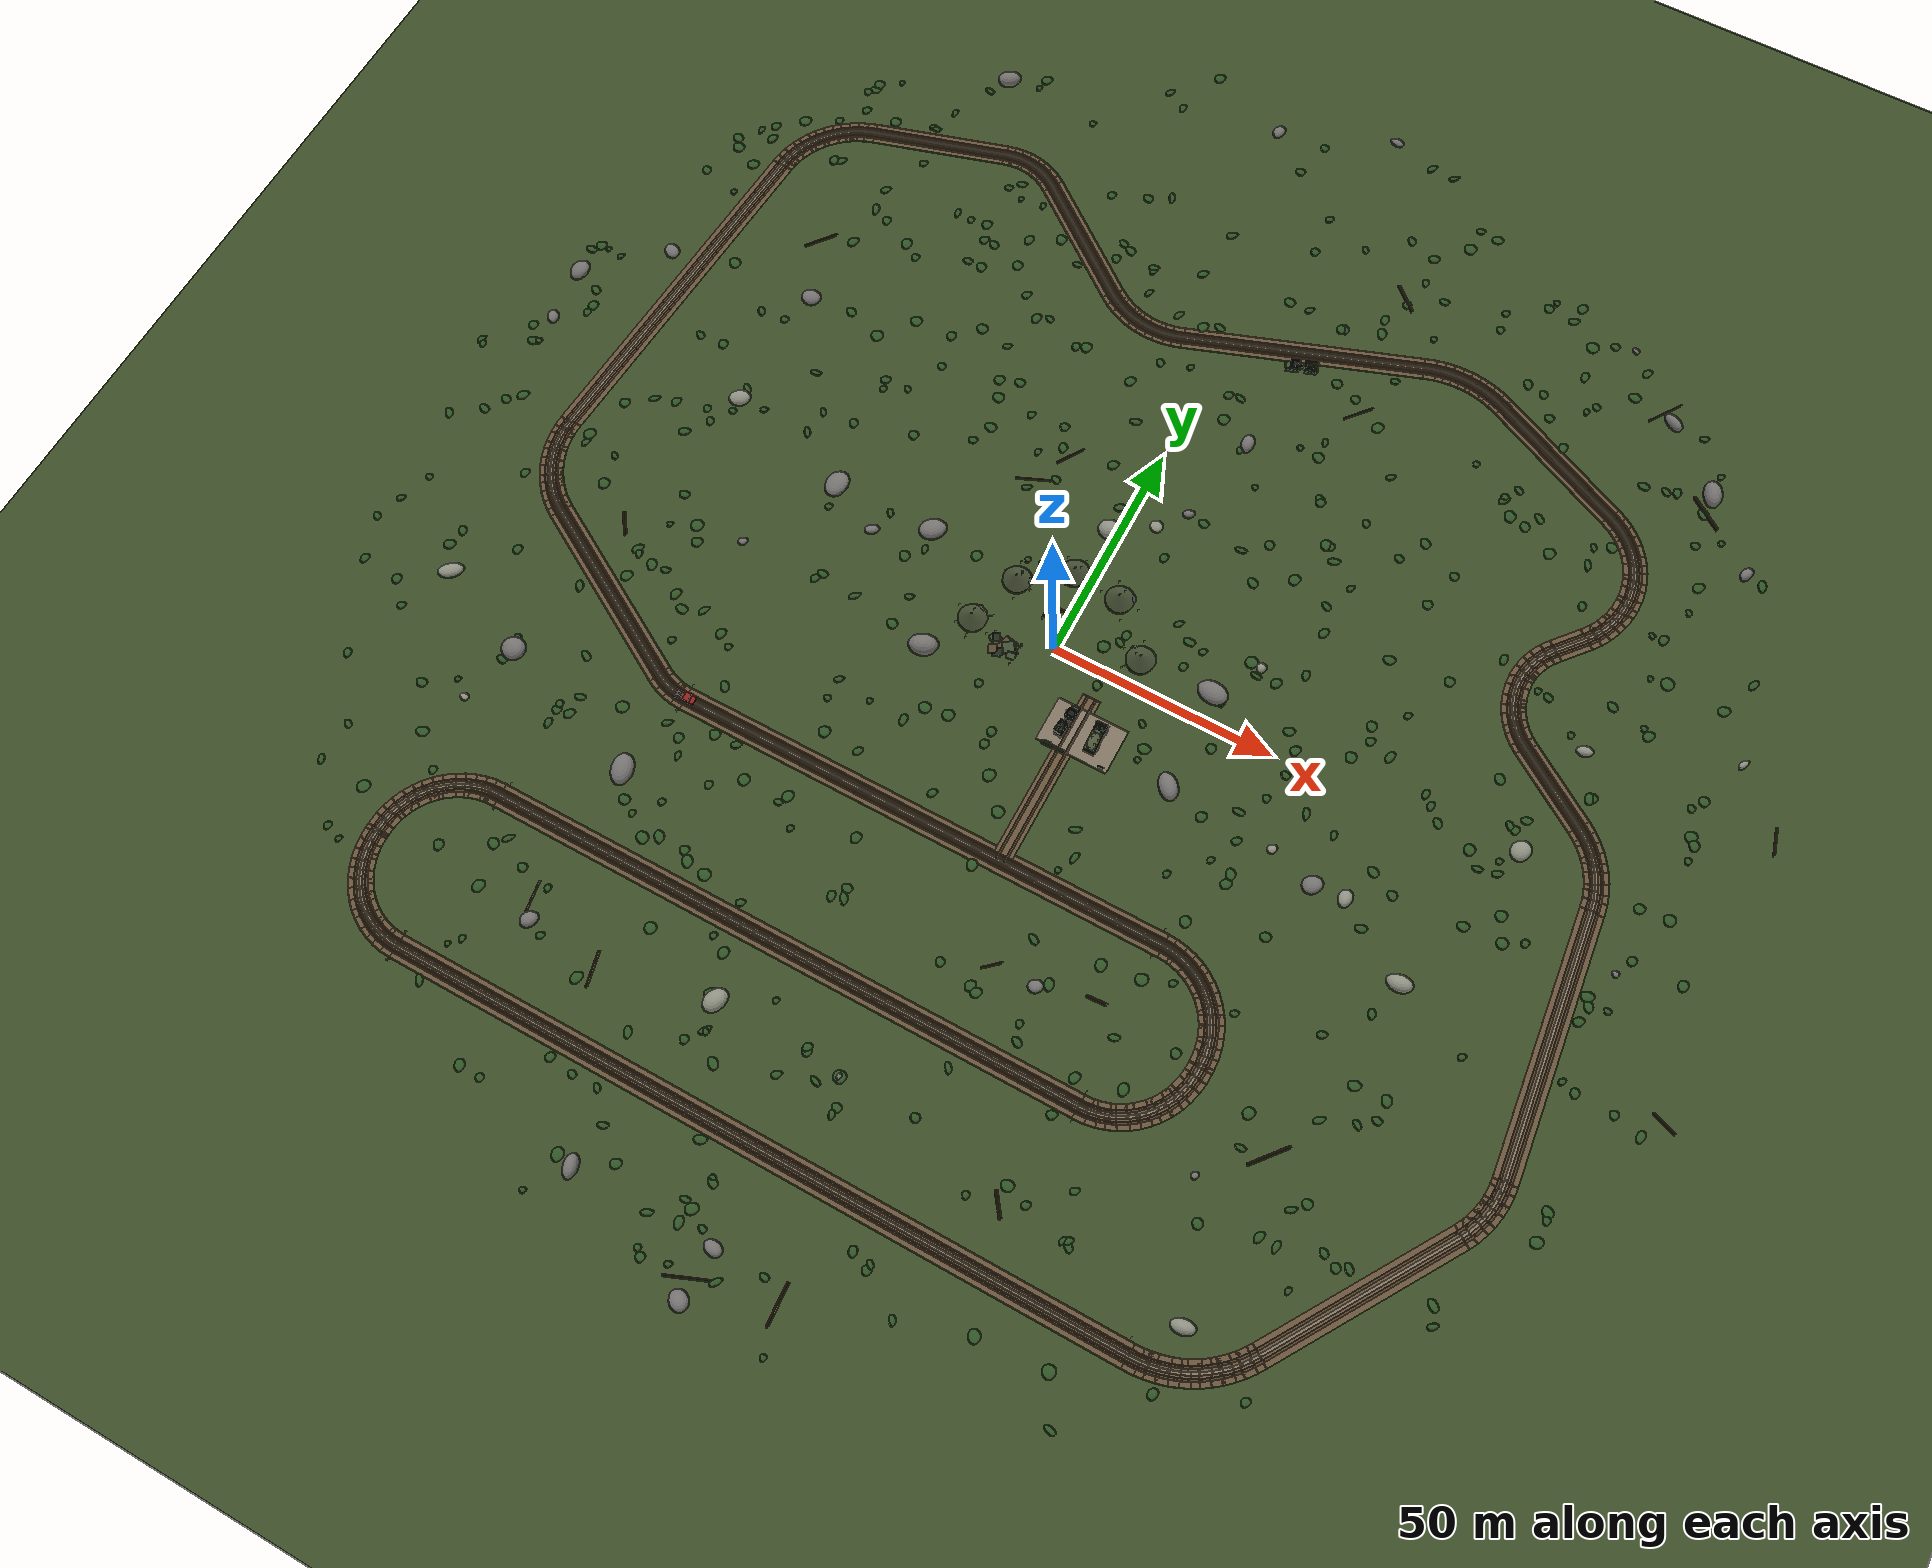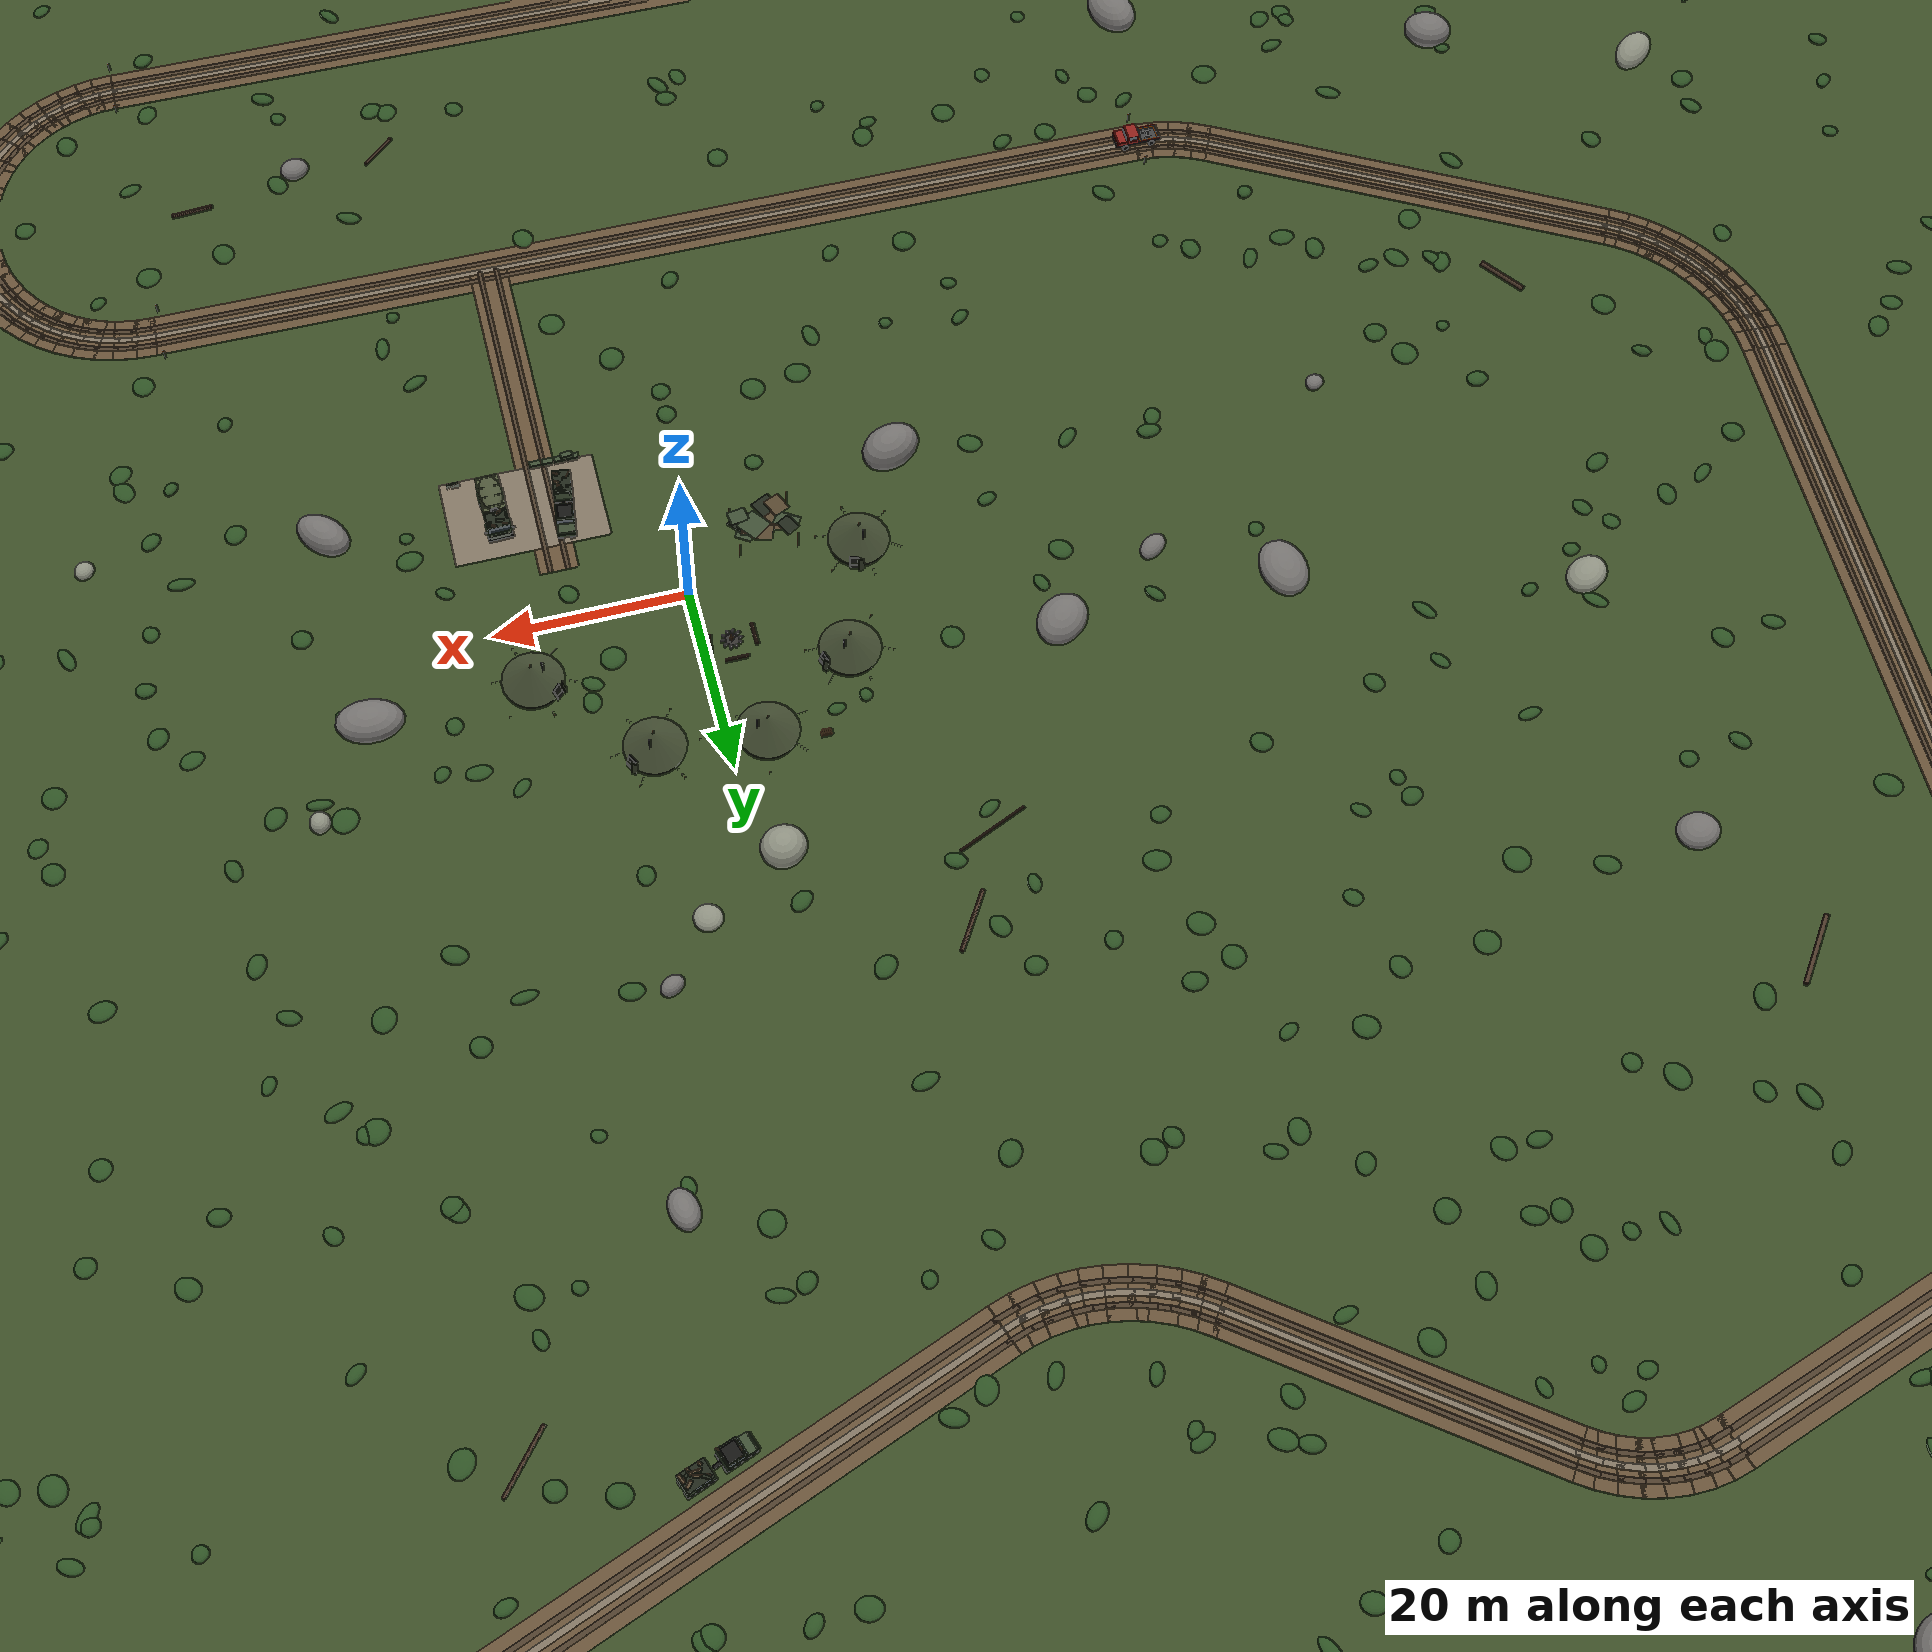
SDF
<sdf version="1.11">
 <world name="hive_base">
  <physics name="1ms" type="ignored">
   <max_step_size>0.001</max_step_size>
   <real_time_factor>1.0</real_time_factor>
  </physics>
  <gravity>0 0 -9.8</gravity>
  <magnetic_field>6e-06 2.3e-05 -4.2e-05</magnetic_field>
  <plugin filename="gz-sim-physics-system" name="gz::sim::systems::Physics"/>
  <plugin filename="gz-sim-user-commands-system" name="gz::sim::systems::UserCommands"/>
  <plugin filename="gz-sim-scene-broadcaster-system" name="gz::sim::systems::SceneBroadcaster"/>
  <plugin filename="gz-sim-contact-system" name="gz::sim::systems::Contact"/>
  <plugin filename="gz-sim-imu-system" name="gz::sim::systems::Imu"/>
  <plugin filename="gz-sim-air-pressure-system" name="gz::sim::systems::AirPressure"/>
  <plugin filename="gz-sim-air-speed-system" name="gz::sim::systems::AirSpeed"/>
  <plugin filename="gz-sim-apply-link-wrench-system" name="gz::sim::systems::ApplyLinkWrench"/>
  <plugin filename="gz-sim-navsat-system" name="gz::sim::systems::NavSat"/>
  <plugin filename="gz-sim-magnetometer-system" name="gz::sim::systems::Magnetometer"/>
  <plugin filename="gz-sim-sensors-system" name="gz::sim::systems::Sensors">
   <render_engine>ogre2</render_engine>
  </plugin>
  <scene><ambient>0.55 0.58 0.6</ambient><background>0.62 0.72 0.82</background><shadows>true</shadows></scene>
  <light type="directional" name="sun">
   <pose>0 0 50 0 0 0</pose>
   <diffuse>1 0.95 0.85 1</diffuse>
   <specular>0.3 0.3 0.3 1</specular>
   <direction>-0.6 0.4 -0.55</direction>
  </light>
  <model name="ground_plane">
   <static>true</static>
   <link name="link">
    <collision name="collision">
     <geometry><plane><normal>0 0 1</normal><size>1000 1000</size></plane></geometry>
     <surface><friction><ode><mu>1.0</mu><mu2>1.0</mu2></ode></friction></surface>
    </collision>
    <visual name="visual">
     <geometry><plane><normal>0 0 1</normal><size>1000 1000</size></plane></geometry>
     <material>
      <ambient>0.23 0.3 0.15 1</ambient>
      <diffuse>0.23 0.3 0.15 1</diffuse>
      <specular>0.05 0.05 0.05 1</specular>
     </material>
    </visual>
   </link>
  </model>
  <model name="dirt_road">
   <static>true</static>
   <link name="link">
    <visual name="v1">
     <pose>-83.952 -80.053 0.02 0 0 -3.085</pose>
     <geometry><box><size>2.506 5 0.04</size></box></geometry>
     <material>
      <ambient>0.4 0.32 0.22 1</ambient>
      <diffuse>0.4 0.32 0.22 1</diffuse>
      <specular>0.05 0.05 0.05 1</specular>
     </material>
     <cast_shadows>false</cast_shadows>
    </visual>
    <visual name="v2">
     <pose>-84.013 -78.955 0.045 0 0 -3.085</pose>
     <geometry><box><size>2.506 0.5 0.02</size></box></geometry>
     <material>
      <ambient>0.3 0.24 0.17 1</ambient>
      <diffuse>0.3 0.24 0.17 1</diffuse>
      <specular>0.05 0.05 0.05 1</specular>
     </material>
     <cast_shadows>false</cast_shadows>
    </visual>
    <visual name="v3">
     <pose>-83.89 -81.152 0.045 0 0 -3.085</pose>
     <geometry><box><size>2.506 0.5 0.02</size></box></geometry>
     <material>
      <ambient>0.3 0.24 0.17 1</ambient>
      <diffuse>0.3 0.24 0.17 1</diffuse>
      <specular>0.05 0.05 0.05 1</specular>
     </material>
     <cast_shadows>false</cast_shadows>
    </visual>
    <visual name="v4">
     <pose>-83.952 -80.053 0.045 0 0 -3.085</pose>
     <geometry><box><size>2.506 0.6 0.02</size></box></geometry>
     <material>
      <ambient>0.5 0.45 0.38 1</ambient>
      <diffuse>0.5 0.45 0.38 1</diffuse>
      <specular>0.05 0.05 0.05 1</specular>
     </material>
     <cast_shadows>false</cast_shadows>
    </visual>
    <visual name="v5">
     <pose>-85.843 -80.267 0.02 0 0 -2.973</pose>
     <geometry><box><size>2.506 5 0.04</size></box></geometry>
     <material>
      <ambient>0.4 0.32 0.22 1</ambient>
      <diffuse>0.4 0.32 0.22 1</diffuse>
      <specular>0.05 0.05 0.05 1</specular>
     </material>
     <cast_shadows>false</cast_shadows>
    </visual>
    <visual name="v6">
     <pose>-86.027 -79.182 0.045 0 0 -2.973</pose>
     <geometry><box><size>2.506 0.5 0.02</size></box></geometry>
     <material>
      <ambient>0.3 0.24 0.17 1</ambient>
      <diffuse>0.3 0.24 0.17 1</diffuse>
      <specular>0.05 0.05 0.05 1</specular>
     </material>
     <cast_shadows>false</cast_shadows>
    </visual>
    <visual name="v7">
     <pose>-85.659 -81.351 0.045 0 0 -2.973</pose>
     <geometry><box><size>2.506 0.5 0.02</size></box></geometry>
     <material>
      <ambient>0.3 0.24 0.17 1</ambient>
      <diffuse>0.3 0.24 0.17 1</diffuse>
      <specular>0.05 0.05 0.05 1</specular>
     </material>
     <cast_shadows>false</cast_shadows>
    </visual>
    <visual name="v8">
     <pose>-85.843 -80.267 0.045 0 0 -2.973</pose>
     <geometry><box><size>2.506 0.6 0.02</size></box></geometry>
     <material>
      <ambient>0.5 0.45 0.38 1</ambient>
      <diffuse>0.5 0.45 0.38 1</diffuse>
      <specular>0.05 0.05 0.05 1</specular>
     </material>
     <cast_shadows>false</cast_shadows>
    </visual>
    <visual name="v9">
     <pose>-87.699 -80.69 0.02 0 0 -2.861</pose>
     <geometry><box><size>2.506 5 0.04</size></box></geometry>
     <material>
      <ambient>0.4 0.32 0.22 1</ambient>
      <diffuse>0.4 0.32 0.22 1</diffuse>
      <specular>0.05 0.05 0.05 1</specular>
     </material>
     <cast_shadows>false</cast_shadows>
    </visual>
    <visual name="v10">
     <pose>-88.003 -79.633 0.045 0 0 -2.861</pose>
     <geometry><box><size>2.506 0.5 0.02</size></box></geometry>
     <material>
      <ambient>0.3 0.24 0.17 1</ambient>
      <diffuse>0.3 0.24 0.17 1</diffuse>
      <specular>0.05 0.05 0.05 1</specular>
     </material>
     <cast_shadows>false</cast_shadows>
    </visual>
    <visual name="v11">
     <pose>-87.394 -81.747 0.045 0 0 -2.861</pose>
     <geometry><box><size>2.506 0.5 0.02</size></box></geometry>
     <material>
      <ambient>0.3 0.24 0.17 1</ambient>
      <diffuse>0.3 0.24 0.17 1</diffuse>
      <specular>0.05 0.05 0.05 1</specular>
     </material>
     <cast_shadows>false</cast_shadows>
    </visual>
    <visual name="v12">
     <pose>-87.699 -80.69 0.045 0 0 -2.861</pose>
     <geometry><box><size>2.506 0.6 0.02</size></box></geometry>
     <material>
      <ambient>0.5 0.45 0.38 1</ambient>
      <diffuse>0.5 0.45 0.38 1</diffuse>
      <specular>0.05 0.05 0.05 1</specular>
     </material>
     <cast_shadows>false</cast_shadows>
    </visual>
    <visual name="v13">
     <pose>-89.495 -81.319 0.02 0 0 -2.749</pose>
     <geometry><box><size>2.506 5 0.04</size></box></geometry>
     <material>
      <ambient>0.4 0.32 0.22 1</ambient>
      <diffuse>0.4 0.32 0.22 1</diffuse>
      <specular>0.05 0.05 0.05 1</specular>
     </material>
     <cast_shadows>false</cast_shadows>
    </visual>
    <visual name="v14">
     <pose>-89.916 -80.302 0.045 0 0 -2.749</pose>
     <geometry><box><size>2.506 0.5 0.02</size></box></geometry>
     <material>
      <ambient>0.3 0.24 0.17 1</ambient>
      <diffuse>0.3 0.24 0.17 1</diffuse>
      <specular>0.05 0.05 0.05 1</specular>
     </material>
     <cast_shadows>false</cast_shadows>
    </visual>
    <visual name="v15">
     <pose>-89.074 -82.335 0.045 0 0 -2.749</pose>
     <geometry><box><size>2.506 0.5 0.02</size></box></geometry>
     <material>
      <ambient>0.3 0.24 0.17 1</ambient>
      <diffuse>0.3 0.24 0.17 1</diffuse>
      <specular>0.05 0.05 0.05 1</specular>
     </material>
     <cast_shadows>false</cast_shadows>
    </visual>
    <visual name="v16">
     <pose>-89.495 -81.319 0.045 0 0 -2.749</pose>
     <geometry><box><size>2.506 0.6 0.02</size></box></geometry>
     <material>
      <ambient>0.5 0.45 0.38 1</ambient>
      <diffuse>0.5 0.45 0.38 1</diffuse>
      <specular>0.05 0.05 0.05 1</specular>
     </material>
     <cast_shadows>false</cast_shadows>
    </visual>
    <visual name="v17">
     <pose>-91.21 -82.145 0.02 0 0 -2.637</pose>
     <geometry><box><size>2.506 5 0.04</size></box></geometry>
     <material>
      <ambient>0.4 0.32 0.22 1</ambient>
      <diffuse>0.4 0.32 0.22 1</diffuse>
      <specular>0.05 0.05 0.05 1</specular>
     </material>
     <cast_shadows>false</cast_shadows>
    </visual>
    <visual name="v18">
     <pose>-91.742 -81.182 0.045 0 0 -2.637</pose>
     <geometry><box><size>2.506 0.5 0.02</size></box></geometry>
     <material>
      <ambient>0.3 0.24 0.17 1</ambient>
      <diffuse>0.3 0.24 0.17 1</diffuse>
      <specular>0.05 0.05 0.05 1</specular>
     </material>
     <cast_shadows>false</cast_shadows>
    </visual>
    <visual name="v19">
     <pose>-90.678 -83.107 0.045 0 0 -2.637</pose>
     <geometry><box><size>2.506 0.5 0.02</size></box></geometry>
     <material>
      <ambient>0.3 0.24 0.17 1</ambient>
      <diffuse>0.3 0.24 0.17 1</diffuse>
      <specular>0.05 0.05 0.05 1</specular>
     </material>
     <cast_shadows>false</cast_shadows>
    </visual>
    <visual name="v20">
     <pose>-91.21 -82.145 0.045 0 0 -2.637</pose>
     <geometry><box><size>2.506 0.6 0.02</size></box></geometry>
     <material>
      <ambient>0.5 0.45 0.38 1</ambient>
      <diffuse>0.5 0.45 0.38 1</diffuse>
      <specular>0.05 0.05 0.05 1</specular>
     </material>
     <cast_shadows>false</cast_shadows>
    </visual>
    <visual name="v21">
     <pose>-92.822 -83.157 0.02 0 0 -2.524</pose>
     <geometry><box><size>2.506 5 0.04</size></box></geometry>
     <material>
      <ambient>0.4 0.32 0.22 1</ambient>
      <diffuse>0.4 0.32 0.22 1</diffuse>
      <specular>0.05 0.05 0.05 1</specular>
     </material>
     <cast_shadows>false</cast_shadows>
    </visual>
    <visual name="v22">
     <pose>-93.458 -82.26 0.045 0 0 -2.524</pose>
     <geometry><box><size>2.506 0.5 0.02</size></box></geometry>
     <material>
      <ambient>0.3 0.24 0.17 1</ambient>
      <diffuse>0.3 0.24 0.17 1</diffuse>
      <specular>0.05 0.05 0.05 1</specular>
     </material>
     <cast_shadows>false</cast_shadows>
    </visual>
    <visual name="v23">
     <pose>-92.185 -84.054 0.045 0 0 -2.524</pose>
     <geometry><box><size>2.506 0.5 0.02</size></box></geometry>
     <material>
      <ambient>0.3 0.24 0.17 1</ambient>
      <diffuse>0.3 0.24 0.17 1</diffuse>
      <specular>0.05 0.05 0.05 1</specular>
     </material>
     <cast_shadows>false</cast_shadows>
    </visual>
    <visual name="v24">
     <pose>-92.822 -83.157 0.045 0 0 -2.524</pose>
     <geometry><box><size>2.506 0.6 0.02</size></box></geometry>
     <material>
      <ambient>0.5 0.45 0.38 1</ambient>
      <diffuse>0.5 0.45 0.38 1</diffuse>
      <specular>0.05 0.05 0.05 1</specular>
     </material>
     <cast_shadows>false</cast_shadows>
    </visual>
    <visual name="v25">
     <pose>-94.31 -84.344 0.02 0 0 -2.412</pose>
     <geometry><box><size>2.506 5 0.04</size></box></geometry>
     <material>
      <ambient>0.4 0.32 0.22 1</ambient>
      <diffuse>0.4 0.32 0.22 1</diffuse>
      <specular>0.05 0.05 0.05 1</specular>
     </material>
     <cast_shadows>false</cast_shadows>
    </visual>
    <visual name="v26">
     <pose>-95.043 -83.524 0.045 0 0 -2.412</pose>
     <geometry><box><size>2.506 0.5 0.02</size></box></geometry>
     <material>
      <ambient>0.3 0.24 0.17 1</ambient>
      <diffuse>0.3 0.24 0.17 1</diffuse>
      <specular>0.05 0.05 0.05 1</specular>
     </material>
     <cast_shadows>false</cast_shadows>
    </visual>
    <visual name="v27">
     <pose>-93.577 -85.164 0.045 0 0 -2.412</pose>
     <geometry><box><size>2.506 0.5 0.02</size></box></geometry>
     <material>
      <ambient>0.3 0.24 0.17 1</ambient>
      <diffuse>0.3 0.24 0.17 1</diffuse>
      <specular>0.05 0.05 0.05 1</specular>
     </material>
     <cast_shadows>false</cast_shadows>
    </visual>
    <visual name="v28">
     <pose>-94.31 -84.344 0.045 0 0 -2.412</pose>
     <geometry><box><size>2.506 0.6 0.02</size></box></geometry>
     <material>
      <ambient>0.5 0.45 0.38 1</ambient>
      <diffuse>0.5 0.45 0.38 1</diffuse>
      <specular>0.05 0.05 0.05 1</specular>
     </material>
     <cast_shadows>false</cast_shadows>
    </visual>
    <visual name="v29">
     <pose>-95.656 -85.69 0.02 0 0 -2.3</pose>
     <geometry><box><size>2.506 5 0.04</size></box></geometry>
     <material>
      <ambient>0.4 0.32 0.22 1</ambient>
      <diffuse>0.4 0.32 0.22 1</diffuse>
      <specular>0.05 0.05 0.05 1</specular>
     </material>
     <cast_shadows>false</cast_shadows>
    </visual>
    <visual name="v30">
     <pose>-96.476 -84.957 0.045 0 0 -2.3</pose>
     <geometry><box><size>2.506 0.5 0.02</size></box></geometry>
     <material>
      <ambient>0.3 0.24 0.17 1</ambient>
      <diffuse>0.3 0.24 0.17 1</diffuse>
      <specular>0.05 0.05 0.05 1</specular>
     </material>
     <cast_shadows>false</cast_shadows>
    </visual>
    <visual name="v31">
     <pose>-94.836 -86.423 0.045 0 0 -2.3</pose>
     <geometry><box><size>2.506 0.5 0.02</size></box></geometry>
     <material>
      <ambient>0.3 0.24 0.17 1</ambient>
      <diffuse>0.3 0.24 0.17 1</diffuse>
      <specular>0.05 0.05 0.05 1</specular>
     </material>
     <cast_shadows>false</cast_shadows>
    </visual>
    <visual name="v32">
     <pose>-95.656 -85.69 0.045 0 0 -2.3</pose>
     <geometry><box><size>2.506 0.6 0.02</size></box></geometry>
     <material>
      <ambient>0.5 0.45 0.38 1</ambient>
      <diffuse>0.5 0.45 0.38 1</diffuse>
      <specular>0.05 0.05 0.05 1</specular>
     </material>
     <cast_shadows>false</cast_shadows>
    </visual>
    <visual name="v33">
     <pose>-96.843 -87.178 0.02 0 0 -2.188</pose>
     <geometry><box><size>2.506 5 0.04</size></box></geometry>
     <material>
      <ambient>0.4 0.32 0.22 1</ambient>
      <diffuse>0.4 0.32 0.22 1</diffuse>
      <specular>0.05 0.05 0.05 1</specular>
     </material>
     <cast_shadows>false</cast_shadows>
    </visual>
    <visual name="v34">
     <pose>-97.74 -86.542 0.045 0 0 -2.188</pose>
     <geometry><box><size>2.506 0.5 0.02</size></box></geometry>
     <material>
      <ambient>0.3 0.24 0.17 1</ambient>
      <diffuse>0.3 0.24 0.17 1</diffuse>
      <specular>0.05 0.05 0.05 1</specular>
     </material>
     <cast_shadows>false</cast_shadows>
    </visual>
    <visual name="v35">
     <pose>-95.946 -87.815 0.045 0 0 -2.188</pose>
     <geometry><box><size>2.506 0.5 0.02</size></box></geometry>
     <material>
      <ambient>0.3 0.24 0.17 1</ambient>
      <diffuse>0.3 0.24 0.17 1</diffuse>
      <specular>0.05 0.05 0.05 1</specular>
     </material>
     <cast_shadows>false</cast_shadows>
    </visual>
    <visual name="v36">
     <pose>-96.843 -87.178 0.045 0 0 -2.188</pose>
     <geometry><box><size>2.506 0.6 0.02</size></box></geometry>
     <material>
      <ambient>0.5 0.45 0.38 1</ambient>
      <diffuse>0.5 0.45 0.38 1</diffuse>
      <specular>0.05 0.05 0.05 1</specular>
     </material>
     <cast_shadows>false</cast_shadows>
    </visual>
    <visual name="v37">
     <pose>-97.855 -88.79 0.02 0 0 -2.076</pose>
     <geometry><box><size>2.506 5 0.04</size></box></geometry>
     <material>
      <ambient>0.4 0.32 0.22 1</ambient>
      <diffuse>0.4 0.32 0.22 1</diffuse>
      <specular>0.05 0.05 0.05 1</specular>
     </material>
     <cast_shadows>false</cast_shadows>
    </visual>
    <visual name="v38">
     <pose>-98.818 -88.258 0.045 0 0 -2.076</pose>
     <geometry><box><size>2.506 0.5 0.02</size></box></geometry>
     <material>
      <ambient>0.3 0.24 0.17 1</ambient>
      <diffuse>0.3 0.24 0.17 1</diffuse>
      <specular>0.05 0.05 0.05 1</specular>
     </material>
     <cast_shadows>false</cast_shadows>
    </visual>
    <visual name="v39">
     <pose>-96.893 -89.322 0.045 0 0 -2.076</pose>
     <geometry><box><size>2.506 0.5 0.02</size></box></geometry>
     <material>
      <ambient>0.3 0.24 0.17 1</ambient>
      <diffuse>0.3 0.24 0.17 1</diffuse>
      <specular>0.05 0.05 0.05 1</specular>
     </material>
     <cast_shadows>false</cast_shadows>
    </visual>
    <visual name="v40">
     <pose>-97.855 -88.79 0.045 0 0 -2.076</pose>
     <geometry><box><size>2.506 0.6 0.02</size></box></geometry>
     <material>
      <ambient>0.5 0.45 0.38 1</ambient>
      <diffuse>0.5 0.45 0.38 1</diffuse>
      <specular>0.05 0.05 0.05 1</specular>
     </material>
     <cast_shadows>false</cast_shadows>
    </visual>
    <visual name="v41">
     <pose>-98.681 -90.505 0.02 0 0 -1.963</pose>
     <geometry><box><size>2.506 5 0.04</size></box></geometry>
     <material>
      <ambient>0.4 0.32 0.22 1</ambient>
      <diffuse>0.4 0.32 0.22 1</diffuse>
      <specular>0.05 0.05 0.05 1</specular>
     </material>
     <cast_shadows>false</cast_shadows>
    </visual>
    <visual name="v42">
     <pose>-99.698 -90.084 0.045 0 0 -1.963</pose>
     <geometry><box><size>2.506 0.5 0.02</size></box></geometry>
     <material>
      <ambient>0.3 0.24 0.17 1</ambient>
      <diffuse>0.3 0.24 0.17 1</diffuse>
      <specular>0.05 0.05 0.05 1</specular>
     </material>
     <cast_shadows>false</cast_shadows>
    </visual>
    <visual name="v43">
     <pose>-97.665 -90.926 0.045 0 0 -1.963</pose>
     <geometry><box><size>2.506 0.5 0.02</size></box></geometry>
     <material>
      <ambient>0.3 0.24 0.17 1</ambient>
      <diffuse>0.3 0.24 0.17 1</diffuse>
      <specular>0.05 0.05 0.05 1</specular>
     </material>
     <cast_shadows>false</cast_shadows>
    </visual>
    <visual name="v44">
     <pose>-98.681 -90.505 0.045 0 0 -1.963</pose>
     <geometry><box><size>2.506 0.6 0.02</size></box></geometry>
     <material>
      <ambient>0.5 0.45 0.38 1</ambient>
      <diffuse>0.5 0.45 0.38 1</diffuse>
      <specular>0.05 0.05 0.05 1</specular>
     </material>
     <cast_shadows>false</cast_shadows>
    </visual>
    <visual name="v45">
     <pose>-99.31 -92.301 0.02 0 0 -1.851</pose>
     <geometry><box><size>2.506 5 0.04</size></box></geometry>
     <material>
      <ambient>0.4 0.32 0.22 1</ambient>
      <diffuse>0.4 0.32 0.22 1</diffuse>
      <specular>0.05 0.05 0.05 1</specular>
     </material>
     <cast_shadows>false</cast_shadows>
    </visual>
    <visual name="v46">
     <pose>-100.367 -91.997 0.045 0 0 -1.851</pose>
     <geometry><box><size>2.506 0.5 0.02</size></box></geometry>
     <material>
      <ambient>0.3 0.24 0.17 1</ambient>
      <diffuse>0.3 0.24 0.17 1</diffuse>
      <specular>0.05 0.05 0.05 1</specular>
     </material>
     <cast_shadows>false</cast_shadows>
    </visual>
    <visual name="v47">
     <pose>-98.253 -92.606 0.045 0 0 -1.851</pose>
     <geometry><box><size>2.506 0.5 0.02</size></box></geometry>
     <material>
      <ambient>0.3 0.24 0.17 1</ambient>
      <diffuse>0.3 0.24 0.17 1</diffuse>
      <specular>0.05 0.05 0.05 1</specular>
     </material>
     <cast_shadows>false</cast_shadows>
    </visual>
    <visual name="v48">
     <pose>-99.31 -92.301 0.045 0 0 -1.851</pose>
     <geometry><box><size>2.506 0.6 0.02</size></box></geometry>
     <material>
      <ambient>0.5 0.45 0.38 1</ambient>
      <diffuse>0.5 0.45 0.38 1</diffuse>
      <specular>0.05 0.05 0.05 1</specular>
     </material>
     <cast_shadows>false</cast_shadows>
    </visual>
    <visual name="v49">
     <pose>-99.733 -94.157 0.02 0 0 -1.739</pose>
     <geometry><box><size>2.506 5 0.04</size></box></geometry>
     <material>
      <ambient>0.4 0.32 0.22 1</ambient>
      <diffuse>0.4 0.32 0.22 1</diffuse>
      <specular>0.05 0.05 0.05 1</specular>
     </material>
     <cast_shadows>false</cast_shadows>
    </visual>
    <visual name="v50">
     <pose>-100.818 -93.973 0.045 0 0 -1.739</pose>
     <geometry><box><size>2.506 0.5 0.02</size></box></geometry>
     <material>
      <ambient>0.3 0.24 0.17 1</ambient>
      <diffuse>0.3 0.24 0.17 1</diffuse>
      <specular>0.05 0.05 0.05 1</specular>
     </material>
     <cast_shadows>false</cast_shadows>
    </visual>
    <visual name="v51">
     <pose>-98.649 -94.341 0.045 0 0 -1.739</pose>
     <geometry><box><size>2.506 0.5 0.02</size></box></geometry>
     <material>
      <ambient>0.3 0.24 0.17 1</ambient>
      <diffuse>0.3 0.24 0.17 1</diffuse>
      <specular>0.05 0.05 0.05 1</specular>
     </material>
     <cast_shadows>false</cast_shadows>
    </visual>
    <visual name="v52">
     <pose>-99.733 -94.157 0.045 0 0 -1.739</pose>
     <geometry><box><size>2.506 0.6 0.02</size></box></geometry>
     <material>
      <ambient>0.5 0.45 0.38 1</ambient>
      <diffuse>0.5 0.45 0.38 1</diffuse>
      <specular>0.05 0.05 0.05 1</specular>
     </material>
     <cast_shadows>false</cast_shadows>
    </visual>
    <visual name="v53">
     <pose>-99.947 -96.048 0.02 0 0 -1.627</pose>
     <geometry><box><size>2.506 5 0.04</size></box></geometry>
     <material>
      <ambient>0.4 0.32 0.22 1</ambient>
      <diffuse>0.4 0.32 0.22 1</diffuse>
      <specular>0.05 0.05 0.05 1</specular>
     </material>
     <cast_shadows>false</cast_shadows>
    </visual>
    <visual name="v54">
     <pose>-101.045 -95.987 0.045 0 0 -1.627</pose>
     <geometry><box><size>2.506 0.5 0.02</size></box></geometry>
     <material>
      <ambient>0.3 0.24 0.17 1</ambient>
      <diffuse>0.3 0.24 0.17 1</diffuse>
      <specular>0.05 0.05 0.05 1</specular>
     </material>
     <cast_shadows>false</cast_shadows>
    </visual>
    <visual name="v55">
     <pose>-98.848 -96.11 0.045 0 0 -1.627</pose>
     <geometry><box><size>2.506 0.5 0.02</size></box></geometry>
     <material>
      <ambient>0.3 0.24 0.17 1</ambient>
      <diffuse>0.3 0.24 0.17 1</diffuse>
      <specular>0.05 0.05 0.05 1</specular>
     </material>
     <cast_shadows>false</cast_shadows>
    </visual>
    <visual name="v56">
     <pose>-99.947 -96.048 0.045 0 0 -1.627</pose>
     <geometry><box><size>2.506 0.6 0.02</size></box></geometry>
     <material>
      <ambient>0.5 0.45 0.38 1</ambient>
      <diffuse>0.5 0.45 0.38 1</diffuse>
      <specular>0.05 0.05 0.05 1</specular>
     </material>
     <cast_shadows>false</cast_shadows>
    </visual>
    <visual name="v57">
     <pose>-100 -97.5 0.02 0 0 -1.571</pose>
     <geometry><box><size>1.2 5 0.04</size></box></geometry>
     <material>
      <ambient>0.4 0.32 0.22 1</ambient>
      <diffuse>0.4 0.32 0.22 1</diffuse>
      <specular>0.05 0.05 0.05 1</specular>
     </material>
     <cast_shadows>false</cast_shadows>
    </visual>
    <visual name="v58">
     <pose>-101.1 -97.5 0.045 0 0 -1.571</pose>
     <geometry><box><size>1.2 0.5 0.02</size></box></geometry>
     <material>
      <ambient>0.3 0.24 0.17 1</ambient>
      <diffuse>0.3 0.24 0.17 1</diffuse>
      <specular>0.05 0.05 0.05 1</specular>
     </material>
     <cast_shadows>false</cast_shadows>
    </visual>
    <visual name="v59">
     <pose>-98.9 -97.5 0.045 0 0 -1.571</pose>
     <geometry><box><size>1.2 0.5 0.02</size></box></geometry>
     <material>
      <ambient>0.3 0.24 0.17 1</ambient>
      <diffuse>0.3 0.24 0.17 1</diffuse>
      <specular>0.05 0.05 0.05 1</specular>
     </material>
     <cast_shadows>false</cast_shadows>
    </visual>
    <visual name="v60">
     <pose>-100 -97.5 0.045 0 0 -1.571</pose>
     <geometry><box><size>1.2 0.6 0.02</size></box></geometry>
     <material>
      <ambient>0.5 0.45 0.38 1</ambient>
      <diffuse>0.5 0.45 0.38 1</diffuse>
      <specular>0.05 0.05 0.05 1</specular>
     </material>
     <cast_shadows>false</cast_shadows>
    </visual>
    <visual name="v61">
     <pose>-99.947 -98.952 0.02 0 0 -1.515</pose>
     <geometry><box><size>2.506 5 0.04</size></box></geometry>
     <material>
      <ambient>0.4 0.32 0.22 1</ambient>
      <diffuse>0.4 0.32 0.22 1</diffuse>
      <specular>0.05 0.05 0.05 1</specular>
     </material>
     <cast_shadows>false</cast_shadows>
    </visual>
    <visual name="v62">
     <pose>-101.045 -99.013 0.045 0 0 -1.515</pose>
     <geometry><box><size>2.506 0.5 0.02</size></box></geometry>
     <material>
      <ambient>0.3 0.24 0.17 1</ambient>
      <diffuse>0.3 0.24 0.17 1</diffuse>
      <specular>0.05 0.05 0.05 1</specular>
     </material>
     <cast_shadows>false</cast_shadows>
    </visual>
    <visual name="v63">
     <pose>-98.848 -98.89 0.045 0 0 -1.515</pose>
     <geometry><box><size>2.506 0.5 0.02</size></box></geometry>
     <material>
      <ambient>0.3 0.24 0.17 1</ambient>
      <diffuse>0.3 0.24 0.17 1</diffuse>
      <specular>0.05 0.05 0.05 1</specular>
     </material>
     <cast_shadows>false</cast_shadows>
    </visual>
    <visual name="v64">
     <pose>-99.947 -98.952 0.045 0 0 -1.515</pose>
     <geometry><box><size>2.506 0.6 0.02</size></box></geometry>
     <material>
      <ambient>0.5 0.45 0.38 1</ambient>
      <diffuse>0.5 0.45 0.38 1</diffuse>
      <specular>0.05 0.05 0.05 1</specular>
     </material>
     <cast_shadows>false</cast_shadows>
    </visual>
    <visual name="v65">
     <pose>-99.733 -100.843 0.02 0 0 -1.402</pose>
     <geometry><box><size>2.506 5 0.04</size></box></geometry>
     <material>
      <ambient>0.4 0.32 0.22 1</ambient>
      <diffuse>0.4 0.32 0.22 1</diffuse>
      <specular>0.05 0.05 0.05 1</specular>
     </material>
     <cast_shadows>false</cast_shadows>
    </visual>
    <visual name="v66">
     <pose>-100.818 -101.027 0.045 0 0 -1.402</pose>
     <geometry><box><size>2.506 0.5 0.02</size></box></geometry>
     <material>
      <ambient>0.3 0.24 0.17 1</ambient>
      <diffuse>0.3 0.24 0.17 1</diffuse>
      <specular>0.05 0.05 0.05 1</specular>
     </material>
     <cast_shadows>false</cast_shadows>
    </visual>
    <visual name="v67">
     <pose>-98.649 -100.659 0.045 0 0 -1.402</pose>
     <geometry><box><size>2.506 0.5 0.02</size></box></geometry>
     <material>
      <ambient>0.3 0.24 0.17 1</ambient>
      <diffuse>0.3 0.24 0.17 1</diffuse>
      <specular>0.05 0.05 0.05 1</specular>
     </material>
     <cast_shadows>false</cast_shadows>
    </visual>
    <visual name="v68">
     <pose>-99.733 -100.843 0.045 0 0 -1.402</pose>
     <geometry><box><size>2.506 0.6 0.02</size></box></geometry>
     <material>
      <ambient>0.5 0.45 0.38 1</ambient>
      <diffuse>0.5 0.45 0.38 1</diffuse>
      <specular>0.05 0.05 0.05 1</specular>
     </material>
     <cast_shadows>false</cast_shadows>
    </visual>
    <visual name="v69">
     <pose>-99.31 -102.699 0.02 0 0 -1.29</pose>
     <geometry><box><size>2.506 5 0.04</size></box></geometry>
     <material>
      <ambient>0.4 0.32 0.22 1</ambient>
      <diffuse>0.4 0.32 0.22 1</diffuse>
      <specular>0.05 0.05 0.05 1</specular>
     </material>
     <cast_shadows>false</cast_shadows>
    </visual>
    <visual name="v70">
     <pose>-100.367 -103.003 0.045 0 0 -1.29</pose>
     <geometry><box><size>2.506 0.5 0.02</size></box></geometry>
     <material>
      <ambient>0.3 0.24 0.17 1</ambient>
      <diffuse>0.3 0.24 0.17 1</diffuse>
      <specular>0.05 0.05 0.05 1</specular>
     </material>
     <cast_shadows>false</cast_shadows>
    </visual>
    <visual name="v71">
     <pose>-98.253 -102.394 0.045 0 0 -1.29</pose>
     <geometry><box><size>2.506 0.5 0.02</size></box></geometry>
     <material>
      <ambient>0.3 0.24 0.17 1</ambient>
      <diffuse>0.3 0.24 0.17 1</diffuse>
      <specular>0.05 0.05 0.05 1</specular>
     </material>
     <cast_shadows>false</cast_shadows>
    </visual>
    <visual name="v72">
     <pose>-99.31 -102.699 0.045 0 0 -1.29</pose>
     <geometry><box><size>2.506 0.6 0.02</size></box></geometry>
     <material>
      <ambient>0.5 0.45 0.38 1</ambient>
      <diffuse>0.5 0.45 0.38 1</diffuse>
      <specular>0.05 0.05 0.05 1</specular>
     </material>
     <cast_shadows>false</cast_shadows>
    </visual>
    <visual name="v73">
     <pose>-98.681 -104.495 0.02 0 0 -1.178</pose>
     <geometry><box><size>2.506 5 0.04</size></box></geometry>
     <material>
      <ambient>0.4 0.32 0.22 1</ambient>
      <diffuse>0.4 0.32 0.22 1</diffuse>
      <specular>0.05 0.05 0.05 1</specular>
     </material>
     <cast_shadows>false</cast_shadows>
    </visual>
    <visual name="v74">
     <pose>-99.698 -104.916 0.045 0 0 -1.178</pose>
     <geometry><box><size>2.506 0.5 0.02</size></box></geometry>
     <material>
      <ambient>0.3 0.24 0.17 1</ambient>
      <diffuse>0.3 0.24 0.17 1</diffuse>
      <specular>0.05 0.05 0.05 1</specular>
     </material>
     <cast_shadows>false</cast_shadows>
    </visual>
    <visual name="v75">
     <pose>-97.665 -104.074 0.045 0 0 -1.178</pose>
     <geometry><box><size>2.506 0.5 0.02</size></box></geometry>
     <material>
      <ambient>0.3 0.24 0.17 1</ambient>
      <diffuse>0.3 0.24 0.17 1</diffuse>
      <specular>0.05 0.05 0.05 1</specular>
     </material>
     <cast_shadows>false</cast_shadows>
    </visual>
    <visual name="v76">
     <pose>-98.681 -104.495 0.045 0 0 -1.178</pose>
     <geometry><box><size>2.506 0.6 0.02</size></box></geometry>
     <material>
      <ambient>0.5 0.45 0.38 1</ambient>
      <diffuse>0.5 0.45 0.38 1</diffuse>
      <specular>0.05 0.05 0.05 1</specular>
     </material>
     <cast_shadows>false</cast_shadows>
    </visual>
    <visual name="v77">
     <pose>-97.855 -106.21 0.02 0 0 -1.066</pose>
     <geometry><box><size>2.506 5 0.04</size></box></geometry>
     <material>
      <ambient>0.4 0.32 0.22 1</ambient>
      <diffuse>0.4 0.32 0.22 1</diffuse>
      <specular>0.05 0.05 0.05 1</specular>
     </material>
     <cast_shadows>false</cast_shadows>
    </visual>
    <visual name="v78">
     <pose>-98.818 -106.742 0.045 0 0 -1.066</pose>
     <geometry><box><size>2.506 0.5 0.02</size></box></geometry>
     <material>
      <ambient>0.3 0.24 0.17 1</ambient>
      <diffuse>0.3 0.24 0.17 1</diffuse>
      <specular>0.05 0.05 0.05 1</specular>
     </material>
     <cast_shadows>false</cast_shadows>
    </visual>
    <visual name="v79">
     <pose>-96.893 -105.678 0.045 0 0 -1.066</pose>
     <geometry><box><size>2.506 0.5 0.02</size></box></geometry>
     <material>
      <ambient>0.3 0.24 0.17 1</ambient>
      <diffuse>0.3 0.24 0.17 1</diffuse>
      <specular>0.05 0.05 0.05 1</specular>
     </material>
     <cast_shadows>false</cast_shadows>
    </visual>
    <visual name="v80">
     <pose>-97.855 -106.21 0.045 0 0 -1.066</pose>
     <geometry><box><size>2.506 0.6 0.02</size></box></geometry>
     <material>
      <ambient>0.5 0.45 0.38 1</ambient>
      <diffuse>0.5 0.45 0.38 1</diffuse>
      <specular>0.05 0.05 0.05 1</specular>
     </material>
     <cast_shadows>false</cast_shadows>
    </visual>
    <visual name="v81">
     <pose>-96.843 -107.822 0.02 0 0 -0.954</pose>
     <geometry><box><size>2.506 5 0.04</size></box></geometry>
     <material>
      <ambient>0.4 0.32 0.22 1</ambient>
      <diffuse>0.4 0.32 0.22 1</diffuse>
      <specular>0.05 0.05 0.05 1</specular>
     </material>
     <cast_shadows>false</cast_shadows>
    </visual>
    <visual name="v82">
     <pose>-97.74 -108.458 0.045 0 0 -0.954</pose>
     <geometry><box><size>2.506 0.5 0.02</size></box></geometry>
     <material>
      <ambient>0.3 0.24 0.17 1</ambient>
      <diffuse>0.3 0.24 0.17 1</diffuse>
      <specular>0.05 0.05 0.05 1</specular>
     </material>
     <cast_shadows>false</cast_shadows>
    </visual>
    <visual name="v83">
     <pose>-95.946 -107.185 0.045 0 0 -0.954</pose>
     <geometry><box><size>2.506 0.5 0.02</size></box></geometry>
     <material>
      <ambient>0.3 0.24 0.17 1</ambient>
      <diffuse>0.3 0.24 0.17 1</diffuse>
      <specular>0.05 0.05 0.05 1</specular>
     </material>
     <cast_shadows>false</cast_shadows>
    </visual>
    <visual name="v84">
     <pose>-96.843 -107.822 0.045 0 0 -0.954</pose>
     <geometry><box><size>2.506 0.6 0.02</size></box></geometry>
     <material>
      <ambient>0.5 0.45 0.38 1</ambient>
      <diffuse>0.5 0.45 0.38 1</diffuse>
      <specular>0.05 0.05 0.05 1</specular>
     </material>
     <cast_shadows>false</cast_shadows>
    </visual>
    <visual name="v85">
     <pose>-95.656 -109.31 0.02 0 0 -0.841</pose>
     <geometry><box><size>2.506 5 0.04</size></box></geometry>
     <material>
      <ambient>0.4 0.32 0.22 1</ambient>
      <diffuse>0.4 0.32 0.22 1</diffuse>
      <specular>0.05 0.05 0.05 1</specular>
     </material>
     <cast_shadows>false</cast_shadows>
    </visual>
    <visual name="v86">
     <pose>-96.476 -110.043 0.045 0 0 -0.841</pose>
     <geometry><box><size>2.506 0.5 0.02</size></box></geometry>
     <material>
      <ambient>0.3 0.24 0.17 1</ambient>
      <diffuse>0.3 0.24 0.17 1</diffuse>
      <specular>0.05 0.05 0.05 1</specular>
     </material>
     <cast_shadows>false</cast_shadows>
    </visual>
    <visual name="v87">
     <pose>-94.836 -108.577 0.045 0 0 -0.841</pose>
     <geometry><box><size>2.506 0.5 0.02</size></box></geometry>
     <material>
      <ambient>0.3 0.24 0.17 1</ambient>
      <diffuse>0.3 0.24 0.17 1</diffuse>
      <specular>0.05 0.05 0.05 1</specular>
     </material>
     <cast_shadows>false</cast_shadows>
    </visual>
    <visual name="v88">
     <pose>-95.656 -109.31 0.045 0 0 -0.841</pose>
     <geometry><box><size>2.506 0.6 0.02</size></box></geometry>
     <material>
      <ambient>0.5 0.45 0.38 1</ambient>
      <diffuse>0.5 0.45 0.38 1</diffuse>
      <specular>0.05 0.05 0.05 1</specular>
     </material>
     <cast_shadows>false</cast_shadows>
    </visual>
    <visual name="v89">
     <pose>-94.31 -110.656 0.02 0 0 -0.729</pose>
     <geometry><box><size>2.506 5 0.04</size></box></geometry>
     <material>
      <ambient>0.4 0.32 0.22 1</ambient>
      <diffuse>0.4 0.32 0.22 1</diffuse>
      <specular>0.05 0.05 0.05 1</specular>
     </material>
     <cast_shadows>false</cast_shadows>
    </visual>
    <visual name="v90">
     <pose>-95.043 -111.476 0.045 0 0 -0.729</pose>
     <geometry><box><size>2.506 0.5 0.02</size></box></geometry>
     <material>
      <ambient>0.3 0.24 0.17 1</ambient>
      <diffuse>0.3 0.24 0.17 1</diffuse>
      <specular>0.05 0.05 0.05 1</specular>
     </material>
     <cast_shadows>false</cast_shadows>
    </visual>
    <visual name="v91">
     <pose>-93.577 -109.836 0.045 0 0 -0.729</pose>
     <geometry><box><size>2.506 0.5 0.02</size></box></geometry>
     <material>
      <ambient>0.3 0.24 0.17 1</ambient>
      <diffuse>0.3 0.24 0.17 1</diffuse>
      <specular>0.05 0.05 0.05 1</specular>
     </material>
     <cast_shadows>false</cast_shadows>
    </visual>
    <visual name="v92">
     <pose>-94.31 -110.656 0.045 0 0 -0.729</pose>
     <geometry><box><size>2.506 0.6 0.02</size></box></geometry>
     <material>
      <ambient>0.5 0.45 0.38 1</ambient>
      <diffuse>0.5 0.45 0.38 1</diffuse>
      <specular>0.05 0.05 0.05 1</specular>
     </material>
     <cast_shadows>false</cast_shadows>
    </visual>
    <visual name="v93">
     <pose>-92.822 -111.843 0.02 0 0 -0.617</pose>
     <geometry><box><size>2.506 5 0.04</size></box></geometry>
     <material>
      <ambient>0.4 0.32 0.22 1</ambient>
      <diffuse>0.4 0.32 0.22 1</diffuse>
      <specular>0.05 0.05 0.05 1</specular>
     </material>
     <cast_shadows>false</cast_shadows>
    </visual>
    <visual name="v94">
     <pose>-93.458 -112.74 0.045 0 0 -0.617</pose>
     <geometry><box><size>2.506 0.5 0.02</size></box></geometry>
     <material>
      <ambient>0.3 0.24 0.17 1</ambient>
      <diffuse>0.3 0.24 0.17 1</diffuse>
      <specular>0.05 0.05 0.05 1</specular>
     </material>
     <cast_shadows>false</cast_shadows>
    </visual>
    <visual name="v95">
     <pose>-92.185 -110.946 0.045 0 0 -0.617</pose>
     <geometry><box><size>2.506 0.5 0.02</size></box></geometry>
     <material>
      <ambient>0.3 0.24 0.17 1</ambient>
      <diffuse>0.3 0.24 0.17 1</diffuse>
      <specular>0.05 0.05 0.05 1</specular>
     </material>
     <cast_shadows>false</cast_shadows>
    </visual>
    <visual name="v96">
     <pose>-92.822 -111.843 0.045 0 0 -0.617</pose>
     <geometry><box><size>2.506 0.6 0.02</size></box></geometry>
     <material>
      <ambient>0.5 0.45 0.38 1</ambient>
      <diffuse>0.5 0.45 0.38 1</diffuse>
      <specular>0.05 0.05 0.05 1</specular>
     </material>
     <cast_shadows>false</cast_shadows>
    </visual>
    <visual name="v97">
     <pose>-91.21 -112.855 0.02 0 0 -0.505</pose>
     <geometry><box><size>2.506 5 0.04</size></box></geometry>
     <material>
      <ambient>0.4 0.32 0.22 1</ambient>
      <diffuse>0.4 0.32 0.22 1</diffuse>
      <specular>0.05 0.05 0.05 1</specular>
     </material>
     <cast_shadows>false</cast_shadows>
    </visual>
    <visual name="v98">
     <pose>-91.742 -113.818 0.045 0 0 -0.505</pose>
     <geometry><box><size>2.506 0.5 0.02</size></box></geometry>
     <material>
      <ambient>0.3 0.24 0.17 1</ambient>
      <diffuse>0.3 0.24 0.17 1</diffuse>
      <specular>0.05 0.05 0.05 1</specular>
     </material>
     <cast_shadows>false</cast_shadows>
    </visual>
    <visual name="v99">
     <pose>-90.678 -111.893 0.045 0 0 -0.505</pose>
     <geometry><box><size>2.506 0.5 0.02</size></box></geometry>
     <material>
      <ambient>0.3 0.24 0.17 1</ambient>
      <diffuse>0.3 0.24 0.17 1</diffuse>
      <specular>0.05 0.05 0.05 1</specular>
     </material>
     <cast_shadows>false</cast_shadows>
    </visual>
    <visual name="v100">
     <pose>-91.21 -112.855 0.045 0 0 -0.505</pose>
     <geometry><box><size>2.506 0.6 0.02</size></box></geometry>
     <material>
      <ambient>0.5 0.45 0.38 1</ambient>
      <diffuse>0.5 0.45 0.38 1</diffuse>
      <specular>0.05 0.05 0.05 1</specular>
     </material>
     <cast_shadows>false</cast_shadows>
    </visual>
    <visual name="v101">
     <pose>-89.495 -113.681 0.02 0 0 -0.393</pose>
     <geometry><box><size>2.506 5 0.04</size></box></geometry>
     <material>
      <ambient>0.4 0.32 0.22 1</ambient>
      <diffuse>0.4 0.32 0.22 1</diffuse>
      <specular>0.05 0.05 0.05 1</specular>
     </material>
     <cast_shadows>false</cast_shadows>
    </visual>
    <visual name="v102">
     <pose>-89.916 -114.698 0.045 0 0 -0.393</pose>
     <geometry><box><size>2.506 0.5 0.02</size></box></geometry>
     <material>
      <ambient>0.3 0.24 0.17 1</ambient>
      <diffuse>0.3 0.24 0.17 1</diffuse>
      <specular>0.05 0.05 0.05 1</specular>
     </material>
     <cast_shadows>false</cast_shadows>
    </visual>
    <visual name="v103">
     <pose>-89.074 -112.665 0.045 0 0 -0.393</pose>
     <geometry><box><size>2.506 0.5 0.02</size></box></geometry>
     <material>
      <ambient>0.3 0.24 0.17 1</ambient>
      <diffuse>0.3 0.24 0.17 1</diffuse>
      <specular>0.05 0.05 0.05 1</specular>
     </material>
     <cast_shadows>false</cast_shadows>
    </visual>
    <visual name="v104">
     <pose>-89.495 -113.681 0.045 0 0 -0.393</pose>
     <geometry><box><size>2.506 0.6 0.02</size></box></geometry>
     <material>
      <ambient>0.5 0.45 0.38 1</ambient>
      <diffuse>0.5 0.45 0.38 1</diffuse>
      <specular>0.05 0.05 0.05 1</specular>
     </material>
     <cast_shadows>false</cast_shadows>
    </visual>
    <visual name="v105">
     <pose>-87.699 -114.31 0.02 0 0 -0.28</pose>
     <geometry><box><size>2.506 5 0.04</size></box></geometry>
     <material>
      <ambient>0.4 0.32 0.22 1</ambient>
      <diffuse>0.4 0.32 0.22 1</diffuse>
      <specular>0.05 0.05 0.05 1</specular>
     </material>
     <cast_shadows>false</cast_shadows>
    </visual>
    <visual name="v106">
     <pose>-88.003 -115.367 0.045 0 0 -0.28</pose>
     <geometry><box><size>2.506 0.5 0.02</size></box></geometry>
     <material>
      <ambient>0.3 0.24 0.17 1</ambient>
      <diffuse>0.3 0.24 0.17 1</diffuse>
      <specular>0.05 0.05 0.05 1</specular>
     </material>
     <cast_shadows>false</cast_shadows>
    </visual>
    <visual name="v107">
     <pose>-87.394 -113.253 0.045 0 0 -0.28</pose>
     <geometry><box><size>2.506 0.5 0.02</size></box></geometry>
     <material>
      <ambient>0.3 0.24 0.17 1</ambient>
      <diffuse>0.3 0.24 0.17 1</diffuse>
      <specular>0.05 0.05 0.05 1</specular>
     </material>
     <cast_shadows>false</cast_shadows>
    </visual>
    <visual name="v108">
     <pose>-87.699 -114.31 0.045 0 0 -0.28</pose>
     <geometry><box><size>2.506 0.6 0.02</size></box></geometry>
     <material>
      <ambient>0.5 0.45 0.38 1</ambient>
      <diffuse>0.5 0.45 0.38 1</diffuse>
      <specular>0.05 0.05 0.05 1</specular>
     </material>
     <cast_shadows>false</cast_shadows>
    </visual>
    <visual name="v109">
     <pose>-85.843 -114.733 0.02 0 0 -0.168</pose>
     <geometry><box><size>2.506 5 0.04</size></box></geometry>
     <material>
      <ambient>0.4 0.32 0.22 1</ambient>
      <diffuse>0.4 0.32 0.22 1</diffuse>
      <specular>0.05 0.05 0.05 1</specular>
     </material>
     <cast_shadows>false</cast_shadows>
    </visual>
    <visual name="v110">
     <pose>-86.027 -115.818 0.045 0 0 -0.168</pose>
     <geometry><box><size>2.506 0.5 0.02</size></box></geometry>
     <material>
      <ambient>0.3 0.24 0.17 1</ambient>
      <diffuse>0.3 0.24 0.17 1</diffuse>
      <specular>0.05 0.05 0.05 1</specular>
     </material>
     <cast_shadows>false</cast_shadows>
    </visual>
    <visual name="v111">
     <pose>-85.659 -113.649 0.045 0 0 -0.168</pose>
     <geometry><box><size>2.506 0.5 0.02</size></box></geometry>
     <material>
      <ambient>0.3 0.24 0.17 1</ambient>
      <diffuse>0.3 0.24 0.17 1</diffuse>
      <specular>0.05 0.05 0.05 1</specular>
     </material>
     <cast_shadows>false</cast_shadows>
    </visual>
    <visual name="v112">
     <pose>-85.843 -114.733 0.045 0 0 -0.168</pose>
     <geometry><box><size>2.506 0.6 0.02</size></box></geometry>
     <material>
      <ambient>0.5 0.45 0.38 1</ambient>
      <diffuse>0.5 0.45 0.38 1</diffuse>
      <specular>0.05 0.05 0.05 1</specular>
     </material>
     <cast_shadows>false</cast_shadows>
    </visual>
    <visual name="v113">
     <pose>-83.952 -114.947 0.02 0 0 -0.056</pose>
     <geometry><box><size>2.506 5 0.04</size></box></geometry>
     <material>
      <ambient>0.4 0.32 0.22 1</ambient>
      <diffuse>0.4 0.32 0.22 1</diffuse>
      <specular>0.05 0.05 0.05 1</specular>
     </material>
     <cast_shadows>false</cast_shadows>
    </visual>
    <visual name="v114">
     <pose>-84.013 -116.045 0.045 0 0 -0.056</pose>
     <geometry><box><size>2.506 0.5 0.02</size></box></geometry>
     <material>
      <ambient>0.3 0.24 0.17 1</ambient>
      <diffuse>0.3 0.24 0.17 1</diffuse>
      <specular>0.05 0.05 0.05 1</specular>
     </material>
     <cast_shadows>false</cast_shadows>
    </visual>
    <visual name="v115">
     <pose>-83.89 -113.848 0.045 0 0 -0.056</pose>
     <geometry><box><size>2.506 0.5 0.02</size></box></geometry>
     <material>
      <ambient>0.3 0.24 0.17 1</ambient>
      <diffuse>0.3 0.24 0.17 1</diffuse>
      <specular>0.05 0.05 0.05 1</specular>
     </material>
     <cast_shadows>false</cast_shadows>
    </visual>
    <visual name="v116">
     <pose>-83.952 -114.947 0.045 0 0 -0.056</pose>
     <geometry><box><size>2.506 0.6 0.02</size></box></geometry>
     <material>
      <ambient>0.5 0.45 0.38 1</ambient>
      <diffuse>0.5 0.45 0.38 1</diffuse>
      <specular>0.05 0.05 0.05 1</specular>
     </material>
     <cast_shadows>false</cast_shadows>
    </visual>
    <visual name="v117">
     <pose>-3.225 -115 0.02 0 0 0</pose>
     <geometry><box><size>159.75 5 0.04</size></box></geometry>
     <material>
      <ambient>0.4 0.32 0.22 1</ambient>
      <diffuse>0.4 0.32 0.22 1</diffuse>
      <specular>0.05 0.05 0.05 1</specular>
     </material>
     <cast_shadows>false</cast_shadows>
    </visual>
    <visual name="v118">
     <pose>-3.225 -116.1 0.045 0 0 0</pose>
     <geometry><box><size>159.75 0.5 0.02</size></box></geometry>
     <material>
      <ambient>0.3 0.24 0.17 1</ambient>
      <diffuse>0.3 0.24 0.17 1</diffuse>
      <specular>0.05 0.05 0.05 1</specular>
     </material>
     <cast_shadows>false</cast_shadows>
    </visual>
    <visual name="v119">
     <pose>-3.225 -113.9 0.045 0 0 0</pose>
     <geometry><box><size>159.75 0.5 0.02</size></box></geometry>
     <material>
      <ambient>0.3 0.24 0.17 1</ambient>
      <diffuse>0.3 0.24 0.17 1</diffuse>
      <specular>0.05 0.05 0.05 1</specular>
     </material>
     <cast_shadows>false</cast_shadows>
    </visual>
    <visual name="v120">
     <pose>-3.225 -115 0.045 0 0 0</pose>
     <geometry><box><size>159.75 0.6 0.02</size></box></geometry>
     <material>
      <ambient>0.5 0.45 0.38 1</ambient>
      <diffuse>0.5 0.45 0.38 1</diffuse>
      <specular>0.05 0.05 0.05 1</specular>
     </material>
     <cast_shadows>false</cast_shadows>
    </visual>
    <visual name="v121">
     <pose>77.498 -114.964 0.02 0 0 0.038</pose>
     <geometry><box><size>2.498 5 0.04</size></box></geometry>
     <material>
      <ambient>0.4 0.32 0.22 1</ambient>
      <diffuse>0.4 0.32 0.22 1</diffuse>
      <specular>0.05 0.05 0.05 1</specular>
     </material>
     <cast_shadows>false</cast_shadows>
    </visual>
    <visual name="v122">
     <pose>77.54 -116.063 0.045 0 0 0.038</pose>
     <geometry><box><size>2.498 0.5 0.02</size></box></geometry>
     <material>
      <ambient>0.3 0.24 0.17 1</ambient>
      <diffuse>0.3 0.24 0.17 1</diffuse>
      <specular>0.05 0.05 0.05 1</specular>
     </material>
     <cast_shadows>false</cast_shadows>
    </visual>
    <visual name="v123">
     <pose>77.457 -113.865 0.045 0 0 0.038</pose>
     <geometry><box><size>2.498 0.5 0.02</size></box></geometry>
     <material>
      <ambient>0.3 0.24 0.17 1</ambient>
      <diffuse>0.3 0.24 0.17 1</diffuse>
      <specular>0.05 0.05 0.05 1</specular>
     </material>
     <cast_shadows>false</cast_shadows>
    </visual>
    <visual name="v124">
     <pose>77.498 -114.964 0.045 0 0 0.038</pose>
     <geometry><box><size>2.498 0.6 0.02</size></box></geometry>
     <material>
      <ambient>0.5 0.45 0.38 1</ambient>
      <diffuse>0.5 0.45 0.38 1</diffuse>
      <specular>0.05 0.05 0.05 1</specular>
     </material>
     <cast_shadows>false</cast_shadows>
    </visual>
    <visual name="v125">
     <pose>79.389 -114.82 0.02 0 0 0.114</pose>
     <geometry><box><size>2.498 5 0.04</size></box></geometry>
     <material>
      <ambient>0.4 0.32 0.22 1</ambient>
      <diffuse>0.4 0.32 0.22 1</diffuse>
      <specular>0.05 0.05 0.05 1</specular>
     </material>
     <cast_shadows>false</cast_shadows>
    </visual>
    <visual name="v126">
     <pose>79.515 -115.913 0.045 0 0 0.114</pose>
     <geometry><box><size>2.498 0.5 0.02</size></box></geometry>
     <material>
      <ambient>0.3 0.24 0.17 1</ambient>
      <diffuse>0.3 0.24 0.17 1</diffuse>
      <specular>0.05 0.05 0.05 1</specular>
     </material>
     <cast_shadows>false</cast_shadows>
    </visual>
    <visual name="v127">
     <pose>79.264 -113.727 0.045 0 0 0.114</pose>
     <geometry><box><size>2.498 0.5 0.02</size></box></geometry>
     <material>
      <ambient>0.3 0.24 0.17 1</ambient>
      <diffuse>0.3 0.24 0.17 1</diffuse>
      <specular>0.05 0.05 0.05 1</specular>
     </material>
     <cast_shadows>false</cast_shadows>
    </visual>
    <visual name="v128">
     <pose>79.389 -114.82 0.045 0 0 0.114</pose>
     <geometry><box><size>2.498 0.6 0.02</size></box></geometry>
     <material>
      <ambient>0.5 0.45 0.38 1</ambient>
      <diffuse>0.5 0.45 0.38 1</diffuse>
      <specular>0.05 0.05 0.05 1</specular>
     </material>
     <cast_shadows>false</cast_shadows>
    </visual>
    <visual name="v129">
     <pose>81.264 -114.533 0.02 0 0 0.19</pose>
     <geometry><box><size>2.498 5 0.04</size></box></geometry>
     <material>
      <ambient>0.4 0.32 0.22 1</ambient>
      <diffuse>0.4 0.32 0.22 1</diffuse>
      <specular>0.05 0.05 0.05 1</specular>
     </material>
     <cast_shadows>false</cast_shadows>
    </visual>
    <visual name="v130">
     <pose>81.472 -115.613 0.045 0 0 0.19</pose>
     <geometry><box><size>2.498 0.5 0.02</size></box></geometry>
     <material>
      <ambient>0.3 0.24 0.17 1</ambient>
      <diffuse>0.3 0.24 0.17 1</diffuse>
      <specular>0.05 0.05 0.05 1</specular>
     </material>
     <cast_shadows>false</cast_shadows>
    </visual>
    <visual name="v131">
     <pose>81.057 -113.453 0.045 0 0 0.19</pose>
     <geometry><box><size>2.498 0.5 0.02</size></box></geometry>
     <material>
      <ambient>0.3 0.24 0.17 1</ambient>
      <diffuse>0.3 0.24 0.17 1</diffuse>
      <specular>0.05 0.05 0.05 1</specular>
     </material>
     <cast_shadows>false</cast_shadows>
    </visual>
    <visual name="v132">
     <pose>81.264 -114.533 0.045 0 0 0.19</pose>
     <geometry><box><size>2.498 0.6 0.02</size></box></geometry>
     <material>
      <ambient>0.5 0.45 0.38 1</ambient>
      <diffuse>0.5 0.45 0.38 1</diffuse>
      <specular>0.05 0.05 0.05 1</specular>
     </material>
     <cast_shadows>false</cast_shadows>
    </visual>
    <visual name="v133">
     <pose>83.112 -114.105 0.02 0 0 0.266</pose>
     <geometry><box><size>2.498 5 0.04</size></box></geometry>
     <material>
      <ambient>0.4 0.32 0.22 1</ambient>
      <diffuse>0.4 0.32 0.22 1</diffuse>
      <specular>0.05 0.05 0.05 1</specular>
     </material>
     <cast_shadows>false</cast_shadows>
    </visual>
    <visual name="v134">
     <pose>83.401 -115.166 0.045 0 0 0.266</pose>
     <geometry><box><size>2.498 0.5 0.02</size></box></geometry>
     <material>
      <ambient>0.3 0.24 0.17 1</ambient>
      <diffuse>0.3 0.24 0.17 1</diffuse>
      <specular>0.05 0.05 0.05 1</specular>
     </material>
     <cast_shadows>false</cast_shadows>
    </visual>
    <visual name="v135">
     <pose>82.823 -113.043 0.045 0 0 0.266</pose>
     <geometry><box><size>2.498 0.5 0.02</size></box></geometry>
     <material>
      <ambient>0.3 0.24 0.17 1</ambient>
      <diffuse>0.3 0.24 0.17 1</diffuse>
      <specular>0.05 0.05 0.05 1</specular>
     </material>
     <cast_shadows>false</cast_shadows>
    </visual>
    <visual name="v136">
     <pose>83.112 -114.105 0.045 0 0 0.266</pose>
     <geometry><box><size>2.498 0.6 0.02</size></box></geometry>
     <material>
      <ambient>0.5 0.45 0.38 1</ambient>
      <diffuse>0.5 0.45 0.38 1</diffuse>
      <specular>0.05 0.05 0.05 1</specular>
     </material>
     <cast_shadows>false</cast_shadows>
    </visual>
    <visual name="v137">
     <pose>84.922 -113.538 0.02 0 0 0.342</pose>
     <geometry><box><size>2.498 5 0.04</size></box></geometry>
     <material>
      <ambient>0.4 0.32 0.22 1</ambient>
      <diffuse>0.4 0.32 0.22 1</diffuse>
      <specular>0.05 0.05 0.05 1</specular>
     </material>
     <cast_shadows>false</cast_shadows>
    </visual>
    <visual name="v138">
     <pose>85.29 -114.574 0.045 0 0 0.342</pose>
     <geometry><box><size>2.498 0.5 0.02</size></box></geometry>
     <material>
      <ambient>0.3 0.24 0.17 1</ambient>
      <diffuse>0.3 0.24 0.17 1</diffuse>
      <specular>0.05 0.05 0.05 1</specular>
     </material>
     <cast_shadows>false</cast_shadows>
    </visual>
    <visual name="v139">
     <pose>84.553 -112.501 0.045 0 0 0.342</pose>
     <geometry><box><size>2.498 0.5 0.02</size></box></geometry>
     <material>
      <ambient>0.3 0.24 0.17 1</ambient>
      <diffuse>0.3 0.24 0.17 1</diffuse>
      <specular>0.05 0.05 0.05 1</specular>
     </material>
     <cast_shadows>false</cast_shadows>
    </visual>
    <visual name="v140">
     <pose>84.922 -113.538 0.045 0 0 0.342</pose>
     <geometry><box><size>2.498 0.6 0.02</size></box></geometry>
     <material>
      <ambient>0.5 0.45 0.38 1</ambient>
      <diffuse>0.5 0.45 0.38 1</diffuse>
      <specular>0.05 0.05 0.05 1</specular>
     </material>
     <cast_shadows>false</cast_shadows>
    </visual>
    <visual name="v141">
     <pose>86.683 -112.835 0.02 0 0 0.418</pose>
     <geometry><box><size>2.498 5 0.04</size></box></geometry>
     <material>
      <ambient>0.4 0.32 0.22 1</ambient>
      <diffuse>0.4 0.32 0.22 1</diffuse>
      <specular>0.05 0.05 0.05 1</specular>
     </material>
     <cast_shadows>false</cast_shadows>
    </visual>
    <visual name="v142">
     <pose>87.129 -113.84 0.045 0 0 0.418</pose>
     <geometry><box><size>2.498 0.5 0.02</size></box></geometry>
     <material>
      <ambient>0.3 0.24 0.17 1</ambient>
      <diffuse>0.3 0.24 0.17 1</diffuse>
      <specular>0.05 0.05 0.05 1</specular>
     </material>
     <cast_shadows>false</cast_shadows>
    </visual>
    <visual name="v143">
     <pose>86.237 -111.829 0.045 0 0 0.418</pose>
     <geometry><box><size>2.498 0.5 0.02</size></box></geometry>
     <material>
      <ambient>0.3 0.24 0.17 1</ambient>
      <diffuse>0.3 0.24 0.17 1</diffuse>
      <specular>0.05 0.05 0.05 1</specular>
     </material>
     <cast_shadows>false</cast_shadows>
    </visual>
    <visual name="v144">
     <pose>86.683 -112.835 0.045 0 0 0.418</pose>
     <geometry><box><size>2.498 0.6 0.02</size></box></geometry>
     <material>
      <ambient>0.5 0.45 0.38 1</ambient>
      <diffuse>0.5 0.45 0.38 1</diffuse>
      <specular>0.05 0.05 0.05 1</specular>
     </material>
     <cast_shadows>false</cast_shadows>
    </visual>
    <visual name="v145">
     <pose>88.386 -112 0.02 0 0 0.494</pose>
     <geometry><box><size>2.498 5 0.04</size></box></geometry>
     <material>
      <ambient>0.4 0.32 0.22 1</ambient>
      <diffuse>0.4 0.32 0.22 1</diffuse>
      <specular>0.05 0.05 0.05 1</specular>
     </material>
     <cast_shadows>false</cast_shadows>
    </visual>
    <visual name="v146">
     <pose>88.907 -112.969 0.045 0 0 0.494</pose>
     <geometry><box><size>2.498 0.5 0.02</size></box></geometry>
     <material>
      <ambient>0.3 0.24 0.17 1</ambient>
      <diffuse>0.3 0.24 0.17 1</diffuse>
      <specular>0.05 0.05 0.05 1</specular>
     </material>
     <cast_shadows>false</cast_shadows>
    </visual>
    <visual name="v147">
     <pose>87.865 -111.031 0.045 0 0 0.494</pose>
     <geometry><box><size>2.498 0.5 0.02</size></box></geometry>
     <material>
      <ambient>0.3 0.24 0.17 1</ambient>
      <diffuse>0.3 0.24 0.17 1</diffuse>
      <specular>0.05 0.05 0.05 1</specular>
     </material>
     <cast_shadows>false</cast_shadows>
    </visual>
    <visual name="v148">
     <pose>88.386 -112 0.045 0 0 0.494</pose>
     <geometry><box><size>2.498 0.6 0.02</size></box></geometry>
     <material>
      <ambient>0.5 0.45 0.38 1</ambient>
      <diffuse>0.5 0.45 0.38 1</diffuse>
      <specular>0.05 0.05 0.05 1</specular>
     </material>
     <cast_shadows>false</cast_shadows>
    </visual>
    <visual name="v149">
     <pose>90.021 -111.039 0.02 0 0 0.57</pose>
     <geometry><box><size>2.498 5 0.04</size></box></geometry>
     <material>
      <ambient>0.4 0.32 0.22 1</ambient>
      <diffuse>0.4 0.32 0.22 1</diffuse>
      <specular>0.05 0.05 0.05 1</specular>
     </material>
     <cast_shadows>false</cast_shadows>
    </visual>
    <visual name="v150">
     <pose>90.614 -111.965 0.045 0 0 0.57</pose>
     <geometry><box><size>2.498 0.5 0.02</size></box></geometry>
     <material>
      <ambient>0.3 0.24 0.17 1</ambient>
      <diffuse>0.3 0.24 0.17 1</diffuse>
      <specular>0.05 0.05 0.05 1</specular>
     </material>
     <cast_shadows>false</cast_shadows>
    </visual>
    <visual name="v151">
     <pose>89.428 -110.113 0.045 0 0 0.57</pose>
     <geometry><box><size>2.498 0.5 0.02</size></box></geometry>
     <material>
      <ambient>0.3 0.24 0.17 1</ambient>
      <diffuse>0.3 0.24 0.17 1</diffuse>
      <specular>0.05 0.05 0.05 1</specular>
     </material>
     <cast_shadows>false</cast_shadows>
    </visual>
    <visual name="v152">
     <pose>90.021 -111.039 0.045 0 0 0.57</pose>
     <geometry><box><size>2.498 0.6 0.02</size></box></geometry>
     <material>
      <ambient>0.5 0.45 0.38 1</ambient>
      <diffuse>0.5 0.45 0.38 1</diffuse>
      <specular>0.05 0.05 0.05 1</specular>
     </material>
     <cast_shadows>false</cast_shadows>
    </visual>
    <visual name="v153">
     <pose>91.578 -109.956 0.02 0 0 0.645</pose>
     <geometry><box><size>2.498 5 0.04</size></box></geometry>
     <material>
      <ambient>0.4 0.32 0.22 1</ambient>
      <diffuse>0.4 0.32 0.22 1</diffuse>
      <specular>0.05 0.05 0.05 1</specular>
     </material>
     <cast_shadows>false</cast_shadows>
    </visual>
    <visual name="v154">
     <pose>92.24 -110.835 0.045 0 0 0.645</pose>
     <geometry><box><size>2.498 0.5 0.02</size></box></geometry>
     <material>
      <ambient>0.3 0.24 0.17 1</ambient>
      <diffuse>0.3 0.24 0.17 1</diffuse>
      <specular>0.05 0.05 0.05 1</specular>
     </material>
     <cast_shadows>false</cast_shadows>
    </visual>
    <visual name="v155">
     <pose>90.917 -109.078 0.045 0 0 0.645</pose>
     <geometry><box><size>2.498 0.5 0.02</size></box></geometry>
     <material>
      <ambient>0.3 0.24 0.17 1</ambient>
      <diffuse>0.3 0.24 0.17 1</diffuse>
      <specular>0.05 0.05 0.05 1</specular>
     </material>
     <cast_shadows>false</cast_shadows>
    </visual>
    <visual name="v156">
     <pose>91.578 -109.956 0.045 0 0 0.645</pose>
     <geometry><box><size>2.498 0.6 0.02</size></box></geometry>
     <material>
      <ambient>0.5 0.45 0.38 1</ambient>
      <diffuse>0.5 0.45 0.38 1</diffuse>
      <specular>0.05 0.05 0.05 1</specular>
     </material>
     <cast_shadows>false</cast_shadows>
    </visual>
    <visual name="v157">
     <pose>93.049 -108.759 0.02 0 0 0.721</pose>
     <geometry><box><size>2.498 5 0.04</size></box></geometry>
     <material>
      <ambient>0.4 0.32 0.22 1</ambient>
      <diffuse>0.4 0.32 0.22 1</diffuse>
      <specular>0.05 0.05 0.05 1</specular>
     </material>
     <cast_shadows>false</cast_shadows>
    </visual>
    <visual name="v158">
     <pose>93.775 -109.585 0.045 0 0 0.721</pose>
     <geometry><box><size>2.498 0.5 0.02</size></box></geometry>
     <material>
      <ambient>0.3 0.24 0.17 1</ambient>
      <diffuse>0.3 0.24 0.17 1</diffuse>
      <specular>0.05 0.05 0.05 1</specular>
     </material>
     <cast_shadows>false</cast_shadows>
    </visual>
    <visual name="v159">
     <pose>92.322 -107.933 0.045 0 0 0.721</pose>
     <geometry><box><size>2.498 0.5 0.02</size></box></geometry>
     <material>
      <ambient>0.3 0.24 0.17 1</ambient>
      <diffuse>0.3 0.24 0.17 1</diffuse>
      <specular>0.05 0.05 0.05 1</specular>
     </material>
     <cast_shadows>false</cast_shadows>
    </visual>
    <visual name="v160">
     <pose>93.049 -108.759 0.045 0 0 0.721</pose>
     <geometry><box><size>2.498 0.6 0.02</size></box></geometry>
     <material>
      <ambient>0.5 0.45 0.38 1</ambient>
      <diffuse>0.5 0.45 0.38 1</diffuse>
      <specular>0.05 0.05 0.05 1</specular>
     </material>
     <cast_shadows>false</cast_shadows>
    </visual>
    <visual name="v161">
     <pose>94.424 -107.453 0.02 0 0 0.797</pose>
     <geometry><box><size>2.498 5 0.04</size></box></geometry>
     <material>
      <ambient>0.4 0.32 0.22 1</ambient>
      <diffuse>0.4 0.32 0.22 1</diffuse>
      <specular>0.05 0.05 0.05 1</specular>
     </material>
     <cast_shadows>false</cast_shadows>
    </visual>
    <visual name="v162">
     <pose>95.211 -108.222 0.045 0 0 0.797</pose>
     <geometry><box><size>2.498 0.5 0.02</size></box></geometry>
     <material>
      <ambient>0.3 0.24 0.17 1</ambient>
      <diffuse>0.3 0.24 0.17 1</diffuse>
      <specular>0.05 0.05 0.05 1</specular>
     </material>
     <cast_shadows>false</cast_shadows>
    </visual>
    <visual name="v163">
     <pose>93.637 -106.685 0.045 0 0 0.797</pose>
     <geometry><box><size>2.498 0.5 0.02</size></box></geometry>
     <material>
      <ambient>0.3 0.24 0.17 1</ambient>
      <diffuse>0.3 0.24 0.17 1</diffuse>
      <specular>0.05 0.05 0.05 1</specular>
     </material>
     <cast_shadows>false</cast_shadows>
    </visual>
    <visual name="v164">
     <pose>94.424 -107.453 0.045 0 0 0.797</pose>
     <geometry><box><size>2.498 0.6 0.02</size></box></geometry>
     <material>
      <ambient>0.5 0.45 0.38 1</ambient>
      <diffuse>0.5 0.45 0.38 1</diffuse>
      <specular>0.05 0.05 0.05 1</specular>
     </material>
     <cast_shadows>false</cast_shadows>
    </visual>
    <visual name="v165">
     <pose>95.697 -106.047 0.02 0 0 0.873</pose>
     <geometry><box><size>2.498 5 0.04</size></box></geometry>
     <material>
      <ambient>0.4 0.32 0.22 1</ambient>
      <diffuse>0.4 0.32 0.22 1</diffuse>
      <specular>0.05 0.05 0.05 1</specular>
     </material>
     <cast_shadows>false</cast_shadows>
    </visual>
    <visual name="v166">
     <pose>96.54 -106.753 0.045 0 0 0.873</pose>
     <geometry><box><size>2.498 0.5 0.02</size></box></geometry>
     <material>
      <ambient>0.3 0.24 0.17 1</ambient>
      <diffuse>0.3 0.24 0.17 1</diffuse>
      <specular>0.05 0.05 0.05 1</specular>
     </material>
     <cast_shadows>false</cast_shadows>
    </visual>
    <visual name="v167">
     <pose>94.854 -105.34 0.045 0 0 0.873</pose>
     <geometry><box><size>2.498 0.5 0.02</size></box></geometry>
     <material>
      <ambient>0.3 0.24 0.17 1</ambient>
      <diffuse>0.3 0.24 0.17 1</diffuse>
      <specular>0.05 0.05 0.05 1</specular>
     </material>
     <cast_shadows>false</cast_shadows>
    </visual>
    <visual name="v168">
     <pose>95.697 -106.047 0.045 0 0 0.873</pose>
     <geometry><box><size>2.498 0.6 0.02</size></box></geometry>
     <material>
      <ambient>0.5 0.45 0.38 1</ambient>
      <diffuse>0.5 0.45 0.38 1</diffuse>
      <specular>0.05 0.05 0.05 1</specular>
     </material>
     <cast_shadows>false</cast_shadows>
    </visual>
    <visual name="v169">
     <pose>96.859 -104.548 0.02 0 0 0.949</pose>
     <geometry><box><size>2.498 5 0.04</size></box></geometry>
     <material>
      <ambient>0.4 0.32 0.22 1</ambient>
      <diffuse>0.4 0.32 0.22 1</diffuse>
      <specular>0.05 0.05 0.05 1</specular>
     </material>
     <cast_shadows>false</cast_shadows>
    </visual>
    <visual name="v170">
     <pose>97.753 -105.189 0.045 0 0 0.949</pose>
     <geometry><box><size>2.498 0.5 0.02</size></box></geometry>
     <material>
      <ambient>0.3 0.24 0.17 1</ambient>
      <diffuse>0.3 0.24 0.17 1</diffuse>
      <specular>0.05 0.05 0.05 1</specular>
     </material>
     <cast_shadows>false</cast_shadows>
    </visual>
    <visual name="v171">
     <pose>95.965 -103.907 0.045 0 0 0.949</pose>
     <geometry><box><size>2.498 0.5 0.02</size></box></geometry>
     <material>
      <ambient>0.3 0.24 0.17 1</ambient>
      <diffuse>0.3 0.24 0.17 1</diffuse>
      <specular>0.05 0.05 0.05 1</specular>
     </material>
     <cast_shadows>false</cast_shadows>
    </visual>
    <visual name="v172">
     <pose>96.859 -104.548 0.045 0 0 0.949</pose>
     <geometry><box><size>2.498 0.6 0.02</size></box></geometry>
     <material>
      <ambient>0.5 0.45 0.38 1</ambient>
      <diffuse>0.5 0.45 0.38 1</diffuse>
      <specular>0.05 0.05 0.05 1</specular>
     </material>
     <cast_shadows>false</cast_shadows>
    </visual>
    <visual name="v173">
     <pose>109.255 -85.843 0.02 0 0 0.987</pose>
     <geometry><box><size>43.183 5 0.04</size></box></geometry>
     <material>
      <ambient>0.4 0.32 0.22 1</ambient>
      <diffuse>0.4 0.32 0.22 1</diffuse>
      <specular>0.05 0.05 0.05 1</specular>
     </material>
     <cast_shadows>false</cast_shadows>
    </visual>
    <visual name="v174">
     <pose>110.173 -86.449 0.045 0 0 0.987</pose>
     <geometry><box><size>43.183 0.5 0.02</size></box></geometry>
     <material>
      <ambient>0.3 0.24 0.17 1</ambient>
      <diffuse>0.3 0.24 0.17 1</diffuse>
      <specular>0.05 0.05 0.05 1</specular>
     </material>
     <cast_shadows>false</cast_shadows>
    </visual>
    <visual name="v175">
     <pose>108.337 -85.237 0.045 0 0 0.987</pose>
     <geometry><box><size>43.183 0.5 0.02</size></box></geometry>
     <material>
      <ambient>0.3 0.24 0.17 1</ambient>
      <diffuse>0.3 0.24 0.17 1</diffuse>
      <specular>0.05 0.05 0.05 1</specular>
     </material>
     <cast_shadows>false</cast_shadows>
    </visual>
    <visual name="v176">
     <pose>109.255 -85.843 0.045 0 0 0.987</pose>
     <geometry><box><size>43.183 0.6 0.02</size></box></geometry>
     <material>
      <ambient>0.5 0.45 0.38 1</ambient>
      <diffuse>0.5 0.45 0.38 1</diffuse>
      <specular>0.05 0.05 0.05 1</specular>
     </material>
     <cast_shadows>false</cast_shadows>
    </visual>
    <visual name="v177">
     <pose>121.593 -67.073 0.02 0 0 1.036</pose>
     <geometry><box><size>2.544 5 0.04</size></box></geometry>
     <material>
      <ambient>0.4 0.32 0.22 1</ambient>
      <diffuse>0.4 0.32 0.22 1</diffuse>
      <specular>0.05 0.05 0.05 1</specular>
     </material>
     <cast_shadows>false</cast_shadows>
    </visual>
    <visual name="v178">
     <pose>122.54 -67.634 0.045 0 0 1.036</pose>
     <geometry><box><size>2.544 0.5 0.02</size></box></geometry>
     <material>
      <ambient>0.3 0.24 0.17 1</ambient>
      <diffuse>0.3 0.24 0.17 1</diffuse>
      <specular>0.05 0.05 0.05 1</specular>
     </material>
     <cast_shadows>false</cast_shadows>
    </visual>
    <visual name="v179">
     <pose>120.647 -66.512 0.045 0 0 1.036</pose>
     <geometry><box><size>2.544 0.5 0.02</size></box></geometry>
     <material>
      <ambient>0.3 0.24 0.17 1</ambient>
      <diffuse>0.3 0.24 0.17 1</diffuse>
      <specular>0.05 0.05 0.05 1</specular>
     </material>
     <cast_shadows>false</cast_shadows>
    </visual>
    <visual name="v180">
     <pose>121.593 -67.073 0.045 0 0 1.036</pose>
     <geometry><box><size>2.544 0.6 0.02</size></box></geometry>
     <material>
      <ambient>0.5 0.45 0.38 1</ambient>
      <diffuse>0.5 0.45 0.38 1</diffuse>
      <specular>0.05 0.05 0.05 1</specular>
     </material>
     <cast_shadows>false</cast_shadows>
    </visual>
    <visual name="v181">
     <pose>122.501 -65.357 0.02 0 0 1.133</pose>
     <geometry><box><size>2.544 5 0.04</size></box></geometry>
     <material>
      <ambient>0.4 0.32 0.22 1</ambient>
      <diffuse>0.4 0.32 0.22 1</diffuse>
      <specular>0.05 0.05 0.05 1</specular>
     </material>
     <cast_shadows>false</cast_shadows>
    </visual>
    <visual name="v182">
     <pose>123.497 -65.823 0.045 0 0 1.133</pose>
     <geometry><box><size>2.544 0.5 0.02</size></box></geometry>
     <material>
      <ambient>0.3 0.24 0.17 1</ambient>
      <diffuse>0.3 0.24 0.17 1</diffuse>
      <specular>0.05 0.05 0.05 1</specular>
     </material>
     <cast_shadows>false</cast_shadows>
    </visual>
    <visual name="v183">
     <pose>121.505 -64.89 0.045 0 0 1.133</pose>
     <geometry><box><size>2.544 0.5 0.02</size></box></geometry>
     <material>
      <ambient>0.3 0.24 0.17 1</ambient>
      <diffuse>0.3 0.24 0.17 1</diffuse>
      <specular>0.05 0.05 0.05 1</specular>
     </material>
     <cast_shadows>false</cast_shadows>
    </visual>
    <visual name="v184">
     <pose>122.501 -65.357 0.045 0 0 1.133</pose>
     <geometry><box><size>2.544 0.6 0.02</size></box></geometry>
     <material>
      <ambient>0.5 0.45 0.38 1</ambient>
      <diffuse>0.5 0.45 0.38 1</diffuse>
      <specular>0.05 0.05 0.05 1</specular>
     </material>
     <cast_shadows>false</cast_shadows>
    </visual>
    <visual name="v185">
     <pose>123.238 -63.56 0.02 0 0 1.23</pose>
     <geometry><box><size>2.544 5 0.04</size></box></geometry>
     <material>
      <ambient>0.4 0.32 0.22 1</ambient>
      <diffuse>0.4 0.32 0.22 1</diffuse>
      <specular>0.05 0.05 0.05 1</specular>
     </material>
     <cast_shadows>false</cast_shadows>
    </visual>
    <visual name="v186">
     <pose>124.274 -63.928 0.045 0 0 1.23</pose>
     <geometry><box><size>2.544 0.5 0.02</size></box></geometry>
     <material>
      <ambient>0.3 0.24 0.17 1</ambient>
      <diffuse>0.3 0.24 0.17 1</diffuse>
      <specular>0.05 0.05 0.05 1</specular>
     </material>
     <cast_shadows>false</cast_shadows>
    </visual>
    <visual name="v187">
     <pose>122.201 -63.193 0.045 0 0 1.23</pose>
     <geometry><box><size>2.544 0.5 0.02</size></box></geometry>
     <material>
      <ambient>0.3 0.24 0.17 1</ambient>
      <diffuse>0.3 0.24 0.17 1</diffuse>
      <specular>0.05 0.05 0.05 1</specular>
     </material>
     <cast_shadows>false</cast_shadows>
    </visual>
    <visual name="v188">
     <pose>123.238 -63.56 0.045 0 0 1.23</pose>
     <geometry><box><size>2.544 0.6 0.02</size></box></geometry>
     <material>
      <ambient>0.5 0.45 0.38 1</ambient>
      <diffuse>0.5 0.45 0.38 1</diffuse>
      <specular>0.05 0.05 0.05 1</specular>
     </material>
     <cast_shadows>false</cast_shadows>
    </visual>
    <visual name="v189">
     <pose>123.796 -61.701 0.02 0 0 1.327</pose>
     <geometry><box><size>2.544 5 0.04</size></box></geometry>
     <material>
      <ambient>0.4 0.32 0.22 1</ambient>
      <diffuse>0.4 0.32 0.22 1</diffuse>
      <specular>0.05 0.05 0.05 1</specular>
     </material>
     <cast_shadows>false</cast_shadows>
    </visual>
    <visual name="v190">
     <pose>124.864 -61.966 0.045 0 0 1.327</pose>
     <geometry><box><size>2.544 0.5 0.02</size></box></geometry>
     <material>
      <ambient>0.3 0.24 0.17 1</ambient>
      <diffuse>0.3 0.24 0.17 1</diffuse>
      <specular>0.05 0.05 0.05 1</specular>
     </material>
     <cast_shadows>false</cast_shadows>
    </visual>
    <visual name="v191">
     <pose>122.729 -61.436 0.045 0 0 1.327</pose>
     <geometry><box><size>2.544 0.5 0.02</size></box></geometry>
     <material>
      <ambient>0.3 0.24 0.17 1</ambient>
      <diffuse>0.3 0.24 0.17 1</diffuse>
      <specular>0.05 0.05 0.05 1</specular>
     </material>
     <cast_shadows>false</cast_shadows>
    </visual>
    <visual name="v192">
     <pose>123.796 -61.701 0.045 0 0 1.327</pose>
     <geometry><box><size>2.544 0.6 0.02</size></box></geometry>
     <material>
      <ambient>0.5 0.45 0.38 1</ambient>
      <diffuse>0.5 0.45 0.38 1</diffuse>
      <specular>0.05 0.05 0.05 1</specular>
     </material>
     <cast_shadows>false</cast_shadows>
    </visual>
    <visual name="v193">
     <pose>124.172 -59.796 0.02 0 0 1.425</pose>
     <geometry><box><size>2.544 5 0.04</size></box></geometry>
     <material>
      <ambient>0.4 0.32 0.22 1</ambient>
      <diffuse>0.4 0.32 0.22 1</diffuse>
      <specular>0.05 0.05 0.05 1</specular>
     </material>
     <cast_shadows>false</cast_shadows>
    </visual>
    <visual name="v194">
     <pose>125.26 -59.957 0.045 0 0 1.425</pose>
     <geometry><box><size>2.544 0.5 0.02</size></box></geometry>
     <material>
      <ambient>0.3 0.24 0.17 1</ambient>
      <diffuse>0.3 0.24 0.17 1</diffuse>
      <specular>0.05 0.05 0.05 1</specular>
     </material>
     <cast_shadows>false</cast_shadows>
    </visual>
    <visual name="v195">
     <pose>123.084 -59.636 0.045 0 0 1.425</pose>
     <geometry><box><size>2.544 0.5 0.02</size></box></geometry>
     <material>
      <ambient>0.3 0.24 0.17 1</ambient>
      <diffuse>0.3 0.24 0.17 1</diffuse>
      <specular>0.05 0.05 0.05 1</specular>
     </material>
     <cast_shadows>false</cast_shadows>
    </visual>
    <visual name="v196">
     <pose>124.172 -59.796 0.045 0 0 1.425</pose>
     <geometry><box><size>2.544 0.6 0.02</size></box></geometry>
     <material>
      <ambient>0.5 0.45 0.38 1</ambient>
      <diffuse>0.5 0.45 0.38 1</diffuse>
      <specular>0.05 0.05 0.05 1</specular>
     </material>
     <cast_shadows>false</cast_shadows>
    </visual>
    <visual name="v197">
     <pose>124.361 -57.864 0.02 0 0 1.522</pose>
     <geometry><box><size>2.544 5 0.04</size></box></geometry>
     <material>
      <ambient>0.4 0.32 0.22 1</ambient>
      <diffuse>0.4 0.32 0.22 1</diffuse>
      <specular>0.05 0.05 0.05 1</specular>
     </material>
     <cast_shadows>false</cast_shadows>
    </visual>
    <visual name="v198">
     <pose>125.46 -57.918 0.045 0 0 1.522</pose>
     <geometry><box><size>2.544 0.5 0.02</size></box></geometry>
     <material>
      <ambient>0.3 0.24 0.17 1</ambient>
      <diffuse>0.3 0.24 0.17 1</diffuse>
      <specular>0.05 0.05 0.05 1</specular>
     </material>
     <cast_shadows>false</cast_shadows>
    </visual>
    <visual name="v199">
     <pose>123.262 -57.811 0.045 0 0 1.522</pose>
     <geometry><box><size>2.544 0.5 0.02</size></box></geometry>
     <material>
      <ambient>0.3 0.24 0.17 1</ambient>
      <diffuse>0.3 0.24 0.17 1</diffuse>
      <specular>0.05 0.05 0.05 1</specular>
     </material>
     <cast_shadows>false</cast_shadows>
    </visual>
    <visual name="v200">
     <pose>124.361 -57.864 0.045 0 0 1.522</pose>
     <geometry><box><size>2.544 0.6 0.02</size></box></geometry>
     <material>
      <ambient>0.5 0.45 0.38 1</ambient>
      <diffuse>0.5 0.45 0.38 1</diffuse>
      <specular>0.05 0.05 0.05 1</specular>
     </material>
     <cast_shadows>false</cast_shadows>
    </visual>
    <visual name="v201">
     <pose>124.362 -55.923 0.02 0 0 1.619</pose>
     <geometry><box><size>2.544 5 0.04</size></box></geometry>
     <material>
      <ambient>0.4 0.32 0.22 1</ambient>
      <diffuse>0.4 0.32 0.22 1</diffuse>
      <specular>0.05 0.05 0.05 1</specular>
     </material>
     <cast_shadows>false</cast_shadows>
    </visual>
    <visual name="v202">
     <pose>125.46 -55.87 0.045 0 0 1.619</pose>
     <geometry><box><size>2.544 0.5 0.02</size></box></geometry>
     <material>
      <ambient>0.3 0.24 0.17 1</ambient>
      <diffuse>0.3 0.24 0.17 1</diffuse>
      <specular>0.05 0.05 0.05 1</specular>
     </material>
     <cast_shadows>false</cast_shadows>
    </visual>
    <visual name="v203">
     <pose>123.263 -55.976 0.045 0 0 1.619</pose>
     <geometry><box><size>2.544 0.5 0.02</size></box></geometry>
     <material>
      <ambient>0.3 0.24 0.17 1</ambient>
      <diffuse>0.3 0.24 0.17 1</diffuse>
      <specular>0.05 0.05 0.05 1</specular>
     </material>
     <cast_shadows>false</cast_shadows>
    </visual>
    <visual name="v204">
     <pose>124.362 -55.923 0.045 0 0 1.619</pose>
     <geometry><box><size>2.544 0.6 0.02</size></box></geometry>
     <material>
      <ambient>0.5 0.45 0.38 1</ambient>
      <diffuse>0.5 0.45 0.38 1</diffuse>
      <specular>0.05 0.05 0.05 1</specular>
     </material>
     <cast_shadows>false</cast_shadows>
    </visual>
    <visual name="v205">
     <pose>121.62 -27.235 0.02 0 0 1.668</pose>
     <geometry><box><size>55.896 5 0.04</size></box></geometry>
     <material>
      <ambient>0.4 0.32 0.22 1</ambient>
      <diffuse>0.4 0.32 0.22 1</diffuse>
      <specular>0.05 0.05 0.05 1</specular>
     </material>
     <cast_shadows>false</cast_shadows>
    </visual>
    <visual name="v206">
     <pose>122.715 -27.128 0.045 0 0 1.668</pose>
     <geometry><box><size>55.896 0.5 0.02</size></box></geometry>
     <material>
      <ambient>0.3 0.24 0.17 1</ambient>
      <diffuse>0.3 0.24 0.17 1</diffuse>
      <specular>0.05 0.05 0.05 1</specular>
     </material>
     <cast_shadows>false</cast_shadows>
    </visual>
    <visual name="v207">
     <pose>120.525 -27.341 0.045 0 0 1.668</pose>
     <geometry><box><size>55.896 0.5 0.02</size></box></geometry>
     <material>
      <ambient>0.3 0.24 0.17 1</ambient>
      <diffuse>0.3 0.24 0.17 1</diffuse>
      <specular>0.05 0.05 0.05 1</specular>
     </material>
     <cast_shadows>false</cast_shadows>
    </visual>
    <visual name="v208">
     <pose>121.62 -27.235 0.045 0 0 1.668</pose>
     <geometry><box><size>55.896 0.6 0.02</size></box></geometry>
     <material>
      <ambient>0.5 0.45 0.38 1</ambient>
      <diffuse>0.5 0.45 0.38 1</diffuse>
      <specular>0.05 0.05 0.05 1</specular>
     </material>
     <cast_shadows>false</cast_shadows>
    </visual>
    <visual name="v209">
     <pose>118.781 1.463 0.02 0 0 1.717</pose>
     <geometry><box><size>2.581 5 0.04</size></box></geometry>
     <material>
      <ambient>0.4 0.32 0.22 1</ambient>
      <diffuse>0.4 0.32 0.22 1</diffuse>
      <specular>0.05 0.05 0.05 1</specular>
     </material>
     <cast_shadows>false</cast_shadows>
    </visual>
    <visual name="v210">
     <pose>119.869 1.623 0.045 0 0 1.717</pose>
     <geometry><box><size>2.581 0.5 0.02</size></box></geometry>
     <material>
      <ambient>0.3 0.24 0.17 1</ambient>
      <diffuse>0.3 0.24 0.17 1</diffuse>
      <specular>0.05 0.05 0.05 1</specular>
     </material>
     <cast_shadows>false</cast_shadows>
    </visual>
    <visual name="v211">
     <pose>117.692 1.302 0.045 0 0 1.717</pose>
     <geometry><box><size>2.581 0.5 0.02</size></box></geometry>
     <material>
      <ambient>0.3 0.24 0.17 1</ambient>
      <diffuse>0.3 0.24 0.17 1</diffuse>
      <specular>0.05 0.05 0.05 1</specular>
     </material>
     <cast_shadows>false</cast_shadows>
    </visual>
    <visual name="v212">
     <pose>118.781 1.463 0.045 0 0 1.717</pose>
     <geometry><box><size>2.581 0.6 0.02</size></box></geometry>
     <material>
      <ambient>0.5 0.45 0.38 1</ambient>
      <diffuse>0.5 0.45 0.38 1</diffuse>
      <specular>0.05 0.05 0.05 1</specular>
     </material>
     <cast_shadows>false</cast_shadows>
    </visual>
    <visual name="v213">
     <pose>118.395 3.404 0.02 0 0 1.816</pose>
     <geometry><box><size>2.581 5 0.04</size></box></geometry>
     <material>
      <ambient>0.4 0.32 0.22 1</ambient>
      <diffuse>0.4 0.32 0.22 1</diffuse>
      <specular>0.05 0.05 0.05 1</specular>
     </material>
     <cast_shadows>false</cast_shadows>
    </visual>
    <visual name="v214">
     <pose>119.462 3.671 0.045 0 0 1.816</pose>
     <geometry><box><size>2.581 0.5 0.02</size></box></geometry>
     <material>
      <ambient>0.3 0.24 0.17 1</ambient>
      <diffuse>0.3 0.24 0.17 1</diffuse>
      <specular>0.05 0.05 0.05 1</specular>
     </material>
     <cast_shadows>false</cast_shadows>
    </visual>
    <visual name="v215">
     <pose>117.328 3.136 0.045 0 0 1.816</pose>
     <geometry><box><size>2.581 0.5 0.02</size></box></geometry>
     <material>
      <ambient>0.3 0.24 0.17 1</ambient>
      <diffuse>0.3 0.24 0.17 1</diffuse>
      <specular>0.05 0.05 0.05 1</specular>
     </material>
     <cast_shadows>false</cast_shadows>
    </visual>
    <visual name="v216">
     <pose>118.395 3.404 0.045 0 0 1.816</pose>
     <geometry><box><size>2.581 0.6 0.02</size></box></geometry>
     <material>
      <ambient>0.5 0.45 0.38 1</ambient>
      <diffuse>0.5 0.45 0.38 1</diffuse>
      <specular>0.05 0.05 0.05 1</specular>
     </material>
     <cast_shadows>false</cast_shadows>
    </visual>
    <visual name="v217">
     <pose>117.82 5.297 0.02 0 0 1.915</pose>
     <geometry><box><size>2.581 5 0.04</size></box></geometry>
     <material>
      <ambient>0.4 0.32 0.22 1</ambient>
      <diffuse>0.4 0.32 0.22 1</diffuse>
      <specular>0.05 0.05 0.05 1</specular>
     </material>
     <cast_shadows>false</cast_shadows>
    </visual>
    <visual name="v218">
     <pose>118.855 5.669 0.045 0 0 1.915</pose>
     <geometry><box><size>2.581 0.5 0.02</size></box></geometry>
     <material>
      <ambient>0.3 0.24 0.17 1</ambient>
      <diffuse>0.3 0.24 0.17 1</diffuse>
      <specular>0.05 0.05 0.05 1</specular>
     </material>
     <cast_shadows>false</cast_shadows>
    </visual>
    <visual name="v219">
     <pose>116.784 4.925 0.045 0 0 1.915</pose>
     <geometry><box><size>2.581 0.5 0.02</size></box></geometry>
     <material>
      <ambient>0.3 0.24 0.17 1</ambient>
      <diffuse>0.3 0.24 0.17 1</diffuse>
      <specular>0.05 0.05 0.05 1</specular>
     </material>
     <cast_shadows>false</cast_shadows>
    </visual>
    <visual name="v220">
     <pose>117.82 5.297 0.045 0 0 1.915</pose>
     <geometry><box><size>2.581 0.6 0.02</size></box></geometry>
     <material>
      <ambient>0.5 0.45 0.38 1</ambient>
      <diffuse>0.5 0.45 0.38 1</diffuse>
      <specular>0.05 0.05 0.05 1</specular>
     </material>
     <cast_shadows>false</cast_shadows>
    </visual>
    <visual name="v221">
     <pose>117.06 7.124 0.02 0 0 2.015</pose>
     <geometry><box><size>2.581 5 0.04</size></box></geometry>
     <material>
      <ambient>0.4 0.32 0.22 1</ambient>
      <diffuse>0.4 0.32 0.22 1</diffuse>
      <specular>0.05 0.05 0.05 1</specular>
     </material>
     <cast_shadows>false</cast_shadows>
    </visual>
    <visual name="v222">
     <pose>118.053 7.596 0.045 0 0 2.015</pose>
     <geometry><box><size>2.581 0.5 0.02</size></box></geometry>
     <material>
      <ambient>0.3 0.24 0.17 1</ambient>
      <diffuse>0.3 0.24 0.17 1</diffuse>
      <specular>0.05 0.05 0.05 1</specular>
     </material>
     <cast_shadows>false</cast_shadows>
    </visual>
    <visual name="v223">
     <pose>116.066 6.652 0.045 0 0 2.015</pose>
     <geometry><box><size>2.581 0.5 0.02</size></box></geometry>
     <material>
      <ambient>0.3 0.24 0.17 1</ambient>
      <diffuse>0.3 0.24 0.17 1</diffuse>
      <specular>0.05 0.05 0.05 1</specular>
     </material>
     <cast_shadows>false</cast_shadows>
    </visual>
    <visual name="v224">
     <pose>117.06 7.124 0.045 0 0 2.015</pose>
     <geometry><box><size>2.581 0.6 0.02</size></box></geometry>
     <material>
      <ambient>0.5 0.45 0.38 1</ambient>
      <diffuse>0.5 0.45 0.38 1</diffuse>
      <specular>0.05 0.05 0.05 1</specular>
     </material>
     <cast_shadows>false</cast_shadows>
    </visual>
    <visual name="v225">
     <pose>116.122 8.867 0.02 0 0 2.114</pose>
     <geometry><box><size>2.581 5 0.04</size></box></geometry>
     <material>
      <ambient>0.4 0.32 0.22 1</ambient>
      <diffuse>0.4 0.32 0.22 1</diffuse>
      <specular>0.05 0.05 0.05 1</specular>
     </material>
     <cast_shadows>false</cast_shadows>
    </visual>
    <visual name="v226">
     <pose>117.064 9.435 0.045 0 0 2.114</pose>
     <geometry><box><size>2.581 0.5 0.02</size></box></geometry>
     <material>
      <ambient>0.3 0.24 0.17 1</ambient>
      <diffuse>0.3 0.24 0.17 1</diffuse>
      <specular>0.05 0.05 0.05 1</specular>
     </material>
     <cast_shadows>false</cast_shadows>
    </visual>
    <visual name="v227">
     <pose>115.181 8.299 0.045 0 0 2.114</pose>
     <geometry><box><size>2.581 0.5 0.02</size></box></geometry>
     <material>
      <ambient>0.3 0.24 0.17 1</ambient>
      <diffuse>0.3 0.24 0.17 1</diffuse>
      <specular>0.05 0.05 0.05 1</specular>
     </material>
     <cast_shadows>false</cast_shadows>
    </visual>
    <visual name="v228">
     <pose>116.122 8.867 0.045 0 0 2.114</pose>
     <geometry><box><size>2.581 0.6 0.02</size></box></geometry>
     <material>
      <ambient>0.5 0.45 0.38 1</ambient>
      <diffuse>0.5 0.45 0.38 1</diffuse>
      <specular>0.05 0.05 0.05 1</specular>
     </material>
     <cast_shadows>false</cast_shadows>
    </visual>
    <visual name="v229">
     <pose>115.017 10.509 0.02 0 0 2.213</pose>
     <geometry><box><size>2.581 5 0.04</size></box></geometry>
     <material>
      <ambient>0.4 0.32 0.22 1</ambient>
      <diffuse>0.4 0.32 0.22 1</diffuse>
      <specular>0.05 0.05 0.05 1</specular>
     </material>
     <cast_shadows>false</cast_shadows>
    </visual>
    <visual name="v230">
     <pose>115.898 11.167 0.045 0 0 2.213</pose>
     <geometry><box><size>2.581 0.5 0.02</size></box></geometry>
     <material>
      <ambient>0.3 0.24 0.17 1</ambient>
      <diffuse>0.3 0.24 0.17 1</diffuse>
      <specular>0.05 0.05 0.05 1</specular>
     </material>
     <cast_shadows>false</cast_shadows>
    </visual>
    <visual name="v231">
     <pose>114.136 9.85 0.045 0 0 2.213</pose>
     <geometry><box><size>2.581 0.5 0.02</size></box></geometry>
     <material>
      <ambient>0.3 0.24 0.17 1</ambient>
      <diffuse>0.3 0.24 0.17 1</diffuse>
      <specular>0.05 0.05 0.05 1</specular>
     </material>
     <cast_shadows>false</cast_shadows>
    </visual>
    <visual name="v232">
     <pose>115.017 10.509 0.045 0 0 2.213</pose>
     <geometry><box><size>2.581 0.6 0.02</size></box></geometry>
     <material>
      <ambient>0.5 0.45 0.38 1</ambient>
      <diffuse>0.5 0.45 0.38 1</diffuse>
      <specular>0.05 0.05 0.05 1</specular>
     </material>
     <cast_shadows>false</cast_shadows>
    </visual>
    <visual name="v233">
     <pose>113.755 12.033 0.02 0 0 2.312</pose>
     <geometry><box><size>2.581 5 0.04</size></box></geometry>
     <material>
      <ambient>0.4 0.32 0.22 1</ambient>
      <diffuse>0.4 0.32 0.22 1</diffuse>
      <specular>0.05 0.05 0.05 1</specular>
     </material>
     <cast_shadows>false</cast_shadows>
    </visual>
    <visual name="v234">
     <pose>114.567 12.776 0.045 0 0 2.312</pose>
     <geometry><box><size>2.581 0.5 0.02</size></box></geometry>
     <material>
      <ambient>0.3 0.24 0.17 1</ambient>
      <diffuse>0.3 0.24 0.17 1</diffuse>
      <specular>0.05 0.05 0.05 1</specular>
     </material>
     <cast_shadows>false</cast_shadows>
    </visual>
    <visual name="v235">
     <pose>112.944 11.29 0.045 0 0 2.312</pose>
     <geometry><box><size>2.581 0.5 0.02</size></box></geometry>
     <material>
      <ambient>0.3 0.24 0.17 1</ambient>
      <diffuse>0.3 0.24 0.17 1</diffuse>
      <specular>0.05 0.05 0.05 1</specular>
     </material>
     <cast_shadows>false</cast_shadows>
    </visual>
    <visual name="v236">
     <pose>113.755 12.033 0.045 0 0 2.312</pose>
     <geometry><box><size>2.581 0.6 0.02</size></box></geometry>
     <material>
      <ambient>0.5 0.45 0.38 1</ambient>
      <diffuse>0.5 0.45 0.38 1</diffuse>
      <specular>0.05 0.05 0.05 1</specular>
     </material>
     <cast_shadows>false</cast_shadows>
    </visual>
    <visual name="v237">
     <pose>112.349 13.425 0.02 0 0 2.411</pose>
     <geometry><box><size>2.581 5 0.04</size></box></geometry>
     <material>
      <ambient>0.4 0.32 0.22 1</ambient>
      <diffuse>0.4 0.32 0.22 1</diffuse>
      <specular>0.05 0.05 0.05 1</specular>
     </material>
     <cast_shadows>false</cast_shadows>
    </visual>
    <visual name="v238">
     <pose>113.083 14.244 0.045 0 0 2.411</pose>
     <geometry><box><size>2.581 0.5 0.02</size></box></geometry>
     <material>
      <ambient>0.3 0.24 0.17 1</ambient>
      <diffuse>0.3 0.24 0.17 1</diffuse>
      <specular>0.05 0.05 0.05 1</specular>
     </material>
     <cast_shadows>false</cast_shadows>
    </visual>
    <visual name="v239">
     <pose>111.615 12.606 0.045 0 0 2.411</pose>
     <geometry><box><size>2.581 0.5 0.02</size></box></geometry>
     <material>
      <ambient>0.3 0.24 0.17 1</ambient>
      <diffuse>0.3 0.24 0.17 1</diffuse>
      <specular>0.05 0.05 0.05 1</specular>
     </material>
     <cast_shadows>false</cast_shadows>
    </visual>
    <visual name="v240">
     <pose>112.349 13.425 0.045 0 0 2.411</pose>
     <geometry><box><size>2.581 0.6 0.02</size></box></geometry>
     <material>
      <ambient>0.5 0.45 0.38 1</ambient>
      <diffuse>0.5 0.45 0.38 1</diffuse>
      <specular>0.05 0.05 0.05 1</specular>
     </material>
     <cast_shadows>false</cast_shadows>
    </visual>
    <visual name="v241">
     <pose>110.811 14.671 0.02 0 0 2.51</pose>
     <geometry><box><size>2.581 5 0.04</size></box></geometry>
     <material>
      <ambient>0.4 0.32 0.22 1</ambient>
      <diffuse>0.4 0.32 0.22 1</diffuse>
      <specular>0.05 0.05 0.05 1</specular>
     </material>
     <cast_shadows>false</cast_shadows>
    </visual>
    <visual name="v242">
     <pose>111.46 15.559 0.045 0 0 2.51</pose>
     <geometry><box><size>2.581 0.5 0.02</size></box></geometry>
     <material>
      <ambient>0.3 0.24 0.17 1</ambient>
      <diffuse>0.3 0.24 0.17 1</diffuse>
      <specular>0.05 0.05 0.05 1</specular>
     </material>
     <cast_shadows>false</cast_shadows>
    </visual>
    <visual name="v243">
     <pose>110.162 13.783 0.045 0 0 2.51</pose>
     <geometry><box><size>2.581 0.5 0.02</size></box></geometry>
     <material>
      <ambient>0.3 0.24 0.17 1</ambient>
      <diffuse>0.3 0.24 0.17 1</diffuse>
      <specular>0.05 0.05 0.05 1</specular>
     </material>
     <cast_shadows>false</cast_shadows>
    </visual>
    <visual name="v244">
     <pose>110.811 14.671 0.045 0 0 2.51</pose>
     <geometry><box><size>2.581 0.6 0.02</size></box></geometry>
     <material>
      <ambient>0.5 0.45 0.38 1</ambient>
      <diffuse>0.5 0.45 0.38 1</diffuse>
      <specular>0.05 0.05 0.05 1</specular>
     </material>
     <cast_shadows>false</cast_shadows>
    </visual>
    <visual name="v245">
     <pose>102.152 20.426 0.02 0 0 2.56</pose>
     <geometry><box><size>19.015 5 0.04</size></box></geometry>
     <material>
      <ambient>0.4 0.32 0.22 1</ambient>
      <diffuse>0.4 0.32 0.22 1</diffuse>
      <specular>0.05 0.05 0.05 1</specular>
     </material>
     <cast_shadows>false</cast_shadows>
    </visual>
    <visual name="v246">
     <pose>102.757 21.345 0.045 0 0 2.56</pose>
     <geometry><box><size>19.015 0.5 0.02</size></box></geometry>
     <material>
      <ambient>0.3 0.24 0.17 1</ambient>
      <diffuse>0.3 0.24 0.17 1</diffuse>
      <specular>0.05 0.05 0.05 1</specular>
     </material>
     <cast_shadows>false</cast_shadows>
    </visual>
    <visual name="v247">
     <pose>101.548 19.507 0.045 0 0 2.56</pose>
     <geometry><box><size>19.015 0.5 0.02</size></box></geometry>
     <material>
      <ambient>0.3 0.24 0.17 1</ambient>
      <diffuse>0.3 0.24 0.17 1</diffuse>
      <specular>0.05 0.05 0.05 1</specular>
     </material>
     <cast_shadows>false</cast_shadows>
    </visual>
    <visual name="v248">
     <pose>102.152 20.426 0.045 0 0 2.56</pose>
     <geometry><box><size>19.015 0.6 0.02</size></box></geometry>
     <material>
      <ambient>0.5 0.45 0.38 1</ambient>
      <diffuse>0.5 0.45 0.38 1</diffuse>
      <specular>0.05 0.05 0.05 1</specular>
     </material>
     <cast_shadows>false</cast_shadows>
    </visual>
    <visual name="v249">
     <pose>93.51 26.189 0.02 0 0 2.494</pose>
     <geometry><box><size>2.562 5 0.04</size></box></geometry>
     <material>
      <ambient>0.4 0.32 0.22 1</ambient>
      <diffuse>0.4 0.32 0.22 1</diffuse>
      <specular>0.05 0.05 0.05 1</specular>
     </material>
     <cast_shadows>false</cast_shadows>
    </visual>
    <visual name="v250">
     <pose>94.174 27.066 0.045 0 0 2.494</pose>
     <geometry><box><size>2.562 0.5 0.02</size></box></geometry>
     <material>
      <ambient>0.3 0.24 0.17 1</ambient>
      <diffuse>0.3 0.24 0.17 1</diffuse>
      <specular>0.05 0.05 0.05 1</specular>
     </material>
     <cast_shadows>false</cast_shadows>
    </visual>
    <visual name="v251">
     <pose>92.847 25.311 0.045 0 0 2.494</pose>
     <geometry><box><size>2.562 0.5 0.02</size></box></geometry>
     <material>
      <ambient>0.3 0.24 0.17 1</ambient>
      <diffuse>0.3 0.24 0.17 1</diffuse>
      <specular>0.05 0.05 0.05 1</specular>
     </material>
     <cast_shadows>false</cast_shadows>
    </visual>
    <visual name="v252">
     <pose>93.51 26.189 0.045 0 0 2.494</pose>
     <geometry><box><size>2.562 0.6 0.02</size></box></geometry>
     <material>
      <ambient>0.5 0.45 0.38 1</ambient>
      <diffuse>0.5 0.45 0.38 1</diffuse>
      <specular>0.05 0.05 0.05 1</specular>
     </material>
     <cast_shadows>false</cast_shadows>
    </visual>
    <visual name="v253">
     <pose>92.029 27.469 0.02 0 0 2.363</pose>
     <geometry><box><size>2.562 5 0.04</size></box></geometry>
     <material>
      <ambient>0.4 0.32 0.22 1</ambient>
      <diffuse>0.4 0.32 0.22 1</diffuse>
      <specular>0.05 0.05 0.05 1</specular>
     </material>
     <cast_shadows>false</cast_shadows>
    </visual>
    <visual name="v254">
     <pose>92.801 28.252 0.045 0 0 2.363</pose>
     <geometry><box><size>2.562 0.5 0.02</size></box></geometry>
     <material>
      <ambient>0.3 0.24 0.17 1</ambient>
      <diffuse>0.3 0.24 0.17 1</diffuse>
      <specular>0.05 0.05 0.05 1</specular>
     </material>
     <cast_shadows>false</cast_shadows>
    </visual>
    <visual name="v255">
     <pose>91.257 26.686 0.045 0 0 2.363</pose>
     <geometry><box><size>2.562 0.5 0.02</size></box></geometry>
     <material>
      <ambient>0.3 0.24 0.17 1</ambient>
      <diffuse>0.3 0.24 0.17 1</diffuse>
      <specular>0.05 0.05 0.05 1</specular>
     </material>
     <cast_shadows>false</cast_shadows>
    </visual>
    <visual name="v256">
     <pose>92.029 27.469 0.045 0 0 2.363</pose>
     <geometry><box><size>2.562 0.6 0.02</size></box></geometry>
     <material>
      <ambient>0.5 0.45 0.38 1</ambient>
      <diffuse>0.5 0.45 0.38 1</diffuse>
      <specular>0.05 0.05 0.05 1</specular>
     </material>
     <cast_shadows>false</cast_shadows>
    </visual>
    <visual name="v257">
     <pose>90.727 28.932 0.02 0 0 2.232</pose>
     <geometry><box><size>2.562 5 0.04</size></box></geometry>
     <material>
      <ambient>0.4 0.32 0.22 1</ambient>
      <diffuse>0.4 0.32 0.22 1</diffuse>
      <specular>0.05 0.05 0.05 1</specular>
     </material>
     <cast_shadows>false</cast_shadows>
    </visual>
    <visual name="v258">
     <pose>91.595 29.608 0.045 0 0 2.232</pose>
     <geometry><box><size>2.562 0.5 0.02</size></box></geometry>
     <material>
      <ambient>0.3 0.24 0.17 1</ambient>
      <diffuse>0.3 0.24 0.17 1</diffuse>
      <specular>0.05 0.05 0.05 1</specular>
     </material>
     <cast_shadows>false</cast_shadows>
    </visual>
    <visual name="v259">
     <pose>89.859 28.256 0.045 0 0 2.232</pose>
     <geometry><box><size>2.562 0.5 0.02</size></box></geometry>
     <material>
      <ambient>0.3 0.24 0.17 1</ambient>
      <diffuse>0.3 0.24 0.17 1</diffuse>
      <specular>0.05 0.05 0.05 1</specular>
     </material>
     <cast_shadows>false</cast_shadows>
    </visual>
    <visual name="v260">
     <pose>90.727 28.932 0.045 0 0 2.232</pose>
     <geometry><box><size>2.562 0.6 0.02</size></box></geometry>
     <material>
      <ambient>0.5 0.45 0.38 1</ambient>
      <diffuse>0.5 0.45 0.38 1</diffuse>
      <specular>0.05 0.05 0.05 1</specular>
     </material>
     <cast_shadows>false</cast_shadows>
    </visual>
    <visual name="v261">
     <pose>89.628 30.553 0.02 0 0 2.101</pose>
     <geometry><box><size>2.562 5 0.04</size></box></geometry>
     <material>
      <ambient>0.4 0.32 0.22 1</ambient>
      <diffuse>0.4 0.32 0.22 1</diffuse>
      <specular>0.05 0.05 0.05 1</specular>
     </material>
     <cast_shadows>false</cast_shadows>
    </visual>
    <visual name="v262">
     <pose>90.577 31.109 0.045 0 0 2.101</pose>
     <geometry><box><size>2.562 0.5 0.02</size></box></geometry>
     <material>
      <ambient>0.3 0.24 0.17 1</ambient>
      <diffuse>0.3 0.24 0.17 1</diffuse>
      <specular>0.05 0.05 0.05 1</specular>
     </material>
     <cast_shadows>false</cast_shadows>
    </visual>
    <visual name="v263">
     <pose>88.679 29.996 0.045 0 0 2.101</pose>
     <geometry><box><size>2.562 0.5 0.02</size></box></geometry>
     <material>
      <ambient>0.3 0.24 0.17 1</ambient>
      <diffuse>0.3 0.24 0.17 1</diffuse>
      <specular>0.05 0.05 0.05 1</specular>
     </material>
     <cast_shadows>false</cast_shadows>
    </visual>
    <visual name="v264">
     <pose>89.628 30.553 0.045 0 0 2.101</pose>
     <geometry><box><size>2.562 0.6 0.02</size></box></geometry>
     <material>
      <ambient>0.5 0.45 0.38 1</ambient>
      <diffuse>0.5 0.45 0.38 1</diffuse>
      <specular>0.05 0.05 0.05 1</specular>
     </material>
     <cast_shadows>false</cast_shadows>
    </visual>
    <visual name="v265">
     <pose>88.749 32.303 0.02 0 0 1.971</pose>
     <geometry><box><size>2.562 5 0.04</size></box></geometry>
     <material>
      <ambient>0.4 0.32 0.22 1</ambient>
      <diffuse>0.4 0.32 0.22 1</diffuse>
      <specular>0.05 0.05 0.05 1</specular>
     </material>
     <cast_shadows>false</cast_shadows>
    </visual>
    <visual name="v266">
     <pose>89.763 32.731 0.045 0 0 1.971</pose>
     <geometry><box><size>2.562 0.5 0.02</size></box></geometry>
     <material>
      <ambient>0.3 0.24 0.17 1</ambient>
      <diffuse>0.3 0.24 0.17 1</diffuse>
      <specular>0.05 0.05 0.05 1</specular>
     </material>
     <cast_shadows>false</cast_shadows>
    </visual>
    <visual name="v267">
     <pose>87.736 31.875 0.045 0 0 1.971</pose>
     <geometry><box><size>2.562 0.5 0.02</size></box></geometry>
     <material>
      <ambient>0.3 0.24 0.17 1</ambient>
      <diffuse>0.3 0.24 0.17 1</diffuse>
      <specular>0.05 0.05 0.05 1</specular>
     </material>
     <cast_shadows>false</cast_shadows>
    </visual>
    <visual name="v268">
     <pose>88.749 32.303 0.045 0 0 1.971</pose>
     <geometry><box><size>2.562 0.6 0.02</size></box></geometry>
     <material>
      <ambient>0.5 0.45 0.38 1</ambient>
      <diffuse>0.5 0.45 0.38 1</diffuse>
      <specular>0.05 0.05 0.05 1</specular>
     </material>
     <cast_shadows>false</cast_shadows>
    </visual>
    <visual name="v269">
     <pose>88.107 34.152 0.02 0 0 1.84</pose>
     <geometry><box><size>2.562 5 0.04</size></box></geometry>
     <material>
      <ambient>0.4 0.32 0.22 1</ambient>
      <diffuse>0.4 0.32 0.22 1</diffuse>
      <specular>0.05 0.05 0.05 1</specular>
     </material>
     <cast_shadows>false</cast_shadows>
    </visual>
    <visual name="v270">
     <pose>89.167 34.445 0.045 0 0 1.84</pose>
     <geometry><box><size>2.562 0.5 0.02</size></box></geometry>
     <material>
      <ambient>0.3 0.24 0.17 1</ambient>
      <diffuse>0.3 0.24 0.17 1</diffuse>
      <specular>0.05 0.05 0.05 1</specular>
     </material>
     <cast_shadows>false</cast_shadows>
    </visual>
    <visual name="v271">
     <pose>87.046 33.86 0.045 0 0 1.84</pose>
     <geometry><box><size>2.562 0.5 0.02</size></box></geometry>
     <material>
      <ambient>0.3 0.24 0.17 1</ambient>
      <diffuse>0.3 0.24 0.17 1</diffuse>
      <specular>0.05 0.05 0.05 1</specular>
     </material>
     <cast_shadows>false</cast_shadows>
    </visual>
    <visual name="v272">
     <pose>88.107 34.152 0.045 0 0 1.84</pose>
     <geometry><box><size>2.562 0.6 0.02</size></box></geometry>
     <material>
      <ambient>0.5 0.45 0.38 1</ambient>
      <diffuse>0.5 0.45 0.38 1</diffuse>
      <specular>0.05 0.05 0.05 1</specular>
     </material>
     <cast_shadows>false</cast_shadows>
    </visual>
    <visual name="v273">
     <pose>87.711 36.07 0.02 0 0 1.709</pose>
     <geometry><box><size>2.562 5 0.04</size></box></geometry>
     <material>
      <ambient>0.4 0.32 0.22 1</ambient>
      <diffuse>0.4 0.32 0.22 1</diffuse>
      <specular>0.05 0.05 0.05 1</specular>
     </material>
     <cast_shadows>false</cast_shadows>
    </visual>
    <visual name="v274">
     <pose>88.801 36.222 0.045 0 0 1.709</pose>
     <geometry><box><size>2.562 0.5 0.02</size></box></geometry>
     <material>
      <ambient>0.3 0.24 0.17 1</ambient>
      <diffuse>0.3 0.24 0.17 1</diffuse>
      <specular>0.05 0.05 0.05 1</specular>
     </material>
     <cast_shadows>false</cast_shadows>
    </visual>
    <visual name="v275">
     <pose>86.622 35.919 0.045 0 0 1.709</pose>
     <geometry><box><size>2.562 0.5 0.02</size></box></geometry>
     <material>
      <ambient>0.3 0.24 0.17 1</ambient>
      <diffuse>0.3 0.24 0.17 1</diffuse>
      <specular>0.05 0.05 0.05 1</specular>
     </material>
     <cast_shadows>false</cast_shadows>
    </visual>
    <visual name="v276">
     <pose>87.711 36.07 0.045 0 0 1.709</pose>
     <geometry><box><size>2.562 0.6 0.02</size></box></geometry>
     <material>
      <ambient>0.5 0.45 0.38 1</ambient>
      <diffuse>0.5 0.45 0.38 1</diffuse>
      <specular>0.05 0.05 0.05 1</specular>
     </material>
     <cast_shadows>false</cast_shadows>
    </visual>
    <visual name="v277">
     <pose>87.57 38.023 0.02 0 0 1.578</pose>
     <geometry><box><size>2.562 5 0.04</size></box></geometry>
     <material>
      <ambient>0.4 0.32 0.22 1</ambient>
      <diffuse>0.4 0.32 0.22 1</diffuse>
      <specular>0.05 0.05 0.05 1</specular>
     </material>
     <cast_shadows>false</cast_shadows>
    </visual>
    <visual name="v278">
     <pose>88.67 38.031 0.045 0 0 1.578</pose>
     <geometry><box><size>2.562 0.5 0.02</size></box></geometry>
     <material>
      <ambient>0.3 0.24 0.17 1</ambient>
      <diffuse>0.3 0.24 0.17 1</diffuse>
      <specular>0.05 0.05 0.05 1</specular>
     </material>
     <cast_shadows>false</cast_shadows>
    </visual>
    <visual name="v279">
     <pose>86.47 38.016 0.045 0 0 1.578</pose>
     <geometry><box><size>2.562 0.5 0.02</size></box></geometry>
     <material>
      <ambient>0.3 0.24 0.17 1</ambient>
      <diffuse>0.3 0.24 0.17 1</diffuse>
      <specular>0.05 0.05 0.05 1</specular>
     </material>
     <cast_shadows>false</cast_shadows>
    </visual>
    <visual name="v280">
     <pose>87.57 38.023 0.045 0 0 1.578</pose>
     <geometry><box><size>2.562 0.6 0.02</size></box></geometry>
     <material>
      <ambient>0.5 0.45 0.38 1</ambient>
      <diffuse>0.5 0.45 0.38 1</diffuse>
      <specular>0.05 0.05 0.05 1</specular>
     </material>
     <cast_shadows>false</cast_shadows>
    </visual>
    <visual name="v281">
     <pose>87.684 39.978 0.02 0 0 1.447</pose>
     <geometry><box><size>2.562 5 0.04</size></box></geometry>
     <material>
      <ambient>0.4 0.32 0.22 1</ambient>
      <diffuse>0.4 0.32 0.22 1</diffuse>
      <specular>0.05 0.05 0.05 1</specular>
     </material>
     <cast_shadows>false</cast_shadows>
    </visual>
    <visual name="v282">
     <pose>88.776 39.842 0.045 0 0 1.447</pose>
     <geometry><box><size>2.562 0.5 0.02</size></box></geometry>
     <material>
      <ambient>0.3 0.24 0.17 1</ambient>
      <diffuse>0.3 0.24 0.17 1</diffuse>
      <specular>0.05 0.05 0.05 1</specular>
     </material>
     <cast_shadows>false</cast_shadows>
    </visual>
    <visual name="v283">
     <pose>86.592 40.114 0.045 0 0 1.447</pose>
     <geometry><box><size>2.562 0.5 0.02</size></box></geometry>
     <material>
      <ambient>0.3 0.24 0.17 1</ambient>
      <diffuse>0.3 0.24 0.17 1</diffuse>
      <specular>0.05 0.05 0.05 1</specular>
     </material>
     <cast_shadows>false</cast_shadows>
    </visual>
    <visual name="v284">
     <pose>87.684 39.978 0.045 0 0 1.447</pose>
     <geometry><box><size>2.562 0.6 0.02</size></box></geometry>
     <material>
      <ambient>0.5 0.45 0.38 1</ambient>
      <diffuse>0.5 0.45 0.38 1</diffuse>
      <specular>0.05 0.05 0.05 1</specular>
     </material>
     <cast_shadows>false</cast_shadows>
    </visual>
    <visual name="v285">
     <pose>88.053 41.901 0.02 0 0 1.316</pose>
     <geometry><box><size>2.562 5 0.04</size></box></geometry>
     <material>
      <ambient>0.4 0.32 0.22 1</ambient>
      <diffuse>0.4 0.32 0.22 1</diffuse>
      <specular>0.05 0.05 0.05 1</specular>
     </material>
     <cast_shadows>false</cast_shadows>
    </visual>
    <visual name="v286">
     <pose>89.117 41.624 0.045 0 0 1.316</pose>
     <geometry><box><size>2.562 0.5 0.02</size></box></geometry>
     <material>
      <ambient>0.3 0.24 0.17 1</ambient>
      <diffuse>0.3 0.24 0.17 1</diffuse>
      <specular>0.05 0.05 0.05 1</specular>
     </material>
     <cast_shadows>false</cast_shadows>
    </visual>
    <visual name="v287">
     <pose>86.988 42.179 0.045 0 0 1.316</pose>
     <geometry><box><size>2.562 0.5 0.02</size></box></geometry>
     <material>
      <ambient>0.3 0.24 0.17 1</ambient>
      <diffuse>0.3 0.24 0.17 1</diffuse>
      <specular>0.05 0.05 0.05 1</specular>
     </material>
     <cast_shadows>false</cast_shadows>
    </visual>
    <visual name="v288">
     <pose>88.053 41.901 0.045 0 0 1.316</pose>
     <geometry><box><size>2.562 0.6 0.02</size></box></geometry>
     <material>
      <ambient>0.5 0.45 0.38 1</ambient>
      <diffuse>0.5 0.45 0.38 1</diffuse>
      <specular>0.05 0.05 0.05 1</specular>
     </material>
     <cast_shadows>false</cast_shadows>
    </visual>
    <visual name="v289">
     <pose>88.669 43.76 0.02 0 0 1.185</pose>
     <geometry><box><size>2.562 5 0.04</size></box></geometry>
     <material>
      <ambient>0.4 0.32 0.22 1</ambient>
      <diffuse>0.4 0.32 0.22 1</diffuse>
      <specular>0.05 0.05 0.05 1</specular>
     </material>
     <cast_shadows>false</cast_shadows>
    </visual>
    <visual name="v290">
     <pose>89.688 43.346 0.045 0 0 1.185</pose>
     <geometry><box><size>2.562 0.5 0.02</size></box></geometry>
     <material>
      <ambient>0.3 0.24 0.17 1</ambient>
      <diffuse>0.3 0.24 0.17 1</diffuse>
      <specular>0.05 0.05 0.05 1</specular>
     </material>
     <cast_shadows>false</cast_shadows>
    </visual>
    <visual name="v291">
     <pose>87.65 44.174 0.045 0 0 1.185</pose>
     <geometry><box><size>2.562 0.5 0.02</size></box></geometry>
     <material>
      <ambient>0.3 0.24 0.17 1</ambient>
      <diffuse>0.3 0.24 0.17 1</diffuse>
      <specular>0.05 0.05 0.05 1</specular>
     </material>
     <cast_shadows>false</cast_shadows>
    </visual>
    <visual name="v292">
     <pose>88.669 43.76 0.045 0 0 1.185</pose>
     <geometry><box><size>2.562 0.6 0.02</size></box></geometry>
     <material>
      <ambient>0.5 0.45 0.38 1</ambient>
      <diffuse>0.5 0.45 0.38 1</diffuse>
      <specular>0.05 0.05 0.05 1</specular>
     </material>
     <cast_shadows>false</cast_shadows>
    </visual>
    <visual name="v293">
     <pose>89.523 45.522 0.02 0 0 1.054</pose>
     <geometry><box><size>2.562 5 0.04</size></box></geometry>
     <material>
      <ambient>0.4 0.32 0.22 1</ambient>
      <diffuse>0.4 0.32 0.22 1</diffuse>
      <specular>0.05 0.05 0.05 1</specular>
     </material>
     <cast_shadows>false</cast_shadows>
    </visual>
    <visual name="v294">
     <pose>90.479 44.979 0.045 0 0 1.054</pose>
     <geometry><box><size>2.562 0.5 0.02</size></box></geometry>
     <material>
      <ambient>0.3 0.24 0.17 1</ambient>
      <diffuse>0.3 0.24 0.17 1</diffuse>
      <specular>0.05 0.05 0.05 1</specular>
     </material>
     <cast_shadows>false</cast_shadows>
    </visual>
    <visual name="v295">
     <pose>88.567 46.066 0.045 0 0 1.054</pose>
     <geometry><box><size>2.562 0.5 0.02</size></box></geometry>
     <material>
      <ambient>0.3 0.24 0.17 1</ambient>
      <diffuse>0.3 0.24 0.17 1</diffuse>
      <specular>0.05 0.05 0.05 1</specular>
     </material>
     <cast_shadows>false</cast_shadows>
    </visual>
    <visual name="v296">
     <pose>89.523 45.522 0.045 0 0 1.054</pose>
     <geometry><box><size>2.562 0.6 0.02</size></box></geometry>
     <material>
      <ambient>0.5 0.45 0.38 1</ambient>
      <diffuse>0.5 0.45 0.38 1</diffuse>
      <specular>0.05 0.05 0.05 1</specular>
     </material>
     <cast_shadows>false</cast_shadows>
    </visual>
    <visual name="v297">
     <pose>90.6 47.158 0.02 0 0 0.923</pose>
     <geometry><box><size>2.562 5 0.04</size></box></geometry>
     <material>
      <ambient>0.4 0.32 0.22 1</ambient>
      <diffuse>0.4 0.32 0.22 1</diffuse>
      <specular>0.05 0.05 0.05 1</specular>
     </material>
     <cast_shadows>false</cast_shadows>
    </visual>
    <visual name="v298">
     <pose>91.477 46.494 0.045 0 0 0.923</pose>
     <geometry><box><size>2.562 0.5 0.02</size></box></geometry>
     <material>
      <ambient>0.3 0.24 0.17 1</ambient>
      <diffuse>0.3 0.24 0.17 1</diffuse>
      <specular>0.05 0.05 0.05 1</specular>
     </material>
     <cast_shadows>false</cast_shadows>
    </visual>
    <visual name="v299">
     <pose>89.722 47.821 0.045 0 0 0.923</pose>
     <geometry><box><size>2.562 0.5 0.02</size></box></geometry>
     <material>
      <ambient>0.3 0.24 0.17 1</ambient>
      <diffuse>0.3 0.24 0.17 1</diffuse>
      <specular>0.05 0.05 0.05 1</specular>
     </material>
     <cast_shadows>false</cast_shadows>
    </visual>
    <visual name="v300">
     <pose>90.6 47.158 0.045 0 0 0.923</pose>
     <geometry><box><size>2.562 0.6 0.02</size></box></geometry>
     <material>
      <ambient>0.5 0.45 0.38 1</ambient>
      <diffuse>0.5 0.45 0.38 1</diffuse>
      <specular>0.05 0.05 0.05 1</specular>
     </material>
     <cast_shadows>false</cast_shadows>
    </visual>
    <visual name="v301">
     <pose>93.704 50.846 0.02 0 0 0.858</pose>
     <geometry><box><size>7.882 5 0.04</size></box></geometry>
     <material>
      <ambient>0.4 0.32 0.22 1</ambient>
      <diffuse>0.4 0.32 0.22 1</diffuse>
      <specular>0.05 0.05 0.05 1</specular>
     </material>
     <cast_shadows>false</cast_shadows>
    </visual>
    <visual name="v302">
     <pose>94.536 50.126 0.045 0 0 0.858</pose>
     <geometry><box><size>7.882 0.5 0.02</size></box></geometry>
     <material>
      <ambient>0.3 0.24 0.17 1</ambient>
      <diffuse>0.3 0.24 0.17 1</diffuse>
      <specular>0.05 0.05 0.05 1</specular>
     </material>
     <cast_shadows>false</cast_shadows>
    </visual>
    <visual name="v303">
     <pose>92.872 51.565 0.045 0 0 0.858</pose>
     <geometry><box><size>7.882 0.5 0.02</size></box></geometry>
     <material>
      <ambient>0.3 0.24 0.17 1</ambient>
      <diffuse>0.3 0.24 0.17 1</diffuse>
      <specular>0.05 0.05 0.05 1</specular>
     </material>
     <cast_shadows>false</cast_shadows>
    </visual>
    <visual name="v304">
     <pose>93.704 50.846 0.045 0 0 0.858</pose>
     <geometry><box><size>7.882 0.6 0.02</size></box></geometry>
     <material>
      <ambient>0.5 0.45 0.38 1</ambient>
      <diffuse>0.5 0.45 0.38 1</diffuse>
      <specular>0.05 0.05 0.05 1</specular>
     </material>
     <cast_shadows>false</cast_shadows>
    </visual>
    <visual name="v305">
     <pose>96.819 54.529 0.02 0 0 0.912</pose>
     <geometry><box><size>2.568 5 0.04</size></box></geometry>
     <material>
      <ambient>0.4 0.32 0.22 1</ambient>
      <diffuse>0.4 0.32 0.22 1</diffuse>
      <specular>0.05 0.05 0.05 1</specular>
     </material>
     <cast_shadows>false</cast_shadows>
    </visual>
    <visual name="v306">
     <pose>97.689 53.856 0.045 0 0 0.912</pose>
     <geometry><box><size>2.568 0.5 0.02</size></box></geometry>
     <material>
      <ambient>0.3 0.24 0.17 1</ambient>
      <diffuse>0.3 0.24 0.17 1</diffuse>
      <specular>0.05 0.05 0.05 1</specular>
     </material>
     <cast_shadows>false</cast_shadows>
    </visual>
    <visual name="v307">
     <pose>95.949 55.202 0.045 0 0 0.912</pose>
     <geometry><box><size>2.568 0.5 0.02</size></box></geometry>
     <material>
      <ambient>0.3 0.24 0.17 1</ambient>
      <diffuse>0.3 0.24 0.17 1</diffuse>
      <specular>0.05 0.05 0.05 1</specular>
     </material>
     <cast_shadows>false</cast_shadows>
    </visual>
    <visual name="v308">
     <pose>96.819 54.529 0.045 0 0 0.912</pose>
     <geometry><box><size>2.568 0.6 0.02</size></box></geometry>
     <material>
      <ambient>0.5 0.45 0.38 1</ambient>
      <diffuse>0.5 0.45 0.38 1</diffuse>
      <specular>0.05 0.05 0.05 1</specular>
     </material>
     <cast_shadows>false</cast_shadows>
    </visual>
    <visual name="v309">
     <pose>97.935 56.147 0.02 0 0 1.022</pose>
     <geometry><box><size>2.568 5 0.04</size></box></geometry>
     <material>
      <ambient>0.4 0.32 0.22 1</ambient>
      <diffuse>0.4 0.32 0.22 1</diffuse>
      <specular>0.05 0.05 0.05 1</specular>
     </material>
     <cast_shadows>false</cast_shadows>
    </visual>
    <visual name="v310">
     <pose>98.873 55.573 0.045 0 0 1.022</pose>
     <geometry><box><size>2.568 0.5 0.02</size></box></geometry>
     <material>
      <ambient>0.3 0.24 0.17 1</ambient>
      <diffuse>0.3 0.24 0.17 1</diffuse>
      <specular>0.05 0.05 0.05 1</specular>
     </material>
     <cast_shadows>false</cast_shadows>
    </visual>
    <visual name="v311">
     <pose>96.996 56.721 0.045 0 0 1.022</pose>
     <geometry><box><size>2.568 0.5 0.02</size></box></geometry>
     <material>
      <ambient>0.3 0.24 0.17 1</ambient>
      <diffuse>0.3 0.24 0.17 1</diffuse>
      <specular>0.05 0.05 0.05 1</specular>
     </material>
     <cast_shadows>false</cast_shadows>
    </visual>
    <visual name="v312">
     <pose>97.935 56.147 0.045 0 0 1.022</pose>
     <geometry><box><size>2.568 0.6 0.02</size></box></geometry>
     <material>
      <ambient>0.5 0.45 0.38 1</ambient>
      <diffuse>0.5 0.45 0.38 1</diffuse>
      <specular>0.05 0.05 0.05 1</specular>
     </material>
     <cast_shadows>false</cast_shadows>
    </visual>
    <visual name="v313">
     <pose>98.867 57.877 0.02 0 0 1.131</pose>
     <geometry><box><size>2.568 5 0.04</size></box></geometry>
     <material>
      <ambient>0.4 0.32 0.22 1</ambient>
      <diffuse>0.4 0.32 0.22 1</diffuse>
      <specular>0.05 0.05 0.05 1</specular>
     </material>
     <cast_shadows>false</cast_shadows>
    </visual>
    <visual name="v314">
     <pose>99.862 57.409 0.045 0 0 1.131</pose>
     <geometry><box><size>2.568 0.5 0.02</size></box></geometry>
     <material>
      <ambient>0.3 0.24 0.17 1</ambient>
      <diffuse>0.3 0.24 0.17 1</diffuse>
      <specular>0.05 0.05 0.05 1</specular>
     </material>
     <cast_shadows>false</cast_shadows>
    </visual>
    <visual name="v315">
     <pose>97.872 58.345 0.045 0 0 1.131</pose>
     <geometry><box><size>2.568 0.5 0.02</size></box></geometry>
     <material>
      <ambient>0.3 0.24 0.17 1</ambient>
      <diffuse>0.3 0.24 0.17 1</diffuse>
      <specular>0.05 0.05 0.05 1</specular>
     </material>
     <cast_shadows>false</cast_shadows>
    </visual>
    <visual name="v316">
     <pose>98.867 57.877 0.045 0 0 1.131</pose>
     <geometry><box><size>2.568 0.6 0.02</size></box></geometry>
     <material>
      <ambient>0.5 0.45 0.38 1</ambient>
      <diffuse>0.5 0.45 0.38 1</diffuse>
      <specular>0.05 0.05 0.05 1</specular>
     </material>
     <cast_shadows>false</cast_shadows>
    </visual>
    <visual name="v317">
     <pose>99.605 59.699 0.02 0 0 1.241</pose>
     <geometry><box><size>2.568 5 0.04</size></box></geometry>
     <material>
      <ambient>0.4 0.32 0.22 1</ambient>
      <diffuse>0.4 0.32 0.22 1</diffuse>
      <specular>0.05 0.05 0.05 1</specular>
     </material>
     <cast_shadows>false</cast_shadows>
    </visual>
    <visual name="v318">
     <pose>100.645 59.342 0.045 0 0 1.241</pose>
     <geometry><box><size>2.568 0.5 0.02</size></box></geometry>
     <material>
      <ambient>0.3 0.24 0.17 1</ambient>
      <diffuse>0.3 0.24 0.17 1</diffuse>
      <specular>0.05 0.05 0.05 1</specular>
     </material>
     <cast_shadows>false</cast_shadows>
    </visual>
    <visual name="v319">
     <pose>98.564 60.055 0.045 0 0 1.241</pose>
     <geometry><box><size>2.568 0.5 0.02</size></box></geometry>
     <material>
      <ambient>0.3 0.24 0.17 1</ambient>
      <diffuse>0.3 0.24 0.17 1</diffuse>
      <specular>0.05 0.05 0.05 1</specular>
     </material>
     <cast_shadows>false</cast_shadows>
    </visual>
    <visual name="v320">
     <pose>99.605 59.699 0.045 0 0 1.241</pose>
     <geometry><box><size>2.568 0.6 0.02</size></box></geometry>
     <material>
      <ambient>0.5 0.45 0.38 1</ambient>
      <diffuse>0.5 0.45 0.38 1</diffuse>
      <specular>0.05 0.05 0.05 1</specular>
     </material>
     <cast_shadows>false</cast_shadows>
    </visual>
    <visual name="v321">
     <pose>100.139 61.59 0.02 0 0 1.35</pose>
     <geometry><box><size>2.568 5 0.04</size></box></geometry>
     <material>
      <ambient>0.4 0.32 0.22 1</ambient>
      <diffuse>0.4 0.32 0.22 1</diffuse>
      <specular>0.05 0.05 0.05 1</specular>
     </material>
     <cast_shadows>false</cast_shadows>
    </visual>
    <visual name="v322">
     <pose>101.213 61.349 0.045 0 0 1.35</pose>
     <geometry><box><size>2.568 0.5 0.02</size></box></geometry>
     <material>
      <ambient>0.3 0.24 0.17 1</ambient>
      <diffuse>0.3 0.24 0.17 1</diffuse>
      <specular>0.05 0.05 0.05 1</specular>
     </material>
     <cast_shadows>false</cast_shadows>
    </visual>
    <visual name="v323">
     <pose>99.066 61.83 0.045 0 0 1.35</pose>
     <geometry><box><size>2.568 0.5 0.02</size></box></geometry>
     <material>
      <ambient>0.3 0.24 0.17 1</ambient>
      <diffuse>0.3 0.24 0.17 1</diffuse>
      <specular>0.05 0.05 0.05 1</specular>
     </material>
     <cast_shadows>false</cast_shadows>
    </visual>
    <visual name="v324">
     <pose>100.139 61.59 0.045 0 0 1.35</pose>
     <geometry><box><size>2.568 0.6 0.02</size></box></geometry>
     <material>
      <ambient>0.5 0.45 0.38 1</ambient>
      <diffuse>0.5 0.45 0.38 1</diffuse>
      <specular>0.05 0.05 0.05 1</specular>
     </material>
     <cast_shadows>false</cast_shadows>
    </visual>
    <visual name="v325">
     <pose>100.464 63.528 0.02 0 0 1.459</pose>
     <geometry><box><size>2.568 5 0.04</size></box></geometry>
     <material>
      <ambient>0.4 0.32 0.22 1</ambient>
      <diffuse>0.4 0.32 0.22 1</diffuse>
      <specular>0.05 0.05 0.05 1</specular>
     </material>
     <cast_shadows>false</cast_shadows>
    </visual>
    <visual name="v326">
     <pose>101.557 63.405 0.045 0 0 1.459</pose>
     <geometry><box><size>2.568 0.5 0.02</size></box></geometry>
     <material>
      <ambient>0.3 0.24 0.17 1</ambient>
      <diffuse>0.3 0.24 0.17 1</diffuse>
      <specular>0.05 0.05 0.05 1</specular>
     </material>
     <cast_shadows>false</cast_shadows>
    </visual>
    <visual name="v327">
     <pose>99.371 63.65 0.045 0 0 1.459</pose>
     <geometry><box><size>2.568 0.5 0.02</size></box></geometry>
     <material>
      <ambient>0.3 0.24 0.17 1</ambient>
      <diffuse>0.3 0.24 0.17 1</diffuse>
      <specular>0.05 0.05 0.05 1</specular>
     </material>
     <cast_shadows>false</cast_shadows>
    </visual>
    <visual name="v328">
     <pose>100.464 63.528 0.045 0 0 1.459</pose>
     <geometry><box><size>2.568 0.6 0.02</size></box></geometry>
     <material>
      <ambient>0.5 0.45 0.38 1</ambient>
      <diffuse>0.5 0.45 0.38 1</diffuse>
      <specular>0.05 0.05 0.05 1</specular>
     </material>
     <cast_shadows>false</cast_shadows>
    </visual>
    <visual name="v329">
     <pose>100.576 65.49 0.02 0 0 1.569</pose>
     <geometry><box><size>2.568 5 0.04</size></box></geometry>
     <material>
      <ambient>0.4 0.32 0.22 1</ambient>
      <diffuse>0.4 0.32 0.22 1</diffuse>
      <specular>0.05 0.05 0.05 1</specular>
     </material>
     <cast_shadows>false</cast_shadows>
    </visual>
    <visual name="v330">
     <pose>101.676 65.487 0.045 0 0 1.569</pose>
     <geometry><box><size>2.568 0.5 0.02</size></box></geometry>
     <material>
      <ambient>0.3 0.24 0.17 1</ambient>
      <diffuse>0.3 0.24 0.17 1</diffuse>
      <specular>0.05 0.05 0.05 1</specular>
     </material>
     <cast_shadows>false</cast_shadows>
    </visual>
    <visual name="v331">
     <pose>99.476 65.492 0.045 0 0 1.569</pose>
     <geometry><box><size>2.568 0.5 0.02</size></box></geometry>
     <material>
      <ambient>0.3 0.24 0.17 1</ambient>
      <diffuse>0.3 0.24 0.17 1</diffuse>
      <specular>0.05 0.05 0.05 1</specular>
     </material>
     <cast_shadows>false</cast_shadows>
    </visual>
    <visual name="v332">
     <pose>100.576 65.49 0.045 0 0 1.569</pose>
     <geometry><box><size>2.568 0.6 0.02</size></box></geometry>
     <material>
      <ambient>0.5 0.45 0.38 1</ambient>
      <diffuse>0.5 0.45 0.38 1</diffuse>
      <specular>0.05 0.05 0.05 1</specular>
     </material>
     <cast_shadows>false</cast_shadows>
    </visual>
    <visual name="v333">
     <pose>100.472 67.452 0.02 0 0 1.678</pose>
     <geometry><box><size>2.568 5 0.04</size></box></geometry>
     <material>
      <ambient>0.4 0.32 0.22 1</ambient>
      <diffuse>0.4 0.32 0.22 1</diffuse>
      <specular>0.05 0.05 0.05 1</specular>
     </material>
     <cast_shadows>false</cast_shadows>
    </visual>
    <visual name="v334">
     <pose>101.566 67.57 0.045 0 0 1.678</pose>
     <geometry><box><size>2.568 0.5 0.02</size></box></geometry>
     <material>
      <ambient>0.3 0.24 0.17 1</ambient>
      <diffuse>0.3 0.24 0.17 1</diffuse>
      <specular>0.05 0.05 0.05 1</specular>
     </material>
     <cast_shadows>false</cast_shadows>
    </visual>
    <visual name="v335">
     <pose>99.378 67.334 0.045 0 0 1.678</pose>
     <geometry><box><size>2.568 0.5 0.02</size></box></geometry>
     <material>
      <ambient>0.3 0.24 0.17 1</ambient>
      <diffuse>0.3 0.24 0.17 1</diffuse>
      <specular>0.05 0.05 0.05 1</specular>
     </material>
     <cast_shadows>false</cast_shadows>
    </visual>
    <visual name="v336">
     <pose>100.472 67.452 0.045 0 0 1.678</pose>
     <geometry><box><size>2.568 0.6 0.02</size></box></geometry>
     <material>
      <ambient>0.5 0.45 0.38 1</ambient>
      <diffuse>0.5 0.45 0.38 1</diffuse>
      <specular>0.05 0.05 0.05 1</specular>
     </material>
     <cast_shadows>false</cast_shadows>
    </visual>
    <visual name="v337">
     <pose>100.155 69.391 0.02 0 0 1.788</pose>
     <geometry><box><size>2.568 5 0.04</size></box></geometry>
     <material>
      <ambient>0.4 0.32 0.22 1</ambient>
      <diffuse>0.4 0.32 0.22 1</diffuse>
      <specular>0.05 0.05 0.05 1</specular>
     </material>
     <cast_shadows>false</cast_shadows>
    </visual>
    <visual name="v338">
     <pose>101.229 69.628 0.045 0 0 1.788</pose>
     <geometry><box><size>2.568 0.5 0.02</size></box></geometry>
     <material>
      <ambient>0.3 0.24 0.17 1</ambient>
      <diffuse>0.3 0.24 0.17 1</diffuse>
      <specular>0.05 0.05 0.05 1</specular>
     </material>
     <cast_shadows>false</cast_shadows>
    </visual>
    <visual name="v339">
     <pose>99.081 69.155 0.045 0 0 1.788</pose>
     <geometry><box><size>2.568 0.5 0.02</size></box></geometry>
     <material>
      <ambient>0.3 0.24 0.17 1</ambient>
      <diffuse>0.3 0.24 0.17 1</diffuse>
      <specular>0.05 0.05 0.05 1</specular>
     </material>
     <cast_shadows>false</cast_shadows>
    </visual>
    <visual name="v340">
     <pose>100.155 69.391 0.045 0 0 1.788</pose>
     <geometry><box><size>2.568 0.6 0.02</size></box></geometry>
     <material>
      <ambient>0.5 0.45 0.38 1</ambient>
      <diffuse>0.5 0.45 0.38 1</diffuse>
      <specular>0.05 0.05 0.05 1</specular>
     </material>
     <cast_shadows>false</cast_shadows>
    </visual>
    <visual name="v341">
     <pose>99.628 71.285 0.02 0 0 1.897</pose>
     <geometry><box><size>2.568 5 0.04</size></box></geometry>
     <material>
      <ambient>0.4 0.32 0.22 1</ambient>
      <diffuse>0.4 0.32 0.22 1</diffuse>
      <specular>0.05 0.05 0.05 1</specular>
     </material>
     <cast_shadows>false</cast_shadows>
    </visual>
    <visual name="v342">
     <pose>100.67 71.637 0.045 0 0 1.897</pose>
     <geometry><box><size>2.568 0.5 0.02</size></box></geometry>
     <material>
      <ambient>0.3 0.24 0.17 1</ambient>
      <diffuse>0.3 0.24 0.17 1</diffuse>
      <specular>0.05 0.05 0.05 1</specular>
     </material>
     <cast_shadows>false</cast_shadows>
    </visual>
    <visual name="v343">
     <pose>98.586 70.932 0.045 0 0 1.897</pose>
     <geometry><box><size>2.568 0.5 0.02</size></box></geometry>
     <material>
      <ambient>0.3 0.24 0.17 1</ambient>
      <diffuse>0.3 0.24 0.17 1</diffuse>
      <specular>0.05 0.05 0.05 1</specular>
     </material>
     <cast_shadows>false</cast_shadows>
    </visual>
    <visual name="v344">
     <pose>99.628 71.285 0.045 0 0 1.897</pose>
     <geometry><box><size>2.568 0.6 0.02</size></box></geometry>
     <material>
      <ambient>0.5 0.45 0.38 1</ambient>
      <diffuse>0.5 0.45 0.38 1</diffuse>
      <specular>0.05 0.05 0.05 1</specular>
     </material>
     <cast_shadows>false</cast_shadows>
    </visual>
    <visual name="v345">
     <pose>98.898 73.109 0.02 0 0 2.006</pose>
     <geometry><box><size>2.568 5 0.04</size></box></geometry>
     <material>
      <ambient>0.4 0.32 0.22 1</ambient>
      <diffuse>0.4 0.32 0.22 1</diffuse>
      <specular>0.05 0.05 0.05 1</specular>
     </material>
     <cast_shadows>false</cast_shadows>
    </visual>
    <visual name="v346">
     <pose>99.895 73.573 0.045 0 0 2.006</pose>
     <geometry><box><size>2.568 0.5 0.02</size></box></geometry>
     <material>
      <ambient>0.3 0.24 0.17 1</ambient>
      <diffuse>0.3 0.24 0.17 1</diffuse>
      <specular>0.05 0.05 0.05 1</specular>
     </material>
     <cast_shadows>false</cast_shadows>
    </visual>
    <visual name="v347">
     <pose>97.9 72.645 0.045 0 0 2.006</pose>
     <geometry><box><size>2.568 0.5 0.02</size></box></geometry>
     <material>
      <ambient>0.3 0.24 0.17 1</ambient>
      <diffuse>0.3 0.24 0.17 1</diffuse>
      <specular>0.05 0.05 0.05 1</specular>
     </material>
     <cast_shadows>false</cast_shadows>
    </visual>
    <visual name="v348">
     <pose>98.898 73.109 0.045 0 0 2.006</pose>
     <geometry><box><size>2.568 0.6 0.02</size></box></geometry>
     <material>
      <ambient>0.5 0.45 0.38 1</ambient>
      <diffuse>0.5 0.45 0.38 1</diffuse>
      <specular>0.05 0.05 0.05 1</specular>
     </material>
     <cast_shadows>false</cast_shadows>
    </visual>
    <visual name="v349">
     <pose>97.972 74.843 0.02 0 0 2.116</pose>
     <geometry><box><size>2.568 5 0.04</size></box></geometry>
     <material>
      <ambient>0.4 0.32 0.22 1</ambient>
      <diffuse>0.4 0.32 0.22 1</diffuse>
      <specular>0.05 0.05 0.05 1</specular>
     </material>
     <cast_shadows>false</cast_shadows>
    </visual>
    <visual name="v350">
     <pose>98.913 75.413 0.045 0 0 2.116</pose>
     <geometry><box><size>2.568 0.5 0.02</size></box></geometry>
     <material>
      <ambient>0.3 0.24 0.17 1</ambient>
      <diffuse>0.3 0.24 0.17 1</diffuse>
      <specular>0.05 0.05 0.05 1</specular>
     </material>
     <cast_shadows>false</cast_shadows>
    </visual>
    <visual name="v351">
     <pose>97.032 74.272 0.045 0 0 2.116</pose>
     <geometry><box><size>2.568 0.5 0.02</size></box></geometry>
     <material>
      <ambient>0.3 0.24 0.17 1</ambient>
      <diffuse>0.3 0.24 0.17 1</diffuse>
      <specular>0.05 0.05 0.05 1</specular>
     </material>
     <cast_shadows>false</cast_shadows>
    </visual>
    <visual name="v352">
     <pose>97.972 74.843 0.045 0 0 2.116</pose>
     <geometry><box><size>2.568 0.6 0.02</size></box></geometry>
     <material>
      <ambient>0.5 0.45 0.38 1</ambient>
      <diffuse>0.5 0.45 0.38 1</diffuse>
      <specular>0.05 0.05 0.05 1</specular>
     </material>
     <cast_shadows>false</cast_shadows>
    </visual>
    <visual name="v353">
     <pose>96.863 76.465 0.02 0 0 2.225</pose>
     <geometry><box><size>2.568 5 0.04</size></box></geometry>
     <material>
      <ambient>0.4 0.32 0.22 1</ambient>
      <diffuse>0.4 0.32 0.22 1</diffuse>
      <specular>0.05 0.05 0.05 1</specular>
     </material>
     <cast_shadows>false</cast_shadows>
    </visual>
    <visual name="v354">
     <pose>97.736 77.134 0.045 0 0 2.225</pose>
     <geometry><box><size>2.568 0.5 0.02</size></box></geometry>
     <material>
      <ambient>0.3 0.24 0.17 1</ambient>
      <diffuse>0.3 0.24 0.17 1</diffuse>
      <specular>0.05 0.05 0.05 1</specular>
     </material>
     <cast_shadows>false</cast_shadows>
    </visual>
    <visual name="v355">
     <pose>95.991 75.795 0.045 0 0 2.225</pose>
     <geometry><box><size>2.568 0.5 0.02</size></box></geometry>
     <material>
      <ambient>0.3 0.24 0.17 1</ambient>
      <diffuse>0.3 0.24 0.17 1</diffuse>
      <specular>0.05 0.05 0.05 1</specular>
     </material>
     <cast_shadows>false</cast_shadows>
    </visual>
    <visual name="v356">
     <pose>96.863 76.465 0.045 0 0 2.225</pose>
     <geometry><box><size>2.568 0.6 0.02</size></box></geometry>
     <material>
      <ambient>0.5 0.45 0.38 1</ambient>
      <diffuse>0.5 0.45 0.38 1</diffuse>
      <specular>0.05 0.05 0.05 1</specular>
     </material>
     <cast_shadows>false</cast_shadows>
    </visual>
    <visual name="v357">
     <pose>95.584 77.956 0.02 0 0 2.335</pose>
     <geometry><box><size>2.568 5 0.04</size></box></geometry>
     <material>
      <ambient>0.4 0.32 0.22 1</ambient>
      <diffuse>0.4 0.32 0.22 1</diffuse>
      <specular>0.05 0.05 0.05 1</specular>
     </material>
     <cast_shadows>false</cast_shadows>
    </visual>
    <visual name="v358">
     <pose>96.378 78.717 0.045 0 0 2.335</pose>
     <geometry><box><size>2.568 0.5 0.02</size></box></geometry>
     <material>
      <ambient>0.3 0.24 0.17 1</ambient>
      <diffuse>0.3 0.24 0.17 1</diffuse>
      <specular>0.05 0.05 0.05 1</specular>
     </material>
     <cast_shadows>false</cast_shadows>
    </visual>
    <visual name="v359">
     <pose>94.789 77.196 0.045 0 0 2.335</pose>
     <geometry><box><size>2.568 0.5 0.02</size></box></geometry>
     <material>
      <ambient>0.3 0.24 0.17 1</ambient>
      <diffuse>0.3 0.24 0.17 1</diffuse>
      <specular>0.05 0.05 0.05 1</specular>
     </material>
     <cast_shadows>false</cast_shadows>
    </visual>
    <visual name="v360">
     <pose>95.584 77.956 0.045 0 0 2.335</pose>
     <geometry><box><size>2.568 0.6 0.02</size></box></geometry>
     <material>
      <ambient>0.5 0.45 0.38 1</ambient>
      <diffuse>0.5 0.45 0.38 1</diffuse>
      <specular>0.05 0.05 0.05 1</specular>
     </material>
     <cast_shadows>false</cast_shadows>
    </visual>
    <visual name="v361">
     <pose>94.149 79.299 0.02 0 0 2.444</pose>
     <geometry><box><size>2.568 5 0.04</size></box></geometry>
     <material>
      <ambient>0.4 0.32 0.22 1</ambient>
      <diffuse>0.4 0.32 0.22 1</diffuse>
      <specular>0.05 0.05 0.05 1</specular>
     </material>
     <cast_shadows>false</cast_shadows>
    </visual>
    <visual name="v362">
     <pose>94.856 80.142 0.045 0 0 2.444</pose>
     <geometry><box><size>2.568 0.5 0.02</size></box></geometry>
     <material>
      <ambient>0.3 0.24 0.17 1</ambient>
      <diffuse>0.3 0.24 0.17 1</diffuse>
      <specular>0.05 0.05 0.05 1</specular>
     </material>
     <cast_shadows>false</cast_shadows>
    </visual>
    <visual name="v363">
     <pose>93.442 78.456 0.045 0 0 2.444</pose>
     <geometry><box><size>2.568 0.5 0.02</size></box></geometry>
     <material>
      <ambient>0.3 0.24 0.17 1</ambient>
      <diffuse>0.3 0.24 0.17 1</diffuse>
      <specular>0.05 0.05 0.05 1</specular>
     </material>
     <cast_shadows>false</cast_shadows>
    </visual>
    <visual name="v364">
     <pose>94.149 79.299 0.045 0 0 2.444</pose>
     <geometry><box><size>2.568 0.6 0.02</size></box></geometry>
     <material>
      <ambient>0.5 0.45 0.38 1</ambient>
      <diffuse>0.5 0.45 0.38 1</diffuse>
      <specular>0.05 0.05 0.05 1</specular>
     </material>
     <cast_shadows>false</cast_shadows>
    </visual>
    <visual name="v365">
     <pose>92.576 80.477 0.02 0 0 2.553</pose>
     <geometry><box><size>2.568 5 0.04</size></box></geometry>
     <material>
      <ambient>0.4 0.32 0.22 1</ambient>
      <diffuse>0.4 0.32 0.22 1</diffuse>
      <specular>0.05 0.05 0.05 1</specular>
     </material>
     <cast_shadows>false</cast_shadows>
    </visual>
    <visual name="v366">
     <pose>93.187 81.393 0.045 0 0 2.553</pose>
     <geometry><box><size>2.568 0.5 0.02</size></box></geometry>
     <material>
      <ambient>0.3 0.24 0.17 1</ambient>
      <diffuse>0.3 0.24 0.17 1</diffuse>
      <specular>0.05 0.05 0.05 1</specular>
     </material>
     <cast_shadows>false</cast_shadows>
    </visual>
    <visual name="v367">
     <pose>91.966 79.562 0.045 0 0 2.553</pose>
     <geometry><box><size>2.568 0.5 0.02</size></box></geometry>
     <material>
      <ambient>0.3 0.24 0.17 1</ambient>
      <diffuse>0.3 0.24 0.17 1</diffuse>
      <specular>0.05 0.05 0.05 1</specular>
     </material>
     <cast_shadows>false</cast_shadows>
    </visual>
    <visual name="v368">
     <pose>92.576 80.477 0.045 0 0 2.553</pose>
     <geometry><box><size>2.568 0.6 0.02</size></box></geometry>
     <material>
      <ambient>0.5 0.45 0.38 1</ambient>
      <diffuse>0.5 0.45 0.38 1</diffuse>
      <specular>0.05 0.05 0.05 1</specular>
     </material>
     <cast_shadows>false</cast_shadows>
    </visual>
    <visual name="v369">
     <pose>90.884 81.477 0.02 0 0 2.663</pose>
     <geometry><box><size>2.568 5 0.04</size></box></geometry>
     <material>
      <ambient>0.4 0.32 0.22 1</ambient>
      <diffuse>0.4 0.32 0.22 1</diffuse>
      <specular>0.05 0.05 0.05 1</specular>
     </material>
     <cast_shadows>false</cast_shadows>
    </visual>
    <visual name="v370">
     <pose>91.391 82.453 0.045 0 0 2.663</pose>
     <geometry><box><size>2.568 0.5 0.02</size></box></geometry>
     <material>
      <ambient>0.3 0.24 0.17 1</ambient>
      <diffuse>0.3 0.24 0.17 1</diffuse>
      <specular>0.05 0.05 0.05 1</specular>
     </material>
     <cast_shadows>false</cast_shadows>
    </visual>
    <visual name="v371">
     <pose>90.378 80.501 0.045 0 0 2.663</pose>
     <geometry><box><size>2.568 0.5 0.02</size></box></geometry>
     <material>
      <ambient>0.3 0.24 0.17 1</ambient>
      <diffuse>0.3 0.24 0.17 1</diffuse>
      <specular>0.05 0.05 0.05 1</specular>
     </material>
     <cast_shadows>false</cast_shadows>
    </visual>
    <visual name="v372">
     <pose>90.884 81.477 0.045 0 0 2.663</pose>
     <geometry><box><size>2.568 0.6 0.02</size></box></geometry>
     <material>
      <ambient>0.5 0.45 0.38 1</ambient>
      <diffuse>0.5 0.45 0.38 1</diffuse>
      <specular>0.05 0.05 0.05 1</specular>
     </material>
     <cast_shadows>false</cast_shadows>
    </visual>
    <visual name="v373">
     <pose>74.603 88.889 0.02 0 0 2.717</pose>
     <geometry><box><size>34.012 5 0.04</size></box></geometry>
     <material>
      <ambient>0.4 0.32 0.22 1</ambient>
      <diffuse>0.4 0.32 0.22 1</diffuse>
      <specular>0.05 0.05 0.05 1</specular>
     </material>
     <cast_shadows>false</cast_shadows>
    </visual>
    <visual name="v374">
     <pose>75.056 89.891 0.045 0 0 2.717</pose>
     <geometry><box><size>34.012 0.5 0.02</size></box></geometry>
     <material>
      <ambient>0.3 0.24 0.17 1</ambient>
      <diffuse>0.3 0.24 0.17 1</diffuse>
      <specular>0.05 0.05 0.05 1</specular>
     </material>
     <cast_shadows>false</cast_shadows>
    </visual>
    <visual name="v375">
     <pose>74.151 87.886 0.045 0 0 2.717</pose>
     <geometry><box><size>34.012 0.5 0.02</size></box></geometry>
     <material>
      <ambient>0.3 0.24 0.17 1</ambient>
      <diffuse>0.3 0.24 0.17 1</diffuse>
      <specular>0.05 0.05 0.05 1</specular>
     </material>
     <cast_shadows>false</cast_shadows>
    </visual>
    <visual name="v376">
     <pose>74.603 88.889 0.045 0 0 2.717</pose>
     <geometry><box><size>34.012 0.6 0.02</size></box></geometry>
     <material>
      <ambient>0.5 0.45 0.38 1</ambient>
      <diffuse>0.5 0.45 0.38 1</diffuse>
      <specular>0.05 0.05 0.05 1</specular>
     </material>
     <cast_shadows>false</cast_shadows>
    </visual>
    <visual name="v377">
     <pose>58.308 96.208 0.02 0 0 2.756</pose>
     <geometry><box><size>2.518 5 0.04</size></box></geometry>
     <material>
      <ambient>0.4 0.32 0.22 1</ambient>
      <diffuse>0.4 0.32 0.22 1</diffuse>
      <specular>0.05 0.05 0.05 1</specular>
     </material>
     <cast_shadows>false</cast_shadows>
    </visual>
    <visual name="v378">
     <pose>58.721 97.227 0.045 0 0 2.756</pose>
     <geometry><box><size>2.518 0.5 0.02</size></box></geometry>
     <material>
      <ambient>0.3 0.24 0.17 1</ambient>
      <diffuse>0.3 0.24 0.17 1</diffuse>
      <specular>0.05 0.05 0.05 1</specular>
     </material>
     <cast_shadows>false</cast_shadows>
    </visual>
    <visual name="v379">
     <pose>57.894 95.189 0.045 0 0 2.756</pose>
     <geometry><box><size>2.518 0.5 0.02</size></box></geometry>
     <material>
      <ambient>0.3 0.24 0.17 1</ambient>
      <diffuse>0.3 0.24 0.17 1</diffuse>
      <specular>0.05 0.05 0.05 1</specular>
     </material>
     <cast_shadows>false</cast_shadows>
    </visual>
    <visual name="v380">
     <pose>58.308 96.208 0.045 0 0 2.756</pose>
     <geometry><box><size>2.518 0.6 0.02</size></box></geometry>
     <material>
      <ambient>0.5 0.45 0.38 1</ambient>
      <diffuse>0.5 0.45 0.38 1</diffuse>
      <specular>0.05 0.05 0.05 1</specular>
     </material>
     <cast_shadows>false</cast_shadows>
    </visual>
    <visual name="v381">
     <pose>56.506 96.86 0.02 0 0 2.832</pose>
     <geometry><box><size>2.518 5 0.04</size></box></geometry>
     <material>
      <ambient>0.4 0.32 0.22 1</ambient>
      <diffuse>0.4 0.32 0.22 1</diffuse>
      <specular>0.05 0.05 0.05 1</specular>
     </material>
     <cast_shadows>false</cast_shadows>
    </visual>
    <visual name="v382">
     <pose>56.84 97.908 0.045 0 0 2.832</pose>
     <geometry><box><size>2.518 0.5 0.02</size></box></geometry>
     <material>
      <ambient>0.3 0.24 0.17 1</ambient>
      <diffuse>0.3 0.24 0.17 1</diffuse>
      <specular>0.05 0.05 0.05 1</specular>
     </material>
     <cast_shadows>false</cast_shadows>
    </visual>
    <visual name="v383">
     <pose>56.171 95.813 0.045 0 0 2.832</pose>
     <geometry><box><size>2.518 0.5 0.02</size></box></geometry>
     <material>
      <ambient>0.3 0.24 0.17 1</ambient>
      <diffuse>0.3 0.24 0.17 1</diffuse>
      <specular>0.05 0.05 0.05 1</specular>
     </material>
     <cast_shadows>false</cast_shadows>
    </visual>
    <visual name="v384">
     <pose>56.506 96.86 0.045 0 0 2.832</pose>
     <geometry><box><size>2.518 0.6 0.02</size></box></geometry>
     <material>
      <ambient>0.5 0.45 0.38 1</ambient>
      <diffuse>0.5 0.45 0.38 1</diffuse>
      <specular>0.05 0.05 0.05 1</specular>
     </material>
     <cast_shadows>false</cast_shadows>
    </visual>
    <visual name="v385">
     <pose>54.66 97.373 0.02 0 0 2.909</pose>
     <geometry><box><size>2.518 5 0.04</size></box></geometry>
     <material>
      <ambient>0.4 0.32 0.22 1</ambient>
      <diffuse>0.4 0.32 0.22 1</diffuse>
      <specular>0.05 0.05 0.05 1</specular>
     </material>
     <cast_shadows>false</cast_shadows>
    </visual>
    <visual name="v386">
     <pose>54.913 98.443 0.045 0 0 2.909</pose>
     <geometry><box><size>2.518 0.5 0.02</size></box></geometry>
     <material>
      <ambient>0.3 0.24 0.17 1</ambient>
      <diffuse>0.3 0.24 0.17 1</diffuse>
      <specular>0.05 0.05 0.05 1</specular>
     </material>
     <cast_shadows>false</cast_shadows>
    </visual>
    <visual name="v387">
     <pose>54.406 96.302 0.045 0 0 2.909</pose>
     <geometry><box><size>2.518 0.5 0.02</size></box></geometry>
     <material>
      <ambient>0.3 0.24 0.17 1</ambient>
      <diffuse>0.3 0.24 0.17 1</diffuse>
      <specular>0.05 0.05 0.05 1</specular>
     </material>
     <cast_shadows>false</cast_shadows>
    </visual>
    <visual name="v388">
     <pose>54.66 97.373 0.045 0 0 2.909</pose>
     <geometry><box><size>2.518 0.6 0.02</size></box></geometry>
     <material>
      <ambient>0.5 0.45 0.38 1</ambient>
      <diffuse>0.5 0.45 0.38 1</diffuse>
      <specular>0.05 0.05 0.05 1</specular>
     </material>
     <cast_shadows>false</cast_shadows>
    </visual>
    <visual name="v389">
     <pose>52.779 97.742 0.02 0 0 2.986</pose>
     <geometry><box><size>2.518 5 0.04</size></box></geometry>
     <material>
      <ambient>0.4 0.32 0.22 1</ambient>
      <diffuse>0.4 0.32 0.22 1</diffuse>
      <specular>0.05 0.05 0.05 1</specular>
     </material>
     <cast_shadows>false</cast_shadows>
    </visual>
    <visual name="v390">
     <pose>52.95 98.829 0.045 0 0 2.986</pose>
     <geometry><box><size>2.518 0.5 0.02</size></box></geometry>
     <material>
      <ambient>0.3 0.24 0.17 1</ambient>
      <diffuse>0.3 0.24 0.17 1</diffuse>
      <specular>0.05 0.05 0.05 1</specular>
     </material>
     <cast_shadows>false</cast_shadows>
    </visual>
    <visual name="v391">
     <pose>52.609 96.656 0.045 0 0 2.986</pose>
     <geometry><box><size>2.518 0.5 0.02</size></box></geometry>
     <material>
      <ambient>0.3 0.24 0.17 1</ambient>
      <diffuse>0.3 0.24 0.17 1</diffuse>
      <specular>0.05 0.05 0.05 1</specular>
     </material>
     <cast_shadows>false</cast_shadows>
    </visual>
    <visual name="v392">
     <pose>52.779 97.742 0.045 0 0 2.986</pose>
     <geometry><box><size>2.518 0.6 0.02</size></box></geometry>
     <material>
      <ambient>0.5 0.45 0.38 1</ambient>
      <diffuse>0.5 0.45 0.38 1</diffuse>
      <specular>0.05 0.05 0.05 1</specular>
     </material>
     <cast_shadows>false</cast_shadows>
    </visual>
    <visual name="v393">
     <pose>50.876 97.967 0.02 0 0 3.063</pose>
     <geometry><box><size>2.518 5 0.04</size></box></geometry>
     <material>
      <ambient>0.4 0.32 0.22 1</ambient>
      <diffuse>0.4 0.32 0.22 1</diffuse>
      <specular>0.05 0.05 0.05 1</specular>
     </material>
     <cast_shadows>false</cast_shadows>
    </visual>
    <visual name="v394">
     <pose>50.963 99.063 0.045 0 0 3.063</pose>
     <geometry><box><size>2.518 0.5 0.02</size></box></geometry>
     <material>
      <ambient>0.3 0.24 0.17 1</ambient>
      <diffuse>0.3 0.24 0.17 1</diffuse>
      <specular>0.05 0.05 0.05 1</specular>
     </material>
     <cast_shadows>false</cast_shadows>
    </visual>
    <visual name="v395">
     <pose>50.79 96.87 0.045 0 0 3.063</pose>
     <geometry><box><size>2.518 0.5 0.02</size></box></geometry>
     <material>
      <ambient>0.3 0.24 0.17 1</ambient>
      <diffuse>0.3 0.24 0.17 1</diffuse>
      <specular>0.05 0.05 0.05 1</specular>
     </material>
     <cast_shadows>false</cast_shadows>
    </visual>
    <visual name="v396">
     <pose>50.876 97.967 0.045 0 0 3.063</pose>
     <geometry><box><size>2.518 0.6 0.02</size></box></geometry>
     <material>
      <ambient>0.5 0.45 0.38 1</ambient>
      <diffuse>0.5 0.45 0.38 1</diffuse>
      <specular>0.05 0.05 0.05 1</specular>
     </material>
     <cast_shadows>false</cast_shadows>
    </visual>
    <visual name="v397">
     <pose>48.962 98.044 0.02 0 0 3.139</pose>
     <geometry><box><size>2.518 5 0.04</size></box></geometry>
     <material>
      <ambient>0.4 0.32 0.22 1</ambient>
      <diffuse>0.4 0.32 0.22 1</diffuse>
      <specular>0.05 0.05 0.05 1</specular>
     </material>
     <cast_shadows>false</cast_shadows>
    </visual>
    <visual name="v398">
     <pose>48.964 99.144 0.045 0 0 3.139</pose>
     <geometry><box><size>2.518 0.5 0.02</size></box></geometry>
     <material>
      <ambient>0.3 0.24 0.17 1</ambient>
      <diffuse>0.3 0.24 0.17 1</diffuse>
      <specular>0.05 0.05 0.05 1</specular>
     </material>
     <cast_shadows>false</cast_shadows>
    </visual>
    <visual name="v399">
     <pose>48.959 96.944 0.045 0 0 3.139</pose>
     <geometry><box><size>2.518 0.5 0.02</size></box></geometry>
     <material>
      <ambient>0.3 0.24 0.17 1</ambient>
      <diffuse>0.3 0.24 0.17 1</diffuse>
      <specular>0.05 0.05 0.05 1</specular>
     </material>
     <cast_shadows>false</cast_shadows>
    </visual>
    <visual name="v400">
     <pose>48.962 98.044 0.045 0 0 3.139</pose>
     <geometry><box><size>2.518 0.6 0.02</size></box></geometry>
     <material>
      <ambient>0.5 0.45 0.38 1</ambient>
      <diffuse>0.5 0.45 0.38 1</diffuse>
      <specular>0.05 0.05 0.05 1</specular>
     </material>
     <cast_shadows>false</cast_shadows>
    </visual>
    <visual name="v401">
     <pose>47.047 97.975 0.02 0 0 -3.067</pose>
     <geometry><box><size>2.518 5 0.04</size></box></geometry>
     <material>
      <ambient>0.4 0.32 0.22 1</ambient>
      <diffuse>0.4 0.32 0.22 1</diffuse>
      <specular>0.05 0.05 0.05 1</specular>
     </material>
     <cast_shadows>false</cast_shadows>
    </visual>
    <visual name="v402">
     <pose>46.965 99.072 0.045 0 0 -3.067</pose>
     <geometry><box><size>2.518 0.5 0.02</size></box></geometry>
     <material>
      <ambient>0.3 0.24 0.17 1</ambient>
      <diffuse>0.3 0.24 0.17 1</diffuse>
      <specular>0.05 0.05 0.05 1</specular>
     </material>
     <cast_shadows>false</cast_shadows>
    </visual>
    <visual name="v403">
     <pose>47.129 96.878 0.045 0 0 -3.067</pose>
     <geometry><box><size>2.518 0.5 0.02</size></box></geometry>
     <material>
      <ambient>0.3 0.24 0.17 1</ambient>
      <diffuse>0.3 0.24 0.17 1</diffuse>
      <specular>0.05 0.05 0.05 1</specular>
     </material>
     <cast_shadows>false</cast_shadows>
    </visual>
    <visual name="v404">
     <pose>47.047 97.975 0.045 0 0 -3.067</pose>
     <geometry><box><size>2.518 0.6 0.02</size></box></geometry>
     <material>
      <ambient>0.5 0.45 0.38 1</ambient>
      <diffuse>0.5 0.45 0.38 1</diffuse>
      <specular>0.05 0.05 0.05 1</specular>
     </material>
     <cast_shadows>false</cast_shadows>
    </visual>
    <visual name="v405">
     <pose>45.143 97.759 0.02 0 0 -2.99</pose>
     <geometry><box><size>2.518 5 0.04</size></box></geometry>
     <material>
      <ambient>0.4 0.32 0.22 1</ambient>
      <diffuse>0.4 0.32 0.22 1</diffuse>
      <specular>0.05 0.05 0.05 1</specular>
     </material>
     <cast_shadows>false</cast_shadows>
    </visual>
    <visual name="v406">
     <pose>44.977 98.847 0.045 0 0 -2.99</pose>
     <geometry><box><size>2.518 0.5 0.02</size></box></geometry>
     <material>
      <ambient>0.3 0.24 0.17 1</ambient>
      <diffuse>0.3 0.24 0.17 1</diffuse>
      <specular>0.05 0.05 0.05 1</specular>
     </material>
     <cast_shadows>false</cast_shadows>
    </visual>
    <visual name="v407">
     <pose>45.309 96.672 0.045 0 0 -2.99</pose>
     <geometry><box><size>2.518 0.5 0.02</size></box></geometry>
     <material>
      <ambient>0.3 0.24 0.17 1</ambient>
      <diffuse>0.3 0.24 0.17 1</diffuse>
      <specular>0.05 0.05 0.05 1</specular>
     </material>
     <cast_shadows>false</cast_shadows>
    </visual>
    <visual name="v408">
     <pose>45.143 97.759 0.045 0 0 -2.99</pose>
     <geometry><box><size>2.518 0.6 0.02</size></box></geometry>
     <material>
      <ambient>0.5 0.45 0.38 1</ambient>
      <diffuse>0.5 0.45 0.38 1</diffuse>
      <specular>0.05 0.05 0.05 1</specular>
     </material>
     <cast_shadows>false</cast_shadows>
    </visual>
    <visual name="v409">
     <pose>43.261 97.398 0.02 0 0 -2.914</pose>
     <geometry><box><size>2.518 5 0.04</size></box></geometry>
     <material>
      <ambient>0.4 0.32 0.22 1</ambient>
      <diffuse>0.4 0.32 0.22 1</diffuse>
      <specular>0.05 0.05 0.05 1</specular>
     </material>
     <cast_shadows>false</cast_shadows>
    </visual>
    <visual name="v410">
     <pose>43.012 98.47 0.045 0 0 -2.914</pose>
     <geometry><box><size>2.518 0.5 0.02</size></box></geometry>
     <material>
      <ambient>0.3 0.24 0.17 1</ambient>
      <diffuse>0.3 0.24 0.17 1</diffuse>
      <specular>0.05 0.05 0.05 1</specular>
     </material>
     <cast_shadows>false</cast_shadows>
    </visual>
    <visual name="v411">
     <pose>43.51 96.327 0.045 0 0 -2.914</pose>
     <geometry><box><size>2.518 0.5 0.02</size></box></geometry>
     <material>
      <ambient>0.3 0.24 0.17 1</ambient>
      <diffuse>0.3 0.24 0.17 1</diffuse>
      <specular>0.05 0.05 0.05 1</specular>
     </material>
     <cast_shadows>false</cast_shadows>
    </visual>
    <visual name="v412">
     <pose>43.261 97.398 0.045 0 0 -2.914</pose>
     <geometry><box><size>2.518 0.6 0.02</size></box></geometry>
     <material>
      <ambient>0.5 0.45 0.38 1</ambient>
      <diffuse>0.5 0.45 0.38 1</diffuse>
      <specular>0.05 0.05 0.05 1</specular>
     </material>
     <cast_shadows>false</cast_shadows>
    </visual>
    <visual name="v413">
     <pose>41.412 96.894 0.02 0 0 -2.837</pose>
     <geometry><box><size>2.518 5 0.04</size></box></geometry>
     <material>
      <ambient>0.4 0.32 0.22 1</ambient>
      <diffuse>0.4 0.32 0.22 1</diffuse>
      <specular>0.05 0.05 0.05 1</specular>
     </material>
     <cast_shadows>false</cast_shadows>
    </visual>
    <visual name="v414">
     <pose>41.082 97.943 0.045 0 0 -2.837</pose>
     <geometry><box><size>2.518 0.5 0.02</size></box></geometry>
     <material>
      <ambient>0.3 0.24 0.17 1</ambient>
      <diffuse>0.3 0.24 0.17 1</diffuse>
      <specular>0.05 0.05 0.05 1</specular>
     </material>
     <cast_shadows>false</cast_shadows>
    </visual>
    <visual name="v415">
     <pose>41.742 95.845 0.045 0 0 -2.837</pose>
     <geometry><box><size>2.518 0.5 0.02</size></box></geometry>
     <material>
      <ambient>0.3 0.24 0.17 1</ambient>
      <diffuse>0.3 0.24 0.17 1</diffuse>
      <specular>0.05 0.05 0.05 1</specular>
     </material>
     <cast_shadows>false</cast_shadows>
    </visual>
    <visual name="v416">
     <pose>41.412 96.894 0.045 0 0 -2.837</pose>
     <geometry><box><size>2.518 0.6 0.02</size></box></geometry>
     <material>
      <ambient>0.5 0.45 0.38 1</ambient>
      <diffuse>0.5 0.45 0.38 1</diffuse>
      <specular>0.05 0.05 0.05 1</specular>
     </material>
     <cast_shadows>false</cast_shadows>
    </visual>
    <visual name="v417">
     <pose>15.312 87.611 0.02 0 0 -2.799</pose>
     <geometry><box><size>53.689 5 0.04</size></box></geometry>
     <material>
      <ambient>0.4 0.32 0.22 1</ambient>
      <diffuse>0.4 0.32 0.22 1</diffuse>
      <specular>0.05 0.05 0.05 1</specular>
     </material>
     <cast_shadows>false</cast_shadows>
    </visual>
    <visual name="v418">
     <pose>14.942 88.647 0.045 0 0 -2.799</pose>
     <geometry><box><size>53.689 0.5 0.02</size></box></geometry>
     <material>
      <ambient>0.3 0.24 0.17 1</ambient>
      <diffuse>0.3 0.24 0.17 1</diffuse>
      <specular>0.05 0.05 0.05 1</specular>
     </material>
     <cast_shadows>false</cast_shadows>
    </visual>
    <visual name="v419">
     <pose>15.682 86.575 0.045 0 0 -2.799</pose>
     <geometry><box><size>53.689 0.5 0.02</size></box></geometry>
     <material>
      <ambient>0.3 0.24 0.17 1</ambient>
      <diffuse>0.3 0.24 0.17 1</diffuse>
      <specular>0.05 0.05 0.05 1</specular>
     </material>
     <cast_shadows>false</cast_shadows>
    </visual>
    <visual name="v420">
     <pose>15.312 87.611 0.045 0 0 -2.799</pose>
     <geometry><box><size>53.689 0.6 0.02</size></box></geometry>
     <material>
      <ambient>0.5 0.45 0.38 1</ambient>
      <diffuse>0.5 0.45 0.38 1</diffuse>
      <specular>0.05 0.05 0.05 1</specular>
     </material>
     <cast_shadows>false</cast_shadows>
    </visual>
    <visual name="v421">
     <pose>-10.819 78.331 0.02 0 0 -2.848</pose>
     <geometry><box><size>2.572 5 0.04</size></box></geometry>
     <material>
      <ambient>0.4 0.32 0.22 1</ambient>
      <diffuse>0.4 0.32 0.22 1</diffuse>
      <specular>0.05 0.05 0.05 1</specular>
     </material>
     <cast_shadows>false</cast_shadows>
    </visual>
    <visual name="v422">
     <pose>-11.137 79.384 0.045 0 0 -2.848</pose>
     <geometry><box><size>2.572 0.5 0.02</size></box></geometry>
     <material>
      <ambient>0.3 0.24 0.17 1</ambient>
      <diffuse>0.3 0.24 0.17 1</diffuse>
      <specular>0.05 0.05 0.05 1</specular>
     </material>
     <cast_shadows>false</cast_shadows>
    </visual>
    <visual name="v423">
     <pose>-10.5 77.278 0.045 0 0 -2.848</pose>
     <geometry><box><size>2.572 0.5 0.02</size></box></geometry>
     <material>
      <ambient>0.3 0.24 0.17 1</ambient>
      <diffuse>0.3 0.24 0.17 1</diffuse>
      <specular>0.05 0.05 0.05 1</specular>
     </material>
     <cast_shadows>false</cast_shadows>
    </visual>
    <visual name="v424">
     <pose>-10.819 78.331 0.045 0 0 -2.848</pose>
     <geometry><box><size>2.572 0.6 0.02</size></box></geometry>
     <material>
      <ambient>0.5 0.45 0.38 1</ambient>
      <diffuse>0.5 0.45 0.38 1</diffuse>
      <specular>0.05 0.05 0.05 1</specular>
     </material>
     <cast_shadows>false</cast_shadows>
    </visual>
    <visual name="v425">
     <pose>-12.73 77.854 0.02 0 0 -2.947</pose>
     <geometry><box><size>2.572 5 0.04</size></box></geometry>
     <material>
      <ambient>0.4 0.32 0.22 1</ambient>
      <diffuse>0.4 0.32 0.22 1</diffuse>
      <specular>0.05 0.05 0.05 1</specular>
     </material>
     <cast_shadows>false</cast_shadows>
    </visual>
    <visual name="v426">
     <pose>-12.943 78.933 0.045 0 0 -2.947</pose>
     <geometry><box><size>2.572 0.5 0.02</size></box></geometry>
     <material>
      <ambient>0.3 0.24 0.17 1</ambient>
      <diffuse>0.3 0.24 0.17 1</diffuse>
      <specular>0.05 0.05 0.05 1</specular>
     </material>
     <cast_shadows>false</cast_shadows>
    </visual>
    <visual name="v427">
     <pose>-12.517 76.775 0.045 0 0 -2.947</pose>
     <geometry><box><size>2.572 0.5 0.02</size></box></geometry>
     <material>
      <ambient>0.3 0.24 0.17 1</ambient>
      <diffuse>0.3 0.24 0.17 1</diffuse>
      <specular>0.05 0.05 0.05 1</specular>
     </material>
     <cast_shadows>false</cast_shadows>
    </visual>
    <visual name="v428">
     <pose>-12.73 77.854 0.045 0 0 -2.947</pose>
     <geometry><box><size>2.572 0.6 0.02</size></box></geometry>
     <material>
      <ambient>0.5 0.45 0.38 1</ambient>
      <diffuse>0.5 0.45 0.38 1</diffuse>
      <specular>0.05 0.05 0.05 1</specular>
     </material>
     <cast_shadows>false</cast_shadows>
    </visual>
    <visual name="v429">
     <pose>-14.679 77.568 0.02 0 0 -3.045</pose>
     <geometry><box><size>2.572 5 0.04</size></box></geometry>
     <material>
      <ambient>0.4 0.32 0.22 1</ambient>
      <diffuse>0.4 0.32 0.22 1</diffuse>
      <specular>0.05 0.05 0.05 1</specular>
     </material>
     <cast_shadows>false</cast_shadows>
    </visual>
    <visual name="v430">
     <pose>-14.785 78.663 0.045 0 0 -3.045</pose>
     <geometry><box><size>2.572 0.5 0.02</size></box></geometry>
     <material>
      <ambient>0.3 0.24 0.17 1</ambient>
      <diffuse>0.3 0.24 0.17 1</diffuse>
      <specular>0.05 0.05 0.05 1</specular>
     </material>
     <cast_shadows>false</cast_shadows>
    </visual>
    <visual name="v431">
     <pose>-14.573 76.473 0.045 0 0 -3.045</pose>
     <geometry><box><size>2.572 0.5 0.02</size></box></geometry>
     <material>
      <ambient>0.3 0.24 0.17 1</ambient>
      <diffuse>0.3 0.24 0.17 1</diffuse>
      <specular>0.05 0.05 0.05 1</specular>
     </material>
     <cast_shadows>false</cast_shadows>
    </visual>
    <visual name="v432">
     <pose>-14.679 77.568 0.045 0 0 -3.045</pose>
     <geometry><box><size>2.572 0.6 0.02</size></box></geometry>
     <material>
      <ambient>0.5 0.45 0.38 1</ambient>
      <diffuse>0.5 0.45 0.38 1</diffuse>
      <specular>0.05 0.05 0.05 1</specular>
     </material>
     <cast_shadows>false</cast_shadows>
    </visual>
    <visual name="v433">
     <pose>-16.647 77.475 0.02 0 0 3.139</pose>
     <geometry><box><size>2.572 5 0.04</size></box></geometry>
     <material>
      <ambient>0.4 0.32 0.22 1</ambient>
      <diffuse>0.4 0.32 0.22 1</diffuse>
      <specular>0.05 0.05 0.05 1</specular>
     </material>
     <cast_shadows>false</cast_shadows>
    </visual>
    <visual name="v434">
     <pose>-16.644 78.575 0.045 0 0 3.139</pose>
     <geometry><box><size>2.572 0.5 0.02</size></box></geometry>
     <material>
      <ambient>0.3 0.24 0.17 1</ambient>
      <diffuse>0.3 0.24 0.17 1</diffuse>
      <specular>0.05 0.05 0.05 1</specular>
     </material>
     <cast_shadows>false</cast_shadows>
    </visual>
    <visual name="v435">
     <pose>-16.649 76.375 0.045 0 0 3.139</pose>
     <geometry><box><size>2.572 0.5 0.02</size></box></geometry>
     <material>
      <ambient>0.3 0.24 0.17 1</ambient>
      <diffuse>0.3 0.24 0.17 1</diffuse>
      <specular>0.05 0.05 0.05 1</specular>
     </material>
     <cast_shadows>false</cast_shadows>
    </visual>
    <visual name="v436">
     <pose>-16.647 77.475 0.045 0 0 3.139</pose>
     <geometry><box><size>2.572 0.6 0.02</size></box></geometry>
     <material>
      <ambient>0.5 0.45 0.38 1</ambient>
      <diffuse>0.5 0.45 0.38 1</diffuse>
      <specular>0.05 0.05 0.05 1</specular>
     </material>
     <cast_shadows>false</cast_shadows>
    </visual>
    <visual name="v437">
     <pose>-18.614 77.577 0.02 0 0 3.041</pose>
     <geometry><box><size>2.572 5 0.04</size></box></geometry>
     <material>
      <ambient>0.4 0.32 0.22 1</ambient>
      <diffuse>0.4 0.32 0.22 1</diffuse>
      <specular>0.05 0.05 0.05 1</specular>
     </material>
     <cast_shadows>false</cast_shadows>
    </visual>
    <visual name="v438">
     <pose>-18.503 78.671 0.045 0 0 3.041</pose>
     <geometry><box><size>2.572 0.5 0.02</size></box></geometry>
     <material>
      <ambient>0.3 0.24 0.17 1</ambient>
      <diffuse>0.3 0.24 0.17 1</diffuse>
      <specular>0.05 0.05 0.05 1</specular>
     </material>
     <cast_shadows>false</cast_shadows>
    </visual>
    <visual name="v439">
     <pose>-18.725 76.483 0.045 0 0 3.041</pose>
     <geometry><box><size>2.572 0.5 0.02</size></box></geometry>
     <material>
      <ambient>0.3 0.24 0.17 1</ambient>
      <diffuse>0.3 0.24 0.17 1</diffuse>
      <specular>0.05 0.05 0.05 1</specular>
     </material>
     <cast_shadows>false</cast_shadows>
    </visual>
    <visual name="v440">
     <pose>-18.614 77.577 0.045 0 0 3.041</pose>
     <geometry><box><size>2.572 0.6 0.02</size></box></geometry>
     <material>
      <ambient>0.5 0.45 0.38 1</ambient>
      <diffuse>0.5 0.45 0.38 1</diffuse>
      <specular>0.05 0.05 0.05 1</specular>
     </material>
     <cast_shadows>false</cast_shadows>
    </visual>
    <visual name="v441">
     <pose>-20.561 77.872 0.02 0 0 2.942</pose>
     <geometry><box><size>2.572 5 0.04</size></box></geometry>
     <material>
      <ambient>0.4 0.32 0.22 1</ambient>
      <diffuse>0.4 0.32 0.22 1</diffuse>
      <specular>0.05 0.05 0.05 1</specular>
     </material>
     <cast_shadows>false</cast_shadows>
    </visual>
    <visual name="v442">
     <pose>-20.343 78.95 0.045 0 0 2.942</pose>
     <geometry><box><size>2.572 0.5 0.02</size></box></geometry>
     <material>
      <ambient>0.3 0.24 0.17 1</ambient>
      <diffuse>0.3 0.24 0.17 1</diffuse>
      <specular>0.05 0.05 0.05 1</specular>
     </material>
     <cast_shadows>false</cast_shadows>
    </visual>
    <visual name="v443">
     <pose>-20.779 76.794 0.045 0 0 2.942</pose>
     <geometry><box><size>2.572 0.5 0.02</size></box></geometry>
     <material>
      <ambient>0.3 0.24 0.17 1</ambient>
      <diffuse>0.3 0.24 0.17 1</diffuse>
      <specular>0.05 0.05 0.05 1</specular>
     </material>
     <cast_shadows>false</cast_shadows>
    </visual>
    <visual name="v444">
     <pose>-20.561 77.872 0.045 0 0 2.942</pose>
     <geometry><box><size>2.572 0.6 0.02</size></box></geometry>
     <material>
      <ambient>0.5 0.45 0.38 1</ambient>
      <diffuse>0.5 0.45 0.38 1</diffuse>
      <specular>0.05 0.05 0.05 1</specular>
     </material>
     <cast_shadows>false</cast_shadows>
    </visual>
    <visual name="v445">
     <pose>-22.471 78.357 0.02 0 0 2.843</pose>
     <geometry><box><size>2.572 5 0.04</size></box></geometry>
     <material>
      <ambient>0.4 0.32 0.22 1</ambient>
      <diffuse>0.4 0.32 0.22 1</diffuse>
      <specular>0.05 0.05 0.05 1</specular>
     </material>
     <cast_shadows>false</cast_shadows>
    </visual>
    <visual name="v446">
     <pose>-22.147 79.408 0.045 0 0 2.843</pose>
     <geometry><box><size>2.572 0.5 0.02</size></box></geometry>
     <material>
      <ambient>0.3 0.24 0.17 1</ambient>
      <diffuse>0.3 0.24 0.17 1</diffuse>
      <specular>0.05 0.05 0.05 1</specular>
     </material>
     <cast_shadows>false</cast_shadows>
    </visual>
    <visual name="v447">
     <pose>-22.794 77.306 0.045 0 0 2.843</pose>
     <geometry><box><size>2.572 0.5 0.02</size></box></geometry>
     <material>
      <ambient>0.3 0.24 0.17 1</ambient>
      <diffuse>0.3 0.24 0.17 1</diffuse>
      <specular>0.05 0.05 0.05 1</specular>
     </material>
     <cast_shadows>false</cast_shadows>
    </visual>
    <visual name="v448">
     <pose>-22.471 78.357 0.045 0 0 2.843</pose>
     <geometry><box><size>2.572 0.6 0.02</size></box></geometry>
     <material>
      <ambient>0.5 0.45 0.38 1</ambient>
      <diffuse>0.5 0.45 0.38 1</diffuse>
      <specular>0.05 0.05 0.05 1</specular>
     </material>
     <cast_shadows>false</cast_shadows>
    </visual>
    <visual name="v449">
     <pose>-24.323 79.028 0.02 0 0 2.745</pose>
     <geometry><box><size>2.572 5 0.04</size></box></geometry>
     <material>
      <ambient>0.4 0.32 0.22 1</ambient>
      <diffuse>0.4 0.32 0.22 1</diffuse>
      <specular>0.05 0.05 0.05 1</specular>
     </material>
     <cast_shadows>false</cast_shadows>
    </visual>
    <visual name="v450">
     <pose>-23.897 80.042 0.045 0 0 2.745</pose>
     <geometry><box><size>2.572 0.5 0.02</size></box></geometry>
     <material>
      <ambient>0.3 0.24 0.17 1</ambient>
      <diffuse>0.3 0.24 0.17 1</diffuse>
      <specular>0.05 0.05 0.05 1</specular>
     </material>
     <cast_shadows>false</cast_shadows>
    </visual>
    <visual name="v451">
     <pose>-24.748 78.013 0.045 0 0 2.745</pose>
     <geometry><box><size>2.572 0.5 0.02</size></box></geometry>
     <material>
      <ambient>0.3 0.24 0.17 1</ambient>
      <diffuse>0.3 0.24 0.17 1</diffuse>
      <specular>0.05 0.05 0.05 1</specular>
     </material>
     <cast_shadows>false</cast_shadows>
    </visual>
    <visual name="v452">
     <pose>-24.323 79.028 0.045 0 0 2.745</pose>
     <geometry><box><size>2.572 0.6 0.02</size></box></geometry>
     <material>
      <ambient>0.5 0.45 0.38 1</ambient>
      <diffuse>0.5 0.45 0.38 1</diffuse>
      <specular>0.05 0.05 0.05 1</specular>
     </material>
     <cast_shadows>false</cast_shadows>
    </visual>
    <visual name="v453">
     <pose>-26.1 79.878 0.02 0 0 2.646</pose>
     <geometry><box><size>2.572 5 0.04</size></box></geometry>
     <material>
      <ambient>0.4 0.32 0.22 1</ambient>
      <diffuse>0.4 0.32 0.22 1</diffuse>
      <specular>0.05 0.05 0.05 1</specular>
     </material>
     <cast_shadows>false</cast_shadows>
    </visual>
    <visual name="v454">
     <pose>-25.577 80.846 0.045 0 0 2.646</pose>
     <geometry><box><size>2.572 0.5 0.02</size></box></geometry>
     <material>
      <ambient>0.3 0.24 0.17 1</ambient>
      <diffuse>0.3 0.24 0.17 1</diffuse>
      <specular>0.05 0.05 0.05 1</specular>
     </material>
     <cast_shadows>false</cast_shadows>
    </visual>
    <visual name="v455">
     <pose>-26.623 78.91 0.045 0 0 2.646</pose>
     <geometry><box><size>2.572 0.5 0.02</size></box></geometry>
     <material>
      <ambient>0.3 0.24 0.17 1</ambient>
      <diffuse>0.3 0.24 0.17 1</diffuse>
      <specular>0.05 0.05 0.05 1</specular>
     </material>
     <cast_shadows>false</cast_shadows>
    </visual>
    <visual name="v456">
     <pose>-26.1 79.878 0.045 0 0 2.646</pose>
     <geometry><box><size>2.572 0.6 0.02</size></box></geometry>
     <material>
      <ambient>0.5 0.45 0.38 1</ambient>
      <diffuse>0.5 0.45 0.38 1</diffuse>
      <specular>0.05 0.05 0.05 1</specular>
     </material>
     <cast_shadows>false</cast_shadows>
    </visual>
    <visual name="v457">
     <pose>-27.784 80.899 0.02 0 0 2.547</pose>
     <geometry><box><size>2.572 5 0.04</size></box></geometry>
     <material>
      <ambient>0.4 0.32 0.22 1</ambient>
      <diffuse>0.4 0.32 0.22 1</diffuse>
      <specular>0.05 0.05 0.05 1</specular>
     </material>
     <cast_shadows>false</cast_shadows>
    </visual>
    <visual name="v458">
     <pose>-27.168 81.81 0.045 0 0 2.547</pose>
     <geometry><box><size>2.572 0.5 0.02</size></box></geometry>
     <material>
      <ambient>0.3 0.24 0.17 1</ambient>
      <diffuse>0.3 0.24 0.17 1</diffuse>
      <specular>0.05 0.05 0.05 1</specular>
     </material>
     <cast_shadows>false</cast_shadows>
    </visual>
    <visual name="v459">
     <pose>-28.4 79.988 0.045 0 0 2.547</pose>
     <geometry><box><size>2.572 0.5 0.02</size></box></geometry>
     <material>
      <ambient>0.3 0.24 0.17 1</ambient>
      <diffuse>0.3 0.24 0.17 1</diffuse>
      <specular>0.05 0.05 0.05 1</specular>
     </material>
     <cast_shadows>false</cast_shadows>
    </visual>
    <visual name="v460">
     <pose>-27.784 80.899 0.045 0 0 2.547</pose>
     <geometry><box><size>2.572 0.6 0.02</size></box></geometry>
     <material>
      <ambient>0.5 0.45 0.38 1</ambient>
      <diffuse>0.5 0.45 0.38 1</diffuse>
      <specular>0.05 0.05 0.05 1</specular>
     </material>
     <cast_shadows>false</cast_shadows>
    </visual>
    <visual name="v461">
     <pose>-41.272 90.954 0.02 0 0 2.498</pose>
     <geometry><box><size>31.876 5 0.04</size></box></geometry>
     <material>
      <ambient>0.4 0.32 0.22 1</ambient>
      <diffuse>0.4 0.32 0.22 1</diffuse>
      <specular>0.05 0.05 0.05 1</specular>
     </material>
     <cast_shadows>false</cast_shadows>
    </visual>
    <visual name="v462">
     <pose>-40.612 91.834 0.045 0 0 2.498</pose>
     <geometry><box><size>31.876 0.5 0.02</size></box></geometry>
     <material>
      <ambient>0.3 0.24 0.17 1</ambient>
      <diffuse>0.3 0.24 0.17 1</diffuse>
      <specular>0.05 0.05 0.05 1</specular>
     </material>
     <cast_shadows>false</cast_shadows>
    </visual>
    <visual name="v463">
     <pose>-41.932 90.074 0.045 0 0 2.498</pose>
     <geometry><box><size>31.876 0.5 0.02</size></box></geometry>
     <material>
      <ambient>0.3 0.24 0.17 1</ambient>
      <diffuse>0.3 0.24 0.17 1</diffuse>
      <specular>0.05 0.05 0.05 1</specular>
     </material>
     <cast_shadows>false</cast_shadows>
    </visual>
    <visual name="v464">
     <pose>-41.272 90.954 0.045 0 0 2.498</pose>
     <geometry><box><size>31.876 0.6 0.02</size></box></geometry>
     <material>
      <ambient>0.5 0.45 0.38 1</ambient>
      <diffuse>0.5 0.45 0.38 1</diffuse>
      <specular>0.05 0.05 0.05 1</specular>
     </material>
     <cast_shadows>false</cast_shadows>
    </visual>
    <visual name="v465">
     <pose>-54.673 100.941 0.02 0 0 2.557</pose>
     <geometry><box><size>2.352 5 0.04</size></box></geometry>
     <material>
      <ambient>0.4 0.32 0.22 1</ambient>
      <diffuse>0.4 0.32 0.22 1</diffuse>
      <specular>0.05 0.05 0.05 1</specular>
     </material>
     <cast_shadows>false</cast_shadows>
    </visual>
    <visual name="v466">
     <pose>-54.065 101.858 0.045 0 0 2.557</pose>
     <geometry><box><size>2.352 0.5 0.02</size></box></geometry>
     <material>
      <ambient>0.3 0.24 0.17 1</ambient>
      <diffuse>0.3 0.24 0.17 1</diffuse>
      <specular>0.05 0.05 0.05 1</specular>
     </material>
     <cast_shadows>false</cast_shadows>
    </visual>
    <visual name="v467">
     <pose>-55.28 100.024 0.045 0 0 2.557</pose>
     <geometry><box><size>2.352 0.5 0.02</size></box></geometry>
     <material>
      <ambient>0.3 0.24 0.17 1</ambient>
      <diffuse>0.3 0.24 0.17 1</diffuse>
      <specular>0.05 0.05 0.05 1</specular>
     </material>
     <cast_shadows>false</cast_shadows>
    </visual>
    <visual name="v468">
     <pose>-54.673 100.941 0.045 0 0 2.557</pose>
     <geometry><box><size>2.352 0.6 0.02</size></box></geometry>
     <material>
      <ambient>0.5 0.45 0.38 1</ambient>
      <diffuse>0.5 0.45 0.38 1</diffuse>
      <specular>0.05 0.05 0.05 1</specular>
     </material>
     <cast_shadows>false</cast_shadows>
    </visual>
    <visual name="v469">
     <pose>-56.185 101.82 0.02 0 0 2.673</pose>
     <geometry><box><size>2.352 5 0.04</size></box></geometry>
     <material>
      <ambient>0.4 0.32 0.22 1</ambient>
      <diffuse>0.4 0.32 0.22 1</diffuse>
      <specular>0.05 0.05 0.05 1</specular>
     </material>
     <cast_shadows>false</cast_shadows>
    </visual>
    <visual name="v470">
     <pose>-55.688 102.801 0.045 0 0 2.673</pose>
     <geometry><box><size>2.352 0.5 0.02</size></box></geometry>
     <material>
      <ambient>0.3 0.24 0.17 1</ambient>
      <diffuse>0.3 0.24 0.17 1</diffuse>
      <specular>0.05 0.05 0.05 1</specular>
     </material>
     <cast_shadows>false</cast_shadows>
    </visual>
    <visual name="v471">
     <pose>-56.681 100.838 0.045 0 0 2.673</pose>
     <geometry><box><size>2.352 0.5 0.02</size></box></geometry>
     <material>
      <ambient>0.3 0.24 0.17 1</ambient>
      <diffuse>0.3 0.24 0.17 1</diffuse>
      <specular>0.05 0.05 0.05 1</specular>
     </material>
     <cast_shadows>false</cast_shadows>
    </visual>
    <visual name="v472">
     <pose>-56.185 101.82 0.045 0 0 2.673</pose>
     <geometry><box><size>2.352 0.6 0.02</size></box></geometry>
     <material>
      <ambient>0.5 0.45 0.38 1</ambient>
      <diffuse>0.5 0.45 0.38 1</diffuse>
      <specular>0.05 0.05 0.05 1</specular>
     </material>
     <cast_shadows>false</cast_shadows>
    </visual>
    <visual name="v473">
     <pose>-57.789 102.517 0.02 0 0 2.79</pose>
     <geometry><box><size>2.352 5 0.04</size></box></geometry>
     <material>
      <ambient>0.4 0.32 0.22 1</ambient>
      <diffuse>0.4 0.32 0.22 1</diffuse>
      <specular>0.05 0.05 0.05 1</specular>
     </material>
     <cast_shadows>false</cast_shadows>
    </visual>
    <visual name="v474">
     <pose>-57.411 103.549 0.045 0 0 2.79</pose>
     <geometry><box><size>2.352 0.5 0.02</size></box></geometry>
     <material>
      <ambient>0.3 0.24 0.17 1</ambient>
      <diffuse>0.3 0.24 0.17 1</diffuse>
      <specular>0.05 0.05 0.05 1</specular>
     </material>
     <cast_shadows>false</cast_shadows>
    </visual>
    <visual name="v475">
     <pose>-58.168 101.484 0.045 0 0 2.79</pose>
     <geometry><box><size>2.352 0.5 0.02</size></box></geometry>
     <material>
      <ambient>0.3 0.24 0.17 1</ambient>
      <diffuse>0.3 0.24 0.17 1</diffuse>
      <specular>0.05 0.05 0.05 1</specular>
     </material>
     <cast_shadows>false</cast_shadows>
    </visual>
    <visual name="v476">
     <pose>-57.789 102.517 0.045 0 0 2.79</pose>
     <geometry><box><size>2.352 0.6 0.02</size></box></geometry>
     <material>
      <ambient>0.5 0.45 0.38 1</ambient>
      <diffuse>0.5 0.45 0.38 1</diffuse>
      <specular>0.05 0.05 0.05 1</specular>
     </material>
     <cast_shadows>false</cast_shadows>
    </visual>
    <visual name="v477">
     <pose>-59.464 103.022 0.02 0 0 2.907</pose>
     <geometry><box><size>2.352 5 0.04</size></box></geometry>
     <material>
      <ambient>0.4 0.32 0.22 1</ambient>
      <diffuse>0.4 0.32 0.22 1</diffuse>
      <specular>0.05 0.05 0.05 1</specular>
     </material>
     <cast_shadows>false</cast_shadows>
    </visual>
    <visual name="v478">
     <pose>-59.208 104.091 0.045 0 0 2.907</pose>
     <geometry><box><size>2.352 0.5 0.02</size></box></geometry>
     <material>
      <ambient>0.3 0.24 0.17 1</ambient>
      <diffuse>0.3 0.24 0.17 1</diffuse>
      <specular>0.05 0.05 0.05 1</specular>
     </material>
     <cast_shadows>false</cast_shadows>
    </visual>
    <visual name="v479">
     <pose>-59.719 101.952 0.045 0 0 2.907</pose>
     <geometry><box><size>2.352 0.5 0.02</size></box></geometry>
     <material>
      <ambient>0.3 0.24 0.17 1</ambient>
      <diffuse>0.3 0.24 0.17 1</diffuse>
      <specular>0.05 0.05 0.05 1</specular>
     </material>
     <cast_shadows>false</cast_shadows>
    </visual>
    <visual name="v480">
     <pose>-59.464 103.022 0.045 0 0 2.907</pose>
     <geometry><box><size>2.352 0.6 0.02</size></box></geometry>
     <material>
      <ambient>0.5 0.45 0.38 1</ambient>
      <diffuse>0.5 0.45 0.38 1</diffuse>
      <specular>0.05 0.05 0.05 1</specular>
     </material>
     <cast_shadows>false</cast_shadows>
    </visual>
    <visual name="v481">
     <pose>-61.186 103.328 0.02 0 0 3.024</pose>
     <geometry><box><size>2.352 5 0.04</size></box></geometry>
     <material>
      <ambient>0.4 0.32 0.22 1</ambient>
      <diffuse>0.4 0.32 0.22 1</diffuse>
      <specular>0.05 0.05 0.05 1</specular>
     </material>
     <cast_shadows>false</cast_shadows>
    </visual>
    <visual name="v482">
     <pose>-61.057 104.42 0.045 0 0 3.024</pose>
     <geometry><box><size>2.352 0.5 0.02</size></box></geometry>
     <material>
      <ambient>0.3 0.24 0.17 1</ambient>
      <diffuse>0.3 0.24 0.17 1</diffuse>
      <specular>0.05 0.05 0.05 1</specular>
     </material>
     <cast_shadows>false</cast_shadows>
    </visual>
    <visual name="v483">
     <pose>-61.315 102.235 0.045 0 0 3.024</pose>
     <geometry><box><size>2.352 0.5 0.02</size></box></geometry>
     <material>
      <ambient>0.3 0.24 0.17 1</ambient>
      <diffuse>0.3 0.24 0.17 1</diffuse>
      <specular>0.05 0.05 0.05 1</specular>
     </material>
     <cast_shadows>false</cast_shadows>
    </visual>
    <visual name="v484">
     <pose>-61.186 103.328 0.045 0 0 3.024</pose>
     <geometry><box><size>2.352 0.6 0.02</size></box></geometry>
     <material>
      <ambient>0.5 0.45 0.38 1</ambient>
      <diffuse>0.5 0.45 0.38 1</diffuse>
      <specular>0.05 0.05 0.05 1</specular>
     </material>
     <cast_shadows>false</cast_shadows>
    </visual>
    <visual name="v485">
     <pose>-62.932 103.431 0.02 0 0 3.141</pose>
     <geometry><box><size>2.352 5 0.04</size></box></geometry>
     <material>
      <ambient>0.4 0.32 0.22 1</ambient>
      <diffuse>0.4 0.32 0.22 1</diffuse>
      <specular>0.05 0.05 0.05 1</specular>
     </material>
     <cast_shadows>false</cast_shadows>
    </visual>
    <visual name="v486">
     <pose>-62.931 104.531 0.045 0 0 3.141</pose>
     <geometry><box><size>2.352 0.5 0.02</size></box></geometry>
     <material>
      <ambient>0.3 0.24 0.17 1</ambient>
      <diffuse>0.3 0.24 0.17 1</diffuse>
      <specular>0.05 0.05 0.05 1</specular>
     </material>
     <cast_shadows>false</cast_shadows>
    </visual>
    <visual name="v487">
     <pose>-62.932 102.331 0.045 0 0 3.141</pose>
     <geometry><box><size>2.352 0.5 0.02</size></box></geometry>
     <material>
      <ambient>0.3 0.24 0.17 1</ambient>
      <diffuse>0.3 0.24 0.17 1</diffuse>
      <specular>0.05 0.05 0.05 1</specular>
     </material>
     <cast_shadows>false</cast_shadows>
    </visual>
    <visual name="v488">
     <pose>-62.932 103.431 0.045 0 0 3.141</pose>
     <geometry><box><size>2.352 0.6 0.02</size></box></geometry>
     <material>
      <ambient>0.5 0.45 0.38 1</ambient>
      <diffuse>0.5 0.45 0.38 1</diffuse>
      <specular>0.05 0.05 0.05 1</specular>
     </material>
     <cast_shadows>false</cast_shadows>
    </visual>
    <visual name="v489">
     <pose>-64.678 103.33 0.02 0 0 -3.025</pose>
     <geometry><box><size>2.352 5 0.04</size></box></geometry>
     <material>
      <ambient>0.4 0.32 0.22 1</ambient>
      <diffuse>0.4 0.32 0.22 1</diffuse>
      <specular>0.05 0.05 0.05 1</specular>
     </material>
     <cast_shadows>false</cast_shadows>
    </visual>
    <visual name="v490">
     <pose>-64.805 104.423 0.045 0 0 -3.025</pose>
     <geometry><box><size>2.352 0.5 0.02</size></box></geometry>
     <material>
      <ambient>0.3 0.24 0.17 1</ambient>
      <diffuse>0.3 0.24 0.17 1</diffuse>
      <specular>0.05 0.05 0.05 1</specular>
     </material>
     <cast_shadows>false</cast_shadows>
    </visual>
    <visual name="v491">
     <pose>-64.55 102.238 0.045 0 0 -3.025</pose>
     <geometry><box><size>2.352 0.5 0.02</size></box></geometry>
     <material>
      <ambient>0.3 0.24 0.17 1</ambient>
      <diffuse>0.3 0.24 0.17 1</diffuse>
      <specular>0.05 0.05 0.05 1</specular>
     </material>
     <cast_shadows>false</cast_shadows>
    </visual>
    <visual name="v492">
     <pose>-64.678 103.33 0.045 0 0 -3.025</pose>
     <geometry><box><size>2.352 0.6 0.02</size></box></geometry>
     <material>
      <ambient>0.5 0.45 0.38 1</ambient>
      <diffuse>0.5 0.45 0.38 1</diffuse>
      <specular>0.05 0.05 0.05 1</specular>
     </material>
     <cast_shadows>false</cast_shadows>
    </visual>
    <visual name="v493">
     <pose>-66.4 103.026 0.02 0 0 -2.909</pose>
     <geometry><box><size>2.352 5 0.04</size></box></geometry>
     <material>
      <ambient>0.4 0.32 0.22 1</ambient>
      <diffuse>0.4 0.32 0.22 1</diffuse>
      <specular>0.05 0.05 0.05 1</specular>
     </material>
     <cast_shadows>false</cast_shadows>
    </visual>
    <visual name="v494">
     <pose>-66.654 104.097 0.045 0 0 -2.909</pose>
     <geometry><box><size>2.352 0.5 0.02</size></box></geometry>
     <material>
      <ambient>0.3 0.24 0.17 1</ambient>
      <diffuse>0.3 0.24 0.17 1</diffuse>
      <specular>0.05 0.05 0.05 1</specular>
     </material>
     <cast_shadows>false</cast_shadows>
    </visual>
    <visual name="v495">
     <pose>-66.146 101.956 0.045 0 0 -2.909</pose>
     <geometry><box><size>2.352 0.5 0.02</size></box></geometry>
     <material>
      <ambient>0.3 0.24 0.17 1</ambient>
      <diffuse>0.3 0.24 0.17 1</diffuse>
      <specular>0.05 0.05 0.05 1</specular>
     </material>
     <cast_shadows>false</cast_shadows>
    </visual>
    <visual name="v496">
     <pose>-66.4 103.026 0.045 0 0 -2.909</pose>
     <geometry><box><size>2.352 0.6 0.02</size></box></geometry>
     <material>
      <ambient>0.5 0.45 0.38 1</ambient>
      <diffuse>0.5 0.45 0.38 1</diffuse>
      <specular>0.05 0.05 0.05 1</specular>
     </material>
     <cast_shadows>false</cast_shadows>
    </visual>
    <visual name="v497">
     <pose>-82.05 98.385 0.02 0 0 -2.85</pose>
     <geometry><box><size>31.098 5 0.04</size></box></geometry>
     <material>
      <ambient>0.4 0.32 0.22 1</ambient>
      <diffuse>0.4 0.32 0.22 1</diffuse>
      <specular>0.05 0.05 0.05 1</specular>
     </material>
     <cast_shadows>false</cast_shadows>
    </visual>
    <visual name="v498">
     <pose>-82.366 99.439 0.045 0 0 -2.85</pose>
     <geometry><box><size>31.098 0.5 0.02</size></box></geometry>
     <material>
      <ambient>0.3 0.24 0.17 1</ambient>
      <diffuse>0.3 0.24 0.17 1</diffuse>
      <specular>0.05 0.05 0.05 1</specular>
     </material>
     <cast_shadows>false</cast_shadows>
    </visual>
    <visual name="v499">
     <pose>-81.734 97.331 0.045 0 0 -2.85</pose>
     <geometry><box><size>31.098 0.5 0.02</size></box></geometry>
     <material>
      <ambient>0.3 0.24 0.17 1</ambient>
      <diffuse>0.3 0.24 0.17 1</diffuse>
      <specular>0.05 0.05 0.05 1</specular>
     </material>
     <cast_shadows>false</cast_shadows>
    </visual>
    <visual name="v500">
     <pose>-82.05 98.385 0.045 0 0 -2.85</pose>
     <geometry><box><size>31.098 0.6 0.02</size></box></geometry>
     <material>
      <ambient>0.5 0.45 0.38 1</ambient>
      <diffuse>0.5 0.45 0.38 1</diffuse>
      <specular>0.05 0.05 0.05 1</specular>
     </material>
     <cast_shadows>false</cast_shadows>
    </visual>
    <visual name="v501">
     <pose>-97.721 93.639 0.02 0 0 -2.804</pose>
     <geometry><box><size>2.451 5 0.04</size></box></geometry>
     <material>
      <ambient>0.4 0.32 0.22 1</ambient>
      <diffuse>0.4 0.32 0.22 1</diffuse>
      <specular>0.05 0.05 0.05 1</specular>
     </material>
     <cast_shadows>false</cast_shadows>
    </visual>
    <visual name="v502">
     <pose>-98.085 94.677 0.045 0 0 -2.804</pose>
     <geometry><box><size>2.451 0.5 0.02</size></box></geometry>
     <material>
      <ambient>0.3 0.24 0.17 1</ambient>
      <diffuse>0.3 0.24 0.17 1</diffuse>
      <specular>0.05 0.05 0.05 1</specular>
     </material>
     <cast_shadows>false</cast_shadows>
    </visual>
    <visual name="v503">
     <pose>-97.356 92.601 0.045 0 0 -2.804</pose>
     <geometry><box><size>2.451 0.5 0.02</size></box></geometry>
     <material>
      <ambient>0.3 0.24 0.17 1</ambient>
      <diffuse>0.3 0.24 0.17 1</diffuse>
      <specular>0.05 0.05 0.05 1</specular>
     </material>
     <cast_shadows>false</cast_shadows>
    </visual>
    <visual name="v504">
     <pose>-97.721 93.639 0.045 0 0 -2.804</pose>
     <geometry><box><size>2.451 0.6 0.02</size></box></geometry>
     <material>
      <ambient>0.5 0.45 0.38 1</ambient>
      <diffuse>0.5 0.45 0.38 1</diffuse>
      <specular>0.05 0.05 0.05 1</specular>
     </material>
     <cast_shadows>false</cast_shadows>
    </visual>
    <visual name="v505">
     <pose>-99.435 92.946 0.02 0 0 -2.711</pose>
     <geometry><box><size>2.451 5 0.04</size></box></geometry>
     <material>
      <ambient>0.4 0.32 0.22 1</ambient>
      <diffuse>0.4 0.32 0.22 1</diffuse>
      <specular>0.05 0.05 0.05 1</specular>
     </material>
     <cast_shadows>false</cast_shadows>
    </visual>
    <visual name="v506">
     <pose>-99.894 93.946 0.045 0 0 -2.711</pose>
     <geometry><box><size>2.451 0.5 0.02</size></box></geometry>
     <material>
      <ambient>0.3 0.24 0.17 1</ambient>
      <diffuse>0.3 0.24 0.17 1</diffuse>
      <specular>0.05 0.05 0.05 1</specular>
     </material>
     <cast_shadows>false</cast_shadows>
    </visual>
    <visual name="v507">
     <pose>-98.976 91.947 0.045 0 0 -2.711</pose>
     <geometry><box><size>2.451 0.5 0.02</size></box></geometry>
     <material>
      <ambient>0.3 0.24 0.17 1</ambient>
      <diffuse>0.3 0.24 0.17 1</diffuse>
      <specular>0.05 0.05 0.05 1</specular>
     </material>
     <cast_shadows>false</cast_shadows>
    </visual>
    <visual name="v508">
     <pose>-99.435 92.946 0.045 0 0 -2.711</pose>
     <geometry><box><size>2.451 0.6 0.02</size></box></geometry>
     <material>
      <ambient>0.5 0.45 0.38 1</ambient>
      <diffuse>0.5 0.45 0.38 1</diffuse>
      <specular>0.05 0.05 0.05 1</specular>
     </material>
     <cast_shadows>false</cast_shadows>
    </visual>
    <visual name="v509">
     <pose>-101.077 92.098 0.02 0 0 -2.619</pose>
     <geometry><box><size>2.451 5 0.04</size></box></geometry>
     <material>
      <ambient>0.4 0.32 0.22 1</ambient>
      <diffuse>0.4 0.32 0.22 1</diffuse>
      <specular>0.05 0.05 0.05 1</specular>
     </material>
     <cast_shadows>false</cast_shadows>
    </visual>
    <visual name="v510">
     <pose>-101.627 93.051 0.045 0 0 -2.619</pose>
     <geometry><box><size>2.451 0.5 0.02</size></box></geometry>
     <material>
      <ambient>0.3 0.24 0.17 1</ambient>
      <diffuse>0.3 0.24 0.17 1</diffuse>
      <specular>0.05 0.05 0.05 1</specular>
     </material>
     <cast_shadows>false</cast_shadows>
    </visual>
    <visual name="v511">
     <pose>-100.528 91.145 0.045 0 0 -2.619</pose>
     <geometry><box><size>2.451 0.5 0.02</size></box></geometry>
     <material>
      <ambient>0.3 0.24 0.17 1</ambient>
      <diffuse>0.3 0.24 0.17 1</diffuse>
      <specular>0.05 0.05 0.05 1</specular>
     </material>
     <cast_shadows>false</cast_shadows>
    </visual>
    <visual name="v512">
     <pose>-101.077 92.098 0.045 0 0 -2.619</pose>
     <geometry><box><size>2.451 0.6 0.02</size></box></geometry>
     <material>
      <ambient>0.5 0.45 0.38 1</ambient>
      <diffuse>0.5 0.45 0.38 1</diffuse>
      <specular>0.05 0.05 0.05 1</specular>
     </material>
     <cast_shadows>false</cast_shadows>
    </visual>
    <visual name="v513">
     <pose>-102.635 91.102 0.02 0 0 -2.526</pose>
     <geometry><box><size>2.451 5 0.04</size></box></geometry>
     <material>
      <ambient>0.4 0.32 0.22 1</ambient>
      <diffuse>0.4 0.32 0.22 1</diffuse>
      <specular>0.05 0.05 0.05 1</specular>
     </material>
     <cast_shadows>false</cast_shadows>
    </visual>
    <visual name="v514">
     <pose>-103.27 92 0.045 0 0 -2.526</pose>
     <geometry><box><size>2.451 0.5 0.02</size></box></geometry>
     <material>
      <ambient>0.3 0.24 0.17 1</ambient>
      <diffuse>0.3 0.24 0.17 1</diffuse>
      <specular>0.05 0.05 0.05 1</specular>
     </material>
     <cast_shadows>false</cast_shadows>
    </visual>
    <visual name="v515">
     <pose>-102 90.204 0.045 0 0 -2.526</pose>
     <geometry><box><size>2.451 0.5 0.02</size></box></geometry>
     <material>
      <ambient>0.3 0.24 0.17 1</ambient>
      <diffuse>0.3 0.24 0.17 1</diffuse>
      <specular>0.05 0.05 0.05 1</specular>
     </material>
     <cast_shadows>false</cast_shadows>
    </visual>
    <visual name="v516">
     <pose>-102.635 91.102 0.045 0 0 -2.526</pose>
     <geometry><box><size>2.451 0.6 0.02</size></box></geometry>
     <material>
      <ambient>0.5 0.45 0.38 1</ambient>
      <diffuse>0.5 0.45 0.38 1</diffuse>
      <specular>0.05 0.05 0.05 1</specular>
     </material>
     <cast_shadows>false</cast_shadows>
    </visual>
    <visual name="v517">
     <pose>-104.093 89.966 0.02 0 0 -2.434</pose>
     <geometry><box><size>2.451 5 0.04</size></box></geometry>
     <material>
      <ambient>0.4 0.32 0.22 1</ambient>
      <diffuse>0.4 0.32 0.22 1</diffuse>
      <specular>0.05 0.05 0.05 1</specular>
     </material>
     <cast_shadows>false</cast_shadows>
    </visual>
    <visual name="v518">
     <pose>-104.808 90.802 0.045 0 0 -2.434</pose>
     <geometry><box><size>2.451 0.5 0.02</size></box></geometry>
     <material>
      <ambient>0.3 0.24 0.17 1</ambient>
      <diffuse>0.3 0.24 0.17 1</diffuse>
      <specular>0.05 0.05 0.05 1</specular>
     </material>
     <cast_shadows>false</cast_shadows>
    </visual>
    <visual name="v519">
     <pose>-103.378 89.131 0.045 0 0 -2.434</pose>
     <geometry><box><size>2.451 0.5 0.02</size></box></geometry>
     <material>
      <ambient>0.3 0.24 0.17 1</ambient>
      <diffuse>0.3 0.24 0.17 1</diffuse>
      <specular>0.05 0.05 0.05 1</specular>
     </material>
     <cast_shadows>false</cast_shadows>
    </visual>
    <visual name="v520">
     <pose>-104.093 89.966 0.045 0 0 -2.434</pose>
     <geometry><box><size>2.451 0.6 0.02</size></box></geometry>
     <material>
      <ambient>0.5 0.45 0.38 1</ambient>
      <diffuse>0.5 0.45 0.38 1</diffuse>
      <specular>0.05 0.05 0.05 1</specular>
     </material>
     <cast_shadows>false</cast_shadows>
    </visual>
    <visual name="v521">
     <pose>-105.44 88.701 0.02 0 0 -2.341</pose>
     <geometry><box><size>2.451 5 0.04</size></box></geometry>
     <material>
      <ambient>0.4 0.32 0.22 1</ambient>
      <diffuse>0.4 0.32 0.22 1</diffuse>
      <specular>0.05 0.05 0.05 1</specular>
     </material>
     <cast_shadows>false</cast_shadows>
    </visual>
    <visual name="v522">
     <pose>-106.23 89.466 0.045 0 0 -2.341</pose>
     <geometry><box><size>2.451 0.5 0.02</size></box></geometry>
     <material>
      <ambient>0.3 0.24 0.17 1</ambient>
      <diffuse>0.3 0.24 0.17 1</diffuse>
      <specular>0.05 0.05 0.05 1</specular>
     </material>
     <cast_shadows>false</cast_shadows>
    </visual>
    <visual name="v523">
     <pose>-104.651 87.935 0.045 0 0 -2.341</pose>
     <geometry><box><size>2.451 0.5 0.02</size></box></geometry>
     <material>
      <ambient>0.3 0.24 0.17 1</ambient>
      <diffuse>0.3 0.24 0.17 1</diffuse>
      <specular>0.05 0.05 0.05 1</specular>
     </material>
     <cast_shadows>false</cast_shadows>
    </visual>
    <visual name="v524">
     <pose>-105.44 88.701 0.045 0 0 -2.341</pose>
     <geometry><box><size>2.451 0.6 0.02</size></box></geometry>
     <material>
      <ambient>0.5 0.45 0.38 1</ambient>
      <diffuse>0.5 0.45 0.38 1</diffuse>
      <specular>0.05 0.05 0.05 1</specular>
     </material>
     <cast_shadows>false</cast_shadows>
    </visual>
    <visual name="v525">
     <pose>-106.665 87.316 0.02 0 0 -2.248</pose>
     <geometry><box><size>2.451 5 0.04</size></box></geometry>
     <material>
      <ambient>0.4 0.32 0.22 1</ambient>
      <diffuse>0.4 0.32 0.22 1</diffuse>
      <specular>0.05 0.05 0.05 1</specular>
     </material>
     <cast_shadows>false</cast_shadows>
    </visual>
    <visual name="v526">
     <pose>-107.522 88.005 0.045 0 0 -2.248</pose>
     <geometry><box><size>2.451 0.5 0.02</size></box></geometry>
     <material>
      <ambient>0.3 0.24 0.17 1</ambient>
      <diffuse>0.3 0.24 0.17 1</diffuse>
      <specular>0.05 0.05 0.05 1</specular>
     </material>
     <cast_shadows>false</cast_shadows>
    </visual>
    <visual name="v527">
     <pose>-105.808 86.626 0.045 0 0 -2.248</pose>
     <geometry><box><size>2.451 0.5 0.02</size></box></geometry>
     <material>
      <ambient>0.3 0.24 0.17 1</ambient>
      <diffuse>0.3 0.24 0.17 1</diffuse>
      <specular>0.05 0.05 0.05 1</specular>
     </material>
     <cast_shadows>false</cast_shadows>
    </visual>
    <visual name="v528">
     <pose>-106.665 87.316 0.045 0 0 -2.248</pose>
     <geometry><box><size>2.451 0.6 0.02</size></box></geometry>
     <material>
      <ambient>0.5 0.45 0.38 1</ambient>
      <diffuse>0.5 0.45 0.38 1</diffuse>
      <specular>0.05 0.05 0.05 1</specular>
     </material>
     <cast_shadows>false</cast_shadows>
    </visual>
    <visual name="v529">
     <pose>-107.756 85.823 0.02 0 0 -2.156</pose>
     <geometry><box><size>2.451 5 0.04</size></box></geometry>
     <material>
      <ambient>0.4 0.32 0.22 1</ambient>
      <diffuse>0.4 0.32 0.22 1</diffuse>
      <specular>0.05 0.05 0.05 1</specular>
     </material>
     <cast_shadows>false</cast_shadows>
    </visual>
    <visual name="v530">
     <pose>-108.673 86.431 0.045 0 0 -2.156</pose>
     <geometry><box><size>2.451 0.5 0.02</size></box></geometry>
     <material>
      <ambient>0.3 0.24 0.17 1</ambient>
      <diffuse>0.3 0.24 0.17 1</diffuse>
      <specular>0.05 0.05 0.05 1</specular>
     </material>
     <cast_shadows>false</cast_shadows>
    </visual>
    <visual name="v531">
     <pose>-106.839 85.216 0.045 0 0 -2.156</pose>
     <geometry><box><size>2.451 0.5 0.02</size></box></geometry>
     <material>
      <ambient>0.3 0.24 0.17 1</ambient>
      <diffuse>0.3 0.24 0.17 1</diffuse>
      <specular>0.05 0.05 0.05 1</specular>
     </material>
     <cast_shadows>false</cast_shadows>
    </visual>
    <visual name="v532">
     <pose>-107.756 85.823 0.045 0 0 -2.156</pose>
     <geometry><box><size>2.451 0.6 0.02</size></box></geometry>
     <material>
      <ambient>0.5 0.45 0.38 1</ambient>
      <diffuse>0.5 0.45 0.38 1</diffuse>
      <specular>0.05 0.05 0.05 1</specular>
     </material>
     <cast_shadows>false</cast_shadows>
    </visual>
    <visual name="v533">
     <pose>-108.705 84.237 0.02 0 0 -2.063</pose>
     <geometry><box><size>2.451 5 0.04</size></box></geometry>
     <material>
      <ambient>0.4 0.32 0.22 1</ambient>
      <diffuse>0.4 0.32 0.22 1</diffuse>
      <specular>0.05 0.05 0.05 1</specular>
     </material>
     <cast_shadows>false</cast_shadows>
    </visual>
    <visual name="v534">
     <pose>-109.674 84.757 0.045 0 0 -2.063</pose>
     <geometry><box><size>2.451 0.5 0.02</size></box></geometry>
     <material>
      <ambient>0.3 0.24 0.17 1</ambient>
      <diffuse>0.3 0.24 0.17 1</diffuse>
      <specular>0.05 0.05 0.05 1</specular>
     </material>
     <cast_shadows>false</cast_shadows>
    </visual>
    <visual name="v535">
     <pose>-107.735 83.717 0.045 0 0 -2.063</pose>
     <geometry><box><size>2.451 0.5 0.02</size></box></geometry>
     <material>
      <ambient>0.3 0.24 0.17 1</ambient>
      <diffuse>0.3 0.24 0.17 1</diffuse>
      <specular>0.05 0.05 0.05 1</specular>
     </material>
     <cast_shadows>false</cast_shadows>
    </visual>
    <visual name="v536">
     <pose>-108.705 84.237 0.045 0 0 -2.063</pose>
     <geometry><box><size>2.451 0.6 0.02</size></box></geometry>
     <material>
      <ambient>0.5 0.45 0.38 1</ambient>
      <diffuse>0.5 0.45 0.38 1</diffuse>
      <specular>0.05 0.05 0.05 1</specular>
     </material>
     <cast_shadows>false</cast_shadows>
    </visual>
    <visual name="v537">
     <pose>-109.502 82.569 0.02 0 0 -1.971</pose>
     <geometry><box><size>2.451 5 0.04</size></box></geometry>
     <material>
      <ambient>0.4 0.32 0.22 1</ambient>
      <diffuse>0.4 0.32 0.22 1</diffuse>
      <specular>0.05 0.05 0.05 1</specular>
     </material>
     <cast_shadows>false</cast_shadows>
    </visual>
    <visual name="v538">
     <pose>-110.516 82.998 0.045 0 0 -1.971</pose>
     <geometry><box><size>2.451 0.5 0.02</size></box></geometry>
     <material>
      <ambient>0.3 0.24 0.17 1</ambient>
      <diffuse>0.3 0.24 0.17 1</diffuse>
      <specular>0.05 0.05 0.05 1</specular>
     </material>
     <cast_shadows>false</cast_shadows>
    </visual>
    <visual name="v539">
     <pose>-108.489 82.141 0.045 0 0 -1.971</pose>
     <geometry><box><size>2.451 0.5 0.02</size></box></geometry>
     <material>
      <ambient>0.3 0.24 0.17 1</ambient>
      <diffuse>0.3 0.24 0.17 1</diffuse>
      <specular>0.05 0.05 0.05 1</specular>
     </material>
     <cast_shadows>false</cast_shadows>
    </visual>
    <visual name="v540">
     <pose>-109.502 82.569 0.045 0 0 -1.971</pose>
     <geometry><box><size>2.451 0.6 0.02</size></box></geometry>
     <material>
      <ambient>0.5 0.45 0.38 1</ambient>
      <diffuse>0.5 0.45 0.38 1</diffuse>
      <specular>0.05 0.05 0.05 1</specular>
     </material>
     <cast_shadows>false</cast_shadows>
    </visual>
    <visual name="v541">
     <pose>-110.143 80.835 0.02 0 0 -1.878</pose>
     <geometry><box><size>2.451 5 0.04</size></box></geometry>
     <material>
      <ambient>0.4 0.32 0.22 1</ambient>
      <diffuse>0.4 0.32 0.22 1</diffuse>
      <specular>0.05 0.05 0.05 1</specular>
     </material>
     <cast_shadows>false</cast_shadows>
    </visual>
    <visual name="v542">
     <pose>-111.191 81.168 0.045 0 0 -1.878</pose>
     <geometry><box><size>2.451 0.5 0.02</size></box></geometry>
     <material>
      <ambient>0.3 0.24 0.17 1</ambient>
      <diffuse>0.3 0.24 0.17 1</diffuse>
      <specular>0.05 0.05 0.05 1</specular>
     </material>
     <cast_shadows>false</cast_shadows>
    </visual>
    <visual name="v543">
     <pose>-109.094 80.502 0.045 0 0 -1.878</pose>
     <geometry><box><size>2.451 0.5 0.02</size></box></geometry>
     <material>
      <ambient>0.3 0.24 0.17 1</ambient>
      <diffuse>0.3 0.24 0.17 1</diffuse>
      <specular>0.05 0.05 0.05 1</specular>
     </material>
     <cast_shadows>false</cast_shadows>
    </visual>
    <visual name="v544">
     <pose>-110.143 80.835 0.045 0 0 -1.878</pose>
     <geometry><box><size>2.451 0.6 0.02</size></box></geometry>
     <material>
      <ambient>0.5 0.45 0.38 1</ambient>
      <diffuse>0.5 0.45 0.38 1</diffuse>
      <specular>0.05 0.05 0.05 1</specular>
     </material>
     <cast_shadows>false</cast_shadows>
    </visual>
    <visual name="v545">
     <pose>-110.62 79.049 0.02 0 0 -1.786</pose>
     <geometry><box><size>2.451 5 0.04</size></box></geometry>
     <material>
      <ambient>0.4 0.32 0.22 1</ambient>
      <diffuse>0.4 0.32 0.22 1</diffuse>
      <specular>0.05 0.05 0.05 1</specular>
     </material>
     <cast_shadows>false</cast_shadows>
    </visual>
    <visual name="v546">
     <pose>-111.695 79.284 0.045 0 0 -1.786</pose>
     <geometry><box><size>2.451 0.5 0.02</size></box></geometry>
     <material>
      <ambient>0.3 0.24 0.17 1</ambient>
      <diffuse>0.3 0.24 0.17 1</diffuse>
      <specular>0.05 0.05 0.05 1</specular>
     </material>
     <cast_shadows>false</cast_shadows>
    </visual>
    <visual name="v547">
     <pose>-109.545 78.815 0.045 0 0 -1.786</pose>
     <geometry><box><size>2.451 0.5 0.02</size></box></geometry>
     <material>
      <ambient>0.3 0.24 0.17 1</ambient>
      <diffuse>0.3 0.24 0.17 1</diffuse>
      <specular>0.05 0.05 0.05 1</specular>
     </material>
     <cast_shadows>false</cast_shadows>
    </visual>
    <visual name="v548">
     <pose>-110.62 79.049 0.045 0 0 -1.786</pose>
     <geometry><box><size>2.451 0.6 0.02</size></box></geometry>
     <material>
      <ambient>0.5 0.45 0.38 1</ambient>
      <diffuse>0.5 0.45 0.38 1</diffuse>
      <specular>0.05 0.05 0.05 1</specular>
     </material>
     <cast_shadows>false</cast_shadows>
    </visual>
    <visual name="v549">
     <pose>-110.93 77.227 0.02 0 0 -1.693</pose>
     <geometry><box><size>2.451 5 0.04</size></box></geometry>
     <material>
      <ambient>0.4 0.32 0.22 1</ambient>
      <diffuse>0.4 0.32 0.22 1</diffuse>
      <specular>0.05 0.05 0.05 1</specular>
     </material>
     <cast_shadows>false</cast_shadows>
    </visual>
    <visual name="v550">
     <pose>-112.022 77.361 0.045 0 0 -1.693</pose>
     <geometry><box><size>2.451 0.5 0.02</size></box></geometry>
     <material>
      <ambient>0.3 0.24 0.17 1</ambient>
      <diffuse>0.3 0.24 0.17 1</diffuse>
      <specular>0.05 0.05 0.05 1</specular>
     </material>
     <cast_shadows>false</cast_shadows>
    </visual>
    <visual name="v551">
     <pose>-109.838 77.093 0.045 0 0 -1.693</pose>
     <geometry><box><size>2.451 0.5 0.02</size></box></geometry>
     <material>
      <ambient>0.3 0.24 0.17 1</ambient>
      <diffuse>0.3 0.24 0.17 1</diffuse>
      <specular>0.05 0.05 0.05 1</specular>
     </material>
     <cast_shadows>false</cast_shadows>
    </visual>
    <visual name="v552">
     <pose>-110.93 77.227 0.045 0 0 -1.693</pose>
     <geometry><box><size>2.451 0.6 0.02</size></box></geometry>
     <material>
      <ambient>0.5 0.45 0.38 1</ambient>
      <diffuse>0.5 0.45 0.38 1</diffuse>
      <specular>0.05 0.05 0.05 1</specular>
     </material>
     <cast_shadows>false</cast_shadows>
    </visual>
    <visual name="v553">
     <pose>-114.039 36.988 0.02 0 0 -1.647</pose>
     <geometry><box><size>79.07 5 0.04</size></box></geometry>
     <material>
      <ambient>0.4 0.32 0.22 1</ambient>
      <diffuse>0.4 0.32 0.22 1</diffuse>
      <specular>0.05 0.05 0.05 1</specular>
     </material>
     <cast_shadows>false</cast_shadows>
    </visual>
    <visual name="v554">
     <pose>-115.136 37.071 0.045 0 0 -1.647</pose>
     <geometry><box><size>79.07 0.5 0.02</size></box></geometry>
     <material>
      <ambient>0.3 0.24 0.17 1</ambient>
      <diffuse>0.3 0.24 0.17 1</diffuse>
      <specular>0.05 0.05 0.05 1</specular>
     </material>
     <cast_shadows>false</cast_shadows>
    </visual>
    <visual name="v555">
     <pose>-112.942 36.904 0.045 0 0 -1.647</pose>
     <geometry><box><size>79.07 0.5 0.02</size></box></geometry>
     <material>
      <ambient>0.3 0.24 0.17 1</ambient>
      <diffuse>0.3 0.24 0.17 1</diffuse>
      <specular>0.05 0.05 0.05 1</specular>
     </material>
     <cast_shadows>false</cast_shadows>
    </visual>
    <visual name="v556">
     <pose>-114.039 36.988 0.045 0 0 -1.647</pose>
     <geometry><box><size>79.07 0.6 0.02</size></box></geometry>
     <material>
      <ambient>0.5 0.45 0.38 1</ambient>
      <diffuse>0.5 0.45 0.38 1</diffuse>
      <specular>0.05 0.05 0.05 1</specular>
     </material>
     <cast_shadows>false</cast_shadows>
    </visual>
    <visual name="v557">
     <pose>-117.062 -3.276 0.02 0 0 -1.6</pose>
     <geometry><box><size>2.486 5 0.04</size></box></geometry>
     <material>
      <ambient>0.4 0.32 0.22 1</ambient>
      <diffuse>0.4 0.32 0.22 1</diffuse>
      <specular>0.05 0.05 0.05 1</specular>
     </material>
     <cast_shadows>false</cast_shadows>
    </visual>
    <visual name="v558">
     <pose>-118.162 -3.244 0.045 0 0 -1.6</pose>
     <geometry><box><size>2.486 0.5 0.02</size></box></geometry>
     <material>
      <ambient>0.3 0.24 0.17 1</ambient>
      <diffuse>0.3 0.24 0.17 1</diffuse>
      <specular>0.05 0.05 0.05 1</specular>
     </material>
     <cast_shadows>false</cast_shadows>
    </visual>
    <visual name="v559">
     <pose>-115.963 -3.307 0.045 0 0 -1.6</pose>
     <geometry><box><size>2.486 0.5 0.02</size></box></geometry>
     <material>
      <ambient>0.3 0.24 0.17 1</ambient>
      <diffuse>0.3 0.24 0.17 1</diffuse>
      <specular>0.05 0.05 0.05 1</specular>
     </material>
     <cast_shadows>false</cast_shadows>
    </visual>
    <visual name="v560">
     <pose>-117.062 -3.276 0.045 0 0 -1.6</pose>
     <geometry><box><size>2.486 0.6 0.02</size></box></geometry>
     <material>
      <ambient>0.5 0.45 0.38 1</ambient>
      <diffuse>0.5 0.45 0.38 1</diffuse>
      <specular>0.05 0.05 0.05 1</specular>
     </material>
     <cast_shadows>false</cast_shadows>
    </visual>
    <visual name="v561">
     <pose>-117.028 -5.159 0.02 0 0 -1.505</pose>
     <geometry><box><size>2.486 5 0.04</size></box></geometry>
     <material>
      <ambient>0.4 0.32 0.22 1</ambient>
      <diffuse>0.4 0.32 0.22 1</diffuse>
      <specular>0.05 0.05 0.05 1</specular>
     </material>
     <cast_shadows>false</cast_shadows>
    </visual>
    <visual name="v562">
     <pose>-118.125 -5.231 0.045 0 0 -1.505</pose>
     <geometry><box><size>2.486 0.5 0.02</size></box></geometry>
     <material>
      <ambient>0.3 0.24 0.17 1</ambient>
      <diffuse>0.3 0.24 0.17 1</diffuse>
      <specular>0.05 0.05 0.05 1</specular>
     </material>
     <cast_shadows>false</cast_shadows>
    </visual>
    <visual name="v563">
     <pose>-115.93 -5.087 0.045 0 0 -1.505</pose>
     <geometry><box><size>2.486 0.5 0.02</size></box></geometry>
     <material>
      <ambient>0.3 0.24 0.17 1</ambient>
      <diffuse>0.3 0.24 0.17 1</diffuse>
      <specular>0.05 0.05 0.05 1</specular>
     </material>
     <cast_shadows>false</cast_shadows>
    </visual>
    <visual name="v564">
     <pose>-117.028 -5.159 0.045 0 0 -1.505</pose>
     <geometry><box><size>2.486 0.6 0.02</size></box></geometry>
     <material>
      <ambient>0.5 0.45 0.38 1</ambient>
      <diffuse>0.5 0.45 0.38 1</diffuse>
      <specular>0.05 0.05 0.05 1</specular>
     </material>
     <cast_shadows>false</cast_shadows>
    </visual>
    <visual name="v565">
     <pose>-116.816 -7.03 0.02 0 0 -1.411</pose>
     <geometry><box><size>2.486 5 0.04</size></box></geometry>
     <material>
      <ambient>0.4 0.32 0.22 1</ambient>
      <diffuse>0.4 0.32 0.22 1</diffuse>
      <specular>0.05 0.05 0.05 1</specular>
     </material>
     <cast_shadows>false</cast_shadows>
    </visual>
    <visual name="v566">
     <pose>-117.902 -7.205 0.045 0 0 -1.411</pose>
     <geometry><box><size>2.486 0.5 0.02</size></box></geometry>
     <material>
      <ambient>0.3 0.24 0.17 1</ambient>
      <diffuse>0.3 0.24 0.17 1</diffuse>
      <specular>0.05 0.05 0.05 1</specular>
     </material>
     <cast_shadows>false</cast_shadows>
    </visual>
    <visual name="v567">
     <pose>-115.73 -6.855 0.045 0 0 -1.411</pose>
     <geometry><box><size>2.486 0.5 0.02</size></box></geometry>
     <material>
      <ambient>0.3 0.24 0.17 1</ambient>
      <diffuse>0.3 0.24 0.17 1</diffuse>
      <specular>0.05 0.05 0.05 1</specular>
     </material>
     <cast_shadows>false</cast_shadows>
    </visual>
    <visual name="v568">
     <pose>-116.816 -7.03 0.045 0 0 -1.411</pose>
     <geometry><box><size>2.486 0.6 0.02</size></box></geometry>
     <material>
      <ambient>0.5 0.45 0.38 1</ambient>
      <diffuse>0.5 0.45 0.38 1</diffuse>
      <specular>0.05 0.05 0.05 1</specular>
     </material>
     <cast_shadows>false</cast_shadows>
    </visual>
    <visual name="v569">
     <pose>-116.429 -8.874 0.02 0 0 -1.317</pose>
     <geometry><box><size>2.486 5 0.04</size></box></geometry>
     <material>
      <ambient>0.4 0.32 0.22 1</ambient>
      <diffuse>0.4 0.32 0.22 1</diffuse>
      <specular>0.05 0.05 0.05 1</specular>
     </material>
     <cast_shadows>false</cast_shadows>
    </visual>
    <visual name="v570">
     <pose>-117.494 -9.15 0.045 0 0 -1.317</pose>
     <geometry><box><size>2.486 0.5 0.02</size></box></geometry>
     <material>
      <ambient>0.3 0.24 0.17 1</ambient>
      <diffuse>0.3 0.24 0.17 1</diffuse>
      <specular>0.05 0.05 0.05 1</specular>
     </material>
     <cast_shadows>false</cast_shadows>
    </visual>
    <visual name="v571">
     <pose>-115.365 -8.597 0.045 0 0 -1.317</pose>
     <geometry><box><size>2.486 0.5 0.02</size></box></geometry>
     <material>
      <ambient>0.3 0.24 0.17 1</ambient>
      <diffuse>0.3 0.24 0.17 1</diffuse>
      <specular>0.05 0.05 0.05 1</specular>
     </material>
     <cast_shadows>false</cast_shadows>
    </visual>
    <visual name="v572">
     <pose>-116.429 -8.874 0.045 0 0 -1.317</pose>
     <geometry><box><size>2.486 0.6 0.02</size></box></geometry>
     <material>
      <ambient>0.5 0.45 0.38 1</ambient>
      <diffuse>0.5 0.45 0.38 1</diffuse>
      <specular>0.05 0.05 0.05 1</specular>
     </material>
     <cast_shadows>false</cast_shadows>
    </visual>
    <visual name="v573">
     <pose>-115.87 -10.672 0.02 0 0 -1.222</pose>
     <geometry><box><size>2.486 5 0.04</size></box></geometry>
     <material>
      <ambient>0.4 0.32 0.22 1</ambient>
      <diffuse>0.4 0.32 0.22 1</diffuse>
      <specular>0.05 0.05 0.05 1</specular>
     </material>
     <cast_shadows>false</cast_shadows>
    </visual>
    <visual name="v574">
     <pose>-116.904 -11.048 0.045 0 0 -1.222</pose>
     <geometry><box><size>2.486 0.5 0.02</size></box></geometry>
     <material>
      <ambient>0.3 0.24 0.17 1</ambient>
      <diffuse>0.3 0.24 0.17 1</diffuse>
      <specular>0.05 0.05 0.05 1</specular>
     </material>
     <cast_shadows>false</cast_shadows>
    </visual>
    <visual name="v575">
     <pose>-114.837 -10.297 0.045 0 0 -1.222</pose>
     <geometry><box><size>2.486 0.5 0.02</size></box></geometry>
     <material>
      <ambient>0.3 0.24 0.17 1</ambient>
      <diffuse>0.3 0.24 0.17 1</diffuse>
      <specular>0.05 0.05 0.05 1</specular>
     </material>
     <cast_shadows>false</cast_shadows>
    </visual>
    <visual name="v576">
     <pose>-115.87 -10.672 0.045 0 0 -1.222</pose>
     <geometry><box><size>2.486 0.6 0.02</size></box></geometry>
     <material>
      <ambient>0.5 0.45 0.38 1</ambient>
      <diffuse>0.5 0.45 0.38 1</diffuse>
      <specular>0.05 0.05 0.05 1</specular>
     </material>
     <cast_shadows>false</cast_shadows>
    </visual>
    <visual name="v577">
     <pose>-115.145 -12.41 0.02 0 0 -1.128</pose>
     <geometry><box><size>2.486 5 0.04</size></box></geometry>
     <material>
      <ambient>0.4 0.32 0.22 1</ambient>
      <diffuse>0.4 0.32 0.22 1</diffuse>
      <specular>0.05 0.05 0.05 1</specular>
     </material>
     <cast_shadows>false</cast_shadows>
    </visual>
    <visual name="v578">
     <pose>-116.139 -12.882 0.045 0 0 -1.128</pose>
     <geometry><box><size>2.486 0.5 0.02</size></box></geometry>
     <material>
      <ambient>0.3 0.24 0.17 1</ambient>
      <diffuse>0.3 0.24 0.17 1</diffuse>
      <specular>0.05 0.05 0.05 1</specular>
     </material>
     <cast_shadows>false</cast_shadows>
    </visual>
    <visual name="v579">
     <pose>-114.151 -11.939 0.045 0 0 -1.128</pose>
     <geometry><box><size>2.486 0.5 0.02</size></box></geometry>
     <material>
      <ambient>0.3 0.24 0.17 1</ambient>
      <diffuse>0.3 0.24 0.17 1</diffuse>
      <specular>0.05 0.05 0.05 1</specular>
     </material>
     <cast_shadows>false</cast_shadows>
    </visual>
    <visual name="v580">
     <pose>-115.145 -12.41 0.045 0 0 -1.128</pose>
     <geometry><box><size>2.486 0.6 0.02</size></box></geometry>
     <material>
      <ambient>0.5 0.45 0.38 1</ambient>
      <diffuse>0.5 0.45 0.38 1</diffuse>
      <specular>0.05 0.05 0.05 1</specular>
     </material>
     <cast_shadows>false</cast_shadows>
    </visual>
    <visual name="v581">
     <pose>-114.259 -14.072 0.02 0 0 -1.034</pose>
     <geometry><box><size>2.486 5 0.04</size></box></geometry>
     <material>
      <ambient>0.4 0.32 0.22 1</ambient>
      <diffuse>0.4 0.32 0.22 1</diffuse>
      <specular>0.05 0.05 0.05 1</specular>
     </material>
     <cast_shadows>false</cast_shadows>
    </visual>
    <visual name="v582">
     <pose>-115.204 -14.635 0.045 0 0 -1.034</pose>
     <geometry><box><size>2.486 0.5 0.02</size></box></geometry>
     <material>
      <ambient>0.3 0.24 0.17 1</ambient>
      <diffuse>0.3 0.24 0.17 1</diffuse>
      <specular>0.05 0.05 0.05 1</specular>
     </material>
     <cast_shadows>false</cast_shadows>
    </visual>
    <visual name="v583">
     <pose>-113.313 -13.51 0.045 0 0 -1.034</pose>
     <geometry><box><size>2.486 0.5 0.02</size></box></geometry>
     <material>
      <ambient>0.3 0.24 0.17 1</ambient>
      <diffuse>0.3 0.24 0.17 1</diffuse>
      <specular>0.05 0.05 0.05 1</specular>
     </material>
     <cast_shadows>false</cast_shadows>
    </visual>
    <visual name="v584">
     <pose>-114.259 -14.072 0.045 0 0 -1.034</pose>
     <geometry><box><size>2.486 0.6 0.02</size></box></geometry>
     <material>
      <ambient>0.5 0.45 0.38 1</ambient>
      <diffuse>0.5 0.45 0.38 1</diffuse>
      <specular>0.05 0.05 0.05 1</specular>
     </material>
     <cast_shadows>false</cast_shadows>
    </visual>
    <visual name="v585">
     <pose>-113.22 -15.644 0.02 0 0 -0.939</pose>
     <geometry><box><size>2.486 5 0.04</size></box></geometry>
     <material>
      <ambient>0.4 0.32 0.22 1</ambient>
      <diffuse>0.4 0.32 0.22 1</diffuse>
      <specular>0.05 0.05 0.05 1</specular>
     </material>
     <cast_shadows>false</cast_shadows>
    </visual>
    <visual name="v586">
     <pose>-114.108 -16.293 0.045 0 0 -0.939</pose>
     <geometry><box><size>2.486 0.5 0.02</size></box></geometry>
     <material>
      <ambient>0.3 0.24 0.17 1</ambient>
      <diffuse>0.3 0.24 0.17 1</diffuse>
      <specular>0.05 0.05 0.05 1</specular>
     </material>
     <cast_shadows>false</cast_shadows>
    </visual>
    <visual name="v587">
     <pose>-112.332 -14.994 0.045 0 0 -0.939</pose>
     <geometry><box><size>2.486 0.5 0.02</size></box></geometry>
     <material>
      <ambient>0.3 0.24 0.17 1</ambient>
      <diffuse>0.3 0.24 0.17 1</diffuse>
      <specular>0.05 0.05 0.05 1</specular>
     </material>
     <cast_shadows>false</cast_shadows>
    </visual>
    <visual name="v588">
     <pose>-113.22 -15.644 0.045 0 0 -0.939</pose>
     <geometry><box><size>2.486 0.6 0.02</size></box></geometry>
     <material>
      <ambient>0.5 0.45 0.38 1</ambient>
      <diffuse>0.5 0.45 0.38 1</diffuse>
      <specular>0.05 0.05 0.05 1</specular>
     </material>
     <cast_shadows>false</cast_shadows>
    </visual>
    <visual name="v589">
     <pose>-112.038 -17.11 0.02 0 0 -0.845</pose>
     <geometry><box><size>2.486 5 0.04</size></box></geometry>
     <material>
      <ambient>0.4 0.32 0.22 1</ambient>
      <diffuse>0.4 0.32 0.22 1</diffuse>
      <specular>0.05 0.05 0.05 1</specular>
     </material>
     <cast_shadows>false</cast_shadows>
    </visual>
    <visual name="v590">
     <pose>-112.861 -17.84 0.045 0 0 -0.845</pose>
     <geometry><box><size>2.486 0.5 0.02</size></box></geometry>
     <material>
      <ambient>0.3 0.24 0.17 1</ambient>
      <diffuse>0.3 0.24 0.17 1</diffuse>
      <specular>0.05 0.05 0.05 1</specular>
     </material>
     <cast_shadows>false</cast_shadows>
    </visual>
    <visual name="v591">
     <pose>-111.215 -16.38 0.045 0 0 -0.845</pose>
     <geometry><box><size>2.486 0.5 0.02</size></box></geometry>
     <material>
      <ambient>0.3 0.24 0.17 1</ambient>
      <diffuse>0.3 0.24 0.17 1</diffuse>
      <specular>0.05 0.05 0.05 1</specular>
     </material>
     <cast_shadows>false</cast_shadows>
    </visual>
    <visual name="v592">
     <pose>-112.038 -17.11 0.045 0 0 -0.845</pose>
     <geometry><box><size>2.486 0.6 0.02</size></box></geometry>
     <material>
      <ambient>0.5 0.45 0.38 1</ambient>
      <diffuse>0.5 0.45 0.38 1</diffuse>
      <specular>0.05 0.05 0.05 1</specular>
     </material>
     <cast_shadows>false</cast_shadows>
    </visual>
    <visual name="v593">
     <pose>-110.723 -18.458 0.02 0 0 -0.751</pose>
     <geometry><box><size>2.486 5 0.04</size></box></geometry>
     <material>
      <ambient>0.4 0.32 0.22 1</ambient>
      <diffuse>0.4 0.32 0.22 1</diffuse>
      <specular>0.05 0.05 0.05 1</specular>
     </material>
     <cast_shadows>false</cast_shadows>
    </visual>
    <visual name="v594">
     <pose>-111.473 -19.263 0.045 0 0 -0.751</pose>
     <geometry><box><size>2.486 0.5 0.02</size></box></geometry>
     <material>
      <ambient>0.3 0.24 0.17 1</ambient>
      <diffuse>0.3 0.24 0.17 1</diffuse>
      <specular>0.05 0.05 0.05 1</specular>
     </material>
     <cast_shadows>false</cast_shadows>
    </visual>
    <visual name="v595">
     <pose>-109.972 -17.654 0.045 0 0 -0.751</pose>
     <geometry><box><size>2.486 0.5 0.02</size></box></geometry>
     <material>
      <ambient>0.3 0.24 0.17 1</ambient>
      <diffuse>0.3 0.24 0.17 1</diffuse>
      <specular>0.05 0.05 0.05 1</specular>
     </material>
     <cast_shadows>false</cast_shadows>
    </visual>
    <visual name="v596">
     <pose>-110.723 -18.458 0.045 0 0 -0.751</pose>
     <geometry><box><size>2.486 0.6 0.02</size></box></geometry>
     <material>
      <ambient>0.5 0.45 0.38 1</ambient>
      <diffuse>0.5 0.45 0.38 1</diffuse>
      <specular>0.05 0.05 0.05 1</specular>
     </material>
     <cast_shadows>false</cast_shadows>
    </visual>
    <visual name="v597">
     <pose>-109.287 -19.677 0.02 0 0 -0.657</pose>
     <geometry><box><size>2.486 5 0.04</size></box></geometry>
     <material>
      <ambient>0.4 0.32 0.22 1</ambient>
      <diffuse>0.4 0.32 0.22 1</diffuse>
      <specular>0.05 0.05 0.05 1</specular>
     </material>
     <cast_shadows>false</cast_shadows>
    </visual>
    <visual name="v598">
     <pose>-109.958 -20.548 0.045 0 0 -0.657</pose>
     <geometry><box><size>2.486 0.5 0.02</size></box></geometry>
     <material>
      <ambient>0.3 0.24 0.17 1</ambient>
      <diffuse>0.3 0.24 0.17 1</diffuse>
      <specular>0.05 0.05 0.05 1</specular>
     </material>
     <cast_shadows>false</cast_shadows>
    </visual>
    <visual name="v599">
     <pose>-108.615 -18.806 0.045 0 0 -0.657</pose>
     <geometry><box><size>2.486 0.5 0.02</size></box></geometry>
     <material>
      <ambient>0.3 0.24 0.17 1</ambient>
      <diffuse>0.3 0.24 0.17 1</diffuse>
      <specular>0.05 0.05 0.05 1</specular>
     </material>
     <cast_shadows>false</cast_shadows>
    </visual>
    <visual name="v600">
     <pose>-109.287 -19.677 0.045 0 0 -0.657</pose>
     <geometry><box><size>2.486 0.6 0.02</size></box></geometry>
     <material>
      <ambient>0.5 0.45 0.38 1</ambient>
      <diffuse>0.5 0.45 0.38 1</diffuse>
      <specular>0.05 0.05 0.05 1</specular>
     </material>
     <cast_shadows>false</cast_shadows>
    </visual>
    <visual name="v601">
     <pose>-107.742 -20.755 0.02 0 0 -0.562</pose>
     <geometry><box><size>2.486 5 0.04</size></box></geometry>
     <material>
      <ambient>0.4 0.32 0.22 1</ambient>
      <diffuse>0.4 0.32 0.22 1</diffuse>
      <specular>0.05 0.05 0.05 1</specular>
     </material>
     <cast_shadows>false</cast_shadows>
    </visual>
    <visual name="v602">
     <pose>-108.329 -21.686 0.045 0 0 -0.562</pose>
     <geometry><box><size>2.486 0.5 0.02</size></box></geometry>
     <material>
      <ambient>0.3 0.24 0.17 1</ambient>
      <diffuse>0.3 0.24 0.17 1</diffuse>
      <specular>0.05 0.05 0.05 1</specular>
     </material>
     <cast_shadows>false</cast_shadows>
    </visual>
    <visual name="v603">
     <pose>-107.156 -19.824 0.045 0 0 -0.562</pose>
     <geometry><box><size>2.486 0.5 0.02</size></box></geometry>
     <material>
      <ambient>0.3 0.24 0.17 1</ambient>
      <diffuse>0.3 0.24 0.17 1</diffuse>
      <specular>0.05 0.05 0.05 1</specular>
     </material>
     <cast_shadows>false</cast_shadows>
    </visual>
    <visual name="v604">
     <pose>-107.742 -20.755 0.045 0 0 -0.562</pose>
     <geometry><box><size>2.486 0.6 0.02</size></box></geometry>
     <material>
      <ambient>0.5 0.45 0.38 1</ambient>
      <diffuse>0.5 0.45 0.38 1</diffuse>
      <specular>0.05 0.05 0.05 1</specular>
     </material>
     <cast_shadows>false</cast_shadows>
    </visual>
    <visual name="v605">
     <pose>-87.691 -32.156 0.02 0 0 -0.515</pose>
     <geometry><box><size>44.447 5 0.04</size></box></geometry>
     <material>
      <ambient>0.4 0.32 0.22 1</ambient>
      <diffuse>0.4 0.32 0.22 1</diffuse>
      <specular>0.05 0.05 0.05 1</specular>
     </material>
     <cast_shadows>false</cast_shadows>
    </visual>
    <visual name="v606">
     <pose>-88.233 -33.113 0.045 0 0 -0.515</pose>
     <geometry><box><size>44.447 0.5 0.02</size></box></geometry>
     <material>
      <ambient>0.3 0.24 0.17 1</ambient>
      <diffuse>0.3 0.24 0.17 1</diffuse>
      <specular>0.05 0.05 0.05 1</specular>
     </material>
     <cast_shadows>false</cast_shadows>
    </visual>
    <visual name="v607">
     <pose>-87.15 -31.199 0.045 0 0 -0.515</pose>
     <geometry><box><size>44.447 0.5 0.02</size></box></geometry>
     <material>
      <ambient>0.3 0.24 0.17 1</ambient>
      <diffuse>0.3 0.24 0.17 1</diffuse>
      <specular>0.05 0.05 0.05 1</specular>
     </material>
     <cast_shadows>false</cast_shadows>
    </visual>
    <visual name="v608">
     <pose>-87.691 -32.156 0.045 0 0 -0.515</pose>
     <geometry><box><size>44.447 0.6 0.02</size></box></geometry>
     <material>
      <ambient>0.5 0.45 0.38 1</ambient>
      <diffuse>0.5 0.45 0.38 1</diffuse>
      <specular>0.05 0.05 0.05 1</specular>
     </material>
     <cast_shadows>false</cast_shadows>
    </visual>
    <visual name="v609">
     <pose>-67.569 -43.474 0.02 0 0 -0.451</pose>
     <geometry><box><size>2.53 5 0.04</size></box></geometry>
     <material>
      <ambient>0.4 0.32 0.22 1</ambient>
      <diffuse>0.4 0.32 0.22 1</diffuse>
      <specular>0.05 0.05 0.05 1</specular>
     </material>
     <cast_shadows>false</cast_shadows>
    </visual>
    <visual name="v610">
     <pose>-68.049 -44.464 0.045 0 0 -0.451</pose>
     <geometry><box><size>2.53 0.5 0.02</size></box></geometry>
     <material>
      <ambient>0.3 0.24 0.17 1</ambient>
      <diffuse>0.3 0.24 0.17 1</diffuse>
      <specular>0.05 0.05 0.05 1</specular>
     </material>
     <cast_shadows>false</cast_shadows>
    </visual>
    <visual name="v611">
     <pose>-67.09 -42.484 0.045 0 0 -0.451</pose>
     <geometry><box><size>2.53 0.5 0.02</size></box></geometry>
     <material>
      <ambient>0.3 0.24 0.17 1</ambient>
      <diffuse>0.3 0.24 0.17 1</diffuse>
      <specular>0.05 0.05 0.05 1</specular>
     </material>
     <cast_shadows>false</cast_shadows>
    </visual>
    <visual name="v612">
     <pose>-67.569 -43.474 0.045 0 0 -0.451</pose>
     <geometry><box><size>2.53 0.6 0.02</size></box></geometry>
     <material>
      <ambient>0.5 0.45 0.38 1</ambient>
      <diffuse>0.5 0.45 0.38 1</diffuse>
      <specular>0.05 0.05 0.05 1</specular>
     </material>
     <cast_shadows>false</cast_shadows>
    </visual>
    <visual name="v613">
     <pose>-65.785 -44.2 0.02 0 0 -0.322</pose>
     <geometry><box><size>2.53 5 0.04</size></box></geometry>
     <material>
      <ambient>0.4 0.32 0.22 1</ambient>
      <diffuse>0.4 0.32 0.22 1</diffuse>
      <specular>0.05 0.05 0.05 1</specular>
     </material>
     <cast_shadows>false</cast_shadows>
    </visual>
    <visual name="v614">
     <pose>-66.133 -45.243 0.045 0 0 -0.322</pose>
     <geometry><box><size>2.53 0.5 0.02</size></box></geometry>
     <material>
      <ambient>0.3 0.24 0.17 1</ambient>
      <diffuse>0.3 0.24 0.17 1</diffuse>
      <specular>0.05 0.05 0.05 1</specular>
     </material>
     <cast_shadows>false</cast_shadows>
    </visual>
    <visual name="v615">
     <pose>-65.437 -43.156 0.045 0 0 -0.322</pose>
     <geometry><box><size>2.53 0.5 0.02</size></box></geometry>
     <material>
      <ambient>0.3 0.24 0.17 1</ambient>
      <diffuse>0.3 0.24 0.17 1</diffuse>
      <specular>0.05 0.05 0.05 1</specular>
     </material>
     <cast_shadows>false</cast_shadows>
    </visual>
    <visual name="v616">
     <pose>-65.785 -44.2 0.045 0 0 -0.322</pose>
     <geometry><box><size>2.53 0.6 0.02</size></box></geometry>
     <material>
      <ambient>0.5 0.45 0.38 1</ambient>
      <diffuse>0.5 0.45 0.38 1</diffuse>
      <specular>0.05 0.05 0.05 1</specular>
     </material>
     <cast_shadows>false</cast_shadows>
    </visual>
    <visual name="v617">
     <pose>-63.923 -44.691 0.02 0 0 -0.193</pose>
     <geometry><box><size>2.53 5 0.04</size></box></geometry>
     <material>
      <ambient>0.4 0.32 0.22 1</ambient>
      <diffuse>0.4 0.32 0.22 1</diffuse>
      <specular>0.05 0.05 0.05 1</specular>
     </material>
     <cast_shadows>false</cast_shadows>
    </visual>
    <visual name="v618">
     <pose>-64.134 -45.77 0.045 0 0 -0.193</pose>
     <geometry><box><size>2.53 0.5 0.02</size></box></geometry>
     <material>
      <ambient>0.3 0.24 0.17 1</ambient>
      <diffuse>0.3 0.24 0.17 1</diffuse>
      <specular>0.05 0.05 0.05 1</specular>
     </material>
     <cast_shadows>false</cast_shadows>
    </visual>
    <visual name="v619">
     <pose>-63.711 -43.611 0.045 0 0 -0.193</pose>
     <geometry><box><size>2.53 0.5 0.02</size></box></geometry>
     <material>
      <ambient>0.3 0.24 0.17 1</ambient>
      <diffuse>0.3 0.24 0.17 1</diffuse>
      <specular>0.05 0.05 0.05 1</specular>
     </material>
     <cast_shadows>false</cast_shadows>
    </visual>
    <visual name="v620">
     <pose>-63.923 -44.691 0.045 0 0 -0.193</pose>
     <geometry><box><size>2.53 0.6 0.02</size></box></geometry>
     <material>
      <ambient>0.5 0.45 0.38 1</ambient>
      <diffuse>0.5 0.45 0.38 1</diffuse>
      <specular>0.05 0.05 0.05 1</specular>
     </material>
     <cast_shadows>false</cast_shadows>
    </visual>
    <visual name="v621">
     <pose>-62.012 -44.938 0.02 0 0 -0.064</pose>
     <geometry><box><size>2.53 5 0.04</size></box></geometry>
     <material>
      <ambient>0.4 0.32 0.22 1</ambient>
      <diffuse>0.4 0.32 0.22 1</diffuse>
      <specular>0.05 0.05 0.05 1</specular>
     </material>
     <cast_shadows>false</cast_shadows>
    </visual>
    <visual name="v622">
     <pose>-62.083 -46.036 0.045 0 0 -0.064</pose>
     <geometry><box><size>2.53 0.5 0.02</size></box></geometry>
     <material>
      <ambient>0.3 0.24 0.17 1</ambient>
      <diffuse>0.3 0.24 0.17 1</diffuse>
      <specular>0.05 0.05 0.05 1</specular>
     </material>
     <cast_shadows>false</cast_shadows>
    </visual>
    <visual name="v623">
     <pose>-61.942 -43.84 0.045 0 0 -0.064</pose>
     <geometry><box><size>2.53 0.5 0.02</size></box></geometry>
     <material>
      <ambient>0.3 0.24 0.17 1</ambient>
      <diffuse>0.3 0.24 0.17 1</diffuse>
      <specular>0.05 0.05 0.05 1</specular>
     </material>
     <cast_shadows>false</cast_shadows>
    </visual>
    <visual name="v624">
     <pose>-62.012 -44.938 0.045 0 0 -0.064</pose>
     <geometry><box><size>2.53 0.6 0.02</size></box></geometry>
     <material>
      <ambient>0.5 0.45 0.38 1</ambient>
      <diffuse>0.5 0.45 0.38 1</diffuse>
      <specular>0.05 0.05 0.05 1</specular>
     </material>
     <cast_shadows>false</cast_shadows>
    </visual>
    <visual name="v625">
     <pose>-6.525 -45 0.02 0 0 0</pose>
     <geometry><box><size>109.249 5 0.04</size></box></geometry>
     <material>
      <ambient>0.4 0.32 0.22 1</ambient>
      <diffuse>0.4 0.32 0.22 1</diffuse>
      <specular>0.05 0.05 0.05 1</specular>
     </material>
     <cast_shadows>false</cast_shadows>
    </visual>
    <visual name="v626">
     <pose>-6.525 -46.1 0.045 0 0 0</pose>
     <geometry><box><size>109.249 0.5 0.02</size></box></geometry>
     <material>
      <ambient>0.3 0.24 0.17 1</ambient>
      <diffuse>0.3 0.24 0.17 1</diffuse>
      <specular>0.05 0.05 0.05 1</specular>
     </material>
     <cast_shadows>false</cast_shadows>
    </visual>
    <visual name="v627">
     <pose>-6.525 -43.9 0.045 0 0 0</pose>
     <geometry><box><size>109.249 0.5 0.02</size></box></geometry>
     <material>
      <ambient>0.3 0.24 0.17 1</ambient>
      <diffuse>0.3 0.24 0.17 1</diffuse>
      <specular>0.05 0.05 0.05 1</specular>
     </material>
     <cast_shadows>false</cast_shadows>
    </visual>
    <visual name="v628">
     <pose>-6.525 -45 0.045 0 0 0</pose>
     <geometry><box><size>109.249 0.6 0.02</size></box></geometry>
     <material>
      <ambient>0.5 0.45 0.38 1</ambient>
      <diffuse>0.5 0.45 0.38 1</diffuse>
      <specular>0.05 0.05 0.05 1</specular>
     </material>
     <cast_shadows>false</cast_shadows>
    </visual>
    <visual name="v629">
     <pose>48.952 -45.053 0.02 0 0 -0.056</pose>
     <geometry><box><size>2.506 5 0.04</size></box></geometry>
     <material>
      <ambient>0.4 0.32 0.22 1</ambient>
      <diffuse>0.4 0.32 0.22 1</diffuse>
      <specular>0.05 0.05 0.05 1</specular>
     </material>
     <cast_shadows>false</cast_shadows>
    </visual>
    <visual name="v630">
     <pose>48.89 -46.152 0.045 0 0 -0.056</pose>
     <geometry><box><size>2.506 0.5 0.02</size></box></geometry>
     <material>
      <ambient>0.3 0.24 0.17 1</ambient>
      <diffuse>0.3 0.24 0.17 1</diffuse>
      <specular>0.05 0.05 0.05 1</specular>
     </material>
     <cast_shadows>false</cast_shadows>
    </visual>
    <visual name="v631">
     <pose>49.013 -43.955 0.045 0 0 -0.056</pose>
     <geometry><box><size>2.506 0.5 0.02</size></box></geometry>
     <material>
      <ambient>0.3 0.24 0.17 1</ambient>
      <diffuse>0.3 0.24 0.17 1</diffuse>
      <specular>0.05 0.05 0.05 1</specular>
     </material>
     <cast_shadows>false</cast_shadows>
    </visual>
    <visual name="v632">
     <pose>48.952 -45.053 0.045 0 0 -0.056</pose>
     <geometry><box><size>2.506 0.6 0.02</size></box></geometry>
     <material>
      <ambient>0.5 0.45 0.38 1</ambient>
      <diffuse>0.5 0.45 0.38 1</diffuse>
      <specular>0.05 0.05 0.05 1</specular>
     </material>
     <cast_shadows>false</cast_shadows>
    </visual>
    <visual name="v633">
     <pose>50.843 -45.267 0.02 0 0 -0.168</pose>
     <geometry><box><size>2.506 5 0.04</size></box></geometry>
     <material>
      <ambient>0.4 0.32 0.22 1</ambient>
      <diffuse>0.4 0.32 0.22 1</diffuse>
      <specular>0.05 0.05 0.05 1</specular>
     </material>
     <cast_shadows>false</cast_shadows>
    </visual>
    <visual name="v634">
     <pose>50.659 -46.351 0.045 0 0 -0.168</pose>
     <geometry><box><size>2.506 0.5 0.02</size></box></geometry>
     <material>
      <ambient>0.3 0.24 0.17 1</ambient>
      <diffuse>0.3 0.24 0.17 1</diffuse>
      <specular>0.05 0.05 0.05 1</specular>
     </material>
     <cast_shadows>false</cast_shadows>
    </visual>
    <visual name="v635">
     <pose>51.027 -44.182 0.045 0 0 -0.168</pose>
     <geometry><box><size>2.506 0.5 0.02</size></box></geometry>
     <material>
      <ambient>0.3 0.24 0.17 1</ambient>
      <diffuse>0.3 0.24 0.17 1</diffuse>
      <specular>0.05 0.05 0.05 1</specular>
     </material>
     <cast_shadows>false</cast_shadows>
    </visual>
    <visual name="v636">
     <pose>50.843 -45.267 0.045 0 0 -0.168</pose>
     <geometry><box><size>2.506 0.6 0.02</size></box></geometry>
     <material>
      <ambient>0.5 0.45 0.38 1</ambient>
      <diffuse>0.5 0.45 0.38 1</diffuse>
      <specular>0.05 0.05 0.05 1</specular>
     </material>
     <cast_shadows>false</cast_shadows>
    </visual>
    <visual name="v637">
     <pose>52.699 -45.69 0.02 0 0 -0.28</pose>
     <geometry><box><size>2.506 5 0.04</size></box></geometry>
     <material>
      <ambient>0.4 0.32 0.22 1</ambient>
      <diffuse>0.4 0.32 0.22 1</diffuse>
      <specular>0.05 0.05 0.05 1</specular>
     </material>
     <cast_shadows>false</cast_shadows>
    </visual>
    <visual name="v638">
     <pose>52.394 -46.747 0.045 0 0 -0.28</pose>
     <geometry><box><size>2.506 0.5 0.02</size></box></geometry>
     <material>
      <ambient>0.3 0.24 0.17 1</ambient>
      <diffuse>0.3 0.24 0.17 1</diffuse>
      <specular>0.05 0.05 0.05 1</specular>
     </material>
     <cast_shadows>false</cast_shadows>
    </visual>
    <visual name="v639">
     <pose>53.003 -44.633 0.045 0 0 -0.28</pose>
     <geometry><box><size>2.506 0.5 0.02</size></box></geometry>
     <material>
      <ambient>0.3 0.24 0.17 1</ambient>
      <diffuse>0.3 0.24 0.17 1</diffuse>
      <specular>0.05 0.05 0.05 1</specular>
     </material>
     <cast_shadows>false</cast_shadows>
    </visual>
    <visual name="v640">
     <pose>52.699 -45.69 0.045 0 0 -0.28</pose>
     <geometry><box><size>2.506 0.6 0.02</size></box></geometry>
     <material>
      <ambient>0.5 0.45 0.38 1</ambient>
      <diffuse>0.5 0.45 0.38 1</diffuse>
      <specular>0.05 0.05 0.05 1</specular>
     </material>
     <cast_shadows>false</cast_shadows>
    </visual>
    <visual name="v641">
     <pose>54.495 -46.319 0.02 0 0 -0.393</pose>
     <geometry><box><size>2.506 5 0.04</size></box></geometry>
     <material>
      <ambient>0.4 0.32 0.22 1</ambient>
      <diffuse>0.4 0.32 0.22 1</diffuse>
      <specular>0.05 0.05 0.05 1</specular>
     </material>
     <cast_shadows>false</cast_shadows>
    </visual>
    <visual name="v642">
     <pose>54.074 -47.335 0.045 0 0 -0.393</pose>
     <geometry><box><size>2.506 0.5 0.02</size></box></geometry>
     <material>
      <ambient>0.3 0.24 0.17 1</ambient>
      <diffuse>0.3 0.24 0.17 1</diffuse>
      <specular>0.05 0.05 0.05 1</specular>
     </material>
     <cast_shadows>false</cast_shadows>
    </visual>
    <visual name="v643">
     <pose>54.916 -45.302 0.045 0 0 -0.393</pose>
     <geometry><box><size>2.506 0.5 0.02</size></box></geometry>
     <material>
      <ambient>0.3 0.24 0.17 1</ambient>
      <diffuse>0.3 0.24 0.17 1</diffuse>
      <specular>0.05 0.05 0.05 1</specular>
     </material>
     <cast_shadows>false</cast_shadows>
    </visual>
    <visual name="v644">
     <pose>54.495 -46.319 0.045 0 0 -0.393</pose>
     <geometry><box><size>2.506 0.6 0.02</size></box></geometry>
     <material>
      <ambient>0.5 0.45 0.38 1</ambient>
      <diffuse>0.5 0.45 0.38 1</diffuse>
      <specular>0.05 0.05 0.05 1</specular>
     </material>
     <cast_shadows>false</cast_shadows>
    </visual>
    <visual name="v645">
     <pose>56.21 -47.145 0.02 0 0 -0.505</pose>
     <geometry><box><size>2.506 5 0.04</size></box></geometry>
     <material>
      <ambient>0.4 0.32 0.22 1</ambient>
      <diffuse>0.4 0.32 0.22 1</diffuse>
      <specular>0.05 0.05 0.05 1</specular>
     </material>
     <cast_shadows>false</cast_shadows>
    </visual>
    <visual name="v646">
     <pose>55.678 -48.107 0.045 0 0 -0.505</pose>
     <geometry><box><size>2.506 0.5 0.02</size></box></geometry>
     <material>
      <ambient>0.3 0.24 0.17 1</ambient>
      <diffuse>0.3 0.24 0.17 1</diffuse>
      <specular>0.05 0.05 0.05 1</specular>
     </material>
     <cast_shadows>false</cast_shadows>
    </visual>
    <visual name="v647">
     <pose>56.742 -46.182 0.045 0 0 -0.505</pose>
     <geometry><box><size>2.506 0.5 0.02</size></box></geometry>
     <material>
      <ambient>0.3 0.24 0.17 1</ambient>
      <diffuse>0.3 0.24 0.17 1</diffuse>
      <specular>0.05 0.05 0.05 1</specular>
     </material>
     <cast_shadows>false</cast_shadows>
    </visual>
    <visual name="v648">
     <pose>56.21 -47.145 0.045 0 0 -0.505</pose>
     <geometry><box><size>2.506 0.6 0.02</size></box></geometry>
     <material>
      <ambient>0.5 0.45 0.38 1</ambient>
      <diffuse>0.5 0.45 0.38 1</diffuse>
      <specular>0.05 0.05 0.05 1</specular>
     </material>
     <cast_shadows>false</cast_shadows>
    </visual>
    <visual name="v649">
     <pose>57.822 -48.157 0.02 0 0 -0.617</pose>
     <geometry><box><size>2.506 5 0.04</size></box></geometry>
     <material>
      <ambient>0.4 0.32 0.22 1</ambient>
      <diffuse>0.4 0.32 0.22 1</diffuse>
      <specular>0.05 0.05 0.05 1</specular>
     </material>
     <cast_shadows>false</cast_shadows>
    </visual>
    <visual name="v650">
     <pose>57.185 -49.054 0.045 0 0 -0.617</pose>
     <geometry><box><size>2.506 0.5 0.02</size></box></geometry>
     <material>
      <ambient>0.3 0.24 0.17 1</ambient>
      <diffuse>0.3 0.24 0.17 1</diffuse>
      <specular>0.05 0.05 0.05 1</specular>
     </material>
     <cast_shadows>false</cast_shadows>
    </visual>
    <visual name="v651">
     <pose>58.458 -47.26 0.045 0 0 -0.617</pose>
     <geometry><box><size>2.506 0.5 0.02</size></box></geometry>
     <material>
      <ambient>0.3 0.24 0.17 1</ambient>
      <diffuse>0.3 0.24 0.17 1</diffuse>
      <specular>0.05 0.05 0.05 1</specular>
     </material>
     <cast_shadows>false</cast_shadows>
    </visual>
    <visual name="v652">
     <pose>57.822 -48.157 0.045 0 0 -0.617</pose>
     <geometry><box><size>2.506 0.6 0.02</size></box></geometry>
     <material>
      <ambient>0.5 0.45 0.38 1</ambient>
      <diffuse>0.5 0.45 0.38 1</diffuse>
      <specular>0.05 0.05 0.05 1</specular>
     </material>
     <cast_shadows>false</cast_shadows>
    </visual>
    <visual name="v653">
     <pose>59.31 -49.344 0.02 0 0 -0.729</pose>
     <geometry><box><size>2.506 5 0.04</size></box></geometry>
     <material>
      <ambient>0.4 0.32 0.22 1</ambient>
      <diffuse>0.4 0.32 0.22 1</diffuse>
      <specular>0.05 0.05 0.05 1</specular>
     </material>
     <cast_shadows>false</cast_shadows>
    </visual>
    <visual name="v654">
     <pose>58.577 -50.164 0.045 0 0 -0.729</pose>
     <geometry><box><size>2.506 0.5 0.02</size></box></geometry>
     <material>
      <ambient>0.3 0.24 0.17 1</ambient>
      <diffuse>0.3 0.24 0.17 1</diffuse>
      <specular>0.05 0.05 0.05 1</specular>
     </material>
     <cast_shadows>false</cast_shadows>
    </visual>
    <visual name="v655">
     <pose>60.043 -48.524 0.045 0 0 -0.729</pose>
     <geometry><box><size>2.506 0.5 0.02</size></box></geometry>
     <material>
      <ambient>0.3 0.24 0.17 1</ambient>
      <diffuse>0.3 0.24 0.17 1</diffuse>
      <specular>0.05 0.05 0.05 1</specular>
     </material>
     <cast_shadows>false</cast_shadows>
    </visual>
    <visual name="v656">
     <pose>59.31 -49.344 0.045 0 0 -0.729</pose>
     <geometry><box><size>2.506 0.6 0.02</size></box></geometry>
     <material>
      <ambient>0.5 0.45 0.38 1</ambient>
      <diffuse>0.5 0.45 0.38 1</diffuse>
      <specular>0.05 0.05 0.05 1</specular>
     </material>
     <cast_shadows>false</cast_shadows>
    </visual>
    <visual name="v657">
     <pose>60.656 -50.69 0.02 0 0 -0.841</pose>
     <geometry><box><size>2.506 5 0.04</size></box></geometry>
     <material>
      <ambient>0.4 0.32 0.22 1</ambient>
      <diffuse>0.4 0.32 0.22 1</diffuse>
      <specular>0.05 0.05 0.05 1</specular>
     </material>
     <cast_shadows>false</cast_shadows>
    </visual>
    <visual name="v658">
     <pose>59.836 -51.423 0.045 0 0 -0.841</pose>
     <geometry><box><size>2.506 0.5 0.02</size></box></geometry>
     <material>
      <ambient>0.3 0.24 0.17 1</ambient>
      <diffuse>0.3 0.24 0.17 1</diffuse>
      <specular>0.05 0.05 0.05 1</specular>
     </material>
     <cast_shadows>false</cast_shadows>
    </visual>
    <visual name="v659">
     <pose>61.476 -49.957 0.045 0 0 -0.841</pose>
     <geometry><box><size>2.506 0.5 0.02</size></box></geometry>
     <material>
      <ambient>0.3 0.24 0.17 1</ambient>
      <diffuse>0.3 0.24 0.17 1</diffuse>
      <specular>0.05 0.05 0.05 1</specular>
     </material>
     <cast_shadows>false</cast_shadows>
    </visual>
    <visual name="v660">
     <pose>60.656 -50.69 0.045 0 0 -0.841</pose>
     <geometry><box><size>2.506 0.6 0.02</size></box></geometry>
     <material>
      <ambient>0.5 0.45 0.38 1</ambient>
      <diffuse>0.5 0.45 0.38 1</diffuse>
      <specular>0.05 0.05 0.05 1</specular>
     </material>
     <cast_shadows>false</cast_shadows>
    </visual>
    <visual name="v661">
     <pose>61.843 -52.178 0.02 0 0 -0.954</pose>
     <geometry><box><size>2.506 5 0.04</size></box></geometry>
     <material>
      <ambient>0.4 0.32 0.22 1</ambient>
      <diffuse>0.4 0.32 0.22 1</diffuse>
      <specular>0.05 0.05 0.05 1</specular>
     </material>
     <cast_shadows>false</cast_shadows>
    </visual>
    <visual name="v662">
     <pose>60.946 -52.815 0.045 0 0 -0.954</pose>
     <geometry><box><size>2.506 0.5 0.02</size></box></geometry>
     <material>
      <ambient>0.3 0.24 0.17 1</ambient>
      <diffuse>0.3 0.24 0.17 1</diffuse>
      <specular>0.05 0.05 0.05 1</specular>
     </material>
     <cast_shadows>false</cast_shadows>
    </visual>
    <visual name="v663">
     <pose>62.74 -51.542 0.045 0 0 -0.954</pose>
     <geometry><box><size>2.506 0.5 0.02</size></box></geometry>
     <material>
      <ambient>0.3 0.24 0.17 1</ambient>
      <diffuse>0.3 0.24 0.17 1</diffuse>
      <specular>0.05 0.05 0.05 1</specular>
     </material>
     <cast_shadows>false</cast_shadows>
    </visual>
    <visual name="v664">
     <pose>61.843 -52.178 0.045 0 0 -0.954</pose>
     <geometry><box><size>2.506 0.6 0.02</size></box></geometry>
     <material>
      <ambient>0.5 0.45 0.38 1</ambient>
      <diffuse>0.5 0.45 0.38 1</diffuse>
      <specular>0.05 0.05 0.05 1</specular>
     </material>
     <cast_shadows>false</cast_shadows>
    </visual>
    <visual name="v665">
     <pose>62.855 -53.79 0.02 0 0 -1.066</pose>
     <geometry><box><size>2.506 5 0.04</size></box></geometry>
     <material>
      <ambient>0.4 0.32 0.22 1</ambient>
      <diffuse>0.4 0.32 0.22 1</diffuse>
      <specular>0.05 0.05 0.05 1</specular>
     </material>
     <cast_shadows>false</cast_shadows>
    </visual>
    <visual name="v666">
     <pose>61.893 -54.322 0.045 0 0 -1.066</pose>
     <geometry><box><size>2.506 0.5 0.02</size></box></geometry>
     <material>
      <ambient>0.3 0.24 0.17 1</ambient>
      <diffuse>0.3 0.24 0.17 1</diffuse>
      <specular>0.05 0.05 0.05 1</specular>
     </material>
     <cast_shadows>false</cast_shadows>
    </visual>
    <visual name="v667">
     <pose>63.818 -53.258 0.045 0 0 -1.066</pose>
     <geometry><box><size>2.506 0.5 0.02</size></box></geometry>
     <material>
      <ambient>0.3 0.24 0.17 1</ambient>
      <diffuse>0.3 0.24 0.17 1</diffuse>
      <specular>0.05 0.05 0.05 1</specular>
     </material>
     <cast_shadows>false</cast_shadows>
    </visual>
    <visual name="v668">
     <pose>62.855 -53.79 0.045 0 0 -1.066</pose>
     <geometry><box><size>2.506 0.6 0.02</size></box></geometry>
     <material>
      <ambient>0.5 0.45 0.38 1</ambient>
      <diffuse>0.5 0.45 0.38 1</diffuse>
      <specular>0.05 0.05 0.05 1</specular>
     </material>
     <cast_shadows>false</cast_shadows>
    </visual>
    <visual name="v669">
     <pose>63.681 -55.505 0.02 0 0 -1.178</pose>
     <geometry><box><size>2.506 5 0.04</size></box></geometry>
     <material>
      <ambient>0.4 0.32 0.22 1</ambient>
      <diffuse>0.4 0.32 0.22 1</diffuse>
      <specular>0.05 0.05 0.05 1</specular>
     </material>
     <cast_shadows>false</cast_shadows>
    </visual>
    <visual name="v670">
     <pose>62.665 -55.926 0.045 0 0 -1.178</pose>
     <geometry><box><size>2.506 0.5 0.02</size></box></geometry>
     <material>
      <ambient>0.3 0.24 0.17 1</ambient>
      <diffuse>0.3 0.24 0.17 1</diffuse>
      <specular>0.05 0.05 0.05 1</specular>
     </material>
     <cast_shadows>false</cast_shadows>
    </visual>
    <visual name="v671">
     <pose>64.698 -55.084 0.045 0 0 -1.178</pose>
     <geometry><box><size>2.506 0.5 0.02</size></box></geometry>
     <material>
      <ambient>0.3 0.24 0.17 1</ambient>
      <diffuse>0.3 0.24 0.17 1</diffuse>
      <specular>0.05 0.05 0.05 1</specular>
     </material>
     <cast_shadows>false</cast_shadows>
    </visual>
    <visual name="v672">
     <pose>63.681 -55.505 0.045 0 0 -1.178</pose>
     <geometry><box><size>2.506 0.6 0.02</size></box></geometry>
     <material>
      <ambient>0.5 0.45 0.38 1</ambient>
      <diffuse>0.5 0.45 0.38 1</diffuse>
      <specular>0.05 0.05 0.05 1</specular>
     </material>
     <cast_shadows>false</cast_shadows>
    </visual>
    <visual name="v673">
     <pose>64.31 -57.301 0.02 0 0 -1.29</pose>
     <geometry><box><size>2.506 5 0.04</size></box></geometry>
     <material>
      <ambient>0.4 0.32 0.22 1</ambient>
      <diffuse>0.4 0.32 0.22 1</diffuse>
      <specular>0.05 0.05 0.05 1</specular>
     </material>
     <cast_shadows>false</cast_shadows>
    </visual>
    <visual name="v674">
     <pose>63.253 -57.606 0.045 0 0 -1.29</pose>
     <geometry><box><size>2.506 0.5 0.02</size></box></geometry>
     <material>
      <ambient>0.3 0.24 0.17 1</ambient>
      <diffuse>0.3 0.24 0.17 1</diffuse>
      <specular>0.05 0.05 0.05 1</specular>
     </material>
     <cast_shadows>false</cast_shadows>
    </visual>
    <visual name="v675">
     <pose>65.367 -56.997 0.045 0 0 -1.29</pose>
     <geometry><box><size>2.506 0.5 0.02</size></box></geometry>
     <material>
      <ambient>0.3 0.24 0.17 1</ambient>
      <diffuse>0.3 0.24 0.17 1</diffuse>
      <specular>0.05 0.05 0.05 1</specular>
     </material>
     <cast_shadows>false</cast_shadows>
    </visual>
    <visual name="v676">
     <pose>64.31 -57.301 0.045 0 0 -1.29</pose>
     <geometry><box><size>2.506 0.6 0.02</size></box></geometry>
     <material>
      <ambient>0.5 0.45 0.38 1</ambient>
      <diffuse>0.5 0.45 0.38 1</diffuse>
      <specular>0.05 0.05 0.05 1</specular>
     </material>
     <cast_shadows>false</cast_shadows>
    </visual>
    <visual name="v677">
     <pose>64.733 -59.157 0.02 0 0 -1.402</pose>
     <geometry><box><size>2.506 5 0.04</size></box></geometry>
     <material>
      <ambient>0.4 0.32 0.22 1</ambient>
      <diffuse>0.4 0.32 0.22 1</diffuse>
      <specular>0.05 0.05 0.05 1</specular>
     </material>
     <cast_shadows>false</cast_shadows>
    </visual>
    <visual name="v678">
     <pose>63.649 -59.341 0.045 0 0 -1.402</pose>
     <geometry><box><size>2.506 0.5 0.02</size></box></geometry>
     <material>
      <ambient>0.3 0.24 0.17 1</ambient>
      <diffuse>0.3 0.24 0.17 1</diffuse>
      <specular>0.05 0.05 0.05 1</specular>
     </material>
     <cast_shadows>false</cast_shadows>
    </visual>
    <visual name="v679">
     <pose>65.818 -58.973 0.045 0 0 -1.402</pose>
     <geometry><box><size>2.506 0.5 0.02</size></box></geometry>
     <material>
      <ambient>0.3 0.24 0.17 1</ambient>
      <diffuse>0.3 0.24 0.17 1</diffuse>
      <specular>0.05 0.05 0.05 1</specular>
     </material>
     <cast_shadows>false</cast_shadows>
    </visual>
    <visual name="v680">
     <pose>64.733 -59.157 0.045 0 0 -1.402</pose>
     <geometry><box><size>2.506 0.6 0.02</size></box></geometry>
     <material>
      <ambient>0.5 0.45 0.38 1</ambient>
      <diffuse>0.5 0.45 0.38 1</diffuse>
      <specular>0.05 0.05 0.05 1</specular>
     </material>
     <cast_shadows>false</cast_shadows>
    </visual>
    <visual name="v681">
     <pose>64.947 -61.048 0.02 0 0 -1.515</pose>
     <geometry><box><size>2.506 5 0.04</size></box></geometry>
     <material>
      <ambient>0.4 0.32 0.22 1</ambient>
      <diffuse>0.4 0.32 0.22 1</diffuse>
      <specular>0.05 0.05 0.05 1</specular>
     </material>
     <cast_shadows>false</cast_shadows>
    </visual>
    <visual name="v682">
     <pose>63.848 -61.11 0.045 0 0 -1.515</pose>
     <geometry><box><size>2.506 0.5 0.02</size></box></geometry>
     <material>
      <ambient>0.3 0.24 0.17 1</ambient>
      <diffuse>0.3 0.24 0.17 1</diffuse>
      <specular>0.05 0.05 0.05 1</specular>
     </material>
     <cast_shadows>false</cast_shadows>
    </visual>
    <visual name="v683">
     <pose>66.045 -60.987 0.045 0 0 -1.515</pose>
     <geometry><box><size>2.506 0.5 0.02</size></box></geometry>
     <material>
      <ambient>0.3 0.24 0.17 1</ambient>
      <diffuse>0.3 0.24 0.17 1</diffuse>
      <specular>0.05 0.05 0.05 1</specular>
     </material>
     <cast_shadows>false</cast_shadows>
    </visual>
    <visual name="v684">
     <pose>64.947 -61.048 0.045 0 0 -1.515</pose>
     <geometry><box><size>2.506 0.6 0.02</size></box></geometry>
     <material>
      <ambient>0.5 0.45 0.38 1</ambient>
      <diffuse>0.5 0.45 0.38 1</diffuse>
      <specular>0.05 0.05 0.05 1</specular>
     </material>
     <cast_shadows>false</cast_shadows>
    </visual>
    <visual name="v685">
     <pose>65 -62.5 0.02 0 0 -1.571</pose>
     <geometry><box><size>1.2 5 0.04</size></box></geometry>
     <material>
      <ambient>0.4 0.32 0.22 1</ambient>
      <diffuse>0.4 0.32 0.22 1</diffuse>
      <specular>0.05 0.05 0.05 1</specular>
     </material>
     <cast_shadows>false</cast_shadows>
    </visual>
    <visual name="v686">
     <pose>63.9 -62.5 0.045 0 0 -1.571</pose>
     <geometry><box><size>1.2 0.5 0.02</size></box></geometry>
     <material>
      <ambient>0.3 0.24 0.17 1</ambient>
      <diffuse>0.3 0.24 0.17 1</diffuse>
      <specular>0.05 0.05 0.05 1</specular>
     </material>
     <cast_shadows>false</cast_shadows>
    </visual>
    <visual name="v687">
     <pose>66.1 -62.5 0.045 0 0 -1.571</pose>
     <geometry><box><size>1.2 0.5 0.02</size></box></geometry>
     <material>
      <ambient>0.3 0.24 0.17 1</ambient>
      <diffuse>0.3 0.24 0.17 1</diffuse>
      <specular>0.05 0.05 0.05 1</specular>
     </material>
     <cast_shadows>false</cast_shadows>
    </visual>
    <visual name="v688">
     <pose>65 -62.5 0.045 0 0 -1.571</pose>
     <geometry><box><size>1.2 0.6 0.02</size></box></geometry>
     <material>
      <ambient>0.5 0.45 0.38 1</ambient>
      <diffuse>0.5 0.45 0.38 1</diffuse>
      <specular>0.05 0.05 0.05 1</specular>
     </material>
     <cast_shadows>false</cast_shadows>
    </visual>
    <visual name="v689">
     <pose>64.947 -63.952 0.02 0 0 -1.627</pose>
     <geometry><box><size>2.506 5 0.04</size></box></geometry>
     <material>
      <ambient>0.4 0.32 0.22 1</ambient>
      <diffuse>0.4 0.32 0.22 1</diffuse>
      <specular>0.05 0.05 0.05 1</specular>
     </material>
     <cast_shadows>false</cast_shadows>
    </visual>
    <visual name="v690">
     <pose>63.848 -63.89 0.045 0 0 -1.627</pose>
     <geometry><box><size>2.506 0.5 0.02</size></box></geometry>
     <material>
      <ambient>0.3 0.24 0.17 1</ambient>
      <diffuse>0.3 0.24 0.17 1</diffuse>
      <specular>0.05 0.05 0.05 1</specular>
     </material>
     <cast_shadows>false</cast_shadows>
    </visual>
    <visual name="v691">
     <pose>66.045 -64.013 0.045 0 0 -1.627</pose>
     <geometry><box><size>2.506 0.5 0.02</size></box></geometry>
     <material>
      <ambient>0.3 0.24 0.17 1</ambient>
      <diffuse>0.3 0.24 0.17 1</diffuse>
      <specular>0.05 0.05 0.05 1</specular>
     </material>
     <cast_shadows>false</cast_shadows>
    </visual>
    <visual name="v692">
     <pose>64.947 -63.952 0.045 0 0 -1.627</pose>
     <geometry><box><size>2.506 0.6 0.02</size></box></geometry>
     <material>
      <ambient>0.5 0.45 0.38 1</ambient>
      <diffuse>0.5 0.45 0.38 1</diffuse>
      <specular>0.05 0.05 0.05 1</specular>
     </material>
     <cast_shadows>false</cast_shadows>
    </visual>
    <visual name="v693">
     <pose>64.733 -65.843 0.02 0 0 -1.739</pose>
     <geometry><box><size>2.506 5 0.04</size></box></geometry>
     <material>
      <ambient>0.4 0.32 0.22 1</ambient>
      <diffuse>0.4 0.32 0.22 1</diffuse>
      <specular>0.05 0.05 0.05 1</specular>
     </material>
     <cast_shadows>false</cast_shadows>
    </visual>
    <visual name="v694">
     <pose>63.649 -65.659 0.045 0 0 -1.739</pose>
     <geometry><box><size>2.506 0.5 0.02</size></box></geometry>
     <material>
      <ambient>0.3 0.24 0.17 1</ambient>
      <diffuse>0.3 0.24 0.17 1</diffuse>
      <specular>0.05 0.05 0.05 1</specular>
     </material>
     <cast_shadows>false</cast_shadows>
    </visual>
    <visual name="v695">
     <pose>65.818 -66.027 0.045 0 0 -1.739</pose>
     <geometry><box><size>2.506 0.5 0.02</size></box></geometry>
     <material>
      <ambient>0.3 0.24 0.17 1</ambient>
      <diffuse>0.3 0.24 0.17 1</diffuse>
      <specular>0.05 0.05 0.05 1</specular>
     </material>
     <cast_shadows>false</cast_shadows>
    </visual>
    <visual name="v696">
     <pose>64.733 -65.843 0.045 0 0 -1.739</pose>
     <geometry><box><size>2.506 0.6 0.02</size></box></geometry>
     <material>
      <ambient>0.5 0.45 0.38 1</ambient>
      <diffuse>0.5 0.45 0.38 1</diffuse>
      <specular>0.05 0.05 0.05 1</specular>
     </material>
     <cast_shadows>false</cast_shadows>
    </visual>
    <visual name="v697">
     <pose>64.31 -67.699 0.02 0 0 -1.851</pose>
     <geometry><box><size>2.506 5 0.04</size></box></geometry>
     <material>
      <ambient>0.4 0.32 0.22 1</ambient>
      <diffuse>0.4 0.32 0.22 1</diffuse>
      <specular>0.05 0.05 0.05 1</specular>
     </material>
     <cast_shadows>false</cast_shadows>
    </visual>
    <visual name="v698">
     <pose>63.253 -67.394 0.045 0 0 -1.851</pose>
     <geometry><box><size>2.506 0.5 0.02</size></box></geometry>
     <material>
      <ambient>0.3 0.24 0.17 1</ambient>
      <diffuse>0.3 0.24 0.17 1</diffuse>
      <specular>0.05 0.05 0.05 1</specular>
     </material>
     <cast_shadows>false</cast_shadows>
    </visual>
    <visual name="v699">
     <pose>65.367 -68.003 0.045 0 0 -1.851</pose>
     <geometry><box><size>2.506 0.5 0.02</size></box></geometry>
     <material>
      <ambient>0.3 0.24 0.17 1</ambient>
      <diffuse>0.3 0.24 0.17 1</diffuse>
      <specular>0.05 0.05 0.05 1</specular>
     </material>
     <cast_shadows>false</cast_shadows>
    </visual>
    <visual name="v700">
     <pose>64.31 -67.699 0.045 0 0 -1.851</pose>
     <geometry><box><size>2.506 0.6 0.02</size></box></geometry>
     <material>
      <ambient>0.5 0.45 0.38 1</ambient>
      <diffuse>0.5 0.45 0.38 1</diffuse>
      <specular>0.05 0.05 0.05 1</specular>
     </material>
     <cast_shadows>false</cast_shadows>
    </visual>
    <visual name="v701">
     <pose>63.681 -69.495 0.02 0 0 -1.963</pose>
     <geometry><box><size>2.506 5 0.04</size></box></geometry>
     <material>
      <ambient>0.4 0.32 0.22 1</ambient>
      <diffuse>0.4 0.32 0.22 1</diffuse>
      <specular>0.05 0.05 0.05 1</specular>
     </material>
     <cast_shadows>false</cast_shadows>
    </visual>
    <visual name="v702">
     <pose>62.665 -69.074 0.045 0 0 -1.963</pose>
     <geometry><box><size>2.506 0.5 0.02</size></box></geometry>
     <material>
      <ambient>0.3 0.24 0.17 1</ambient>
      <diffuse>0.3 0.24 0.17 1</diffuse>
      <specular>0.05 0.05 0.05 1</specular>
     </material>
     <cast_shadows>false</cast_shadows>
    </visual>
    <visual name="v703">
     <pose>64.698 -69.916 0.045 0 0 -1.963</pose>
     <geometry><box><size>2.506 0.5 0.02</size></box></geometry>
     <material>
      <ambient>0.3 0.24 0.17 1</ambient>
      <diffuse>0.3 0.24 0.17 1</diffuse>
      <specular>0.05 0.05 0.05 1</specular>
     </material>
     <cast_shadows>false</cast_shadows>
    </visual>
    <visual name="v704">
     <pose>63.681 -69.495 0.045 0 0 -1.963</pose>
     <geometry><box><size>2.506 0.6 0.02</size></box></geometry>
     <material>
      <ambient>0.5 0.45 0.38 1</ambient>
      <diffuse>0.5 0.45 0.38 1</diffuse>
      <specular>0.05 0.05 0.05 1</specular>
     </material>
     <cast_shadows>false</cast_shadows>
    </visual>
    <visual name="v705">
     <pose>62.855 -71.21 0.02 0 0 -2.076</pose>
     <geometry><box><size>2.506 5 0.04</size></box></geometry>
     <material>
      <ambient>0.4 0.32 0.22 1</ambient>
      <diffuse>0.4 0.32 0.22 1</diffuse>
      <specular>0.05 0.05 0.05 1</specular>
     </material>
     <cast_shadows>false</cast_shadows>
    </visual>
    <visual name="v706">
     <pose>61.893 -70.678 0.045 0 0 -2.076</pose>
     <geometry><box><size>2.506 0.5 0.02</size></box></geometry>
     <material>
      <ambient>0.3 0.24 0.17 1</ambient>
      <diffuse>0.3 0.24 0.17 1</diffuse>
      <specular>0.05 0.05 0.05 1</specular>
     </material>
     <cast_shadows>false</cast_shadows>
    </visual>
    <visual name="v707">
     <pose>63.818 -71.742 0.045 0 0 -2.076</pose>
     <geometry><box><size>2.506 0.5 0.02</size></box></geometry>
     <material>
      <ambient>0.3 0.24 0.17 1</ambient>
      <diffuse>0.3 0.24 0.17 1</diffuse>
      <specular>0.05 0.05 0.05 1</specular>
     </material>
     <cast_shadows>false</cast_shadows>
    </visual>
    <visual name="v708">
     <pose>62.855 -71.21 0.045 0 0 -2.076</pose>
     <geometry><box><size>2.506 0.6 0.02</size></box></geometry>
     <material>
      <ambient>0.5 0.45 0.38 1</ambient>
      <diffuse>0.5 0.45 0.38 1</diffuse>
      <specular>0.05 0.05 0.05 1</specular>
     </material>
     <cast_shadows>false</cast_shadows>
    </visual>
    <visual name="v709">
     <pose>61.843 -72.822 0.02 0 0 -2.188</pose>
     <geometry><box><size>2.506 5 0.04</size></box></geometry>
     <material>
      <ambient>0.4 0.32 0.22 1</ambient>
      <diffuse>0.4 0.32 0.22 1</diffuse>
      <specular>0.05 0.05 0.05 1</specular>
     </material>
     <cast_shadows>false</cast_shadows>
    </visual>
    <visual name="v710">
     <pose>60.946 -72.185 0.045 0 0 -2.188</pose>
     <geometry><box><size>2.506 0.5 0.02</size></box></geometry>
     <material>
      <ambient>0.3 0.24 0.17 1</ambient>
      <diffuse>0.3 0.24 0.17 1</diffuse>
      <specular>0.05 0.05 0.05 1</specular>
     </material>
     <cast_shadows>false</cast_shadows>
    </visual>
    <visual name="v711">
     <pose>62.74 -73.458 0.045 0 0 -2.188</pose>
     <geometry><box><size>2.506 0.5 0.02</size></box></geometry>
     <material>
      <ambient>0.3 0.24 0.17 1</ambient>
      <diffuse>0.3 0.24 0.17 1</diffuse>
      <specular>0.05 0.05 0.05 1</specular>
     </material>
     <cast_shadows>false</cast_shadows>
    </visual>
    <visual name="v712">
     <pose>61.843 -72.822 0.045 0 0 -2.188</pose>
     <geometry><box><size>2.506 0.6 0.02</size></box></geometry>
     <material>
      <ambient>0.5 0.45 0.38 1</ambient>
      <diffuse>0.5 0.45 0.38 1</diffuse>
      <specular>0.05 0.05 0.05 1</specular>
     </material>
     <cast_shadows>false</cast_shadows>
    </visual>
    <visual name="v713">
     <pose>60.656 -74.31 0.02 0 0 -2.3</pose>
     <geometry><box><size>2.506 5 0.04</size></box></geometry>
     <material>
      <ambient>0.4 0.32 0.22 1</ambient>
      <diffuse>0.4 0.32 0.22 1</diffuse>
      <specular>0.05 0.05 0.05 1</specular>
     </material>
     <cast_shadows>false</cast_shadows>
    </visual>
    <visual name="v714">
     <pose>59.836 -73.577 0.045 0 0 -2.3</pose>
     <geometry><box><size>2.506 0.5 0.02</size></box></geometry>
     <material>
      <ambient>0.3 0.24 0.17 1</ambient>
      <diffuse>0.3 0.24 0.17 1</diffuse>
      <specular>0.05 0.05 0.05 1</specular>
     </material>
     <cast_shadows>false</cast_shadows>
    </visual>
    <visual name="v715">
     <pose>61.476 -75.043 0.045 0 0 -2.3</pose>
     <geometry><box><size>2.506 0.5 0.02</size></box></geometry>
     <material>
      <ambient>0.3 0.24 0.17 1</ambient>
      <diffuse>0.3 0.24 0.17 1</diffuse>
      <specular>0.05 0.05 0.05 1</specular>
     </material>
     <cast_shadows>false</cast_shadows>
    </visual>
    <visual name="v716">
     <pose>60.656 -74.31 0.045 0 0 -2.3</pose>
     <geometry><box><size>2.506 0.6 0.02</size></box></geometry>
     <material>
      <ambient>0.5 0.45 0.38 1</ambient>
      <diffuse>0.5 0.45 0.38 1</diffuse>
      <specular>0.05 0.05 0.05 1</specular>
     </material>
     <cast_shadows>false</cast_shadows>
    </visual>
    <visual name="v717">
     <pose>59.31 -75.656 0.02 0 0 -2.412</pose>
     <geometry><box><size>2.506 5 0.04</size></box></geometry>
     <material>
      <ambient>0.4 0.32 0.22 1</ambient>
      <diffuse>0.4 0.32 0.22 1</diffuse>
      <specular>0.05 0.05 0.05 1</specular>
     </material>
     <cast_shadows>false</cast_shadows>
    </visual>
    <visual name="v718">
     <pose>58.577 -74.836 0.045 0 0 -2.412</pose>
     <geometry><box><size>2.506 0.5 0.02</size></box></geometry>
     <material>
      <ambient>0.3 0.24 0.17 1</ambient>
      <diffuse>0.3 0.24 0.17 1</diffuse>
      <specular>0.05 0.05 0.05 1</specular>
     </material>
     <cast_shadows>false</cast_shadows>
    </visual>
    <visual name="v719">
     <pose>60.043 -76.476 0.045 0 0 -2.412</pose>
     <geometry><box><size>2.506 0.5 0.02</size></box></geometry>
     <material>
      <ambient>0.3 0.24 0.17 1</ambient>
      <diffuse>0.3 0.24 0.17 1</diffuse>
      <specular>0.05 0.05 0.05 1</specular>
     </material>
     <cast_shadows>false</cast_shadows>
    </visual>
    <visual name="v720">
     <pose>59.31 -75.656 0.045 0 0 -2.412</pose>
     <geometry><box><size>2.506 0.6 0.02</size></box></geometry>
     <material>
      <ambient>0.5 0.45 0.38 1</ambient>
      <diffuse>0.5 0.45 0.38 1</diffuse>
      <specular>0.05 0.05 0.05 1</specular>
     </material>
     <cast_shadows>false</cast_shadows>
    </visual>
    <visual name="v721">
     <pose>57.822 -76.843 0.02 0 0 -2.524</pose>
     <geometry><box><size>2.506 5 0.04</size></box></geometry>
     <material>
      <ambient>0.4 0.32 0.22 1</ambient>
      <diffuse>0.4 0.32 0.22 1</diffuse>
      <specular>0.05 0.05 0.05 1</specular>
     </material>
     <cast_shadows>false</cast_shadows>
    </visual>
    <visual name="v722">
     <pose>57.185 -75.946 0.045 0 0 -2.524</pose>
     <geometry><box><size>2.506 0.5 0.02</size></box></geometry>
     <material>
      <ambient>0.3 0.24 0.17 1</ambient>
      <diffuse>0.3 0.24 0.17 1</diffuse>
      <specular>0.05 0.05 0.05 1</specular>
     </material>
     <cast_shadows>false</cast_shadows>
    </visual>
    <visual name="v723">
     <pose>58.458 -77.74 0.045 0 0 -2.524</pose>
     <geometry><box><size>2.506 0.5 0.02</size></box></geometry>
     <material>
      <ambient>0.3 0.24 0.17 1</ambient>
      <diffuse>0.3 0.24 0.17 1</diffuse>
      <specular>0.05 0.05 0.05 1</specular>
     </material>
     <cast_shadows>false</cast_shadows>
    </visual>
    <visual name="v724">
     <pose>57.822 -76.843 0.045 0 0 -2.524</pose>
     <geometry><box><size>2.506 0.6 0.02</size></box></geometry>
     <material>
      <ambient>0.5 0.45 0.38 1</ambient>
      <diffuse>0.5 0.45 0.38 1</diffuse>
      <specular>0.05 0.05 0.05 1</specular>
     </material>
     <cast_shadows>false</cast_shadows>
    </visual>
    <visual name="v725">
     <pose>56.21 -77.855 0.02 0 0 -2.637</pose>
     <geometry><box><size>2.506 5 0.04</size></box></geometry>
     <material>
      <ambient>0.4 0.32 0.22 1</ambient>
      <diffuse>0.4 0.32 0.22 1</diffuse>
      <specular>0.05 0.05 0.05 1</specular>
     </material>
     <cast_shadows>false</cast_shadows>
    </visual>
    <visual name="v726">
     <pose>55.678 -76.893 0.045 0 0 -2.637</pose>
     <geometry><box><size>2.506 0.5 0.02</size></box></geometry>
     <material>
      <ambient>0.3 0.24 0.17 1</ambient>
      <diffuse>0.3 0.24 0.17 1</diffuse>
      <specular>0.05 0.05 0.05 1</specular>
     </material>
     <cast_shadows>false</cast_shadows>
    </visual>
    <visual name="v727">
     <pose>56.742 -78.818 0.045 0 0 -2.637</pose>
     <geometry><box><size>2.506 0.5 0.02</size></box></geometry>
     <material>
      <ambient>0.3 0.24 0.17 1</ambient>
      <diffuse>0.3 0.24 0.17 1</diffuse>
      <specular>0.05 0.05 0.05 1</specular>
     </material>
     <cast_shadows>false</cast_shadows>
    </visual>
    <visual name="v728">
     <pose>56.21 -77.855 0.045 0 0 -2.637</pose>
     <geometry><box><size>2.506 0.6 0.02</size></box></geometry>
     <material>
      <ambient>0.5 0.45 0.38 1</ambient>
      <diffuse>0.5 0.45 0.38 1</diffuse>
      <specular>0.05 0.05 0.05 1</specular>
     </material>
     <cast_shadows>false</cast_shadows>
    </visual>
    <visual name="v729">
     <pose>54.495 -78.681 0.02 0 0 -2.749</pose>
     <geometry><box><size>2.506 5 0.04</size></box></geometry>
     <material>
      <ambient>0.4 0.32 0.22 1</ambient>
      <diffuse>0.4 0.32 0.22 1</diffuse>
      <specular>0.05 0.05 0.05 1</specular>
     </material>
     <cast_shadows>false</cast_shadows>
    </visual>
    <visual name="v730">
     <pose>54.074 -77.665 0.045 0 0 -2.749</pose>
     <geometry><box><size>2.506 0.5 0.02</size></box></geometry>
     <material>
      <ambient>0.3 0.24 0.17 1</ambient>
      <diffuse>0.3 0.24 0.17 1</diffuse>
      <specular>0.05 0.05 0.05 1</specular>
     </material>
     <cast_shadows>false</cast_shadows>
    </visual>
    <visual name="v731">
     <pose>54.916 -79.698 0.045 0 0 -2.749</pose>
     <geometry><box><size>2.506 0.5 0.02</size></box></geometry>
     <material>
      <ambient>0.3 0.24 0.17 1</ambient>
      <diffuse>0.3 0.24 0.17 1</diffuse>
      <specular>0.05 0.05 0.05 1</specular>
     </material>
     <cast_shadows>false</cast_shadows>
    </visual>
    <visual name="v732">
     <pose>54.495 -78.681 0.045 0 0 -2.749</pose>
     <geometry><box><size>2.506 0.6 0.02</size></box></geometry>
     <material>
      <ambient>0.5 0.45 0.38 1</ambient>
      <diffuse>0.5 0.45 0.38 1</diffuse>
      <specular>0.05 0.05 0.05 1</specular>
     </material>
     <cast_shadows>false</cast_shadows>
    </visual>
    <visual name="v733">
     <pose>52.699 -79.31 0.02 0 0 -2.861</pose>
     <geometry><box><size>2.506 5 0.04</size></box></geometry>
     <material>
      <ambient>0.4 0.32 0.22 1</ambient>
      <diffuse>0.4 0.32 0.22 1</diffuse>
      <specular>0.05 0.05 0.05 1</specular>
     </material>
     <cast_shadows>false</cast_shadows>
    </visual>
    <visual name="v734">
     <pose>52.394 -78.253 0.045 0 0 -2.861</pose>
     <geometry><box><size>2.506 0.5 0.02</size></box></geometry>
     <material>
      <ambient>0.3 0.24 0.17 1</ambient>
      <diffuse>0.3 0.24 0.17 1</diffuse>
      <specular>0.05 0.05 0.05 1</specular>
     </material>
     <cast_shadows>false</cast_shadows>
    </visual>
    <visual name="v735">
     <pose>53.003 -80.367 0.045 0 0 -2.861</pose>
     <geometry><box><size>2.506 0.5 0.02</size></box></geometry>
     <material>
      <ambient>0.3 0.24 0.17 1</ambient>
      <diffuse>0.3 0.24 0.17 1</diffuse>
      <specular>0.05 0.05 0.05 1</specular>
     </material>
     <cast_shadows>false</cast_shadows>
    </visual>
    <visual name="v736">
     <pose>52.699 -79.31 0.045 0 0 -2.861</pose>
     <geometry><box><size>2.506 0.6 0.02</size></box></geometry>
     <material>
      <ambient>0.5 0.45 0.38 1</ambient>
      <diffuse>0.5 0.45 0.38 1</diffuse>
      <specular>0.05 0.05 0.05 1</specular>
     </material>
     <cast_shadows>false</cast_shadows>
    </visual>
    <visual name="v737">
     <pose>50.843 -79.733 0.02 0 0 -2.973</pose>
     <geometry><box><size>2.506 5 0.04</size></box></geometry>
     <material>
      <ambient>0.4 0.32 0.22 1</ambient>
      <diffuse>0.4 0.32 0.22 1</diffuse>
      <specular>0.05 0.05 0.05 1</specular>
     </material>
     <cast_shadows>false</cast_shadows>
    </visual>
    <visual name="v738">
     <pose>50.659 -78.649 0.045 0 0 -2.973</pose>
     <geometry><box><size>2.506 0.5 0.02</size></box></geometry>
     <material>
      <ambient>0.3 0.24 0.17 1</ambient>
      <diffuse>0.3 0.24 0.17 1</diffuse>
      <specular>0.05 0.05 0.05 1</specular>
     </material>
     <cast_shadows>false</cast_shadows>
    </visual>
    <visual name="v739">
     <pose>51.027 -80.818 0.045 0 0 -2.973</pose>
     <geometry><box><size>2.506 0.5 0.02</size></box></geometry>
     <material>
      <ambient>0.3 0.24 0.17 1</ambient>
      <diffuse>0.3 0.24 0.17 1</diffuse>
      <specular>0.05 0.05 0.05 1</specular>
     </material>
     <cast_shadows>false</cast_shadows>
    </visual>
    <visual name="v740">
     <pose>50.843 -79.733 0.045 0 0 -2.973</pose>
     <geometry><box><size>2.506 0.6 0.02</size></box></geometry>
     <material>
      <ambient>0.5 0.45 0.38 1</ambient>
      <diffuse>0.5 0.45 0.38 1</diffuse>
      <specular>0.05 0.05 0.05 1</specular>
     </material>
     <cast_shadows>false</cast_shadows>
    </visual>
    <visual name="v741">
     <pose>48.952 -79.947 0.02 0 0 -3.085</pose>
     <geometry><box><size>2.506 5 0.04</size></box></geometry>
     <material>
      <ambient>0.4 0.32 0.22 1</ambient>
      <diffuse>0.4 0.32 0.22 1</diffuse>
      <specular>0.05 0.05 0.05 1</specular>
     </material>
     <cast_shadows>false</cast_shadows>
    </visual>
    <visual name="v742">
     <pose>48.89 -78.848 0.045 0 0 -3.085</pose>
     <geometry><box><size>2.506 0.5 0.02</size></box></geometry>
     <material>
      <ambient>0.3 0.24 0.17 1</ambient>
      <diffuse>0.3 0.24 0.17 1</diffuse>
      <specular>0.05 0.05 0.05 1</specular>
     </material>
     <cast_shadows>false</cast_shadows>
    </visual>
    <visual name="v743">
     <pose>49.013 -81.045 0.045 0 0 -3.085</pose>
     <geometry><box><size>2.506 0.5 0.02</size></box></geometry>
     <material>
      <ambient>0.3 0.24 0.17 1</ambient>
      <diffuse>0.3 0.24 0.17 1</diffuse>
      <specular>0.05 0.05 0.05 1</specular>
     </material>
     <cast_shadows>false</cast_shadows>
    </visual>
    <visual name="v744">
     <pose>48.952 -79.947 0.045 0 0 -3.085</pose>
     <geometry><box><size>2.506 0.6 0.02</size></box></geometry>
     <material>
      <ambient>0.5 0.45 0.38 1</ambient>
      <diffuse>0.5 0.45 0.38 1</diffuse>
      <specular>0.05 0.05 0.05 1</specular>
     </material>
     <cast_shadows>false</cast_shadows>
    </visual>
    <visual name="v745">
     <pose>-17.5 -80 0.02 0 0 3.142</pose>
     <geometry><box><size>131.2 5 0.04</size></box></geometry>
     <material>
      <ambient>0.4 0.32 0.22 1</ambient>
      <diffuse>0.4 0.32 0.22 1</diffuse>
      <specular>0.05 0.05 0.05 1</specular>
     </material>
     <cast_shadows>false</cast_shadows>
    </visual>
    <visual name="v746">
     <pose>-17.5 -78.9 0.045 0 0 3.142</pose>
     <geometry><box><size>131.2 0.5 0.02</size></box></geometry>
     <material>
      <ambient>0.3 0.24 0.17 1</ambient>
      <diffuse>0.3 0.24 0.17 1</diffuse>
      <specular>0.05 0.05 0.05 1</specular>
     </material>
     <cast_shadows>false</cast_shadows>
    </visual>
    <visual name="v747">
     <pose>-17.5 -81.1 0.045 0 0 3.142</pose>
     <geometry><box><size>131.2 0.5 0.02</size></box></geometry>
     <material>
      <ambient>0.3 0.24 0.17 1</ambient>
      <diffuse>0.3 0.24 0.17 1</diffuse>
      <specular>0.05 0.05 0.05 1</specular>
     </material>
     <cast_shadows>false</cast_shadows>
    </visual>
    <visual name="v748">
     <pose>-17.5 -80 0.045 0 0 3.142</pose>
     <geometry><box><size>131.2 0.6 0.02</size></box></geometry>
     <material>
      <ambient>0.5 0.45 0.38 1</ambient>
      <diffuse>0.5 0.45 0.38 1</diffuse>
      <specular>0.05 0.05 0.05 1</specular>
     </material>
     <cast_shadows>false</cast_shadows>
    </visual>
    <visual name="v749">
     <pose>-83 -118.1 0.6 0 0 0</pose>
     <geometry><cylinder><radius>0.06</radius><length>1.2</length></cylinder></geometry>
     <material>
      <ambient>0.9 0.9 0.9 1</ambient>
      <diffuse>0.9 0.9 0.9 1</diffuse>
      <specular>0.05 0.05 0.05 1</specular>
     </material>
    </visual>
    <visual name="v750">
     <pose>-83 -118.1 1.05 0 0 0</pose>
     <geometry><cylinder><radius>0.065</radius><length>0.2</length></cylinder></geometry>
     <material>
      <ambient>0.9 0.4 0.05 1</ambient>
      <diffuse>0.9 0.4 0.05 1</diffuse>
      <specular>0.05 0.05 0.05 1</specular>
     </material>
    </visual>
    <visual name="v751">
     <pose>-83 -111.9 0.6 0 0 0</pose>
     <geometry><cylinder><radius>0.06</radius><length>1.2</length></cylinder></geometry>
     <material>
      <ambient>0.9 0.9 0.9 1</ambient>
      <diffuse>0.9 0.9 0.9 1</diffuse>
      <specular>0.05 0.05 0.05 1</specular>
     </material>
    </visual>
    <visual name="v752">
     <pose>-83 -111.9 1.05 0 0 0</pose>
     <geometry><cylinder><radius>0.065</radius><length>0.2</length></cylinder></geometry>
     <material>
      <ambient>0.9 0.4 0.05 1</ambient>
      <diffuse>0.9 0.4 0.05 1</diffuse>
      <specular>0.05 0.05 0.05 1</specular>
     </material>
    </visual>
    <visual name="v753">
     <pose>75.553 -118.1 0.6 0 0 0</pose>
     <geometry><cylinder><radius>0.06</radius><length>1.2</length></cylinder></geometry>
     <material>
      <ambient>0.9 0.9 0.9 1</ambient>
      <diffuse>0.9 0.9 0.9 1</diffuse>
      <specular>0.05 0.05 0.05 1</specular>
     </material>
    </visual>
    <visual name="v754">
     <pose>75.553 -118.1 1.05 0 0 0</pose>
     <geometry><cylinder><radius>0.065</radius><length>0.2</length></cylinder></geometry>
     <material>
      <ambient>0.9 0.4 0.05 1</ambient>
      <diffuse>0.9 0.4 0.05 1</diffuse>
      <specular>0.05 0.05 0.05 1</specular>
     </material>
    </visual>
    <visual name="v755">
     <pose>75.553 -111.9 0.6 0 0 0</pose>
     <geometry><cylinder><radius>0.06</radius><length>1.2</length></cylinder></geometry>
     <material>
      <ambient>0.9 0.9 0.9 1</ambient>
      <diffuse>0.9 0.9 0.9 1</diffuse>
      <specular>0.05 0.05 0.05 1</specular>
     </material>
    </visual>
    <visual name="v756">
     <pose>75.553 -111.9 1.05 0 0 0</pose>
     <geometry><cylinder><radius>0.065</radius><length>0.2</length></cylinder></geometry>
     <material>
      <ambient>0.9 0.4 0.05 1</ambient>
      <diffuse>0.9 0.4 0.05 1</diffuse>
      <specular>0.05 0.05 0.05 1</specular>
     </material>
    </visual>
    <visual name="v757">
     <pose>-61.049 -48.1 0.6 0 0 0</pose>
     <geometry><cylinder><radius>0.06</radius><length>1.2</length></cylinder></geometry>
     <material>
      <ambient>0.9 0.9 0.9 1</ambient>
      <diffuse>0.9 0.9 0.9 1</diffuse>
      <specular>0.05 0.05 0.05 1</specular>
     </material>
    </visual>
    <visual name="v758">
     <pose>-61.049 -48.1 1.05 0 0 0</pose>
     <geometry><cylinder><radius>0.065</radius><length>0.2</length></cylinder></geometry>
     <material>
      <ambient>0.9 0.4 0.05 1</ambient>
      <diffuse>0.9 0.4 0.05 1</diffuse>
      <specular>0.05 0.05 0.05 1</specular>
     </material>
    </visual>
    <visual name="v759">
     <pose>-61.049 -41.9 0.6 0 0 0</pose>
     <geometry><cylinder><radius>0.06</radius><length>1.2</length></cylinder></geometry>
     <material>
      <ambient>0.9 0.9 0.9 1</ambient>
      <diffuse>0.9 0.9 0.9 1</diffuse>
      <specular>0.05 0.05 0.05 1</specular>
     </material>
    </visual>
    <visual name="v760">
     <pose>-61.049 -41.9 1.05 0 0 0</pose>
     <geometry><cylinder><radius>0.065</radius><length>0.2</length></cylinder></geometry>
     <material>
      <ambient>0.9 0.4 0.05 1</ambient>
      <diffuse>0.9 0.4 0.05 1</diffuse>
      <specular>0.05 0.05 0.05 1</specular>
     </material>
    </visual>
    <visual name="v761">
     <pose>47 -48.1 0.6 0 0 0</pose>
     <geometry><cylinder><radius>0.06</radius><length>1.2</length></cylinder></geometry>
     <material>
      <ambient>0.9 0.9 0.9 1</ambient>
      <diffuse>0.9 0.9 0.9 1</diffuse>
      <specular>0.05 0.05 0.05 1</specular>
     </material>
    </visual>
    <visual name="v762">
     <pose>47 -48.1 1.05 0 0 0</pose>
     <geometry><cylinder><radius>0.065</radius><length>0.2</length></cylinder></geometry>
     <material>
      <ambient>0.9 0.4 0.05 1</ambient>
      <diffuse>0.9 0.4 0.05 1</diffuse>
      <specular>0.05 0.05 0.05 1</specular>
     </material>
    </visual>
    <visual name="v763">
     <pose>47 -41.9 0.6 0 0 0</pose>
     <geometry><cylinder><radius>0.06</radius><length>1.2</length></cylinder></geometry>
     <material>
      <ambient>0.9 0.9 0.9 1</ambient>
      <diffuse>0.9 0.9 0.9 1</diffuse>
      <specular>0.05 0.05 0.05 1</specular>
     </material>
    </visual>
    <visual name="v764">
     <pose>47 -41.9 1.05 0 0 0</pose>
     <geometry><cylinder><radius>0.065</radius><length>0.2</length></cylinder></geometry>
     <material>
      <ambient>0.9 0.4 0.05 1</ambient>
      <diffuse>0.9 0.4 0.05 1</diffuse>
      <specular>0.05 0.05 0.05 1</specular>
     </material>
    </visual>
    <visual name="v765">
     <pose>48 -76.9 0.6 0 0 0</pose>
     <geometry><cylinder><radius>0.06</radius><length>1.2</length></cylinder></geometry>
     <material>
      <ambient>0.9 0.9 0.9 1</ambient>
      <diffuse>0.9 0.9 0.9 1</diffuse>
      <specular>0.05 0.05 0.05 1</specular>
     </material>
    </visual>
    <visual name="v766">
     <pose>48 -76.9 1.05 0 0 0</pose>
     <geometry><cylinder><radius>0.065</radius><length>0.2</length></cylinder></geometry>
     <material>
      <ambient>0.9 0.4 0.05 1</ambient>
      <diffuse>0.9 0.4 0.05 1</diffuse>
      <specular>0.05 0.05 0.05 1</specular>
     </material>
    </visual>
    <visual name="v767">
     <pose>48 -83.1 0.6 0 0 0</pose>
     <geometry><cylinder><radius>0.06</radius><length>1.2</length></cylinder></geometry>
     <material>
      <ambient>0.9 0.9 0.9 1</ambient>
      <diffuse>0.9 0.9 0.9 1</diffuse>
      <specular>0.05 0.05 0.05 1</specular>
     </material>
    </visual>
    <visual name="v768">
     <pose>48 -83.1 1.05 0 0 0</pose>
     <geometry><cylinder><radius>0.065</radius><length>0.2</length></cylinder></geometry>
     <material>
      <ambient>0.9 0.4 0.05 1</ambient>
      <diffuse>0.9 0.4 0.05 1</diffuse>
      <specular>0.05 0.05 0.05 1</specular>
     </material>
    </visual>
    <visual name="v769">
     <pose>-82 -76.9 0.6 0 0 0</pose>
     <geometry><cylinder><radius>0.06</radius><length>1.2</length></cylinder></geometry>
     <material>
      <ambient>0.9 0.9 0.9 1</ambient>
      <diffuse>0.9 0.9 0.9 1</diffuse>
      <specular>0.05 0.05 0.05 1</specular>
     </material>
    </visual>
    <visual name="v770">
     <pose>-82 -76.9 1.05 0 0 0</pose>
     <geometry><cylinder><radius>0.065</radius><length>0.2</length></cylinder></geometry>
     <material>
      <ambient>0.9 0.4 0.05 1</ambient>
      <diffuse>0.9 0.4 0.05 1</diffuse>
      <specular>0.05 0.05 0.05 1</specular>
     </material>
    </visual>
    <visual name="v771">
     <pose>-82 -83.1 0.6 0 0 0</pose>
     <geometry><cylinder><radius>0.06</radius><length>1.2</length></cylinder></geometry>
     <material>
      <ambient>0.9 0.9 0.9 1</ambient>
      <diffuse>0.9 0.9 0.9 1</diffuse>
      <specular>0.05 0.05 0.05 1</specular>
     </material>
    </visual>
    <visual name="v772">
     <pose>-82 -83.1 1.05 0 0 0</pose>
     <geometry><cylinder><radius>0.065</radius><length>0.2</length></cylinder></geometry>
     <material>
      <ambient>0.9 0.4 0.05 1</ambient>
      <diffuse>0.9 0.4 0.05 1</diffuse>
      <specular>0.05 0.05 0.05 1</specular>
     </material>
    </visual>
    <visual name="v773">
     <pose>12 -25.5 0.021 0 0 0</pose>
     <geometry><box><size>4 39 0.04</size></box></geometry>
     <material>
      <ambient>0.4 0.32 0.22 1</ambient>
      <diffuse>0.4 0.32 0.22 1</diffuse>
      <specular>0.05 0.05 0.05 1</specular>
     </material>
     <cast_shadows>false</cast_shadows>
    </visual>
    <visual name="v774">
     <pose>11.1 -25.5 0.046 0 0 0</pose>
     <geometry><box><size>0.45 39 0.02</size></box></geometry>
     <material>
      <ambient>0.3 0.24 0.17 1</ambient>
      <diffuse>0.3 0.24 0.17 1</diffuse>
      <specular>0.05 0.05 0.05 1</specular>
     </material>
     <cast_shadows>false</cast_shadows>
    </visual>
    <visual name="v775">
     <pose>12.9 -25.5 0.046 0 0 0</pose>
     <geometry><box><size>0.45 39 0.02</size></box></geometry>
     <material>
      <ambient>0.3 0.24 0.17 1</ambient>
      <diffuse>0.3 0.24 0.17 1</diffuse>
      <specular>0.05 0.05 0.05 1</specular>
     </material>
     <cast_shadows>false</cast_shadows>
    </visual>
    <visual name="v776">
     <pose>14 -14 0.022 0 0 0</pose>
     <geometry><box><size>16 10 0.04</size></box></geometry>
     <material>
      <ambient>0.5 0.45 0.38 1</ambient>
      <diffuse>0.5 0.45 0.38 1</diffuse>
      <specular>0.05 0.05 0.05 1</specular>
     </material>
     <cast_shadows>false</cast_shadows>
    </visual>
   </link>
  </model>
  <model name="undergrowth">
   <static>true</static>
   <link name="link">
    <visual name="v1">
     <pose>57.786 57.856 0.05 0 0 0.891</pose>
     <geometry><ellipsoid><radii>1.031 1.266 0.272</radii></ellipsoid></geometry>
     <material>
      <ambient>0.18 0.32 0.14 1</ambient>
      <diffuse>0.18 0.32 0.14 1</diffuse>
      <specular>0.05 0.05 0.05 1</specular>
     </material>
     <cast_shadows>false</cast_shadows>
    </visual>
    <visual name="v2">
     <pose>-129.011 22.514 0.05 0 0 1.538</pose>
     <geometry><ellipsoid><radii>1.049 0.809 0.211</radii></ellipsoid></geometry>
     <material>
      <ambient>0.18 0.32 0.14 1</ambient>
      <diffuse>0.18 0.32 0.14 1</diffuse>
      <specular>0.05 0.05 0.05 1</specular>
     </material>
     <cast_shadows>false</cast_shadows>
    </visual>
    <visual name="v3">
     <pose>114.417 52.096 0.05 0 0 1.603</pose>
     <geometry><ellipsoid><radii>1.397 1.384 0.204</radii></ellipsoid></geometry>
     <material>
      <ambient>0.18 0.32 0.14 1</ambient>
      <diffuse>0.18 0.32 0.14 1</diffuse>
      <specular>0.05 0.05 0.05 1</specular>
     </material>
     <cast_shadows>false</cast_shadows>
    </visual>
    <visual name="v4">
     <pose>37.103 37.341 0.05 0 0 2.784</pose>
     <geometry><ellipsoid><radii>1.162 1.318 0.258</radii></ellipsoid></geometry>
     <material>
      <ambient>0.18 0.32 0.14 1</ambient>
      <diffuse>0.18 0.32 0.14 1</diffuse>
      <specular>0.05 0.05 0.05 1</specular>
     </material>
     <cast_shadows>false</cast_shadows>
    </visual>
    <visual name="v5">
     <pose>128.4 29.383 0.05 0 0 2.208</pose>
     <geometry><ellipsoid><radii>0.894 0.788 0.275</radii></ellipsoid></geometry>
     <material>
      <ambient>0.18 0.32 0.14 1</ambient>
      <diffuse>0.18 0.32 0.14 1</diffuse>
      <specular>0.05 0.05 0.05 1</specular>
     </material>
     <cast_shadows>false</cast_shadows>
    </visual>
    <visual name="v6">
     <pose>-87.548 16.447 0.05 0 0 0.154</pose>
     <geometry><ellipsoid><radii>0.893 0.732 0.31</radii></ellipsoid></geometry>
     <material>
      <ambient>0.18 0.32 0.14 1</ambient>
      <diffuse>0.18 0.32 0.14 1</diffuse>
      <specular>0.05 0.05 0.05 1</specular>
     </material>
     <cast_shadows>false</cast_shadows>
    </visual>
    <visual name="v7">
     <pose>-117.939 84.901 0.05 0 0 1.136</pose>
     <geometry><ellipsoid><radii>1.168 0.99 0.321</radii></ellipsoid></geometry>
     <material>
      <ambient>0.18 0.32 0.14 1</ambient>
      <diffuse>0.18 0.32 0.14 1</diffuse>
      <specular>0.05 0.05 0.05 1</specular>
     </material>
     <cast_shadows>false</cast_shadows>
    </visual>
    <visual name="v8">
     <pose>92.774 75.518 0.05 0 0 2.528</pose>
     <geometry><ellipsoid><radii>1.244 1.13 0.303</radii></ellipsoid></geometry>
     <material>
      <ambient>0.18 0.32 0.14 1</ambient>
      <diffuse>0.18 0.32 0.14 1</diffuse>
      <specular>0.05 0.05 0.05 1</specular>
     </material>
     <cast_shadows>false</cast_shadows>
    </visual>
    <visual name="v9">
     <pose>137.477 -34.093 0.05 0 0 0.032</pose>
     <geometry><ellipsoid><radii>0.906 0.951 0.208</radii></ellipsoid></geometry>
     <material>
      <ambient>0.18 0.32 0.14 1</ambient>
      <diffuse>0.18 0.32 0.14 1</diffuse>
      <specular>0.05 0.05 0.05 1</specular>
     </material>
     <cast_shadows>false</cast_shadows>
    </visual>
    <visual name="v10">
     <pose>-137.728 14.17 0.05 0 0 0.298</pose>
     <geometry><ellipsoid><radii>1.043 1.08 0.243</radii></ellipsoid></geometry>
     <material>
      <ambient>0.18 0.32 0.14 1</ambient>
      <diffuse>0.18 0.32 0.14 1</diffuse>
      <specular>0.05 0.05 0.05 1</specular>
     </material>
     <cast_shadows>false</cast_shadows>
    </visual>
    <visual name="v11">
     <pose>39.559 47.726 0.05 0 0 0.96</pose>
     <geometry><ellipsoid><radii>1.284 1.242 0.341</radii></ellipsoid></geometry>
     <material>
      <ambient>0.18 0.32 0.14 1</ambient>
      <diffuse>0.18 0.32 0.14 1</diffuse>
      <specular>0.05 0.05 0.05 1</specular>
     </material>
     <cast_shadows>false</cast_shadows>
    </visual>
    <visual name="v12">
     <pose>-123.917 78.015 0.05 0 0 2.623</pose>
     <geometry><ellipsoid><radii>1.314 1.074 0.305</radii></ellipsoid></geometry>
     <material>
      <ambient>0.18 0.32 0.14 1</ambient>
      <diffuse>0.18 0.32 0.14 1</diffuse>
      <specular>0.05 0.05 0.05 1</specular>
     </material>
     <cast_shadows>false</cast_shadows>
    </visual>
    <visual name="v13">
     <pose>-84.972 -13.025 0.05 0 0 0.502</pose>
     <geometry><ellipsoid><radii>0.684 0.613 0.253</radii></ellipsoid></geometry>
     <material>
      <ambient>0.18 0.32 0.14 1</ambient>
      <diffuse>0.18 0.32 0.14 1</diffuse>
      <specular>0.05 0.05 0.05 1</specular>
     </material>
     <cast_shadows>false</cast_shadows>
    </visual>
    <visual name="v14">
     <pose>-31.847 -53.192 0.05 0 0 1.265</pose>
     <geometry><ellipsoid><radii>1.317 1.081 0.232</radii></ellipsoid></geometry>
     <material>
      <ambient>0.18 0.32 0.14 1</ambient>
      <diffuse>0.18 0.32 0.14 1</diffuse>
      <specular>0.05 0.05 0.05 1</specular>
     </material>
     <cast_shadows>false</cast_shadows>
    </visual>
    <visual name="v15">
     <pose>108.119 84.124 0.05 0 0 0.18</pose>
     <geometry><ellipsoid><radii>0.984 0.863 0.312</radii></ellipsoid></geometry>
     <material>
      <ambient>0.18 0.32 0.14 1</ambient>
      <diffuse>0.18 0.32 0.14 1</diffuse>
      <specular>0.05 0.05 0.05 1</specular>
     </material>
     <cast_shadows>false</cast_shadows>
    </visual>
    <visual name="v16">
     <pose>7.779 -103.13 0.05 0 0 0.256</pose>
     <geometry><ellipsoid><radii>0.655 1.022 0.294</radii></ellipsoid></geometry>
     <material>
      <ambient>0.18 0.32 0.14 1</ambient>
      <diffuse>0.18 0.32 0.14 1</diffuse>
      <specular>0.05 0.05 0.05 1</specular>
     </material>
     <cast_shadows>false</cast_shadows>
    </visual>
    <visual name="v17">
     <pose>11.385 7.596 0.05 0 0 1.049</pose>
     <geometry><ellipsoid><radii>0.767 1.121 0.246</radii></ellipsoid></geometry>
     <material>
      <ambient>0.18 0.32 0.14 1</ambient>
      <diffuse>0.18 0.32 0.14 1</diffuse>
      <specular>0.05 0.05 0.05 1</specular>
     </material>
     <cast_shadows>false</cast_shadows>
    </visual>
    <visual name="v18">
     <pose>50.479 -125.072 0.05 0 0 0.547</pose>
     <geometry><ellipsoid><radii>1.179 1.364 0.214</radii></ellipsoid></geometry>
     <material>
      <ambient>0.18 0.32 0.14 1</ambient>
      <diffuse>0.18 0.32 0.14 1</diffuse>
      <specular>0.05 0.05 0.05 1</specular>
     </material>
     <cast_shadows>false</cast_shadows>
    </visual>
    <visual name="v19">
     <pose>77.242 -88.521 0.05 0 0 0.722</pose>
     <geometry><ellipsoid><radii>1.015 1.133 0.302</radii></ellipsoid></geometry>
     <material>
      <ambient>0.18 0.32 0.14 1</ambient>
      <diffuse>0.18 0.32 0.14 1</diffuse>
      <specular>0.05 0.05 0.05 1</specular>
     </material>
     <cast_shadows>false</cast_shadows>
    </visual>
    <visual name="v20">
     <pose>-2.404 -95.084 0.05 0 0 0.273</pose>
     <geometry><ellipsoid><radii>0.973 1.061 0.222</radii></ellipsoid></geometry>
     <material>
      <ambient>0.18 0.32 0.14 1</ambient>
      <diffuse>0.18 0.32 0.14 1</diffuse>
      <specular>0.05 0.05 0.05 1</specular>
     </material>
     <cast_shadows>false</cast_shadows>
    </visual>
    <visual name="v21">
     <pose>-72.749 -107.856 0.05 0 0 1.539</pose>
     <geometry><ellipsoid><radii>0.84 0.671 0.225</radii></ellipsoid></geometry>
     <material>
      <ambient>0.18 0.32 0.14 1</ambient>
      <diffuse>0.18 0.32 0.14 1</diffuse>
      <specular>0.05 0.05 0.05 1</specular>
     </material>
     <cast_shadows>false</cast_shadows>
    </visual>
    <visual name="v22">
     <pose>48.599 -25.246 0.05 0 0 0.911</pose>
     <geometry><ellipsoid><radii>0.843 0.641 0.303</radii></ellipsoid></geometry>
     <material>
      <ambient>0.18 0.32 0.14 1</ambient>
      <diffuse>0.18 0.32 0.14 1</diffuse>
      <specular>0.05 0.05 0.05 1</specular>
     </material>
     <cast_shadows>false</cast_shadows>
    </visual>
    <visual name="v23">
     <pose>-36.005 51.83 0.05 0 0 1.582</pose>
     <geometry><ellipsoid><radii>0.97 1.216 0.332</radii></ellipsoid></geometry>
     <material>
      <ambient>0.18 0.32 0.14 1</ambient>
      <diffuse>0.18 0.32 0.14 1</diffuse>
      <specular>0.05 0.05 0.05 1</specular>
     </material>
     <cast_shadows>false</cast_shadows>
    </visual>
    <visual name="v24">
     <pose>31.684 116.676 0.05 0 0 1.832</pose>
     <geometry><ellipsoid><radii>1.067 0.72 0.236</radii></ellipsoid></geometry>
     <material>
      <ambient>0.18 0.32 0.14 1</ambient>
      <diffuse>0.18 0.32 0.14 1</diffuse>
      <specular>0.05 0.05 0.05 1</specular>
     </material>
     <cast_shadows>false</cast_shadows>
    </visual>
    <visual name="v25">
     <pose>109.767 21.72 0.05 0 0 1.632</pose>
     <geometry><ellipsoid><radii>1.322 1.052 0.309</radii></ellipsoid></geometry>
     <material>
      <ambient>0.18 0.32 0.14 1</ambient>
      <diffuse>0.18 0.32 0.14 1</diffuse>
      <specular>0.05 0.05 0.05 1</specular>
     </material>
     <cast_shadows>false</cast_shadows>
    </visual>
    <visual name="v26">
     <pose>95.719 -2.121 0.05 0 0 1.713</pose>
     <geometry><ellipsoid><radii>0.639 1.184 0.269</radii></ellipsoid></geometry>
     <material>
      <ambient>0.18 0.32 0.14 1</ambient>
      <diffuse>0.18 0.32 0.14 1</diffuse>
      <specular>0.05 0.05 0.05 1</specular>
     </material>
     <cast_shadows>false</cast_shadows>
    </visual>
    <visual name="v27">
     <pose>65.839 102.73 0.05 0 0 0.757</pose>
     <geometry><ellipsoid><radii>0.926 1.062 0.284</radii></ellipsoid></geometry>
     <material>
      <ambient>0.18 0.32 0.14 1</ambient>
      <diffuse>0.18 0.32 0.14 1</diffuse>
      <specular>0.05 0.05 0.05 1</specular>
     </material>
     <cast_shadows>false</cast_shadows>
    </visual>
    <visual name="v28">
     <pose>100.427 11.578 0.05 0 0 1.945</pose>
     <geometry><ellipsoid><radii>0.81 1.22 0.215</radii></ellipsoid></geometry>
     <material>
      <ambient>0.18 0.32 0.14 1</ambient>
      <diffuse>0.18 0.32 0.14 1</diffuse>
      <specular>0.05 0.05 0.05 1</specular>
     </material>
     <cast_shadows>false</cast_shadows>
    </visual>
    <visual name="v29">
     <pose>-89.486 41.458 0.05 0 0 0.418</pose>
     <geometry><ellipsoid><radii>0.959 0.845 0.268</radii></ellipsoid></geometry>
     <material>
      <ambient>0.18 0.32 0.14 1</ambient>
      <diffuse>0.18 0.32 0.14 1</diffuse>
      <specular>0.05 0.05 0.05 1</specular>
     </material>
     <cast_shadows>false</cast_shadows>
    </visual>
    <visual name="v30">
     <pose>53.393 -28.182 0.05 0 0 2.34</pose>
     <geometry><ellipsoid><radii>1.01 1.239 0.245</radii></ellipsoid></geometry>
     <material>
      <ambient>0.18 0.32 0.14 1</ambient>
      <diffuse>0.18 0.32 0.14 1</diffuse>
      <specular>0.05 0.05 0.05 1</specular>
     </material>
     <cast_shadows>false</cast_shadows>
    </visual>
    <visual name="v31">
     <pose>37.103 -104.138 0.05 0 0 2.072</pose>
     <geometry><ellipsoid><radii>0.825 0.734 0.309</radii></ellipsoid></geometry>
     <material>
      <ambient>0.18 0.32 0.14 1</ambient>
      <diffuse>0.18 0.32 0.14 1</diffuse>
      <specular>0.05 0.05 0.05 1</specular>
     </material>
     <cast_shadows>false</cast_shadows>
    </visual>
    <visual name="v32">
     <pose>53.977 -73.257 0.05 0 0 1.627</pose>
     <geometry><ellipsoid><radii>1.329 1.061 0.291</radii></ellipsoid></geometry>
     <material>
      <ambient>0.18 0.32 0.14 1</ambient>
      <diffuse>0.18 0.32 0.14 1</diffuse>
      <specular>0.05 0.05 0.05 1</specular>
     </material>
     <cast_shadows>false</cast_shadows>
    </visual>
    <visual name="v33">
     <pose>-30.011 46.031 0.05 0 0 1.108</pose>
     <geometry><ellipsoid><radii>0.962 0.829 0.266</radii></ellipsoid></geometry>
     <material>
      <ambient>0.18 0.32 0.14 1</ambient>
      <diffuse>0.18 0.32 0.14 1</diffuse>
      <specular>0.05 0.05 0.05 1</specular>
     </material>
     <cast_shadows>false</cast_shadows>
    </visual>
    <visual name="v34">
     <pose>-9.963 -13.954 0.05 0 0 1.328</pose>
     <geometry><ellipsoid><radii>0.875 0.93 0.272</radii></ellipsoid></geometry>
     <material>
      <ambient>0.18 0.32 0.14 1</ambient>
      <diffuse>0.18 0.32 0.14 1</diffuse>
      <specular>0.05 0.05 0.05 1</specular>
     </material>
     <cast_shadows>false</cast_shadows>
    </visual>
    <visual name="v35">
     <pose>-75.472 71.27 0.05 0 0 0.37</pose>
     <geometry><ellipsoid><radii>1.132 1.391 0.277</radii></ellipsoid></geometry>
     <material>
      <ambient>0.18 0.32 0.14 1</ambient>
      <diffuse>0.18 0.32 0.14 1</diffuse>
      <specular>0.05 0.05 0.05 1</specular>
     </material>
     <cast_shadows>false</cast_shadows>
    </visual>
    <visual name="v36">
     <pose>-57.467 6.347 0.05 0 0 2.481</pose>
     <geometry><ellipsoid><radii>0.752 0.865 0.244</radii></ellipsoid></geometry>
     <material>
      <ambient>0.18 0.32 0.14 1</ambient>
      <diffuse>0.18 0.32 0.14 1</diffuse>
      <specular>0.05 0.05 0.05 1</specular>
     </material>
     <cast_shadows>false</cast_shadows>
    </visual>
    <visual name="v37">
     <pose>-123.402 -38.817 0.05 0 0 0.521</pose>
     <geometry><ellipsoid><radii>1.285 1.066 0.336</radii></ellipsoid></geometry>
     <material>
      <ambient>0.18 0.32 0.14 1</ambient>
      <diffuse>0.18 0.32 0.14 1</diffuse>
      <specular>0.05 0.05 0.05 1</specular>
     </material>
     <cast_shadows>false</cast_shadows>
    </visual>
    <visual name="v38">
     <pose>-83.314 -22.78 0.05 0 0 0.645</pose>
     <geometry><ellipsoid><radii>1.025 1.346 0.218</radii></ellipsoid></geometry>
     <material>
      <ambient>0.18 0.32 0.14 1</ambient>
      <diffuse>0.18 0.32 0.14 1</diffuse>
      <specular>0.05 0.05 0.05 1</specular>
     </material>
     <cast_shadows>false</cast_shadows>
    </visual>
    <visual name="v39">
     <pose>-56.871 38.942 0.05 0 0 0.898</pose>
     <geometry><ellipsoid><radii>0.658 0.986 0.204</radii></ellipsoid></geometry>
     <material>
      <ambient>0.18 0.32 0.14 1</ambient>
      <diffuse>0.18 0.32 0.14 1</diffuse>
      <specular>0.05 0.05 0.05 1</specular>
     </material>
     <cast_shadows>false</cast_shadows>
    </visual>
    <visual name="v40">
     <pose>25.379 8.928 0.05 0 0 1.429</pose>
     <geometry><ellipsoid><radii>0.959 0.854 0.248</radii></ellipsoid></geometry>
     <material>
      <ambient>0.18 0.32 0.14 1</ambient>
      <diffuse>0.18 0.32 0.14 1</diffuse>
      <specular>0.05 0.05 0.05 1</specular>
     </material>
     <cast_shadows>false</cast_shadows>
    </visual>
    <visual name="v41">
     <pose>94.039 37.892 0.05 0 0 2.701</pose>
     <geometry><ellipsoid><radii>1.102 0.853 0.309</radii></ellipsoid></geometry>
     <material>
      <ambient>0.18 0.32 0.14 1</ambient>
      <diffuse>0.18 0.32 0.14 1</diffuse>
      <specular>0.05 0.05 0.05 1</specular>
     </material>
     <cast_shadows>false</cast_shadows>
    </visual>
    <visual name="v42">
     <pose>-34.448 -108.112 0.05 0 0 0.503</pose>
     <geometry><ellipsoid><radii>0.769 1.247 0.202</radii></ellipsoid></geometry>
     <material>
      <ambient>0.18 0.32 0.14 1</ambient>
      <diffuse>0.18 0.32 0.14 1</diffuse>
      <specular>0.05 0.05 0.05 1</specular>
     </material>
     <cast_shadows>false</cast_shadows>
    </visual>
    <visual name="v43">
     <pose>-40.521 67.836 0.05 0 0 1.397</pose>
     <geometry><ellipsoid><radii>1.275 0.999 0.297</radii></ellipsoid></geometry>
     <material>
      <ambient>0.18 0.32 0.14 1</ambient>
      <diffuse>0.18 0.32 0.14 1</diffuse>
      <specular>0.05 0.05 0.05 1</specular>
     </material>
     <cast_shadows>false</cast_shadows>
    </visual>
    <visual name="v44">
     <pose>28.992 42.119 0.05 0 0 0.584</pose>
     <geometry><ellipsoid><radii>1.01 1.072 0.309</radii></ellipsoid></geometry>
     <material>
      <ambient>0.18 0.32 0.14 1</ambient>
      <diffuse>0.18 0.32 0.14 1</diffuse>
      <specular>0.05 0.05 0.05 1</specular>
     </material>
     <cast_shadows>false</cast_shadows>
    </visual>
    <visual name="v45">
     <pose>100.665 108.899 0.05 0 0 1.952</pose>
     <geometry><ellipsoid><radii>0.687 1.133 0.296</radii></ellipsoid></geometry>
     <material>
      <ambient>0.18 0.32 0.14 1</ambient>
      <diffuse>0.18 0.32 0.14 1</diffuse>
      <specular>0.05 0.05 0.05 1</specular>
     </material>
     <cast_shadows>false</cast_shadows>
    </visual>
    <visual name="v46">
     <pose>-118.53 -81.858 0.05 0 0 2.672</pose>
     <geometry><ellipsoid><radii>1.092 0.661 0.206</radii></ellipsoid></geometry>
     <material>
      <ambient>0.18 0.32 0.14 1</ambient>
      <diffuse>0.18 0.32 0.14 1</diffuse>
      <specular>0.05 0.05 0.05 1</specular>
     </material>
     <cast_shadows>false</cast_shadows>
    </visual>
    <visual name="v47">
     <pose>7.153 97.927 0.05 0 0 2.936</pose>
     <geometry><ellipsoid><radii>1.254 1.053 0.265</radii></ellipsoid></geometry>
     <material>
      <ambient>0.18 0.32 0.14 1</ambient>
      <diffuse>0.18 0.32 0.14 1</diffuse>
      <specular>0.05 0.05 0.05 1</specular>
     </material>
     <cast_shadows>false</cast_shadows>
    </visual>
    <visual name="v48">
     <pose>131.753 18.861 0.05 0 0 2.219</pose>
     <geometry><ellipsoid><radii>0.829 0.714 0.241</radii></ellipsoid></geometry>
     <material>
      <ambient>0.18 0.32 0.14 1</ambient>
      <diffuse>0.18 0.32 0.14 1</diffuse>
      <specular>0.05 0.05 0.05 1</specular>
     </material>
     <cast_shadows>false</cast_shadows>
    </visual>
    <visual name="v49">
     <pose>-27.992 -58.661 0.05 0 0 2.224</pose>
     <geometry><ellipsoid><radii>0.691 0.76 0.308</radii></ellipsoid></geometry>
     <material>
      <ambient>0.18 0.32 0.14 1</ambient>
      <diffuse>0.18 0.32 0.14 1</diffuse>
      <specular>0.05 0.05 0.05 1</specular>
     </material>
     <cast_shadows>false</cast_shadows>
    </visual>
    <visual name="v50">
     <pose>58.075 -103.282 0.05 0 0 0.836</pose>
     <geometry><ellipsoid><radii>0.735 1.348 0.208</radii></ellipsoid></geometry>
     <material>
      <ambient>0.18 0.32 0.14 1</ambient>
      <diffuse>0.18 0.32 0.14 1</diffuse>
      <specular>0.05 0.05 0.05 1</specular>
     </material>
     <cast_shadows>false</cast_shadows>
    </visual>
    <visual name="v51">
     <pose>-33.086 107.617 0.05 0 0 1.329</pose>
     <geometry><ellipsoid><radii>0.972 1.193 0.312</radii></ellipsoid></geometry>
     <material>
      <ambient>0.18 0.32 0.14 1</ambient>
      <diffuse>0.18 0.32 0.14 1</diffuse>
      <specular>0.05 0.05 0.05 1</specular>
     </material>
     <cast_shadows>false</cast_shadows>
    </visual>
    <visual name="v52">
     <pose>44.824 56.281 0.05 0 0 2.23</pose>
     <geometry><ellipsoid><radii>0.998 0.75 0.264</radii></ellipsoid></geometry>
     <material>
      <ambient>0.18 0.32 0.14 1</ambient>
      <diffuse>0.18 0.32 0.14 1</diffuse>
      <specular>0.05 0.05 0.05 1</specular>
     </material>
     <cast_shadows>false</cast_shadows>
    </visual>
    <visual name="v53">
     <pose>-13.098 95.451 0.05 0 0 2.357</pose>
     <geometry><ellipsoid><radii>0.823 1.318 0.323</radii></ellipsoid></geometry>
     <material>
      <ambient>0.18 0.32 0.14 1</ambient>
      <diffuse>0.18 0.32 0.14 1</diffuse>
      <specular>0.05 0.05 0.05 1</specular>
     </material>
     <cast_shadows>false</cast_shadows>
    </visual>
    <visual name="v54">
     <pose>30.377 109.442 0.05 0 0 1.378</pose>
     <geometry><ellipsoid><radii>0.991 0.919 0.334</radii></ellipsoid></geometry>
     <material>
      <ambient>0.18 0.32 0.14 1</ambient>
      <diffuse>0.18 0.32 0.14 1</diffuse>
      <specular>0.05 0.05 0.05 1</specular>
     </material>
     <cast_shadows>false</cast_shadows>
    </visual>
    <visual name="v55">
     <pose>-109.238 7.128 0.05 0 0 2.134</pose>
     <geometry><ellipsoid><radii>1.12 1.126 0.325</radii></ellipsoid></geometry>
     <material>
      <ambient>0.18 0.32 0.14 1</ambient>
      <diffuse>0.18 0.32 0.14 1</diffuse>
      <specular>0.05 0.05 0.05 1</specular>
     </material>
     <cast_shadows>false</cast_shadows>
    </visual>
    <visual name="v56">
     <pose>-57.751 -52.902 0.05 0 0 2.745</pose>
     <geometry><ellipsoid><radii>1.073 1.049 0.276</radii></ellipsoid></geometry>
     <material>
      <ambient>0.18 0.32 0.14 1</ambient>
      <diffuse>0.18 0.32 0.14 1</diffuse>
      <specular>0.05 0.05 0.05 1</specular>
     </material>
     <cast_shadows>false</cast_shadows>
    </visual>
    <visual name="v57">
     <pose>95.64 -58.426 0.05 0 0 0.966</pose>
     <geometry><ellipsoid><radii>0.645 1.143 0.298</radii></ellipsoid></geometry>
     <material>
      <ambient>0.18 0.32 0.14 1</ambient>
      <diffuse>0.18 0.32 0.14 1</diffuse>
      <specular>0.05 0.05 0.05 1</specular>
     </material>
     <cast_shadows>false</cast_shadows>
    </visual>
    <visual name="v58">
     <pose>126.476 -32.879 0.05 0 0 2.556</pose>
     <geometry><ellipsoid><radii>0.633 0.848 0.296</radii></ellipsoid></geometry>
     <material>
      <ambient>0.18 0.32 0.14 1</ambient>
      <diffuse>0.18 0.32 0.14 1</diffuse>
      <specular>0.05 0.05 0.05 1</specular>
     </material>
     <cast_shadows>false</cast_shadows>
    </visual>
    <visual name="v59">
     <pose>49.745 -38.736 0.05 0 0 0.278</pose>
     <geometry><ellipsoid><radii>1.122 1.222 0.235</radii></ellipsoid></geometry>
     <material>
      <ambient>0.18 0.32 0.14 1</ambient>
      <diffuse>0.18 0.32 0.14 1</diffuse>
      <specular>0.05 0.05 0.05 1</specular>
     </material>
     <cast_shadows>false</cast_shadows>
    </visual>
    <visual name="v60">
     <pose>-68.083 -26.602 0.05 0 0 2.654</pose>
     <geometry><ellipsoid><radii>0.705 1.327 0.219</radii></ellipsoid></geometry>
     <material>
      <ambient>0.18 0.32 0.14 1</ambient>
      <diffuse>0.18 0.32 0.14 1</diffuse>
      <specular>0.05 0.05 0.05 1</specular>
     </material>
     <cast_shadows>false</cast_shadows>
    </visual>
    <visual name="v61">
     <pose>-60.332 -69.067 0.05 0 0 3.137</pose>
     <geometry><ellipsoid><radii>1.263 1.054 0.27</radii></ellipsoid></geometry>
     <material>
      <ambient>0.18 0.32 0.14 1</ambient>
      <diffuse>0.18 0.32 0.14 1</diffuse>
      <specular>0.05 0.05 0.05 1</specular>
     </material>
     <cast_shadows>false</cast_shadows>
    </visual>
    <visual name="v62">
     <pose>7.484 -48.276 0.05 0 0 1.789</pose>
     <geometry><ellipsoid><radii>1.262 1.078 0.254</radii></ellipsoid></geometry>
     <material>
      <ambient>0.18 0.32 0.14 1</ambient>
      <diffuse>0.18 0.32 0.14 1</diffuse>
      <specular>0.05 0.05 0.05 1</specular>
     </material>
     <cast_shadows>false</cast_shadows>
    </visual>
    <visual name="v63">
     <pose>-5.245 -101.602 0.05 0 0 2.357</pose>
     <geometry><ellipsoid><radii>0.786 1.107 0.279</radii></ellipsoid></geometry>
     <material>
      <ambient>0.18 0.32 0.14 1</ambient>
      <diffuse>0.18 0.32 0.14 1</diffuse>
      <specular>0.05 0.05 0.05 1</specular>
     </material>
     <cast_shadows>false</cast_shadows>
    </visual>
    <visual name="v64">
     <pose>-75.927 -97.546 0.05 0 0 1.334</pose>
     <geometry><ellipsoid><radii>1.397 1.176 0.323</radii></ellipsoid></geometry>
     <material>
      <ambient>0.18 0.32 0.14 1</ambient>
      <diffuse>0.18 0.32 0.14 1</diffuse>
      <specular>0.05 0.05 0.05 1</specular>
     </material>
     <cast_shadows>false</cast_shadows>
    </visual>
    <visual name="v65">
     <pose>97.944 9.028 0.05 0 0 2.446</pose>
     <geometry><ellipsoid><radii>1.143 0.729 0.33</radii></ellipsoid></geometry>
     <material>
      <ambient>0.18 0.32 0.14 1</ambient>
      <diffuse>0.18 0.32 0.14 1</diffuse>
      <specular>0.05 0.05 0.05 1</specular>
     </material>
     <cast_shadows>false</cast_shadows>
    </visual>
    <visual name="v66">
     <pose>-3.567 138.92 0.05 0 0 2.773</pose>
     <geometry><ellipsoid><radii>0.987 0.888 0.332</radii></ellipsoid></geometry>
     <material>
      <ambient>0.18 0.32 0.14 1</ambient>
      <diffuse>0.18 0.32 0.14 1</diffuse>
      <specular>0.05 0.05 0.05 1</specular>
     </material>
     <cast_shadows>false</cast_shadows>
    </visual>
    <visual name="v67">
     <pose>-71.972 69.048 0.05 0 0 1.523</pose>
     <geometry><ellipsoid><radii>0.918 0.928 0.247</radii></ellipsoid></geometry>
     <material>
      <ambient>0.18 0.32 0.14 1</ambient>
      <diffuse>0.18 0.32 0.14 1</diffuse>
      <specular>0.05 0.05 0.05 1</specular>
     </material>
     <cast_shadows>false</cast_shadows>
    </visual>
    <visual name="v68">
     <pose>57.663 -102.48 0.05 0 0 2.308</pose>
     <geometry><ellipsoid><radii>0.737 1.071 0.344</radii></ellipsoid></geometry>
     <material>
      <ambient>0.18 0.32 0.14 1</ambient>
      <diffuse>0.18 0.32 0.14 1</diffuse>
      <specular>0.05 0.05 0.05 1</specular>
     </material>
     <cast_shadows>false</cast_shadows>
    </visual>
    <visual name="v69">
     <pose>-125.652 67.032 0.05 0 0 0.72</pose>
     <geometry><ellipsoid><radii>0.901 1.128 0.209</radii></ellipsoid></geometry>
     <material>
      <ambient>0.18 0.32 0.14 1</ambient>
      <diffuse>0.18 0.32 0.14 1</diffuse>
      <specular>0.05 0.05 0.05 1</specular>
     </material>
     <cast_shadows>false</cast_shadows>
    </visual>
    <visual name="v70">
     <pose>54.015 -2.36 0.05 0 0 2.951</pose>
     <geometry><ellipsoid><radii>1.023 0.828 0.339</radii></ellipsoid></geometry>
     <material>
      <ambient>0.18 0.32 0.14 1</ambient>
      <diffuse>0.18 0.32 0.14 1</diffuse>
      <specular>0.05 0.05 0.05 1</specular>
     </material>
     <cast_shadows>false</cast_shadows>
    </visual>
    <visual name="v71">
     <pose>-76.46 33.09 0.05 0 0 0.16</pose>
     <geometry><ellipsoid><radii>1.233 0.609 0.263</radii></ellipsoid></geometry>
     <material>
      <ambient>0.18 0.32 0.14 1</ambient>
      <diffuse>0.18 0.32 0.14 1</diffuse>
      <specular>0.05 0.05 0.05 1</specular>
     </material>
     <cast_shadows>false</cast_shadows>
    </visual>
    <visual name="v72">
     <pose>-77.498 50.033 0.05 0 0 1.176</pose>
     <geometry><ellipsoid><radii>0.941 1.294 0.231</radii></ellipsoid></geometry>
     <material>
      <ambient>0.18 0.32 0.14 1</ambient>
      <diffuse>0.18 0.32 0.14 1</diffuse>
      <specular>0.05 0.05 0.05 1</specular>
     </material>
     <cast_shadows>false</cast_shadows>
    </visual>
    <visual name="v73">
     <pose>65.221 -124.045 0.05 0 0 0.658</pose>
     <geometry><ellipsoid><radii>1.306 1.365 0.329</radii></ellipsoid></geometry>
     <material>
      <ambient>0.18 0.32 0.14 1</ambient>
      <diffuse>0.18 0.32 0.14 1</diffuse>
      <specular>0.05 0.05 0.05 1</specular>
     </material>
     <cast_shadows>false</cast_shadows>
    </visual>
    <visual name="v74">
     <pose>28.956 69.698 0.05 0 0 0.302</pose>
     <geometry><ellipsoid><radii>0.63 1.012 0.25</radii></ellipsoid></geometry>
     <material>
      <ambient>0.18 0.32 0.14 1</ambient>
      <diffuse>0.18 0.32 0.14 1</diffuse>
      <specular>0.05 0.05 0.05 1</specular>
     </material>
     <cast_shadows>false</cast_shadows>
    </visual>
    <visual name="v75">
     <pose>-75.731 123.278 0.05 0 0 0.531</pose>
     <geometry><ellipsoid><radii>1.085 0.757 0.269</radii></ellipsoid></geometry>
     <material>
      <ambient>0.18 0.32 0.14 1</ambient>
      <diffuse>0.18 0.32 0.14 1</diffuse>
      <specular>0.05 0.05 0.05 1</specular>
     </material>
     <cast_shadows>false</cast_shadows>
    </visual>
    <visual name="v76">
     <pose>-133.81 38.643 0.05 0 0 2.912</pose>
     <geometry><ellipsoid><radii>0.659 0.628 0.243</radii></ellipsoid></geometry>
     <material>
      <ambient>0.18 0.32 0.14 1</ambient>
      <diffuse>0.18 0.32 0.14 1</diffuse>
      <specular>0.05 0.05 0.05 1</specular>
     </material>
     <cast_shadows>false</cast_shadows>
    </visual>
    <visual name="v77">
     <pose>77.861 -12.366 0.05 0 0 2.792</pose>
     <geometry><ellipsoid><radii>1.301 0.944 0.224</radii></ellipsoid></geometry>
     <material>
      <ambient>0.18 0.32 0.14 1</ambient>
      <diffuse>0.18 0.32 0.14 1</diffuse>
      <specular>0.05 0.05 0.05 1</specular>
     </material>
     <cast_shadows>false</cast_shadows>
    </visual>
    <visual name="v78">
     <pose>-38.948 84.502 0.05 0 0 0.228</pose>
     <geometry><ellipsoid><radii>1.179 0.637 0.233</radii></ellipsoid></geometry>
     <material>
      <ambient>0.18 0.32 0.14 1</ambient>
      <diffuse>0.18 0.32 0.14 1</diffuse>
      <specular>0.05 0.05 0.05 1</specular>
     </material>
     <cast_shadows>false</cast_shadows>
    </visual>
    <visual name="v79">
     <pose>-102.576 -11.466 0.05 0 0 2.504</pose>
     <geometry><ellipsoid><radii>1.26 1.237 0.256</radii></ellipsoid></geometry>
     <material>
      <ambient>0.18 0.32 0.14 1</ambient>
      <diffuse>0.18 0.32 0.14 1</diffuse>
      <specular>0.05 0.05 0.05 1</specular>
     </material>
     <cast_shadows>false</cast_shadows>
    </visual>
    <visual name="v80">
     <pose>5.5 -96.345 0.05 0 0 3.053</pose>
     <geometry><ellipsoid><radii>1.342 1.27 0.234</radii></ellipsoid></geometry>
     <material>
      <ambient>0.18 0.32 0.14 1</ambient>
      <diffuse>0.18 0.32 0.14 1</diffuse>
      <specular>0.05 0.05 0.05 1</specular>
     </material>
     <cast_shadows>false</cast_shadows>
    </visual>
    <visual name="v81">
     <pose>-36.385 39.236 0.05 0 0 2.986</pose>
     <geometry><ellipsoid><radii>1.357 1.058 0.224</radii></ellipsoid></geometry>
     <material>
      <ambient>0.18 0.32 0.14 1</ambient>
      <diffuse>0.18 0.32 0.14 1</diffuse>
      <specular>0.05 0.05 0.05 1</specular>
     </material>
     <cast_shadows>false</cast_shadows>
    </visual>
    <visual name="v82">
     <pose>80.482 7.217 0.05 0 0 3.068</pose>
     <geometry><ellipsoid><radii>0.715 1.131 0.299</radii></ellipsoid></geometry>
     <material>
      <ambient>0.18 0.32 0.14 1</ambient>
      <diffuse>0.18 0.32 0.14 1</diffuse>
      <specular>0.05 0.05 0.05 1</specular>
     </material>
     <cast_shadows>false</cast_shadows>
    </visual>
    <visual name="v83">
     <pose>61.882 103.486 0.05 0 0 0.537</pose>
     <geometry><ellipsoid><radii>0.934 1.251 0.284</radii></ellipsoid></geometry>
     <material>
      <ambient>0.18 0.32 0.14 1</ambient>
      <diffuse>0.18 0.32 0.14 1</diffuse>
      <specular>0.05 0.05 0.05 1</specular>
     </material>
     <cast_shadows>false</cast_shadows>
    </visual>
    <visual name="v84">
     <pose>122.807 -84.623 0.05 0 0 2.242</pose>
     <geometry><ellipsoid><radii>0.633 1.14 0.349</radii></ellipsoid></geometry>
     <material>
      <ambient>0.18 0.32 0.14 1</ambient>
      <diffuse>0.18 0.32 0.14 1</diffuse>
      <specular>0.05 0.05 0.05 1</specular>
     </material>
     <cast_shadows>false</cast_shadows>
    </visual>
    <visual name="v85">
     <pose>123.826 81.848 0.05 0 0 1.931</pose>
     <geometry><ellipsoid><radii>1.393 0.86 0.322</radii></ellipsoid></geometry>
     <material>
      <ambient>0.18 0.32 0.14 1</ambient>
      <diffuse>0.18 0.32 0.14 1</diffuse>
      <specular>0.05 0.05 0.05 1</specular>
     </material>
     <cast_shadows>false</cast_shadows>
    </visual>
    <visual name="v86">
     <pose>37.371 114.116 0.05 0 0 1.685</pose>
     <geometry><ellipsoid><radii>0.748 1.127 0.304</radii></ellipsoid></geometry>
     <material>
      <ambient>0.18 0.32 0.14 1</ambient>
      <diffuse>0.18 0.32 0.14 1</diffuse>
      <specular>0.05 0.05 0.05 1</specular>
     </material>
     <cast_shadows>false</cast_shadows>
    </visual>
    <visual name="v87">
     <pose>-53.225 94.554 0.05 0 0 0.218</pose>
     <geometry><ellipsoid><radii>0.624 0.941 0.215</radii></ellipsoid></geometry>
     <material>
      <ambient>0.18 0.32 0.14 1</ambient>
      <diffuse>0.18 0.32 0.14 1</diffuse>
      <specular>0.05 0.05 0.05 1</specular>
     </material>
     <cast_shadows>false</cast_shadows>
    </visual>
    <visual name="v88">
     <pose>-105.793 93.07 0.05 0 0 1.493</pose>
     <geometry><ellipsoid><radii>0.987 0.873 0.264</radii></ellipsoid></geometry>
     <material>
      <ambient>0.18 0.32 0.14 1</ambient>
      <diffuse>0.18 0.32 0.14 1</diffuse>
      <specular>0.05 0.05 0.05 1</specular>
     </material>
     <cast_shadows>false</cast_shadows>
    </visual>
    <visual name="v89">
     <pose>-4.905 72.754 0.05 0 0 1.232</pose>
     <geometry><ellipsoid><radii>0.835 0.716 0.251</radii></ellipsoid></geometry>
     <material>
      <ambient>0.18 0.32 0.14 1</ambient>
      <diffuse>0.18 0.32 0.14 1</diffuse>
      <specular>0.05 0.05 0.05 1</specular>
     </material>
     <cast_shadows>false</cast_shadows>
    </visual>
    <visual name="v90">
     <pose>-59.354 -31.174 0.05 0 0 0.406</pose>
     <geometry><ellipsoid><radii>0.833 0.778 0.222</radii></ellipsoid></geometry>
     <material>
      <ambient>0.18 0.32 0.14 1</ambient>
      <diffuse>0.18 0.32 0.14 1</diffuse>
      <specular>0.05 0.05 0.05 1</specular>
     </material>
     <cast_shadows>false</cast_shadows>
    </visual>
    <visual name="v91">
     <pose>11.882 98.104 0.05 0 0 2.368</pose>
     <geometry><ellipsoid><radii>0.727 1.091 0.306</radii></ellipsoid></geometry>
     <material>
      <ambient>0.18 0.32 0.14 1</ambient>
      <diffuse>0.18 0.32 0.14 1</diffuse>
      <specular>0.05 0.05 0.05 1</specular>
     </material>
     <cast_shadows>false</cast_shadows>
    </visual>
    <visual name="v92">
     <pose>50.611 6.432 0.05 0 0 0.352</pose>
     <geometry><ellipsoid><radii>1.24 0.918 0.222</radii></ellipsoid></geometry>
     <material>
      <ambient>0.18 0.32 0.14 1</ambient>
      <diffuse>0.18 0.32 0.14 1</diffuse>
      <specular>0.05 0.05 0.05 1</specular>
     </material>
     <cast_shadows>false</cast_shadows>
    </visual>
    <visual name="v93">
     <pose>-60.531 80.373 0.05 0 0 1</pose>
     <geometry><ellipsoid><radii>1.118 0.961 0.323</radii></ellipsoid></geometry>
     <material>
      <ambient>0.18 0.32 0.14 1</ambient>
      <diffuse>0.18 0.32 0.14 1</diffuse>
      <specular>0.05 0.05 0.05 1</specular>
     </material>
     <cast_shadows>false</cast_shadows>
    </visual>
    <visual name="v94">
     <pose>68.435 75.034 0.05 0 0 2.418</pose>
     <geometry><ellipsoid><radii>0.719 1.369 0.255</radii></ellipsoid></geometry>
     <material>
      <ambient>0.18 0.32 0.14 1</ambient>
      <diffuse>0.18 0.32 0.14 1</diffuse>
      <specular>0.05 0.05 0.05 1</specular>
     </material>
     <cast_shadows>false</cast_shadows>
    </visual>
    <visual name="v95">
     <pose>-122.519 75.909 0.05 0 0 1.405</pose>
     <geometry><ellipsoid><radii>1.204 1.383 0.329</radii></ellipsoid></geometry>
     <material>
      <ambient>0.18 0.32 0.14 1</ambient>
      <diffuse>0.18 0.32 0.14 1</diffuse>
      <specular>0.05 0.05 0.05 1</specular>
     </material>
     <cast_shadows>false</cast_shadows>
    </visual>
    <visual name="v96">
     <pose>-136.31 -27.693 0.05 0 0 2.889</pose>
     <geometry><ellipsoid><radii>0.838 0.717 0.233</radii></ellipsoid></geometry>
     <material>
      <ambient>0.18 0.32 0.14 1</ambient>
      <diffuse>0.18 0.32 0.14 1</diffuse>
      <specular>0.05 0.05 0.05 1</specular>
     </material>
     <cast_shadows>false</cast_shadows>
    </visual>
    <visual name="v97">
     <pose>59.642 -62.496 0.05 0 0 2.774</pose>
     <geometry><ellipsoid><radii>1.071 1.062 0.226</radii></ellipsoid></geometry>
     <material>
      <ambient>0.18 0.32 0.14 1</ambient>
      <diffuse>0.18 0.32 0.14 1</diffuse>
      <specular>0.05 0.05 0.05 1</specular>
     </material>
     <cast_shadows>false</cast_shadows>
    </visual>
    <visual name="v98">
     <pose>-51.631 85.074 0.05 0 0 1.317</pose>
     <geometry><ellipsoid><radii>1.273 0.935 0.262</radii></ellipsoid></geometry>
     <material>
      <ambient>0.18 0.32 0.14 1</ambient>
      <diffuse>0.18 0.32 0.14 1</diffuse>
      <specular>0.05 0.05 0.05 1</specular>
     </material>
     <cast_shadows>false</cast_shadows>
    </visual>
    <visual name="v99">
     <pose>-122.785 -34.906 0.05 0 0 0.646</pose>
     <geometry><ellipsoid><radii>0.83 1.178 0.291</radii></ellipsoid></geometry>
     <material>
      <ambient>0.18 0.32 0.14 1</ambient>
      <diffuse>0.18 0.32 0.14 1</diffuse>
      <specular>0.05 0.05 0.05 1</specular>
     </material>
     <cast_shadows>false</cast_shadows>
    </visual>
    <visual name="v100">
     <pose>-82.818 -62.588 0.05 0 0 0.143</pose>
     <geometry><ellipsoid><radii>0.747 1.173 0.322</radii></ellipsoid></geometry>
     <material>
      <ambient>0.18 0.32 0.14 1</ambient>
      <diffuse>0.18 0.32 0.14 1</diffuse>
      <specular>0.05 0.05 0.05 1</specular>
     </material>
     <cast_shadows>false</cast_shadows>
    </visual>
    <visual name="v101">
     <pose>4.467 -139.017 0.05 0 0 2.452</pose>
     <geometry><ellipsoid><radii>0.655 1.335 0.299</radii></ellipsoid></geometry>
     <material>
      <ambient>0.18 0.32 0.14 1</ambient>
      <diffuse>0.18 0.32 0.14 1</diffuse>
      <specular>0.05 0.05 0.05 1</specular>
     </material>
     <cast_shadows>false</cast_shadows>
    </visual>
    <visual name="v102">
     <pose>-78.237 -88.957 0.05 0 0 1.016</pose>
     <geometry><ellipsoid><radii>1.05 1.3 0.275</radii></ellipsoid></geometry>
     <material>
      <ambient>0.18 0.32 0.14 1</ambient>
      <diffuse>0.18 0.32 0.14 1</diffuse>
      <specular>0.05 0.05 0.05 1</specular>
     </material>
     <cast_shadows>false</cast_shadows>
    </visual>
    <visual name="v103">
     <pose>-8.75 43.492 0.05 0 0 2.345</pose>
     <geometry><ellipsoid><radii>0.985 1.301 0.344</radii></ellipsoid></geometry>
     <material>
      <ambient>0.18 0.32 0.14 1</ambient>
      <diffuse>0.18 0.32 0.14 1</diffuse>
      <specular>0.05 0.05 0.05 1</specular>
     </material>
     <cast_shadows>false</cast_shadows>
    </visual>
    <visual name="v104">
     <pose>-94.162 98.855 0.05 0 0 0.489</pose>
     <geometry><ellipsoid><radii>1.198 1.233 0.341</radii></ellipsoid></geometry>
     <material>
      <ambient>0.18 0.32 0.14 1</ambient>
      <diffuse>0.18 0.32 0.14 1</diffuse>
      <specular>0.05 0.05 0.05 1</specular>
     </material>
     <cast_shadows>false</cast_shadows>
    </visual>
    <visual name="v105">
     <pose>75.185 121.231 0.05 0 0 0.041</pose>
     <geometry><ellipsoid><radii>1.038 0.88 0.336</radii></ellipsoid></geometry>
     <material>
      <ambient>0.18 0.32 0.14 1</ambient>
      <diffuse>0.18 0.32 0.14 1</diffuse>
      <specular>0.05 0.05 0.05 1</specular>
     </material>
     <cast_shadows>false</cast_shadows>
    </visual>
    <visual name="v106">
     <pose>36.933 129.512 0.05 0 0 1.007</pose>
     <geometry><ellipsoid><radii>1.379 1.353 0.299</radii></ellipsoid></geometry>
     <material>
      <ambient>0.18 0.32 0.14 1</ambient>
      <diffuse>0.18 0.32 0.14 1</diffuse>
      <specular>0.05 0.05 0.05 1</specular>
     </material>
     <cast_shadows>false</cast_shadows>
    </visual>
    <visual name="v107">
     <pose>97.081 -91.369 0.05 0 0 2.895</pose>
     <geometry><ellipsoid><radii>0.609 0.802 0.253</radii></ellipsoid></geometry>
     <material>
      <ambient>0.18 0.32 0.14 1</ambient>
      <diffuse>0.18 0.32 0.14 1</diffuse>
      <specular>0.05 0.05 0.05 1</specular>
     </material>
     <cast_shadows>false</cast_shadows>
    </visual>
    <visual name="v108">
     <pose>64.914 15.269 0.05 0 0 0.572</pose>
     <geometry><ellipsoid><radii>1.072 1.188 0.281</radii></ellipsoid></geometry>
     <material>
      <ambient>0.18 0.32 0.14 1</ambient>
      <diffuse>0.18 0.32 0.14 1</diffuse>
      <specular>0.05 0.05 0.05 1</specular>
     </material>
     <cast_shadows>false</cast_shadows>
    </visual>
    <visual name="v109">
     <pose>-13.787 -66.717 0.05 0 0 0.226</pose>
     <geometry><ellipsoid><radii>0.814 1.174 0.202</radii></ellipsoid></geometry>
     <material>
      <ambient>0.18 0.32 0.14 1</ambient>
      <diffuse>0.18 0.32 0.14 1</diffuse>
      <specular>0.05 0.05 0.05 1</specular>
     </material>
     <cast_shadows>false</cast_shadows>
    </visual>
    <visual name="v110">
     <pose>98.048 93.123 0.05 0 0 2.698</pose>
     <geometry><ellipsoid><radii>1.146 0.735 0.208</radii></ellipsoid></geometry>
     <material>
      <ambient>0.18 0.32 0.14 1</ambient>
      <diffuse>0.18 0.32 0.14 1</diffuse>
      <specular>0.05 0.05 0.05 1</specular>
     </material>
     <cast_shadows>false</cast_shadows>
    </visual>
    <visual name="v111">
     <pose>-53.058 47.397 0.05 0 0 0.877</pose>
     <geometry><ellipsoid><radii>0.82 0.975 0.209</radii></ellipsoid></geometry>
     <material>
      <ambient>0.18 0.32 0.14 1</ambient>
      <diffuse>0.18 0.32 0.14 1</diffuse>
      <specular>0.05 0.05 0.05 1</specular>
     </material>
     <cast_shadows>false</cast_shadows>
    </visual>
    <visual name="v112">
     <pose>124.914 -20.837 0.05 0 0 0.82</pose>
     <geometry><ellipsoid><radii>1.196 0.922 0.276</radii></ellipsoid></geometry>
     <material>
      <ambient>0.18 0.32 0.14 1</ambient>
      <diffuse>0.18 0.32 0.14 1</diffuse>
      <specular>0.05 0.05 0.05 1</specular>
     </material>
     <cast_shadows>false</cast_shadows>
    </visual>
    <visual name="v113">
     <pose>-2.617 -24.93 0.05 0 0 1.994</pose>
     <geometry><ellipsoid><radii>0.993 0.979 0.265</radii></ellipsoid></geometry>
     <material>
      <ambient>0.18 0.32 0.14 1</ambient>
      <diffuse>0.18 0.32 0.14 1</diffuse>
      <specular>0.05 0.05 0.05 1</specular>
     </material>
     <cast_shadows>false</cast_shadows>
    </visual>
    <visual name="v114">
     <pose>102.979 -83.689 0.05 0 0 2.527</pose>
     <geometry><ellipsoid><radii>1.006 0.916 0.201</radii></ellipsoid></geometry>
     <material>
      <ambient>0.18 0.32 0.14 1</ambient>
      <diffuse>0.18 0.32 0.14 1</diffuse>
      <specular>0.05 0.05 0.05 1</specular>
     </material>
     <cast_shadows>false</cast_shadows>
    </visual>
    <visual name="v115">
     <pose>-35.58 -26.631 0.05 0 0 2.267</pose>
     <geometry><ellipsoid><radii>0.65 1.127 0.331</radii></ellipsoid></geometry>
     <material>
      <ambient>0.18 0.32 0.14 1</ambient>
      <diffuse>0.18 0.32 0.14 1</diffuse>
      <specular>0.05 0.05 0.05 1</specular>
     </material>
     <cast_shadows>false</cast_shadows>
    </visual>
    <visual name="v116">
     <pose>33.946 56.607 0.05 0 0 0.709</pose>
     <geometry><ellipsoid><radii>0.949 1.393 0.227</radii></ellipsoid></geometry>
     <material>
      <ambient>0.18 0.32 0.14 1</ambient>
      <diffuse>0.18 0.32 0.14 1</diffuse>
      <specular>0.05 0.05 0.05 1</specular>
     </material>
     <cast_shadows>false</cast_shadows>
    </visual>
    <visual name="v117">
     <pose>91.396 -78.16 0.05 0 0 0.558</pose>
     <geometry><ellipsoid><radii>1.236 0.606 0.343</radii></ellipsoid></geometry>
     <material>
      <ambient>0.18 0.32 0.14 1</ambient>
      <diffuse>0.18 0.32 0.14 1</diffuse>
      <specular>0.05 0.05 0.05 1</specular>
     </material>
     <cast_shadows>false</cast_shadows>
    </visual>
    <visual name="v118">
     <pose>-82.844 91.991 0.05 0 0 2.19</pose>
     <geometry><ellipsoid><radii>0.811 1.037 0.282</radii></ellipsoid></geometry>
     <material>
      <ambient>0.18 0.32 0.14 1</ambient>
      <diffuse>0.18 0.32 0.14 1</diffuse>
      <specular>0.05 0.05 0.05 1</specular>
     </material>
     <cast_shadows>false</cast_shadows>
    </visual>
    <visual name="v119">
     <pose>-24.24 -104.158 0.05 0 0 2.469</pose>
     <geometry><ellipsoid><radii>0.961 0.927 0.34</radii></ellipsoid></geometry>
     <material>
      <ambient>0.18 0.32 0.14 1</ambient>
      <diffuse>0.18 0.32 0.14 1</diffuse>
      <specular>0.05 0.05 0.05 1</specular>
     </material>
     <cast_shadows>false</cast_shadows>
    </visual>
    <visual name="v120">
     <pose>-50.612 -7.796 0.05 0 0 1.579</pose>
     <geometry><ellipsoid><radii>0.843 1.242 0.345</radii></ellipsoid></geometry>
     <material>
      <ambient>0.18 0.32 0.14 1</ambient>
      <diffuse>0.18 0.32 0.14 1</diffuse>
      <specular>0.05 0.05 0.05 1</specular>
     </material>
     <cast_shadows>false</cast_shadows>
    </visual>
    <visual name="v121">
     <pose>77.186 105.235 0.05 0 0 2.321</pose>
     <geometry><ellipsoid><radii>0.93 0.828 0.232</radii></ellipsoid></geometry>
     <material>
      <ambient>0.18 0.32 0.14 1</ambient>
      <diffuse>0.18 0.32 0.14 1</diffuse>
      <specular>0.05 0.05 0.05 1</specular>
     </material>
     <cast_shadows>false</cast_shadows>
    </visual>
    <visual name="v122">
     <pose>-6.291 -130.095 0.05 0 0 2.251</pose>
     <geometry><ellipsoid><radii>1.119 1.375 0.314</radii></ellipsoid></geometry>
     <material>
      <ambient>0.18 0.32 0.14 1</ambient>
      <diffuse>0.18 0.32 0.14 1</diffuse>
      <specular>0.05 0.05 0.05 1</specular>
     </material>
     <cast_shadows>false</cast_shadows>
    </visual>
    <visual name="v123">
     <pose>66.02 12.216 0.05 0 0 2.47</pose>
     <geometry><ellipsoid><radii>0.909 1.035 0.204</radii></ellipsoid></geometry>
     <material>
      <ambient>0.18 0.32 0.14 1</ambient>
      <diffuse>0.18 0.32 0.14 1</diffuse>
      <specular>0.05 0.05 0.05 1</specular>
     </material>
     <cast_shadows>false</cast_shadows>
    </visual>
    <visual name="v124">
     <pose>-65.786 83.632 0.05 0 0 1.707</pose>
     <geometry><ellipsoid><radii>0.806 0.757 0.225</radii></ellipsoid></geometry>
     <material>
      <ambient>0.18 0.32 0.14 1</ambient>
      <diffuse>0.18 0.32 0.14 1</diffuse>
      <specular>0.05 0.05 0.05 1</specular>
     </material>
     <cast_shadows>false</cast_shadows>
    </visual>
    <visual name="v125">
     <pose>143.429 -35.516 0.05 0 0 3.023</pose>
     <geometry><ellipsoid><radii>0.836 1.304 0.205</radii></ellipsoid></geometry>
     <material>
      <ambient>0.18 0.32 0.14 1</ambient>
      <diffuse>0.18 0.32 0.14 1</diffuse>
      <specular>0.05 0.05 0.05 1</specular>
     </material>
     <cast_shadows>false</cast_shadows>
    </visual>
    <visual name="v126">
     <pose>-24.222 11.022 0.05 0 0 3.008</pose>
     <geometry><ellipsoid><radii>1.137 1.217 0.204</radii></ellipsoid></geometry>
     <material>
      <ambient>0.18 0.32 0.14 1</ambient>
      <diffuse>0.18 0.32 0.14 1</diffuse>
      <specular>0.05 0.05 0.05 1</specular>
     </material>
     <cast_shadows>false</cast_shadows>
    </visual>
    <visual name="v127">
     <pose>-107.94 -91.285 0.05 0 0 0.819</pose>
     <geometry><ellipsoid><radii>1.393 1.283 0.226</radii></ellipsoid></geometry>
     <material>
      <ambient>0.18 0.32 0.14 1</ambient>
      <diffuse>0.18 0.32 0.14 1</diffuse>
      <specular>0.05 0.05 0.05 1</specular>
     </material>
     <cast_shadows>false</cast_shadows>
    </visual>
    <visual name="v128">
     <pose>-59.212 -128.363 0.05 0 0 2.049</pose>
     <geometry><ellipsoid><radii>1.268 1.005 0.246</radii></ellipsoid></geometry>
     <material>
      <ambient>0.18 0.32 0.14 1</ambient>
      <diffuse>0.18 0.32 0.14 1</diffuse>
      <specular>0.05 0.05 0.05 1</specular>
     </material>
     <cast_shadows>false</cast_shadows>
    </visual>
    <visual name="v129">
     <pose>-47.112 -58.559 0.05 0 0 2.96</pose>
     <geometry><ellipsoid><radii>0.828 0.928 0.209</radii></ellipsoid></geometry>
     <material>
      <ambient>0.18 0.32 0.14 1</ambient>
      <diffuse>0.18 0.32 0.14 1</diffuse>
      <specular>0.05 0.05 0.05 1</specular>
     </material>
     <cast_shadows>false</cast_shadows>
    </visual>
    <visual name="v130">
     <pose>106.936 91.843 0.05 0 0 2.442</pose>
     <geometry><ellipsoid><radii>1.348 1.047 0.321</radii></ellipsoid></geometry>
     <material>
      <ambient>0.18 0.32 0.14 1</ambient>
      <diffuse>0.18 0.32 0.14 1</diffuse>
      <specular>0.05 0.05 0.05 1</specular>
     </material>
     <cast_shadows>false</cast_shadows>
    </visual>
    <visual name="v131">
     <pose>47.419 -52.882 0.05 0 0 0.535</pose>
     <geometry><ellipsoid><radii>1.308 1.239 0.213</radii></ellipsoid></geometry>
     <material>
      <ambient>0.18 0.32 0.14 1</ambient>
      <diffuse>0.18 0.32 0.14 1</diffuse>
      <specular>0.05 0.05 0.05 1</specular>
     </material>
     <cast_shadows>false</cast_shadows>
    </visual>
    <visual name="v132">
     <pose>-110.068 -33.101 0.05 0 0 0.143</pose>
     <geometry><ellipsoid><radii>0.97 1.112 0.316</radii></ellipsoid></geometry>
     <material>
      <ambient>0.18 0.32 0.14 1</ambient>
      <diffuse>0.18 0.32 0.14 1</diffuse>
      <specular>0.05 0.05 0.05 1</specular>
     </material>
     <cast_shadows>false</cast_shadows>
    </visual>
    <visual name="v133">
     <pose>54.304 52.132 0.05 0 0 2.945</pose>
     <geometry><ellipsoid><radii>1.074 0.843 0.318</radii></ellipsoid></geometry>
     <material>
      <ambient>0.18 0.32 0.14 1</ambient>
      <diffuse>0.18 0.32 0.14 1</diffuse>
      <specular>0.05 0.05 0.05 1</specular>
     </material>
     <cast_shadows>false</cast_shadows>
    </visual>
    <visual name="v134">
     <pose>88.313 -85.336 0.05 0 0 2.789</pose>
     <geometry><ellipsoid><radii>0.812 1.307 0.34</radii></ellipsoid></geometry>
     <material>
      <ambient>0.18 0.32 0.14 1</ambient>
      <diffuse>0.18 0.32 0.14 1</diffuse>
      <specular>0.05 0.05 0.05 1</specular>
     </material>
     <cast_shadows>false</cast_shadows>
    </visual>
    <visual name="v135">
     <pose>109.893 -11.555 0.05 0 0 1.521</pose>
     <geometry><ellipsoid><radii>0.918 0.831 0.287</radii></ellipsoid></geometry>
     <material>
      <ambient>0.18 0.32 0.14 1</ambient>
      <diffuse>0.18 0.32 0.14 1</diffuse>
      <specular>0.05 0.05 0.05 1</specular>
     </material>
     <cast_shadows>false</cast_shadows>
    </visual>
    <visual name="v136">
     <pose>53.072 -50.714 0.05 0 0 0.658</pose>
     <geometry><ellipsoid><radii>0.912 0.668 0.242</radii></ellipsoid></geometry>
     <material>
      <ambient>0.18 0.32 0.14 1</ambient>
      <diffuse>0.18 0.32 0.14 1</diffuse>
      <specular>0.05 0.05 0.05 1</specular>
     </material>
     <cast_shadows>false</cast_shadows>
    </visual>
    <visual name="v137">
     <pose>37.317 16.413 0.05 0 0 2.257</pose>
     <geometry><ellipsoid><radii>1.289 1.379 0.247</radii></ellipsoid></geometry>
     <material>
      <ambient>0.18 0.32 0.14 1</ambient>
      <diffuse>0.18 0.32 0.14 1</diffuse>
      <specular>0.05 0.05 0.05 1</specular>
     </material>
     <cast_shadows>false</cast_shadows>
    </visual>
    <visual name="v138">
     <pose>10.745 29.034 0.05 0 0 3.012</pose>
     <geometry><ellipsoid><radii>0.878 1.056 0.252</radii></ellipsoid></geometry>
     <material>
      <ambient>0.18 0.32 0.14 1</ambient>
      <diffuse>0.18 0.32 0.14 1</diffuse>
      <specular>0.05 0.05 0.05 1</specular>
     </material>
     <cast_shadows>false</cast_shadows>
    </visual>
    <visual name="v139">
     <pose>-33.477 145.186 0.05 0 0 1.058</pose>
     <geometry><ellipsoid><radii>1.317 1.171 0.344</radii></ellipsoid></geometry>
     <material>
      <ambient>0.18 0.32 0.14 1</ambient>
      <diffuse>0.18 0.32 0.14 1</diffuse>
      <specular>0.05 0.05 0.05 1</specular>
     </material>
     <cast_shadows>false</cast_shadows>
    </visual>
    <visual name="v140">
     <pose>69.206 97.969 0.05 0 0 3.108</pose>
     <geometry><ellipsoid><radii>1.09 0.967 0.283</radii></ellipsoid></geometry>
     <material>
      <ambient>0.18 0.32 0.14 1</ambient>
      <diffuse>0.18 0.32 0.14 1</diffuse>
      <specular>0.05 0.05 0.05 1</specular>
     </material>
     <cast_shadows>false</cast_shadows>
    </visual>
    <visual name="v141">
     <pose>-41.618 -88.829 0.05 0 0 2.083</pose>
     <geometry><ellipsoid><radii>1.236 1.223 0.223</radii></ellipsoid></geometry>
     <material>
      <ambient>0.18 0.32 0.14 1</ambient>
      <diffuse>0.18 0.32 0.14 1</diffuse>
      <specular>0.05 0.05 0.05 1</specular>
     </material>
     <cast_shadows>false</cast_shadows>
    </visual>
    <visual name="v142">
     <pose>101.246 32.476 0.05 0 0 0.057</pose>
     <geometry><ellipsoid><radii>0.743 0.733 0.205</radii></ellipsoid></geometry>
     <material>
      <ambient>0.18 0.32 0.14 1</ambient>
      <diffuse>0.18 0.32 0.14 1</diffuse>
      <specular>0.05 0.05 0.05 1</specular>
     </material>
     <cast_shadows>false</cast_shadows>
    </visual>
    <visual name="v143">
     <pose>-86.024 -5.649 0.05 0 0 1.685</pose>
     <geometry><ellipsoid><radii>0.903 1.154 0.337</radii></ellipsoid></geometry>
     <material>
      <ambient>0.18 0.32 0.14 1</ambient>
      <diffuse>0.18 0.32 0.14 1</diffuse>
      <specular>0.05 0.05 0.05 1</specular>
     </material>
     <cast_shadows>false</cast_shadows>
    </visual>
    <visual name="v144">
     <pose>75.738 103.13 0.05 0 0 0.195</pose>
     <geometry><ellipsoid><radii>0.628 0.83 0.294</radii></ellipsoid></geometry>
     <material>
      <ambient>0.18 0.32 0.14 1</ambient>
      <diffuse>0.18 0.32 0.14 1</diffuse>
      <specular>0.05 0.05 0.05 1</specular>
     </material>
     <cast_shadows>false</cast_shadows>
    </visual>
    <visual name="v145">
     <pose>92.256 17.127 0.05 0 0 0.831</pose>
     <geometry><ellipsoid><radii>0.998 1.262 0.243</radii></ellipsoid></geometry>
     <material>
      <ambient>0.18 0.32 0.14 1</ambient>
      <diffuse>0.18 0.32 0.14 1</diffuse>
      <specular>0.05 0.05 0.05 1</specular>
     </material>
     <cast_shadows>false</cast_shadows>
    </visual>
    <visual name="v146">
     <pose>63.981 7.249 0.05 0 0 2.339</pose>
     <geometry><ellipsoid><radii>1.201 1.151 0.25</radii></ellipsoid></geometry>
     <material>
      <ambient>0.18 0.32 0.14 1</ambient>
      <diffuse>0.18 0.32 0.14 1</diffuse>
      <specular>0.05 0.05 0.05 1</specular>
     </material>
     <cast_shadows>false</cast_shadows>
    </visual>
    <visual name="v147">
     <pose>83.866 118.226 0.05 0 0 1.112</pose>
     <geometry><ellipsoid><radii>1.222 0.85 0.251</radii></ellipsoid></geometry>
     <material>
      <ambient>0.18 0.32 0.14 1</ambient>
      <diffuse>0.18 0.32 0.14 1</diffuse>
      <specular>0.05 0.05 0.05 1</specular>
     </material>
     <cast_shadows>false</cast_shadows>
    </visual>
    <visual name="v148">
     <pose>106.399 42.169 0.05 0 0 2.743</pose>
     <geometry><ellipsoid><radii>1.241 0.922 0.318</radii></ellipsoid></geometry>
     <material>
      <ambient>0.18 0.32 0.14 1</ambient>
      <diffuse>0.18 0.32 0.14 1</diffuse>
      <specular>0.05 0.05 0.05 1</specular>
     </material>
     <cast_shadows>false</cast_shadows>
    </visual>
    <visual name="v149">
     <pose>-99.752 83.722 0.05 0 0 2.448</pose>
     <geometry><ellipsoid><radii>0.763 1.234 0.26</radii></ellipsoid></geometry>
     <material>
      <ambient>0.18 0.32 0.14 1</ambient>
      <diffuse>0.18 0.32 0.14 1</diffuse>
      <specular>0.05 0.05 0.05 1</specular>
     </material>
     <cast_shadows>false</cast_shadows>
    </visual>
    <visual name="v150">
     <pose>-23.102 -129.824 0.05 0 0 2.121</pose>
     <geometry><ellipsoid><radii>0.991 1.177 0.226</radii></ellipsoid></geometry>
     <material>
      <ambient>0.18 0.32 0.14 1</ambient>
      <diffuse>0.18 0.32 0.14 1</diffuse>
      <specular>0.05 0.05 0.05 1</specular>
     </material>
     <cast_shadows>false</cast_shadows>
    </visual>
    <visual name="v151">
     <pose>44.266 -83.706 0.05 0 0 2.16</pose>
     <geometry><ellipsoid><radii>0.908 1.094 0.297</radii></ellipsoid></geometry>
     <material>
      <ambient>0.18 0.32 0.14 1</ambient>
      <diffuse>0.18 0.32 0.14 1</diffuse>
      <specular>0.05 0.05 0.05 1</specular>
     </material>
     <cast_shadows>false</cast_shadows>
    </visual>
    <visual name="v152">
     <pose>-63.586 54.747 0.05 0 0 1.665</pose>
     <geometry><ellipsoid><radii>1.21 1.297 0.223</radii></ellipsoid></geometry>
     <material>
      <ambient>0.18 0.32 0.14 1</ambient>
      <diffuse>0.18 0.32 0.14 1</diffuse>
      <specular>0.05 0.05 0.05 1</specular>
     </material>
     <cast_shadows>false</cast_shadows>
    </visual>
    <visual name="v153">
     <pose>20.333 52.977 0.05 0 0 2.659</pose>
     <geometry><ellipsoid><radii>0.745 0.632 0.201</radii></ellipsoid></geometry>
     <material>
      <ambient>0.18 0.32 0.14 1</ambient>
      <diffuse>0.18 0.32 0.14 1</diffuse>
      <specular>0.05 0.05 0.05 1</specular>
     </material>
     <cast_shadows>false</cast_shadows>
    </visual>
    <visual name="v154">
     <pose>-54.906 55.079 0.05 0 0 1.737</pose>
     <geometry><ellipsoid><radii>1.126 1.001 0.283</radii></ellipsoid></geometry>
     <material>
      <ambient>0.18 0.32 0.14 1</ambient>
      <diffuse>0.18 0.32 0.14 1</diffuse>
      <specular>0.05 0.05 0.05 1</specular>
     </material>
     <cast_shadows>false</cast_shadows>
    </visual>
    <visual name="v155">
     <pose>-32.425 94.211 0.05 0 0 1.283</pose>
     <geometry><ellipsoid><radii>0.801 1.157 0.336</radii></ellipsoid></geometry>
     <material>
      <ambient>0.18 0.32 0.14 1</ambient>
      <diffuse>0.18 0.32 0.14 1</diffuse>
      <specular>0.05 0.05 0.05 1</specular>
     </material>
     <cast_shadows>false</cast_shadows>
    </visual>
    <visual name="v156">
     <pose>-28.396 110.256 0.05 0 0 0.444</pose>
     <geometry><ellipsoid><radii>0.674 1.39 0.258</radii></ellipsoid></geometry>
     <material>
      <ambient>0.18 0.32 0.14 1</ambient>
      <diffuse>0.18 0.32 0.14 1</diffuse>
      <specular>0.05 0.05 0.05 1</specular>
     </material>
     <cast_shadows>false</cast_shadows>
    </visual>
    <visual name="v157">
     <pose>-35.751 -141.92 0.05 0 0 0.1</pose>
     <geometry><ellipsoid><radii>0.718 0.609 0.345</radii></ellipsoid></geometry>
     <material>
      <ambient>0.18 0.32 0.14 1</ambient>
      <diffuse>0.18 0.32 0.14 1</diffuse>
      <specular>0.05 0.05 0.05 1</specular>
     </material>
     <cast_shadows>false</cast_shadows>
    </visual>
    <visual name="v158">
     <pose>-19.581 -28.145 0.05 0 0 1.708</pose>
     <geometry><ellipsoid><radii>1.337 0.795 0.23</radii></ellipsoid></geometry>
     <material>
      <ambient>0.18 0.32 0.14 1</ambient>
      <diffuse>0.18 0.32 0.14 1</diffuse>
      <specular>0.05 0.05 0.05 1</specular>
     </material>
     <cast_shadows>false</cast_shadows>
    </visual>
    <visual name="v159">
     <pose>-75.24 -26.174 0.05 0 0 2.912</pose>
     <geometry><ellipsoid><radii>0.974 1.351 0.334</radii></ellipsoid></geometry>
     <material>
      <ambient>0.18 0.32 0.14 1</ambient>
      <diffuse>0.18 0.32 0.14 1</diffuse>
      <specular>0.05 0.05 0.05 1</specular>
     </material>
     <cast_shadows>false</cast_shadows>
    </visual>
    <visual name="v160">
     <pose>61.128 -7.749 0.05 0 0 1.941</pose>
     <geometry><ellipsoid><radii>1.398 0.675 0.249</radii></ellipsoid></geometry>
     <material>
      <ambient>0.18 0.32 0.14 1</ambient>
      <diffuse>0.18 0.32 0.14 1</diffuse>
      <specular>0.05 0.05 0.05 1</specular>
     </material>
     <cast_shadows>false</cast_shadows>
    </visual>
    <visual name="v161">
     <pose>-70.436 -90.378 0.05 0 0 1.583</pose>
     <geometry><ellipsoid><radii>0.94 1.051 0.343</radii></ellipsoid></geometry>
     <material>
      <ambient>0.18 0.32 0.14 1</ambient>
      <diffuse>0.18 0.32 0.14 1</diffuse>
      <specular>0.05 0.05 0.05 1</specular>
     </material>
     <cast_shadows>false</cast_shadows>
    </visual>
    <visual name="v162">
     <pose>21.905 -96.291 0.05 0 0 2.875</pose>
     <geometry><ellipsoid><radii>1.016 0.923 0.348</radii></ellipsoid></geometry>
     <material>
      <ambient>0.18 0.32 0.14 1</ambient>
      <diffuse>0.18 0.32 0.14 1</diffuse>
      <specular>0.05 0.05 0.05 1</specular>
     </material>
     <cast_shadows>false</cast_shadows>
    </visual>
    <visual name="v163">
     <pose>53.309 -26.024 0.05 0 0 0.459</pose>
     <geometry><ellipsoid><radii>0.983 1.297 0.2</radii></ellipsoid></geometry>
     <material>
      <ambient>0.18 0.32 0.14 1</ambient>
      <diffuse>0.18 0.32 0.14 1</diffuse>
      <specular>0.05 0.05 0.05 1</specular>
     </material>
     <cast_shadows>false</cast_shadows>
    </visual>
    <visual name="v164">
     <pose>-69.394 122.93 0.05 0 0 1.65</pose>
     <geometry><ellipsoid><radii>0.732 0.685 0.331</radii></ellipsoid></geometry>
     <material>
      <ambient>0.18 0.32 0.14 1</ambient>
      <diffuse>0.18 0.32 0.14 1</diffuse>
      <specular>0.05 0.05 0.05 1</specular>
     </material>
     <cast_shadows>false</cast_shadows>
    </visual>
    <visual name="v165">
     <pose>-32.026 -3.786 0.05 0 0 0.385</pose>
     <geometry><ellipsoid><radii>1.02 0.684 0.308</radii></ellipsoid></geometry>
     <material>
      <ambient>0.18 0.32 0.14 1</ambient>
      <diffuse>0.18 0.32 0.14 1</diffuse>
      <specular>0.05 0.05 0.05 1</specular>
     </material>
     <cast_shadows>false</cast_shadows>
    </visual>
    <visual name="v166">
     <pose>98.566 -112.046 0.05 0 0 0.918</pose>
     <geometry><ellipsoid><radii>0.993 0.8 0.219</radii></ellipsoid></geometry>
     <material>
      <ambient>0.18 0.32 0.14 1</ambient>
      <diffuse>0.18 0.32 0.14 1</diffuse>
      <specular>0.05 0.05 0.05 1</specular>
     </material>
     <cast_shadows>false</cast_shadows>
    </visual>
    <visual name="v167">
     <pose>-57.412 -70.799 0.05 0 0 1.713</pose>
     <geometry><ellipsoid><radii>0.807 0.71 0.245</radii></ellipsoid></geometry>
     <material>
      <ambient>0.18 0.32 0.14 1</ambient>
      <diffuse>0.18 0.32 0.14 1</diffuse>
      <specular>0.05 0.05 0.05 1</specular>
     </material>
     <cast_shadows>false</cast_shadows>
    </visual>
    <visual name="v168">
     <pose>27.668 -124.285 0.05 0 0 2.771</pose>
     <geometry><ellipsoid><radii>0.944 1.018 0.259</radii></ellipsoid></geometry>
     <material>
      <ambient>0.18 0.32 0.14 1</ambient>
      <diffuse>0.18 0.32 0.14 1</diffuse>
      <specular>0.05 0.05 0.05 1</specular>
     </material>
     <cast_shadows>false</cast_shadows>
    </visual>
    <visual name="v169">
     <pose>-68.836 125.725 0.05 0 0 2.445</pose>
     <geometry><ellipsoid><radii>1.089 1.306 0.324</radii></ellipsoid></geometry>
     <material>
      <ambient>0.18 0.32 0.14 1</ambient>
      <diffuse>0.18 0.32 0.14 1</diffuse>
      <specular>0.05 0.05 0.05 1</specular>
     </material>
     <cast_shadows>false</cast_shadows>
    </visual>
    <visual name="v170">
     <pose>-63.676 -91.57 0.05 0 0 1.794</pose>
     <geometry><ellipsoid><radii>0.845 0.727 0.331</radii></ellipsoid></geometry>
     <material>
      <ambient>0.18 0.32 0.14 1</ambient>
      <diffuse>0.18 0.32 0.14 1</diffuse>
      <specular>0.05 0.05 0.05 1</specular>
     </material>
     <cast_shadows>false</cast_shadows>
    </visual>
    <visual name="v171">
     <pose>44.796 -75.608 0.05 0 0 2.713</pose>
     <geometry><ellipsoid><radii>0.974 1.247 0.201</radii></ellipsoid></geometry>
     <material>
      <ambient>0.18 0.32 0.14 1</ambient>
      <diffuse>0.18 0.32 0.14 1</diffuse>
      <specular>0.05 0.05 0.05 1</specular>
     </material>
     <cast_shadows>false</cast_shadows>
    </visual>
    <visual name="v172">
     <pose>-135.731 38.595 0.05 0 0 1.202</pose>
     <geometry><ellipsoid><radii>1.186 1.126 0.266</radii></ellipsoid></geometry>
     <material>
      <ambient>0.18 0.32 0.14 1</ambient>
      <diffuse>0.18 0.32 0.14 1</diffuse>
      <specular>0.05 0.05 0.05 1</specular>
     </material>
     <cast_shadows>false</cast_shadows>
    </visual>
    <visual name="v173">
     <pose>-23.538 91.794 0.05 0 0 0.345</pose>
     <geometry><ellipsoid><radii>1.215 0.703 0.206</radii></ellipsoid></geometry>
     <material>
      <ambient>0.18 0.32 0.14 1</ambient>
      <diffuse>0.18 0.32 0.14 1</diffuse>
      <specular>0.05 0.05 0.05 1</specular>
     </material>
     <cast_shadows>false</cast_shadows>
    </visual>
    <visual name="v174">
     <pose>-5.808 -123.611 0.05 0 0 0.535</pose>
     <geometry><ellipsoid><radii>0.699 0.788 0.229</radii></ellipsoid></geometry>
     <material>
      <ambient>0.18 0.32 0.14 1</ambient>
      <diffuse>0.18 0.32 0.14 1</diffuse>
      <specular>0.05 0.05 0.05 1</specular>
     </material>
     <cast_shadows>false</cast_shadows>
    </visual>
    <visual name="v175">
     <pose>92.797 0.703 0.05 0 0 1.802</pose>
     <geometry><ellipsoid><radii>1.26 1.163 0.318</radii></ellipsoid></geometry>
     <material>
      <ambient>0.18 0.32 0.14 1</ambient>
      <diffuse>0.18 0.32 0.14 1</diffuse>
      <specular>0.05 0.05 0.05 1</specular>
     </material>
     <cast_shadows>false</cast_shadows>
    </visual>
    <visual name="v176">
     <pose>45.524 35.016 0.05 0 0 2.716</pose>
     <geometry><ellipsoid><radii>1.177 0.739 0.282</radii></ellipsoid></geometry>
     <material>
      <ambient>0.18 0.32 0.14 1</ambient>
      <diffuse>0.18 0.32 0.14 1</diffuse>
      <specular>0.05 0.05 0.05 1</specular>
     </material>
     <cast_shadows>false</cast_shadows>
    </visual>
    <visual name="v177">
     <pose>25.31 -55.728 0.05 0 0 2.683</pose>
     <geometry><ellipsoid><radii>1.335 0.719 0.292</radii></ellipsoid></geometry>
     <material>
      <ambient>0.18 0.32 0.14 1</ambient>
      <diffuse>0.18 0.32 0.14 1</diffuse>
      <specular>0.05 0.05 0.05 1</specular>
     </material>
     <cast_shadows>false</cast_shadows>
    </visual>
    <visual name="v178">
     <pose>-32.877 -55.047 0.05 0 0 1.834</pose>
     <geometry><ellipsoid><radii>0.677 0.974 0.247</radii></ellipsoid></geometry>
     <material>
      <ambient>0.18 0.32 0.14 1</ambient>
      <diffuse>0.18 0.32 0.14 1</diffuse>
      <specular>0.05 0.05 0.05 1</specular>
     </material>
     <cast_shadows>false</cast_shadows>
    </visual>
    <visual name="v179">
     <pose>24.011 14.485 0.05 0 0 3.129</pose>
     <geometry><ellipsoid><radii>1.35 0.835 0.219</radii></ellipsoid></geometry>
     <material>
      <ambient>0.18 0.32 0.14 1</ambient>
      <diffuse>0.18 0.32 0.14 1</diffuse>
      <specular>0.05 0.05 0.05 1</specular>
     </material>
     <cast_shadows>false</cast_shadows>
    </visual>
    <visual name="v180">
     <pose>59.713 80.248 0.05 0 0 0.537</pose>
     <geometry><ellipsoid><radii>0.77 0.751 0.288</radii></ellipsoid></geometry>
     <material>
      <ambient>0.18 0.32 0.14 1</ambient>
      <diffuse>0.18 0.32 0.14 1</diffuse>
      <specular>0.05 0.05 0.05 1</specular>
     </material>
     <cast_shadows>false</cast_shadows>
    </visual>
    <visual name="v181">
     <pose>-101.303 83.082 0.05 0 0 1.754</pose>
     <geometry><ellipsoid><radii>1.202 1.024 0.337</radii></ellipsoid></geometry>
     <material>
      <ambient>0.18 0.32 0.14 1</ambient>
      <diffuse>0.18 0.32 0.14 1</diffuse>
      <specular>0.05 0.05 0.05 1</specular>
     </material>
     <cast_shadows>false</cast_shadows>
    </visual>
    <visual name="v182">
     <pose>-141.527 -12.855 0.05 0 0 0.714</pose>
     <geometry><ellipsoid><radii>0.798 1.344 0.227</radii></ellipsoid></geometry>
     <material>
      <ambient>0.18 0.32 0.14 1</ambient>
      <diffuse>0.18 0.32 0.14 1</diffuse>
      <specular>0.05 0.05 0.05 1</specular>
     </material>
     <cast_shadows>false</cast_shadows>
    </visual>
    <visual name="v183">
     <pose>-80.152 -58.891 0.05 0 0 0.804</pose>
     <geometry><ellipsoid><radii>1.251 0.937 0.265</radii></ellipsoid></geometry>
     <material>
      <ambient>0.18 0.32 0.14 1</ambient>
      <diffuse>0.18 0.32 0.14 1</diffuse>
      <specular>0.05 0.05 0.05 1</specular>
     </material>
     <cast_shadows>false</cast_shadows>
    </visual>
    <visual name="v184">
     <pose>-45.306 88.575 0.05 0 0 0.342</pose>
     <geometry><ellipsoid><radii>1.161 1.286 0.297</radii></ellipsoid></geometry>
     <material>
      <ambient>0.18 0.32 0.14 1</ambient>
      <diffuse>0.18 0.32 0.14 1</diffuse>
      <specular>0.05 0.05 0.05 1</specular>
     </material>
     <cast_shadows>false</cast_shadows>
    </visual>
    <visual name="v185">
     <pose>110.168 60.823 0.05 0 0 1.393</pose>
     <geometry><ellipsoid><radii>1.239 0.918 0.28</radii></ellipsoid></geometry>
     <material>
      <ambient>0.18 0.32 0.14 1</ambient>
      <diffuse>0.18 0.32 0.14 1</diffuse>
      <specular>0.05 0.05 0.05 1</specular>
     </material>
     <cast_shadows>false</cast_shadows>
    </visual>
    <visual name="v186">
     <pose>115.251 39.651 0.05 0 0 2.578</pose>
     <geometry><ellipsoid><radii>1.024 1.29 0.252</radii></ellipsoid></geometry>
     <material>
      <ambient>0.18 0.32 0.14 1</ambient>
      <diffuse>0.18 0.32 0.14 1</diffuse>
      <specular>0.05 0.05 0.05 1</specular>
     </material>
     <cast_shadows>false</cast_shadows>
    </visual>
    <visual name="v187">
     <pose>129.438 -33.8 0.05 0 0 0.141</pose>
     <geometry><ellipsoid><radii>0.9 1.06 0.265</radii></ellipsoid></geometry>
     <material>
      <ambient>0.18 0.32 0.14 1</ambient>
      <diffuse>0.18 0.32 0.14 1</diffuse>
      <specular>0.05 0.05 0.05 1</specular>
     </material>
     <cast_shadows>false</cast_shadows>
    </visual>
    <visual name="v188">
     <pose>-92.747 14.315 0.05 0 0 2.258</pose>
     <geometry><ellipsoid><radii>0.921 0.832 0.211</radii></ellipsoid></geometry>
     <material>
      <ambient>0.18 0.32 0.14 1</ambient>
      <diffuse>0.18 0.32 0.14 1</diffuse>
      <specular>0.05 0.05 0.05 1</specular>
     </material>
     <cast_shadows>false</cast_shadows>
    </visual>
    <visual name="v189">
     <pose>-46.659 -48.66 0.05 0 0 0.626</pose>
     <geometry><ellipsoid><radii>1.157 0.783 0.319</radii></ellipsoid></geometry>
     <material>
      <ambient>0.18 0.32 0.14 1</ambient>
      <diffuse>0.18 0.32 0.14 1</diffuse>
      <specular>0.05 0.05 0.05 1</specular>
     </material>
     <cast_shadows>false</cast_shadows>
    </visual>
    <visual name="v190">
     <pose>-79.12 116.864 0.05 0 0 2.963</pose>
     <geometry><ellipsoid><radii>1.254 0.643 0.295</radii></ellipsoid></geometry>
     <material>
      <ambient>0.18 0.32 0.14 1</ambient>
      <diffuse>0.18 0.32 0.14 1</diffuse>
      <specular>0.05 0.05 0.05 1</specular>
     </material>
     <cast_shadows>false</cast_shadows>
    </visual>
    <visual name="v191">
     <pose>-54.528 -128.49 0.05 0 0 2.634</pose>
     <geometry><ellipsoid><radii>0.882 0.867 0.213</radii></ellipsoid></geometry>
     <material>
      <ambient>0.18 0.32 0.14 1</ambient>
      <diffuse>0.18 0.32 0.14 1</diffuse>
      <specular>0.05 0.05 0.05 1</specular>
     </material>
     <cast_shadows>false</cast_shadows>
    </visual>
    <visual name="v192">
     <pose>-95.094 40.832 0.05 0 0 0.694</pose>
     <geometry><ellipsoid><radii>0.771 1.128 0.344</radii></ellipsoid></geometry>
     <material>
      <ambient>0.18 0.32 0.14 1</ambient>
      <diffuse>0.18 0.32 0.14 1</diffuse>
      <specular>0.05 0.05 0.05 1</specular>
     </material>
     <cast_shadows>false</cast_shadows>
    </visual>
    <visual name="v193">
     <pose>-28.762 -76.273 0.05 0 0 0.619</pose>
     <geometry><ellipsoid><radii>1.042 0.752 0.295</radii></ellipsoid></geometry>
     <material>
      <ambient>0.18 0.32 0.14 1</ambient>
      <diffuse>0.18 0.32 0.14 1</diffuse>
      <specular>0.05 0.05 0.05 1</specular>
     </material>
     <cast_shadows>false</cast_shadows>
    </visual>
    <visual name="v194">
     <pose>-61.511 36.502 0.05 0 0 0.071</pose>
     <geometry><ellipsoid><radii>0.746 0.841 0.277</radii></ellipsoid></geometry>
     <material>
      <ambient>0.18 0.32 0.14 1</ambient>
      <diffuse>0.18 0.32 0.14 1</diffuse>
      <specular>0.05 0.05 0.05 1</specular>
     </material>
     <cast_shadows>false</cast_shadows>
    </visual>
    <visual name="v195">
     <pose>-7.137 -133.295 0.05 0 0 0.239</pose>
     <geometry><ellipsoid><radii>0.911 1.316 0.254</radii></ellipsoid></geometry>
     <material>
      <ambient>0.18 0.32 0.14 1</ambient>
      <diffuse>0.18 0.32 0.14 1</diffuse>
      <specular>0.05 0.05 0.05 1</specular>
     </material>
     <cast_shadows>false</cast_shadows>
    </visual>
    <visual name="v196">
     <pose>-35.607 -31.272 0.05 0 0 1.337</pose>
     <geometry><ellipsoid><radii>0.689 0.831 0.299</radii></ellipsoid></geometry>
     <material>
      <ambient>0.18 0.32 0.14 1</ambient>
      <diffuse>0.18 0.32 0.14 1</diffuse>
      <specular>0.05 0.05 0.05 1</specular>
     </material>
     <cast_shadows>false</cast_shadows>
    </visual>
    <visual name="v197">
     <pose>-84.088 -46.64 0.05 0 0 1.049</pose>
     <geometry><ellipsoid><radii>0.764 1.325 0.236</radii></ellipsoid></geometry>
     <material>
      <ambient>0.18 0.32 0.14 1</ambient>
      <diffuse>0.18 0.32 0.14 1</diffuse>
      <specular>0.05 0.05 0.05 1</specular>
     </material>
     <cast_shadows>false</cast_shadows>
    </visual>
    <visual name="v198">
     <pose>-106.915 48.803 0.05 0 0 1.158</pose>
     <geometry><ellipsoid><radii>1.197 1.391 0.251</radii></ellipsoid></geometry>
     <material>
      <ambient>0.18 0.32 0.14 1</ambient>
      <diffuse>0.18 0.32 0.14 1</diffuse>
      <specular>0.05 0.05 0.05 1</specular>
     </material>
     <cast_shadows>false</cast_shadows>
    </visual>
    <visual name="v199">
     <pose>-138.723 -34.641 0.05 0 0 2.379</pose>
     <geometry><ellipsoid><radii>0.667 1.037 0.314</radii></ellipsoid></geometry>
     <material>
      <ambient>0.18 0.32 0.14 1</ambient>
      <diffuse>0.18 0.32 0.14 1</diffuse>
      <specular>0.05 0.05 0.05 1</specular>
     </material>
     <cast_shadows>false</cast_shadows>
    </visual>
    <visual name="v200">
     <pose>13.594 59.512 0.05 0 0 1.705</pose>
     <geometry><ellipsoid><radii>0.964 0.686 0.23</radii></ellipsoid></geometry>
     <material>
      <ambient>0.18 0.32 0.14 1</ambient>
      <diffuse>0.18 0.32 0.14 1</diffuse>
      <specular>0.05 0.05 0.05 1</specular>
     </material>
     <cast_shadows>false</cast_shadows>
    </visual>
    <visual name="v201">
     <pose>-2.676 -132.199 0.05 0 0 2.787</pose>
     <geometry><ellipsoid><radii>0.924 0.683 0.25</radii></ellipsoid></geometry>
     <material>
      <ambient>0.18 0.32 0.14 1</ambient>
      <diffuse>0.18 0.32 0.14 1</diffuse>
      <specular>0.05 0.05 0.05 1</specular>
     </material>
     <cast_shadows>false</cast_shadows>
    </visual>
    <visual name="v202">
     <pose>-69.341 83.803 0.05 0 0 0.285</pose>
     <geometry><ellipsoid><radii>0.615 1.208 0.25</radii></ellipsoid></geometry>
     <material>
      <ambient>0.18 0.32 0.14 1</ambient>
      <diffuse>0.18 0.32 0.14 1</diffuse>
      <specular>0.05 0.05 0.05 1</specular>
     </material>
     <cast_shadows>false</cast_shadows>
    </visual>
    <visual name="v203">
     <pose>107.693 60.612 0.05 0 0 2.643</pose>
     <geometry><ellipsoid><radii>0.768 0.62 0.302</radii></ellipsoid></geometry>
     <material>
      <ambient>0.18 0.32 0.14 1</ambient>
      <diffuse>0.18 0.32 0.14 1</diffuse>
      <specular>0.05 0.05 0.05 1</specular>
     </material>
     <cast_shadows>false</cast_shadows>
    </visual>
    <visual name="v204">
     <pose>-62.361 95.304 0.05 0 0 0.289</pose>
     <geometry><ellipsoid><radii>0.969 0.741 0.231</radii></ellipsoid></geometry>
     <material>
      <ambient>0.18 0.32 0.14 1</ambient>
      <diffuse>0.18 0.32 0.14 1</diffuse>
      <specular>0.05 0.05 0.05 1</specular>
     </material>
     <cast_shadows>false</cast_shadows>
    </visual>
    <visual name="v205">
     <pose>-51.48 -9.384 0.05 0 0 2.659</pose>
     <geometry><ellipsoid><radii>0.827 1.11 0.288</radii></ellipsoid></geometry>
     <material>
      <ambient>0.18 0.32 0.14 1</ambient>
      <diffuse>0.18 0.32 0.14 1</diffuse>
      <specular>0.05 0.05 0.05 1</specular>
     </material>
     <cast_shadows>false</cast_shadows>
    </visual>
    <visual name="v206">
     <pose>121.339 -81.293 0.05 0 0 2.542</pose>
     <geometry><ellipsoid><radii>1.383 0.826 0.278</radii></ellipsoid></geometry>
     <material>
      <ambient>0.18 0.32 0.14 1</ambient>
      <diffuse>0.18 0.32 0.14 1</diffuse>
      <specular>0.05 0.05 0.05 1</specular>
     </material>
     <cast_shadows>false</cast_shadows>
    </visual>
    <visual name="v207">
     <pose>26.394 -10.747 0.05 0 0 0.251</pose>
     <geometry><ellipsoid><radii>1.376 1.075 0.283</radii></ellipsoid></geometry>
     <material>
      <ambient>0.18 0.32 0.14 1</ambient>
      <diffuse>0.18 0.32 0.14 1</diffuse>
      <specular>0.05 0.05 0.05 1</specular>
     </material>
     <cast_shadows>false</cast_shadows>
    </visual>
    <visual name="v208">
     <pose>1.494 -30.344 0.05 0 0 2.71</pose>
     <geometry><ellipsoid><radii>1.252 1.385 0.322</radii></ellipsoid></geometry>
     <material>
      <ambient>0.18 0.32 0.14 1</ambient>
      <diffuse>0.18 0.32 0.14 1</diffuse>
      <specular>0.05 0.05 0.05 1</specular>
     </material>
     <cast_shadows>false</cast_shadows>
    </visual>
    <visual name="v209">
     <pose>129.005 -16.383 0.05 0 0 3.091</pose>
     <geometry><ellipsoid><radii>0.848 0.62 0.318</radii></ellipsoid></geometry>
     <material>
      <ambient>0.18 0.32 0.14 1</ambient>
      <diffuse>0.18 0.32 0.14 1</diffuse>
      <specular>0.05 0.05 0.05 1</specular>
     </material>
     <cast_shadows>false</cast_shadows>
    </visual>
    <visual name="v210">
     <pose>-44.139 -72.334 0.05 0 0 1.487</pose>
     <geometry><ellipsoid><radii>1.006 0.973 0.238</radii></ellipsoid></geometry>
     <material>
      <ambient>0.18 0.32 0.14 1</ambient>
      <diffuse>0.18 0.32 0.14 1</diffuse>
      <specular>0.05 0.05 0.05 1</specular>
     </material>
     <cast_shadows>false</cast_shadows>
    </visual>
    <visual name="v211">
     <pose>100.213 93.951 0.05 0 0 1.812</pose>
     <geometry><ellipsoid><radii>1.254 0.854 0.339</radii></ellipsoid></geometry>
     <material>
      <ambient>0.18 0.32 0.14 1</ambient>
      <diffuse>0.18 0.32 0.14 1</diffuse>
      <specular>0.05 0.05 0.05 1</specular>
     </material>
     <cast_shadows>false</cast_shadows>
    </visual>
    <visual name="v212">
     <pose>-72.323 -28.438 0.05 0 0 3.14</pose>
     <geometry><ellipsoid><radii>1.338 0.98 0.216</radii></ellipsoid></geometry>
     <material>
      <ambient>0.18 0.32 0.14 1</ambient>
      <diffuse>0.18 0.32 0.14 1</diffuse>
      <specular>0.05 0.05 0.05 1</specular>
     </material>
     <cast_shadows>false</cast_shadows>
    </visual>
    <visual name="v213">
     <pose>-118.807 -90.59 0.05 0 0 0.43</pose>
     <geometry><ellipsoid><radii>0.649 1.106 0.281</radii></ellipsoid></geometry>
     <material>
      <ambient>0.18 0.32 0.14 1</ambient>
      <diffuse>0.18 0.32 0.14 1</diffuse>
      <specular>0.05 0.05 0.05 1</specular>
     </material>
     <cast_shadows>false</cast_shadows>
    </visual>
    <visual name="v214">
     <pose>126.912 5.303 0.05 0 0 2.128</pose>
     <geometry><ellipsoid><radii>1.028 1.169 0.208</radii></ellipsoid></geometry>
     <material>
      <ambient>0.18 0.32 0.14 1</ambient>
      <diffuse>0.18 0.32 0.14 1</diffuse>
      <specular>0.05 0.05 0.05 1</specular>
     </material>
     <cast_shadows>false</cast_shadows>
    </visual>
    <visual name="v215">
     <pose>91.812 -85.468 0.05 0 0 1.512</pose>
     <geometry><ellipsoid><radii>1.3 0.694 0.299</radii></ellipsoid></geometry>
     <material>
      <ambient>0.18 0.32 0.14 1</ambient>
      <diffuse>0.18 0.32 0.14 1</diffuse>
      <specular>0.05 0.05 0.05 1</specular>
     </material>
     <cast_shadows>false</cast_shadows>
    </visual>
    <visual name="v216">
     <pose>29.694 32.608 0.05 0 0 2.666</pose>
     <geometry><ellipsoid><radii>1.307 0.953 0.322</radii></ellipsoid></geometry>
     <material>
      <ambient>0.18 0.32 0.14 1</ambient>
      <diffuse>0.18 0.32 0.14 1</diffuse>
      <specular>0.05 0.05 0.05 1</specular>
     </material>
     <cast_shadows>false</cast_shadows>
    </visual>
    <visual name="v217">
     <pose>-50.743 77.959 0.05 0 0 0.582</pose>
     <geometry><ellipsoid><radii>1.187 1.159 0.284</radii></ellipsoid></geometry>
     <material>
      <ambient>0.18 0.32 0.14 1</ambient>
      <diffuse>0.18 0.32 0.14 1</diffuse>
      <specular>0.05 0.05 0.05 1</specular>
     </material>
     <cast_shadows>false</cast_shadows>
    </visual>
    <visual name="v218">
     <pose>105.208 -82.683 0.05 0 0 2.374</pose>
     <geometry><ellipsoid><radii>1.229 0.757 0.304</radii></ellipsoid></geometry>
     <material>
      <ambient>0.18 0.32 0.14 1</ambient>
      <diffuse>0.18 0.32 0.14 1</diffuse>
      <specular>0.05 0.05 0.05 1</specular>
     </material>
     <cast_shadows>false</cast_shadows>
    </visual>
    <visual name="v219">
     <pose>56.944 -102.772 0.05 0 0 2.622</pose>
     <geometry><ellipsoid><radii>0.615 1.152 0.302</radii></ellipsoid></geometry>
     <material>
      <ambient>0.18 0.32 0.14 1</ambient>
      <diffuse>0.18 0.32 0.14 1</diffuse>
      <specular>0.05 0.05 0.05 1</specular>
     </material>
     <cast_shadows>false</cast_shadows>
    </visual>
    <visual name="v220">
     <pose>-45.213 11.147 0.05 0 0 2.272</pose>
     <geometry><ellipsoid><radii>1.125 0.639 0.29</radii></ellipsoid></geometry>
     <material>
      <ambient>0.18 0.32 0.14 1</ambient>
      <diffuse>0.18 0.32 0.14 1</diffuse>
      <specular>0.05 0.05 0.05 1</specular>
     </material>
     <cast_shadows>false</cast_shadows>
    </visual>
    <visual name="v221">
     <pose>-55.845 -56.239 0.05 0 0 0.203</pose>
     <geometry><ellipsoid><radii>0.634 1.037 0.251</radii></ellipsoid></geometry>
     <material>
      <ambient>0.18 0.32 0.14 1</ambient>
      <diffuse>0.18 0.32 0.14 1</diffuse>
      <specular>0.05 0.05 0.05 1</specular>
     </material>
     <cast_shadows>false</cast_shadows>
    </visual>
    <visual name="v222">
     <pose>42.966 -18.145 0.05 0 0 0.988</pose>
     <geometry><ellipsoid><radii>1.165 1.046 0.312</radii></ellipsoid></geometry>
     <material>
      <ambient>0.18 0.32 0.14 1</ambient>
      <diffuse>0.18 0.32 0.14 1</diffuse>
      <specular>0.05 0.05 0.05 1</specular>
     </material>
     <cast_shadows>false</cast_shadows>
    </visual>
    <visual name="v223">
     <pose>20.543 145.302 0.05 0 0 1.073</pose>
     <geometry><ellipsoid><radii>1.351 0.711 0.339</radii></ellipsoid></geometry>
     <material>
      <ambient>0.18 0.32 0.14 1</ambient>
      <diffuse>0.18 0.32 0.14 1</diffuse>
      <specular>0.05 0.05 0.05 1</specular>
     </material>
     <cast_shadows>false</cast_shadows>
    </visual>
    <visual name="v224">
     <pose>-21.677 -100.794 0.05 0 0 0.944</pose>
     <geometry><ellipsoid><radii>1.371 0.628 0.204</radii></ellipsoid></geometry>
     <material>
      <ambient>0.18 0.32 0.14 1</ambient>
      <diffuse>0.18 0.32 0.14 1</diffuse>
      <specular>0.05 0.05 0.05 1</specular>
     </material>
     <cast_shadows>false</cast_shadows>
    </visual>
    <visual name="v225">
     <pose>93.335 92.151 0.05 0 0 3.132</pose>
     <geometry><ellipsoid><radii>1.364 0.846 0.309</radii></ellipsoid></geometry>
     <material>
      <ambient>0.18 0.32 0.14 1</ambient>
      <diffuse>0.18 0.32 0.14 1</diffuse>
      <specular>0.05 0.05 0.05 1</specular>
     </material>
     <cast_shadows>false</cast_shadows>
    </visual>
    <visual name="v226">
     <pose>-24.317 -38.278 0.05 0 0 0.949</pose>
     <geometry><ellipsoid><radii>1.103 0.797 0.25</radii></ellipsoid></geometry>
     <material>
      <ambient>0.18 0.32 0.14 1</ambient>
      <diffuse>0.18 0.32 0.14 1</diffuse>
      <specular>0.05 0.05 0.05 1</specular>
     </material>
     <cast_shadows>false</cast_shadows>
    </visual>
    <visual name="v227">
     <pose>-101.698 98.616 0.05 0 0 0.926</pose>
     <geometry><ellipsoid><radii>1.084 0.904 0.307</radii></ellipsoid></geometry>
     <material>
      <ambient>0.18 0.32 0.14 1</ambient>
      <diffuse>0.18 0.32 0.14 1</diffuse>
      <specular>0.05 0.05 0.05 1</specular>
     </material>
     <cast_shadows>false</cast_shadows>
    </visual>
    <visual name="v228">
     <pose>89.845 69.226 0.05 0 0 0.42</pose>
     <geometry><ellipsoid><radii>0.655 1.395 0.303</radii></ellipsoid></geometry>
     <material>
      <ambient>0.18 0.32 0.14 1</ambient>
      <diffuse>0.18 0.32 0.14 1</diffuse>
      <specular>0.05 0.05 0.05 1</specular>
     </material>
     <cast_shadows>false</cast_shadows>
    </visual>
    <visual name="v229">
     <pose>24.676 -37.441 0.05 0 0 2.988</pose>
     <geometry><ellipsoid><radii>0.669 1.335 0.282</radii></ellipsoid></geometry>
     <material>
      <ambient>0.18 0.32 0.14 1</ambient>
      <diffuse>0.18 0.32 0.14 1</diffuse>
      <specular>0.05 0.05 0.05 1</specular>
     </material>
     <cast_shadows>false</cast_shadows>
    </visual>
    <visual name="v230">
     <pose>-62.156 38.717 0.05 0 0 2.014</pose>
     <geometry><ellipsoid><radii>0.911 1.153 0.297</radii></ellipsoid></geometry>
     <material>
      <ambient>0.18 0.32 0.14 1</ambient>
      <diffuse>0.18 0.32 0.14 1</diffuse>
      <specular>0.05 0.05 0.05 1</specular>
     </material>
     <cast_shadows>false</cast_shadows>
    </visual>
    <visual name="v231">
     <pose>39.393 14.187 0.05 0 0 1.472</pose>
     <geometry><ellipsoid><radii>0.6 1.299 0.328</radii></ellipsoid></geometry>
     <material>
      <ambient>0.18 0.32 0.14 1</ambient>
      <diffuse>0.18 0.32 0.14 1</diffuse>
      <specular>0.05 0.05 0.05 1</specular>
     </material>
     <cast_shadows>false</cast_shadows>
    </visual>
    <visual name="v232">
     <pose>-13.114 83.412 0.05 0 0 2.677</pose>
     <geometry><ellipsoid><radii>0.692 1.261 0.211</radii></ellipsoid></geometry>
     <material>
      <ambient>0.18 0.32 0.14 1</ambient>
      <diffuse>0.18 0.32 0.14 1</diffuse>
      <specular>0.05 0.05 0.05 1</specular>
     </material>
     <cast_shadows>false</cast_shadows>
    </visual>
    <visual name="v233">
     <pose>14.526 40.138 0.05 0 0 3.044</pose>
     <geometry><ellipsoid><radii>1.246 0.914 0.271</radii></ellipsoid></geometry>
     <material>
      <ambient>0.18 0.32 0.14 1</ambient>
      <diffuse>0.18 0.32 0.14 1</diffuse>
      <specular>0.05 0.05 0.05 1</specular>
     </material>
     <cast_shadows>false</cast_shadows>
    </visual>
    <visual name="v234">
     <pose>-26.465 -86.322 0.05 0 0 1.42</pose>
     <geometry><ellipsoid><radii>1.25 1.059 0.275</radii></ellipsoid></geometry>
     <material>
      <ambient>0.18 0.32 0.14 1</ambient>
      <diffuse>0.18 0.32 0.14 1</diffuse>
      <specular>0.05 0.05 0.05 1</specular>
     </material>
     <cast_shadows>false</cast_shadows>
    </visual>
    <visual name="v235">
     <pose>76.676 74.556 0.05 0 0 0.928</pose>
     <geometry><ellipsoid><radii>0.75 1.314 0.214</radii></ellipsoid></geometry>
     <material>
      <ambient>0.18 0.32 0.14 1</ambient>
      <diffuse>0.18 0.32 0.14 1</diffuse>
      <specular>0.05 0.05 0.05 1</specular>
     </material>
     <cast_shadows>false</cast_shadows>
    </visual>
    <visual name="v236">
     <pose>36.061 -129.646 0.05 0 0 0.645</pose>
     <geometry><ellipsoid><radii>0.643 1.085 0.27</radii></ellipsoid></geometry>
     <material>
      <ambient>0.18 0.32 0.14 1</ambient>
      <diffuse>0.18 0.32 0.14 1</diffuse>
      <specular>0.05 0.05 0.05 1</specular>
     </material>
     <cast_shadows>false</cast_shadows>
    </visual>
    <visual name="v237">
     <pose>30.303 82.398 0.05 0 0 2.752</pose>
     <geometry><ellipsoid><radii>1.049 0.973 0.285</radii></ellipsoid></geometry>
     <material>
      <ambient>0.18 0.32 0.14 1</ambient>
      <diffuse>0.18 0.32 0.14 1</diffuse>
      <specular>0.05 0.05 0.05 1</specular>
     </material>
     <cast_shadows>false</cast_shadows>
    </visual>
    <visual name="v238">
     <pose>70.484 20.84 0.05 0 0 0.92</pose>
     <geometry><ellipsoid><radii>0.899 0.715 0.287</radii></ellipsoid></geometry>
     <material>
      <ambient>0.18 0.32 0.14 1</ambient>
      <diffuse>0.18 0.32 0.14 1</diffuse>
      <specular>0.05 0.05 0.05 1</specular>
     </material>
     <cast_shadows>false</cast_shadows>
    </visual>
    <visual name="v239">
     <pose>-86.582 -27.419 0.05 0 0 1.001</pose>
     <geometry><ellipsoid><radii>1.317 1.123 0.208</radii></ellipsoid></geometry>
     <material>
      <ambient>0.18 0.32 0.14 1</ambient>
      <diffuse>0.18 0.32 0.14 1</diffuse>
      <specular>0.05 0.05 0.05 1</specular>
     </material>
     <cast_shadows>false</cast_shadows>
    </visual>
    <visual name="v240">
     <pose>26.268 -13.467 0.05 0 0 1.161</pose>
     <geometry><ellipsoid><radii>0.632 0.717 0.228</radii></ellipsoid></geometry>
     <material>
      <ambient>0.18 0.32 0.14 1</ambient>
      <diffuse>0.18 0.32 0.14 1</diffuse>
      <specular>0.05 0.05 0.05 1</specular>
     </material>
     <cast_shadows>false</cast_shadows>
    </visual>
    <visual name="v241">
     <pose>132.984 5.913 0.05 0 0 0.925</pose>
     <geometry><ellipsoid><radii>1.248 1.255 0.309</radii></ellipsoid></geometry>
     <material>
      <ambient>0.18 0.32 0.14 1</ambient>
      <diffuse>0.18 0.32 0.14 1</diffuse>
      <specular>0.05 0.05 0.05 1</specular>
     </material>
     <cast_shadows>false</cast_shadows>
    </visual>
    <visual name="v242">
     <pose>-59.712 -100.136 0.05 0 0 0.604</pose>
     <geometry><ellipsoid><radii>0.96 0.721 0.28</radii></ellipsoid></geometry>
     <material>
      <ambient>0.18 0.32 0.14 1</ambient>
      <diffuse>0.18 0.32 0.14 1</diffuse>
      <specular>0.05 0.05 0.05 1</specular>
     </material>
     <cast_shadows>false</cast_shadows>
    </visual>
    <visual name="v243">
     <pose>-7.05 83.156 0.05 0 0 2.728</pose>
     <geometry><ellipsoid><radii>1.051 1.3 0.215</radii></ellipsoid></geometry>
     <material>
      <ambient>0.18 0.32 0.14 1</ambient>
      <diffuse>0.18 0.32 0.14 1</diffuse>
      <specular>0.05 0.05 0.05 1</specular>
     </material>
     <cast_shadows>false</cast_shadows>
    </visual>
    <visual name="v244">
     <pose>89.373 -38.126 0.05 0 0 1.975</pose>
     <geometry><ellipsoid><radii>1.077 0.78 0.311</radii></ellipsoid></geometry>
     <material>
      <ambient>0.18 0.32 0.14 1</ambient>
      <diffuse>0.18 0.32 0.14 1</diffuse>
      <specular>0.05 0.05 0.05 1</specular>
     </material>
     <cast_shadows>false</cast_shadows>
    </visual>
    <visual name="v245">
     <pose>47.787 -100.539 0.05 0 0 0.616</pose>
     <geometry><ellipsoid><radii>0.959 0.816 0.314</radii></ellipsoid></geometry>
     <material>
      <ambient>0.18 0.32 0.14 1</ambient>
      <diffuse>0.18 0.32 0.14 1</diffuse>
      <specular>0.05 0.05 0.05 1</specular>
     </material>
     <cast_shadows>false</cast_shadows>
    </visual>
    <visual name="v246">
     <pose>1.857 -99.203 0.05 0 0 1.247</pose>
     <geometry><ellipsoid><radii>0.606 1.297 0.279</radii></ellipsoid></geometry>
     <material>
      <ambient>0.18 0.32 0.14 1</ambient>
      <diffuse>0.18 0.32 0.14 1</diffuse>
      <specular>0.05 0.05 0.05 1</specular>
     </material>
     <cast_shadows>false</cast_shadows>
    </visual>
    <visual name="v247">
     <pose>113.801 40.741 0.05 0 0 0.152</pose>
     <geometry><ellipsoid><radii>0.727 0.761 0.287</radii></ellipsoid></geometry>
     <material>
      <ambient>0.18 0.32 0.14 1</ambient>
      <diffuse>0.18 0.32 0.14 1</diffuse>
      <specular>0.05 0.05 0.05 1</specular>
     </material>
     <cast_shadows>false</cast_shadows>
    </visual>
    <visual name="v248">
     <pose>-135.372 -8.344 0.05 0 0 2.821</pose>
     <geometry><ellipsoid><radii>1.291 0.845 0.272</radii></ellipsoid></geometry>
     <material>
      <ambient>0.18 0.32 0.14 1</ambient>
      <diffuse>0.18 0.32 0.14 1</diffuse>
      <specular>0.05 0.05 0.05 1</specular>
     </material>
     <cast_shadows>false</cast_shadows>
    </visual>
    <visual name="v249">
     <pose>25.076 84.076 0.05 0 0 2.848</pose>
     <geometry><ellipsoid><radii>1.209 1.066 0.332</radii></ellipsoid></geometry>
     <material>
      <ambient>0.18 0.32 0.14 1</ambient>
      <diffuse>0.18 0.32 0.14 1</diffuse>
      <specular>0.05 0.05 0.05 1</specular>
     </material>
     <cast_shadows>false</cast_shadows>
    </visual>
    <visual name="v250">
     <pose>74.631 92.597 0.05 0 0 0.104</pose>
     <geometry><ellipsoid><radii>0.914 1.22 0.232</radii></ellipsoid></geometry>
     <material>
      <ambient>0.18 0.32 0.14 1</ambient>
      <diffuse>0.18 0.32 0.14 1</diffuse>
      <specular>0.05 0.05 0.05 1</specular>
     </material>
     <cast_shadows>false</cast_shadows>
    </visual>
    <visual name="v251">
     <pose>-85.017 101.666 0.05 0 0 1.66</pose>
     <geometry><ellipsoid><radii>0.631 1.37 0.268</radii></ellipsoid></geometry>
     <material>
      <ambient>0.18 0.32 0.14 1</ambient>
      <diffuse>0.18 0.32 0.14 1</diffuse>
      <specular>0.05 0.05 0.05 1</specular>
     </material>
     <cast_shadows>false</cast_shadows>
    </visual>
    <visual name="v252">
     <pose>126.752 51.894 0.05 0 0 0.636</pose>
     <geometry><ellipsoid><radii>1.339 1.053 0.228</radii></ellipsoid></geometry>
     <material>
      <ambient>0.18 0.32 0.14 1</ambient>
      <diffuse>0.18 0.32 0.14 1</diffuse>
      <specular>0.05 0.05 0.05 1</specular>
     </material>
     <cast_shadows>false</cast_shadows>
    </visual>
    <visual name="v253">
     <pose>-42.447 -74.05 0.05 0 0 2.14</pose>
     <geometry><ellipsoid><radii>1.359 1.066 0.211</radii></ellipsoid></geometry>
     <material>
      <ambient>0.18 0.32 0.14 1</ambient>
      <diffuse>0.18 0.32 0.14 1</diffuse>
      <specular>0.05 0.05 0.05 1</specular>
     </material>
     <cast_shadows>false</cast_shadows>
    </visual>
    <visual name="v254">
     <pose>40.515 47.819 0.05 0 0 0.711</pose>
     <geometry><ellipsoid><radii>0.876 0.895 0.272</radii></ellipsoid></geometry>
     <material>
      <ambient>0.18 0.32 0.14 1</ambient>
      <diffuse>0.18 0.32 0.14 1</diffuse>
      <specular>0.05 0.05 0.05 1</specular>
     </material>
     <cast_shadows>false</cast_shadows>
    </visual>
    <visual name="v255">
     <pose>-137.238 -49.867 0.05 0 0 1.475</pose>
     <geometry><ellipsoid><radii>1.158 0.873 0.308</radii></ellipsoid></geometry>
     <material>
      <ambient>0.18 0.32 0.14 1</ambient>
      <diffuse>0.18 0.32 0.14 1</diffuse>
      <specular>0.05 0.05 0.05 1</specular>
     </material>
     <cast_shadows>false</cast_shadows>
    </visual>
    <visual name="v256">
     <pose>47.919 -65.305 0.05 0 0 1.927</pose>
     <geometry><ellipsoid><radii>0.685 1.192 0.207</radii></ellipsoid></geometry>
     <material>
      <ambient>0.18 0.32 0.14 1</ambient>
      <diffuse>0.18 0.32 0.14 1</diffuse>
      <specular>0.05 0.05 0.05 1</specular>
     </material>
     <cast_shadows>false</cast_shadows>
    </visual>
    <visual name="v257">
     <pose>100.005 -82.36 0.05 0 0 0.935</pose>
     <geometry><ellipsoid><radii>0.761 1.075 0.343</radii></ellipsoid></geometry>
     <material>
      <ambient>0.18 0.32 0.14 1</ambient>
      <diffuse>0.18 0.32 0.14 1</diffuse>
      <specular>0.05 0.05 0.05 1</specular>
     </material>
     <cast_shadows>false</cast_shadows>
    </visual>
    <visual name="v258">
     <pose>-90.52 12.006 0.05 0 0 0.597</pose>
     <geometry><ellipsoid><radii>0.809 1.042 0.253</radii></ellipsoid></geometry>
     <material>
      <ambient>0.18 0.32 0.14 1</ambient>
      <diffuse>0.18 0.32 0.14 1</diffuse>
      <specular>0.05 0.05 0.05 1</specular>
     </material>
     <cast_shadows>false</cast_shadows>
    </visual>
    <visual name="v259">
     <pose>30.846 123.271 0.05 0 0 2.082</pose>
     <geometry><ellipsoid><radii>0.958 1.289 0.348</radii></ellipsoid></geometry>
     <material>
      <ambient>0.18 0.32 0.14 1</ambient>
      <diffuse>0.18 0.32 0.14 1</diffuse>
      <specular>0.05 0.05 0.05 1</specular>
     </material>
     <cast_shadows>false</cast_shadows>
    </visual>
    <visual name="v260">
     <pose>-38.377 46.437 0.05 0 0 1.224</pose>
     <geometry><ellipsoid><radii>1.161 1.332 0.249</radii></ellipsoid></geometry>
     <material>
      <ambient>0.18 0.32 0.14 1</ambient>
      <diffuse>0.18 0.32 0.14 1</diffuse>
      <specular>0.05 0.05 0.05 1</specular>
     </material>
     <cast_shadows>false</cast_shadows>
    </visual>
    <visual name="v261">
     <pose>48.368 19.048 0.05 0 0 0.238</pose>
     <geometry><ellipsoid><radii>0.789 1.213 0.306</radii></ellipsoid></geometry>
     <material>
      <ambient>0.18 0.32 0.14 1</ambient>
      <diffuse>0.18 0.32 0.14 1</diffuse>
      <specular>0.05 0.05 0.05 1</specular>
     </material>
     <cast_shadows>false</cast_shadows>
    </visual>
    <visual name="v262">
     <pose>-140.72 -40.548 0.05 0 0 0.899</pose>
     <geometry><ellipsoid><radii>0.761 1.002 0.326</radii></ellipsoid></geometry>
     <material>
      <ambient>0.18 0.32 0.14 1</ambient>
      <diffuse>0.18 0.32 0.14 1</diffuse>
      <specular>0.05 0.05 0.05 1</specular>
     </material>
     <cast_shadows>false</cast_shadows>
    </visual>
    <visual name="v263">
     <pose>-2.837 35.14 0.05 0 0 0.671</pose>
     <geometry><ellipsoid><radii>1.25 0.869 0.317</radii></ellipsoid></geometry>
     <material>
      <ambient>0.18 0.32 0.14 1</ambient>
      <diffuse>0.18 0.32 0.14 1</diffuse>
      <specular>0.05 0.05 0.05 1</specular>
     </material>
     <cast_shadows>false</cast_shadows>
    </visual>
    <visual name="v264">
     <pose>-104.177 -4.826 0.05 0 0 1.052</pose>
     <geometry><ellipsoid><radii>0.626 1.012 0.323</radii></ellipsoid></geometry>
     <material>
      <ambient>0.18 0.32 0.14 1</ambient>
      <diffuse>0.18 0.32 0.14 1</diffuse>
      <specular>0.05 0.05 0.05 1</specular>
     </material>
     <cast_shadows>false</cast_shadows>
    </visual>
    <visual name="v265">
     <pose>-86.784 81.59 0.05 0 0 0.833</pose>
     <geometry><ellipsoid><radii>1.212 0.806 0.27</radii></ellipsoid></geometry>
     <material>
      <ambient>0.18 0.32 0.14 1</ambient>
      <diffuse>0.18 0.32 0.14 1</diffuse>
      <specular>0.05 0.05 0.05 1</specular>
     </material>
     <cast_shadows>false</cast_shadows>
    </visual>
    <visual name="v266">
     <pose>82.649 -46.172 0.05 0 0 0.411</pose>
     <geometry><ellipsoid><radii>1.068 0.731 0.295</radii></ellipsoid></geometry>
     <material>
      <ambient>0.18 0.32 0.14 1</ambient>
      <diffuse>0.18 0.32 0.14 1</diffuse>
      <specular>0.05 0.05 0.05 1</specular>
     </material>
     <cast_shadows>false</cast_shadows>
    </visual>
    <visual name="v267">
     <pose>-137.165 36.779 0.05 0 0 0.015</pose>
     <geometry><ellipsoid><radii>1.335 0.799 0.315</radii></ellipsoid></geometry>
     <material>
      <ambient>0.18 0.32 0.14 1</ambient>
      <diffuse>0.18 0.32 0.14 1</diffuse>
      <specular>0.05 0.05 0.05 1</specular>
     </material>
     <cast_shadows>false</cast_shadows>
    </visual>
    <visual name="v268">
     <pose>-102.736 104.667 0.05 0 0 0.363</pose>
     <geometry><ellipsoid><radii>1.199 0.941 0.2</radii></ellipsoid></geometry>
     <material>
      <ambient>0.18 0.32 0.14 1</ambient>
      <diffuse>0.18 0.32 0.14 1</diffuse>
      <specular>0.05 0.05 0.05 1</specular>
     </material>
     <cast_shadows>false</cast_shadows>
    </visual>
    <visual name="v269">
     <pose>-3.705 84.723 0.05 0 0 2.802</pose>
     <geometry><ellipsoid><radii>1.3 0.837 0.295</radii></ellipsoid></geometry>
     <material>
      <ambient>0.18 0.32 0.14 1</ambient>
      <diffuse>0.18 0.32 0.14 1</diffuse>
      <specular>0.05 0.05 0.05 1</specular>
     </material>
     <cast_shadows>false</cast_shadows>
    </visual>
    <visual name="v270">
     <pose>110.129 21.966 0.05 0 0 0.846</pose>
     <geometry><ellipsoid><radii>1.227 1.059 0.269</radii></ellipsoid></geometry>
     <material>
      <ambient>0.18 0.32 0.14 1</ambient>
      <diffuse>0.18 0.32 0.14 1</diffuse>
      <specular>0.05 0.05 0.05 1</specular>
     </material>
     <cast_shadows>false</cast_shadows>
    </visual>
    <visual name="v271">
     <pose>-116.886 81.551 0.05 0 0 2.858</pose>
     <geometry><ellipsoid><radii>0.927 1.341 0.343</radii></ellipsoid></geometry>
     <material>
      <ambient>0.18 0.32 0.14 1</ambient>
      <diffuse>0.18 0.32 0.14 1</diffuse>
      <specular>0.05 0.05 0.05 1</specular>
     </material>
     <cast_shadows>false</cast_shadows>
    </visual>
    <visual name="v272">
     <pose>-130.471 28.223 0.05 0 0 2.632</pose>
     <geometry><ellipsoid><radii>1.283 0.855 0.271</radii></ellipsoid></geometry>
     <material>
      <ambient>0.18 0.32 0.14 1</ambient>
      <diffuse>0.18 0.32 0.14 1</diffuse>
      <specular>0.05 0.05 0.05 1</specular>
     </material>
     <cast_shadows>false</cast_shadows>
    </visual>
    <visual name="v273">
     <pose>50.55 117.836 0.05 0 0 0.717</pose>
     <geometry><ellipsoid><radii>0.894 0.802 0.333</radii></ellipsoid></geometry>
     <material>
      <ambient>0.18 0.32 0.14 1</ambient>
      <diffuse>0.18 0.32 0.14 1</diffuse>
      <specular>0.05 0.05 0.05 1</specular>
     </material>
     <cast_shadows>false</cast_shadows>
    </visual>
    <visual name="v274">
     <pose>16.167 118.249 0.05 0 0 0.741</pose>
     <geometry><ellipsoid><radii>0.68 1.029 0.314</radii></ellipsoid></geometry>
     <material>
      <ambient>0.18 0.32 0.14 1</ambient>
      <diffuse>0.18 0.32 0.14 1</diffuse>
      <specular>0.05 0.05 0.05 1</specular>
     </material>
     <cast_shadows>false</cast_shadows>
    </visual>
    <visual name="v275">
     <pose>-23.256 90.706 0.05 0 0 0.859</pose>
     <geometry><ellipsoid><radii>0.865 0.633 0.281</radii></ellipsoid></geometry>
     <material>
      <ambient>0.18 0.32 0.14 1</ambient>
      <diffuse>0.18 0.32 0.14 1</diffuse>
      <specular>0.05 0.05 0.05 1</specular>
     </material>
     <cast_shadows>false</cast_shadows>
    </visual>
    <visual name="v276">
     <pose>18.809 -146.073 0.05 0 0 1.097</pose>
     <geometry><ellipsoid><radii>0.66 0.691 0.212</radii></ellipsoid></geometry>
     <material>
      <ambient>0.18 0.32 0.14 1</ambient>
      <diffuse>0.18 0.32 0.14 1</diffuse>
      <specular>0.05 0.05 0.05 1</specular>
     </material>
     <cast_shadows>false</cast_shadows>
    </visual>
    <visual name="v277">
     <pose>-2.705 -94.472 0.05 0 0 2.888</pose>
     <geometry><ellipsoid><radii>0.904 1.095 0.317</radii></ellipsoid></geometry>
     <material>
      <ambient>0.18 0.32 0.14 1</ambient>
      <diffuse>0.18 0.32 0.14 1</diffuse>
      <specular>0.05 0.05 0.05 1</specular>
     </material>
     <cast_shadows>false</cast_shadows>
    </visual>
    <visual name="v278">
     <pose>84.988 2.762 0.05 0 0 2.334</pose>
     <geometry><ellipsoid><radii>1.231 0.815 0.211</radii></ellipsoid></geometry>
     <material>
      <ambient>0.18 0.32 0.14 1</ambient>
      <diffuse>0.18 0.32 0.14 1</diffuse>
      <specular>0.05 0.05 0.05 1</specular>
     </material>
     <cast_shadows>false</cast_shadows>
    </visual>
    <visual name="v279">
     <pose>-49.795 59.892 0.05 0 0 1.321</pose>
     <geometry><ellipsoid><radii>1.143 1.289 0.316</radii></ellipsoid></geometry>
     <material>
      <ambient>0.18 0.32 0.14 1</ambient>
      <diffuse>0.18 0.32 0.14 1</diffuse>
      <specular>0.05 0.05 0.05 1</specular>
     </material>
     <cast_shadows>false</cast_shadows>
    </visual>
    <visual name="v280">
     <pose>80.492 -23.861 0.05 0 0 0.313</pose>
     <geometry><ellipsoid><radii>1.303 0.814 0.301</radii></ellipsoid></geometry>
     <material>
      <ambient>0.18 0.32 0.14 1</ambient>
      <diffuse>0.18 0.32 0.14 1</diffuse>
      <specular>0.05 0.05 0.05 1</specular>
     </material>
     <cast_shadows>false</cast_shadows>
    </visual>
    <visual name="v281">
     <pose>89.378 73.69 0.05 0 0 2.13</pose>
     <geometry><ellipsoid><radii>1.06 0.618 0.314</radii></ellipsoid></geometry>
     <material>
      <ambient>0.18 0.32 0.14 1</ambient>
      <diffuse>0.18 0.32 0.14 1</diffuse>
      <specular>0.05 0.05 0.05 1</specular>
     </material>
     <cast_shadows>false</cast_shadows>
    </visual>
    <visual name="v282">
     <pose>-14.281 15.265 0.05 0 0 1.531</pose>
     <geometry><ellipsoid><radii>0.728 0.662 0.332</radii></ellipsoid></geometry>
     <material>
      <ambient>0.18 0.32 0.14 1</ambient>
      <diffuse>0.18 0.32 0.14 1</diffuse>
      <specular>0.05 0.05 0.05 1</specular>
     </material>
     <cast_shadows>false</cast_shadows>
    </visual>
    <visual name="v283">
     <pose>131.681 22.404 0.05 0 0 0.434</pose>
     <geometry><ellipsoid><radii>1.023 1.285 0.35</radii></ellipsoid></geometry>
     <material>
      <ambient>0.18 0.32 0.14 1</ambient>
      <diffuse>0.18 0.32 0.14 1</diffuse>
      <specular>0.05 0.05 0.05 1</specular>
     </material>
     <cast_shadows>false</cast_shadows>
    </visual>
    <visual name="v284">
     <pose>-98.829 -49.732 0.05 0 0 2.792</pose>
     <geometry><ellipsoid><radii>0.83 0.661 0.272</radii></ellipsoid></geometry>
     <material>
      <ambient>0.18 0.32 0.14 1</ambient>
      <diffuse>0.18 0.32 0.14 1</diffuse>
      <specular>0.05 0.05 0.05 1</specular>
     </material>
     <cast_shadows>false</cast_shadows>
    </visual>
    <visual name="v285">
     <pose>-98.182 29.714 0.05 0 0 2.088</pose>
     <geometry><ellipsoid><radii>1.156 1.015 0.308</radii></ellipsoid></geometry>
     <material>
      <ambient>0.18 0.32 0.14 1</ambient>
      <diffuse>0.18 0.32 0.14 1</diffuse>
      <specular>0.05 0.05 0.05 1</specular>
     </material>
     <cast_shadows>false</cast_shadows>
    </visual>
    <visual name="v286">
     <pose>-29.941 -84.349 0.05 0 0 0.831</pose>
     <geometry><ellipsoid><radii>0.807 0.713 0.28</radii></ellipsoid></geometry>
     <material>
      <ambient>0.18 0.32 0.14 1</ambient>
      <diffuse>0.18 0.32 0.14 1</diffuse>
      <specular>0.05 0.05 0.05 1</specular>
     </material>
     <cast_shadows>false</cast_shadows>
    </visual>
    <visual name="v287">
     <pose>-87.678 -94.322 0.05 0 0 0.461</pose>
     <geometry><ellipsoid><radii>1.048 1.174 0.344</radii></ellipsoid></geometry>
     <material>
      <ambient>0.18 0.32 0.14 1</ambient>
      <diffuse>0.18 0.32 0.14 1</diffuse>
      <specular>0.05 0.05 0.05 1</specular>
     </material>
     <cast_shadows>false</cast_shadows>
    </visual>
    <visual name="v288">
     <pose>35.615 5.834 0.05 0 0 1.931</pose>
     <geometry><ellipsoid><radii>1.32 0.83 0.298</radii></ellipsoid></geometry>
     <material>
      <ambient>0.18 0.32 0.14 1</ambient>
      <diffuse>0.18 0.32 0.14 1</diffuse>
      <specular>0.05 0.05 0.05 1</specular>
     </material>
     <cast_shadows>false</cast_shadows>
    </visual>
    <visual name="v289">
     <pose>51.139 113.368 0.05 0 0 0.867</pose>
     <geometry><ellipsoid><radii>0.843 0.962 0.235</radii></ellipsoid></geometry>
     <material>
      <ambient>0.18 0.32 0.14 1</ambient>
      <diffuse>0.18 0.32 0.14 1</diffuse>
      <specular>0.05 0.05 0.05 1</specular>
     </material>
     <cast_shadows>false</cast_shadows>
    </visual>
    <visual name="v290">
     <pose>-135.56 10.829 0.05 0 0 1.793</pose>
     <geometry><ellipsoid><radii>0.977 1.178 0.285</radii></ellipsoid></geometry>
     <material>
      <ambient>0.18 0.32 0.14 1</ambient>
      <diffuse>0.18 0.32 0.14 1</diffuse>
      <specular>0.05 0.05 0.05 1</specular>
     </material>
     <cast_shadows>false</cast_shadows>
    </visual>
    <visual name="v291">
     <pose>-21.536 85.389 0.05 0 0 1.156</pose>
     <geometry><ellipsoid><radii>1.077 0.635 0.27</radii></ellipsoid></geometry>
     <material>
      <ambient>0.18 0.32 0.14 1</ambient>
      <diffuse>0.18 0.32 0.14 1</diffuse>
      <specular>0.05 0.05 0.05 1</specular>
     </material>
     <cast_shadows>false</cast_shadows>
    </visual>
    <visual name="v292">
     <pose>-58.49 93.856 0.05 0 0 3.029</pose>
     <geometry><ellipsoid><radii>0.602 0.726 0.27</radii></ellipsoid></geometry>
     <material>
      <ambient>0.18 0.32 0.14 1</ambient>
      <diffuse>0.18 0.32 0.14 1</diffuse>
      <specular>0.05 0.05 0.05 1</specular>
     </material>
     <cast_shadows>false</cast_shadows>
    </visual>
    <visual name="v293">
     <pose>82.752 41.311 0.05 0 0 0.048</pose>
     <geometry><ellipsoid><radii>0.777 1.242 0.343</radii></ellipsoid></geometry>
     <material>
      <ambient>0.18 0.32 0.14 1</ambient>
      <diffuse>0.18 0.32 0.14 1</diffuse>
      <specular>0.05 0.05 0.05 1</specular>
     </material>
     <cast_shadows>false</cast_shadows>
    </visual>
    <visual name="v294">
     <pose>23.616 -6.137 0.05 0 0 2.547</pose>
     <geometry><ellipsoid><radii>0.962 0.628 0.213</radii></ellipsoid></geometry>
     <material>
      <ambient>0.18 0.32 0.14 1</ambient>
      <diffuse>0.18 0.32 0.14 1</diffuse>
      <specular>0.05 0.05 0.05 1</specular>
     </material>
     <cast_shadows>false</cast_shadows>
    </visual>
    <visual name="v295">
     <pose>-111.434 -4.992 0.05 0 0 2.737</pose>
     <geometry><ellipsoid><radii>0.704 1.053 0.229</radii></ellipsoid></geometry>
     <material>
      <ambient>0.18 0.32 0.14 1</ambient>
      <diffuse>0.18 0.32 0.14 1</diffuse>
      <specular>0.05 0.05 0.05 1</specular>
     </material>
     <cast_shadows>false</cast_shadows>
    </visual>
    <visual name="v296">
     <pose>-130.375 38.302 0.05 0 0 2.554</pose>
     <geometry><ellipsoid><radii>0.64 0.9 0.274</radii></ellipsoid></geometry>
     <material>
      <ambient>0.18 0.32 0.14 1</ambient>
      <diffuse>0.18 0.32 0.14 1</diffuse>
      <specular>0.05 0.05 0.05 1</specular>
     </material>
     <cast_shadows>false</cast_shadows>
    </visual>
    <visual name="v297">
     <pose>69.958 -132.529 0.05 0 0 1.362</pose>
     <geometry><ellipsoid><radii>0.649 1.283 0.217</radii></ellipsoid></geometry>
     <material>
      <ambient>0.18 0.32 0.14 1</ambient>
      <diffuse>0.18 0.32 0.14 1</diffuse>
      <specular>0.05 0.05 0.05 1</specular>
     </material>
     <cast_shadows>false</cast_shadows>
    </visual>
    <visual name="v298">
     <pose>6.744 -36.261 0.05 0 0 3.106</pose>
     <geometry><ellipsoid><radii>1.314 1.278 0.213</radii></ellipsoid></geometry>
     <material>
      <ambient>0.18 0.32 0.14 1</ambient>
      <diffuse>0.18 0.32 0.14 1</diffuse>
      <specular>0.05 0.05 0.05 1</specular>
     </material>
     <cast_shadows>false</cast_shadows>
    </visual>
    <visual name="v299">
     <pose>62.026 30.245 0.05 0 0 1.735</pose>
     <geometry><ellipsoid><radii>1.025 1.312 0.253</radii></ellipsoid></geometry>
     <material>
      <ambient>0.18 0.32 0.14 1</ambient>
      <diffuse>0.18 0.32 0.14 1</diffuse>
      <specular>0.05 0.05 0.05 1</specular>
     </material>
     <cast_shadows>false</cast_shadows>
    </visual>
    <visual name="v300">
     <pose>-70.663 19.523 0.05 0 0 2.224</pose>
     <geometry><ellipsoid><radii>1.324 0.658 0.277</radii></ellipsoid></geometry>
     <material>
      <ambient>0.18 0.32 0.14 1</ambient>
      <diffuse>0.18 0.32 0.14 1</diffuse>
      <specular>0.05 0.05 0.05 1</specular>
     </material>
     <cast_shadows>false</cast_shadows>
    </visual>
    <visual name="v301">
     <pose>-80.082 -22.526 0.05 0 0 0.259</pose>
     <geometry><ellipsoid><radii>1.144 0.69 0.309</radii></ellipsoid></geometry>
     <material>
      <ambient>0.18 0.32 0.14 1</ambient>
      <diffuse>0.18 0.32 0.14 1</diffuse>
      <specular>0.05 0.05 0.05 1</specular>
     </material>
     <cast_shadows>false</cast_shadows>
    </visual>
    <visual name="v302">
     <pose>-60.172 97.51 0.05 0 0 0.334</pose>
     <geometry><ellipsoid><radii>1.184 0.733 0.201</radii></ellipsoid></geometry>
     <material>
      <ambient>0.18 0.32 0.14 1</ambient>
      <diffuse>0.18 0.32 0.14 1</diffuse>
      <specular>0.05 0.05 0.05 1</specular>
     </material>
     <cast_shadows>false</cast_shadows>
    </visual>
    <visual name="v303">
     <pose>24.232 38.287 0.05 0 0 0.127</pose>
     <geometry><ellipsoid><radii>1.356 0.609 0.268</radii></ellipsoid></geometry>
     <material>
      <ambient>0.18 0.32 0.14 1</ambient>
      <diffuse>0.18 0.32 0.14 1</diffuse>
      <specular>0.05 0.05 0.05 1</specular>
     </material>
     <cast_shadows>false</cast_shadows>
    </visual>
    <visual name="v304">
     <pose>-6.727 -38.969 0.05 0 0 2.54</pose>
     <geometry><ellipsoid><radii>0.828 1.094 0.327</radii></ellipsoid></geometry>
     <material>
      <ambient>0.18 0.32 0.14 1</ambient>
      <diffuse>0.18 0.32 0.14 1</diffuse>
      <specular>0.05 0.05 0.05 1</specular>
     </material>
     <cast_shadows>false</cast_shadows>
    </visual>
    <visual name="v305">
     <pose>-13.235 -134.484 0.05 0 0 0.466</pose>
     <geometry><ellipsoid><radii>1.31 0.638 0.304</radii></ellipsoid></geometry>
     <material>
      <ambient>0.18 0.32 0.14 1</ambient>
      <diffuse>0.18 0.32 0.14 1</diffuse>
      <specular>0.05 0.05 0.05 1</specular>
     </material>
     <cast_shadows>false</cast_shadows>
    </visual>
    <visual name="v306">
     <pose>-128.586 -50.625 0.05 0 0 0.492</pose>
     <geometry><ellipsoid><radii>1.032 1.106 0.309</radii></ellipsoid></geometry>
     <material>
      <ambient>0.18 0.32 0.14 1</ambient>
      <diffuse>0.18 0.32 0.14 1</diffuse>
      <specular>0.05 0.05 0.05 1</specular>
     </material>
     <cast_shadows>false</cast_shadows>
    </visual>
    <visual name="v307">
     <pose>5.534 70.412 0.05 0 0 0.771</pose>
     <geometry><ellipsoid><radii>1.084 0.872 0.326</radii></ellipsoid></geometry>
     <material>
      <ambient>0.18 0.32 0.14 1</ambient>
      <diffuse>0.18 0.32 0.14 1</diffuse>
      <specular>0.05 0.05 0.05 1</specular>
     </material>
     <cast_shadows>false</cast_shadows>
    </visual>
    <visual name="v308">
     <pose>59.462 125.583 0.05 0 0 2.624</pose>
     <geometry><ellipsoid><radii>0.804 0.656 0.271</radii></ellipsoid></geometry>
     <material>
      <ambient>0.18 0.32 0.14 1</ambient>
      <diffuse>0.18 0.32 0.14 1</diffuse>
      <specular>0.05 0.05 0.05 1</specular>
     </material>
     <cast_shadows>false</cast_shadows>
    </visual>
    <visual name="v309">
     <pose>44.872 68.727 0.05 0 0 0.679</pose>
     <geometry><ellipsoid><radii>1.098 0.669 0.331</radii></ellipsoid></geometry>
     <material>
      <ambient>0.18 0.32 0.14 1</ambient>
      <diffuse>0.18 0.32 0.14 1</diffuse>
      <specular>0.05 0.05 0.05 1</specular>
     </material>
     <cast_shadows>false</cast_shadows>
    </visual>
    <visual name="v310">
     <pose>-93.945 -34.052 0.05 0 0 0.563</pose>
     <geometry><ellipsoid><radii>0.788 1.343 0.289</radii></ellipsoid></geometry>
     <material>
      <ambient>0.18 0.32 0.14 1</ambient>
      <diffuse>0.18 0.32 0.14 1</diffuse>
      <specular>0.05 0.05 0.05 1</specular>
     </material>
     <cast_shadows>false</cast_shadows>
    </visual>
    <visual name="v311">
     <pose>37.166 134.98 0.05 0 0 0.34</pose>
     <geometry><ellipsoid><radii>1.034 0.729 0.227</radii></ellipsoid></geometry>
     <material>
      <ambient>0.18 0.32 0.14 1</ambient>
      <diffuse>0.18 0.32 0.14 1</diffuse>
      <specular>0.05 0.05 0.05 1</specular>
     </material>
     <cast_shadows>false</cast_shadows>
    </visual>
    <visual name="v312">
     <pose>-112.709 89.347 0.05 0 0 2.208</pose>
     <geometry><ellipsoid><radii>1.215 1.371 0.218</radii></ellipsoid></geometry>
     <material>
      <ambient>0.18 0.32 0.14 1</ambient>
      <diffuse>0.18 0.32 0.14 1</diffuse>
      <specular>0.05 0.05 0.05 1</specular>
     </material>
     <cast_shadows>false</cast_shadows>
    </visual>
    <visual name="v313">
     <pose>-87.866 -21.058 0.05 0 0 1.047</pose>
     <geometry><ellipsoid><radii>1.325 0.881 0.295</radii></ellipsoid></geometry>
     <material>
      <ambient>0.18 0.32 0.14 1</ambient>
      <diffuse>0.18 0.32 0.14 1</diffuse>
      <specular>0.05 0.05 0.05 1</specular>
     </material>
     <cast_shadows>false</cast_shadows>
    </visual>
    <visual name="v314">
     <pose>20.22 97.029 0.05 0 0 0.681</pose>
     <geometry><ellipsoid><radii>1.179 1.136 0.348</radii></ellipsoid></geometry>
     <material>
      <ambient>0.18 0.32 0.14 1</ambient>
      <diffuse>0.18 0.32 0.14 1</diffuse>
      <specular>0.05 0.05 0.05 1</specular>
     </material>
     <cast_shadows>false</cast_shadows>
    </visual>
    <visual name="v315">
     <pose>-83.06 -58.122 0.05 0 0 1.827</pose>
     <geometry><ellipsoid><radii>0.953 0.792 0.246</radii></ellipsoid></geometry>
     <material>
      <ambient>0.18 0.32 0.14 1</ambient>
      <diffuse>0.18 0.32 0.14 1</diffuse>
      <specular>0.05 0.05 0.05 1</specular>
     </material>
     <cast_shadows>false</cast_shadows>
    </visual>
    <visual name="v316">
     <pose>48.275 41.098 0.05 0 0 1.102</pose>
     <geometry><ellipsoid><radii>0.953 0.653 0.276</radii></ellipsoid></geometry>
     <material>
      <ambient>0.18 0.32 0.14 1</ambient>
      <diffuse>0.18 0.32 0.14 1</diffuse>
      <specular>0.05 0.05 0.05 1</specular>
     </material>
     <cast_shadows>false</cast_shadows>
    </visual>
    <visual name="v317">
     <pose>11.464 -68.163 0.05 0 0 0.589</pose>
     <geometry><ellipsoid><radii>0.91 0.996 0.247</radii></ellipsoid></geometry>
     <material>
      <ambient>0.18 0.32 0.14 1</ambient>
      <diffuse>0.18 0.32 0.14 1</diffuse>
      <specular>0.05 0.05 0.05 1</specular>
     </material>
     <cast_shadows>false</cast_shadows>
    </visual>
    <visual name="v318">
     <pose>49.055 -13.646 0.05 0 0 1.552</pose>
     <geometry><ellipsoid><radii>0.685 1.363 0.274</radii></ellipsoid></geometry>
     <material>
      <ambient>0.18 0.32 0.14 1</ambient>
      <diffuse>0.18 0.32 0.14 1</diffuse>
      <specular>0.05 0.05 0.05 1</specular>
     </material>
     <cast_shadows>false</cast_shadows>
    </visual>
    <visual name="v319">
     <pose>11.854 9.586 0.05 0 0 3.081</pose>
     <geometry><ellipsoid><radii>0.906 1.139 0.24</radii></ellipsoid></geometry>
     <material>
      <ambient>0.18 0.32 0.14 1</ambient>
      <diffuse>0.18 0.32 0.14 1</diffuse>
      <specular>0.05 0.05 0.05 1</specular>
     </material>
     <cast_shadows>false</cast_shadows>
    </visual>
    <visual name="v320">
     <pose>-32.414 -37.901 0.05 0 0 0.916</pose>
     <geometry><ellipsoid><radii>1.251 1.224 0.327</radii></ellipsoid></geometry>
     <material>
      <ambient>0.18 0.32 0.14 1</ambient>
      <diffuse>0.18 0.32 0.14 1</diffuse>
      <specular>0.05 0.05 0.05 1</specular>
     </material>
     <cast_shadows>false</cast_shadows>
    </visual>
    <visual name="v321">
     <pose>-76.204 -86.653 0.05 0 0 2.463</pose>
     <geometry><ellipsoid><radii>0.635 1.344 0.239</radii></ellipsoid></geometry>
     <material>
      <ambient>0.18 0.32 0.14 1</ambient>
      <diffuse>0.18 0.32 0.14 1</diffuse>
      <specular>0.05 0.05 0.05 1</specular>
     </material>
     <cast_shadows>false</cast_shadows>
    </visual>
    <visual name="v322">
     <pose>-50.067 29.705 0.05 0 0 0.904</pose>
     <geometry><ellipsoid><radii>1.032 1.12 0.288</radii></ellipsoid></geometry>
     <material>
      <ambient>0.18 0.32 0.14 1</ambient>
      <diffuse>0.18 0.32 0.14 1</diffuse>
      <specular>0.05 0.05 0.05 1</specular>
     </material>
     <cast_shadows>false</cast_shadows>
    </visual>
    <visual name="v323">
     <pose>83.659 111.348 0.05 0 0 1.682</pose>
     <geometry><ellipsoid><radii>1.133 1.375 0.345</radii></ellipsoid></geometry>
     <material>
      <ambient>0.18 0.32 0.14 1</ambient>
      <diffuse>0.18 0.32 0.14 1</diffuse>
      <specular>0.05 0.05 0.05 1</specular>
     </material>
     <cast_shadows>false</cast_shadows>
    </visual>
    <visual name="v324">
     <pose>26.104 145.25 0.05 0 0 0.714</pose>
     <geometry><ellipsoid><radii>1.309 0.603 0.318</radii></ellipsoid></geometry>
     <material>
      <ambient>0.18 0.32 0.14 1</ambient>
      <diffuse>0.18 0.32 0.14 1</diffuse>
      <specular>0.05 0.05 0.05 1</specular>
     </material>
     <cast_shadows>false</cast_shadows>
    </visual>
    <visual name="v325">
     <pose>36.037 90.585 0.05 0 0 1.841</pose>
     <geometry><ellipsoid><radii>0.704 1.045 0.277</radii></ellipsoid></geometry>
     <material>
      <ambient>0.18 0.32 0.14 1</ambient>
      <diffuse>0.18 0.32 0.14 1</diffuse>
      <specular>0.05 0.05 0.05 1</specular>
     </material>
     <cast_shadows>false</cast_shadows>
    </visual>
    <visual name="v326">
     <pose>-48.919 -103.829 0.05 0 0 1.275</pose>
     <geometry><ellipsoid><radii>1.395 1.073 0.307</radii></ellipsoid></geometry>
     <material>
      <ambient>0.18 0.32 0.14 1</ambient>
      <diffuse>0.18 0.32 0.14 1</diffuse>
      <specular>0.05 0.05 0.05 1</specular>
     </material>
     <cast_shadows>false</cast_shadows>
    </visual>
    <visual name="v327">
     <pose>-104.395 -63.297 0.05 0 0 2.145</pose>
     <geometry><ellipsoid><radii>0.619 0.708 0.339</radii></ellipsoid></geometry>
     <material>
      <ambient>0.18 0.32 0.14 1</ambient>
      <diffuse>0.18 0.32 0.14 1</diffuse>
      <specular>0.05 0.05 0.05 1</specular>
     </material>
     <cast_shadows>false</cast_shadows>
    </visual>
    <visual name="v328">
     <pose>43.112 -99.009 0.05 0 0 1.71</pose>
     <geometry><ellipsoid><radii>1.118 1.325 0.227</radii></ellipsoid></geometry>
     <material>
      <ambient>0.18 0.32 0.14 1</ambient>
      <diffuse>0.18 0.32 0.14 1</diffuse>
      <specular>0.05 0.05 0.05 1</specular>
     </material>
     <cast_shadows>false</cast_shadows>
    </visual>
    <visual name="v329">
     <pose>-79.78 -10.59 0.05 0 0 2.574</pose>
     <geometry><ellipsoid><radii>1.363 1.37 0.277</radii></ellipsoid></geometry>
     <material>
      <ambient>0.18 0.32 0.14 1</ambient>
      <diffuse>0.18 0.32 0.14 1</diffuse>
      <specular>0.05 0.05 0.05 1</specular>
     </material>
     <cast_shadows>false</cast_shadows>
    </visual>
    <visual name="v330">
     <pose>-17.043 -23.792 0.05 0 0 1.504</pose>
     <geometry><ellipsoid><radii>1.202 1.319 0.234</radii></ellipsoid></geometry>
     <material>
      <ambient>0.18 0.32 0.14 1</ambient>
      <diffuse>0.18 0.32 0.14 1</diffuse>
      <specular>0.05 0.05 0.05 1</specular>
     </material>
     <cast_shadows>false</cast_shadows>
    </visual>
    <visual name="v331">
     <pose>-87.145 -21.777 0.05 0 0 2.167</pose>
     <geometry><ellipsoid><radii>1.224 0.713 0.287</radii></ellipsoid></geometry>
     <material>
      <ambient>0.18 0.32 0.14 1</ambient>
      <diffuse>0.18 0.32 0.14 1</diffuse>
      <specular>0.05 0.05 0.05 1</specular>
     </material>
     <cast_shadows>false</cast_shadows>
    </visual>
    <visual name="v332">
     <pose>-37.873 69.104 0.05 0 0 2.75</pose>
     <geometry><ellipsoid><radii>1.107 0.718 0.244</radii></ellipsoid></geometry>
     <material>
      <ambient>0.18 0.32 0.14 1</ambient>
      <diffuse>0.18 0.32 0.14 1</diffuse>
      <specular>0.05 0.05 0.05 1</specular>
     </material>
     <cast_shadows>false</cast_shadows>
    </visual>
    <visual name="v333">
     <pose>-11.882 107.659 0.05 0 0 2.274</pose>
     <geometry><ellipsoid><radii>0.832 1.399 0.333</radii></ellipsoid></geometry>
     <material>
      <ambient>0.18 0.32 0.14 1</ambient>
      <diffuse>0.18 0.32 0.14 1</diffuse>
      <specular>0.05 0.05 0.05 1</specular>
     </material>
     <cast_shadows>false</cast_shadows>
    </visual>
    <visual name="v334">
     <pose>92.121 -52.031 0.05 0 0 0.32</pose>
     <geometry><ellipsoid><radii>1.333 1.027 0.219</radii></ellipsoid></geometry>
     <material>
      <ambient>0.18 0.32 0.14 1</ambient>
      <diffuse>0.18 0.32 0.14 1</diffuse>
      <specular>0.05 0.05 0.05 1</specular>
     </material>
     <cast_shadows>false</cast_shadows>
    </visual>
    <visual name="v335">
     <pose>-22.25 46.735 0.05 0 0 0.036</pose>
     <geometry><ellipsoid><radii>1.073 0.963 0.337</radii></ellipsoid></geometry>
     <material>
      <ambient>0.18 0.32 0.14 1</ambient>
      <diffuse>0.18 0.32 0.14 1</diffuse>
      <specular>0.05 0.05 0.05 1</specular>
     </material>
     <cast_shadows>false</cast_shadows>
    </visual>
    <visual name="v336">
     <pose>28.478 100.133 0.05 0 0 1.98</pose>
     <geometry><ellipsoid><radii>1.373 1.025 0.247</radii></ellipsoid></geometry>
     <material>
      <ambient>0.18 0.32 0.14 1</ambient>
      <diffuse>0.18 0.32 0.14 1</diffuse>
      <specular>0.05 0.05 0.05 1</specular>
     </material>
     <cast_shadows>false</cast_shadows>
    </visual>
    <visual name="v337">
     <pose>-42.157 -9 0.05 0 0 0.799</pose>
     <geometry><ellipsoid><radii>1.346 0.682 0.303</radii></ellipsoid></geometry>
     <material>
      <ambient>0.18 0.32 0.14 1</ambient>
      <diffuse>0.18 0.32 0.14 1</diffuse>
      <specular>0.05 0.05 0.05 1</specular>
     </material>
     <cast_shadows>false</cast_shadows>
    </visual>
    <visual name="v338">
     <pose>-110.547 -67.359 0.05 0 0 1.51</pose>
     <geometry><ellipsoid><radii>0.947 1.227 0.318</radii></ellipsoid></geometry>
     <material>
      <ambient>0.18 0.32 0.14 1</ambient>
      <diffuse>0.18 0.32 0.14 1</diffuse>
      <specular>0.05 0.05 0.05 1</specular>
     </material>
     <cast_shadows>false</cast_shadows>
    </visual>
    <visual name="v339">
     <pose>98.943 1.316 0.05 0 0 0.513</pose>
     <geometry><ellipsoid><radii>0.783 0.701 0.27</radii></ellipsoid></geometry>
     <material>
      <ambient>0.18 0.32 0.14 1</ambient>
      <diffuse>0.18 0.32 0.14 1</diffuse>
      <specular>0.05 0.05 0.05 1</specular>
     </material>
     <cast_shadows>false</cast_shadows>
    </visual>
    <visual name="v340">
     <pose>-12.033 -22.95 0.05 0 0 1.616</pose>
     <geometry><ellipsoid><radii>1.258 1.288 0.281</radii></ellipsoid></geometry>
     <material>
      <ambient>0.18 0.32 0.14 1</ambient>
      <diffuse>0.18 0.32 0.14 1</diffuse>
      <specular>0.05 0.05 0.05 1</specular>
     </material>
     <cast_shadows>false</cast_shadows>
    </visual>
    <visual name="v341">
     <pose>78.245 -72.489 0.05 0 0 1.576</pose>
     <geometry><ellipsoid><radii>0.604 1.174 0.313</radii></ellipsoid></geometry>
     <material>
      <ambient>0.18 0.32 0.14 1</ambient>
      <diffuse>0.18 0.32 0.14 1</diffuse>
      <specular>0.05 0.05 0.05 1</specular>
     </material>
     <cast_shadows>false</cast_shadows>
    </visual>
    <visual name="v342">
     <pose>-99.565 12.612 0.05 0 0 2.931</pose>
     <geometry><ellipsoid><radii>0.925 1.213 0.287</radii></ellipsoid></geometry>
     <material>
      <ambient>0.18 0.32 0.14 1</ambient>
      <diffuse>0.18 0.32 0.14 1</diffuse>
      <specular>0.05 0.05 0.05 1</specular>
     </material>
     <cast_shadows>false</cast_shadows>
    </visual>
    <visual name="v343">
     <pose>-61.463 -51.179 0.05 0 0 2.224</pose>
     <geometry><ellipsoid><radii>0.657 1.192 0.346</radii></ellipsoid></geometry>
     <material>
      <ambient>0.18 0.32 0.14 1</ambient>
      <diffuse>0.18 0.32 0.14 1</diffuse>
      <specular>0.05 0.05 0.05 1</specular>
     </material>
     <cast_shadows>false</cast_shadows>
    </visual>
    <visual name="v344">
     <pose>-57.707 73.8 0.05 0 0 2.3</pose>
     <geometry><ellipsoid><radii>1.204 1.075 0.228</radii></ellipsoid></geometry>
     <material>
      <ambient>0.18 0.32 0.14 1</ambient>
      <diffuse>0.18 0.32 0.14 1</diffuse>
      <specular>0.05 0.05 0.05 1</specular>
     </material>
     <cast_shadows>false</cast_shadows>
    </visual>
    <visual name="v345">
     <pose>133.623 -62.28 0.05 0 0 2.029</pose>
     <geometry><ellipsoid><radii>1.128 1.347 0.29</radii></ellipsoid></geometry>
     <material>
      <ambient>0.18 0.32 0.14 1</ambient>
      <diffuse>0.18 0.32 0.14 1</diffuse>
      <specular>0.05 0.05 0.05 1</specular>
     </material>
     <cast_shadows>false</cast_shadows>
    </visual>
    <visual name="v346">
     <pose>27.484 13.797 0.05 0 0 2.372</pose>
     <geometry><ellipsoid><radii>0.715 0.909 0.243</radii></ellipsoid></geometry>
     <material>
      <ambient>0.18 0.32 0.14 1</ambient>
      <diffuse>0.18 0.32 0.14 1</diffuse>
      <specular>0.05 0.05 0.05 1</specular>
     </material>
     <cast_shadows>false</cast_shadows>
    </visual>
    <visual name="v347">
     <pose>30.729 -71.513 0.05 0 0 0.396</pose>
     <geometry><ellipsoid><radii>0.755 0.857 0.242</radii></ellipsoid></geometry>
     <material>
      <ambient>0.18 0.32 0.14 1</ambient>
      <diffuse>0.18 0.32 0.14 1</diffuse>
      <specular>0.05 0.05 0.05 1</specular>
     </material>
     <cast_shadows>false</cast_shadows>
    </visual>
    <visual name="v348">
     <pose>-145.692 5.8 0.05 0 0 1.312</pose>
     <geometry><ellipsoid><radii>1.145 0.677 0.297</radii></ellipsoid></geometry>
     <material>
      <ambient>0.18 0.32 0.14 1</ambient>
      <diffuse>0.18 0.32 0.14 1</diffuse>
      <specular>0.05 0.05 0.05 1</specular>
     </material>
     <cast_shadows>false</cast_shadows>
    </visual>
    <visual name="v349">
     <pose>58.511 123.453 0.05 0 0 2.925</pose>
     <geometry><ellipsoid><radii>1.149 1.032 0.291</radii></ellipsoid></geometry>
     <material>
      <ambient>0.18 0.32 0.14 1</ambient>
      <diffuse>0.18 0.32 0.14 1</diffuse>
      <specular>0.05 0.05 0.05 1</specular>
     </material>
     <cast_shadows>false</cast_shadows>
    </visual>
    <visual name="v350">
     <pose>-98.957 -55.388 0.05 0 0 2.978</pose>
     <geometry><ellipsoid><radii>1.179 0.803 0.31</radii></ellipsoid></geometry>
     <material>
      <ambient>0.18 0.32 0.14 1</ambient>
      <diffuse>0.18 0.32 0.14 1</diffuse>
      <specular>0.05 0.05 0.05 1</specular>
     </material>
     <cast_shadows>false</cast_shadows>
    </visual>
    <visual name="v351">
     <pose>-34.573 7.155 0.05 0 0 1.864</pose>
     <geometry><ellipsoid><radii>1.037 0.677 0.268</radii></ellipsoid></geometry>
     <material>
      <ambient>0.18 0.32 0.14 1</ambient>
      <diffuse>0.18 0.32 0.14 1</diffuse>
      <specular>0.05 0.05 0.05 1</specular>
     </material>
     <cast_shadows>false</cast_shadows>
    </visual>
    <visual name="v352">
     <pose>-82.527 74.518 0.05 0 0 0.48</pose>
     <geometry><ellipsoid><radii>0.93 1.09 0.227</radii></ellipsoid></geometry>
     <material>
      <ambient>0.18 0.32 0.14 1</ambient>
      <diffuse>0.18 0.32 0.14 1</diffuse>
      <specular>0.05 0.05 0.05 1</specular>
     </material>
     <cast_shadows>false</cast_shadows>
    </visual>
    <visual name="v353">
     <pose>47.649 29.27 0.05 0 0 1.181</pose>
     <geometry><ellipsoid><radii>1.265 0.898 0.326</radii></ellipsoid></geometry>
     <material>
      <ambient>0.18 0.32 0.14 1</ambient>
      <diffuse>0.18 0.32 0.14 1</diffuse>
      <specular>0.05 0.05 0.05 1</specular>
     </material>
     <cast_shadows>false</cast_shadows>
    </visual>
    <visual name="v354">
     <pose>-42.78 58.61 0.05 0 0 0.51</pose>
     <geometry><ellipsoid><radii>1.066 0.641 0.262</radii></ellipsoid></geometry>
     <material>
      <ambient>0.18 0.32 0.14 1</ambient>
      <diffuse>0.18 0.32 0.14 1</diffuse>
      <specular>0.05 0.05 0.05 1</specular>
     </material>
     <cast_shadows>false</cast_shadows>
    </visual>
    <visual name="v355">
     <pose>-70.11 25.358 0.05 0 0 2.244</pose>
     <geometry><ellipsoid><radii>1.084 0.635 0.206</radii></ellipsoid></geometry>
     <material>
      <ambient>0.18 0.32 0.14 1</ambient>
      <diffuse>0.18 0.32 0.14 1</diffuse>
      <specular>0.05 0.05 0.05 1</specular>
     </material>
     <cast_shadows>false</cast_shadows>
    </visual>
    <visual name="v356">
     <pose>-51.662 -48.859 0.05 0 0 1.576</pose>
     <geometry><ellipsoid><radii>1.155 1.118 0.227</radii></ellipsoid></geometry>
     <material>
      <ambient>0.18 0.32 0.14 1</ambient>
      <diffuse>0.18 0.32 0.14 1</diffuse>
      <specular>0.05 0.05 0.05 1</specular>
     </material>
     <cast_shadows>false</cast_shadows>
    </visual>
    <visual name="v357">
     <pose>-32.143 89.984 0.05 0 0 0.382</pose>
     <geometry><ellipsoid><radii>0.931 1.136 0.216</radii></ellipsoid></geometry>
     <material>
      <ambient>0.18 0.32 0.14 1</ambient>
      <diffuse>0.18 0.32 0.14 1</diffuse>
      <specular>0.05 0.05 0.05 1</specular>
     </material>
     <cast_shadows>false</cast_shadows>
    </visual>
    <visual name="v358">
     <pose>83.153 -14.951 0.05 0 0 1.038</pose>
     <geometry><ellipsoid><radii>0.971 1.081 0.205</radii></ellipsoid></geometry>
     <material>
      <ambient>0.18 0.32 0.14 1</ambient>
      <diffuse>0.18 0.32 0.14 1</diffuse>
      <specular>0.05 0.05 0.05 1</specular>
     </material>
     <cast_shadows>false</cast_shadows>
    </visual>
    <visual name="v359">
     <pose>-11.37 -66.014 0.05 0 0 0.565</pose>
     <geometry><ellipsoid><radii>0.773 1.383 0.335</radii></ellipsoid></geometry>
     <material>
      <ambient>0.18 0.32 0.14 1</ambient>
      <diffuse>0.18 0.32 0.14 1</diffuse>
      <specular>0.05 0.05 0.05 1</specular>
     </material>
     <cast_shadows>false</cast_shadows>
    </visual>
    <visual name="v360">
     <pose>110.851 51.567 0.05 0 0 0.807</pose>
     <geometry><ellipsoid><radii>0.614 0.638 0.224</radii></ellipsoid></geometry>
     <material>
      <ambient>0.18 0.32 0.14 1</ambient>
      <diffuse>0.18 0.32 0.14 1</diffuse>
      <specular>0.05 0.05 0.05 1</specular>
     </material>
     <cast_shadows>false</cast_shadows>
    </visual>
    <visual name="v361">
     <pose>-62.007 84.227 0.05 0 0 1.853</pose>
     <geometry><ellipsoid><radii>1.169 1.158 0.337</radii></ellipsoid></geometry>
     <material>
      <ambient>0.18 0.32 0.14 1</ambient>
      <diffuse>0.18 0.32 0.14 1</diffuse>
      <specular>0.05 0.05 0.05 1</specular>
     </material>
     <cast_shadows>false</cast_shadows>
    </visual>
    <visual name="v362">
     <pose>-27.325 66.478 0.05 0 0 1.518</pose>
     <geometry><ellipsoid><radii>1.254 1.206 0.305</radii></ellipsoid></geometry>
     <material>
      <ambient>0.18 0.32 0.14 1</ambient>
      <diffuse>0.18 0.32 0.14 1</diffuse>
      <specular>0.05 0.05 0.05 1</specular>
     </material>
     <cast_shadows>false</cast_shadows>
    </visual>
    <visual name="v363">
     <pose>76.79 -66.051 0.05 0 0 2.621</pose>
     <geometry><ellipsoid><radii>1.141 1.296 0.31</radii></ellipsoid></geometry>
     <material>
      <ambient>0.18 0.32 0.14 1</ambient>
      <diffuse>0.18 0.32 0.14 1</diffuse>
      <specular>0.05 0.05 0.05 1</specular>
     </material>
     <cast_shadows>false</cast_shadows>
    </visual>
    <visual name="v364">
     <pose>-58.055 80.243 0.05 0 0 1.285</pose>
     <geometry><ellipsoid><radii>0.881 1.246 0.294</radii></ellipsoid></geometry>
     <material>
      <ambient>0.18 0.32 0.14 1</ambient>
      <diffuse>0.18 0.32 0.14 1</diffuse>
      <specular>0.05 0.05 0.05 1</specular>
     </material>
     <cast_shadows>false</cast_shadows>
    </visual>
    <visual name="v365">
     <pose>5.655 121.872 0.05 0 0 0.78</pose>
     <geometry><ellipsoid><radii>1.012 0.798 0.303</radii></ellipsoid></geometry>
     <material>
      <ambient>0.18 0.32 0.14 1</ambient>
      <diffuse>0.18 0.32 0.14 1</diffuse>
      <specular>0.05 0.05 0.05 1</specular>
     </material>
     <cast_shadows>false</cast_shadows>
    </visual>
    <visual name="v366">
     <pose>107.081 101.939 0.05 0 0 1.041</pose>
     <geometry><ellipsoid><radii>0.814 0.671 0.232</radii></ellipsoid></geometry>
     <material>
      <ambient>0.18 0.32 0.14 1</ambient>
      <diffuse>0.18 0.32 0.14 1</diffuse>
      <specular>0.05 0.05 0.05 1</specular>
     </material>
     <cast_shadows>false</cast_shadows>
    </visual>
    <visual name="v367">
     <pose>-104.241 -76.076 0.05 0 0 0.328</pose>
     <geometry><ellipsoid><radii>1.366 1.035 0.217</radii></ellipsoid></geometry>
     <material>
      <ambient>0.18 0.32 0.14 1</ambient>
      <diffuse>0.18 0.32 0.14 1</diffuse>
      <specular>0.05 0.05 0.05 1</specular>
     </material>
     <cast_shadows>false</cast_shadows>
    </visual>
    <visual name="v368">
     <pose>-82.875 -59.343 0.05 0 0 1.518</pose>
     <geometry><ellipsoid><radii>0.973 1.001 0.21</radii></ellipsoid></geometry>
     <material>
      <ambient>0.18 0.32 0.14 1</ambient>
      <diffuse>0.18 0.32 0.14 1</diffuse>
      <specular>0.05 0.05 0.05 1</specular>
     </material>
     <cast_shadows>false</cast_shadows>
    </visual>
    <visual name="v369">
     <pose>74.744 71.345 0.05 0 0 0.554</pose>
     <geometry><ellipsoid><radii>1.014 1.2 0.238</radii></ellipsoid></geometry>
     <material>
      <ambient>0.18 0.32 0.14 1</ambient>
      <diffuse>0.18 0.32 0.14 1</diffuse>
      <specular>0.05 0.05 0.05 1</specular>
     </material>
     <cast_shadows>false</cast_shadows>
    </visual>
    <visual name="v370">
     <pose>-38.199 34.711 0.05 0 0 1.83</pose>
     <geometry><ellipsoid><radii>0.836 1.017 0.243</radii></ellipsoid></geometry>
     <material>
      <ambient>0.18 0.32 0.14 1</ambient>
      <diffuse>0.18 0.32 0.14 1</diffuse>
      <specular>0.05 0.05 0.05 1</specular>
     </material>
     <cast_shadows>false</cast_shadows>
    </visual>
    <visual name="v371">
     <pose>67.855 -9.217 0.05 0 0 1.689</pose>
     <geometry><ellipsoid><radii>1.006 0.671 0.232</radii></ellipsoid></geometry>
     <material>
      <ambient>0.18 0.32 0.14 1</ambient>
      <diffuse>0.18 0.32 0.14 1</diffuse>
      <specular>0.05 0.05 0.05 1</specular>
     </material>
     <cast_shadows>false</cast_shadows>
    </visual>
    <visual name="v372">
     <pose>130.138 31.89 0.05 0 0 0.139</pose>
     <geometry><ellipsoid><radii>1.08 1.098 0.232</radii></ellipsoid></geometry>
     <material>
      <ambient>0.18 0.32 0.14 1</ambient>
      <diffuse>0.18 0.32 0.14 1</diffuse>
      <specular>0.05 0.05 0.05 1</specular>
     </material>
     <cast_shadows>false</cast_shadows>
    </visual>
    <visual name="v373">
     <pose>-11.241 70.68 0.05 0 0 0.779</pose>
     <geometry><ellipsoid><radii>0.818 1.057 0.26</radii></ellipsoid></geometry>
     <material>
      <ambient>0.18 0.32 0.14 1</ambient>
      <diffuse>0.18 0.32 0.14 1</diffuse>
      <specular>0.05 0.05 0.05 1</specular>
     </material>
     <cast_shadows>false</cast_shadows>
    </visual>
    <visual name="v374">
     <pose>65.117 126.828 0.05 0 0 2.792</pose>
     <geometry><ellipsoid><radii>1.025 1.308 0.269</radii></ellipsoid></geometry>
     <material>
      <ambient>0.18 0.32 0.14 1</ambient>
      <diffuse>0.18 0.32 0.14 1</diffuse>
      <specular>0.05 0.05 0.05 1</specular>
     </material>
     <cast_shadows>false</cast_shadows>
    </visual>
    <visual name="v375">
     <pose>-75.39 -118.522 0.05 0 0 2.221</pose>
     <geometry><ellipsoid><radii>1.271 0.703 0.242</radii></ellipsoid></geometry>
     <material>
      <ambient>0.18 0.32 0.14 1</ambient>
      <diffuse>0.18 0.32 0.14 1</diffuse>
      <specular>0.05 0.05 0.05 1</specular>
     </material>
     <cast_shadows>false</cast_shadows>
    </visual>
    <visual name="v376">
     <pose>-33.869 -119.705 0.05 0 0 2.407</pose>
     <geometry><ellipsoid><radii>1.025 0.648 0.223</radii></ellipsoid></geometry>
     <material>
      <ambient>0.18 0.32 0.14 1</ambient>
      <diffuse>0.18 0.32 0.14 1</diffuse>
      <specular>0.05 0.05 0.05 1</specular>
     </material>
     <cast_shadows>false</cast_shadows>
    </visual>
    <visual name="v377">
     <pose>105.931 -13.613 0.05 0 0 1.475</pose>
     <geometry><ellipsoid><radii>1.197 1.21 0.301</radii></ellipsoid></geometry>
     <material>
      <ambient>0.18 0.32 0.14 1</ambient>
      <diffuse>0.18 0.32 0.14 1</diffuse>
      <specular>0.05 0.05 0.05 1</specular>
     </material>
     <cast_shadows>false</cast_shadows>
    </visual>
    <visual name="v378">
     <pose>82.351 5.408 0.05 0 0 1.595</pose>
     <geometry><ellipsoid><radii>1.037 0.75 0.265</radii></ellipsoid></geometry>
     <material>
      <ambient>0.18 0.32 0.14 1</ambient>
      <diffuse>0.18 0.32 0.14 1</diffuse>
      <specular>0.05 0.05 0.05 1</specular>
     </material>
     <cast_shadows>false</cast_shadows>
    </visual>
    <visual name="v379">
     <pose>99.577 -1.199 0.05 0 0 2.084</pose>
     <geometry><ellipsoid><radii>0.724 1.185 0.21</radii></ellipsoid></geometry>
     <material>
      <ambient>0.18 0.32 0.14 1</ambient>
      <diffuse>0.18 0.32 0.14 1</diffuse>
      <specular>0.05 0.05 0.05 1</specular>
     </material>
     <cast_shadows>false</cast_shadows>
    </visual>
    <visual name="v380">
     <pose>-21.429 -100.95 0.05 0 0 2.71</pose>
     <geometry><ellipsoid><radii>0.804 0.694 0.331</radii></ellipsoid></geometry>
     <material>
      <ambient>0.18 0.32 0.14 1</ambient>
      <diffuse>0.18 0.32 0.14 1</diffuse>
      <specular>0.05 0.05 0.05 1</specular>
     </material>
     <cast_shadows>false</cast_shadows>
    </visual>
    <visual name="v381">
     <pose>20.492 -70.136 0.05 0 0 2.291</pose>
     <geometry><ellipsoid><radii>1.012 1.19 0.247</radii></ellipsoid></geometry>
     <material>
      <ambient>0.18 0.32 0.14 1</ambient>
      <diffuse>0.18 0.32 0.14 1</diffuse>
      <specular>0.05 0.05 0.05 1</specular>
     </material>
     <cast_shadows>false</cast_shadows>
    </visual>
    <visual name="v382">
     <pose>-117.126 73.395 0.05 0 0 0.495</pose>
     <geometry><ellipsoid><radii>1.384 1.146 0.292</radii></ellipsoid></geometry>
     <material>
      <ambient>0.18 0.32 0.14 1</ambient>
      <diffuse>0.18 0.32 0.14 1</diffuse>
      <specular>0.05 0.05 0.05 1</specular>
     </material>
     <cast_shadows>false</cast_shadows>
    </visual>
    <visual name="v383">
     <pose>-94.137 7.236 0.05 0 0 0.54</pose>
     <geometry><ellipsoid><radii>1.346 0.857 0.341</radii></ellipsoid></geometry>
     <material>
      <ambient>0.18 0.32 0.14 1</ambient>
      <diffuse>0.18 0.32 0.14 1</diffuse>
      <specular>0.05 0.05 0.05 1</specular>
     </material>
     <cast_shadows>false</cast_shadows>
    </visual>
    <visual name="v384">
     <pose>112.531 68.968 0.05 0 0 0.575</pose>
     <geometry><ellipsoid><radii>0.675 0.824 0.306</radii></ellipsoid></geometry>
     <material>
      <ambient>0.18 0.32 0.14 1</ambient>
      <diffuse>0.18 0.32 0.14 1</diffuse>
      <specular>0.05 0.05 0.05 1</specular>
     </material>
     <cast_shadows>false</cast_shadows>
    </visual>
    <visual name="v385">
     <pose>97.89 -14.096 0.05 0 0 1.713</pose>
     <geometry><ellipsoid><radii>1.019 1.271 0.345</radii></ellipsoid></geometry>
     <material>
      <ambient>0.18 0.32 0.14 1</ambient>
      <diffuse>0.18 0.32 0.14 1</diffuse>
      <specular>0.05 0.05 0.05 1</specular>
     </material>
     <cast_shadows>false</cast_shadows>
    </visual>
    <visual name="v386">
     <pose>34.204 56.24 0.05 0 0 1.833</pose>
     <geometry><ellipsoid><radii>1.002 1.048 0.339</radii></ellipsoid></geometry>
     <material>
      <ambient>0.18 0.32 0.14 1</ambient>
      <diffuse>0.18 0.32 0.14 1</diffuse>
      <specular>0.05 0.05 0.05 1</specular>
     </material>
     <cast_shadows>false</cast_shadows>
    </visual>
    <visual name="v387">
     <pose>-24.752 -94.137 0.05 0 0 0.89</pose>
     <geometry><ellipsoid><radii>1.254 0.735 0.252</radii></ellipsoid></geometry>
     <material>
      <ambient>0.18 0.32 0.14 1</ambient>
      <diffuse>0.18 0.32 0.14 1</diffuse>
      <specular>0.05 0.05 0.05 1</specular>
     </material>
     <cast_shadows>false</cast_shadows>
    </visual>
    <visual name="v388">
     <pose>133.362 -56.4 0.05 0 0 2.388</pose>
     <geometry><ellipsoid><radii>1.263 1.042 0.323</radii></ellipsoid></geometry>
     <material>
      <ambient>0.18 0.32 0.14 1</ambient>
      <diffuse>0.18 0.32 0.14 1</diffuse>
      <specular>0.05 0.05 0.05 1</specular>
     </material>
     <cast_shadows>false</cast_shadows>
    </visual>
    <visual name="v389">
     <pose>68.327 75.744 0.05 0 0 2.243</pose>
     <geometry><ellipsoid><radii>0.956 0.876 0.317</radii></ellipsoid></geometry>
     <material>
      <ambient>0.18 0.32 0.14 1</ambient>
      <diffuse>0.18 0.32 0.14 1</diffuse>
      <specular>0.05 0.05 0.05 1</specular>
     </material>
     <cast_shadows>false</cast_shadows>
    </visual>
    <visual name="v390">
     <pose>-22.572 30.116 0.05 0 0 0.542</pose>
     <geometry><ellipsoid><radii>1.188 0.636 0.303</radii></ellipsoid></geometry>
     <material>
      <ambient>0.18 0.32 0.14 1</ambient>
      <diffuse>0.18 0.32 0.14 1</diffuse>
      <specular>0.05 0.05 0.05 1</specular>
     </material>
     <cast_shadows>false</cast_shadows>
    </visual>
    <visual name="v391">
     <pose>125.418 -17.268 0.05 0 0 0.632</pose>
     <geometry><ellipsoid><radii>0.904 1.272 0.228</radii></ellipsoid></geometry>
     <material>
      <ambient>0.18 0.32 0.14 1</ambient>
      <diffuse>0.18 0.32 0.14 1</diffuse>
      <specular>0.05 0.05 0.05 1</specular>
     </material>
     <cast_shadows>false</cast_shadows>
    </visual>
    <visual name="v392">
     <pose>70.957 11.009 0.05 0 0 2.906</pose>
     <geometry><ellipsoid><radii>0.825 1.383 0.285</radii></ellipsoid></geometry>
     <material>
      <ambient>0.18 0.32 0.14 1</ambient>
      <diffuse>0.18 0.32 0.14 1</diffuse>
      <specular>0.05 0.05 0.05 1</specular>
     </material>
     <cast_shadows>false</cast_shadows>
    </visual>
    <visual name="v393">
     <pose>-32.163 -10.759 0.05 0 0 2.728</pose>
     <geometry><ellipsoid><radii>1.257 1.034 0.266</radii></ellipsoid></geometry>
     <material>
      <ambient>0.18 0.32 0.14 1</ambient>
      <diffuse>0.18 0.32 0.14 1</diffuse>
      <specular>0.05 0.05 0.05 1</specular>
     </material>
     <cast_shadows>false</cast_shadows>
    </visual>
    <visual name="v394">
     <pose>-41.923 136.171 0.05 0 0 2.499</pose>
     <geometry><ellipsoid><radii>0.713 1.237 0.251</radii></ellipsoid></geometry>
     <material>
      <ambient>0.18 0.32 0.14 1</ambient>
      <diffuse>0.18 0.32 0.14 1</diffuse>
      <specular>0.05 0.05 0.05 1</specular>
     </material>
     <cast_shadows>false</cast_shadows>
    </visual>
    <visual name="v395">
     <pose>8.869 5.217 0.05 0 0 0.662</pose>
     <geometry><ellipsoid><radii>1.325 1.254 0.342</radii></ellipsoid></geometry>
     <material>
      <ambient>0.18 0.32 0.14 1</ambient>
      <diffuse>0.18 0.32 0.14 1</diffuse>
      <specular>0.05 0.05 0.05 1</specular>
     </material>
     <cast_shadows>false</cast_shadows>
    </visual>
    <visual name="v396">
     <pose>-55.387 -39.023 0.05 0 0 0.748</pose>
     <geometry><ellipsoid><radii>0.9 1.277 0.287</radii></ellipsoid></geometry>
     <material>
      <ambient>0.18 0.32 0.14 1</ambient>
      <diffuse>0.18 0.32 0.14 1</diffuse>
      <specular>0.05 0.05 0.05 1</specular>
     </material>
     <cast_shadows>false</cast_shadows>
    </visual>
    <visual name="v397">
     <pose>7.913 -101.591 0.05 0 0 1.384</pose>
     <geometry><ellipsoid><radii>0.922 1.044 0.208</radii></ellipsoid></geometry>
     <material>
      <ambient>0.18 0.32 0.14 1</ambient>
      <diffuse>0.18 0.32 0.14 1</diffuse>
      <specular>0.05 0.05 0.05 1</specular>
     </material>
     <cast_shadows>false</cast_shadows>
    </visual>
    <visual name="v398">
     <pose>-105.875 -102.545 0.05 0 0 2.698</pose>
     <geometry><ellipsoid><radii>0.622 0.754 0.227</radii></ellipsoid></geometry>
     <material>
      <ambient>0.18 0.32 0.14 1</ambient>
      <diffuse>0.18 0.32 0.14 1</diffuse>
      <specular>0.05 0.05 0.05 1</specular>
     </material>
     <cast_shadows>false</cast_shadows>
    </visual>
    <visual name="v399">
     <pose>-33.622 -133.473 0.05 0 0 1.832</pose>
     <geometry><ellipsoid><radii>1.388 1.199 0.201</radii></ellipsoid></geometry>
     <material>
      <ambient>0.18 0.32 0.14 1</ambient>
      <diffuse>0.18 0.32 0.14 1</diffuse>
      <specular>0.05 0.05 0.05 1</specular>
     </material>
     <cast_shadows>false</cast_shadows>
    </visual>
    <visual name="v400">
     <pose>98.656 -55.981 0.05 0 0 3.101</pose>
     <geometry><ellipsoid><radii>1.065 0.762 0.271</radii></ellipsoid></geometry>
     <material>
      <ambient>0.18 0.32 0.14 1</ambient>
      <diffuse>0.18 0.32 0.14 1</diffuse>
      <specular>0.05 0.05 0.05 1</specular>
     </material>
     <cast_shadows>false</cast_shadows>
    </visual>
    <visual name="v401">
     <pose>-17.021 -105.482 0.05 0 0 2.502</pose>
     <geometry><ellipsoid><radii>1.392 0.965 0.218</radii></ellipsoid></geometry>
     <material>
      <ambient>0.18 0.32 0.14 1</ambient>
      <diffuse>0.18 0.32 0.14 1</diffuse>
      <specular>0.05 0.05 0.05 1</specular>
     </material>
     <cast_shadows>false</cast_shadows>
    </visual>
    <visual name="v402">
     <pose>133.694 -57.682 0.05 0 0 1.802</pose>
     <geometry><ellipsoid><radii>1.09 0.795 0.311</radii></ellipsoid></geometry>
     <material>
      <ambient>0.18 0.32 0.14 1</ambient>
      <diffuse>0.18 0.32 0.14 1</diffuse>
      <specular>0.05 0.05 0.05 1</specular>
     </material>
     <cast_shadows>false</cast_shadows>
    </visual>
    <visual name="v403">
     <pose>-62.926 26.137 0.05 0 0 0.76</pose>
     <geometry><ellipsoid><radii>0.955 1.08 0.317</radii></ellipsoid></geometry>
     <material>
      <ambient>0.18 0.32 0.14 1</ambient>
      <diffuse>0.18 0.32 0.14 1</diffuse>
      <specular>0.05 0.05 0.05 1</specular>
     </material>
     <cast_shadows>false</cast_shadows>
    </visual>
    <visual name="v404">
     <pose>-62.234 -29.364 0.05 0 0 3.065</pose>
     <geometry><ellipsoid><radii>1 1.251 0.342</radii></ellipsoid></geometry>
     <material>
      <ambient>0.18 0.32 0.14 1</ambient>
      <diffuse>0.18 0.32 0.14 1</diffuse>
      <specular>0.05 0.05 0.05 1</specular>
     </material>
     <cast_shadows>false</cast_shadows>
    </visual>
    <visual name="v405">
     <pose>-10.08 -141.794 0.05 0 0 0.466</pose>
     <geometry><ellipsoid><radii>0.952 0.931 0.204</radii></ellipsoid></geometry>
     <material>
      <ambient>0.18 0.32 0.14 1</ambient>
      <diffuse>0.18 0.32 0.14 1</diffuse>
      <specular>0.05 0.05 0.05 1</specular>
     </material>
     <cast_shadows>false</cast_shadows>
    </visual>
    <visual name="v406">
     <pose>-14.918 63.461 0.05 0 0 0.972</pose>
     <geometry><ellipsoid><radii>1.301 1.035 0.296</radii></ellipsoid></geometry>
     <material>
      <ambient>0.18 0.32 0.14 1</ambient>
      <diffuse>0.18 0.32 0.14 1</diffuse>
      <specular>0.05 0.05 0.05 1</specular>
     </material>
     <cast_shadows>false</cast_shadows>
    </visual>
    <visual name="v407">
     <pose>37.435 78.35 0.05 0 0 2.503</pose>
     <geometry><ellipsoid><radii>1.148 1.389 0.24</radii></ellipsoid></geometry>
     <material>
      <ambient>0.18 0.32 0.14 1</ambient>
      <diffuse>0.18 0.32 0.14 1</diffuse>
      <specular>0.05 0.05 0.05 1</specular>
     </material>
     <cast_shadows>false</cast_shadows>
    </visual>
    <visual name="v408">
     <pose>-98.295 109.158 0.05 0 0 2.017</pose>
     <geometry><ellipsoid><radii>0.688 0.633 0.345</radii></ellipsoid></geometry>
     <material>
      <ambient>0.18 0.32 0.14 1</ambient>
      <diffuse>0.18 0.32 0.14 1</diffuse>
      <specular>0.05 0.05 0.05 1</specular>
     </material>
     <cast_shadows>false</cast_shadows>
    </visual>
    <visual name="v409">
     <pose>-127.775 -69.154 0.05 0 0 0.374</pose>
     <geometry><ellipsoid><radii>0.818 1.092 0.303</radii></ellipsoid></geometry>
     <material>
      <ambient>0.18 0.32 0.14 1</ambient>
      <diffuse>0.18 0.32 0.14 1</diffuse>
      <specular>0.05 0.05 0.05 1</specular>
     </material>
     <cast_shadows>false</cast_shadows>
    </visual>
    <visual name="v410">
     <pose>70.263 78.674 0.05 0 0 2.67</pose>
     <geometry><ellipsoid><radii>1.203 0.694 0.249</radii></ellipsoid></geometry>
     <material>
      <ambient>0.18 0.32 0.14 1</ambient>
      <diffuse>0.18 0.32 0.14 1</diffuse>
      <specular>0.05 0.05 0.05 1</specular>
     </material>
     <cast_shadows>false</cast_shadows>
    </visual>
    <visual name="v411">
     <pose>-104.065 103.33 0.05 0 0 2.17</pose>
     <geometry><ellipsoid><radii>0.955 0.919 0.286</radii></ellipsoid></geometry>
     <material>
      <ambient>0.18 0.32 0.14 1</ambient>
      <diffuse>0.18 0.32 0.14 1</diffuse>
      <specular>0.05 0.05 0.05 1</specular>
     </material>
     <cast_shadows>false</cast_shadows>
    </visual>
    <visual name="v412">
     <pose>-109.415 -101.348 0.05 0 0 2.689</pose>
     <geometry><ellipsoid><radii>0.824 0.914 0.252</radii></ellipsoid></geometry>
     <material>
      <ambient>0.18 0.32 0.14 1</ambient>
      <diffuse>0.18 0.32 0.14 1</diffuse>
      <specular>0.05 0.05 0.05 1</specular>
     </material>
     <cast_shadows>false</cast_shadows>
    </visual>
    <visual name="v413">
     <pose>-111.813 -2.887 0.05 0 0 2.504</pose>
     <geometry><ellipsoid><radii>1.186 1.398 0.227</radii></ellipsoid></geometry>
     <material>
      <ambient>0.18 0.32 0.14 1</ambient>
      <diffuse>0.18 0.32 0.14 1</diffuse>
      <specular>0.05 0.05 0.05 1</specular>
     </material>
     <cast_shadows>false</cast_shadows>
    </visual>
    <visual name="v414">
     <pose>52.723 -8.569 0.05 0 0 1.819</pose>
     <geometry><ellipsoid><radii>0.904 0.811 0.299</radii></ellipsoid></geometry>
     <material>
      <ambient>0.18 0.32 0.14 1</ambient>
      <diffuse>0.18 0.32 0.14 1</diffuse>
      <specular>0.05 0.05 0.05 1</specular>
     </material>
     <cast_shadows>false</cast_shadows>
    </visual>
    <visual name="v415">
     <pose>24.481 125.295 0.05 0 0 0.768</pose>
     <geometry><ellipsoid><radii>0.859 1.178 0.272</radii></ellipsoid></geometry>
     <material>
      <ambient>0.18 0.32 0.14 1</ambient>
      <diffuse>0.18 0.32 0.14 1</diffuse>
      <specular>0.05 0.05 0.05 1</specular>
     </material>
     <cast_shadows>false</cast_shadows>
    </visual>
    <visual name="v416">
     <pose>39.21 -54.098 0.05 0 0 0.211</pose>
     <geometry><ellipsoid><radii>1.127 1.345 0.237</radii></ellipsoid></geometry>
     <material>
      <ambient>0.18 0.32 0.14 1</ambient>
      <diffuse>0.18 0.32 0.14 1</diffuse>
      <specular>0.05 0.05 0.05 1</specular>
     </material>
     <cast_shadows>false</cast_shadows>
    </visual>
    <visual name="v417">
     <pose>23.757 -122.657 0.05 0 0 1.946</pose>
     <geometry><ellipsoid><radii>1.095 0.86 0.254</radii></ellipsoid></geometry>
     <material>
      <ambient>0.18 0.32 0.14 1</ambient>
      <diffuse>0.18 0.32 0.14 1</diffuse>
      <specular>0.05 0.05 0.05 1</specular>
     </material>
     <cast_shadows>false</cast_shadows>
    </visual>
    <visual name="v418">
     <pose>70.825 118.702 0.05 0 0 1.575</pose>
     <geometry><ellipsoid><radii>1.336 1.385 0.312</radii></ellipsoid></geometry>
     <material>
      <ambient>0.18 0.32 0.14 1</ambient>
      <diffuse>0.18 0.32 0.14 1</diffuse>
      <specular>0.05 0.05 0.05 1</specular>
     </material>
     <cast_shadows>false</cast_shadows>
    </visual>
    <visual name="v419">
     <pose>-39.419 -119.759 0.05 0 0 2.703</pose>
     <geometry><ellipsoid><radii>0.964 0.752 0.297</radii></ellipsoid></geometry>
     <material>
      <ambient>0.18 0.32 0.14 1</ambient>
      <diffuse>0.18 0.32 0.14 1</diffuse>
      <specular>0.05 0.05 0.05 1</specular>
     </material>
     <cast_shadows>false</cast_shadows>
    </visual>
    <visual name="v420">
     <pose>64.86 -34.116 0.05 0 0 0.285</pose>
     <geometry><ellipsoid><radii>1.148 0.987 0.285</radii></ellipsoid></geometry>
     <material>
      <ambient>0.18 0.32 0.14 1</ambient>
      <diffuse>0.18 0.32 0.14 1</diffuse>
      <specular>0.05 0.05 0.05 1</specular>
     </material>
     <cast_shadows>false</cast_shadows>
    </visual>
    <visual name="v421">
     <pose>-24.503 38.684 0.05 0 0 1.523</pose>
     <geometry><ellipsoid><radii>0.979 0.636 0.326</radii></ellipsoid></geometry>
     <material>
      <ambient>0.18 0.32 0.14 1</ambient>
      <diffuse>0.18 0.32 0.14 1</diffuse>
      <specular>0.05 0.05 0.05 1</specular>
     </material>
     <cast_shadows>false</cast_shadows>
    </visual>
    <visual name="v422">
     <pose>-50.03 -72.375 0.05 0 0 0.682</pose>
     <geometry><ellipsoid><radii>1.012 1.4 0.275</radii></ellipsoid></geometry>
     <material>
      <ambient>0.18 0.32 0.14 1</ambient>
      <diffuse>0.18 0.32 0.14 1</diffuse>
      <specular>0.05 0.05 0.05 1</specular>
     </material>
     <cast_shadows>false</cast_shadows>
    </visual>
    <visual name="v423">
     <pose>-17.961 34.614 0.05 0 0 2.751</pose>
     <geometry><ellipsoid><radii>1.112 0.825 0.335</radii></ellipsoid></geometry>
     <material>
      <ambient>0.18 0.32 0.14 1</ambient>
      <diffuse>0.18 0.32 0.14 1</diffuse>
      <specular>0.05 0.05 0.05 1</specular>
     </material>
     <cast_shadows>false</cast_shadows>
    </visual>
    <visual name="v424">
     <pose>129.513 -5.037 0.05 0 0 1.232</pose>
     <geometry><ellipsoid><radii>1.051 0.926 0.208</radii></ellipsoid></geometry>
     <material>
      <ambient>0.18 0.32 0.14 1</ambient>
      <diffuse>0.18 0.32 0.14 1</diffuse>
      <specular>0.05 0.05 0.05 1</specular>
     </material>
     <cast_shadows>false</cast_shadows>
    </visual>
    <visual name="v425">
     <pose>-124.193 -55.132 0.05 0 0 0.727</pose>
     <geometry><ellipsoid><radii>0.966 0.803 0.229</radii></ellipsoid></geometry>
     <material>
      <ambient>0.18 0.32 0.14 1</ambient>
      <diffuse>0.18 0.32 0.14 1</diffuse>
      <specular>0.05 0.05 0.05 1</specular>
     </material>
     <cast_shadows>false</cast_shadows>
    </visual>
    <visual name="v426">
     <pose>112.756 87.219 0.05 0 0 1.213</pose>
     <geometry><ellipsoid><radii>0.705 0.685 0.294</radii></ellipsoid></geometry>
     <material>
      <ambient>0.18 0.32 0.14 1</ambient>
      <diffuse>0.18 0.32 0.14 1</diffuse>
      <specular>0.05 0.05 0.05 1</specular>
     </material>
     <cast_shadows>false</cast_shadows>
    </visual>
    <visual name="v427">
     <pose>64.613 122.999 0.05 0 0 0.518</pose>
     <geometry><ellipsoid><radii>1.309 0.808 0.307</radii></ellipsoid></geometry>
     <material>
      <ambient>0.18 0.32 0.14 1</ambient>
      <diffuse>0.18 0.32 0.14 1</diffuse>
      <specular>0.05 0.05 0.05 1</specular>
     </material>
     <cast_shadows>false</cast_shadows>
    </visual>
    <visual name="v428">
     <pose>-61.104 73.774 0.05 0 0 0.086</pose>
     <geometry><ellipsoid><radii>1.198 0.761 0.316</radii></ellipsoid></geometry>
     <material>
      <ambient>0.18 0.32 0.14 1</ambient>
      <diffuse>0.18 0.32 0.14 1</diffuse>
      <specular>0.05 0.05 0.05 1</specular>
     </material>
     <cast_shadows>false</cast_shadows>
    </visual>
    <visual name="v429">
     <pose>-74.701 -109.945 0.05 0 0 0.618</pose>
     <geometry><ellipsoid><radii>0.621 0.628 0.241</radii></ellipsoid></geometry>
     <material>
      <ambient>0.18 0.32 0.14 1</ambient>
      <diffuse>0.18 0.32 0.14 1</diffuse>
      <specular>0.05 0.05 0.05 1</specular>
     </material>
     <cast_shadows>false</cast_shadows>
    </visual>
    <visual name="v430">
     <pose>112.233 75.304 0.05 0 0 2.636</pose>
     <geometry><ellipsoid><radii>1.037 1.358 0.297</radii></ellipsoid></geometry>
     <material>
      <ambient>0.18 0.32 0.14 1</ambient>
      <diffuse>0.18 0.32 0.14 1</diffuse>
      <specular>0.05 0.05 0.05 1</specular>
     </material>
     <cast_shadows>false</cast_shadows>
    </visual>
    <visual name="v431">
     <pose>31.981 -74.806 0.05 0 0 1.115</pose>
     <geometry><ellipsoid><radii>0.781 1.246 0.337</radii></ellipsoid></geometry>
     <material>
      <ambient>0.18 0.32 0.14 1</ambient>
      <diffuse>0.18 0.32 0.14 1</diffuse>
      <specular>0.05 0.05 0.05 1</specular>
     </material>
     <cast_shadows>false</cast_shadows>
    </visual>
    <visual name="v432">
     <pose>66.219 53.798 0.05 0 0 1.339</pose>
     <geometry><ellipsoid><radii>0.972 1.005 0.24</radii></ellipsoid></geometry>
     <material>
      <ambient>0.18 0.32 0.14 1</ambient>
      <diffuse>0.18 0.32 0.14 1</diffuse>
      <specular>0.05 0.05 0.05 1</specular>
     </material>
     <cast_shadows>false</cast_shadows>
    </visual>
    <visual name="v433">
     <pose>42.149 -31.868 0.05 0 0 1.276</pose>
     <geometry><ellipsoid><radii>0.859 0.721 0.318</radii></ellipsoid></geometry>
     <material>
      <ambient>0.18 0.32 0.14 1</ambient>
      <diffuse>0.18 0.32 0.14 1</diffuse>
      <specular>0.05 0.05 0.05 1</specular>
     </material>
     <cast_shadows>false</cast_shadows>
    </visual>
    <visual name="v434">
     <pose>-12.609 -89.501 0.05 0 0 2.655</pose>
     <geometry><ellipsoid><radii>0.645 0.7 0.221</radii></ellipsoid></geometry>
     <material>
      <ambient>0.18 0.32 0.14 1</ambient>
      <diffuse>0.18 0.32 0.14 1</diffuse>
      <specular>0.05 0.05 0.05 1</specular>
     </material>
     <cast_shadows>false</cast_shadows>
    </visual>
    <visual name="v435">
     <pose>-53.475 -65.991 0.05 0 0 1.108</pose>
     <geometry><ellipsoid><radii>0.784 0.782 0.224</radii></ellipsoid></geometry>
     <material>
      <ambient>0.18 0.32 0.14 1</ambient>
      <diffuse>0.18 0.32 0.14 1</diffuse>
      <specular>0.05 0.05 0.05 1</specular>
     </material>
     <cast_shadows>false</cast_shadows>
    </visual>
    <visual name="v436">
     <pose>-40.278 50.345 0.05 0 0 1.139</pose>
     <geometry><ellipsoid><radii>1.202 1.16 0.296</radii></ellipsoid></geometry>
     <material>
      <ambient>0.18 0.32 0.14 1</ambient>
      <diffuse>0.18 0.32 0.14 1</diffuse>
      <specular>0.05 0.05 0.05 1</specular>
     </material>
     <cast_shadows>false</cast_shadows>
    </visual>
    <visual name="v437">
     <pose>32.142 -62.172 0.05 0 0 1.953</pose>
     <geometry><ellipsoid><radii>1.328 0.977 0.248</radii></ellipsoid></geometry>
     <material>
      <ambient>0.18 0.32 0.14 1</ambient>
      <diffuse>0.18 0.32 0.14 1</diffuse>
      <specular>0.05 0.05 0.05 1</specular>
     </material>
     <cast_shadows>false</cast_shadows>
    </visual>
    <visual name="v438">
     <pose>-85.839 101.736 0.05 0 0 2.301</pose>
     <geometry><ellipsoid><radii>0.649 0.781 0.277</radii></ellipsoid></geometry>
     <material>
      <ambient>0.18 0.32 0.14 1</ambient>
      <diffuse>0.18 0.32 0.14 1</diffuse>
      <specular>0.05 0.05 0.05 1</specular>
     </material>
     <cast_shadows>false</cast_shadows>
    </visual>
    <visual name="v439">
     <pose>140.039 -4.996 0.05 0 0 1.445</pose>
     <geometry><ellipsoid><radii>1.209 1.02 0.268</radii></ellipsoid></geometry>
     <material>
      <ambient>0.18 0.32 0.14 1</ambient>
      <diffuse>0.18 0.32 0.14 1</diffuse>
      <specular>0.05 0.05 0.05 1</specular>
     </material>
     <cast_shadows>false</cast_shadows>
    </visual>
    <visual name="v440">
     <pose>-37.556 3.868 0.05 0 0 0.868</pose>
     <geometry><ellipsoid><radii>1.109 1.263 0.307</radii></ellipsoid></geometry>
     <material>
      <ambient>0.18 0.32 0.14 1</ambient>
      <diffuse>0.18 0.32 0.14 1</diffuse>
      <specular>0.05 0.05 0.05 1</specular>
     </material>
     <cast_shadows>false</cast_shadows>
    </visual>
    <visual name="v441">
     <pose>-104.131 11.092 0.05 0 0 0.675</pose>
     <geometry><ellipsoid><radii>1.295 0.622 0.245</radii></ellipsoid></geometry>
     <material>
      <ambient>0.18 0.32 0.14 1</ambient>
      <diffuse>0.18 0.32 0.14 1</diffuse>
      <specular>0.05 0.05 0.05 1</specular>
     </material>
     <cast_shadows>false</cast_shadows>
    </visual>
    <visual name="v442">
     <pose>-134.535 11.341 0.05 0 0 0.211</pose>
     <geometry><ellipsoid><radii>0.921 0.779 0.288</radii></ellipsoid></geometry>
     <material>
      <ambient>0.18 0.32 0.14 1</ambient>
      <diffuse>0.18 0.32 0.14 1</diffuse>
      <specular>0.05 0.05 0.05 1</specular>
     </material>
     <cast_shadows>false</cast_shadows>
    </visual>
    <visual name="v443">
     <pose>89.017 -60.967 0.05 0 0 0.712</pose>
     <geometry><ellipsoid><radii>1.276 0.672 0.232</radii></ellipsoid></geometry>
     <material>
      <ambient>0.18 0.32 0.14 1</ambient>
      <diffuse>0.18 0.32 0.14 1</diffuse>
      <specular>0.05 0.05 0.05 1</specular>
     </material>
     <cast_shadows>false</cast_shadows>
    </visual>
    <visual name="v444">
     <pose>22.109 -32.24 0.05 0 0 0.454</pose>
     <geometry><ellipsoid><radii>1.336 0.704 0.325</radii></ellipsoid></geometry>
     <material>
      <ambient>0.18 0.32 0.14 1</ambient>
      <diffuse>0.18 0.32 0.14 1</diffuse>
      <specular>0.05 0.05 0.05 1</specular>
     </material>
     <cast_shadows>false</cast_shadows>
    </visual>
    <visual name="v445">
     <pose>11.805 -134.138 0.05 0 0 3.087</pose>
     <geometry><ellipsoid><radii>1.025 0.712 0.306</radii></ellipsoid></geometry>
     <material>
      <ambient>0.18 0.32 0.14 1</ambient>
      <diffuse>0.18 0.32 0.14 1</diffuse>
      <specular>0.05 0.05 0.05 1</specular>
     </material>
     <cast_shadows>false</cast_shadows>
    </visual>
    <visual name="v446">
     <pose>-27.696 -27.813 0.05 0 0 1.419</pose>
     <geometry><ellipsoid><radii>0.651 0.675 0.317</radii></ellipsoid></geometry>
     <material>
      <ambient>0.18 0.32 0.14 1</ambient>
      <diffuse>0.18 0.32 0.14 1</diffuse>
      <specular>0.05 0.05 0.05 1</specular>
     </material>
     <cast_shadows>false</cast_shadows>
    </visual>
    <visual name="v447">
     <pose>54.578 -94.012 0.05 0 0 0.628</pose>
     <geometry><ellipsoid><radii>0.993 0.706 0.21</radii></ellipsoid></geometry>
     <material>
      <ambient>0.18 0.32 0.14 1</ambient>
      <diffuse>0.18 0.32 0.14 1</diffuse>
      <specular>0.05 0.05 0.05 1</specular>
     </material>
     <cast_shadows>false</cast_shadows>
    </visual>
    <visual name="v448">
     <pose>-9.362 55.133 0.05 0 0 1.815</pose>
     <geometry><ellipsoid><radii>0.791 1.352 0.299</radii></ellipsoid></geometry>
     <material>
      <ambient>0.18 0.32 0.14 1</ambient>
      <diffuse>0.18 0.32 0.14 1</diffuse>
      <specular>0.05 0.05 0.05 1</specular>
     </material>
     <cast_shadows>false</cast_shadows>
    </visual>
    <visual name="v449">
     <pose>-11.851 -63.928 0.05 0 0 1.462</pose>
     <geometry><ellipsoid><radii>0.951 1.133 0.207</radii></ellipsoid></geometry>
     <material>
      <ambient>0.18 0.32 0.14 1</ambient>
      <diffuse>0.18 0.32 0.14 1</diffuse>
      <specular>0.05 0.05 0.05 1</specular>
     </material>
     <cast_shadows>false</cast_shadows>
    </visual>
    <visual name="v450">
     <pose>22.805 -85.238 0.05 0 0 0.659</pose>
     <geometry><ellipsoid><radii>0.64 1.279 0.323</radii></ellipsoid></geometry>
     <material>
      <ambient>0.18 0.32 0.14 1</ambient>
      <diffuse>0.18 0.32 0.14 1</diffuse>
      <specular>0.05 0.05 0.05 1</specular>
     </material>
     <cast_shadows>false</cast_shadows>
    </visual>
    <visual name="v451">
     <pose>130.089 60.11 0.05 0 0 1.157</pose>
     <geometry><ellipsoid><radii>1.353 0.759 0.235</radii></ellipsoid></geometry>
     <material>
      <ambient>0.18 0.32 0.14 1</ambient>
      <diffuse>0.18 0.32 0.14 1</diffuse>
      <specular>0.05 0.05 0.05 1</specular>
     </material>
     <cast_shadows>false</cast_shadows>
    </visual>
    <visual name="v452">
     <pose>-71.411 -52.585 0.05 0 0 1.852</pose>
     <geometry><ellipsoid><radii>1.234 1.362 0.203</radii></ellipsoid></geometry>
     <material>
      <ambient>0.18 0.32 0.14 1</ambient>
      <diffuse>0.18 0.32 0.14 1</diffuse>
      <specular>0.05 0.05 0.05 1</specular>
     </material>
     <cast_shadows>false</cast_shadows>
    </visual>
    <visual name="v453">
     <pose>74.899 31.601 0.05 0 0 1.689</pose>
     <geometry><ellipsoid><radii>1.071 1.099 0.281</radii></ellipsoid></geometry>
     <material>
      <ambient>0.18 0.32 0.14 1</ambient>
      <diffuse>0.18 0.32 0.14 1</diffuse>
      <specular>0.05 0.05 0.05 1</specular>
     </material>
     <cast_shadows>false</cast_shadows>
    </visual>
    <visual name="v454">
     <pose>92.392 60.021 0.05 0 0 1.677</pose>
     <geometry><ellipsoid><radii>1.077 0.841 0.285</radii></ellipsoid></geometry>
     <material>
      <ambient>0.18 0.32 0.14 1</ambient>
      <diffuse>0.18 0.32 0.14 1</diffuse>
      <specular>0.05 0.05 0.05 1</specular>
     </material>
     <cast_shadows>false</cast_shadows>
    </visual>
    <visual name="v455">
     <pose>6.458 112.5 0.05 0 0 2.362</pose>
     <geometry><ellipsoid><radii>1.031 0.989 0.307</radii></ellipsoid></geometry>
     <material>
      <ambient>0.18 0.32 0.14 1</ambient>
      <diffuse>0.18 0.32 0.14 1</diffuse>
      <specular>0.05 0.05 0.05 1</specular>
     </material>
     <cast_shadows>false</cast_shadows>
    </visual>
    <visual name="v456">
     <pose>-11.13 16.073 0.05 0 0 0.202</pose>
     <geometry><ellipsoid><radii>0.924 0.625 0.23</radii></ellipsoid></geometry>
     <material>
      <ambient>0.18 0.32 0.14 1</ambient>
      <diffuse>0.18 0.32 0.14 1</diffuse>
      <specular>0.05 0.05 0.05 1</specular>
     </material>
     <cast_shadows>false</cast_shadows>
    </visual>
    <visual name="v457">
     <pose>-102.708 106.261 0.05 0 0 1.043</pose>
     <geometry><ellipsoid><radii>1.227 1.157 0.319</radii></ellipsoid></geometry>
     <material>
      <ambient>0.18 0.32 0.14 1</ambient>
      <diffuse>0.18 0.32 0.14 1</diffuse>
      <specular>0.05 0.05 0.05 1</specular>
     </material>
     <cast_shadows>false</cast_shadows>
    </visual>
    <visual name="v458">
     <pose>-5.682 130.443 0.05 0 0 3.103</pose>
     <geometry><ellipsoid><radii>1.093 0.964 0.26</radii></ellipsoid></geometry>
     <material>
      <ambient>0.18 0.32 0.14 1</ambient>
      <diffuse>0.18 0.32 0.14 1</diffuse>
      <specular>0.05 0.05 0.05 1</specular>
     </material>
     <cast_shadows>false</cast_shadows>
    </visual>
    <visual name="v459">
     <pose>-29.437 65.613 0.05 0 0 0.22</pose>
     <geometry><ellipsoid><radii>0.932 1.028 0.321</radii></ellipsoid></geometry>
     <material>
      <ambient>0.18 0.32 0.14 1</ambient>
      <diffuse>0.18 0.32 0.14 1</diffuse>
      <specular>0.05 0.05 0.05 1</specular>
     </material>
     <cast_shadows>false</cast_shadows>
    </visual>
    <visual name="v460">
     <pose>66.117 -50.355 0.05 0 0 2.153</pose>
     <geometry><ellipsoid><radii>0.655 0.917 0.211</radii></ellipsoid></geometry>
     <material>
      <ambient>0.18 0.32 0.14 1</ambient>
      <diffuse>0.18 0.32 0.14 1</diffuse>
      <specular>0.05 0.05 0.05 1</specular>
     </material>
     <cast_shadows>false</cast_shadows>
    </visual>
    <visual name="v461">
     <pose>41.392 134.609 0.05 0 0 0.386</pose>
     <geometry><ellipsoid><radii>1.312 1.031 0.204</radii></ellipsoid></geometry>
     <material>
      <ambient>0.18 0.32 0.14 1</ambient>
      <diffuse>0.18 0.32 0.14 1</diffuse>
      <specular>0.05 0.05 0.05 1</specular>
     </material>
     <cast_shadows>false</cast_shadows>
    </visual>
    <visual name="v462">
     <pose>-97.635 -81.898 0.05 0 0 2.006</pose>
     <geometry><ellipsoid><radii>0.928 0.843 0.215</radii></ellipsoid></geometry>
     <material>
      <ambient>0.18 0.32 0.14 1</ambient>
      <diffuse>0.18 0.32 0.14 1</diffuse>
      <specular>0.05 0.05 0.05 1</specular>
     </material>
     <cast_shadows>false</cast_shadows>
    </visual>
    <visual name="v463">
     <pose>-52.902 -74.086 0.05 0 0 1.118</pose>
     <geometry><ellipsoid><radii>1.179 1.395 0.328</radii></ellipsoid></geometry>
     <material>
      <ambient>0.18 0.32 0.14 1</ambient>
      <diffuse>0.18 0.32 0.14 1</diffuse>
      <specular>0.05 0.05 0.05 1</specular>
     </material>
     <cast_shadows>false</cast_shadows>
    </visual>
    <visual name="v464">
     <pose>103.626 -8.705 0.05 0 0 2.156</pose>
     <geometry><ellipsoid><radii>1.195 1.207 0.29</radii></ellipsoid></geometry>
     <material>
      <ambient>0.18 0.32 0.14 1</ambient>
      <diffuse>0.18 0.32 0.14 1</diffuse>
      <specular>0.05 0.05 0.05 1</specular>
     </material>
     <cast_shadows>false</cast_shadows>
    </visual>
    <visual name="v465">
     <pose>-30.223 93.275 0.05 0 0 2.63</pose>
     <geometry><ellipsoid><radii>1.346 0.945 0.243</radii></ellipsoid></geometry>
     <material>
      <ambient>0.18 0.32 0.14 1</ambient>
      <diffuse>0.18 0.32 0.14 1</diffuse>
      <specular>0.05 0.05 0.05 1</specular>
     </material>
     <cast_shadows>false</cast_shadows>
    </visual>
    <visual name="v466">
     <pose>-117.049 64.899 0.05 0 0 0.828</pose>
     <geometry><ellipsoid><radii>0.714 0.708 0.238</radii></ellipsoid></geometry>
     <material>
      <ambient>0.18 0.32 0.14 1</ambient>
      <diffuse>0.18 0.32 0.14 1</diffuse>
      <specular>0.05 0.05 0.05 1</specular>
     </material>
     <cast_shadows>false</cast_shadows>
    </visual>
    <visual name="v467">
     <pose>-11.598 -118.639 0.05 0 0 0.366</pose>
     <geometry><ellipsoid><radii>1.359 0.898 0.277</radii></ellipsoid></geometry>
     <material>
      <ambient>0.18 0.32 0.14 1</ambient>
      <diffuse>0.18 0.32 0.14 1</diffuse>
      <specular>0.05 0.05 0.05 1</specular>
     </material>
     <cast_shadows>false</cast_shadows>
    </visual>
    <visual name="v468">
     <pose>130.513 23.788 0.05 0 0 2.442</pose>
     <geometry><ellipsoid><radii>1.213 1.298 0.27</radii></ellipsoid></geometry>
     <material>
      <ambient>0.18 0.32 0.14 1</ambient>
      <diffuse>0.18 0.32 0.14 1</diffuse>
      <specular>0.05 0.05 0.05 1</specular>
     </material>
     <cast_shadows>false</cast_shadows>
    </visual>
    <visual name="v469">
     <pose>-53.773 119.944 0.05 0 0 1.906</pose>
     <geometry><ellipsoid><radii>0.731 0.83 0.237</radii></ellipsoid></geometry>
     <material>
      <ambient>0.18 0.32 0.14 1</ambient>
      <diffuse>0.18 0.32 0.14 1</diffuse>
      <specular>0.05 0.05 0.05 1</specular>
     </material>
     <cast_shadows>false</cast_shadows>
    </visual>
    <visual name="v470">
     <pose>98.72 -51.817 0.05 0 0 0.473</pose>
     <geometry><ellipsoid><radii>1.009 1.285 0.311</radii></ellipsoid></geometry>
     <material>
      <ambient>0.18 0.32 0.14 1</ambient>
      <diffuse>0.18 0.32 0.14 1</diffuse>
      <specular>0.05 0.05 0.05 1</specular>
     </material>
     <cast_shadows>false</cast_shadows>
    </visual>
    <visual name="v471">
     <pose>51.367 -19.337 0.05 0 0 0.744</pose>
     <geometry><ellipsoid><radii>1.106 0.829 0.334</radii></ellipsoid></geometry>
     <material>
      <ambient>0.18 0.32 0.14 1</ambient>
      <diffuse>0.18 0.32 0.14 1</diffuse>
      <specular>0.05 0.05 0.05 1</specular>
     </material>
     <cast_shadows>false</cast_shadows>
    </visual>
    <visual name="v472">
     <pose>-129.82 -1.655 0.05 0 0 2.469</pose>
     <geometry><ellipsoid><radii>0.985 1.36 0.279</radii></ellipsoid></geometry>
     <material>
      <ambient>0.18 0.32 0.14 1</ambient>
      <diffuse>0.18 0.32 0.14 1</diffuse>
      <specular>0.05 0.05 0.05 1</specular>
     </material>
     <cast_shadows>false</cast_shadows>
    </visual>
    <visual name="v473">
     <pose>-120.335 82.401 0.05 0 0 0.003</pose>
     <geometry><ellipsoid><radii>0.609 1.162 0.343</radii></ellipsoid></geometry>
     <material>
      <ambient>0.18 0.32 0.14 1</ambient>
      <diffuse>0.18 0.32 0.14 1</diffuse>
      <specular>0.05 0.05 0.05 1</specular>
     </material>
     <cast_shadows>false</cast_shadows>
    </visual>
    <visual name="v474">
     <pose>-45.285 72.142 0.05 0 0 1.042</pose>
     <geometry><ellipsoid><radii>1.11 0.888 0.283</radii></ellipsoid></geometry>
     <material>
      <ambient>0.18 0.32 0.14 1</ambient>
      <diffuse>0.18 0.32 0.14 1</diffuse>
      <specular>0.05 0.05 0.05 1</specular>
     </material>
     <cast_shadows>false</cast_shadows>
    </visual>
    <visual name="v475">
     <pose>99.12 8.7 0.05 0 0 0.162</pose>
     <geometry><ellipsoid><radii>0.997 0.985 0.26</radii></ellipsoid></geometry>
     <material>
      <ambient>0.18 0.32 0.14 1</ambient>
      <diffuse>0.18 0.32 0.14 1</diffuse>
      <specular>0.05 0.05 0.05 1</specular>
     </material>
     <cast_shadows>false</cast_shadows>
    </visual>
    <visual name="v476">
     <pose>38.305 -4.339 0.05 0 0 0.56</pose>
     <geometry><ellipsoid><radii>1.025 1.073 0.299</radii></ellipsoid></geometry>
     <material>
      <ambient>0.18 0.32 0.14 1</ambient>
      <diffuse>0.18 0.32 0.14 1</diffuse>
      <specular>0.05 0.05 0.05 1</specular>
     </material>
     <cast_shadows>false</cast_shadows>
    </visual>
    <visual name="v477">
     <pose>20.822 97.296 0.05 0 0 2.214</pose>
     <geometry><ellipsoid><radii>1.22 0.892 0.283</radii></ellipsoid></geometry>
     <material>
      <ambient>0.18 0.32 0.14 1</ambient>
      <diffuse>0.18 0.32 0.14 1</diffuse>
      <specular>0.05 0.05 0.05 1</specular>
     </material>
     <cast_shadows>false</cast_shadows>
    </visual>
    <visual name="v478">
     <pose>39.129 104.224 0.05 0 0 0.717</pose>
     <geometry><ellipsoid><radii>0.705 0.798 0.311</radii></ellipsoid></geometry>
     <material>
      <ambient>0.18 0.32 0.14 1</ambient>
      <diffuse>0.18 0.32 0.14 1</diffuse>
      <specular>0.05 0.05 0.05 1</specular>
     </material>
     <cast_shadows>false</cast_shadows>
    </visual>
    <visual name="v479">
     <pose>43.742 14.595 0.05 0 0 2.536</pose>
     <geometry><ellipsoid><radii>1.022 1.254 0.321</radii></ellipsoid></geometry>
     <material>
      <ambient>0.18 0.32 0.14 1</ambient>
      <diffuse>0.18 0.32 0.14 1</diffuse>
      <specular>0.05 0.05 0.05 1</specular>
     </material>
     <cast_shadows>false</cast_shadows>
    </visual>
    <visual name="v480">
     <pose>70.989 72.113 0.05 0 0 2.096</pose>
     <geometry><ellipsoid><radii>1.389 1.213 0.324</radii></ellipsoid></geometry>
     <material>
      <ambient>0.18 0.32 0.14 1</ambient>
      <diffuse>0.18 0.32 0.14 1</diffuse>
      <specular>0.05 0.05 0.05 1</specular>
     </material>
     <cast_shadows>false</cast_shadows>
    </visual>
    <visual name="v481">
     <pose>-80.169 -54.821 0.05 0 0 1.863</pose>
     <geometry><ellipsoid><radii>0.699 1.245 0.3</radii></ellipsoid></geometry>
     <material>
      <ambient>0.18 0.32 0.14 1</ambient>
      <diffuse>0.18 0.32 0.14 1</diffuse>
      <specular>0.05 0.05 0.05 1</specular>
     </material>
     <cast_shadows>false</cast_shadows>
    </visual>
    <visual name="v482">
     <pose>-70.42 -35.357 0.05 0 0 2.359</pose>
     <geometry><ellipsoid><radii>0.751 0.88 0.349</radii></ellipsoid></geometry>
     <material>
      <ambient>0.18 0.32 0.14 1</ambient>
      <diffuse>0.18 0.32 0.14 1</diffuse>
      <specular>0.05 0.05 0.05 1</specular>
     </material>
     <cast_shadows>false</cast_shadows>
    </visual>
    <visual name="v483">
     <pose>-2.577 -21.968 0.05 0 0 0.144</pose>
     <geometry><ellipsoid><radii>0.97 1.047 0.341</radii></ellipsoid></geometry>
     <material>
      <ambient>0.18 0.32 0.14 1</ambient>
      <diffuse>0.18 0.32 0.14 1</diffuse>
      <specular>0.05 0.05 0.05 1</specular>
     </material>
     <cast_shadows>false</cast_shadows>
    </visual>
    <visual name="v484">
     <pose>-77.687 -13.906 0.05 0 0 0.517</pose>
     <geometry><ellipsoid><radii>1.209 1.101 0.296</radii></ellipsoid></geometry>
     <material>
      <ambient>0.18 0.32 0.14 1</ambient>
      <diffuse>0.18 0.32 0.14 1</diffuse>
      <specular>0.05 0.05 0.05 1</specular>
     </material>
     <cast_shadows>false</cast_shadows>
    </visual>
    <visual name="v485">
     <pose>29.204 65.776 0.05 0 0 0.967</pose>
     <geometry><ellipsoid><radii>1.121 1.347 0.288</radii></ellipsoid></geometry>
     <material>
      <ambient>0.18 0.32 0.14 1</ambient>
      <diffuse>0.18 0.32 0.14 1</diffuse>
      <specular>0.05 0.05 0.05 1</specular>
     </material>
     <cast_shadows>false</cast_shadows>
    </visual>
    <visual name="v486">
     <pose>8.036 70.942 0.05 0 0 2.864</pose>
     <geometry><ellipsoid><radii>1.322 0.675 0.202</radii></ellipsoid></geometry>
     <material>
      <ambient>0.18 0.32 0.14 1</ambient>
      <diffuse>0.18 0.32 0.14 1</diffuse>
      <specular>0.05 0.05 0.05 1</specular>
     </material>
     <cast_shadows>false</cast_shadows>
    </visual>
    <visual name="v487">
     <pose>93.614 -75.899 0.05 0 0 3.134</pose>
     <geometry><ellipsoid><radii>1.058 1.01 0.221</radii></ellipsoid></geometry>
     <material>
      <ambient>0.18 0.32 0.14 1</ambient>
      <diffuse>0.18 0.32 0.14 1</diffuse>
      <specular>0.05 0.05 0.05 1</specular>
     </material>
     <cast_shadows>false</cast_shadows>
    </visual>
    <visual name="v488">
     <pose>20.302 17.074 0.05 0 0 2.355</pose>
     <geometry><ellipsoid><radii>0.646 1.119 0.2</radii></ellipsoid></geometry>
     <material>
      <ambient>0.18 0.32 0.14 1</ambient>
      <diffuse>0.18 0.32 0.14 1</diffuse>
      <specular>0.05 0.05 0.05 1</specular>
     </material>
     <cast_shadows>false</cast_shadows>
    </visual>
    <visual name="v489">
     <pose>-38.012 -74.764 0.05 0 0 3.054</pose>
     <geometry><ellipsoid><radii>1.366 1.242 0.284</radii></ellipsoid></geometry>
     <material>
      <ambient>0.18 0.32 0.14 1</ambient>
      <diffuse>0.18 0.32 0.14 1</diffuse>
      <specular>0.05 0.05 0.05 1</specular>
     </material>
     <cast_shadows>false</cast_shadows>
    </visual>
    <visual name="v490">
     <pose>107.927 -37.511 0.05 0 0 2.395</pose>
     <geometry><ellipsoid><radii>0.69 0.89 0.288</radii></ellipsoid></geometry>
     <material>
      <ambient>0.18 0.32 0.14 1</ambient>
      <diffuse>0.18 0.32 0.14 1</diffuse>
      <specular>0.05 0.05 0.05 1</specular>
     </material>
     <cast_shadows>false</cast_shadows>
    </visual>
    <visual name="v491">
     <pose>24.77 66.04 0.05 0 0 2.514</pose>
     <geometry><ellipsoid><radii>0.736 0.668 0.291</radii></ellipsoid></geometry>
     <material>
      <ambient>0.18 0.32 0.14 1</ambient>
      <diffuse>0.18 0.32 0.14 1</diffuse>
      <specular>0.05 0.05 0.05 1</specular>
     </material>
     <cast_shadows>false</cast_shadows>
    </visual>
    <visual name="v492">
     <pose>-86.347 66.041 0.05 0 0 1.129</pose>
     <geometry><ellipsoid><radii>1.384 1.011 0.347</radii></ellipsoid></geometry>
     <material>
      <ambient>0.18 0.32 0.14 1</ambient>
      <diffuse>0.18 0.32 0.14 1</diffuse>
      <specular>0.05 0.05 0.05 1</specular>
     </material>
     <cast_shadows>false</cast_shadows>
    </visual>
    <visual name="v493">
     <pose>-118.833 -17.299 0.05 0 0 1.291</pose>
     <geometry><ellipsoid><radii>1.105 0.908 0.201</radii></ellipsoid></geometry>
     <material>
      <ambient>0.18 0.32 0.14 1</ambient>
      <diffuse>0.18 0.32 0.14 1</diffuse>
      <specular>0.05 0.05 0.05 1</specular>
     </material>
     <cast_shadows>false</cast_shadows>
    </visual>
    <visual name="v494">
     <pose>27.71 -123.184 0.05 0 0 2.32</pose>
     <geometry><ellipsoid><radii>1.028 0.617 0.313</radii></ellipsoid></geometry>
     <material>
      <ambient>0.18 0.32 0.14 1</ambient>
      <diffuse>0.18 0.32 0.14 1</diffuse>
      <specular>0.05 0.05 0.05 1</specular>
     </material>
     <cast_shadows>false</cast_shadows>
    </visual>
    <visual name="v495">
     <pose>63.898 45.252 0.05 0 0 1.468</pose>
     <geometry><ellipsoid><radii>1.045 1.057 0.214</radii></ellipsoid></geometry>
     <material>
      <ambient>0.18 0.32 0.14 1</ambient>
      <diffuse>0.18 0.32 0.14 1</diffuse>
      <specular>0.05 0.05 0.05 1</specular>
     </material>
     <cast_shadows>false</cast_shadows>
    </visual>
    <visual name="v496">
     <pose>-20.178 42.11 0.05 0 0 1.989</pose>
     <geometry><ellipsoid><radii>1.183 0.917 0.272</radii></ellipsoid></geometry>
     <material>
      <ambient>0.18 0.32 0.14 1</ambient>
      <diffuse>0.18 0.32 0.14 1</diffuse>
      <specular>0.05 0.05 0.05 1</specular>
     </material>
     <cast_shadows>false</cast_shadows>
    </visual>
    <visual name="v497">
     <pose>-83.246 107.512 0.05 0 0 1.644</pose>
     <geometry><ellipsoid><radii>1.109 0.607 0.344</radii></ellipsoid></geometry>
     <material>
      <ambient>0.18 0.32 0.14 1</ambient>
      <diffuse>0.18 0.32 0.14 1</diffuse>
      <specular>0.05 0.05 0.05 1</specular>
     </material>
     <cast_shadows>false</cast_shadows>
    </visual>
    <visual name="v498">
     <pose>-5.397 -124.244 0.05 0 0 1.107</pose>
     <geometry><ellipsoid><radii>0.809 1.235 0.241</radii></ellipsoid></geometry>
     <material>
      <ambient>0.18 0.32 0.14 1</ambient>
      <diffuse>0.18 0.32 0.14 1</diffuse>
      <specular>0.05 0.05 0.05 1</specular>
     </material>
     <cast_shadows>false</cast_shadows>
    </visual>
    <visual name="v499">
     <pose>72.172 111.007 0.05 0 0 1.606</pose>
     <geometry><ellipsoid><radii>1.306 0.823 0.201</radii></ellipsoid></geometry>
     <material>
      <ambient>0.18 0.32 0.14 1</ambient>
      <diffuse>0.18 0.32 0.14 1</diffuse>
      <specular>0.05 0.05 0.05 1</specular>
     </material>
     <cast_shadows>false</cast_shadows>
    </visual>
    <visual name="v500">
     <pose>-11.421 -140.609 0.05 0 0 2.71</pose>
     <geometry><ellipsoid><radii>0.743 0.718 0.335</radii></ellipsoid></geometry>
     <material>
      <ambient>0.18 0.32 0.14 1</ambient>
      <diffuse>0.18 0.32 0.14 1</diffuse>
      <specular>0.05 0.05 0.05 1</specular>
     </material>
     <cast_shadows>false</cast_shadows>
    </visual>
    <visual name="v501">
     <pose>-69.409 47.449 0.05 0 0 0.652</pose>
     <geometry><ellipsoid><radii>1.35 1.337 0.258</radii></ellipsoid></geometry>
     <material>
      <ambient>0.18 0.32 0.14 1</ambient>
      <diffuse>0.18 0.32 0.14 1</diffuse>
      <specular>0.05 0.05 0.05 1</specular>
     </material>
     <cast_shadows>false</cast_shadows>
    </visual>
    <visual name="v502">
     <pose>-44.881 -118.971 0.05 0 0 0.962</pose>
     <geometry><ellipsoid><radii>1.033 0.923 0.299</radii></ellipsoid></geometry>
     <material>
      <ambient>0.18 0.32 0.14 1</ambient>
      <diffuse>0.18 0.32 0.14 1</diffuse>
      <specular>0.05 0.05 0.05 1</specular>
     </material>
     <cast_shadows>false</cast_shadows>
    </visual>
    <visual name="v503">
     <pose>-87.635 22.597 0.05 0 0 0.828</pose>
     <geometry><ellipsoid><radii>0.695 1.318 0.214</radii></ellipsoid></geometry>
     <material>
      <ambient>0.18 0.32 0.14 1</ambient>
      <diffuse>0.18 0.32 0.14 1</diffuse>
      <specular>0.05 0.05 0.05 1</specular>
     </material>
     <cast_shadows>false</cast_shadows>
    </visual>
    <visual name="v504">
     <pose>-81.706 19.869 0.05 0 0 2.01</pose>
     <geometry><ellipsoid><radii>0.629 0.91 0.329</radii></ellipsoid></geometry>
     <material>
      <ambient>0.18 0.32 0.14 1</ambient>
      <diffuse>0.18 0.32 0.14 1</diffuse>
      <specular>0.05 0.05 0.05 1</specular>
     </material>
     <cast_shadows>false</cast_shadows>
    </visual>
    <visual name="v505">
     <pose>18.842 -69.476 0.05 0 0 2.7</pose>
     <geometry><ellipsoid><radii>1.028 1.201 0.208</radii></ellipsoid></geometry>
     <material>
      <ambient>0.18 0.32 0.14 1</ambient>
      <diffuse>0.18 0.32 0.14 1</diffuse>
      <specular>0.05 0.05 0.05 1</specular>
     </material>
     <cast_shadows>false</cast_shadows>
    </visual>
    <visual name="v506">
     <pose>-15.509 -54.172 0.05 0 0 2.864</pose>
     <geometry><ellipsoid><radii>1.079 1.208 0.265</radii></ellipsoid></geometry>
     <material>
      <ambient>0.18 0.32 0.14 1</ambient>
      <diffuse>0.18 0.32 0.14 1</diffuse>
      <specular>0.05 0.05 0.05 1</specular>
     </material>
     <cast_shadows>false</cast_shadows>
    </visual>
    <visual name="v507">
     <pose>81.715 68.02 0.05 0 0 2.948</pose>
     <geometry><ellipsoid><radii>1.227 1.301 0.264</radii></ellipsoid></geometry>
     <material>
      <ambient>0.18 0.32 0.14 1</ambient>
      <diffuse>0.18 0.32 0.14 1</diffuse>
      <specular>0.05 0.05 0.05 1</specular>
     </material>
     <cast_shadows>false</cast_shadows>
    </visual>
    <visual name="v508">
     <pose>-29.066 -124.978 0.05 0 0 1.898</pose>
     <geometry><ellipsoid><radii>0.633 1.161 0.263</radii></ellipsoid></geometry>
     <material>
      <ambient>0.18 0.32 0.14 1</ambient>
      <diffuse>0.18 0.32 0.14 1</diffuse>
      <specular>0.05 0.05 0.05 1</specular>
     </material>
     <cast_shadows>false</cast_shadows>
    </visual>
    <visual name="v509">
     <pose>-4.898 -140.42 0.05 0 0 2.078</pose>
     <geometry><ellipsoid><radii>0.603 0.838 0.317</radii></ellipsoid></geometry>
     <material>
      <ambient>0.18 0.32 0.14 1</ambient>
      <diffuse>0.18 0.32 0.14 1</diffuse>
      <specular>0.05 0.05 0.05 1</specular>
     </material>
     <cast_shadows>false</cast_shadows>
    </visual>
    <visual name="v510">
     <pose>42.57 45.1 0.05 0 0 1.935</pose>
     <geometry><ellipsoid><radii>0.771 1.362 0.265</radii></ellipsoid></geometry>
     <material>
      <ambient>0.18 0.32 0.14 1</ambient>
      <diffuse>0.18 0.32 0.14 1</diffuse>
      <specular>0.05 0.05 0.05 1</specular>
     </material>
     <cast_shadows>false</cast_shadows>
    </visual>
    <visual name="v511">
     <pose>91.639 38.218 0.05 0 0 0.829</pose>
     <geometry><ellipsoid><radii>0.742 0.74 0.251</radii></ellipsoid></geometry>
     <material>
      <ambient>0.18 0.32 0.14 1</ambient>
      <diffuse>0.18 0.32 0.14 1</diffuse>
      <specular>0.05 0.05 0.05 1</specular>
     </material>
     <cast_shadows>false</cast_shadows>
    </visual>
    <visual name="v512">
     <pose>-128.806 24.556 0.05 0 0 1.576</pose>
     <geometry><ellipsoid><radii>1.185 1.104 0.285</radii></ellipsoid></geometry>
     <material>
      <ambient>0.18 0.32 0.14 1</ambient>
      <diffuse>0.18 0.32 0.14 1</diffuse>
      <specular>0.05 0.05 0.05 1</specular>
     </material>
     <cast_shadows>false</cast_shadows>
    </visual>
    <visual name="v513">
     <pose>27.651 103.67 0.05 0 0 1.728</pose>
     <geometry><ellipsoid><radii>1.274 0.876 0.238</radii></ellipsoid></geometry>
     <material>
      <ambient>0.18 0.32 0.14 1</ambient>
      <diffuse>0.18 0.32 0.14 1</diffuse>
      <specular>0.05 0.05 0.05 1</specular>
     </material>
     <cast_shadows>false</cast_shadows>
    </visual>
    <visual name="v514">
     <pose>-37.361 133.665 0.05 0 0 1.595</pose>
     <geometry><ellipsoid><radii>1.178 0.775 0.203</radii></ellipsoid></geometry>
     <material>
      <ambient>0.18 0.32 0.14 1</ambient>
      <diffuse>0.18 0.32 0.14 1</diffuse>
      <specular>0.05 0.05 0.05 1</specular>
     </material>
     <cast_shadows>false</cast_shadows>
    </visual>
    <visual name="v515">
     <pose>-132.509 -4.208 0.05 0 0 2.874</pose>
     <geometry><ellipsoid><radii>1.141 0.901 0.211</radii></ellipsoid></geometry>
     <material>
      <ambient>0.18 0.32 0.14 1</ambient>
      <diffuse>0.18 0.32 0.14 1</diffuse>
      <specular>0.05 0.05 0.05 1</specular>
     </material>
     <cast_shadows>false</cast_shadows>
    </visual>
    <visual name="v516">
     <pose>-86.221 75.98 0.05 0 0 1.981</pose>
     <geometry><ellipsoid><radii>1.396 0.827 0.341</radii></ellipsoid></geometry>
     <material>
      <ambient>0.18 0.32 0.14 1</ambient>
      <diffuse>0.18 0.32 0.14 1</diffuse>
      <specular>0.05 0.05 0.05 1</specular>
     </material>
     <cast_shadows>false</cast_shadows>
    </visual>
    <visual name="v517">
     <pose>7.225 64.533 0.05 0 0 1.566</pose>
     <geometry><ellipsoid><radii>1.262 1.255 0.243</radii></ellipsoid></geometry>
     <material>
      <ambient>0.18 0.32 0.14 1</ambient>
      <diffuse>0.18 0.32 0.14 1</diffuse>
      <specular>0.05 0.05 0.05 1</specular>
     </material>
     <cast_shadows>false</cast_shadows>
    </visual>
    <visual name="v518">
     <pose>-103.764 29.272 0.05 0 0 2.737</pose>
     <geometry><ellipsoid><radii>1.162 0.766 0.272</radii></ellipsoid></geometry>
     <material>
      <ambient>0.18 0.32 0.14 1</ambient>
      <diffuse>0.18 0.32 0.14 1</diffuse>
      <specular>0.05 0.05 0.05 1</specular>
     </material>
     <cast_shadows>false</cast_shadows>
    </visual>
    <visual name="v519">
     <pose>53.497 3.255 0.05 0 0 1.071</pose>
     <geometry><ellipsoid><radii>1.188 0.989 0.313</radii></ellipsoid></geometry>
     <material>
      <ambient>0.18 0.32 0.14 1</ambient>
      <diffuse>0.18 0.32 0.14 1</diffuse>
      <specular>0.05 0.05 0.05 1</specular>
     </material>
     <cast_shadows>false</cast_shadows>
    </visual>
    <visual name="v520">
     <pose>-40.821 104.488 0.05 0 0 0.765</pose>
     <geometry><ellipsoid><radii>1.044 0.892 0.245</radii></ellipsoid></geometry>
     <material>
      <ambient>0.18 0.32 0.14 1</ambient>
      <diffuse>0.18 0.32 0.14 1</diffuse>
      <specular>0.05 0.05 0.05 1</specular>
     </material>
     <cast_shadows>false</cast_shadows>
    </visual>
    <visual name="v521">
     <pose>-144.977 5.037 0.05 0 0 2.301</pose>
     <geometry><ellipsoid><radii>1.026 0.75 0.26</radii></ellipsoid></geometry>
     <material>
      <ambient>0.18 0.32 0.14 1</ambient>
      <diffuse>0.18 0.32 0.14 1</diffuse>
      <specular>0.05 0.05 0.05 1</specular>
     </material>
     <cast_shadows>false</cast_shadows>
    </visual>
    <visual name="v522">
     <pose>22.945 -41.253 0.05 0 0 0.113</pose>
     <geometry><ellipsoid><radii>0.678 0.68 0.328</radii></ellipsoid></geometry>
     <material>
      <ambient>0.18 0.32 0.14 1</ambient>
      <diffuse>0.18 0.32 0.14 1</diffuse>
      <specular>0.05 0.05 0.05 1</specular>
     </material>
     <cast_shadows>false</cast_shadows>
    </visual>
    <visual name="v523">
     <pose>83.316 -118.614 0.05 0 0 1.268</pose>
     <geometry><ellipsoid><radii>1.147 0.93 0.314</radii></ellipsoid></geometry>
     <material>
      <ambient>0.18 0.32 0.14 1</ambient>
      <diffuse>0.18 0.32 0.14 1</diffuse>
      <specular>0.05 0.05 0.05 1</specular>
     </material>
     <cast_shadows>false</cast_shadows>
    </visual>
    <visual name="v524">
     <pose>11.65 -3.056 0.05 0 0 0.476</pose>
     <geometry><ellipsoid><radii>0.906 1.065 0.273</radii></ellipsoid></geometry>
     <material>
      <ambient>0.18 0.32 0.14 1</ambient>
      <diffuse>0.18 0.32 0.14 1</diffuse>
      <specular>0.05 0.05 0.05 1</specular>
     </material>
     <cast_shadows>false</cast_shadows>
    </visual>
    <visual name="v525">
     <pose>-8.299 -129.189 0.05 0 0 1.696</pose>
     <geometry><ellipsoid><radii>0.612 1.094 0.22</radii></ellipsoid></geometry>
     <material>
      <ambient>0.18 0.32 0.14 1</ambient>
      <diffuse>0.18 0.32 0.14 1</diffuse>
      <specular>0.05 0.05 0.05 1</specular>
     </material>
     <cast_shadows>false</cast_shadows>
    </visual>
    <visual name="v526">
     <pose>-41.412 -54.304 0.05 0 0 0.268</pose>
     <geometry><ellipsoid><radii>1.217 1.248 0.225</radii></ellipsoid></geometry>
     <material>
      <ambient>0.18 0.32 0.14 1</ambient>
      <diffuse>0.18 0.32 0.14 1</diffuse>
      <specular>0.05 0.05 0.05 1</specular>
     </material>
     <cast_shadows>false</cast_shadows>
    </visual>
    <visual name="v527">
     <pose>124.529 -15.59 0.05 0 0 0.443</pose>
     <geometry><ellipsoid><radii>1.377 1.09 0.337</radii></ellipsoid></geometry>
     <material>
      <ambient>0.18 0.32 0.14 1</ambient>
      <diffuse>0.18 0.32 0.14 1</diffuse>
      <specular>0.05 0.05 0.05 1</specular>
     </material>
     <cast_shadows>false</cast_shadows>
    </visual>
   </link>
  </model>
  <model name="granite_boulders">
   <static>true</static>
   <link name="link">
    <visual name="v1">
     <pose>-14.745 137.962 0.244 -0.04 0.005 1.444</pose>
     <geometry><ellipsoid><radii>1.742 1.313 0.664</radii></ellipsoid></geometry>
     <material>
      <ambient>0.45 0.44 0.43 1</ambient>
      <diffuse>0.45 0.44 0.43 1</diffuse>
      <specular>0.05 0.05 0.05 1</specular>
     </material>
    </visual>
    <collision name="c1">
     <pose>-14.745 137.962 0.244 -0.04 0.005 1.444</pose>
     <geometry><ellipsoid><radii>1.742 1.313 0.664</radii></ellipsoid></geometry>
    </collision>
    <visual name="v2">
     <pose>-35.273 11.941 0.398 -0.036 0.053 0.721</pose>
     <geometry><ellipsoid><radii>3.043 2.366 1.335</radii></ellipsoid></geometry>
     <material>
      <ambient>0.45 0.44 0.43 1</ambient>
      <diffuse>0.45 0.44 0.43 1</diffuse>
      <specular>0.05 0.05 0.05 1</specular>
     </material>
    </visual>
    <collision name="c2">
     <pose>-35.273 11.941 0.398 -0.036 0.053 0.721</pose>
     <geometry><ellipsoid><radii>3.043 2.366 1.335</radii></ellipsoid></geometry>
    </collision>
    <visual name="v3">
     <pose>127.611 -8.941 0.136 0.069 0.062 1.264</pose>
     <geometry><ellipsoid><radii>0.685 0.788 0.388</radii></ellipsoid></geometry>
     <material>
      <ambient>0.45 0.44 0.43 1</ambient>
      <diffuse>0.45 0.44 0.43 1</diffuse>
      <specular>0.05 0.05 0.05 1</specular>
     </material>
    </visual>
    <collision name="c3">
     <pose>127.611 -8.941 0.136 0.069 0.062 1.264</pose>
     <geometry><ellipsoid><radii>0.685 0.788 0.388</radii></ellipsoid></geometry>
    </collision>
    <visual name="v4">
     <pose>-58.534 11.655 0.429 -0.088 0.057 1.614</pose>
     <geometry><ellipsoid><radii>3.207 2.502 1.206</radii></ellipsoid></geometry>
     <material>
      <ambient>0.45 0.44 0.43 1</ambient>
      <diffuse>0.45 0.44 0.43 1</diffuse>
      <specular>0.05 0.05 0.05 1</specular>
     </material>
    </visual>
    <collision name="c4">
     <pose>-58.534 11.655 0.429 -0.088 0.057 1.614</pose>
     <geometry><ellipsoid><radii>3.207 2.502 1.206</radii></ellipsoid></geometry>
    </collision>
    <visual name="v5">
     <pose>6.057 34.753 0.24 0.063 -0.011 2.499</pose>
     <geometry><ellipsoid><radii>1.466 1.412 0.601</radii></ellipsoid></geometry>
     <material>
      <ambient>0.55 0.56 0.5 1</ambient>
      <diffuse>0.55 0.56 0.5 1</diffuse>
      <specular>0.05 0.05 0.05 1</specular>
     </material>
    </visual>
    <collision name="c5">
     <pose>6.057 34.753 0.24 0.063 -0.011 2.499</pose>
     <geometry><ellipsoid><radii>1.466 1.412 0.601</radii></ellipsoid></geometry>
    </collision>
    <visual name="v6">
     <pose>-136.313 30.817 0.332 -0.094 -0.086 1.445</pose>
     <geometry><ellipsoid><radii>2.552 2.072 1.02</radii></ellipsoid></geometry>
     <material>
      <ambient>0.45 0.44 0.43 1</ambient>
      <diffuse>0.45 0.44 0.43 1</diffuse>
      <specular>0.05 0.05 0.05 1</specular>
     </material>
    </visual>
    <collision name="c6">
     <pose>-136.313 30.817 0.332 -0.094 -0.086 1.445</pose>
     <geometry><ellipsoid><radii>2.552 2.072 1.02</radii></ellipsoid></geometry>
    </collision>
    <visual name="v7">
     <pose>119.945 82.804 0.282 0.022 0.05 1.267</pose>
     <geometry><ellipsoid><radii>1.801 1.135 0.909</radii></ellipsoid></geometry>
     <material>
      <ambient>0.45 0.44 0.43 1</ambient>
      <diffuse>0.45 0.44 0.43 1</diffuse>
      <specular>0.05 0.05 0.05 1</specular>
     </material>
    </visual>
    <collision name="c7">
     <pose>119.945 82.804 0.282 0.022 0.05 1.267</pose>
     <geometry><ellipsoid><radii>1.801 1.135 0.909</radii></ellipsoid></geometry>
    </collision>
    <visual name="v8">
     <pose>14.44 61.521 0.301 -0.072 -0.098 1.713</pose>
     <geometry><ellipsoid><radii>2.127 1.446 1.029</radii></ellipsoid></geometry>
     <material>
      <ambient>0.45 0.44 0.43 1</ambient>
      <diffuse>0.45 0.44 0.43 1</diffuse>
      <specular>0.05 0.05 0.05 1</specular>
     </material>
    </visual>
    <collision name="c8">
     <pose>14.44 61.521 0.301 -0.072 -0.098 1.713</pose>
     <geometry><ellipsoid><radii>2.127 1.446 1.029</radii></ellipsoid></geometry>
    </collision>
    <visual name="v9">
     <pose>39.651 16.137 0.202 -0.04 0.083 0.01</pose>
     <geometry><ellipsoid><radii>1.06 1.144 0.79</radii></ellipsoid></geometry>
     <material>
      <ambient>0.55 0.56 0.5 1</ambient>
      <diffuse>0.55 0.56 0.5 1</diffuse>
      <specular>0.05 0.05 0.05 1</specular>
     </material>
    </visual>
    <collision name="c9">
     <pose>39.651 16.137 0.202 -0.04 0.083 0.01</pose>
     <geometry><ellipsoid><radii>1.06 1.144 0.79</radii></ellipsoid></geometry>
    </collision>
    <visual name="v10">
     <pose>58.27 -17.519 0.167 0.045 0.022 2.508</pose>
     <geometry><ellipsoid><radii>0.989 1.071 0.563</radii></ellipsoid></geometry>
     <material>
      <ambient>0.55 0.56 0.5 1</ambient>
      <diffuse>0.55 0.56 0.5 1</diffuse>
      <specular>0.05 0.05 0.05 1</specular>
     </material>
    </visual>
    <collision name="c10">
     <pose>58.27 -17.519 0.167 0.045 0.022 2.508</pose>
     <geometry><ellipsoid><radii>0.989 1.071 0.563</radii></ellipsoid></geometry>
    </collision>
    <visual name="v11">
     <pose>68.418 -20.461 0.351 -0.064 -0.038 0.78</pose>
     <geometry><ellipsoid><radii>2.211 1.9 1.058</radii></ellipsoid></geometry>
     <material>
      <ambient>0.45 0.44 0.43 1</ambient>
      <diffuse>0.45 0.44 0.43 1</diffuse>
      <specular>0.05 0.05 0.05 1</specular>
     </material>
    </visual>
    <collision name="c11">
     <pose>68.418 -20.461 0.351 -0.064 -0.038 0.78</pose>
     <geometry><ellipsoid><radii>2.211 1.9 1.058</radii></ellipsoid></geometry>
    </collision>
    <visual name="v12">
     <pose>-2.492 29.402 0.425 -0.004 -0.015 0.379</pose>
     <geometry><ellipsoid><radii>2.342 2.196 1.545</radii></ellipsoid></geometry>
     <material>
      <ambient>0.55 0.56 0.5 1</ambient>
      <diffuse>0.55 0.56 0.5 1</diffuse>
      <specular>0.05 0.05 0.05 1</specular>
     </material>
    </visual>
    <collision name="c12">
     <pose>-2.492 29.402 0.425 -0.004 -0.015 0.379</pose>
     <geometry><ellipsoid><radii>2.342 2.196 1.545</radii></ellipsoid></geometry>
    </collision>
    <visual name="v13">
     <pose>105.036 30.551 0.24 0.012 -0.073 0.261</pose>
     <geometry><ellipsoid><radii>1.772 1.14 0.801</radii></ellipsoid></geometry>
     <material>
      <ambient>0.55 0.56 0.5 1</ambient>
      <diffuse>0.55 0.56 0.5 1</diffuse>
      <specular>0.05 0.05 0.05 1</specular>
     </material>
    </visual>
    <collision name="c13">
     <pose>105.036 30.551 0.24 0.012 -0.073 0.261</pose>
     <geometry><ellipsoid><radii>1.772 1.14 0.801</radii></ellipsoid></geometry>
    </collision>
    <visual name="v14">
     <pose>-119.503 -43.786 0.35 -0.092 0.082 0.72</pose>
     <geometry><ellipsoid><radii>2.746 1.694 1.026</radii></ellipsoid></geometry>
     <material>
      <ambient>0.55 0.56 0.5 1</ambient>
      <diffuse>0.55 0.56 0.5 1</diffuse>
      <specular>0.05 0.05 0.05 1</specular>
     </material>
    </visual>
    <collision name="c14">
     <pose>-119.503 -43.786 0.35 -0.092 0.082 0.72</pose>
     <geometry><ellipsoid><radii>2.746 1.694 1.026</radii></ellipsoid></geometry>
    </collision>
    <visual name="v15">
     <pose>-63.335 -98.533 0.267 -0.068 -0.03 0.935</pose>
     <geometry><ellipsoid><radii>1.954 1.594 0.985</radii></ellipsoid></geometry>
     <material>
      <ambient>0.45 0.44 0.43 1</ambient>
      <diffuse>0.45 0.44 0.43 1</diffuse>
      <specular>0.05 0.05 0.05 1</specular>
     </material>
    </visual>
    <collision name="c15">
     <pose>-63.335 -98.533 0.267 -0.068 -0.03 0.935</pose>
     <geometry><ellipsoid><radii>1.954 1.594 0.985</radii></ellipsoid></geometry>
    </collision>
    <visual name="v16">
     <pose>33.232 6.548 0.438 -0.063 0.012 3.05</pose>
     <geometry><ellipsoid><radii>3.416 2.392 1.403</radii></ellipsoid></geometry>
     <material>
      <ambient>0.45 0.44 0.43 1</ambient>
      <diffuse>0.45 0.44 0.43 1</diffuse>
      <specular>0.05 0.05 0.05 1</specular>
     </material>
    </visual>
    <collision name="c16">
     <pose>33.232 6.548 0.438 -0.063 0.012 3.05</pose>
     <geometry><ellipsoid><radii>3.416 2.392 1.403</radii></ellipsoid></geometry>
    </collision>
    <visual name="v17">
     <pose>-120.831 44.747 0.263 0.06 -0.036 2.503</pose>
     <geometry><ellipsoid><radii>1.899 1.567 0.74</radii></ellipsoid></geometry>
     <material>
      <ambient>0.45 0.44 0.43 1</ambient>
      <diffuse>0.45 0.44 0.43 1</diffuse>
      <specular>0.05 0.05 0.05 1</specular>
     </material>
    </visual>
    <collision name="c17">
     <pose>-120.831 44.747 0.263 0.06 -0.036 2.503</pose>
     <geometry><ellipsoid><radii>1.899 1.567 0.74</radii></ellipsoid></geometry>
    </collision>
    <visual name="v18">
     <pose>134.329 42.915 0.175 -0.061 0.003 1.114</pose>
     <geometry><ellipsoid><radii>1.37 0.711 0.605</radii></ellipsoid></geometry>
     <material>
      <ambient>0.55 0.56 0.5 1</ambient>
      <diffuse>0.55 0.56 0.5 1</diffuse>
      <specular>0.05 0.05 0.05 1</specular>
     </material>
    </visual>
    <collision name="c18">
     <pose>134.329 42.915 0.175 -0.061 0.003 1.114</pose>
     <geometry><ellipsoid><radii>1.37 0.711 0.605</radii></ellipsoid></geometry>
    </collision>
    <visual name="v19">
     <pose>93.31 109.376 0.321 -0.047 -0.079 2.696</pose>
     <geometry><ellipsoid><radii>2.415 1.351 1.118</radii></ellipsoid></geometry>
     <material>
      <ambient>0.45 0.44 0.43 1</ambient>
      <diffuse>0.45 0.44 0.43 1</diffuse>
      <specular>0.05 0.05 0.05 1</specular>
     </material>
    </visual>
    <collision name="c19">
     <pose>93.31 109.376 0.321 -0.047 -0.079 2.696</pose>
     <geometry><ellipsoid><radii>2.415 1.351 1.118</radii></ellipsoid></geometry>
    </collision>
    <visual name="v20">
     <pose>-46.62 5.935 0.231 -0.07 0.093 0.628</pose>
     <geometry><ellipsoid><radii>1.635 1.062 0.624</radii></ellipsoid></geometry>
     <material>
      <ambient>0.45 0.44 0.43 1</ambient>
      <diffuse>0.45 0.44 0.43 1</diffuse>
      <specular>0.05 0.05 0.05 1</specular>
     </material>
    </visual>
    <collision name="c20">
     <pose>-46.62 5.935 0.231 -0.07 0.093 0.628</pose>
     <geometry><ellipsoid><radii>1.635 1.062 0.624</radii></ellipsoid></geometry>
    </collision>
    <visual name="v21">
     <pose>-87.749 19.761 0.379 0.096 0.051 0.608</pose>
     <geometry><ellipsoid><radii>2.385 1.852 0.963</radii></ellipsoid></geometry>
     <material>
      <ambient>0.55 0.56 0.5 1</ambient>
      <diffuse>0.55 0.56 0.5 1</diffuse>
      <specular>0.05 0.05 0.05 1</specular>
     </material>
    </visual>
    <collision name="c21">
     <pose>-87.749 19.761 0.379 0.096 0.051 0.608</pose>
     <geometry><ellipsoid><radii>2.385 1.852 0.963</radii></ellipsoid></geometry>
    </collision>
    <visual name="v22">
     <pose>0.922 -134.201 0.303 0.001 -0.032 2.957</pose>
     <geometry><ellipsoid><radii>1.991 1.441 0.903</radii></ellipsoid></geometry>
     <material>
      <ambient>0.45 0.44 0.43 1</ambient>
      <diffuse>0.45 0.44 0.43 1</diffuse>
      <specular>0.05 0.05 0.05 1</specular>
     </material>
    </visual>
    <collision name="c22">
     <pose>0.922 -134.201 0.303 0.001 -0.032 2.957</pose>
     <geometry><ellipsoid><radii>1.991 1.441 0.903</radii></ellipsoid></geometry>
    </collision>
    <visual name="v23">
     <pose>34.312 -15.689 0.438 -0.066 -0.009 2.297</pose>
     <geometry><ellipsoid><radii>3.113 1.995 1.475</radii></ellipsoid></geometry>
     <material>
      <ambient>0.45 0.44 0.43 1</ambient>
      <diffuse>0.45 0.44 0.43 1</diffuse>
      <specular>0.05 0.05 0.05 1</specular>
     </material>
    </visual>
    <collision name="c23">
     <pose>34.312 -15.689 0.438 -0.066 -0.009 2.297</pose>
     <geometry><ellipsoid><radii>3.113 1.995 1.475</radii></ellipsoid></geometry>
    </collision>
    <visual name="v24">
     <pose>-22.881 -95.041 0.431 0.036 -0.027 1.17</pose>
     <geometry><ellipsoid><radii>2.778 2.093 1.42</radii></ellipsoid></geometry>
     <material>
      <ambient>0.55 0.56 0.5 1</ambient>
      <diffuse>0.55 0.56 0.5 1</diffuse>
      <specular>0.05 0.05 0.05 1</specular>
     </material>
    </visual>
    <collision name="c24">
     <pose>-22.881 -95.041 0.431 0.036 -0.027 1.17</pose>
     <geometry><ellipsoid><radii>2.778 2.093 1.42</radii></ellipsoid></geometry>
    </collision>
    <visual name="v25">
     <pose>-101.01 -65.865 0.137 -0.022 -0.086 3.009</pose>
     <geometry><ellipsoid><radii>1.013 0.767 0.374</radii></ellipsoid></geometry>
     <material>
      <ambient>0.55 0.56 0.5 1</ambient>
      <diffuse>0.55 0.56 0.5 1</diffuse>
      <specular>0.05 0.05 0.05 1</specular>
     </material>
    </visual>
    <collision name="c25">
     <pose>-101.01 -65.865 0.137 -0.022 -0.086 3.009</pose>
     <geometry><ellipsoid><radii>1.013 0.767 0.374</radii></ellipsoid></geometry>
    </collision>
    <visual name="v26">
     <pose>-98.011 -52.373 0.416 -0.075 -0.081 1.652</pose>
     <geometry><ellipsoid><radii>2.534 2.654 1.432</radii></ellipsoid></geometry>
     <material>
      <ambient>0.45 0.44 0.43 1</ambient>
      <diffuse>0.45 0.44 0.43 1</diffuse>
      <specular>0.05 0.05 0.05 1</specular>
     </material>
    </visual>
    <collision name="c26">
     <pose>-98.011 -52.373 0.416 -0.075 -0.081 1.652</pose>
     <geometry><ellipsoid><radii>2.534 2.654 1.432</radii></ellipsoid></geometry>
    </collision>
    <visual name="v27">
     <pose>-134.945 17.939 0.221 0.094 -0.007 2.153</pose>
     <geometry><ellipsoid><radii>1.668 1.241 0.705</radii></ellipsoid></geometry>
     <material>
      <ambient>0.45 0.44 0.43 1</ambient>
      <diffuse>0.45 0.44 0.43 1</diffuse>
      <specular>0.05 0.05 0.05 1</specular>
     </material>
    </visual>
    <collision name="c27">
     <pose>-134.945 17.939 0.221 0.094 -0.007 2.153</pose>
     <geometry><ellipsoid><radii>1.668 1.241 0.705</radii></ellipsoid></geometry>
    </collision>
    <visual name="v28">
     <pose>-87.096 48.959 0.324 0.028 0.023 0.211</pose>
     <geometry><ellipsoid><radii>2.192 1.916 0.917</radii></ellipsoid></geometry>
     <material>
      <ambient>0.45 0.44 0.43 1</ambient>
      <diffuse>0.45 0.44 0.43 1</diffuse>
      <specular>0.05 0.05 0.05 1</specular>
     </material>
    </visual>
    <collision name="c28">
     <pose>-87.096 48.959 0.324 0.028 0.023 0.211</pose>
     <geometry><ellipsoid><radii>2.192 1.916 0.917</radii></ellipsoid></geometry>
    </collision>
    <visual name="v29">
     <pose>-69.252 -9.275 0.195 -0.021 -0.023 0.665</pose>
     <geometry><ellipsoid><radii>1.04 0.896 0.525</radii></ellipsoid></geometry>
     <material>
      <ambient>0.45 0.44 0.43 1</ambient>
      <diffuse>0.45 0.44 0.43 1</diffuse>
      <specular>0.05 0.05 0.05 1</specular>
     </material>
    </visual>
    <collision name="c29">
     <pose>-69.252 -9.275 0.195 -0.021 -0.023 0.665</pose>
     <geometry><ellipsoid><radii>1.04 0.896 0.525</radii></ellipsoid></geometry>
    </collision>
    <visual name="v30">
     <pose>101.817 5.146 0.397 -0.062 -0.055 2.641</pose>
     <geometry><ellipsoid><radii>2.033 2.325 1.041</radii></ellipsoid></geometry>
     <material>
      <ambient>0.55 0.56 0.5 1</ambient>
      <diffuse>0.55 0.56 0.5 1</diffuse>
      <specular>0.05 0.05 0.05 1</specular>
     </material>
    </visual>
    <collision name="c30">
     <pose>101.817 5.146 0.397 -0.062 -0.055 2.641</pose>
     <geometry><ellipsoid><radii>2.033 2.325 1.041</radii></ellipsoid></geometry>
    </collision>
    <visual name="v31">
     <pose>0.249 -144.913 0.337 0.091 0.072 2.536</pose>
     <geometry><ellipsoid><radii>2.22 1.839 1.152</radii></ellipsoid></geometry>
     <material>
      <ambient>0.45 0.44 0.43 1</ambient>
      <diffuse>0.45 0.44 0.43 1</diffuse>
      <specular>0.05 0.05 0.05 1</specular>
     </material>
    </visual>
    <collision name="c31">
     <pose>0.249 -144.913 0.337 0.091 0.072 2.536</pose>
     <geometry><ellipsoid><radii>2.22 1.839 1.152</radii></ellipsoid></geometry>
    </collision>
    <visual name="v32">
     <pose>5.404 -96.369 0.121 0.077 -0.071 1.678</pose>
     <geometry><ellipsoid><radii>0.701 0.548 0.368</radii></ellipsoid></geometry>
     <material>
      <ambient>0.45 0.44 0.43 1</ambient>
      <diffuse>0.45 0.44 0.43 1</diffuse>
      <specular>0.05 0.05 0.05 1</specular>
     </material>
    </visual>
    <collision name="c32">
     <pose>5.404 -96.369 0.121 0.077 -0.071 1.678</pose>
     <geometry><ellipsoid><radii>0.701 0.548 0.368</radii></ellipsoid></geometry>
    </collision>
    <visual name="v33">
     <pose>30.008 -63.712 0.236 -0.038 -0.08 0.446</pose>
     <geometry><ellipsoid><radii>1.599 1.38 0.77</radii></ellipsoid></geometry>
     <material>
      <ambient>0.45 0.44 0.43 1</ambient>
      <diffuse>0.45 0.44 0.43 1</diffuse>
      <specular>0.05 0.05 0.05 1</specular>
     </material>
    </visual>
    <collision name="c33">
     <pose>30.008 -63.712 0.236 -0.038 -0.08 0.446</pose>
     <geometry><ellipsoid><radii>1.599 1.38 0.77</radii></ellipsoid></geometry>
    </collision>
    <visual name="v34">
     <pose>79.503 122.345 0.129 0.005 0.06 2.705</pose>
     <geometry><ellipsoid><radii>0.926 0.598 0.427</radii></ellipsoid></geometry>
     <material>
      <ambient>0.45 0.44 0.43 1</ambient>
      <diffuse>0.45 0.44 0.43 1</diffuse>
      <specular>0.05 0.05 0.05 1</specular>
     </material>
    </visual>
    <collision name="c34">
     <pose>79.503 122.345 0.129 0.005 0.06 2.705</pose>
     <geometry><ellipsoid><radii>0.926 0.598 0.427</radii></ellipsoid></geometry>
    </collision>
    <visual name="v35">
     <pose>91.601 -30.26 0.362 -0.003 0.074 0.144</pose>
     <geometry><ellipsoid><radii>2.801 1.778 1.404</radii></ellipsoid></geometry>
     <material>
      <ambient>0.55 0.56 0.5 1</ambient>
      <diffuse>0.55 0.56 0.5 1</diffuse>
      <specular>0.05 0.05 0.05 1</specular>
     </material>
    </visual>
    <collision name="c35">
     <pose>91.601 -30.26 0.362 -0.003 0.074 0.144</pose>
     <geometry><ellipsoid><radii>2.801 1.778 1.404</radii></ellipsoid></geometry>
    </collision>
    <visual name="v36">
     <pose>-30.2 -134.15 0.342 0.076 0.056 1.859</pose>
     <geometry><ellipsoid><radii>2.535 1.522 1.361</radii></ellipsoid></geometry>
     <material>
      <ambient>0.45 0.44 0.43 1</ambient>
      <diffuse>0.45 0.44 0.43 1</diffuse>
      <specular>0.05 0.05 0.05 1</specular>
     </material>
    </visual>
    <collision name="c36">
     <pose>-30.2 -134.15 0.342 0.076 0.056 1.859</pose>
     <geometry><ellipsoid><radii>2.535 1.522 1.361</radii></ellipsoid></geometry>
    </collision>
    <visual name="v37">
     <pose>10.556 148.106 0.209 -0.004 -0.007 3.098</pose>
     <geometry><ellipsoid><radii>1.642 0.959 0.542</radii></ellipsoid></geometry>
     <material>
      <ambient>0.45 0.44 0.43 1</ambient>
      <diffuse>0.45 0.44 0.43 1</diffuse>
      <specular>0.05 0.05 0.05 1</specular>
     </material>
    </visual>
    <collision name="c37">
     <pose>10.556 148.106 0.209 -0.004 -0.007 3.098</pose>
     <geometry><ellipsoid><radii>1.642 0.959 0.542</radii></ellipsoid></geometry>
    </collision>
    <visual name="v38">
     <pose>-76.612 121.791 0.355 0.01 0.058 0.688</pose>
     <geometry><ellipsoid><radii>2.701 1.995 1.352</radii></ellipsoid></geometry>
     <material>
      <ambient>0.45 0.44 0.43 1</ambient>
      <diffuse>0.45 0.44 0.43 1</diffuse>
      <specular>0.05 0.05 0.05 1</specular>
     </material>
    </visual>
    <collision name="c38">
     <pose>-76.612 121.791 0.355 0.01 0.058 0.688</pose>
     <geometry><ellipsoid><radii>2.701 1.995 1.352</radii></ellipsoid></geometry>
    </collision>
    <visual name="v39">
     <pose>72.943 -81.029 0.162 0.055 0.003 1.011</pose>
     <geometry><ellipsoid><radii>0.853 0.702 0.414</radii></ellipsoid></geometry>
     <material>
      <ambient>0.45 0.44 0.43 1</ambient>
      <diffuse>0.45 0.44 0.43 1</diffuse>
      <specular>0.05 0.05 0.05 1</specular>
     </material>
    </visual>
    <collision name="c39">
     <pose>72.943 -81.029 0.162 0.055 0.003 1.011</pose>
     <geometry><ellipsoid><radii>0.853 0.702 0.414</radii></ellipsoid></geometry>
    </collision>
    <visual name="v40">
     <pose>106.965 97 0.427 0.014 -0.034 1.972</pose>
     <geometry><ellipsoid><radii>3.096 2.023 1.629</radii></ellipsoid></geometry>
     <material>
      <ambient>0.45 0.44 0.43 1</ambient>
      <diffuse>0.45 0.44 0.43 1</diffuse>
      <specular>0.05 0.05 0.05 1</specular>
     </material>
    </visual>
    <collision name="c40">
     <pose>106.965 97 0.427 0.014 -0.034 1.972</pose>
     <geometry><ellipsoid><radii>3.096 2.023 1.629</radii></ellipsoid></geometry>
    </collision>
    <visual name="v41">
     <pose>10.796 40.585 0.227 0.02 0.006 0.505</pose>
     <geometry><ellipsoid><radii>1.294 0.929 0.718</radii></ellipsoid></geometry>
     <material>
      <ambient>0.45 0.44 0.43 1</ambient>
      <diffuse>0.45 0.44 0.43 1</diffuse>
      <specular>0.05 0.05 0.05 1</specular>
     </material>
    </visual>
    <collision name="c41">
     <pose>10.796 40.585 0.227 0.02 0.006 0.505</pose>
     <geometry><ellipsoid><radii>1.294 0.929 0.718</radii></ellipsoid></geometry>
    </collision>
    <visual name="v42">
     <pose>-64.03 -63.956 0.433 0.073 -0.06 1.859</pose>
     <geometry><ellipsoid><radii>3.389 2.356 1.414</radii></ellipsoid></geometry>
     <material>
      <ambient>0.45 0.44 0.43 1</ambient>
      <diffuse>0.45 0.44 0.43 1</diffuse>
      <specular>0.05 0.05 0.05 1</specular>
     </material>
    </visual>
    <collision name="c42">
     <pose>-64.03 -63.956 0.433 0.073 -0.06 1.859</pose>
     <geometry><ellipsoid><radii>3.389 2.356 1.414</radii></ellipsoid></geometry>
    </collision>
    <visual name="v43">
     <pose>75.282 -19.866 0.275 0.058 0.093 1.593</pose>
     <geometry><ellipsoid><radii>1.978 1.495 1.06</radii></ellipsoid></geometry>
     <material>
      <ambient>0.55 0.56 0.5 1</ambient>
      <diffuse>0.55 0.56 0.5 1</diffuse>
      <specular>0.05 0.05 0.05 1</specular>
     </material>
    </visual>
    <collision name="c43">
     <pose>75.282 -19.866 0.275 0.058 0.093 1.593</pose>
     <geometry><ellipsoid><radii>1.978 1.495 1.06</radii></ellipsoid></geometry>
    </collision>
    <visual name="v44">
     <pose>82.961 -105.889 0.349 0.006 0.06 0.188</pose>
     <geometry><ellipsoid><radii>2.526 1.483 1.227</radii></ellipsoid></geometry>
     <material>
      <ambient>0.55 0.56 0.5 1</ambient>
      <diffuse>0.55 0.56 0.5 1</diffuse>
      <specular>0.05 0.05 0.05 1</specular>
     </material>
    </visual>
    <collision name="c44">
     <pose>82.961 -105.889 0.349 0.006 0.06 0.188</pose>
     <geometry><ellipsoid><radii>2.526 1.483 1.227</radii></ellipsoid></geometry>
    </collision>
    <visual name="v45">
     <pose>-24 -12 0.6 0 0.05 0.4</pose>
     <geometry><ellipsoid><radii>3.2 2.4 1.8</radii></ellipsoid></geometry>
     <material>
      <ambient>0.45 0.44 0.43 1</ambient>
      <diffuse>0.45 0.44 0.43 1</diffuse>
      <specular>0.05 0.05 0.05 1</specular>
     </material>
    </visual>
    <collision name="c45">
     <pose>-24 -12 0.6 0 0.05 0.4</pose>
     <geometry><ellipsoid><radii>3.2 2.4 1.8</radii></ellipsoid></geometry>
    </collision>
   </link>
  </model>
  <model name="fallen_logs">
   <static>true</static>
   <link name="link">
    <visual name="v1">
     <pose>-22.215 32.394 0.22 0 1.571 0.399</pose>
     <geometry><cylinder><radius>0.156</radius><length>7.694</length></cylinder></geometry>
     <material>
      <ambient>0.3 0.22 0.16 1</ambient>
      <diffuse>0.3 0.22 0.16 1</diffuse>
      <specular>0.05 0.05 0.05 1</specular>
     </material>
    </visual>
    <collision name="c1">
     <pose>-22.215 32.394 0.22 0 1.571 0.399</pose>
     <geometry><cylinder><radius>0.156</radius><length>7.694</length></cylinder></geometry>
    </collision>
    <visual name="v2">
     <pose>29.386 110.741 0.22 0 1.571 2.416</pose>
     <geometry><cylinder><radius>0.241</radius><length>7.131</length></cylinder></geometry>
     <material>
      <ambient>0.3 0.22 0.16 1</ambient>
      <diffuse>0.3 0.22 0.16 1</diffuse>
      <specular>0.05 0.05 0.05 1</specular>
     </material>
    </visual>
    <collision name="c2">
     <pose>29.386 110.741 0.22 0 1.571 2.416</pose>
     <geometry><cylinder><radius>0.241</radius><length>7.131</length></cylinder></geometry>
    </collision>
    <visual name="v3">
     <pose>-65.182 -94.859 0.22 0 1.571 1.727</pose>
     <geometry><cylinder><radius>0.155</radius><length>7.613</length></cylinder></geometry>
     <material>
      <ambient>0.3 0.22 0.16 1</ambient>
      <diffuse>0.3 0.22 0.16 1</diffuse>
      <specular>0.05 0.05 0.05 1</specular>
     </material>
    </visual>
    <collision name="c3">
     <pose>-65.182 -94.859 0.22 0 1.571 1.727</pose>
     <geometry><cylinder><radius>0.155</radius><length>7.613</length></cylinder></geometry>
    </collision>
    <visual name="v4">
     <pose>32.319 79.458 0.22 0 1.571 0.853</pose>
     <geometry><cylinder><radius>0.195</radius><length>6.897</length></cylinder></geometry>
     <material>
      <ambient>0.3 0.22 0.16 1</ambient>
      <diffuse>0.3 0.22 0.16 1</diffuse>
      <specular>0.05 0.05 0.05 1</specular>
     </material>
    </visual>
    <collision name="c4">
     <pose>32.319 79.458 0.22 0 1.571 0.853</pose>
     <geometry><cylinder><radius>0.195</radius><length>6.897</length></cylinder></geometry>
    </collision>
    <visual name="v5">
     <pose>146.34 -31.192 0.22 0 1.571 2.793</pose>
     <geometry><cylinder><radius>0.209</radius><length>5.508</length></cylinder></geometry>
     <material>
      <ambient>0.3 0.22 0.16 1</ambient>
      <diffuse>0.3 0.22 0.16 1</diffuse>
      <specular>0.05 0.05 0.05 1</specular>
     </material>
    </visual>
    <collision name="c5">
     <pose>146.34 -31.192 0.22 0 1.571 2.793</pose>
     <geometry><cylinder><radius>0.209</radius><length>5.508</length></cylinder></geometry>
    </collision>
    <visual name="v6">
     <pose>90.889 110.843 0.22 0 1.571 0.957</pose>
     <geometry><cylinder><radius>0.155</radius><length>8.402</length></cylinder></geometry>
     <material>
      <ambient>0.3 0.22 0.16 1</ambient>
      <diffuse>0.3 0.22 0.16 1</diffuse>
      <specular>0.05 0.05 0.05 1</specular>
     </material>
    </visual>
    <collision name="c6">
     <pose>90.889 110.843 0.22 0 1.571 0.957</pose>
     <geometry><cylinder><radius>0.155</radius><length>8.402</length></cylinder></geometry>
    </collision>
    <visual name="v7">
     <pose>-93.446 -17.508 0.22 0 1.571 2.184</pose>
     <geometry><cylinder><radius>0.286</radius><length>5.256</length></cylinder></geometry>
     <material>
      <ambient>0.3 0.22 0.16 1</ambient>
      <diffuse>0.3 0.22 0.16 1</diffuse>
      <specular>0.05 0.05 0.05 1</specular>
     </material>
    </visual>
    <collision name="c7">
     <pose>-93.446 -17.508 0.22 0 1.571 2.184</pose>
     <geometry><cylinder><radius>0.286</radius><length>5.256</length></cylinder></geometry>
    </collision>
    <visual name="v8">
     <pose>16.429 -137.082 0.22 0 1.571 1.632</pose>
     <geometry><cylinder><radius>0.293</radius><length>8.529</length></cylinder></geometry>
     <material>
      <ambient>0.3 0.22 0.16 1</ambient>
      <diffuse>0.3 0.22 0.16 1</diffuse>
      <specular>0.05 0.05 0.05 1</specular>
     </material>
    </visual>
    <collision name="c8">
     <pose>16.429 -137.082 0.22 0 1.571 1.632</pose>
     <geometry><cylinder><radius>0.293</radius><length>8.529</length></cylinder></geometry>
    </collision>
    <visual name="v9">
     <pose>-17.785 41.027 0.22 0 1.571 0.989</pose>
     <geometry><cylinder><radius>0.223</radius><length>6.553</length></cylinder></geometry>
     <material>
      <ambient>0.3 0.22 0.16 1</ambient>
      <diffuse>0.3 0.22 0.16 1</diffuse>
      <specular>0.05 0.05 0.05 1</specular>
     </material>
    </visual>
    <collision name="c9">
     <pose>-17.785 41.027 0.22 0 1.571 0.989</pose>
     <geometry><cylinder><radius>0.223</radius><length>6.553</length></cylinder></geometry>
    </collision>
    <visual name="v10">
     <pose>145.515 30.662 0.22 0 1.571 1.83</pose>
     <geometry><cylinder><radius>0.217</radius><length>6.046</length></cylinder></geometry>
     <material>
      <ambient>0.3 0.22 0.16 1</ambient>
      <diffuse>0.3 0.22 0.16 1</diffuse>
      <specular>0.05 0.05 0.05 1</specular>
     </material>
    </visual>
    <collision name="c10">
     <pose>145.515 30.662 0.22 0 1.571 1.83</pose>
     <geometry><cylinder><radius>0.217</radius><length>6.046</length></cylinder></geometry>
    </collision>
    <visual name="v11">
     <pose>107.294 92.152 0.22 0 1.571 2.521</pose>
     <geometry><cylinder><radius>0.285</radius><length>8.768</length></cylinder></geometry>
     <material>
      <ambient>0.3 0.22 0.16 1</ambient>
      <diffuse>0.3 0.22 0.16 1</diffuse>
      <specular>0.05 0.05 0.05 1</specular>
     </material>
    </visual>
    <collision name="c11">
     <pose>107.294 92.152 0.22 0 1.571 2.521</pose>
     <geometry><cylinder><radius>0.285</radius><length>8.768</length></cylinder></geometry>
    </collision>
    <visual name="v12">
     <pose>43.201 -102.857 0.22 0 1.571 2.21</pose>
     <geometry><cylinder><radius>0.283</radius><length>5.328</length></cylinder></geometry>
     <material>
      <ambient>0.3 0.22 0.16 1</ambient>
      <diffuse>0.3 0.22 0.16 1</diffuse>
      <specular>0.05 0.05 0.05 1</specular>
     </material>
    </visual>
    <collision name="c12">
     <pose>43.201 -102.857 0.22 0 1.571 2.21</pose>
     <geometry><cylinder><radius>0.283</radius><length>5.328</length></cylinder></geometry>
    </collision>
    <visual name="v13">
     <pose>83.53 -71.351 0.22 0 1.571 0.865</pose>
     <geometry><cylinder><radius>0.291</radius><length>8.828</length></cylinder></geometry>
     <material>
      <ambient>0.3 0.22 0.16 1</ambient>
      <diffuse>0.3 0.22 0.16 1</diffuse>
      <specular>0.05 0.05 0.05 1</specular>
     </material>
    </visual>
    <collision name="c13">
     <pose>83.53 -71.351 0.22 0 1.571 0.865</pose>
     <geometry><cylinder><radius>0.291</radius><length>8.828</length></cylinder></geometry>
    </collision>
    <visual name="v14">
     <pose>20.621 -64.018 0.22 0 1.571 0.723</pose>
     <geometry><cylinder><radius>0.191</radius><length>4.332</length></cylinder></geometry>
     <material>
      <ambient>0.3 0.22 0.16 1</ambient>
      <diffuse>0.3 0.22 0.16 1</diffuse>
      <specular>0.05 0.05 0.05 1</specular>
     </material>
    </visual>
    <collision name="c14">
     <pose>20.621 -64.018 0.22 0 1.571 0.723</pose>
     <geometry><cylinder><radius>0.191</radius><length>4.332</length></cylinder></geometry>
    </collision>
    <visual name="v15">
     <pose>41.686 -60.585 0.22 0 1.571 0.064</pose>
     <geometry><cylinder><radius>0.243</radius><length>4.419</length></cylinder></geometry>
     <material>
      <ambient>0.3 0.22 0.16 1</ambient>
      <diffuse>0.3 0.22 0.16 1</diffuse>
      <specular>0.05 0.05 0.05 1</specular>
     </material>
    </visual>
    <collision name="c15">
     <pose>41.686 -60.585 0.22 0 1.571 0.064</pose>
     <geometry><cylinder><radius>0.243</radius><length>4.419</length></cylinder></geometry>
    </collision>
    <visual name="v16">
     <pose>-0.673 -140.89 0.22 0 1.571 0.376</pose>
     <geometry><cylinder><radius>0.196</radius><length>8.949</length></cylinder></geometry>
     <material>
      <ambient>0.3 0.22 0.16 1</ambient>
      <diffuse>0.3 0.22 0.16 1</diffuse>
      <specular>0.05 0.05 0.05 1</specular>
     </material>
    </visual>
    <collision name="c16">
     <pose>-0.673 -140.89 0.22 0 1.571 0.376</pose>
     <geometry><cylinder><radius>0.196</radius><length>8.949</length></cylinder></geometry>
    </collision>
    <visual name="v17">
     <pose>-92.851 62.945 0.22 0 1.571 0.89</pose>
     <geometry><cylinder><radius>0.246</radius><length>7.61</length></cylinder></geometry>
     <material>
      <ambient>0.3 0.22 0.16 1</ambient>
      <diffuse>0.3 0.22 0.16 1</diffuse>
      <specular>0.05 0.05 0.05 1</specular>
     </material>
    </visual>
    <collision name="c17">
     <pose>-92.851 62.945 0.22 0 1.571 0.89</pose>
     <geometry><cylinder><radius>0.246</radius><length>7.61</length></cylinder></geometry>
    </collision>
    <visual name="v18">
     <pose>-47.011 -100.958 0.22 0 1.571 1.798</pose>
     <geometry><cylinder><radius>0.237</radius><length>7.359</length></cylinder></geometry>
     <material>
      <ambient>0.3 0.22 0.16 1</ambient>
      <diffuse>0.3 0.22 0.16 1</diffuse>
      <specular>0.05 0.05 0.05 1</specular>
     </material>
    </visual>
    <collision name="c18">
     <pose>-47.011 -100.958 0.22 0 1.571 1.798</pose>
     <geometry><cylinder><radius>0.237</radius><length>7.359</length></cylinder></geometry>
    </collision>
   </link>
  </model>
  <model name="tent_1">
   <static>true</static>
   <pose>-14 10 0 0 0 0.3</pose>
   <link name="link">
    <visual name="v1">
     <pose>0 0 0.3 0 0 0</pose>
     <geometry><cylinder><radius>3</radius><length>0.6</length></cylinder></geometry>
     <material>
      <ambient>0.2 0.23 0.15 1</ambient>
      <diffuse>0.2 0.23 0.15 1</diffuse>
      <specular>0.05 0.05 0.05 1</specular>
     </material>
    </visual>
    <collision name="c1">
     <pose>0 0 0.3 0 0 0</pose>
     <geometry><cylinder><radius>3</radius><length>0.6</length></cylinder></geometry>
    </collision>
    <visual name="v2">
     <pose>0 0 1.9 0 0 0</pose>
     <geometry><cone><radius>3.15</radius><length>2.6</length></cone></geometry>
     <material>
      <ambient>0.27 0.31 0.2 1</ambient>
      <diffuse>0.27 0.31 0.2 1</diffuse>
      <specular>0.05 0.05 0.05 1</specular>
     </material>
    </visual>
    <collision name="c2">
     <pose>0 0 1.9 0 0 0</pose>
     <geometry><cylinder><radius>1.89</radius><length>2.6</length></cylinder></geometry>
    </collision>
    <visual name="v3">
     <pose>0 0 3.3 0 0 0</pose>
     <geometry><cylinder><radius>0.05</radius><length>0.4</length></cylinder></geometry>
     <material>
      <ambient>0.5 0.36 0.22 1</ambient>
      <diffuse>0.5 0.36 0.22 1</diffuse>
      <specular>0.05 0.05 0.05 1</specular>
     </material>
    </visual>
    <visual name="v4">
     <pose>1 0.6 3 0 0 0</pose>
     <geometry><cylinder><radius>0.07</radius><length>1.4</length></cylinder></geometry>
     <material>
      <ambient>0.25 0.25 0.25 1</ambient>
      <diffuse>0.25 0.25 0.25 1</diffuse>
      <specular>0.05 0.05 0.05 1</specular>
     </material>
    </visual>
    <visual name="v5">
     <pose>1 0.6 3.7 0 0 0</pose>
     <geometry><cylinder><radius>0.1</radius><length>0.12</length></cylinder></geometry>
     <material>
      <ambient>0.25 0.25 0.25 1</ambient>
      <diffuse>0.25 0.25 0.25 1</diffuse>
      <specular>0.05 0.05 0.05 1</specular>
     </material>
    </visual>
    <visual name="v6">
     <pose>2.95 0 0.7 0 -0.35 0</pose>
     <geometry><box><size>0.12 1.1 1.4</size></box></geometry>
     <material>
      <ambient>0.08 0.08 0.07 1</ambient>
      <diffuse>0.08 0.08 0.07 1</diffuse>
      <specular>0.05 0.05 0.05 1</specular>
     </material>
    </visual>
    <visual name="v7">
     <pose>3.15 0.65 0.75 0 -0.25 0.4</pose>
     <geometry><box><size>0.05 0.6 1.5</size></box></geometry>
     <material>
      <ambient>0.2 0.23 0.15 1</ambient>
      <diffuse>0.2 0.23 0.15 1</diffuse>
      <specular>0.05 0.05 0.05 1</specular>
     </material>
    </visual>
    <visual name="v8">
     <pose>3.204 1.85 0.3 0 1.166 3.665</pose>
     <geometry><cylinder><radius>0.01</radius><length>1.523</length></cylinder></geometry>
     <material>
      <ambient>0.6 0.6 0.5 1</ambient>
      <diffuse>0.6 0.6 0.5 1</diffuse>
      <specular>0.05 0.05 0.05 1</specular>
     </material>
     <cast_shadows>false</cast_shadows>
    </visual>
    <visual name="v9">
     <pose>3.811 2.2 0.1 0 0 0</pose>
     <geometry><cylinder><radius>0.03</radius><length>0.25</length></cylinder></geometry>
     <material>
      <ambient>0.5 0.36 0.22 1</ambient>
      <diffuse>0.5 0.36 0.22 1</diffuse>
      <specular>0.05 0.05 0.05 1</specular>
     </material>
     <cast_shadows>false</cast_shadows>
    </visual>
    <visual name="v10">
     <pose>0 3.7 0.3 0 1.166 4.712</pose>
     <geometry><cylinder><radius>0.01</radius><length>1.523</length></cylinder></geometry>
     <material>
      <ambient>0.6 0.6 0.5 1</ambient>
      <diffuse>0.6 0.6 0.5 1</diffuse>
      <specular>0.05 0.05 0.05 1</specular>
     </material>
     <cast_shadows>false</cast_shadows>
    </visual>
    <visual name="v11">
     <pose>0 4.4 0.1 0 0 0</pose>
     <geometry><cylinder><radius>0.03</radius><length>0.25</length></cylinder></geometry>
     <material>
      <ambient>0.5 0.36 0.22 1</ambient>
      <diffuse>0.5 0.36 0.22 1</diffuse>
      <specular>0.05 0.05 0.05 1</specular>
     </material>
     <cast_shadows>false</cast_shadows>
    </visual>
    <visual name="v12">
     <pose>-3.204 1.85 0.3 0 1.166 5.76</pose>
     <geometry><cylinder><radius>0.01</radius><length>1.523</length></cylinder></geometry>
     <material>
      <ambient>0.6 0.6 0.5 1</ambient>
      <diffuse>0.6 0.6 0.5 1</diffuse>
      <specular>0.05 0.05 0.05 1</specular>
     </material>
     <cast_shadows>false</cast_shadows>
    </visual>
    <visual name="v13">
     <pose>-3.811 2.2 0.1 0 0 0</pose>
     <geometry><cylinder><radius>0.03</radius><length>0.25</length></cylinder></geometry>
     <material>
      <ambient>0.5 0.36 0.22 1</ambient>
      <diffuse>0.5 0.36 0.22 1</diffuse>
      <specular>0.05 0.05 0.05 1</specular>
     </material>
     <cast_shadows>false</cast_shadows>
    </visual>
    <visual name="v14">
     <pose>-3.204 -1.85 0.3 0 1.166 6.807</pose>
     <geometry><cylinder><radius>0.01</radius><length>1.523</length></cylinder></geometry>
     <material>
      <ambient>0.6 0.6 0.5 1</ambient>
      <diffuse>0.6 0.6 0.5 1</diffuse>
      <specular>0.05 0.05 0.05 1</specular>
     </material>
     <cast_shadows>false</cast_shadows>
    </visual>
    <visual name="v15">
     <pose>-3.811 -2.2 0.1 0 0 0</pose>
     <geometry><cylinder><radius>0.03</radius><length>0.25</length></cylinder></geometry>
     <material>
      <ambient>0.5 0.36 0.22 1</ambient>
      <diffuse>0.5 0.36 0.22 1</diffuse>
      <specular>0.05 0.05 0.05 1</specular>
     </material>
     <cast_shadows>false</cast_shadows>
    </visual>
    <visual name="v16">
     <pose>-0 -3.7 0.3 0 1.166 7.854</pose>
     <geometry><cylinder><radius>0.01</radius><length>1.523</length></cylinder></geometry>
     <material>
      <ambient>0.6 0.6 0.5 1</ambient>
      <diffuse>0.6 0.6 0.5 1</diffuse>
      <specular>0.05 0.05 0.05 1</specular>
     </material>
     <cast_shadows>false</cast_shadows>
    </visual>
    <visual name="v17">
     <pose>-0 -4.4 0.1 0 0 0</pose>
     <geometry><cylinder><radius>0.03</radius><length>0.25</length></cylinder></geometry>
     <material>
      <ambient>0.5 0.36 0.22 1</ambient>
      <diffuse>0.5 0.36 0.22 1</diffuse>
      <specular>0.05 0.05 0.05 1</specular>
     </material>
     <cast_shadows>false</cast_shadows>
    </visual>
    <visual name="v18">
     <pose>3.204 -1.85 0.3 0 1.166 8.901</pose>
     <geometry><cylinder><radius>0.01</radius><length>1.523</length></cylinder></geometry>
     <material>
      <ambient>0.6 0.6 0.5 1</ambient>
      <diffuse>0.6 0.6 0.5 1</diffuse>
      <specular>0.05 0.05 0.05 1</specular>
     </material>
     <cast_shadows>false</cast_shadows>
    </visual>
    <visual name="v19">
     <pose>3.811 -2.2 0.1 0 0 0</pose>
     <geometry><cylinder><radius>0.03</radius><length>0.25</length></cylinder></geometry>
     <material>
      <ambient>0.5 0.36 0.22 1</ambient>
      <diffuse>0.5 0.36 0.22 1</diffuse>
      <specular>0.05 0.05 0.05 1</specular>
     </material>
     <cast_shadows>false</cast_shadows>
    </visual>
   </link>
  </model>
  <model name="tent_2">
   <static>true</static>
   <pose>-4 17 0 0 0 -0.2</pose>
   <link name="link">
    <visual name="v1">
     <pose>0 0 0.3 0 0 0</pose>
     <geometry><cylinder><radius>3</radius><length>0.6</length></cylinder></geometry>
     <material>
      <ambient>0.2 0.23 0.15 1</ambient>
      <diffuse>0.2 0.23 0.15 1</diffuse>
      <specular>0.05 0.05 0.05 1</specular>
     </material>
    </visual>
    <collision name="c1">
     <pose>0 0 0.3 0 0 0</pose>
     <geometry><cylinder><radius>3</radius><length>0.6</length></cylinder></geometry>
    </collision>
    <visual name="v2">
     <pose>0 0 1.9 0 0 0</pose>
     <geometry><cone><radius>3.15</radius><length>2.6</length></cone></geometry>
     <material>
      <ambient>0.27 0.31 0.2 1</ambient>
      <diffuse>0.27 0.31 0.2 1</diffuse>
      <specular>0.05 0.05 0.05 1</specular>
     </material>
    </visual>
    <collision name="c2">
     <pose>0 0 1.9 0 0 0</pose>
     <geometry><cylinder><radius>1.89</radius><length>2.6</length></cylinder></geometry>
    </collision>
    <visual name="v3">
     <pose>0 0 3.3 0 0 0</pose>
     <geometry><cylinder><radius>0.05</radius><length>0.4</length></cylinder></geometry>
     <material>
      <ambient>0.5 0.36 0.22 1</ambient>
      <diffuse>0.5 0.36 0.22 1</diffuse>
      <specular>0.05 0.05 0.05 1</specular>
     </material>
    </visual>
    <visual name="v4">
     <pose>1 0.6 3 0 0 0</pose>
     <geometry><cylinder><radius>0.07</radius><length>1.4</length></cylinder></geometry>
     <material>
      <ambient>0.25 0.25 0.25 1</ambient>
      <diffuse>0.25 0.25 0.25 1</diffuse>
      <specular>0.05 0.05 0.05 1</specular>
     </material>
    </visual>
    <visual name="v5">
     <pose>1 0.6 3.7 0 0 0</pose>
     <geometry><cylinder><radius>0.1</radius><length>0.12</length></cylinder></geometry>
     <material>
      <ambient>0.25 0.25 0.25 1</ambient>
      <diffuse>0.25 0.25 0.25 1</diffuse>
      <specular>0.05 0.05 0.05 1</specular>
     </material>
    </visual>
    <visual name="v6">
     <pose>2.95 0 0.7 0 -0.35 0</pose>
     <geometry><box><size>0.12 1.1 1.4</size></box></geometry>
     <material>
      <ambient>0.08 0.08 0.07 1</ambient>
      <diffuse>0.08 0.08 0.07 1</diffuse>
      <specular>0.05 0.05 0.05 1</specular>
     </material>
    </visual>
    <visual name="v7">
     <pose>3.15 0.65 0.75 0 -0.25 0.4</pose>
     <geometry><box><size>0.05 0.6 1.5</size></box></geometry>
     <material>
      <ambient>0.2 0.23 0.15 1</ambient>
      <diffuse>0.2 0.23 0.15 1</diffuse>
      <specular>0.05 0.05 0.05 1</specular>
     </material>
    </visual>
    <visual name="v8">
     <pose>3.204 1.85 0.3 0 1.166 3.665</pose>
     <geometry><cylinder><radius>0.01</radius><length>1.523</length></cylinder></geometry>
     <material>
      <ambient>0.6 0.6 0.5 1</ambient>
      <diffuse>0.6 0.6 0.5 1</diffuse>
      <specular>0.05 0.05 0.05 1</specular>
     </material>
     <cast_shadows>false</cast_shadows>
    </visual>
    <visual name="v9">
     <pose>3.811 2.2 0.1 0 0 0</pose>
     <geometry><cylinder><radius>0.03</radius><length>0.25</length></cylinder></geometry>
     <material>
      <ambient>0.5 0.36 0.22 1</ambient>
      <diffuse>0.5 0.36 0.22 1</diffuse>
      <specular>0.05 0.05 0.05 1</specular>
     </material>
     <cast_shadows>false</cast_shadows>
    </visual>
    <visual name="v10">
     <pose>0 3.7 0.3 0 1.166 4.712</pose>
     <geometry><cylinder><radius>0.01</radius><length>1.523</length></cylinder></geometry>
     <material>
      <ambient>0.6 0.6 0.5 1</ambient>
      <diffuse>0.6 0.6 0.5 1</diffuse>
      <specular>0.05 0.05 0.05 1</specular>
     </material>
     <cast_shadows>false</cast_shadows>
    </visual>
    <visual name="v11">
     <pose>0 4.4 0.1 0 0 0</pose>
     <geometry><cylinder><radius>0.03</radius><length>0.25</length></cylinder></geometry>
     <material>
      <ambient>0.5 0.36 0.22 1</ambient>
      <diffuse>0.5 0.36 0.22 1</diffuse>
      <specular>0.05 0.05 0.05 1</specular>
     </material>
     <cast_shadows>false</cast_shadows>
    </visual>
    <visual name="v12">
     <pose>-3.204 1.85 0.3 0 1.166 5.76</pose>
     <geometry><cylinder><radius>0.01</radius><length>1.523</length></cylinder></geometry>
     <material>
      <ambient>0.6 0.6 0.5 1</ambient>
      <diffuse>0.6 0.6 0.5 1</diffuse>
      <specular>0.05 0.05 0.05 1</specular>
     </material>
     <cast_shadows>false</cast_shadows>
    </visual>
    <visual name="v13">
     <pose>-3.811 2.2 0.1 0 0 0</pose>
     <geometry><cylinder><radius>0.03</radius><length>0.25</length></cylinder></geometry>
     <material>
      <ambient>0.5 0.36 0.22 1</ambient>
      <diffuse>0.5 0.36 0.22 1</diffuse>
      <specular>0.05 0.05 0.05 1</specular>
     </material>
     <cast_shadows>false</cast_shadows>
    </visual>
    <visual name="v14">
     <pose>-3.204 -1.85 0.3 0 1.166 6.807</pose>
     <geometry><cylinder><radius>0.01</radius><length>1.523</length></cylinder></geometry>
     <material>
      <ambient>0.6 0.6 0.5 1</ambient>
      <diffuse>0.6 0.6 0.5 1</diffuse>
      <specular>0.05 0.05 0.05 1</specular>
     </material>
     <cast_shadows>false</cast_shadows>
    </visual>
    <visual name="v15">
     <pose>-3.811 -2.2 0.1 0 0 0</pose>
     <geometry><cylinder><radius>0.03</radius><length>0.25</length></cylinder></geometry>
     <material>
      <ambient>0.5 0.36 0.22 1</ambient>
      <diffuse>0.5 0.36 0.22 1</diffuse>
      <specular>0.05 0.05 0.05 1</specular>
     </material>
     <cast_shadows>false</cast_shadows>
    </visual>
    <visual name="v16">
     <pose>-0 -3.7 0.3 0 1.166 7.854</pose>
     <geometry><cylinder><radius>0.01</radius><length>1.523</length></cylinder></geometry>
     <material>
      <ambient>0.6 0.6 0.5 1</ambient>
      <diffuse>0.6 0.6 0.5 1</diffuse>
      <specular>0.05 0.05 0.05 1</specular>
     </material>
     <cast_shadows>false</cast_shadows>
    </visual>
    <visual name="v17">
     <pose>-0 -4.4 0.1 0 0 0</pose>
     <geometry><cylinder><radius>0.03</radius><length>0.25</length></cylinder></geometry>
     <material>
      <ambient>0.5 0.36 0.22 1</ambient>
      <diffuse>0.5 0.36 0.22 1</diffuse>
      <specular>0.05 0.05 0.05 1</specular>
     </material>
     <cast_shadows>false</cast_shadows>
    </visual>
    <visual name="v18">
     <pose>3.204 -1.85 0.3 0 1.166 8.901</pose>
     <geometry><cylinder><radius>0.01</radius><length>1.523</length></cylinder></geometry>
     <material>
      <ambient>0.6 0.6 0.5 1</ambient>
      <diffuse>0.6 0.6 0.5 1</diffuse>
      <specular>0.05 0.05 0.05 1</specular>
     </material>
     <cast_shadows>false</cast_shadows>
    </visual>
    <visual name="v19">
     <pose>3.811 -2.2 0.1 0 0 0</pose>
     <geometry><cylinder><radius>0.03</radius><length>0.25</length></cylinder></geometry>
     <material>
      <ambient>0.5 0.36 0.22 1</ambient>
      <diffuse>0.5 0.36 0.22 1</diffuse>
      <specular>0.05 0.05 0.05 1</specular>
     </material>
     <cast_shadows>false</cast_shadows>
    </visual>
   </link>
  </model>
  <model name="tent_3">
   <static>true</static>
   <pose>7 16 0 0 0 0.5</pose>
   <link name="link">
    <visual name="v1">
     <pose>0 0 0.3 0 0 0</pose>
     <geometry><cylinder><radius>3</radius><length>0.6</length></cylinder></geometry>
     <material>
      <ambient>0.2 0.23 0.15 1</ambient>
      <diffuse>0.2 0.23 0.15 1</diffuse>
      <specular>0.05 0.05 0.05 1</specular>
     </material>
    </visual>
    <collision name="c1">
     <pose>0 0 0.3 0 0 0</pose>
     <geometry><cylinder><radius>3</radius><length>0.6</length></cylinder></geometry>
    </collision>
    <visual name="v2">
     <pose>0 0 1.9 0 0 0</pose>
     <geometry><cone><radius>3.15</radius><length>2.6</length></cone></geometry>
     <material>
      <ambient>0.27 0.31 0.2 1</ambient>
      <diffuse>0.27 0.31 0.2 1</diffuse>
      <specular>0.05 0.05 0.05 1</specular>
     </material>
    </visual>
    <collision name="c2">
     <pose>0 0 1.9 0 0 0</pose>
     <geometry><cylinder><radius>1.89</radius><length>2.6</length></cylinder></geometry>
    </collision>
    <visual name="v3">
     <pose>0 0 3.3 0 0 0</pose>
     <geometry><cylinder><radius>0.05</radius><length>0.4</length></cylinder></geometry>
     <material>
      <ambient>0.5 0.36 0.22 1</ambient>
      <diffuse>0.5 0.36 0.22 1</diffuse>
      <specular>0.05 0.05 0.05 1</specular>
     </material>
    </visual>
    <visual name="v4">
     <pose>1 0.6 3 0 0 0</pose>
     <geometry><cylinder><radius>0.07</radius><length>1.4</length></cylinder></geometry>
     <material>
      <ambient>0.25 0.25 0.25 1</ambient>
      <diffuse>0.25 0.25 0.25 1</diffuse>
      <specular>0.05 0.05 0.05 1</specular>
     </material>
    </visual>
    <visual name="v5">
     <pose>1 0.6 3.7 0 0 0</pose>
     <geometry><cylinder><radius>0.1</radius><length>0.12</length></cylinder></geometry>
     <material>
      <ambient>0.25 0.25 0.25 1</ambient>
      <diffuse>0.25 0.25 0.25 1</diffuse>
      <specular>0.05 0.05 0.05 1</specular>
     </material>
    </visual>
    <visual name="v6">
     <pose>2.95 0 0.7 0 -0.35 0</pose>
     <geometry><box><size>0.12 1.1 1.4</size></box></geometry>
     <material>
      <ambient>0.08 0.08 0.07 1</ambient>
      <diffuse>0.08 0.08 0.07 1</diffuse>
      <specular>0.05 0.05 0.05 1</specular>
     </material>
    </visual>
    <visual name="v7">
     <pose>3.15 0.65 0.75 0 -0.25 0.4</pose>
     <geometry><box><size>0.05 0.6 1.5</size></box></geometry>
     <material>
      <ambient>0.2 0.23 0.15 1</ambient>
      <diffuse>0.2 0.23 0.15 1</diffuse>
      <specular>0.05 0.05 0.05 1</specular>
     </material>
    </visual>
    <visual name="v8">
     <pose>3.204 1.85 0.3 0 1.166 3.665</pose>
     <geometry><cylinder><radius>0.01</radius><length>1.523</length></cylinder></geometry>
     <material>
      <ambient>0.6 0.6 0.5 1</ambient>
      <diffuse>0.6 0.6 0.5 1</diffuse>
      <specular>0.05 0.05 0.05 1</specular>
     </material>
     <cast_shadows>false</cast_shadows>
    </visual>
    <visual name="v9">
     <pose>3.811 2.2 0.1 0 0 0</pose>
     <geometry><cylinder><radius>0.03</radius><length>0.25</length></cylinder></geometry>
     <material>
      <ambient>0.5 0.36 0.22 1</ambient>
      <diffuse>0.5 0.36 0.22 1</diffuse>
      <specular>0.05 0.05 0.05 1</specular>
     </material>
     <cast_shadows>false</cast_shadows>
    </visual>
    <visual name="v10">
     <pose>0 3.7 0.3 0 1.166 4.712</pose>
     <geometry><cylinder><radius>0.01</radius><length>1.523</length></cylinder></geometry>
     <material>
      <ambient>0.6 0.6 0.5 1</ambient>
      <diffuse>0.6 0.6 0.5 1</diffuse>
      <specular>0.05 0.05 0.05 1</specular>
     </material>
     <cast_shadows>false</cast_shadows>
    </visual>
    <visual name="v11">
     <pose>0 4.4 0.1 0 0 0</pose>
     <geometry><cylinder><radius>0.03</radius><length>0.25</length></cylinder></geometry>
     <material>
      <ambient>0.5 0.36 0.22 1</ambient>
      <diffuse>0.5 0.36 0.22 1</diffuse>
      <specular>0.05 0.05 0.05 1</specular>
     </material>
     <cast_shadows>false</cast_shadows>
    </visual>
    <visual name="v12">
     <pose>-3.204 1.85 0.3 0 1.166 5.76</pose>
     <geometry><cylinder><radius>0.01</radius><length>1.523</length></cylinder></geometry>
     <material>
      <ambient>0.6 0.6 0.5 1</ambient>
      <diffuse>0.6 0.6 0.5 1</diffuse>
      <specular>0.05 0.05 0.05 1</specular>
     </material>
     <cast_shadows>false</cast_shadows>
    </visual>
    <visual name="v13">
     <pose>-3.811 2.2 0.1 0 0 0</pose>
     <geometry><cylinder><radius>0.03</radius><length>0.25</length></cylinder></geometry>
     <material>
      <ambient>0.5 0.36 0.22 1</ambient>
      <diffuse>0.5 0.36 0.22 1</diffuse>
      <specular>0.05 0.05 0.05 1</specular>
     </material>
     <cast_shadows>false</cast_shadows>
    </visual>
    <visual name="v14">
     <pose>-3.204 -1.85 0.3 0 1.166 6.807</pose>
     <geometry><cylinder><radius>0.01</radius><length>1.523</length></cylinder></geometry>
     <material>
      <ambient>0.6 0.6 0.5 1</ambient>
      <diffuse>0.6 0.6 0.5 1</diffuse>
      <specular>0.05 0.05 0.05 1</specular>
     </material>
     <cast_shadows>false</cast_shadows>
    </visual>
    <visual name="v15">
     <pose>-3.811 -2.2 0.1 0 0 0</pose>
     <geometry><cylinder><radius>0.03</radius><length>0.25</length></cylinder></geometry>
     <material>
      <ambient>0.5 0.36 0.22 1</ambient>
      <diffuse>0.5 0.36 0.22 1</diffuse>
      <specular>0.05 0.05 0.05 1</specular>
     </material>
     <cast_shadows>false</cast_shadows>
    </visual>
    <visual name="v16">
     <pose>-0 -3.7 0.3 0 1.166 7.854</pose>
     <geometry><cylinder><radius>0.01</radius><length>1.523</length></cylinder></geometry>
     <material>
      <ambient>0.6 0.6 0.5 1</ambient>
      <diffuse>0.6 0.6 0.5 1</diffuse>
      <specular>0.05 0.05 0.05 1</specular>
     </material>
     <cast_shadows>false</cast_shadows>
    </visual>
    <visual name="v17">
     <pose>-0 -4.4 0.1 0 0 0</pose>
     <geometry><cylinder><radius>0.03</radius><length>0.25</length></cylinder></geometry>
     <material>
      <ambient>0.5 0.36 0.22 1</ambient>
      <diffuse>0.5 0.36 0.22 1</diffuse>
      <specular>0.05 0.05 0.05 1</specular>
     </material>
     <cast_shadows>false</cast_shadows>
    </visual>
    <visual name="v18">
     <pose>3.204 -1.85 0.3 0 1.166 8.901</pose>
     <geometry><cylinder><radius>0.01</radius><length>1.523</length></cylinder></geometry>
     <material>
      <ambient>0.6 0.6 0.5 1</ambient>
      <diffuse>0.6 0.6 0.5 1</diffuse>
      <specular>0.05 0.05 0.05 1</specular>
     </material>
     <cast_shadows>false</cast_shadows>
    </visual>
    <visual name="v19">
     <pose>3.811 -2.2 0.1 0 0 0</pose>
     <geometry><cylinder><radius>0.03</radius><length>0.25</length></cylinder></geometry>
     <material>
      <ambient>0.5 0.36 0.22 1</ambient>
      <diffuse>0.5 0.36 0.22 1</diffuse>
      <specular>0.05 0.05 0.05 1</specular>
     </material>
     <cast_shadows>false</cast_shadows>
    </visual>
   </link>
  </model>
  <model name="tent_4">
   <static>true</static>
   <pose>-18 -2 0 0 0 1.2</pose>
   <link name="link">
    <visual name="v1">
     <pose>0 0 0.3 0 0 0</pose>
     <geometry><cylinder><radius>3</radius><length>0.6</length></cylinder></geometry>
     <material>
      <ambient>0.2 0.23 0.15 1</ambient>
      <diffuse>0.2 0.23 0.15 1</diffuse>
      <specular>0.05 0.05 0.05 1</specular>
     </material>
    </visual>
    <collision name="c1">
     <pose>0 0 0.3 0 0 0</pose>
     <geometry><cylinder><radius>3</radius><length>0.6</length></cylinder></geometry>
    </collision>
    <visual name="v2">
     <pose>0 0 1.9 0 0 0</pose>
     <geometry><cone><radius>3.15</radius><length>2.6</length></cone></geometry>
     <material>
      <ambient>0.27 0.31 0.2 1</ambient>
      <diffuse>0.27 0.31 0.2 1</diffuse>
      <specular>0.05 0.05 0.05 1</specular>
     </material>
    </visual>
    <collision name="c2">
     <pose>0 0 1.9 0 0 0</pose>
     <geometry><cylinder><radius>1.89</radius><length>2.6</length></cylinder></geometry>
    </collision>
    <visual name="v3">
     <pose>0 0 3.3 0 0 0</pose>
     <geometry><cylinder><radius>0.05</radius><length>0.4</length></cylinder></geometry>
     <material>
      <ambient>0.5 0.36 0.22 1</ambient>
      <diffuse>0.5 0.36 0.22 1</diffuse>
      <specular>0.05 0.05 0.05 1</specular>
     </material>
    </visual>
    <visual name="v4">
     <pose>1 0.6 3 0 0 0</pose>
     <geometry><cylinder><radius>0.07</radius><length>1.4</length></cylinder></geometry>
     <material>
      <ambient>0.25 0.25 0.25 1</ambient>
      <diffuse>0.25 0.25 0.25 1</diffuse>
      <specular>0.05 0.05 0.05 1</specular>
     </material>
    </visual>
    <visual name="v5">
     <pose>1 0.6 3.7 0 0 0</pose>
     <geometry><cylinder><radius>0.1</radius><length>0.12</length></cylinder></geometry>
     <material>
      <ambient>0.25 0.25 0.25 1</ambient>
      <diffuse>0.25 0.25 0.25 1</diffuse>
      <specular>0.05 0.05 0.05 1</specular>
     </material>
    </visual>
    <visual name="v6">
     <pose>2.95 0 0.7 0 -0.35 0</pose>
     <geometry><box><size>0.12 1.1 1.4</size></box></geometry>
     <material>
      <ambient>0.08 0.08 0.07 1</ambient>
      <diffuse>0.08 0.08 0.07 1</diffuse>
      <specular>0.05 0.05 0.05 1</specular>
     </material>
    </visual>
    <visual name="v7">
     <pose>3.15 0.65 0.75 0 -0.25 0.4</pose>
     <geometry><box><size>0.05 0.6 1.5</size></box></geometry>
     <material>
      <ambient>0.2 0.23 0.15 1</ambient>
      <diffuse>0.2 0.23 0.15 1</diffuse>
      <specular>0.05 0.05 0.05 1</specular>
     </material>
    </visual>
    <visual name="v8">
     <pose>3.204 1.85 0.3 0 1.166 3.665</pose>
     <geometry><cylinder><radius>0.01</radius><length>1.523</length></cylinder></geometry>
     <material>
      <ambient>0.6 0.6 0.5 1</ambient>
      <diffuse>0.6 0.6 0.5 1</diffuse>
      <specular>0.05 0.05 0.05 1</specular>
     </material>
     <cast_shadows>false</cast_shadows>
    </visual>
    <visual name="v9">
     <pose>3.811 2.2 0.1 0 0 0</pose>
     <geometry><cylinder><radius>0.03</radius><length>0.25</length></cylinder></geometry>
     <material>
      <ambient>0.5 0.36 0.22 1</ambient>
      <diffuse>0.5 0.36 0.22 1</diffuse>
      <specular>0.05 0.05 0.05 1</specular>
     </material>
     <cast_shadows>false</cast_shadows>
    </visual>
    <visual name="v10">
     <pose>0 3.7 0.3 0 1.166 4.712</pose>
     <geometry><cylinder><radius>0.01</radius><length>1.523</length></cylinder></geometry>
     <material>
      <ambient>0.6 0.6 0.5 1</ambient>
      <diffuse>0.6 0.6 0.5 1</diffuse>
      <specular>0.05 0.05 0.05 1</specular>
     </material>
     <cast_shadows>false</cast_shadows>
    </visual>
    <visual name="v11">
     <pose>0 4.4 0.1 0 0 0</pose>
     <geometry><cylinder><radius>0.03</radius><length>0.25</length></cylinder></geometry>
     <material>
      <ambient>0.5 0.36 0.22 1</ambient>
      <diffuse>0.5 0.36 0.22 1</diffuse>
      <specular>0.05 0.05 0.05 1</specular>
     </material>
     <cast_shadows>false</cast_shadows>
    </visual>
    <visual name="v12">
     <pose>-3.204 1.85 0.3 0 1.166 5.76</pose>
     <geometry><cylinder><radius>0.01</radius><length>1.523</length></cylinder></geometry>
     <material>
      <ambient>0.6 0.6 0.5 1</ambient>
      <diffuse>0.6 0.6 0.5 1</diffuse>
      <specular>0.05 0.05 0.05 1</specular>
     </material>
     <cast_shadows>false</cast_shadows>
    </visual>
    <visual name="v13">
     <pose>-3.811 2.2 0.1 0 0 0</pose>
     <geometry><cylinder><radius>0.03</radius><length>0.25</length></cylinder></geometry>
     <material>
      <ambient>0.5 0.36 0.22 1</ambient>
      <diffuse>0.5 0.36 0.22 1</diffuse>
      <specular>0.05 0.05 0.05 1</specular>
     </material>
     <cast_shadows>false</cast_shadows>
    </visual>
    <visual name="v14">
     <pose>-3.204 -1.85 0.3 0 1.166 6.807</pose>
     <geometry><cylinder><radius>0.01</radius><length>1.523</length></cylinder></geometry>
     <material>
      <ambient>0.6 0.6 0.5 1</ambient>
      <diffuse>0.6 0.6 0.5 1</diffuse>
      <specular>0.05 0.05 0.05 1</specular>
     </material>
     <cast_shadows>false</cast_shadows>
    </visual>
    <visual name="v15">
     <pose>-3.811 -2.2 0.1 0 0 0</pose>
     <geometry><cylinder><radius>0.03</radius><length>0.25</length></cylinder></geometry>
     <material>
      <ambient>0.5 0.36 0.22 1</ambient>
      <diffuse>0.5 0.36 0.22 1</diffuse>
      <specular>0.05 0.05 0.05 1</specular>
     </material>
     <cast_shadows>false</cast_shadows>
    </visual>
    <visual name="v16">
     <pose>-0 -3.7 0.3 0 1.166 7.854</pose>
     <geometry><cylinder><radius>0.01</radius><length>1.523</length></cylinder></geometry>
     <material>
      <ambient>0.6 0.6 0.5 1</ambient>
      <diffuse>0.6 0.6 0.5 1</diffuse>
      <specular>0.05 0.05 0.05 1</specular>
     </material>
     <cast_shadows>false</cast_shadows>
    </visual>
    <visual name="v17">
     <pose>-0 -4.4 0.1 0 0 0</pose>
     <geometry><cylinder><radius>0.03</radius><length>0.25</length></cylinder></geometry>
     <material>
      <ambient>0.5 0.36 0.22 1</ambient>
      <diffuse>0.5 0.36 0.22 1</diffuse>
      <specular>0.05 0.05 0.05 1</specular>
     </material>
     <cast_shadows>false</cast_shadows>
    </visual>
    <visual name="v18">
     <pose>3.204 -1.85 0.3 0 1.166 8.901</pose>
     <geometry><cylinder><radius>0.01</radius><length>1.523</length></cylinder></geometry>
     <material>
      <ambient>0.6 0.6 0.5 1</ambient>
      <diffuse>0.6 0.6 0.5 1</diffuse>
      <specular>0.05 0.05 0.05 1</specular>
     </material>
     <cast_shadows>false</cast_shadows>
    </visual>
    <visual name="v19">
     <pose>3.811 -2.2 0.1 0 0 0</pose>
     <geometry><cylinder><radius>0.03</radius><length>0.25</length></cylinder></geometry>
     <material>
      <ambient>0.5 0.36 0.22 1</ambient>
      <diffuse>0.5 0.36 0.22 1</diffuse>
      <specular>0.05 0.05 0.05 1</specular>
     </material>
     <cast_shadows>false</cast_shadows>
    </visual>
   </link>
  </model>
  <model name="tent_5">
   <static>true</static>
   <pose>17 6 0 0 0 2.4</pose>
   <link name="link">
    <visual name="v1">
     <pose>0 0 0.3 0 0 0</pose>
     <geometry><cylinder><radius>3</radius><length>0.6</length></cylinder></geometry>
     <material>
      <ambient>0.2 0.23 0.15 1</ambient>
      <diffuse>0.2 0.23 0.15 1</diffuse>
      <specular>0.05 0.05 0.05 1</specular>
     </material>
    </visual>
    <collision name="c1">
     <pose>0 0 0.3 0 0 0</pose>
     <geometry><cylinder><radius>3</radius><length>0.6</length></cylinder></geometry>
    </collision>
    <visual name="v2">
     <pose>0 0 1.9 0 0 0</pose>
     <geometry><cone><radius>3.15</radius><length>2.6</length></cone></geometry>
     <material>
      <ambient>0.27 0.31 0.2 1</ambient>
      <diffuse>0.27 0.31 0.2 1</diffuse>
      <specular>0.05 0.05 0.05 1</specular>
     </material>
    </visual>
    <collision name="c2">
     <pose>0 0 1.9 0 0 0</pose>
     <geometry><cylinder><radius>1.89</radius><length>2.6</length></cylinder></geometry>
    </collision>
    <visual name="v3">
     <pose>0 0 3.3 0 0 0</pose>
     <geometry><cylinder><radius>0.05</radius><length>0.4</length></cylinder></geometry>
     <material>
      <ambient>0.5 0.36 0.22 1</ambient>
      <diffuse>0.5 0.36 0.22 1</diffuse>
      <specular>0.05 0.05 0.05 1</specular>
     </material>
    </visual>
    <visual name="v4">
     <pose>1 0.6 3 0 0 0</pose>
     <geometry><cylinder><radius>0.07</radius><length>1.4</length></cylinder></geometry>
     <material>
      <ambient>0.25 0.25 0.25 1</ambient>
      <diffuse>0.25 0.25 0.25 1</diffuse>
      <specular>0.05 0.05 0.05 1</specular>
     </material>
    </visual>
    <visual name="v5">
     <pose>1 0.6 3.7 0 0 0</pose>
     <geometry><cylinder><radius>0.1</radius><length>0.12</length></cylinder></geometry>
     <material>
      <ambient>0.25 0.25 0.25 1</ambient>
      <diffuse>0.25 0.25 0.25 1</diffuse>
      <specular>0.05 0.05 0.05 1</specular>
     </material>
    </visual>
    <visual name="v6">
     <pose>2.95 0 0.7 0 -0.35 0</pose>
     <geometry><box><size>0.12 1.1 1.4</size></box></geometry>
     <material>
      <ambient>0.08 0.08 0.07 1</ambient>
      <diffuse>0.08 0.08 0.07 1</diffuse>
      <specular>0.05 0.05 0.05 1</specular>
     </material>
    </visual>
    <visual name="v7">
     <pose>3.15 0.65 0.75 0 -0.25 0.4</pose>
     <geometry><box><size>0.05 0.6 1.5</size></box></geometry>
     <material>
      <ambient>0.2 0.23 0.15 1</ambient>
      <diffuse>0.2 0.23 0.15 1</diffuse>
      <specular>0.05 0.05 0.05 1</specular>
     </material>
    </visual>
    <visual name="v8">
     <pose>3.204 1.85 0.3 0 1.166 3.665</pose>
     <geometry><cylinder><radius>0.01</radius><length>1.523</length></cylinder></geometry>
     <material>
      <ambient>0.6 0.6 0.5 1</ambient>
      <diffuse>0.6 0.6 0.5 1</diffuse>
      <specular>0.05 0.05 0.05 1</specular>
     </material>
     <cast_shadows>false</cast_shadows>
    </visual>
    <visual name="v9">
     <pose>3.811 2.2 0.1 0 0 0</pose>
     <geometry><cylinder><radius>0.03</radius><length>0.25</length></cylinder></geometry>
     <material>
      <ambient>0.5 0.36 0.22 1</ambient>
      <diffuse>0.5 0.36 0.22 1</diffuse>
      <specular>0.05 0.05 0.05 1</specular>
     </material>
     <cast_shadows>false</cast_shadows>
    </visual>
    <visual name="v10">
     <pose>0 3.7 0.3 0 1.166 4.712</pose>
     <geometry><cylinder><radius>0.01</radius><length>1.523</length></cylinder></geometry>
     <material>
      <ambient>0.6 0.6 0.5 1</ambient>
      <diffuse>0.6 0.6 0.5 1</diffuse>
      <specular>0.05 0.05 0.05 1</specular>
     </material>
     <cast_shadows>false</cast_shadows>
    </visual>
    <visual name="v11">
     <pose>0 4.4 0.1 0 0 0</pose>
     <geometry><cylinder><radius>0.03</radius><length>0.25</length></cylinder></geometry>
     <material>
      <ambient>0.5 0.36 0.22 1</ambient>
      <diffuse>0.5 0.36 0.22 1</diffuse>
      <specular>0.05 0.05 0.05 1</specular>
     </material>
     <cast_shadows>false</cast_shadows>
    </visual>
    <visual name="v12">
     <pose>-3.204 1.85 0.3 0 1.166 5.76</pose>
     <geometry><cylinder><radius>0.01</radius><length>1.523</length></cylinder></geometry>
     <material>
      <ambient>0.6 0.6 0.5 1</ambient>
      <diffuse>0.6 0.6 0.5 1</diffuse>
      <specular>0.05 0.05 0.05 1</specular>
     </material>
     <cast_shadows>false</cast_shadows>
    </visual>
    <visual name="v13">
     <pose>-3.811 2.2 0.1 0 0 0</pose>
     <geometry><cylinder><radius>0.03</radius><length>0.25</length></cylinder></geometry>
     <material>
      <ambient>0.5 0.36 0.22 1</ambient>
      <diffuse>0.5 0.36 0.22 1</diffuse>
      <specular>0.05 0.05 0.05 1</specular>
     </material>
     <cast_shadows>false</cast_shadows>
    </visual>
    <visual name="v14">
     <pose>-3.204 -1.85 0.3 0 1.166 6.807</pose>
     <geometry><cylinder><radius>0.01</radius><length>1.523</length></cylinder></geometry>
     <material>
      <ambient>0.6 0.6 0.5 1</ambient>
      <diffuse>0.6 0.6 0.5 1</diffuse>
      <specular>0.05 0.05 0.05 1</specular>
     </material>
     <cast_shadows>false</cast_shadows>
    </visual>
    <visual name="v15">
     <pose>-3.811 -2.2 0.1 0 0 0</pose>
     <geometry><cylinder><radius>0.03</radius><length>0.25</length></cylinder></geometry>
     <material>
      <ambient>0.5 0.36 0.22 1</ambient>
      <diffuse>0.5 0.36 0.22 1</diffuse>
      <specular>0.05 0.05 0.05 1</specular>
     </material>
     <cast_shadows>false</cast_shadows>
    </visual>
    <visual name="v16">
     <pose>-0 -3.7 0.3 0 1.166 7.854</pose>
     <geometry><cylinder><radius>0.01</radius><length>1.523</length></cylinder></geometry>
     <material>
      <ambient>0.6 0.6 0.5 1</ambient>
      <diffuse>0.6 0.6 0.5 1</diffuse>
      <specular>0.05 0.05 0.05 1</specular>
     </material>
     <cast_shadows>false</cast_shadows>
    </visual>
    <visual name="v17">
     <pose>-0 -4.4 0.1 0 0 0</pose>
     <geometry><cylinder><radius>0.03</radius><length>0.25</length></cylinder></geometry>
     <material>
      <ambient>0.5 0.36 0.22 1</ambient>
      <diffuse>0.5 0.36 0.22 1</diffuse>
      <specular>0.05 0.05 0.05 1</specular>
     </material>
     <cast_shadows>false</cast_shadows>
    </visual>
    <visual name="v18">
     <pose>3.204 -1.85 0.3 0 1.166 8.901</pose>
     <geometry><cylinder><radius>0.01</radius><length>1.523</length></cylinder></geometry>
     <material>
      <ambient>0.6 0.6 0.5 1</ambient>
      <diffuse>0.6 0.6 0.5 1</diffuse>
      <specular>0.05 0.05 0.05 1</specular>
     </material>
     <cast_shadows>false</cast_shadows>
    </visual>
    <visual name="v19">
     <pose>3.811 -2.2 0.1 0 0 0</pose>
     <geometry><cylinder><radius>0.03</radius><length>0.25</length></cylinder></geometry>
     <material>
      <ambient>0.5 0.36 0.22 1</ambient>
      <diffuse>0.5 0.36 0.22 1</diffuse>
      <specular>0.05 0.05 0.05 1</specular>
     </material>
     <cast_shadows>false</cast_shadows>
    </visual>
   </link>
  </model>
  <model name="camp_gear">
   <static>true</static>
   <link name="link">
    <visual name="v1">
     <pose>-2.1 6 0.08 0 0 0</pose>
     <geometry><ellipsoid><radii>0.25 0.2 0.15</radii></ellipsoid></geometry>
     <material>
      <ambient>0.45 0.44 0.43 1</ambient>
      <diffuse>0.45 0.44 0.43 1</diffuse>
      <specular>0.05 0.05 0.05 1</specular>
     </material>
    </visual>
    <visual name="v2">
     <pose>-2.272 6.529 0.08 0 0 0.628</pose>
     <geometry><ellipsoid><radii>0.25 0.2 0.15</radii></ellipsoid></geometry>
     <material>
      <ambient>0.45 0.44 0.43 1</ambient>
      <diffuse>0.45 0.44 0.43 1</diffuse>
      <specular>0.05 0.05 0.05 1</specular>
     </material>
    </visual>
    <visual name="v3">
     <pose>-2.722 6.856 0.08 0 0 1.257</pose>
     <geometry><ellipsoid><radii>0.25 0.2 0.15</radii></ellipsoid></geometry>
     <material>
      <ambient>0.45 0.44 0.43 1</ambient>
      <diffuse>0.45 0.44 0.43 1</diffuse>
      <specular>0.05 0.05 0.05 1</specular>
     </material>
    </visual>
    <visual name="v4">
     <pose>-3.278 6.856 0.08 0 0 1.885</pose>
     <geometry><ellipsoid><radii>0.25 0.2 0.15</radii></ellipsoid></geometry>
     <material>
      <ambient>0.45 0.44 0.43 1</ambient>
      <diffuse>0.45 0.44 0.43 1</diffuse>
      <specular>0.05 0.05 0.05 1</specular>
     </material>
    </visual>
    <visual name="v5">
     <pose>-3.728 6.529 0.08 0 0 2.513</pose>
     <geometry><ellipsoid><radii>0.25 0.2 0.15</radii></ellipsoid></geometry>
     <material>
      <ambient>0.45 0.44 0.43 1</ambient>
      <diffuse>0.45 0.44 0.43 1</diffuse>
      <specular>0.05 0.05 0.05 1</specular>
     </material>
    </visual>
    <visual name="v6">
     <pose>-3.9 6 0.08 0 0 3.142</pose>
     <geometry><ellipsoid><radii>0.25 0.2 0.15</radii></ellipsoid></geometry>
     <material>
      <ambient>0.45 0.44 0.43 1</ambient>
      <diffuse>0.45 0.44 0.43 1</diffuse>
      <specular>0.05 0.05 0.05 1</specular>
     </material>
    </visual>
    <visual name="v7">
     <pose>-3.728 5.471 0.08 0 0 3.77</pose>
     <geometry><ellipsoid><radii>0.25 0.2 0.15</radii></ellipsoid></geometry>
     <material>
      <ambient>0.45 0.44 0.43 1</ambient>
      <diffuse>0.45 0.44 0.43 1</diffuse>
      <specular>0.05 0.05 0.05 1</specular>
     </material>
    </visual>
    <visual name="v8">
     <pose>-3.278 5.144 0.08 0 0 4.398</pose>
     <geometry><ellipsoid><radii>0.25 0.2 0.15</radii></ellipsoid></geometry>
     <material>
      <ambient>0.45 0.44 0.43 1</ambient>
      <diffuse>0.45 0.44 0.43 1</diffuse>
      <specular>0.05 0.05 0.05 1</specular>
     </material>
    </visual>
    <visual name="v9">
     <pose>-2.722 5.144 0.08 0 0 5.027</pose>
     <geometry><ellipsoid><radii>0.25 0.2 0.15</radii></ellipsoid></geometry>
     <material>
      <ambient>0.45 0.44 0.43 1</ambient>
      <diffuse>0.45 0.44 0.43 1</diffuse>
      <specular>0.05 0.05 0.05 1</specular>
     </material>
    </visual>
    <visual name="v10">
     <pose>-2.272 5.471 0.08 0 0 5.655</pose>
     <geometry><ellipsoid><radii>0.25 0.2 0.15</radii></ellipsoid></geometry>
     <material>
      <ambient>0.45 0.44 0.43 1</ambient>
      <diffuse>0.45 0.44 0.43 1</diffuse>
      <specular>0.05 0.05 0.05 1</specular>
     </material>
    </visual>
    <visual name="v11">
     <pose>-3 6 0.015 0 0 0</pose>
     <geometry><cylinder><radius>0.75</radius><length>0.03</length></cylinder></geometry>
     <material>
      <ambient>0.2 0.19 0.18 1</ambient>
      <diffuse>0.2 0.19 0.18 1</diffuse>
      <specular>0.05 0.05 0.05 1</specular>
     </material>
     <cast_shadows>false</cast_shadows>
    </visual>
    <visual name="v12">
     <pose>-3 6 0.2 0.6 0 0</pose>
     <geometry><cylinder><radius>0.08</radius><length>0.9</length></cylinder></geometry>
     <material>
      <ambient>0.5 0.36 0.22 1</ambient>
      <diffuse>0.5 0.36 0.22 1</diffuse>
      <specular>0.05 0.05 0.05 1</specular>
     </material>
    </visual>
    <visual name="v13">
     <pose>-3 6 0.2 -0.303 0.518 0</pose>
     <geometry><cylinder><radius>0.08</radius><length>0.9</length></cylinder></geometry>
     <material>
      <ambient>0.5 0.36 0.22 1</ambient>
      <diffuse>0.5 0.36 0.22 1</diffuse>
      <specular>0.05 0.05 0.05 1</specular>
     </material>
    </visual>
    <visual name="v14">
     <pose>-3 6 0.2 -0.294 -0.523 0</pose>
     <geometry><cylinder><radius>0.08</radius><length>0.9</length></cylinder></geometry>
     <material>
      <ambient>0.5 0.36 0.22 1</ambient>
      <diffuse>0.5 0.36 0.22 1</diffuse>
      <specular>0.05 0.05 0.05 1</specular>
     </material>
    </visual>
    <visual name="v15">
     <pose>-3 8.3 0.2 0 1.571 0</pose>
     <geometry><cylinder><radius>0.2</radius><length>2.4</length></cylinder></geometry>
     <material>
      <ambient>0.3 0.22 0.16 1</ambient>
      <diffuse>0.3 0.22 0.16 1</diffuse>
      <specular>0.05 0.05 0.05 1</specular>
     </material>
    </visual>
    <collision name="c15">
     <pose>-3 8.3 0.2 0 1.571 0</pose>
     <geometry><cylinder><radius>0.2</radius><length>2.4</length></cylinder></geometry>
    </collision>
    <visual name="v16">
     <pose>-5.3 6 0.2 0 1.571 1.57</pose>
     <geometry><cylinder><radius>0.2</radius><length>2.4</length></cylinder></geometry>
     <material>
      <ambient>0.3 0.22 0.16 1</ambient>
      <diffuse>0.3 0.22 0.16 1</diffuse>
      <specular>0.05 0.05 0.05 1</specular>
     </material>
    </visual>
    <collision name="c16">
     <pose>-5.3 6 0.2 0 1.571 1.57</pose>
     <geometry><cylinder><radius>0.2</radius><length>2.4</length></cylinder></geometry>
    </collision>
    <visual name="v17">
     <pose>-0.7 6.3 0.2 0 1.571 1.4</pose>
     <geometry><cylinder><radius>0.2</radius><length>2.4</length></cylinder></geometry>
     <material>
      <ambient>0.3 0.22 0.16 1</ambient>
      <diffuse>0.3 0.22 0.16 1</diffuse>
      <specular>0.05 0.05 0.05 1</specular>
     </material>
    </visual>
    <collision name="c17">
     <pose>-0.7 6.3 0.2 0 1.571 1.4</pose>
     <geometry><cylinder><radius>0.2</radius><length>2.4</length></cylinder></geometry>
    </collision>
    <visual name="v18">
     <pose>-10 18.5 0.1 1.571 0 0</pose>
     <geometry><cylinder><radius>0.1</radius><length>0.6</length></cylinder></geometry>
     <material>
      <ambient>0.5 0.36 0.22 1</ambient>
      <diffuse>0.5 0.36 0.22 1</diffuse>
      <specular>0.05 0.05 0.05 1</specular>
     </material>
    </visual>
    <visual name="v19">
     <pose>-9.8 18.5 0.1 1.571 0 0</pose>
     <geometry><cylinder><radius>0.1</radius><length>0.6</length></cylinder></geometry>
     <material>
      <ambient>0.5 0.36 0.22 1</ambient>
      <diffuse>0.5 0.36 0.22 1</diffuse>
      <specular>0.05 0.05 0.05 1</specular>
     </material>
    </visual>
    <visual name="v20">
     <pose>-9.6 18.5 0.1 1.571 0 0</pose>
     <geometry><cylinder><radius>0.1</radius><length>0.6</length></cylinder></geometry>
     <material>
      <ambient>0.5 0.36 0.22 1</ambient>
      <diffuse>0.5 0.36 0.22 1</diffuse>
      <specular>0.05 0.05 0.05 1</specular>
     </material>
    </visual>
    <visual name="v21">
     <pose>-9.4 18.5 0.1 1.571 0 0</pose>
     <geometry><cylinder><radius>0.1</radius><length>0.6</length></cylinder></geometry>
     <material>
      <ambient>0.5 0.36 0.22 1</ambient>
      <diffuse>0.5 0.36 0.22 1</diffuse>
      <specular>0.05 0.05 0.05 1</specular>
     </material>
    </visual>
    <visual name="v22">
     <pose>-9.2 18.5 0.1 1.571 0 0</pose>
     <geometry><cylinder><radius>0.1</radius><length>0.6</length></cylinder></geometry>
     <material>
      <ambient>0.5 0.36 0.22 1</ambient>
      <diffuse>0.5 0.36 0.22 1</diffuse>
      <specular>0.05 0.05 0.05 1</specular>
     </material>
    </visual>
    <visual name="v23">
     <pose>-9 18.5 0.1 1.571 0 0</pose>
     <geometry><cylinder><radius>0.1</radius><length>0.6</length></cylinder></geometry>
     <material>
      <ambient>0.5 0.36 0.22 1</ambient>
      <diffuse>0.5 0.36 0.22 1</diffuse>
      <specular>0.05 0.05 0.05 1</specular>
     </material>
    </visual>
    <visual name="v24">
     <pose>-9.9 18.5 0.28 1.571 0 0</pose>
     <geometry><cylinder><radius>0.1</radius><length>0.6</length></cylinder></geometry>
     <material>
      <ambient>0.5 0.36 0.22 1</ambient>
      <diffuse>0.5 0.36 0.22 1</diffuse>
      <specular>0.05 0.05 0.05 1</specular>
     </material>
    </visual>
    <visual name="v25">
     <pose>-9.7 18.5 0.28 1.571 0 0</pose>
     <geometry><cylinder><radius>0.1</radius><length>0.6</length></cylinder></geometry>
     <material>
      <ambient>0.5 0.36 0.22 1</ambient>
      <diffuse>0.5 0.36 0.22 1</diffuse>
      <specular>0.05 0.05 0.05 1</specular>
     </material>
    </visual>
    <visual name="v26">
     <pose>-9.5 18.5 0.28 1.571 0 0</pose>
     <geometry><cylinder><radius>0.1</radius><length>0.6</length></cylinder></geometry>
     <material>
      <ambient>0.5 0.36 0.22 1</ambient>
      <diffuse>0.5 0.36 0.22 1</diffuse>
      <specular>0.05 0.05 0.05 1</specular>
     </material>
    </visual>
    <visual name="v27">
     <pose>-9.3 18.5 0.28 1.571 0 0</pose>
     <geometry><cylinder><radius>0.1</radius><length>0.6</length></cylinder></geometry>
     <material>
      <ambient>0.5 0.36 0.22 1</ambient>
      <diffuse>0.5 0.36 0.22 1</diffuse>
      <specular>0.05 0.05 0.05 1</specular>
     </material>
    </visual>
    <visual name="v28">
     <pose>-9.1 18.5 0.28 1.571 0 0</pose>
     <geometry><cylinder><radius>0.1</radius><length>0.6</length></cylinder></geometry>
     <material>
      <ambient>0.5 0.36 0.22 1</ambient>
      <diffuse>0.5 0.36 0.22 1</diffuse>
      <specular>0.05 0.05 0.05 1</specular>
     </material>
    </visual>
    <visual name="v29">
     <pose>-9.8 18.5 0.46 1.571 0 0</pose>
     <geometry><cylinder><radius>0.1</radius><length>0.6</length></cylinder></geometry>
     <material>
      <ambient>0.5 0.36 0.22 1</ambient>
      <diffuse>0.5 0.36 0.22 1</diffuse>
      <specular>0.05 0.05 0.05 1</specular>
     </material>
    </visual>
    <visual name="v30">
     <pose>-9.6 18.5 0.46 1.571 0 0</pose>
     <geometry><cylinder><radius>0.1</radius><length>0.6</length></cylinder></geometry>
     <material>
      <ambient>0.5 0.36 0.22 1</ambient>
      <diffuse>0.5 0.36 0.22 1</diffuse>
      <specular>0.05 0.05 0.05 1</specular>
     </material>
    </visual>
    <visual name="v31">
     <pose>-9.4 18.5 0.46 1.571 0 0</pose>
     <geometry><cylinder><radius>0.1</radius><length>0.6</length></cylinder></geometry>
     <material>
      <ambient>0.5 0.36 0.22 1</ambient>
      <diffuse>0.5 0.36 0.22 1</diffuse>
      <specular>0.05 0.05 0.05 1</specular>
     </material>
    </visual>
    <visual name="v32">
     <pose>-9.2 18.5 0.46 1.571 0 0</pose>
     <geometry><cylinder><radius>0.1</radius><length>0.6</length></cylinder></geometry>
     <material>
      <ambient>0.5 0.36 0.22 1</ambient>
      <diffuse>0.5 0.36 0.22 1</diffuse>
      <specular>0.05 0.05 0.05 1</specular>
     </material>
    </visual>
    <visual name="v33">
     <pose>8 -19 0.25 0 0 0</pose>
     <geometry><box><size>1.2 0.6 0.5</size></box></geometry>
     <material>
      <ambient>0.24 0.3 0.2 1</ambient>
      <diffuse>0.24 0.3 0.2 1</diffuse>
      <specular>0.05 0.05 0.05 1</specular>
     </material>
    </visual>
    <collision name="c33">
     <pose>8 -19 0.25 0 0 0</pose>
     <geometry><box><size>1.2 0.6 0.5</size></box></geometry>
    </collision>
    <visual name="v34">
     <pose>9.3 -19 0.25 0 0 0</pose>
     <geometry><box><size>1.2 0.6 0.5</size></box></geometry>
     <material>
      <ambient>0.24 0.3 0.2 1</ambient>
      <diffuse>0.24 0.3 0.2 1</diffuse>
      <specular>0.05 0.05 0.05 1</specular>
     </material>
    </visual>
    <collision name="c34">
     <pose>9.3 -19 0.25 0 0 0</pose>
     <geometry><box><size>1.2 0.6 0.5</size></box></geometry>
    </collision>
    <visual name="v35">
     <pose>10.6 -19 0.25 0 0 0</pose>
     <geometry><box><size>1.2 0.6 0.5</size></box></geometry>
     <material>
      <ambient>0.24 0.3 0.2 1</ambient>
      <diffuse>0.24 0.3 0.2 1</diffuse>
      <specular>0.05 0.05 0.05 1</specular>
     </material>
    </visual>
    <collision name="c35">
     <pose>10.6 -19 0.25 0 0 0</pose>
     <geometry><box><size>1.2 0.6 0.5</size></box></geometry>
    </collision>
    <visual name="v36">
     <pose>11.9 -19 0.25 0 0 0</pose>
     <geometry><box><size>1.2 0.6 0.5</size></box></geometry>
     <material>
      <ambient>0.24 0.3 0.2 1</ambient>
      <diffuse>0.24 0.3 0.2 1</diffuse>
      <specular>0.05 0.05 0.05 1</specular>
     </material>
    </visual>
    <collision name="c36">
     <pose>11.9 -19 0.25 0 0 0</pose>
     <geometry><box><size>1.2 0.6 0.5</size></box></geometry>
    </collision>
    <visual name="v37">
     <pose>8.6 -19 0.75 0 0 0.1</pose>
     <geometry><box><size>1.2 0.6 0.5</size></box></geometry>
     <material>
      <ambient>0.24 0.3 0.2 1</ambient>
      <diffuse>0.24 0.3 0.2 1</diffuse>
      <specular>0.05 0.05 0.05 1</specular>
     </material>
    </visual>
    <collision name="c37">
     <pose>8.6 -19 0.75 0 0 0.1</pose>
     <geometry><box><size>1.2 0.6 0.5</size></box></geometry>
    </collision>
    <visual name="v38">
     <pose>20 -18.5 0.235 0 0 0</pose>
     <geometry><box><size>0.17 0.35 0.47</size></box></geometry>
     <material>
      <ambient>0.12 0.15 0.1 1</ambient>
      <diffuse>0.12 0.15 0.1 1</diffuse>
      <specular>0.05 0.05 0.05 1</specular>
     </material>
    </visual>
    <collision name="c38">
     <pose>20 -18.5 0.235 0 0 0</pose>
     <geometry><box><size>0.17 0.35 0.47</size></box></geometry>
    </collision>
    <visual name="v39">
     <pose>20.22 -18.5 0.235 0 0 0</pose>
     <geometry><box><size>0.17 0.35 0.47</size></box></geometry>
     <material>
      <ambient>0.12 0.15 0.1 1</ambient>
      <diffuse>0.12 0.15 0.1 1</diffuse>
      <specular>0.05 0.05 0.05 1</specular>
     </material>
    </visual>
    <collision name="c39">
     <pose>20.22 -18.5 0.235 0 0 0</pose>
     <geometry><box><size>0.17 0.35 0.47</size></box></geometry>
    </collision>
    <visual name="v40">
     <pose>20.44 -18.5 0.235 0 0 0</pose>
     <geometry><box><size>0.17 0.35 0.47</size></box></geometry>
     <material>
      <ambient>0.12 0.15 0.1 1</ambient>
      <diffuse>0.12 0.15 0.1 1</diffuse>
      <specular>0.05 0.05 0.05 1</specular>
     </material>
    </visual>
    <collision name="c40">
     <pose>20.44 -18.5 0.235 0 0 0</pose>
     <geometry><box><size>0.17 0.35 0.47</size></box></geometry>
    </collision>
    <visual name="v41">
     <pose>20.66 -18.5 0.235 0 0 0</pose>
     <geometry><box><size>0.17 0.35 0.47</size></box></geometry>
     <material>
      <ambient>0.12 0.15 0.1 1</ambient>
      <diffuse>0.12 0.15 0.1 1</diffuse>
      <specular>0.05 0.05 0.05 1</specular>
     </material>
    </visual>
    <collision name="c41">
     <pose>20.66 -18.5 0.235 0 0 0</pose>
     <geometry><box><size>0.17 0.35 0.47</size></box></geometry>
    </collision>
    <visual name="v42">
     <pose>20.88 -18.5 0.235 0 0 0</pose>
     <geometry><box><size>0.17 0.35 0.47</size></box></geometry>
     <material>
      <ambient>0.12 0.15 0.1 1</ambient>
      <diffuse>0.12 0.15 0.1 1</diffuse>
      <specular>0.05 0.05 0.05 1</specular>
     </material>
    </visual>
    <collision name="c42">
     <pose>20.88 -18.5 0.235 0 0 0</pose>
     <geometry><box><size>0.17 0.35 0.47</size></box></geometry>
    </collision>
    <visual name="v43">
     <pose>21.1 -18.5 0.235 0 0 0</pose>
     <geometry><box><size>0.17 0.35 0.47</size></box></geometry>
     <material>
      <ambient>0.12 0.15 0.1 1</ambient>
      <diffuse>0.12 0.15 0.1 1</diffuse>
      <specular>0.05 0.05 0.05 1</specular>
     </material>
    </visual>
    <collision name="c43">
     <pose>21.1 -18.5 0.235 0 0 0</pose>
     <geometry><box><size>0.17 0.35 0.47</size></box></geometry>
    </collision>
    <visual name="v44">
     <pose>-12 -8 1.25 0 0 0</pose>
     <geometry><cylinder><radius>0.04</radius><length>2.5</length></cylinder></geometry>
     <material>
      <ambient>0.5 0.36 0.22 1</ambient>
      <diffuse>0.5 0.36 0.22 1</diffuse>
      <specular>0.05 0.05 0.05 1</specular>
     </material>
    </visual>
    <visual name="v45">
     <pose>-6 -8 1.25 0 0 0</pose>
     <geometry><cylinder><radius>0.04</radius><length>2.5</length></cylinder></geometry>
     <material>
      <ambient>0.5 0.36 0.22 1</ambient>
      <diffuse>0.5 0.36 0.22 1</diffuse>
      <specular>0.05 0.05 0.05 1</specular>
     </material>
    </visual>
    <visual name="v46">
     <pose>-12 -3 1.25 0 0 0</pose>
     <geometry><cylinder><radius>0.04</radius><length>2.5</length></cylinder></geometry>
     <material>
      <ambient>0.5 0.36 0.22 1</ambient>
      <diffuse>0.5 0.36 0.22 1</diffuse>
      <specular>0.05 0.05 0.05 1</specular>
     </material>
    </visual>
    <visual name="v47">
     <pose>-6 -3 1.25 0 0 0</pose>
     <geometry><cylinder><radius>0.04</radius><length>2.5</length></cylinder></geometry>
     <material>
      <ambient>0.5 0.36 0.22 1</ambient>
      <diffuse>0.5 0.36 0.22 1</diffuse>
      <specular>0.05 0.05 0.05 1</specular>
     </material>
    </visual>
    <visual name="v48">
     <pose>-7.909 -4.964 2.533 0 0 2.211</pose>
     <geometry><box><size>2.469 2.499 0.02</size></box></geometry>
     <material>
      <ambient>0.24 0.3 0.2 1</ambient>
      <diffuse>0.24 0.3 0.2 1</diffuse>
      <specular>0.05 0.05 0.05 1</specular>
     </material>
    </visual>
    <visual name="v49">
     <pose>-10.663 -6.732 2.525 0 0 0.396</pose>
     <geometry><box><size>1.768 2.059 0.02</size></box></geometry>
     <material>
      <ambient>0.33 0.27 0.18 1</ambient>
      <diffuse>0.33 0.27 0.18 1</diffuse>
      <specular>0.05 0.05 0.05 1</specular>
     </material>
    </visual>
    <visual name="v50">
     <pose>-6.724 -5.762 2.497 0 0 0.702</pose>
     <geometry><box><size>2.279 1.754 0.02</size></box></geometry>
     <material>
      <ambient>0.12 0.15 0.1 1</ambient>
      <diffuse>0.12 0.15 0.1 1</diffuse>
      <specular>0.05 0.05 0.05 1</specular>
     </material>
    </visual>
    <visual name="v51">
     <pose>-6.543 -6.352 2.536 0 0 0.145</pose>
     <geometry><box><size>1.883 1.521 0.02</size></box></geometry>
     <material>
      <ambient>0.24 0.3 0.2 1</ambient>
      <diffuse>0.24 0.3 0.2 1</diffuse>
      <specular>0.05 0.05 0.05 1</specular>
     </material>
    </visual>
    <visual name="v52">
     <pose>-8.561 -3.969 2.492 0 0 2.833</pose>
     <geometry><box><size>2.097 1.798 0.02</size></box></geometry>
     <material>
      <ambient>0.33 0.27 0.18 1</ambient>
      <diffuse>0.33 0.27 0.18 1</diffuse>
      <specular>0.05 0.05 0.05 1</specular>
     </material>
    </visual>
    <visual name="v53">
     <pose>-9.003 -4.852 2.45 0 0 1.686</pose>
     <geometry><box><size>2.106 2.102 0.02</size></box></geometry>
     <material>
      <ambient>0.12 0.15 0.1 1</ambient>
      <diffuse>0.12 0.15 0.1 1</diffuse>
      <specular>0.05 0.05 0.05 1</specular>
     </material>
    </visual>
    <visual name="v54">
     <pose>-11.251 -4.718 2.491 0 0 0.991</pose>
     <geometry><box><size>1.585 2.487 0.02</size></box></geometry>
     <material>
      <ambient>0.24 0.3 0.2 1</ambient>
      <diffuse>0.24 0.3 0.2 1</diffuse>
      <specular>0.05 0.05 0.05 1</specular>
     </material>
    </visual>
    <visual name="v55">
     <pose>-7.509 -4.763 2.507 0 0 1.212</pose>
     <geometry><box><size>1.799 1.685 0.02</size></box></geometry>
     <material>
      <ambient>0.33 0.27 0.18 1</ambient>
      <diffuse>0.33 0.27 0.18 1</diffuse>
      <specular>0.05 0.05 0.05 1</specular>
     </material>
    </visual>
    <visual name="v56">
     <pose>-11.24 -4.114 2.541 0 0 0.496</pose>
     <geometry><box><size>1.513 1.837 0.02</size></box></geometry>
     <material>
      <ambient>0.12 0.15 0.1 1</ambient>
      <diffuse>0.12 0.15 0.1 1</diffuse>
      <specular>0.05 0.05 0.05 1</specular>
     </material>
    </visual>
    <visual name="v57">
     <pose>-7.054 -4.54 2.482 0 0 2.564</pose>
     <geometry><box><size>1.784 2.227 0.02</size></box></geometry>
     <material>
      <ambient>0.24 0.3 0.2 1</ambient>
      <diffuse>0.24 0.3 0.2 1</diffuse>
      <specular>0.05 0.05 0.05 1</specular>
     </material>
    </visual>
    <visual name="v58">
     <pose>-9.947 -5.052 2.451 0 0 1.354</pose>
     <geometry><box><size>2.259 1.967 0.02</size></box></geometry>
     <material>
      <ambient>0.33 0.27 0.18 1</ambient>
      <diffuse>0.33 0.27 0.18 1</diffuse>
      <specular>0.05 0.05 0.05 1</specular>
     </material>
    </visual>
    <visual name="v59">
     <pose>-9.515 -6.95 2.47 0 0 2.015</pose>
     <geometry><box><size>1.954 2.106 0.02</size></box></geometry>
     <material>
      <ambient>0.12 0.15 0.1 1</ambient>
      <diffuse>0.12 0.15 0.1 1</diffuse>
      <specular>0.05 0.05 0.05 1</specular>
     </material>
    </visual>
    <visual name="v60">
     <pose>-9 -5.5 0.75 0 0 0</pose>
     <geometry><box><size>2 0.9 0.05</size></box></geometry>
     <material>
      <ambient>0.5 0.36 0.22 1</ambient>
      <diffuse>0.5 0.36 0.22 1</diffuse>
      <specular>0.05 0.05 0.05 1</specular>
     </material>
    </visual>
    <collision name="c60">
     <pose>-9 -5.5 0.75 0 0 0</pose>
     <geometry><box><size>2 0.9 0.05</size></box></geometry>
    </collision>
    <visual name="v61">
     <pose>-9.9 -5.9 0.375 0 0 0</pose>
     <geometry><cylinder><radius>0.03</radius><length>0.75</length></cylinder></geometry>
     <material>
      <ambient>0.25 0.25 0.25 1</ambient>
      <diffuse>0.25 0.25 0.25 1</diffuse>
      <specular>0.05 0.05 0.05 1</specular>
     </material>
    </visual>
    <visual name="v62">
     <pose>-8.1 -5.9 0.375 0 0 0</pose>
     <geometry><cylinder><radius>0.03</radius><length>0.75</length></cylinder></geometry>
     <material>
      <ambient>0.25 0.25 0.25 1</ambient>
      <diffuse>0.25 0.25 0.25 1</diffuse>
      <specular>0.05 0.05 0.05 1</specular>
     </material>
    </visual>
    <visual name="v63">
     <pose>-9.9 -5.1 0.375 0 0 0</pose>
     <geometry><cylinder><radius>0.03</radius><length>0.75</length></cylinder></geometry>
     <material>
      <ambient>0.25 0.25 0.25 1</ambient>
      <diffuse>0.25 0.25 0.25 1</diffuse>
      <specular>0.05 0.05 0.05 1</specular>
     </material>
    </visual>
    <visual name="v64">
     <pose>-8.1 -5.1 0.375 0 0 0</pose>
     <geometry><cylinder><radius>0.03</radius><length>0.75</length></cylinder></geometry>
     <material>
      <ambient>0.25 0.25 0.25 1</ambient>
      <diffuse>0.25 0.25 0.25 1</diffuse>
      <specular>0.05 0.05 0.05 1</specular>
     </material>
    </visual>
    <visual name="v65">
     <pose>-9.4 -5.5 0.93 0 0 0.2</pose>
     <geometry><box><size>0.5 0.35 0.3</size></box></geometry>
     <material>
      <ambient>0.12 0.15 0.1 1</ambient>
      <diffuse>0.12 0.15 0.1 1</diffuse>
      <specular>0.05 0.05 0.05 1</specular>
     </material>
    </visual>
    <visual name="v66">
     <pose>-9.25 -5.4 2.2 0 0 0</pose>
     <geometry><cylinder><radius>0.01</radius><length>2.5</length></cylinder></geometry>
     <material>
      <ambient>0.08 0.08 0.07 1</ambient>
      <diffuse>0.08 0.08 0.07 1</diffuse>
      <specular>0.05 0.05 0.05 1</specular>
     </material>
    </visual>
   </link>
  </model>
  <model name="bv206_1">
   <static>true</static>
   <pose>10 -13 0 0 0 1.45</pose>
   <link name="link">
    <visual name="v1">
     <pose>2 -0.6 0.33 0 0 0</pose>
     <geometry><box><size>2.64 0.62 0.66</size></box></geometry>
     <material>
      <ambient>0.05 0.05 0.05 1</ambient>
      <diffuse>0.05 0.05 0.05 1</diffuse>
      <specular>0.05 0.05 0.05 1</specular>
     </material>
    </visual>
    <collision name="c1">
     <pose>2 -0.6 0.33 0 0 0</pose>
     <geometry><box><size>2.64 0.62 0.66</size></box></geometry>
    </collision>
    <visual name="v2">
     <pose>0.68 -0.6 0.33 1.571 0 0</pose>
     <geometry><cylinder><radius>0.33</radius><length>0.62</length></cylinder></geometry>
     <material>
      <ambient>0.05 0.05 0.05 1</ambient>
      <diffuse>0.05 0.05 0.05 1</diffuse>
      <specular>0.05 0.05 0.05 1</specular>
     </material>
    </visual>
    <collision name="c2">
     <pose>0.68 -0.6 0.33 1.571 0 0</pose>
     <geometry><cylinder><radius>0.33</radius><length>0.62</length></cylinder></geometry>
    </collision>
    <visual name="v3">
     <pose>3.32 -0.6 0.33 1.571 0 0</pose>
     <geometry><cylinder><radius>0.33</radius><length>0.62</length></cylinder></geometry>
     <material>
      <ambient>0.05 0.05 0.05 1</ambient>
      <diffuse>0.05 0.05 0.05 1</diffuse>
      <specular>0.05 0.05 0.05 1</specular>
     </material>
    </visual>
    <collision name="c3">
     <pose>3.32 -0.6 0.33 1.571 0 0</pose>
     <geometry><cylinder><radius>0.33</radius><length>0.62</length></cylinder></geometry>
    </collision>
    <visual name="v4">
     <pose>0.88 -0.92 0.3 1.571 0 0</pose>
     <geometry><cylinder><radius>0.22</radius><length>0.04</length></cylinder></geometry>
     <material>
      <ambient>0.25 0.25 0.25 1</ambient>
      <diffuse>0.25 0.25 0.25 1</diffuse>
      <specular>0.05 0.05 0.05 1</specular>
     </material>
    </visual>
    <visual name="v5">
     <pose>1.627 -0.92 0.3 1.571 0 0</pose>
     <geometry><cylinder><radius>0.22</radius><length>0.04</length></cylinder></geometry>
     <material>
      <ambient>0.25 0.25 0.25 1</ambient>
      <diffuse>0.25 0.25 0.25 1</diffuse>
      <specular>0.05 0.05 0.05 1</specular>
     </material>
    </visual>
    <visual name="v6">
     <pose>2.373 -0.92 0.3 1.571 0 0</pose>
     <geometry><cylinder><radius>0.22</radius><length>0.04</length></cylinder></geometry>
     <material>
      <ambient>0.25 0.25 0.25 1</ambient>
      <diffuse>0.25 0.25 0.25 1</diffuse>
      <specular>0.05 0.05 0.05 1</specular>
     </material>
    </visual>
    <visual name="v7">
     <pose>3.12 -0.92 0.3 1.571 0 0</pose>
     <geometry><cylinder><radius>0.22</radius><length>0.04</length></cylinder></geometry>
     <material>
      <ambient>0.25 0.25 0.25 1</ambient>
      <diffuse>0.25 0.25 0.25 1</diffuse>
      <specular>0.05 0.05 0.05 1</specular>
     </material>
    </visual>
    <visual name="v8">
     <pose>0.68 -0.6 0.665 0 0 0</pose>
     <geometry><box><size>0.06 0.64 0.02</size></box></geometry>
     <material>
      <ambient>0.25 0.25 0.25 1</ambient>
      <diffuse>0.25 0.25 0.25 1</diffuse>
      <specular>0.05 0.05 0.05 1</specular>
     </material>
     <cast_shadows>false</cast_shadows>
    </visual>
    <visual name="v9">
     <pose>0.973 -0.6 0.665 0 0 0</pose>
     <geometry><box><size>0.06 0.64 0.02</size></box></geometry>
     <material>
      <ambient>0.25 0.25 0.25 1</ambient>
      <diffuse>0.25 0.25 0.25 1</diffuse>
      <specular>0.05 0.05 0.05 1</specular>
     </material>
     <cast_shadows>false</cast_shadows>
    </visual>
    <visual name="v10">
     <pose>1.267 -0.6 0.665 0 0 0</pose>
     <geometry><box><size>0.06 0.64 0.02</size></box></geometry>
     <material>
      <ambient>0.25 0.25 0.25 1</ambient>
      <diffuse>0.25 0.25 0.25 1</diffuse>
      <specular>0.05 0.05 0.05 1</specular>
     </material>
     <cast_shadows>false</cast_shadows>
    </visual>
    <visual name="v11">
     <pose>1.56 -0.6 0.665 0 0 0</pose>
     <geometry><box><size>0.06 0.64 0.02</size></box></geometry>
     <material>
      <ambient>0.25 0.25 0.25 1</ambient>
      <diffuse>0.25 0.25 0.25 1</diffuse>
      <specular>0.05 0.05 0.05 1</specular>
     </material>
     <cast_shadows>false</cast_shadows>
    </visual>
    <visual name="v12">
     <pose>1.853 -0.6 0.665 0 0 0</pose>
     <geometry><box><size>0.06 0.64 0.02</size></box></geometry>
     <material>
      <ambient>0.25 0.25 0.25 1</ambient>
      <diffuse>0.25 0.25 0.25 1</diffuse>
      <specular>0.05 0.05 0.05 1</specular>
     </material>
     <cast_shadows>false</cast_shadows>
    </visual>
    <visual name="v13">
     <pose>2.147 -0.6 0.665 0 0 0</pose>
     <geometry><box><size>0.06 0.64 0.02</size></box></geometry>
     <material>
      <ambient>0.25 0.25 0.25 1</ambient>
      <diffuse>0.25 0.25 0.25 1</diffuse>
      <specular>0.05 0.05 0.05 1</specular>
     </material>
     <cast_shadows>false</cast_shadows>
    </visual>
    <visual name="v14">
     <pose>2.44 -0.6 0.665 0 0 0</pose>
     <geometry><box><size>0.06 0.64 0.02</size></box></geometry>
     <material>
      <ambient>0.25 0.25 0.25 1</ambient>
      <diffuse>0.25 0.25 0.25 1</diffuse>
      <specular>0.05 0.05 0.05 1</specular>
     </material>
     <cast_shadows>false</cast_shadows>
    </visual>
    <visual name="v15">
     <pose>2.733 -0.6 0.665 0 0 0</pose>
     <geometry><box><size>0.06 0.64 0.02</size></box></geometry>
     <material>
      <ambient>0.25 0.25 0.25 1</ambient>
      <diffuse>0.25 0.25 0.25 1</diffuse>
      <specular>0.05 0.05 0.05 1</specular>
     </material>
     <cast_shadows>false</cast_shadows>
    </visual>
    <visual name="v16">
     <pose>3.027 -0.6 0.665 0 0 0</pose>
     <geometry><box><size>0.06 0.64 0.02</size></box></geometry>
     <material>
      <ambient>0.25 0.25 0.25 1</ambient>
      <diffuse>0.25 0.25 0.25 1</diffuse>
      <specular>0.05 0.05 0.05 1</specular>
     </material>
     <cast_shadows>false</cast_shadows>
    </visual>
    <visual name="v17">
     <pose>3.32 -0.6 0.665 0 0 0</pose>
     <geometry><box><size>0.06 0.64 0.02</size></box></geometry>
     <material>
      <ambient>0.25 0.25 0.25 1</ambient>
      <diffuse>0.25 0.25 0.25 1</diffuse>
      <specular>0.05 0.05 0.05 1</specular>
     </material>
     <cast_shadows>false</cast_shadows>
    </visual>
    <visual name="v18">
     <pose>2 0.6 0.33 0 0 0</pose>
     <geometry><box><size>2.64 0.62 0.66</size></box></geometry>
     <material>
      <ambient>0.05 0.05 0.05 1</ambient>
      <diffuse>0.05 0.05 0.05 1</diffuse>
      <specular>0.05 0.05 0.05 1</specular>
     </material>
    </visual>
    <collision name="c18">
     <pose>2 0.6 0.33 0 0 0</pose>
     <geometry><box><size>2.64 0.62 0.66</size></box></geometry>
    </collision>
    <visual name="v19">
     <pose>0.68 0.6 0.33 1.571 0 0</pose>
     <geometry><cylinder><radius>0.33</radius><length>0.62</length></cylinder></geometry>
     <material>
      <ambient>0.05 0.05 0.05 1</ambient>
      <diffuse>0.05 0.05 0.05 1</diffuse>
      <specular>0.05 0.05 0.05 1</specular>
     </material>
    </visual>
    <collision name="c19">
     <pose>0.68 0.6 0.33 1.571 0 0</pose>
     <geometry><cylinder><radius>0.33</radius><length>0.62</length></cylinder></geometry>
    </collision>
    <visual name="v20">
     <pose>3.32 0.6 0.33 1.571 0 0</pose>
     <geometry><cylinder><radius>0.33</radius><length>0.62</length></cylinder></geometry>
     <material>
      <ambient>0.05 0.05 0.05 1</ambient>
      <diffuse>0.05 0.05 0.05 1</diffuse>
      <specular>0.05 0.05 0.05 1</specular>
     </material>
    </visual>
    <collision name="c20">
     <pose>3.32 0.6 0.33 1.571 0 0</pose>
     <geometry><cylinder><radius>0.33</radius><length>0.62</length></cylinder></geometry>
    </collision>
    <visual name="v21">
     <pose>0.88 0.92 0.3 1.571 0 0</pose>
     <geometry><cylinder><radius>0.22</radius><length>0.04</length></cylinder></geometry>
     <material>
      <ambient>0.25 0.25 0.25 1</ambient>
      <diffuse>0.25 0.25 0.25 1</diffuse>
      <specular>0.05 0.05 0.05 1</specular>
     </material>
    </visual>
    <visual name="v22">
     <pose>1.627 0.92 0.3 1.571 0 0</pose>
     <geometry><cylinder><radius>0.22</radius><length>0.04</length></cylinder></geometry>
     <material>
      <ambient>0.25 0.25 0.25 1</ambient>
      <diffuse>0.25 0.25 0.25 1</diffuse>
      <specular>0.05 0.05 0.05 1</specular>
     </material>
    </visual>
    <visual name="v23">
     <pose>2.373 0.92 0.3 1.571 0 0</pose>
     <geometry><cylinder><radius>0.22</radius><length>0.04</length></cylinder></geometry>
     <material>
      <ambient>0.25 0.25 0.25 1</ambient>
      <diffuse>0.25 0.25 0.25 1</diffuse>
      <specular>0.05 0.05 0.05 1</specular>
     </material>
    </visual>
    <visual name="v24">
     <pose>3.12 0.92 0.3 1.571 0 0</pose>
     <geometry><cylinder><radius>0.22</radius><length>0.04</length></cylinder></geometry>
     <material>
      <ambient>0.25 0.25 0.25 1</ambient>
      <diffuse>0.25 0.25 0.25 1</diffuse>
      <specular>0.05 0.05 0.05 1</specular>
     </material>
    </visual>
    <visual name="v25">
     <pose>0.68 0.6 0.665 0 0 0</pose>
     <geometry><box><size>0.06 0.64 0.02</size></box></geometry>
     <material>
      <ambient>0.25 0.25 0.25 1</ambient>
      <diffuse>0.25 0.25 0.25 1</diffuse>
      <specular>0.05 0.05 0.05 1</specular>
     </material>
     <cast_shadows>false</cast_shadows>
    </visual>
    <visual name="v26">
     <pose>0.973 0.6 0.665 0 0 0</pose>
     <geometry><box><size>0.06 0.64 0.02</size></box></geometry>
     <material>
      <ambient>0.25 0.25 0.25 1</ambient>
      <diffuse>0.25 0.25 0.25 1</diffuse>
      <specular>0.05 0.05 0.05 1</specular>
     </material>
     <cast_shadows>false</cast_shadows>
    </visual>
    <visual name="v27">
     <pose>1.267 0.6 0.665 0 0 0</pose>
     <geometry><box><size>0.06 0.64 0.02</size></box></geometry>
     <material>
      <ambient>0.25 0.25 0.25 1</ambient>
      <diffuse>0.25 0.25 0.25 1</diffuse>
      <specular>0.05 0.05 0.05 1</specular>
     </material>
     <cast_shadows>false</cast_shadows>
    </visual>
    <visual name="v28">
     <pose>1.56 0.6 0.665 0 0 0</pose>
     <geometry><box><size>0.06 0.64 0.02</size></box></geometry>
     <material>
      <ambient>0.25 0.25 0.25 1</ambient>
      <diffuse>0.25 0.25 0.25 1</diffuse>
      <specular>0.05 0.05 0.05 1</specular>
     </material>
     <cast_shadows>false</cast_shadows>
    </visual>
    <visual name="v29">
     <pose>1.853 0.6 0.665 0 0 0</pose>
     <geometry><box><size>0.06 0.64 0.02</size></box></geometry>
     <material>
      <ambient>0.25 0.25 0.25 1</ambient>
      <diffuse>0.25 0.25 0.25 1</diffuse>
      <specular>0.05 0.05 0.05 1</specular>
     </material>
     <cast_shadows>false</cast_shadows>
    </visual>
    <visual name="v30">
     <pose>2.147 0.6 0.665 0 0 0</pose>
     <geometry><box><size>0.06 0.64 0.02</size></box></geometry>
     <material>
      <ambient>0.25 0.25 0.25 1</ambient>
      <diffuse>0.25 0.25 0.25 1</diffuse>
      <specular>0.05 0.05 0.05 1</specular>
     </material>
     <cast_shadows>false</cast_shadows>
    </visual>
    <visual name="v31">
     <pose>2.44 0.6 0.665 0 0 0</pose>
     <geometry><box><size>0.06 0.64 0.02</size></box></geometry>
     <material>
      <ambient>0.25 0.25 0.25 1</ambient>
      <diffuse>0.25 0.25 0.25 1</diffuse>
      <specular>0.05 0.05 0.05 1</specular>
     </material>
     <cast_shadows>false</cast_shadows>
    </visual>
    <visual name="v32">
     <pose>2.733 0.6 0.665 0 0 0</pose>
     <geometry><box><size>0.06 0.64 0.02</size></box></geometry>
     <material>
      <ambient>0.25 0.25 0.25 1</ambient>
      <diffuse>0.25 0.25 0.25 1</diffuse>
      <specular>0.05 0.05 0.05 1</specular>
     </material>
     <cast_shadows>false</cast_shadows>
    </visual>
    <visual name="v33">
     <pose>3.027 0.6 0.665 0 0 0</pose>
     <geometry><box><size>0.06 0.64 0.02</size></box></geometry>
     <material>
      <ambient>0.25 0.25 0.25 1</ambient>
      <diffuse>0.25 0.25 0.25 1</diffuse>
      <specular>0.05 0.05 0.05 1</specular>
     </material>
     <cast_shadows>false</cast_shadows>
    </visual>
    <visual name="v34">
     <pose>3.32 0.6 0.665 0 0 0</pose>
     <geometry><box><size>0.06 0.64 0.02</size></box></geometry>
     <material>
      <ambient>0.25 0.25 0.25 1</ambient>
      <diffuse>0.25 0.25 0.25 1</diffuse>
      <specular>0.05 0.05 0.05 1</specular>
     </material>
     <cast_shadows>false</cast_shadows>
    </visual>
    <visual name="v35">
     <pose>2 0 0.76 0 0 0</pose>
     <geometry><box><size>3.1 1.85 0.35</size></box></geometry>
     <material>
      <ambient>0.24 0.3 0.2 1</ambient>
      <diffuse>0.24 0.3 0.2 1</diffuse>
      <specular>0.05 0.05 0.05 1</specular>
     </material>
    </visual>
    <collision name="c35">
     <pose>2 0 0.76 0 0 0</pose>
     <geometry><box><size>3.1 1.85 0.35</size></box></geometry>
    </collision>
    <visual name="v36">
     <pose>3 0 1.13 0 0.25 0</pose>
     <geometry><box><size>0.95 1.8 0.45</size></box></geometry>
     <material>
      <ambient>0.24 0.3 0.2 1</ambient>
      <diffuse>0.24 0.3 0.2 1</diffuse>
      <specular>0.05 0.05 0.05 1</specular>
     </material>
    </visual>
    <collision name="c36">
     <pose>3 0 1.13 0 0.25 0</pose>
     <geometry><box><size>0.95 1.8 0.45</size></box></geometry>
    </collision>
    <visual name="v37">
     <pose>3.55 0 0.86 0 -0.5 0</pose>
     <geometry><box><size>0.4 1.75 0.35</size></box></geometry>
     <material>
      <ambient>0.24 0.3 0.2 1</ambient>
      <diffuse>0.24 0.3 0.2 1</diffuse>
      <specular>0.05 0.05 0.05 1</specular>
     </material>
    </visual>
    <visual name="v38">
     <pose>1.55 0 1.455 0 0 0</pose>
     <geometry><box><size>1.9 1.85 1.05</size></box></geometry>
     <material>
      <ambient>0.24 0.3 0.2 1</ambient>
      <diffuse>0.24 0.3 0.2 1</diffuse>
      <specular>0.05 0.05 0.05 1</specular>
     </material>
    </visual>
    <collision name="c38">
     <pose>1.55 0 1.455 0 0 0</pose>
     <geometry><box><size>1.9 1.85 1.05</size></box></geometry>
    </collision>
    <visual name="v39">
     <pose>1.55 0 2 0 0 0</pose>
     <geometry><box><size>1.95 1.87 0.05</size></box></geometry>
     <material>
      <ambient>0.12 0.15 0.1 1</ambient>
      <diffuse>0.12 0.15 0.1 1</diffuse>
      <specular>0.05 0.05 0.05 1</specular>
     </material>
    </visual>
    <visual name="v40">
     <pose>2.52 0 1.635 0 -0.3 0</pose>
     <geometry><box><size>0.05 1.65 0.5</size></box></geometry>
     <material>
      <ambient>0.1 0.14 0.17 1</ambient>
      <diffuse>0.1 0.14 0.17 1</diffuse>
      <specular>0.05 0.05 0.05 1</specular>
     </material>
    </visual>
    <visual name="v41">
     <pose>1.95 -0.93 1.655 0 0 0</pose>
     <geometry><box><size>0.7 0.02 0.4</size></box></geometry>
     <material>
      <ambient>0.1 0.14 0.17 1</ambient>
      <diffuse>0.1 0.14 0.17 1</diffuse>
      <specular>0.05 0.05 0.05 1</specular>
     </material>
    </visual>
    <visual name="v42">
     <pose>1.05 -0.93 1.655 0 0 0</pose>
     <geometry><box><size>0.6 0.02 0.4</size></box></geometry>
     <material>
      <ambient>0.1 0.14 0.17 1</ambient>
      <diffuse>0.1 0.14 0.17 1</diffuse>
      <specular>0.05 0.05 0.05 1</specular>
     </material>
    </visual>
    <visual name="v43">
     <pose>1.95 0.93 1.655 0 0 0</pose>
     <geometry><box><size>0.7 0.02 0.4</size></box></geometry>
     <material>
      <ambient>0.1 0.14 0.17 1</ambient>
      <diffuse>0.1 0.14 0.17 1</diffuse>
      <specular>0.05 0.05 0.05 1</specular>
     </material>
    </visual>
    <visual name="v44">
     <pose>1.05 0.93 1.655 0 0 0</pose>
     <geometry><box><size>0.6 0.02 0.4</size></box></geometry>
     <material>
      <ambient>0.1 0.14 0.17 1</ambient>
      <diffuse>0.1 0.14 0.17 1</diffuse>
      <specular>0.05 0.05 0.05 1</specular>
     </material>
    </visual>
    <visual name="v45">
     <pose>3.5 -0.65 1.21 0 1.571 0</pose>
     <geometry><cylinder><radius>0.09</radius><length>0.06</length></cylinder></geometry>
     <material>
      <ambient>0.8 0.8 0.7 1</ambient>
      <diffuse>0.8 0.8 0.7 1</diffuse>
      <specular>0.05 0.05 0.05 1</specular>
     </material>
    </visual>
    <visual name="v46">
     <pose>3.5 0.65 1.21 0 1.571 0</pose>
     <geometry><cylinder><radius>0.09</radius><length>0.06</length></cylinder></geometry>
     <material>
      <ambient>0.8 0.8 0.7 1</ambient>
      <diffuse>0.8 0.8 0.7 1</diffuse>
      <specular>0.05 0.05 0.05 1</specular>
     </material>
    </visual>
    <visual name="v47">
     <pose>1.5 0 2.1 0 0 0</pose>
     <geometry><box><size>1.5 1.5 0.04</size></box></geometry>
     <material>
      <ambient>0.08 0.08 0.07 1</ambient>
      <diffuse>0.08 0.08 0.07 1</diffuse>
      <specular>0.05 0.05 0.05 1</specular>
     </material>
    </visual>
    <visual name="v48">
     <pose>0.8 0.8 3.08 0 0 0</pose>
     <geometry><cylinder><radius>0.01</radius><length>2.2</length></cylinder></geometry>
     <material>
      <ambient>0.08 0.08 0.07 1</ambient>
      <diffuse>0.08 0.08 0.07 1</diffuse>
      <specular>0.05 0.05 0.05 1</specular>
     </material>
    </visual>
    <visual name="v49">
     <pose>1.531 0.502 2.03 0 0 2.367</pose>
     <geometry><box><size>0.838 0.174 0.01</size></box></geometry>
     <material>
      <ambient>0.33 0.27 0.18 1</ambient>
      <diffuse>0.33 0.27 0.18 1</diffuse>
      <specular>0.05 0.05 0.05 1</specular>
     </material>
     <cast_shadows>false</cast_shadows>
    </visual>
    <visual name="v50">
     <pose>1.717 0.497 2.03 0 0 0.228</pose>
     <geometry><box><size>0.305 0.293 0.01</size></box></geometry>
     <material>
      <ambient>0.33 0.27 0.18 1</ambient>
      <diffuse>0.33 0.27 0.18 1</diffuse>
      <specular>0.05 0.05 0.05 1</specular>
     </material>
     <cast_shadows>false</cast_shadows>
    </visual>
    <visual name="v51">
     <pose>1.344 -0.449 2.03 0 0 2.918</pose>
     <geometry><box><size>0.728 0.227 0.01</size></box></geometry>
     <material>
      <ambient>0.12 0.15 0.1 1</ambient>
      <diffuse>0.12 0.15 0.1 1</diffuse>
      <specular>0.05 0.05 0.05 1</specular>
     </material>
     <cast_shadows>false</cast_shadows>
    </visual>
    <visual name="v52">
     <pose>1.539 -0.278 2.03 0 0 0.844</pose>
     <geometry><box><size>0.505 0.156 0.01</size></box></geometry>
     <material>
      <ambient>0.33 0.27 0.18 1</ambient>
      <diffuse>0.33 0.27 0.18 1</diffuse>
      <specular>0.05 0.05 0.05 1</specular>
     </material>
     <cast_shadows>false</cast_shadows>
    </visual>
    <visual name="v53">
     <pose>1.497 -0.239 2.03 0 0 0.497</pose>
     <geometry><box><size>0.788 0.215 0.01</size></box></geometry>
     <material>
      <ambient>0.33 0.27 0.18 1</ambient>
      <diffuse>0.33 0.27 0.18 1</diffuse>
      <specular>0.05 0.05 0.05 1</specular>
     </material>
     <cast_shadows>false</cast_shadows>
    </visual>
    <visual name="v54">
     <pose>1.17 -0.304 2.03 0 0 1.311</pose>
     <geometry><box><size>0.541 0.336 0.01</size></box></geometry>
     <material>
      <ambient>0.12 0.15 0.1 1</ambient>
      <diffuse>0.12 0.15 0.1 1</diffuse>
      <specular>0.05 0.05 0.05 1</specular>
     </material>
     <cast_shadows>false</cast_shadows>
    </visual>
    <visual name="v55">
     <pose>1.464 -0.425 2.03 0 0 1.531</pose>
     <geometry><box><size>0.427 0.299 0.01</size></box></geometry>
     <material>
      <ambient>0.33 0.27 0.18 1</ambient>
      <diffuse>0.33 0.27 0.18 1</diffuse>
      <specular>0.05 0.05 0.05 1</specular>
     </material>
     <cast_shadows>false</cast_shadows>
    </visual>
    <visual name="v56">
     <pose>1.321 -0.368 2.03 0 0 1.389</pose>
     <geometry><box><size>0.397 0.336 0.01</size></box></geometry>
     <material>
      <ambient>0.12 0.15 0.1 1</ambient>
      <diffuse>0.12 0.15 0.1 1</diffuse>
      <specular>0.05 0.05 0.05 1</specular>
     </material>
     <cast_shadows>false</cast_shadows>
    </visual>
    <visual name="v57">
     <pose>1.675 -0.062 2.03 0 0 0.084</pose>
     <geometry><box><size>0.539 0.312 0.01</size></box></geometry>
     <material>
      <ambient>0.12 0.15 0.1 1</ambient>
      <diffuse>0.12 0.15 0.1 1</diffuse>
      <specular>0.05 0.05 0.05 1</specular>
     </material>
     <cast_shadows>false</cast_shadows>
    </visual>
    <visual name="v58">
     <pose>0.771 0.544 2.03 0 0 1.899</pose>
     <geometry><box><size>0.629 0.31 0.01</size></box></geometry>
     <material>
      <ambient>0.33 0.27 0.18 1</ambient>
      <diffuse>0.33 0.27 0.18 1</diffuse>
      <specular>0.05 0.05 0.05 1</specular>
     </material>
     <cast_shadows>false</cast_shadows>
    </visual>
    <visual name="v59">
     <pose>0.05 0 0.76 0 0 0</pose>
     <geometry><box><size>0.9 0.35 0.3</size></box></geometry>
     <material>
      <ambient>0.08 0.08 0.07 1</ambient>
      <diffuse>0.08 0.08 0.07 1</diffuse>
      <specular>0.05 0.05 0.05 1</specular>
     </material>
    </visual>
    <visual name="v60">
     <pose>0.05 0 0.76 0 0 0</pose>
     <geometry><cylinder><radius>0.2</radius><length>0.3</length></cylinder></geometry>
     <material>
      <ambient>0.25 0.25 0.25 1</ambient>
      <diffuse>0.25 0.25 0.25 1</diffuse>
      <specular>0.05 0.05 0.05 1</specular>
     </material>
    </visual>
    <visual name="v61">
     <pose>-2 -0.6 0.33 0 0 0</pose>
     <geometry><box><size>2.34 0.62 0.66</size></box></geometry>
     <material>
      <ambient>0.05 0.05 0.05 1</ambient>
      <diffuse>0.05 0.05 0.05 1</diffuse>
      <specular>0.05 0.05 0.05 1</specular>
     </material>
    </visual>
    <collision name="c61">
     <pose>-2 -0.6 0.33 0 0 0</pose>
     <geometry><box><size>2.34 0.62 0.66</size></box></geometry>
    </collision>
    <visual name="v62">
     <pose>-3.17 -0.6 0.33 1.571 0 0</pose>
     <geometry><cylinder><radius>0.33</radius><length>0.62</length></cylinder></geometry>
     <material>
      <ambient>0.05 0.05 0.05 1</ambient>
      <diffuse>0.05 0.05 0.05 1</diffuse>
      <specular>0.05 0.05 0.05 1</specular>
     </material>
    </visual>
    <collision name="c62">
     <pose>-3.17 -0.6 0.33 1.571 0 0</pose>
     <geometry><cylinder><radius>0.33</radius><length>0.62</length></cylinder></geometry>
    </collision>
    <visual name="v63">
     <pose>-0.83 -0.6 0.33 1.571 0 0</pose>
     <geometry><cylinder><radius>0.33</radius><length>0.62</length></cylinder></geometry>
     <material>
      <ambient>0.05 0.05 0.05 1</ambient>
      <diffuse>0.05 0.05 0.05 1</diffuse>
      <specular>0.05 0.05 0.05 1</specular>
     </material>
    </visual>
    <collision name="c63">
     <pose>-0.83 -0.6 0.33 1.571 0 0</pose>
     <geometry><cylinder><radius>0.33</radius><length>0.62</length></cylinder></geometry>
    </collision>
    <visual name="v64">
     <pose>-2.97 -0.92 0.3 1.571 0 0</pose>
     <geometry><cylinder><radius>0.22</radius><length>0.04</length></cylinder></geometry>
     <material>
      <ambient>0.25 0.25 0.25 1</ambient>
      <diffuse>0.25 0.25 0.25 1</diffuse>
      <specular>0.05 0.05 0.05 1</specular>
     </material>
    </visual>
    <visual name="v65">
     <pose>-2.323 -0.92 0.3 1.571 0 0</pose>
     <geometry><cylinder><radius>0.22</radius><length>0.04</length></cylinder></geometry>
     <material>
      <ambient>0.25 0.25 0.25 1</ambient>
      <diffuse>0.25 0.25 0.25 1</diffuse>
      <specular>0.05 0.05 0.05 1</specular>
     </material>
    </visual>
    <visual name="v66">
     <pose>-1.677 -0.92 0.3 1.571 0 0</pose>
     <geometry><cylinder><radius>0.22</radius><length>0.04</length></cylinder></geometry>
     <material>
      <ambient>0.25 0.25 0.25 1</ambient>
      <diffuse>0.25 0.25 0.25 1</diffuse>
      <specular>0.05 0.05 0.05 1</specular>
     </material>
    </visual>
    <visual name="v67">
     <pose>-1.03 -0.92 0.3 1.571 0 0</pose>
     <geometry><cylinder><radius>0.22</radius><length>0.04</length></cylinder></geometry>
     <material>
      <ambient>0.25 0.25 0.25 1</ambient>
      <diffuse>0.25 0.25 0.25 1</diffuse>
      <specular>0.05 0.05 0.05 1</specular>
     </material>
    </visual>
    <visual name="v68">
     <pose>-3.17 -0.6 0.665 0 0 0</pose>
     <geometry><box><size>0.06 0.64 0.02</size></box></geometry>
     <material>
      <ambient>0.25 0.25 0.25 1</ambient>
      <diffuse>0.25 0.25 0.25 1</diffuse>
      <specular>0.05 0.05 0.05 1</specular>
     </material>
     <cast_shadows>false</cast_shadows>
    </visual>
    <visual name="v69">
     <pose>-2.91 -0.6 0.665 0 0 0</pose>
     <geometry><box><size>0.06 0.64 0.02</size></box></geometry>
     <material>
      <ambient>0.25 0.25 0.25 1</ambient>
      <diffuse>0.25 0.25 0.25 1</diffuse>
      <specular>0.05 0.05 0.05 1</specular>
     </material>
     <cast_shadows>false</cast_shadows>
    </visual>
    <visual name="v70">
     <pose>-2.65 -0.6 0.665 0 0 0</pose>
     <geometry><box><size>0.06 0.64 0.02</size></box></geometry>
     <material>
      <ambient>0.25 0.25 0.25 1</ambient>
      <diffuse>0.25 0.25 0.25 1</diffuse>
      <specular>0.05 0.05 0.05 1</specular>
     </material>
     <cast_shadows>false</cast_shadows>
    </visual>
    <visual name="v71">
     <pose>-2.39 -0.6 0.665 0 0 0</pose>
     <geometry><box><size>0.06 0.64 0.02</size></box></geometry>
     <material>
      <ambient>0.25 0.25 0.25 1</ambient>
      <diffuse>0.25 0.25 0.25 1</diffuse>
      <specular>0.05 0.05 0.05 1</specular>
     </material>
     <cast_shadows>false</cast_shadows>
    </visual>
    <visual name="v72">
     <pose>-2.13 -0.6 0.665 0 0 0</pose>
     <geometry><box><size>0.06 0.64 0.02</size></box></geometry>
     <material>
      <ambient>0.25 0.25 0.25 1</ambient>
      <diffuse>0.25 0.25 0.25 1</diffuse>
      <specular>0.05 0.05 0.05 1</specular>
     </material>
     <cast_shadows>false</cast_shadows>
    </visual>
    <visual name="v73">
     <pose>-1.87 -0.6 0.665 0 0 0</pose>
     <geometry><box><size>0.06 0.64 0.02</size></box></geometry>
     <material>
      <ambient>0.25 0.25 0.25 1</ambient>
      <diffuse>0.25 0.25 0.25 1</diffuse>
      <specular>0.05 0.05 0.05 1</specular>
     </material>
     <cast_shadows>false</cast_shadows>
    </visual>
    <visual name="v74">
     <pose>-1.61 -0.6 0.665 0 0 0</pose>
     <geometry><box><size>0.06 0.64 0.02</size></box></geometry>
     <material>
      <ambient>0.25 0.25 0.25 1</ambient>
      <diffuse>0.25 0.25 0.25 1</diffuse>
      <specular>0.05 0.05 0.05 1</specular>
     </material>
     <cast_shadows>false</cast_shadows>
    </visual>
    <visual name="v75">
     <pose>-1.35 -0.6 0.665 0 0 0</pose>
     <geometry><box><size>0.06 0.64 0.02</size></box></geometry>
     <material>
      <ambient>0.25 0.25 0.25 1</ambient>
      <diffuse>0.25 0.25 0.25 1</diffuse>
      <specular>0.05 0.05 0.05 1</specular>
     </material>
     <cast_shadows>false</cast_shadows>
    </visual>
    <visual name="v76">
     <pose>-1.09 -0.6 0.665 0 0 0</pose>
     <geometry><box><size>0.06 0.64 0.02</size></box></geometry>
     <material>
      <ambient>0.25 0.25 0.25 1</ambient>
      <diffuse>0.25 0.25 0.25 1</diffuse>
      <specular>0.05 0.05 0.05 1</specular>
     </material>
     <cast_shadows>false</cast_shadows>
    </visual>
    <visual name="v77">
     <pose>-0.83 -0.6 0.665 0 0 0</pose>
     <geometry><box><size>0.06 0.64 0.02</size></box></geometry>
     <material>
      <ambient>0.25 0.25 0.25 1</ambient>
      <diffuse>0.25 0.25 0.25 1</diffuse>
      <specular>0.05 0.05 0.05 1</specular>
     </material>
     <cast_shadows>false</cast_shadows>
    </visual>
    <visual name="v78">
     <pose>-2 0.6 0.33 0 0 0</pose>
     <geometry><box><size>2.34 0.62 0.66</size></box></geometry>
     <material>
      <ambient>0.05 0.05 0.05 1</ambient>
      <diffuse>0.05 0.05 0.05 1</diffuse>
      <specular>0.05 0.05 0.05 1</specular>
     </material>
    </visual>
    <collision name="c78">
     <pose>-2 0.6 0.33 0 0 0</pose>
     <geometry><box><size>2.34 0.62 0.66</size></box></geometry>
    </collision>
    <visual name="v79">
     <pose>-3.17 0.6 0.33 1.571 0 0</pose>
     <geometry><cylinder><radius>0.33</radius><length>0.62</length></cylinder></geometry>
     <material>
      <ambient>0.05 0.05 0.05 1</ambient>
      <diffuse>0.05 0.05 0.05 1</diffuse>
      <specular>0.05 0.05 0.05 1</specular>
     </material>
    </visual>
    <collision name="c79">
     <pose>-3.17 0.6 0.33 1.571 0 0</pose>
     <geometry><cylinder><radius>0.33</radius><length>0.62</length></cylinder></geometry>
    </collision>
    <visual name="v80">
     <pose>-0.83 0.6 0.33 1.571 0 0</pose>
     <geometry><cylinder><radius>0.33</radius><length>0.62</length></cylinder></geometry>
     <material>
      <ambient>0.05 0.05 0.05 1</ambient>
      <diffuse>0.05 0.05 0.05 1</diffuse>
      <specular>0.05 0.05 0.05 1</specular>
     </material>
    </visual>
    <collision name="c80">
     <pose>-0.83 0.6 0.33 1.571 0 0</pose>
     <geometry><cylinder><radius>0.33</radius><length>0.62</length></cylinder></geometry>
    </collision>
    <visual name="v81">
     <pose>-2.97 0.92 0.3 1.571 0 0</pose>
     <geometry><cylinder><radius>0.22</radius><length>0.04</length></cylinder></geometry>
     <material>
      <ambient>0.25 0.25 0.25 1</ambient>
      <diffuse>0.25 0.25 0.25 1</diffuse>
      <specular>0.05 0.05 0.05 1</specular>
     </material>
    </visual>
    <visual name="v82">
     <pose>-2.323 0.92 0.3 1.571 0 0</pose>
     <geometry><cylinder><radius>0.22</radius><length>0.04</length></cylinder></geometry>
     <material>
      <ambient>0.25 0.25 0.25 1</ambient>
      <diffuse>0.25 0.25 0.25 1</diffuse>
      <specular>0.05 0.05 0.05 1</specular>
     </material>
    </visual>
    <visual name="v83">
     <pose>-1.677 0.92 0.3 1.571 0 0</pose>
     <geometry><cylinder><radius>0.22</radius><length>0.04</length></cylinder></geometry>
     <material>
      <ambient>0.25 0.25 0.25 1</ambient>
      <diffuse>0.25 0.25 0.25 1</diffuse>
      <specular>0.05 0.05 0.05 1</specular>
     </material>
    </visual>
    <visual name="v84">
     <pose>-1.03 0.92 0.3 1.571 0 0</pose>
     <geometry><cylinder><radius>0.22</radius><length>0.04</length></cylinder></geometry>
     <material>
      <ambient>0.25 0.25 0.25 1</ambient>
      <diffuse>0.25 0.25 0.25 1</diffuse>
      <specular>0.05 0.05 0.05 1</specular>
     </material>
    </visual>
    <visual name="v85">
     <pose>-3.17 0.6 0.665 0 0 0</pose>
     <geometry><box><size>0.06 0.64 0.02</size></box></geometry>
     <material>
      <ambient>0.25 0.25 0.25 1</ambient>
      <diffuse>0.25 0.25 0.25 1</diffuse>
      <specular>0.05 0.05 0.05 1</specular>
     </material>
     <cast_shadows>false</cast_shadows>
    </visual>
    <visual name="v86">
     <pose>-2.91 0.6 0.665 0 0 0</pose>
     <geometry><box><size>0.06 0.64 0.02</size></box></geometry>
     <material>
      <ambient>0.25 0.25 0.25 1</ambient>
      <diffuse>0.25 0.25 0.25 1</diffuse>
      <specular>0.05 0.05 0.05 1</specular>
     </material>
     <cast_shadows>false</cast_shadows>
    </visual>
    <visual name="v87">
     <pose>-2.65 0.6 0.665 0 0 0</pose>
     <geometry><box><size>0.06 0.64 0.02</size></box></geometry>
     <material>
      <ambient>0.25 0.25 0.25 1</ambient>
      <diffuse>0.25 0.25 0.25 1</diffuse>
      <specular>0.05 0.05 0.05 1</specular>
     </material>
     <cast_shadows>false</cast_shadows>
    </visual>
    <visual name="v88">
     <pose>-2.39 0.6 0.665 0 0 0</pose>
     <geometry><box><size>0.06 0.64 0.02</size></box></geometry>
     <material>
      <ambient>0.25 0.25 0.25 1</ambient>
      <diffuse>0.25 0.25 0.25 1</diffuse>
      <specular>0.05 0.05 0.05 1</specular>
     </material>
     <cast_shadows>false</cast_shadows>
    </visual>
    <visual name="v89">
     <pose>-2.13 0.6 0.665 0 0 0</pose>
     <geometry><box><size>0.06 0.64 0.02</size></box></geometry>
     <material>
      <ambient>0.25 0.25 0.25 1</ambient>
      <diffuse>0.25 0.25 0.25 1</diffuse>
      <specular>0.05 0.05 0.05 1</specular>
     </material>
     <cast_shadows>false</cast_shadows>
    </visual>
    <visual name="v90">
     <pose>-1.87 0.6 0.665 0 0 0</pose>
     <geometry><box><size>0.06 0.64 0.02</size></box></geometry>
     <material>
      <ambient>0.25 0.25 0.25 1</ambient>
      <diffuse>0.25 0.25 0.25 1</diffuse>
      <specular>0.05 0.05 0.05 1</specular>
     </material>
     <cast_shadows>false</cast_shadows>
    </visual>
    <visual name="v91">
     <pose>-1.61 0.6 0.665 0 0 0</pose>
     <geometry><box><size>0.06 0.64 0.02</size></box></geometry>
     <material>
      <ambient>0.25 0.25 0.25 1</ambient>
      <diffuse>0.25 0.25 0.25 1</diffuse>
      <specular>0.05 0.05 0.05 1</specular>
     </material>
     <cast_shadows>false</cast_shadows>
    </visual>
    <visual name="v92">
     <pose>-1.35 0.6 0.665 0 0 0</pose>
     <geometry><box><size>0.06 0.64 0.02</size></box></geometry>
     <material>
      <ambient>0.25 0.25 0.25 1</ambient>
      <diffuse>0.25 0.25 0.25 1</diffuse>
      <specular>0.05 0.05 0.05 1</specular>
     </material>
     <cast_shadows>false</cast_shadows>
    </visual>
    <visual name="v93">
     <pose>-1.09 0.6 0.665 0 0 0</pose>
     <geometry><box><size>0.06 0.64 0.02</size></box></geometry>
     <material>
      <ambient>0.25 0.25 0.25 1</ambient>
      <diffuse>0.25 0.25 0.25 1</diffuse>
      <specular>0.05 0.05 0.05 1</specular>
     </material>
     <cast_shadows>false</cast_shadows>
    </visual>
    <visual name="v94">
     <pose>-0.83 0.6 0.665 0 0 0</pose>
     <geometry><box><size>0.06 0.64 0.02</size></box></geometry>
     <material>
      <ambient>0.25 0.25 0.25 1</ambient>
      <diffuse>0.25 0.25 0.25 1</diffuse>
      <specular>0.05 0.05 0.05 1</specular>
     </material>
     <cast_shadows>false</cast_shadows>
    </visual>
    <visual name="v95">
     <pose>-2 0 0.76 0 0 0</pose>
     <geometry><box><size>2.9 1.85 0.35</size></box></geometry>
     <material>
      <ambient>0.24 0.3 0.2 1</ambient>
      <diffuse>0.24 0.3 0.2 1</diffuse>
      <specular>0.05 0.05 0.05 1</specular>
     </material>
    </visual>
    <collision name="c95">
     <pose>-2 0 0.76 0 0 0</pose>
     <geometry><box><size>2.9 1.85 0.35</size></box></geometry>
    </collision>
    <visual name="v96">
     <pose>-2.05 0 1.53 0 0 0</pose>
     <geometry><box><size>2.7 1.85 1.2</size></box></geometry>
     <material>
      <ambient>0.24 0.3 0.2 1</ambient>
      <diffuse>0.24 0.3 0.2 1</diffuse>
      <specular>0.05 0.05 0.05 1</specular>
     </material>
    </visual>
    <collision name="c96">
     <pose>-2.05 0 1.53 0 0 0</pose>
     <geometry><box><size>2.7 1.85 1.2</size></box></geometry>
    </collision>
    <visual name="v97">
     <pose>-2.05 0 2.15 0 0 0</pose>
     <geometry><box><size>2.75 1.87 0.05</size></box></geometry>
     <material>
      <ambient>0.12 0.15 0.1 1</ambient>
      <diffuse>0.12 0.15 0.1 1</diffuse>
      <specular>0.05 0.05 0.05 1</specular>
     </material>
    </visual>
    <visual name="v98">
     <pose>-1.4 -0.93 1.78 0 0 0</pose>
     <geometry><box><size>0.55 0.02 0.35</size></box></geometry>
     <material>
      <ambient>0.1 0.14 0.17 1</ambient>
      <diffuse>0.1 0.14 0.17 1</diffuse>
      <specular>0.05 0.05 0.05 1</specular>
     </material>
    </visual>
    <visual name="v99">
     <pose>-2.3 -0.93 1.78 0 0 0</pose>
     <geometry><box><size>0.55 0.02 0.35</size></box></geometry>
     <material>
      <ambient>0.1 0.14 0.17 1</ambient>
      <diffuse>0.1 0.14 0.17 1</diffuse>
      <specular>0.05 0.05 0.05 1</specular>
     </material>
    </visual>
    <visual name="v100">
     <pose>-1.4 0.93 1.78 0 0 0</pose>
     <geometry><box><size>0.55 0.02 0.35</size></box></geometry>
     <material>
      <ambient>0.1 0.14 0.17 1</ambient>
      <diffuse>0.1 0.14 0.17 1</diffuse>
      <specular>0.05 0.05 0.05 1</specular>
     </material>
    </visual>
    <visual name="v101">
     <pose>-2.3 0.93 1.78 0 0 0</pose>
     <geometry><box><size>0.55 0.02 0.35</size></box></geometry>
     <material>
      <ambient>0.1 0.14 0.17 1</ambient>
      <diffuse>0.1 0.14 0.17 1</diffuse>
      <specular>0.05 0.05 0.05 1</specular>
     </material>
    </visual>
    <visual name="v102">
     <pose>-3.41 -0.42 1.48 0 0 0</pose>
     <geometry><box><size>0.02 0.75 0.9</size></box></geometry>
     <material>
      <ambient>0.12 0.15 0.1 1</ambient>
      <diffuse>0.12 0.15 0.1 1</diffuse>
      <specular>0.05 0.05 0.05 1</specular>
     </material>
    </visual>
    <visual name="v103">
     <pose>-3.41 0.42 1.48 0 0 0</pose>
     <geometry><box><size>0.02 0.75 0.9</size></box></geometry>
     <material>
      <ambient>0.12 0.15 0.1 1</ambient>
      <diffuse>0.12 0.15 0.1 1</diffuse>
      <specular>0.05 0.05 0.05 1</specular>
     </material>
    </visual>
    <visual name="v104">
     <pose>-0.95 0.028 2.18 0 0 0.937</pose>
     <geometry><box><size>0.58 0.163 0.01</size></box></geometry>
     <material>
      <ambient>0.12 0.15 0.1 1</ambient>
      <diffuse>0.12 0.15 0.1 1</diffuse>
      <specular>0.05 0.05 0.05 1</specular>
     </material>
     <cast_shadows>false</cast_shadows>
    </visual>
    <visual name="v105">
     <pose>-2.79 0.685 2.18 0 0 2.738</pose>
     <geometry><box><size>0.747 0.194 0.01</size></box></geometry>
     <material>
      <ambient>0.33 0.27 0.18 1</ambient>
      <diffuse>0.33 0.27 0.18 1</diffuse>
      <specular>0.05 0.05 0.05 1</specular>
     </material>
     <cast_shadows>false</cast_shadows>
    </visual>
    <visual name="v106">
     <pose>-1.536 -0.35 2.18 0 0 1.123</pose>
     <geometry><box><size>0.384 0.393 0.01</size></box></geometry>
     <material>
      <ambient>0.33 0.27 0.18 1</ambient>
      <diffuse>0.33 0.27 0.18 1</diffuse>
      <specular>0.05 0.05 0.05 1</specular>
     </material>
     <cast_shadows>false</cast_shadows>
    </visual>
    <visual name="v107">
     <pose>-2.4 0.16 2.18 0 0 2.682</pose>
     <geometry><box><size>0.42 0.175 0.01</size></box></geometry>
     <material>
      <ambient>0.12 0.15 0.1 1</ambient>
      <diffuse>0.12 0.15 0.1 1</diffuse>
      <specular>0.05 0.05 0.05 1</specular>
     </material>
     <cast_shadows>false</cast_shadows>
    </visual>
    <visual name="v108">
     <pose>-3.01 -0.575 2.18 0 0 1.059</pose>
     <geometry><box><size>0.583 0.249 0.01</size></box></geometry>
     <material>
      <ambient>0.33 0.27 0.18 1</ambient>
      <diffuse>0.33 0.27 0.18 1</diffuse>
      <specular>0.05 0.05 0.05 1</specular>
     </material>
     <cast_shadows>false</cast_shadows>
    </visual>
    <visual name="v109">
     <pose>-1.925 -0.434 2.18 0 0 1.164</pose>
     <geometry><box><size>0.441 0.364 0.01</size></box></geometry>
     <material>
      <ambient>0.33 0.27 0.18 1</ambient>
      <diffuse>0.33 0.27 0.18 1</diffuse>
      <specular>0.05 0.05 0.05 1</specular>
     </material>
     <cast_shadows>false</cast_shadows>
    </visual>
    <visual name="v110">
     <pose>-0.964 -0.169 2.18 0 0 0.576</pose>
     <geometry><box><size>0.695 0.298 0.01</size></box></geometry>
     <material>
      <ambient>0.12 0.15 0.1 1</ambient>
      <diffuse>0.12 0.15 0.1 1</diffuse>
      <specular>0.05 0.05 0.05 1</specular>
     </material>
     <cast_shadows>false</cast_shadows>
    </visual>
    <visual name="v111">
     <pose>-1.127 -0.432 2.18 0 0 2.107</pose>
     <geometry><box><size>0.896 0.301 0.01</size></box></geometry>
     <material>
      <ambient>0.12 0.15 0.1 1</ambient>
      <diffuse>0.12 0.15 0.1 1</diffuse>
      <specular>0.05 0.05 0.05 1</specular>
     </material>
     <cast_shadows>false</cast_shadows>
    </visual>
    <visual name="v112">
     <pose>-2.058 -0.547 2.18 0 0 1.27</pose>
     <geometry><box><size>0.52 0.161 0.01</size></box></geometry>
     <material>
      <ambient>0.33 0.27 0.18 1</ambient>
      <diffuse>0.33 0.27 0.18 1</diffuse>
      <specular>0.05 0.05 0.05 1</specular>
     </material>
     <cast_shadows>false</cast_shadows>
    </visual>
    <visual name="v113">
     <pose>-2.975 -0.334 2.18 0 0 2.477</pose>
     <geometry><box><size>0.324 0.255 0.01</size></box></geometry>
     <material>
      <ambient>0.33 0.27 0.18 1</ambient>
      <diffuse>0.33 0.27 0.18 1</diffuse>
      <specular>0.05 0.05 0.05 1</specular>
     </material>
     <cast_shadows>false</cast_shadows>
    </visual>
    <visual name="v114">
     <pose>-3.149 -0.389 2.18 0 0 0.816</pose>
     <geometry><box><size>0.511 0.194 0.01</size></box></geometry>
     <material>
      <ambient>0.12 0.15 0.1 1</ambient>
      <diffuse>0.12 0.15 0.1 1</diffuse>
      <specular>0.05 0.05 0.05 1</specular>
     </material>
     <cast_shadows>false</cast_shadows>
    </visual>
    <visual name="v115">
     <pose>-1.435 0.584 2.18 0 0 1.327</pose>
     <geometry><box><size>0.383 0.24 0.01</size></box></geometry>
     <material>
      <ambient>0.12 0.15 0.1 1</ambient>
      <diffuse>0.12 0.15 0.1 1</diffuse>
      <specular>0.05 0.05 0.05 1</specular>
     </material>
     <cast_shadows>false</cast_shadows>
    </visual>
   </link>
  </model>
  <model name="tgb40_1">
   <static>true</static>
   <pose>17 -14 0 0 0 1.6</pose>
   <link name="link">
    <visual name="v1">
     <pose>2.35 -1.05 0.6 1.571 0 0</pose>
     <geometry><cylinder><radius>0.6</radius><length>0.45</length></cylinder></geometry>
     <material>
      <ambient>0.05 0.05 0.05 1</ambient>
      <diffuse>0.05 0.05 0.05 1</diffuse>
      <specular>0.05 0.05 0.05 1</specular>
     </material>
    </visual>
    <collision name="c1">
     <pose>2.35 -1.05 0.6 1.571 0 0</pose>
     <geometry><cylinder><radius>0.6</radius><length>0.45</length></cylinder></geometry>
    </collision>
    <visual name="v2">
     <pose>2.35 -1.05 0.6 1.571 0 0</pose>
     <geometry><cylinder><radius>0.3</radius><length>0.47</length></cylinder></geometry>
     <material>
      <ambient>0.12 0.15 0.1 1</ambient>
      <diffuse>0.12 0.15 0.1 1</diffuse>
      <specular>0.05 0.05 0.05 1</specular>
     </material>
    </visual>
    <visual name="v3">
     <pose>2.95 -1.05 0.6 0 -0 0</pose>
     <geometry><box><size>0.12 0.47 0.05</size></box></geometry>
     <material>
      <ambient>0.05 0.05 0.05 1</ambient>
      <diffuse>0.05 0.05 0.05 1</diffuse>
      <specular>0.05 0.05 0.05 1</specular>
     </material>
     <cast_shadows>false</cast_shadows>
    </visual>
    <visual name="v4">
     <pose>2.774 -1.05 1.024 0 -0.785 0</pose>
     <geometry><box><size>0.12 0.47 0.05</size></box></geometry>
     <material>
      <ambient>0.05 0.05 0.05 1</ambient>
      <diffuse>0.05 0.05 0.05 1</diffuse>
      <specular>0.05 0.05 0.05 1</specular>
     </material>
     <cast_shadows>false</cast_shadows>
    </visual>
    <visual name="v5">
     <pose>2.35 -1.05 1.2 0 -1.571 0</pose>
     <geometry><box><size>0.12 0.47 0.05</size></box></geometry>
     <material>
      <ambient>0.05 0.05 0.05 1</ambient>
      <diffuse>0.05 0.05 0.05 1</diffuse>
      <specular>0.05 0.05 0.05 1</specular>
     </material>
     <cast_shadows>false</cast_shadows>
    </visual>
    <visual name="v6">
     <pose>1.926 -1.05 1.024 0 -2.356 0</pose>
     <geometry><box><size>0.12 0.47 0.05</size></box></geometry>
     <material>
      <ambient>0.05 0.05 0.05 1</ambient>
      <diffuse>0.05 0.05 0.05 1</diffuse>
      <specular>0.05 0.05 0.05 1</specular>
     </material>
     <cast_shadows>false</cast_shadows>
    </visual>
    <visual name="v7">
     <pose>1.75 -1.05 0.6 0 -3.142 0</pose>
     <geometry><box><size>0.12 0.47 0.05</size></box></geometry>
     <material>
      <ambient>0.05 0.05 0.05 1</ambient>
      <diffuse>0.05 0.05 0.05 1</diffuse>
      <specular>0.05 0.05 0.05 1</specular>
     </material>
     <cast_shadows>false</cast_shadows>
    </visual>
    <visual name="v8">
     <pose>1.926 -1.05 0.176 0 -3.927 0</pose>
     <geometry><box><size>0.12 0.47 0.05</size></box></geometry>
     <material>
      <ambient>0.05 0.05 0.05 1</ambient>
      <diffuse>0.05 0.05 0.05 1</diffuse>
      <specular>0.05 0.05 0.05 1</specular>
     </material>
     <cast_shadows>false</cast_shadows>
    </visual>
    <visual name="v9">
     <pose>2.35 -1.05 0 0 -4.712 0</pose>
     <geometry><box><size>0.12 0.47 0.05</size></box></geometry>
     <material>
      <ambient>0.05 0.05 0.05 1</ambient>
      <diffuse>0.05 0.05 0.05 1</diffuse>
      <specular>0.05 0.05 0.05 1</specular>
     </material>
     <cast_shadows>false</cast_shadows>
    </visual>
    <visual name="v10">
     <pose>2.774 -1.05 0.176 0 -5.498 0</pose>
     <geometry><box><size>0.12 0.47 0.05</size></box></geometry>
     <material>
      <ambient>0.05 0.05 0.05 1</ambient>
      <diffuse>0.05 0.05 0.05 1</diffuse>
      <specular>0.05 0.05 0.05 1</specular>
     </material>
     <cast_shadows>false</cast_shadows>
    </visual>
    <visual name="v11">
     <pose>2.35 1.05 0.6 1.571 0 0</pose>
     <geometry><cylinder><radius>0.6</radius><length>0.45</length></cylinder></geometry>
     <material>
      <ambient>0.05 0.05 0.05 1</ambient>
      <diffuse>0.05 0.05 0.05 1</diffuse>
      <specular>0.05 0.05 0.05 1</specular>
     </material>
    </visual>
    <collision name="c11">
     <pose>2.35 1.05 0.6 1.571 0 0</pose>
     <geometry><cylinder><radius>0.6</radius><length>0.45</length></cylinder></geometry>
    </collision>
    <visual name="v12">
     <pose>2.35 1.05 0.6 1.571 0 0</pose>
     <geometry><cylinder><radius>0.3</radius><length>0.47</length></cylinder></geometry>
     <material>
      <ambient>0.12 0.15 0.1 1</ambient>
      <diffuse>0.12 0.15 0.1 1</diffuse>
      <specular>0.05 0.05 0.05 1</specular>
     </material>
    </visual>
    <visual name="v13">
     <pose>2.95 1.05 0.6 0 -0 0</pose>
     <geometry><box><size>0.12 0.47 0.05</size></box></geometry>
     <material>
      <ambient>0.05 0.05 0.05 1</ambient>
      <diffuse>0.05 0.05 0.05 1</diffuse>
      <specular>0.05 0.05 0.05 1</specular>
     </material>
     <cast_shadows>false</cast_shadows>
    </visual>
    <visual name="v14">
     <pose>2.774 1.05 1.024 0 -0.785 0</pose>
     <geometry><box><size>0.12 0.47 0.05</size></box></geometry>
     <material>
      <ambient>0.05 0.05 0.05 1</ambient>
      <diffuse>0.05 0.05 0.05 1</diffuse>
      <specular>0.05 0.05 0.05 1</specular>
     </material>
     <cast_shadows>false</cast_shadows>
    </visual>
    <visual name="v15">
     <pose>2.35 1.05 1.2 0 -1.571 0</pose>
     <geometry><box><size>0.12 0.47 0.05</size></box></geometry>
     <material>
      <ambient>0.05 0.05 0.05 1</ambient>
      <diffuse>0.05 0.05 0.05 1</diffuse>
      <specular>0.05 0.05 0.05 1</specular>
     </material>
     <cast_shadows>false</cast_shadows>
    </visual>
    <visual name="v16">
     <pose>1.926 1.05 1.024 0 -2.356 0</pose>
     <geometry><box><size>0.12 0.47 0.05</size></box></geometry>
     <material>
      <ambient>0.05 0.05 0.05 1</ambient>
      <diffuse>0.05 0.05 0.05 1</diffuse>
      <specular>0.05 0.05 0.05 1</specular>
     </material>
     <cast_shadows>false</cast_shadows>
    </visual>
    <visual name="v17">
     <pose>1.75 1.05 0.6 0 -3.142 0</pose>
     <geometry><box><size>0.12 0.47 0.05</size></box></geometry>
     <material>
      <ambient>0.05 0.05 0.05 1</ambient>
      <diffuse>0.05 0.05 0.05 1</diffuse>
      <specular>0.05 0.05 0.05 1</specular>
     </material>
     <cast_shadows>false</cast_shadows>
    </visual>
    <visual name="v18">
     <pose>1.926 1.05 0.176 0 -3.927 0</pose>
     <geometry><box><size>0.12 0.47 0.05</size></box></geometry>
     <material>
      <ambient>0.05 0.05 0.05 1</ambient>
      <diffuse>0.05 0.05 0.05 1</diffuse>
      <specular>0.05 0.05 0.05 1</specular>
     </material>
     <cast_shadows>false</cast_shadows>
    </visual>
    <visual name="v19">
     <pose>2.35 1.05 0 0 -4.712 0</pose>
     <geometry><box><size>0.12 0.47 0.05</size></box></geometry>
     <material>
      <ambient>0.05 0.05 0.05 1</ambient>
      <diffuse>0.05 0.05 0.05 1</diffuse>
      <specular>0.05 0.05 0.05 1</specular>
     </material>
     <cast_shadows>false</cast_shadows>
    </visual>
    <visual name="v20">
     <pose>2.774 1.05 0.176 0 -5.498 0</pose>
     <geometry><box><size>0.12 0.47 0.05</size></box></geometry>
     <material>
      <ambient>0.05 0.05 0.05 1</ambient>
      <diffuse>0.05 0.05 0.05 1</diffuse>
      <specular>0.05 0.05 0.05 1</specular>
     </material>
     <cast_shadows>false</cast_shadows>
    </visual>
    <visual name="v21">
     <pose>-1.6 -1.05 0.6 1.571 0 0</pose>
     <geometry><cylinder><radius>0.6</radius><length>0.45</length></cylinder></geometry>
     <material>
      <ambient>0.05 0.05 0.05 1</ambient>
      <diffuse>0.05 0.05 0.05 1</diffuse>
      <specular>0.05 0.05 0.05 1</specular>
     </material>
    </visual>
    <collision name="c21">
     <pose>-1.6 -1.05 0.6 1.571 0 0</pose>
     <geometry><cylinder><radius>0.6</radius><length>0.45</length></cylinder></geometry>
    </collision>
    <visual name="v22">
     <pose>-1.6 -1.05 0.6 1.571 0 0</pose>
     <geometry><cylinder><radius>0.3</radius><length>0.47</length></cylinder></geometry>
     <material>
      <ambient>0.12 0.15 0.1 1</ambient>
      <diffuse>0.12 0.15 0.1 1</diffuse>
      <specular>0.05 0.05 0.05 1</specular>
     </material>
    </visual>
    <visual name="v23">
     <pose>-1 -1.05 0.6 0 -0 0</pose>
     <geometry><box><size>0.12 0.47 0.05</size></box></geometry>
     <material>
      <ambient>0.05 0.05 0.05 1</ambient>
      <diffuse>0.05 0.05 0.05 1</diffuse>
      <specular>0.05 0.05 0.05 1</specular>
     </material>
     <cast_shadows>false</cast_shadows>
    </visual>
    <visual name="v24">
     <pose>-1.176 -1.05 1.024 0 -0.785 0</pose>
     <geometry><box><size>0.12 0.47 0.05</size></box></geometry>
     <material>
      <ambient>0.05 0.05 0.05 1</ambient>
      <diffuse>0.05 0.05 0.05 1</diffuse>
      <specular>0.05 0.05 0.05 1</specular>
     </material>
     <cast_shadows>false</cast_shadows>
    </visual>
    <visual name="v25">
     <pose>-1.6 -1.05 1.2 0 -1.571 0</pose>
     <geometry><box><size>0.12 0.47 0.05</size></box></geometry>
     <material>
      <ambient>0.05 0.05 0.05 1</ambient>
      <diffuse>0.05 0.05 0.05 1</diffuse>
      <specular>0.05 0.05 0.05 1</specular>
     </material>
     <cast_shadows>false</cast_shadows>
    </visual>
    <visual name="v26">
     <pose>-2.024 -1.05 1.024 0 -2.356 0</pose>
     <geometry><box><size>0.12 0.47 0.05</size></box></geometry>
     <material>
      <ambient>0.05 0.05 0.05 1</ambient>
      <diffuse>0.05 0.05 0.05 1</diffuse>
      <specular>0.05 0.05 0.05 1</specular>
     </material>
     <cast_shadows>false</cast_shadows>
    </visual>
    <visual name="v27">
     <pose>-2.2 -1.05 0.6 0 -3.142 0</pose>
     <geometry><box><size>0.12 0.47 0.05</size></box></geometry>
     <material>
      <ambient>0.05 0.05 0.05 1</ambient>
      <diffuse>0.05 0.05 0.05 1</diffuse>
      <specular>0.05 0.05 0.05 1</specular>
     </material>
     <cast_shadows>false</cast_shadows>
    </visual>
    <visual name="v28">
     <pose>-2.024 -1.05 0.176 0 -3.927 0</pose>
     <geometry><box><size>0.12 0.47 0.05</size></box></geometry>
     <material>
      <ambient>0.05 0.05 0.05 1</ambient>
      <diffuse>0.05 0.05 0.05 1</diffuse>
      <specular>0.05 0.05 0.05 1</specular>
     </material>
     <cast_shadows>false</cast_shadows>
    </visual>
    <visual name="v29">
     <pose>-1.6 -1.05 0 0 -4.712 0</pose>
     <geometry><box><size>0.12 0.47 0.05</size></box></geometry>
     <material>
      <ambient>0.05 0.05 0.05 1</ambient>
      <diffuse>0.05 0.05 0.05 1</diffuse>
      <specular>0.05 0.05 0.05 1</specular>
     </material>
     <cast_shadows>false</cast_shadows>
    </visual>
    <visual name="v30">
     <pose>-1.176 -1.05 0.176 0 -5.498 0</pose>
     <geometry><box><size>0.12 0.47 0.05</size></box></geometry>
     <material>
      <ambient>0.05 0.05 0.05 1</ambient>
      <diffuse>0.05 0.05 0.05 1</diffuse>
      <specular>0.05 0.05 0.05 1</specular>
     </material>
     <cast_shadows>false</cast_shadows>
    </visual>
    <visual name="v31">
     <pose>-1.6 1.05 0.6 1.571 0 0</pose>
     <geometry><cylinder><radius>0.6</radius><length>0.45</length></cylinder></geometry>
     <material>
      <ambient>0.05 0.05 0.05 1</ambient>
      <diffuse>0.05 0.05 0.05 1</diffuse>
      <specular>0.05 0.05 0.05 1</specular>
     </material>
    </visual>
    <collision name="c31">
     <pose>-1.6 1.05 0.6 1.571 0 0</pose>
     <geometry><cylinder><radius>0.6</radius><length>0.45</length></cylinder></geometry>
    </collision>
    <visual name="v32">
     <pose>-1.6 1.05 0.6 1.571 0 0</pose>
     <geometry><cylinder><radius>0.3</radius><length>0.47</length></cylinder></geometry>
     <material>
      <ambient>0.12 0.15 0.1 1</ambient>
      <diffuse>0.12 0.15 0.1 1</diffuse>
      <specular>0.05 0.05 0.05 1</specular>
     </material>
    </visual>
    <visual name="v33">
     <pose>-1 1.05 0.6 0 -0 0</pose>
     <geometry><box><size>0.12 0.47 0.05</size></box></geometry>
     <material>
      <ambient>0.05 0.05 0.05 1</ambient>
      <diffuse>0.05 0.05 0.05 1</diffuse>
      <specular>0.05 0.05 0.05 1</specular>
     </material>
     <cast_shadows>false</cast_shadows>
    </visual>
    <visual name="v34">
     <pose>-1.176 1.05 1.024 0 -0.785 0</pose>
     <geometry><box><size>0.12 0.47 0.05</size></box></geometry>
     <material>
      <ambient>0.05 0.05 0.05 1</ambient>
      <diffuse>0.05 0.05 0.05 1</diffuse>
      <specular>0.05 0.05 0.05 1</specular>
     </material>
     <cast_shadows>false</cast_shadows>
    </visual>
    <visual name="v35">
     <pose>-1.6 1.05 1.2 0 -1.571 0</pose>
     <geometry><box><size>0.12 0.47 0.05</size></box></geometry>
     <material>
      <ambient>0.05 0.05 0.05 1</ambient>
      <diffuse>0.05 0.05 0.05 1</diffuse>
      <specular>0.05 0.05 0.05 1</specular>
     </material>
     <cast_shadows>false</cast_shadows>
    </visual>
    <visual name="v36">
     <pose>-2.024 1.05 1.024 0 -2.356 0</pose>
     <geometry><box><size>0.12 0.47 0.05</size></box></geometry>
     <material>
      <ambient>0.05 0.05 0.05 1</ambient>
      <diffuse>0.05 0.05 0.05 1</diffuse>
      <specular>0.05 0.05 0.05 1</specular>
     </material>
     <cast_shadows>false</cast_shadows>
    </visual>
    <visual name="v37">
     <pose>-2.2 1.05 0.6 0 -3.142 0</pose>
     <geometry><box><size>0.12 0.47 0.05</size></box></geometry>
     <material>
      <ambient>0.05 0.05 0.05 1</ambient>
      <diffuse>0.05 0.05 0.05 1</diffuse>
      <specular>0.05 0.05 0.05 1</specular>
     </material>
     <cast_shadows>false</cast_shadows>
    </visual>
    <visual name="v38">
     <pose>-2.024 1.05 0.176 0 -3.927 0</pose>
     <geometry><box><size>0.12 0.47 0.05</size></box></geometry>
     <material>
      <ambient>0.05 0.05 0.05 1</ambient>
      <diffuse>0.05 0.05 0.05 1</diffuse>
      <specular>0.05 0.05 0.05 1</specular>
     </material>
     <cast_shadows>false</cast_shadows>
    </visual>
    <visual name="v39">
     <pose>-1.6 1.05 0 0 -4.712 0</pose>
     <geometry><box><size>0.12 0.47 0.05</size></box></geometry>
     <material>
      <ambient>0.05 0.05 0.05 1</ambient>
      <diffuse>0.05 0.05 0.05 1</diffuse>
      <specular>0.05 0.05 0.05 1</specular>
     </material>
     <cast_shadows>false</cast_shadows>
    </visual>
    <visual name="v40">
     <pose>-1.176 1.05 0.176 0 -5.498 0</pose>
     <geometry><box><size>0.12 0.47 0.05</size></box></geometry>
     <material>
      <ambient>0.05 0.05 0.05 1</ambient>
      <diffuse>0.05 0.05 0.05 1</diffuse>
      <specular>0.05 0.05 0.05 1</specular>
     </material>
     <cast_shadows>false</cast_shadows>
    </visual>
    <visual name="v41">
     <pose>0.3 0 1 0 0 0</pose>
     <geometry><box><size>6.2 0.9 0.3</size></box></geometry>
     <material>
      <ambient>0.08 0.08 0.07 1</ambient>
      <diffuse>0.08 0.08 0.07 1</diffuse>
      <specular>0.05 0.05 0.05 1</specular>
     </material>
    </visual>
    <collision name="c41">
     <pose>0.3 0 1 0 0 0</pose>
     <geometry><box><size>6.2 0.9 0.3</size></box></geometry>
    </collision>
    <visual name="v42">
     <pose>2.35 0 0.6 1.571 0 0</pose>
     <geometry><cylinder><radius>0.12</radius><length>2.1</length></cylinder></geometry>
     <material>
      <ambient>0.08 0.08 0.07 1</ambient>
      <diffuse>0.08 0.08 0.07 1</diffuse>
      <specular>0.05 0.05 0.05 1</specular>
     </material>
    </visual>
    <visual name="v43">
     <pose>-1.6 0 0.6 1.571 0 0</pose>
     <geometry><cylinder><radius>0.12</radius><length>2.1</length></cylinder></geometry>
     <material>
      <ambient>0.08 0.08 0.07 1</ambient>
      <diffuse>0.08 0.08 0.07 1</diffuse>
      <specular>0.05 0.05 0.05 1</specular>
     </material>
    </visual>
    <visual name="v44">
     <pose>2.35 -1.05 1.3 0 0 0</pose>
     <geometry><box><size>1.45 0.55 0.06</size></box></geometry>
     <material>
      <ambient>0.24 0.3 0.2 1</ambient>
      <diffuse>0.24 0.3 0.2 1</diffuse>
      <specular>0.05 0.05 0.05 1</specular>
     </material>
    </visual>
    <visual name="v45">
     <pose>2.35 1.05 1.3 0 0 0</pose>
     <geometry><box><size>1.45 0.55 0.06</size></box></geometry>
     <material>
      <ambient>0.24 0.3 0.2 1</ambient>
      <diffuse>0.24 0.3 0.2 1</diffuse>
      <specular>0.05 0.05 0.05 1</specular>
     </material>
    </visual>
    <visual name="v46">
     <pose>-1.6 -1.05 1.3 0 0 0</pose>
     <geometry><box><size>1.45 0.55 0.06</size></box></geometry>
     <material>
      <ambient>0.24 0.3 0.2 1</ambient>
      <diffuse>0.24 0.3 0.2 1</diffuse>
      <specular>0.05 0.05 0.05 1</specular>
     </material>
    </visual>
    <visual name="v47">
     <pose>-1.6 1.05 1.3 0 0 0</pose>
     <geometry><box><size>1.45 0.55 0.06</size></box></geometry>
     <material>
      <ambient>0.24 0.3 0.2 1</ambient>
      <diffuse>0.24 0.3 0.2 1</diffuse>
      <specular>0.05 0.05 0.05 1</specular>
     </material>
    </visual>
    <visual name="v48">
     <pose>2.35 0 2.025 0 0 0</pose>
     <geometry><box><size>1.9 2.35 1.55</size></box></geometry>
     <material>
      <ambient>0.24 0.3 0.2 1</ambient>
      <diffuse>0.24 0.3 0.2 1</diffuse>
      <specular>0.05 0.05 0.05 1</specular>
     </material>
    </visual>
    <collision name="c48">
     <pose>2.35 0 2.025 0 0 0</pose>
     <geometry><box><size>1.9 2.35 1.55</size></box></geometry>
    </collision>
    <visual name="v49">
     <pose>3.4 0 1.3 0 0 0</pose>
     <geometry><box><size>0.25 2.05 0.45</size></box></geometry>
     <material>
      <ambient>0.12 0.15 0.1 1</ambient>
      <diffuse>0.12 0.15 0.1 1</diffuse>
      <specular>0.05 0.05 0.05 1</specular>
     </material>
    </visual>
    <visual name="v50">
     <pose>3.5 0 1 0 0 0</pose>
     <geometry><box><size>0.2 2.55 0.2</size></box></geometry>
     <material>
      <ambient>0.08 0.08 0.07 1</ambient>
      <diffuse>0.08 0.08 0.07 1</diffuse>
      <specular>0.05 0.05 0.05 1</specular>
     </material>
    </visual>
    <visual name="v51">
     <pose>3.31 0 2.375 0 -0.08 0</pose>
     <geometry><box><size>0.05 2.15 0.65</size></box></geometry>
     <material>
      <ambient>0.1 0.14 0.17 1</ambient>
      <diffuse>0.1 0.14 0.17 1</diffuse>
      <specular>0.05 0.05 0.05 1</specular>
     </material>
    </visual>
    <visual name="v52">
     <pose>2.65 -1.18 2.325 0 0 0</pose>
     <geometry><box><size>0.8 0.02 0.55</size></box></geometry>
     <material>
      <ambient>0.1 0.14 0.17 1</ambient>
      <diffuse>0.1 0.14 0.17 1</diffuse>
      <specular>0.05 0.05 0.05 1</specular>
     </material>
    </visual>
    <visual name="v53">
     <pose>3.35 -1.375 2.325 0 0 0</pose>
     <geometry><box><size>0.05 0.3 0.35</size></box></geometry>
     <material>
      <ambient>0.08 0.08 0.07 1</ambient>
      <diffuse>0.08 0.08 0.07 1</diffuse>
      <specular>0.05 0.05 0.05 1</specular>
     </material>
    </visual>
    <visual name="v54">
     <pose>3.47 -0.9 1.55 0 1.571 0</pose>
     <geometry><cylinder><radius>0.11</radius><length>0.08</length></cylinder></geometry>
     <material>
      <ambient>0.8 0.8 0.7 1</ambient>
      <diffuse>0.8 0.8 0.7 1</diffuse>
      <specular>0.05 0.05 0.05 1</specular>
     </material>
    </visual>
    <visual name="v55">
     <pose>2.65 1.18 2.325 0 0 0</pose>
     <geometry><box><size>0.8 0.02 0.55</size></box></geometry>
     <material>
      <ambient>0.1 0.14 0.17 1</ambient>
      <diffuse>0.1 0.14 0.17 1</diffuse>
      <specular>0.05 0.05 0.05 1</specular>
     </material>
    </visual>
    <visual name="v56">
     <pose>3.35 1.375 2.325 0 0 0</pose>
     <geometry><box><size>0.05 0.3 0.35</size></box></geometry>
     <material>
      <ambient>0.08 0.08 0.07 1</ambient>
      <diffuse>0.08 0.08 0.07 1</diffuse>
      <specular>0.05 0.05 0.05 1</specular>
     </material>
    </visual>
    <visual name="v57">
     <pose>3.47 0.9 1.55 0 1.571 0</pose>
     <geometry><cylinder><radius>0.11</radius><length>0.08</length></cylinder></geometry>
     <material>
      <ambient>0.8 0.8 0.7 1</ambient>
      <diffuse>0.8 0.8 0.7 1</diffuse>
      <specular>0.05 0.05 0.05 1</specular>
     </material>
    </visual>
    <visual name="v58">
     <pose>2.35 0 2.83 0 0 0</pose>
     <geometry><box><size>1.95 2.37 0.06</size></box></geometry>
     <material>
      <ambient>0.12 0.15 0.1 1</ambient>
      <diffuse>0.12 0.15 0.1 1</diffuse>
      <specular>0.05 0.05 0.05 1</specular>
     </material>
    </visual>
    <visual name="v59">
     <pose>2.03 0.968 2.87 0 0 0.212</pose>
     <geometry><box><size>0.736 0.202 0.01</size></box></geometry>
     <material>
      <ambient>0.12 0.15 0.1 1</ambient>
      <diffuse>0.12 0.15 0.1 1</diffuse>
      <specular>0.05 0.05 0.05 1</specular>
     </material>
     <cast_shadows>false</cast_shadows>
    </visual>
    <visual name="v60">
     <pose>1.577 0.297 2.87 0 0 2.226</pose>
     <geometry><box><size>0.759 0.194 0.01</size></box></geometry>
     <material>
      <ambient>0.33 0.27 0.18 1</ambient>
      <diffuse>0.33 0.27 0.18 1</diffuse>
      <specular>0.05 0.05 0.05 1</specular>
     </material>
     <cast_shadows>false</cast_shadows>
    </visual>
    <visual name="v61">
     <pose>1.572 0.188 2.87 0 0 1.116</pose>
     <geometry><box><size>0.343 0.276 0.01</size></box></geometry>
     <material>
      <ambient>0.12 0.15 0.1 1</ambient>
      <diffuse>0.12 0.15 0.1 1</diffuse>
      <specular>0.05 0.05 0.05 1</specular>
     </material>
     <cast_shadows>false</cast_shadows>
    </visual>
    <visual name="v62">
     <pose>2.715 -0.876 2.87 0 0 3.058</pose>
     <geometry><box><size>0.585 0.29 0.01</size></box></geometry>
     <material>
      <ambient>0.12 0.15 0.1 1</ambient>
      <diffuse>0.12 0.15 0.1 1</diffuse>
      <specular>0.05 0.05 0.05 1</specular>
     </material>
     <cast_shadows>false</cast_shadows>
    </visual>
    <visual name="v63">
     <pose>1.62 -0.084 2.87 0 0 1.138</pose>
     <geometry><box><size>0.402 0.287 0.01</size></box></geometry>
     <material>
      <ambient>0.12 0.15 0.1 1</ambient>
      <diffuse>0.12 0.15 0.1 1</diffuse>
      <specular>0.05 0.05 0.05 1</specular>
     </material>
     <cast_shadows>false</cast_shadows>
    </visual>
    <visual name="v64">
     <pose>3.102 -0.493 2.87 0 0 1.201</pose>
     <geometry><box><size>0.531 0.341 0.01</size></box></geometry>
     <material>
      <ambient>0.33 0.27 0.18 1</ambient>
      <diffuse>0.33 0.27 0.18 1</diffuse>
      <specular>0.05 0.05 0.05 1</specular>
     </material>
     <cast_shadows>false</cast_shadows>
    </visual>
    <visual name="v65">
     <pose>2.493 0.209 2.87 0 0 1.224</pose>
     <geometry><box><size>0.792 0.378 0.01</size></box></geometry>
     <material>
      <ambient>0.12 0.15 0.1 1</ambient>
      <diffuse>0.12 0.15 0.1 1</diffuse>
      <specular>0.05 0.05 0.05 1</specular>
     </material>
     <cast_shadows>false</cast_shadows>
    </visual>
    <visual name="v66">
     <pose>2.966 -0.553 2.87 0 0 1.238</pose>
     <geometry><box><size>0.423 0.207 0.01</size></box></geometry>
     <material>
      <ambient>0.33 0.27 0.18 1</ambient>
      <diffuse>0.33 0.27 0.18 1</diffuse>
      <specular>0.05 0.05 0.05 1</specular>
     </material>
     <cast_shadows>false</cast_shadows>
    </visual>
    <visual name="v67">
     <pose>1.583 0.332 2.87 0 0 2.33</pose>
     <geometry><box><size>0.315 0.397 0.01</size></box></geometry>
     <material>
      <ambient>0.33 0.27 0.18 1</ambient>
      <diffuse>0.33 0.27 0.18 1</diffuse>
      <specular>0.05 0.05 0.05 1</specular>
     </material>
     <cast_shadows>false</cast_shadows>
    </visual>
    <visual name="v68">
     <pose>3.043 0.713 2.87 0 0 1.249</pose>
     <geometry><box><size>0.605 0.243 0.01</size></box></geometry>
     <material>
      <ambient>0.33 0.27 0.18 1</ambient>
      <diffuse>0.33 0.27 0.18 1</diffuse>
      <specular>0.05 0.05 0.05 1</specular>
     </material>
     <cast_shadows>false</cast_shadows>
    </visual>
    <visual name="v69">
     <pose>-1 0 1.25 0 0 0</pose>
     <geometry><box><size>4.3 2.4 0.15</size></box></geometry>
     <material>
      <ambient>0.24 0.3 0.2 1</ambient>
      <diffuse>0.24 0.3 0.2 1</diffuse>
      <specular>0.05 0.05 0.05 1</specular>
     </material>
    </visual>
    <collision name="c69">
     <pose>-1 0 1.25 0 0 0</pose>
     <geometry><box><size>4.3 2.4 0.15</size></box></geometry>
    </collision>
    <visual name="v70">
     <pose>-1 -1.2 1.55 0 0 0</pose>
     <geometry><box><size>4.3 0.05 0.5</size></box></geometry>
     <material>
      <ambient>0.24 0.3 0.2 1</ambient>
      <diffuse>0.24 0.3 0.2 1</diffuse>
      <specular>0.05 0.05 0.05 1</specular>
     </material>
    </visual>
    <visual name="v71">
     <pose>-1 1.2 1.55 0 0 0</pose>
     <geometry><box><size>4.3 0.05 0.5</size></box></geometry>
     <material>
      <ambient>0.24 0.3 0.2 1</ambient>
      <diffuse>0.24 0.3 0.2 1</diffuse>
      <specular>0.05 0.05 0.05 1</specular>
     </material>
    </visual>
    <visual name="v72">
     <pose>-3.15 0 1.55 0 0 0</pose>
     <geometry><box><size>0.05 2.4 0.5</size></box></geometry>
     <material>
      <ambient>0.24 0.3 0.2 1</ambient>
      <diffuse>0.24 0.3 0.2 1</diffuse>
      <specular>0.05 0.05 0.05 1</specular>
     </material>
    </visual>
    <visual name="v73">
     <pose>-1 0 2.3 0 0 0</pose>
     <geometry><box><size>4.25 2.35 1</size></box></geometry>
     <material>
      <ambient>0.3 0.33 0.22 1</ambient>
      <diffuse>0.3 0.33 0.22 1</diffuse>
      <specular>0.05 0.05 0.05 1</specular>
     </material>
    </visual>
    <collision name="c73">
     <pose>-1 0 2.3 0 0 0</pose>
     <geometry><box><size>4.25 2.35 1</size></box></geometry>
    </collision>
    <visual name="v74">
     <pose>-1 0 2.8 0 0 0</pose>
     <geometry><ellipsoid><radii>2.125 1.175 0.35</radii></ellipsoid></geometry>
     <material>
      <ambient>0.3 0.33 0.22 1</ambient>
      <diffuse>0.3 0.33 0.22 1</diffuse>
      <specular>0.05 0.05 0.05 1</specular>
     </material>
    </visual>
    <visual name="v75">
     <pose>-2.75 0 3.1 0 0 0</pose>
     <geometry><box><size>0.06 2.4 0.02</size></box></geometry>
     <material>
      <ambient>0.2 0.23 0.15 1</ambient>
      <diffuse>0.2 0.23 0.15 1</diffuse>
      <specular>0.05 0.05 0.05 1</specular>
     </material>
     <cast_shadows>false</cast_shadows>
    </visual>
    <visual name="v76">
     <pose>-1.583 0 3.1 0 0 0</pose>
     <geometry><box><size>0.06 2.4 0.02</size></box></geometry>
     <material>
      <ambient>0.2 0.23 0.15 1</ambient>
      <diffuse>0.2 0.23 0.15 1</diffuse>
      <specular>0.05 0.05 0.05 1</specular>
     </material>
     <cast_shadows>false</cast_shadows>
    </visual>
    <visual name="v77">
     <pose>-0.417 0 3.1 0 0 0</pose>
     <geometry><box><size>0.06 2.4 0.02</size></box></geometry>
     <material>
      <ambient>0.2 0.23 0.15 1</ambient>
      <diffuse>0.2 0.23 0.15 1</diffuse>
      <specular>0.05 0.05 0.05 1</specular>
     </material>
     <cast_shadows>false</cast_shadows>
    </visual>
    <visual name="v78">
     <pose>0.75 0 3.1 0 0 0</pose>
     <geometry><box><size>0.06 2.4 0.02</size></box></geometry>
     <material>
      <ambient>0.2 0.23 0.15 1</ambient>
      <diffuse>0.2 0.23 0.15 1</diffuse>
      <specular>0.05 0.05 0.05 1</specular>
     </material>
     <cast_shadows>false</cast_shadows>
    </visual>
    <visual name="v79">
     <pose>-3.16 0 2.25 0 0 0</pose>
     <geometry><box><size>0.02 2.1 0.9</size></box></geometry>
     <material>
      <ambient>0.2 0.23 0.15 1</ambient>
      <diffuse>0.2 0.23 0.15 1</diffuse>
      <specular>0.05 0.05 0.05 1</specular>
     </material>
    </visual>
    <visual name="v80">
     <pose>1.2 0 2.4 0 1.571 0</pose>
     <geometry><cylinder><radius>0.55</radius><length>0.4</length></cylinder></geometry>
     <material>
      <ambient>0.05 0.05 0.05 1</ambient>
      <diffuse>0.05 0.05 0.05 1</diffuse>
      <specular>0.05 0.05 0.05 1</specular>
     </material>
    </visual>
    <visual name="v81">
     <pose>1.35 1.05 2.4 0 0 0</pose>
     <geometry><cylinder><radius>0.06</radius><length>1.8</length></cylinder></geometry>
     <material>
      <ambient>0.25 0.25 0.25 1</ambient>
      <diffuse>0.25 0.25 0.25 1</diffuse>
      <specular>0.05 0.05 0.05 1</specular>
     </material>
    </visual>
   </link>
  </model>
  <model name="bv206_2">
   <static>true</static>
   <pose>16.657 83.844 0 0 0 -2.799</pose>
   <link name="link">
    <visual name="v1">
     <pose>2 -0.6 0.33 0 0 0</pose>
     <geometry><box><size>2.64 0.62 0.66</size></box></geometry>
     <material>
      <ambient>0.05 0.05 0.05 1</ambient>
      <diffuse>0.05 0.05 0.05 1</diffuse>
      <specular>0.05 0.05 0.05 1</specular>
     </material>
    </visual>
    <collision name="c1">
     <pose>2 -0.6 0.33 0 0 0</pose>
     <geometry><box><size>2.64 0.62 0.66</size></box></geometry>
    </collision>
    <visual name="v2">
     <pose>0.68 -0.6 0.33 1.571 0 0</pose>
     <geometry><cylinder><radius>0.33</radius><length>0.62</length></cylinder></geometry>
     <material>
      <ambient>0.05 0.05 0.05 1</ambient>
      <diffuse>0.05 0.05 0.05 1</diffuse>
      <specular>0.05 0.05 0.05 1</specular>
     </material>
    </visual>
    <collision name="c2">
     <pose>0.68 -0.6 0.33 1.571 0 0</pose>
     <geometry><cylinder><radius>0.33</radius><length>0.62</length></cylinder></geometry>
    </collision>
    <visual name="v3">
     <pose>3.32 -0.6 0.33 1.571 0 0</pose>
     <geometry><cylinder><radius>0.33</radius><length>0.62</length></cylinder></geometry>
     <material>
      <ambient>0.05 0.05 0.05 1</ambient>
      <diffuse>0.05 0.05 0.05 1</diffuse>
      <specular>0.05 0.05 0.05 1</specular>
     </material>
    </visual>
    <collision name="c3">
     <pose>3.32 -0.6 0.33 1.571 0 0</pose>
     <geometry><cylinder><radius>0.33</radius><length>0.62</length></cylinder></geometry>
    </collision>
    <visual name="v4">
     <pose>0.88 -0.92 0.3 1.571 0 0</pose>
     <geometry><cylinder><radius>0.22</radius><length>0.04</length></cylinder></geometry>
     <material>
      <ambient>0.25 0.25 0.25 1</ambient>
      <diffuse>0.25 0.25 0.25 1</diffuse>
      <specular>0.05 0.05 0.05 1</specular>
     </material>
    </visual>
    <visual name="v5">
     <pose>1.627 -0.92 0.3 1.571 0 0</pose>
     <geometry><cylinder><radius>0.22</radius><length>0.04</length></cylinder></geometry>
     <material>
      <ambient>0.25 0.25 0.25 1</ambient>
      <diffuse>0.25 0.25 0.25 1</diffuse>
      <specular>0.05 0.05 0.05 1</specular>
     </material>
    </visual>
    <visual name="v6">
     <pose>2.373 -0.92 0.3 1.571 0 0</pose>
     <geometry><cylinder><radius>0.22</radius><length>0.04</length></cylinder></geometry>
     <material>
      <ambient>0.25 0.25 0.25 1</ambient>
      <diffuse>0.25 0.25 0.25 1</diffuse>
      <specular>0.05 0.05 0.05 1</specular>
     </material>
    </visual>
    <visual name="v7">
     <pose>3.12 -0.92 0.3 1.571 0 0</pose>
     <geometry><cylinder><radius>0.22</radius><length>0.04</length></cylinder></geometry>
     <material>
      <ambient>0.25 0.25 0.25 1</ambient>
      <diffuse>0.25 0.25 0.25 1</diffuse>
      <specular>0.05 0.05 0.05 1</specular>
     </material>
    </visual>
    <visual name="v8">
     <pose>0.68 -0.6 0.665 0 0 0</pose>
     <geometry><box><size>0.06 0.64 0.02</size></box></geometry>
     <material>
      <ambient>0.25 0.25 0.25 1</ambient>
      <diffuse>0.25 0.25 0.25 1</diffuse>
      <specular>0.05 0.05 0.05 1</specular>
     </material>
     <cast_shadows>false</cast_shadows>
    </visual>
    <visual name="v9">
     <pose>0.973 -0.6 0.665 0 0 0</pose>
     <geometry><box><size>0.06 0.64 0.02</size></box></geometry>
     <material>
      <ambient>0.25 0.25 0.25 1</ambient>
      <diffuse>0.25 0.25 0.25 1</diffuse>
      <specular>0.05 0.05 0.05 1</specular>
     </material>
     <cast_shadows>false</cast_shadows>
    </visual>
    <visual name="v10">
     <pose>1.267 -0.6 0.665 0 0 0</pose>
     <geometry><box><size>0.06 0.64 0.02</size></box></geometry>
     <material>
      <ambient>0.25 0.25 0.25 1</ambient>
      <diffuse>0.25 0.25 0.25 1</diffuse>
      <specular>0.05 0.05 0.05 1</specular>
     </material>
     <cast_shadows>false</cast_shadows>
    </visual>
    <visual name="v11">
     <pose>1.56 -0.6 0.665 0 0 0</pose>
     <geometry><box><size>0.06 0.64 0.02</size></box></geometry>
     <material>
      <ambient>0.25 0.25 0.25 1</ambient>
      <diffuse>0.25 0.25 0.25 1</diffuse>
      <specular>0.05 0.05 0.05 1</specular>
     </material>
     <cast_shadows>false</cast_shadows>
    </visual>
    <visual name="v12">
     <pose>1.853 -0.6 0.665 0 0 0</pose>
     <geometry><box><size>0.06 0.64 0.02</size></box></geometry>
     <material>
      <ambient>0.25 0.25 0.25 1</ambient>
      <diffuse>0.25 0.25 0.25 1</diffuse>
      <specular>0.05 0.05 0.05 1</specular>
     </material>
     <cast_shadows>false</cast_shadows>
    </visual>
    <visual name="v13">
     <pose>2.147 -0.6 0.665 0 0 0</pose>
     <geometry><box><size>0.06 0.64 0.02</size></box></geometry>
     <material>
      <ambient>0.25 0.25 0.25 1</ambient>
      <diffuse>0.25 0.25 0.25 1</diffuse>
      <specular>0.05 0.05 0.05 1</specular>
     </material>
     <cast_shadows>false</cast_shadows>
    </visual>
    <visual name="v14">
     <pose>2.44 -0.6 0.665 0 0 0</pose>
     <geometry><box><size>0.06 0.64 0.02</size></box></geometry>
     <material>
      <ambient>0.25 0.25 0.25 1</ambient>
      <diffuse>0.25 0.25 0.25 1</diffuse>
      <specular>0.05 0.05 0.05 1</specular>
     </material>
     <cast_shadows>false</cast_shadows>
    </visual>
    <visual name="v15">
     <pose>2.733 -0.6 0.665 0 0 0</pose>
     <geometry><box><size>0.06 0.64 0.02</size></box></geometry>
     <material>
      <ambient>0.25 0.25 0.25 1</ambient>
      <diffuse>0.25 0.25 0.25 1</diffuse>
      <specular>0.05 0.05 0.05 1</specular>
     </material>
     <cast_shadows>false</cast_shadows>
    </visual>
    <visual name="v16">
     <pose>3.027 -0.6 0.665 0 0 0</pose>
     <geometry><box><size>0.06 0.64 0.02</size></box></geometry>
     <material>
      <ambient>0.25 0.25 0.25 1</ambient>
      <diffuse>0.25 0.25 0.25 1</diffuse>
      <specular>0.05 0.05 0.05 1</specular>
     </material>
     <cast_shadows>false</cast_shadows>
    </visual>
    <visual name="v17">
     <pose>3.32 -0.6 0.665 0 0 0</pose>
     <geometry><box><size>0.06 0.64 0.02</size></box></geometry>
     <material>
      <ambient>0.25 0.25 0.25 1</ambient>
      <diffuse>0.25 0.25 0.25 1</diffuse>
      <specular>0.05 0.05 0.05 1</specular>
     </material>
     <cast_shadows>false</cast_shadows>
    </visual>
    <visual name="v18">
     <pose>2 0.6 0.33 0 0 0</pose>
     <geometry><box><size>2.64 0.62 0.66</size></box></geometry>
     <material>
      <ambient>0.05 0.05 0.05 1</ambient>
      <diffuse>0.05 0.05 0.05 1</diffuse>
      <specular>0.05 0.05 0.05 1</specular>
     </material>
    </visual>
    <collision name="c18">
     <pose>2 0.6 0.33 0 0 0</pose>
     <geometry><box><size>2.64 0.62 0.66</size></box></geometry>
    </collision>
    <visual name="v19">
     <pose>0.68 0.6 0.33 1.571 0 0</pose>
     <geometry><cylinder><radius>0.33</radius><length>0.62</length></cylinder></geometry>
     <material>
      <ambient>0.05 0.05 0.05 1</ambient>
      <diffuse>0.05 0.05 0.05 1</diffuse>
      <specular>0.05 0.05 0.05 1</specular>
     </material>
    </visual>
    <collision name="c19">
     <pose>0.68 0.6 0.33 1.571 0 0</pose>
     <geometry><cylinder><radius>0.33</radius><length>0.62</length></cylinder></geometry>
    </collision>
    <visual name="v20">
     <pose>3.32 0.6 0.33 1.571 0 0</pose>
     <geometry><cylinder><radius>0.33</radius><length>0.62</length></cylinder></geometry>
     <material>
      <ambient>0.05 0.05 0.05 1</ambient>
      <diffuse>0.05 0.05 0.05 1</diffuse>
      <specular>0.05 0.05 0.05 1</specular>
     </material>
    </visual>
    <collision name="c20">
     <pose>3.32 0.6 0.33 1.571 0 0</pose>
     <geometry><cylinder><radius>0.33</radius><length>0.62</length></cylinder></geometry>
    </collision>
    <visual name="v21">
     <pose>0.88 0.92 0.3 1.571 0 0</pose>
     <geometry><cylinder><radius>0.22</radius><length>0.04</length></cylinder></geometry>
     <material>
      <ambient>0.25 0.25 0.25 1</ambient>
      <diffuse>0.25 0.25 0.25 1</diffuse>
      <specular>0.05 0.05 0.05 1</specular>
     </material>
    </visual>
    <visual name="v22">
     <pose>1.627 0.92 0.3 1.571 0 0</pose>
     <geometry><cylinder><radius>0.22</radius><length>0.04</length></cylinder></geometry>
     <material>
      <ambient>0.25 0.25 0.25 1</ambient>
      <diffuse>0.25 0.25 0.25 1</diffuse>
      <specular>0.05 0.05 0.05 1</specular>
     </material>
    </visual>
    <visual name="v23">
     <pose>2.373 0.92 0.3 1.571 0 0</pose>
     <geometry><cylinder><radius>0.22</radius><length>0.04</length></cylinder></geometry>
     <material>
      <ambient>0.25 0.25 0.25 1</ambient>
      <diffuse>0.25 0.25 0.25 1</diffuse>
      <specular>0.05 0.05 0.05 1</specular>
     </material>
    </visual>
    <visual name="v24">
     <pose>3.12 0.92 0.3 1.571 0 0</pose>
     <geometry><cylinder><radius>0.22</radius><length>0.04</length></cylinder></geometry>
     <material>
      <ambient>0.25 0.25 0.25 1</ambient>
      <diffuse>0.25 0.25 0.25 1</diffuse>
      <specular>0.05 0.05 0.05 1</specular>
     </material>
    </visual>
    <visual name="v25">
     <pose>0.68 0.6 0.665 0 0 0</pose>
     <geometry><box><size>0.06 0.64 0.02</size></box></geometry>
     <material>
      <ambient>0.25 0.25 0.25 1</ambient>
      <diffuse>0.25 0.25 0.25 1</diffuse>
      <specular>0.05 0.05 0.05 1</specular>
     </material>
     <cast_shadows>false</cast_shadows>
    </visual>
    <visual name="v26">
     <pose>0.973 0.6 0.665 0 0 0</pose>
     <geometry><box><size>0.06 0.64 0.02</size></box></geometry>
     <material>
      <ambient>0.25 0.25 0.25 1</ambient>
      <diffuse>0.25 0.25 0.25 1</diffuse>
      <specular>0.05 0.05 0.05 1</specular>
     </material>
     <cast_shadows>false</cast_shadows>
    </visual>
    <visual name="v27">
     <pose>1.267 0.6 0.665 0 0 0</pose>
     <geometry><box><size>0.06 0.64 0.02</size></box></geometry>
     <material>
      <ambient>0.25 0.25 0.25 1</ambient>
      <diffuse>0.25 0.25 0.25 1</diffuse>
      <specular>0.05 0.05 0.05 1</specular>
     </material>
     <cast_shadows>false</cast_shadows>
    </visual>
    <visual name="v28">
     <pose>1.56 0.6 0.665 0 0 0</pose>
     <geometry><box><size>0.06 0.64 0.02</size></box></geometry>
     <material>
      <ambient>0.25 0.25 0.25 1</ambient>
      <diffuse>0.25 0.25 0.25 1</diffuse>
      <specular>0.05 0.05 0.05 1</specular>
     </material>
     <cast_shadows>false</cast_shadows>
    </visual>
    <visual name="v29">
     <pose>1.853 0.6 0.665 0 0 0</pose>
     <geometry><box><size>0.06 0.64 0.02</size></box></geometry>
     <material>
      <ambient>0.25 0.25 0.25 1</ambient>
      <diffuse>0.25 0.25 0.25 1</diffuse>
      <specular>0.05 0.05 0.05 1</specular>
     </material>
     <cast_shadows>false</cast_shadows>
    </visual>
    <visual name="v30">
     <pose>2.147 0.6 0.665 0 0 0</pose>
     <geometry><box><size>0.06 0.64 0.02</size></box></geometry>
     <material>
      <ambient>0.25 0.25 0.25 1</ambient>
      <diffuse>0.25 0.25 0.25 1</diffuse>
      <specular>0.05 0.05 0.05 1</specular>
     </material>
     <cast_shadows>false</cast_shadows>
    </visual>
    <visual name="v31">
     <pose>2.44 0.6 0.665 0 0 0</pose>
     <geometry><box><size>0.06 0.64 0.02</size></box></geometry>
     <material>
      <ambient>0.25 0.25 0.25 1</ambient>
      <diffuse>0.25 0.25 0.25 1</diffuse>
      <specular>0.05 0.05 0.05 1</specular>
     </material>
     <cast_shadows>false</cast_shadows>
    </visual>
    <visual name="v32">
     <pose>2.733 0.6 0.665 0 0 0</pose>
     <geometry><box><size>0.06 0.64 0.02</size></box></geometry>
     <material>
      <ambient>0.25 0.25 0.25 1</ambient>
      <diffuse>0.25 0.25 0.25 1</diffuse>
      <specular>0.05 0.05 0.05 1</specular>
     </material>
     <cast_shadows>false</cast_shadows>
    </visual>
    <visual name="v33">
     <pose>3.027 0.6 0.665 0 0 0</pose>
     <geometry><box><size>0.06 0.64 0.02</size></box></geometry>
     <material>
      <ambient>0.25 0.25 0.25 1</ambient>
      <diffuse>0.25 0.25 0.25 1</diffuse>
      <specular>0.05 0.05 0.05 1</specular>
     </material>
     <cast_shadows>false</cast_shadows>
    </visual>
    <visual name="v34">
     <pose>3.32 0.6 0.665 0 0 0</pose>
     <geometry><box><size>0.06 0.64 0.02</size></box></geometry>
     <material>
      <ambient>0.25 0.25 0.25 1</ambient>
      <diffuse>0.25 0.25 0.25 1</diffuse>
      <specular>0.05 0.05 0.05 1</specular>
     </material>
     <cast_shadows>false</cast_shadows>
    </visual>
    <visual name="v35">
     <pose>2 0 0.76 0 0 0</pose>
     <geometry><box><size>3.1 1.85 0.35</size></box></geometry>
     <material>
      <ambient>0.24 0.3 0.2 1</ambient>
      <diffuse>0.24 0.3 0.2 1</diffuse>
      <specular>0.05 0.05 0.05 1</specular>
     </material>
    </visual>
    <collision name="c35">
     <pose>2 0 0.76 0 0 0</pose>
     <geometry><box><size>3.1 1.85 0.35</size></box></geometry>
    </collision>
    <visual name="v36">
     <pose>3 0 1.13 0 0.25 0</pose>
     <geometry><box><size>0.95 1.8 0.45</size></box></geometry>
     <material>
      <ambient>0.24 0.3 0.2 1</ambient>
      <diffuse>0.24 0.3 0.2 1</diffuse>
      <specular>0.05 0.05 0.05 1</specular>
     </material>
    </visual>
    <collision name="c36">
     <pose>3 0 1.13 0 0.25 0</pose>
     <geometry><box><size>0.95 1.8 0.45</size></box></geometry>
    </collision>
    <visual name="v37">
     <pose>3.55 0 0.86 0 -0.5 0</pose>
     <geometry><box><size>0.4 1.75 0.35</size></box></geometry>
     <material>
      <ambient>0.24 0.3 0.2 1</ambient>
      <diffuse>0.24 0.3 0.2 1</diffuse>
      <specular>0.05 0.05 0.05 1</specular>
     </material>
    </visual>
    <visual name="v38">
     <pose>1.55 0 1.455 0 0 0</pose>
     <geometry><box><size>1.9 1.85 1.05</size></box></geometry>
     <material>
      <ambient>0.24 0.3 0.2 1</ambient>
      <diffuse>0.24 0.3 0.2 1</diffuse>
      <specular>0.05 0.05 0.05 1</specular>
     </material>
    </visual>
    <collision name="c38">
     <pose>1.55 0 1.455 0 0 0</pose>
     <geometry><box><size>1.9 1.85 1.05</size></box></geometry>
    </collision>
    <visual name="v39">
     <pose>1.55 0 2 0 0 0</pose>
     <geometry><box><size>1.95 1.87 0.05</size></box></geometry>
     <material>
      <ambient>0.12 0.15 0.1 1</ambient>
      <diffuse>0.12 0.15 0.1 1</diffuse>
      <specular>0.05 0.05 0.05 1</specular>
     </material>
    </visual>
    <visual name="v40">
     <pose>2.52 0 1.635 0 -0.3 0</pose>
     <geometry><box><size>0.05 1.65 0.5</size></box></geometry>
     <material>
      <ambient>0.1 0.14 0.17 1</ambient>
      <diffuse>0.1 0.14 0.17 1</diffuse>
      <specular>0.05 0.05 0.05 1</specular>
     </material>
    </visual>
    <visual name="v41">
     <pose>1.95 -0.93 1.655 0 0 0</pose>
     <geometry><box><size>0.7 0.02 0.4</size></box></geometry>
     <material>
      <ambient>0.1 0.14 0.17 1</ambient>
      <diffuse>0.1 0.14 0.17 1</diffuse>
      <specular>0.05 0.05 0.05 1</specular>
     </material>
    </visual>
    <visual name="v42">
     <pose>1.05 -0.93 1.655 0 0 0</pose>
     <geometry><box><size>0.6 0.02 0.4</size></box></geometry>
     <material>
      <ambient>0.1 0.14 0.17 1</ambient>
      <diffuse>0.1 0.14 0.17 1</diffuse>
      <specular>0.05 0.05 0.05 1</specular>
     </material>
    </visual>
    <visual name="v43">
     <pose>1.95 0.93 1.655 0 0 0</pose>
     <geometry><box><size>0.7 0.02 0.4</size></box></geometry>
     <material>
      <ambient>0.1 0.14 0.17 1</ambient>
      <diffuse>0.1 0.14 0.17 1</diffuse>
      <specular>0.05 0.05 0.05 1</specular>
     </material>
    </visual>
    <visual name="v44">
     <pose>1.05 0.93 1.655 0 0 0</pose>
     <geometry><box><size>0.6 0.02 0.4</size></box></geometry>
     <material>
      <ambient>0.1 0.14 0.17 1</ambient>
      <diffuse>0.1 0.14 0.17 1</diffuse>
      <specular>0.05 0.05 0.05 1</specular>
     </material>
    </visual>
    <visual name="v45">
     <pose>3.5 -0.65 1.21 0 1.571 0</pose>
     <geometry><cylinder><radius>0.09</radius><length>0.06</length></cylinder></geometry>
     <material>
      <ambient>0.8 0.8 0.7 1</ambient>
      <diffuse>0.8 0.8 0.7 1</diffuse>
      <specular>0.05 0.05 0.05 1</specular>
     </material>
    </visual>
    <visual name="v46">
     <pose>3.5 0.65 1.21 0 1.571 0</pose>
     <geometry><cylinder><radius>0.09</radius><length>0.06</length></cylinder></geometry>
     <material>
      <ambient>0.8 0.8 0.7 1</ambient>
      <diffuse>0.8 0.8 0.7 1</diffuse>
      <specular>0.05 0.05 0.05 1</specular>
     </material>
    </visual>
    <visual name="v47">
     <pose>1.5 0 2.1 0 0 0</pose>
     <geometry><box><size>1.5 1.5 0.04</size></box></geometry>
     <material>
      <ambient>0.08 0.08 0.07 1</ambient>
      <diffuse>0.08 0.08 0.07 1</diffuse>
      <specular>0.05 0.05 0.05 1</specular>
     </material>
    </visual>
    <visual name="v48">
     <pose>0.8 0.8 3.08 0 0 0</pose>
     <geometry><cylinder><radius>0.01</radius><length>2.2</length></cylinder></geometry>
     <material>
      <ambient>0.08 0.08 0.07 1</ambient>
      <diffuse>0.08 0.08 0.07 1</diffuse>
      <specular>0.05 0.05 0.05 1</specular>
     </material>
    </visual>
    <visual name="v49">
     <pose>1.78 -0.531 2.03 0 0 2.647</pose>
     <geometry><box><size>0.661 0.377 0.01</size></box></geometry>
     <material>
      <ambient>0.33 0.27 0.18 1</ambient>
      <diffuse>0.33 0.27 0.18 1</diffuse>
      <specular>0.05 0.05 0.05 1</specular>
     </material>
     <cast_shadows>false</cast_shadows>
    </visual>
    <visual name="v50">
     <pose>1.908 -0.076 2.03 0 0 2.095</pose>
     <geometry><box><size>0.431 0.387 0.01</size></box></geometry>
     <material>
      <ambient>0.33 0.27 0.18 1</ambient>
      <diffuse>0.33 0.27 0.18 1</diffuse>
      <specular>0.05 0.05 0.05 1</specular>
     </material>
     <cast_shadows>false</cast_shadows>
    </visual>
    <visual name="v51">
     <pose>1.788 -0.392 2.03 0 0 0.397</pose>
     <geometry><box><size>0.459 0.204 0.01</size></box></geometry>
     <material>
      <ambient>0.12 0.15 0.1 1</ambient>
      <diffuse>0.12 0.15 0.1 1</diffuse>
      <specular>0.05 0.05 0.05 1</specular>
     </material>
     <cast_shadows>false</cast_shadows>
    </visual>
    <visual name="v52">
     <pose>0.758 0.678 2.03 0 0 2.209</pose>
     <geometry><box><size>0.829 0.207 0.01</size></box></geometry>
     <material>
      <ambient>0.33 0.27 0.18 1</ambient>
      <diffuse>0.33 0.27 0.18 1</diffuse>
      <specular>0.05 0.05 0.05 1</specular>
     </material>
     <cast_shadows>false</cast_shadows>
    </visual>
    <visual name="v53">
     <pose>1.327 -0.399 2.03 0 0 0.809</pose>
     <geometry><box><size>0.703 0.39 0.01</size></box></geometry>
     <material>
      <ambient>0.12 0.15 0.1 1</ambient>
      <diffuse>0.12 0.15 0.1 1</diffuse>
      <specular>0.05 0.05 0.05 1</specular>
     </material>
     <cast_shadows>false</cast_shadows>
    </visual>
    <visual name="v54">
     <pose>1.224 -0.47 2.03 0 0 0.138</pose>
     <geometry><box><size>0.545 0.353 0.01</size></box></geometry>
     <material>
      <ambient>0.33 0.27 0.18 1</ambient>
      <diffuse>0.33 0.27 0.18 1</diffuse>
      <specular>0.05 0.05 0.05 1</specular>
     </material>
     <cast_shadows>false</cast_shadows>
    </visual>
    <visual name="v55">
     <pose>1.841 0.081 2.03 0 0 3.034</pose>
     <geometry><box><size>0.698 0.341 0.01</size></box></geometry>
     <material>
      <ambient>0.12 0.15 0.1 1</ambient>
      <diffuse>0.12 0.15 0.1 1</diffuse>
      <specular>0.05 0.05 0.05 1</specular>
     </material>
     <cast_shadows>false</cast_shadows>
    </visual>
    <visual name="v56">
     <pose>1.708 -0.659 2.03 0 0 1.143</pose>
     <geometry><box><size>0.642 0.296 0.01</size></box></geometry>
     <material>
      <ambient>0.12 0.15 0.1 1</ambient>
      <diffuse>0.12 0.15 0.1 1</diffuse>
      <specular>0.05 0.05 0.05 1</specular>
     </material>
     <cast_shadows>false</cast_shadows>
    </visual>
    <visual name="v57">
     <pose>2.253 -0.217 2.03 0 0 1.653</pose>
     <geometry><box><size>0.431 0.323 0.01</size></box></geometry>
     <material>
      <ambient>0.33 0.27 0.18 1</ambient>
      <diffuse>0.33 0.27 0.18 1</diffuse>
      <specular>0.05 0.05 0.05 1</specular>
     </material>
     <cast_shadows>false</cast_shadows>
    </visual>
    <visual name="v58">
     <pose>2.176 -0.559 2.03 0 0 0.774</pose>
     <geometry><box><size>0.473 0.36 0.01</size></box></geometry>
     <material>
      <ambient>0.12 0.15 0.1 1</ambient>
      <diffuse>0.12 0.15 0.1 1</diffuse>
      <specular>0.05 0.05 0.05 1</specular>
     </material>
     <cast_shadows>false</cast_shadows>
    </visual>
    <visual name="v59">
     <pose>0.05 0 0.76 0 0 0</pose>
     <geometry><box><size>0.9 0.35 0.3</size></box></geometry>
     <material>
      <ambient>0.08 0.08 0.07 1</ambient>
      <diffuse>0.08 0.08 0.07 1</diffuse>
      <specular>0.05 0.05 0.05 1</specular>
     </material>
    </visual>
    <visual name="v60">
     <pose>0.05 0 0.76 0 0 0</pose>
     <geometry><cylinder><radius>0.2</radius><length>0.3</length></cylinder></geometry>
     <material>
      <ambient>0.25 0.25 0.25 1</ambient>
      <diffuse>0.25 0.25 0.25 1</diffuse>
      <specular>0.05 0.05 0.05 1</specular>
     </material>
    </visual>
    <visual name="v61">
     <pose>-2 -0.6 0.33 0 0 0</pose>
     <geometry><box><size>2.34 0.62 0.66</size></box></geometry>
     <material>
      <ambient>0.05 0.05 0.05 1</ambient>
      <diffuse>0.05 0.05 0.05 1</diffuse>
      <specular>0.05 0.05 0.05 1</specular>
     </material>
    </visual>
    <collision name="c61">
     <pose>-2 -0.6 0.33 0 0 0</pose>
     <geometry><box><size>2.34 0.62 0.66</size></box></geometry>
    </collision>
    <visual name="v62">
     <pose>-3.17 -0.6 0.33 1.571 0 0</pose>
     <geometry><cylinder><radius>0.33</radius><length>0.62</length></cylinder></geometry>
     <material>
      <ambient>0.05 0.05 0.05 1</ambient>
      <diffuse>0.05 0.05 0.05 1</diffuse>
      <specular>0.05 0.05 0.05 1</specular>
     </material>
    </visual>
    <collision name="c62">
     <pose>-3.17 -0.6 0.33 1.571 0 0</pose>
     <geometry><cylinder><radius>0.33</radius><length>0.62</length></cylinder></geometry>
    </collision>
    <visual name="v63">
     <pose>-0.83 -0.6 0.33 1.571 0 0</pose>
     <geometry><cylinder><radius>0.33</radius><length>0.62</length></cylinder></geometry>
     <material>
      <ambient>0.05 0.05 0.05 1</ambient>
      <diffuse>0.05 0.05 0.05 1</diffuse>
      <specular>0.05 0.05 0.05 1</specular>
     </material>
    </visual>
    <collision name="c63">
     <pose>-0.83 -0.6 0.33 1.571 0 0</pose>
     <geometry><cylinder><radius>0.33</radius><length>0.62</length></cylinder></geometry>
    </collision>
    <visual name="v64">
     <pose>-2.97 -0.92 0.3 1.571 0 0</pose>
     <geometry><cylinder><radius>0.22</radius><length>0.04</length></cylinder></geometry>
     <material>
      <ambient>0.25 0.25 0.25 1</ambient>
      <diffuse>0.25 0.25 0.25 1</diffuse>
      <specular>0.05 0.05 0.05 1</specular>
     </material>
    </visual>
    <visual name="v65">
     <pose>-2.323 -0.92 0.3 1.571 0 0</pose>
     <geometry><cylinder><radius>0.22</radius><length>0.04</length></cylinder></geometry>
     <material>
      <ambient>0.25 0.25 0.25 1</ambient>
      <diffuse>0.25 0.25 0.25 1</diffuse>
      <specular>0.05 0.05 0.05 1</specular>
     </material>
    </visual>
    <visual name="v66">
     <pose>-1.677 -0.92 0.3 1.571 0 0</pose>
     <geometry><cylinder><radius>0.22</radius><length>0.04</length></cylinder></geometry>
     <material>
      <ambient>0.25 0.25 0.25 1</ambient>
      <diffuse>0.25 0.25 0.25 1</diffuse>
      <specular>0.05 0.05 0.05 1</specular>
     </material>
    </visual>
    <visual name="v67">
     <pose>-1.03 -0.92 0.3 1.571 0 0</pose>
     <geometry><cylinder><radius>0.22</radius><length>0.04</length></cylinder></geometry>
     <material>
      <ambient>0.25 0.25 0.25 1</ambient>
      <diffuse>0.25 0.25 0.25 1</diffuse>
      <specular>0.05 0.05 0.05 1</specular>
     </material>
    </visual>
    <visual name="v68">
     <pose>-3.17 -0.6 0.665 0 0 0</pose>
     <geometry><box><size>0.06 0.64 0.02</size></box></geometry>
     <material>
      <ambient>0.25 0.25 0.25 1</ambient>
      <diffuse>0.25 0.25 0.25 1</diffuse>
      <specular>0.05 0.05 0.05 1</specular>
     </material>
     <cast_shadows>false</cast_shadows>
    </visual>
    <visual name="v69">
     <pose>-2.91 -0.6 0.665 0 0 0</pose>
     <geometry><box><size>0.06 0.64 0.02</size></box></geometry>
     <material>
      <ambient>0.25 0.25 0.25 1</ambient>
      <diffuse>0.25 0.25 0.25 1</diffuse>
      <specular>0.05 0.05 0.05 1</specular>
     </material>
     <cast_shadows>false</cast_shadows>
    </visual>
    <visual name="v70">
     <pose>-2.65 -0.6 0.665 0 0 0</pose>
     <geometry><box><size>0.06 0.64 0.02</size></box></geometry>
     <material>
      <ambient>0.25 0.25 0.25 1</ambient>
      <diffuse>0.25 0.25 0.25 1</diffuse>
      <specular>0.05 0.05 0.05 1</specular>
     </material>
     <cast_shadows>false</cast_shadows>
    </visual>
    <visual name="v71">
     <pose>-2.39 -0.6 0.665 0 0 0</pose>
     <geometry><box><size>0.06 0.64 0.02</size></box></geometry>
     <material>
      <ambient>0.25 0.25 0.25 1</ambient>
      <diffuse>0.25 0.25 0.25 1</diffuse>
      <specular>0.05 0.05 0.05 1</specular>
     </material>
     <cast_shadows>false</cast_shadows>
    </visual>
    <visual name="v72">
     <pose>-2.13 -0.6 0.665 0 0 0</pose>
     <geometry><box><size>0.06 0.64 0.02</size></box></geometry>
     <material>
      <ambient>0.25 0.25 0.25 1</ambient>
      <diffuse>0.25 0.25 0.25 1</diffuse>
      <specular>0.05 0.05 0.05 1</specular>
     </material>
     <cast_shadows>false</cast_shadows>
    </visual>
    <visual name="v73">
     <pose>-1.87 -0.6 0.665 0 0 0</pose>
     <geometry><box><size>0.06 0.64 0.02</size></box></geometry>
     <material>
      <ambient>0.25 0.25 0.25 1</ambient>
      <diffuse>0.25 0.25 0.25 1</diffuse>
      <specular>0.05 0.05 0.05 1</specular>
     </material>
     <cast_shadows>false</cast_shadows>
    </visual>
    <visual name="v74">
     <pose>-1.61 -0.6 0.665 0 0 0</pose>
     <geometry><box><size>0.06 0.64 0.02</size></box></geometry>
     <material>
      <ambient>0.25 0.25 0.25 1</ambient>
      <diffuse>0.25 0.25 0.25 1</diffuse>
      <specular>0.05 0.05 0.05 1</specular>
     </material>
     <cast_shadows>false</cast_shadows>
    </visual>
    <visual name="v75">
     <pose>-1.35 -0.6 0.665 0 0 0</pose>
     <geometry><box><size>0.06 0.64 0.02</size></box></geometry>
     <material>
      <ambient>0.25 0.25 0.25 1</ambient>
      <diffuse>0.25 0.25 0.25 1</diffuse>
      <specular>0.05 0.05 0.05 1</specular>
     </material>
     <cast_shadows>false</cast_shadows>
    </visual>
    <visual name="v76">
     <pose>-1.09 -0.6 0.665 0 0 0</pose>
     <geometry><box><size>0.06 0.64 0.02</size></box></geometry>
     <material>
      <ambient>0.25 0.25 0.25 1</ambient>
      <diffuse>0.25 0.25 0.25 1</diffuse>
      <specular>0.05 0.05 0.05 1</specular>
     </material>
     <cast_shadows>false</cast_shadows>
    </visual>
    <visual name="v77">
     <pose>-0.83 -0.6 0.665 0 0 0</pose>
     <geometry><box><size>0.06 0.64 0.02</size></box></geometry>
     <material>
      <ambient>0.25 0.25 0.25 1</ambient>
      <diffuse>0.25 0.25 0.25 1</diffuse>
      <specular>0.05 0.05 0.05 1</specular>
     </material>
     <cast_shadows>false</cast_shadows>
    </visual>
    <visual name="v78">
     <pose>-2 0.6 0.33 0 0 0</pose>
     <geometry><box><size>2.34 0.62 0.66</size></box></geometry>
     <material>
      <ambient>0.05 0.05 0.05 1</ambient>
      <diffuse>0.05 0.05 0.05 1</diffuse>
      <specular>0.05 0.05 0.05 1</specular>
     </material>
    </visual>
    <collision name="c78">
     <pose>-2 0.6 0.33 0 0 0</pose>
     <geometry><box><size>2.34 0.62 0.66</size></box></geometry>
    </collision>
    <visual name="v79">
     <pose>-3.17 0.6 0.33 1.571 0 0</pose>
     <geometry><cylinder><radius>0.33</radius><length>0.62</length></cylinder></geometry>
     <material>
      <ambient>0.05 0.05 0.05 1</ambient>
      <diffuse>0.05 0.05 0.05 1</diffuse>
      <specular>0.05 0.05 0.05 1</specular>
     </material>
    </visual>
    <collision name="c79">
     <pose>-3.17 0.6 0.33 1.571 0 0</pose>
     <geometry><cylinder><radius>0.33</radius><length>0.62</length></cylinder></geometry>
    </collision>
    <visual name="v80">
     <pose>-0.83 0.6 0.33 1.571 0 0</pose>
     <geometry><cylinder><radius>0.33</radius><length>0.62</length></cylinder></geometry>
     <material>
      <ambient>0.05 0.05 0.05 1</ambient>
      <diffuse>0.05 0.05 0.05 1</diffuse>
      <specular>0.05 0.05 0.05 1</specular>
     </material>
    </visual>
    <collision name="c80">
     <pose>-0.83 0.6 0.33 1.571 0 0</pose>
     <geometry><cylinder><radius>0.33</radius><length>0.62</length></cylinder></geometry>
    </collision>
    <visual name="v81">
     <pose>-2.97 0.92 0.3 1.571 0 0</pose>
     <geometry><cylinder><radius>0.22</radius><length>0.04</length></cylinder></geometry>
     <material>
      <ambient>0.25 0.25 0.25 1</ambient>
      <diffuse>0.25 0.25 0.25 1</diffuse>
      <specular>0.05 0.05 0.05 1</specular>
     </material>
    </visual>
    <visual name="v82">
     <pose>-2.323 0.92 0.3 1.571 0 0</pose>
     <geometry><cylinder><radius>0.22</radius><length>0.04</length></cylinder></geometry>
     <material>
      <ambient>0.25 0.25 0.25 1</ambient>
      <diffuse>0.25 0.25 0.25 1</diffuse>
      <specular>0.05 0.05 0.05 1</specular>
     </material>
    </visual>
    <visual name="v83">
     <pose>-1.677 0.92 0.3 1.571 0 0</pose>
     <geometry><cylinder><radius>0.22</radius><length>0.04</length></cylinder></geometry>
     <material>
      <ambient>0.25 0.25 0.25 1</ambient>
      <diffuse>0.25 0.25 0.25 1</diffuse>
      <specular>0.05 0.05 0.05 1</specular>
     </material>
    </visual>
    <visual name="v84">
     <pose>-1.03 0.92 0.3 1.571 0 0</pose>
     <geometry><cylinder><radius>0.22</radius><length>0.04</length></cylinder></geometry>
     <material>
      <ambient>0.25 0.25 0.25 1</ambient>
      <diffuse>0.25 0.25 0.25 1</diffuse>
      <specular>0.05 0.05 0.05 1</specular>
     </material>
    </visual>
    <visual name="v85">
     <pose>-3.17 0.6 0.665 0 0 0</pose>
     <geometry><box><size>0.06 0.64 0.02</size></box></geometry>
     <material>
      <ambient>0.25 0.25 0.25 1</ambient>
      <diffuse>0.25 0.25 0.25 1</diffuse>
      <specular>0.05 0.05 0.05 1</specular>
     </material>
     <cast_shadows>false</cast_shadows>
    </visual>
    <visual name="v86">
     <pose>-2.91 0.6 0.665 0 0 0</pose>
     <geometry><box><size>0.06 0.64 0.02</size></box></geometry>
     <material>
      <ambient>0.25 0.25 0.25 1</ambient>
      <diffuse>0.25 0.25 0.25 1</diffuse>
      <specular>0.05 0.05 0.05 1</specular>
     </material>
     <cast_shadows>false</cast_shadows>
    </visual>
    <visual name="v87">
     <pose>-2.65 0.6 0.665 0 0 0</pose>
     <geometry><box><size>0.06 0.64 0.02</size></box></geometry>
     <material>
      <ambient>0.25 0.25 0.25 1</ambient>
      <diffuse>0.25 0.25 0.25 1</diffuse>
      <specular>0.05 0.05 0.05 1</specular>
     </material>
     <cast_shadows>false</cast_shadows>
    </visual>
    <visual name="v88">
     <pose>-2.39 0.6 0.665 0 0 0</pose>
     <geometry><box><size>0.06 0.64 0.02</size></box></geometry>
     <material>
      <ambient>0.25 0.25 0.25 1</ambient>
      <diffuse>0.25 0.25 0.25 1</diffuse>
      <specular>0.05 0.05 0.05 1</specular>
     </material>
     <cast_shadows>false</cast_shadows>
    </visual>
    <visual name="v89">
     <pose>-2.13 0.6 0.665 0 0 0</pose>
     <geometry><box><size>0.06 0.64 0.02</size></box></geometry>
     <material>
      <ambient>0.25 0.25 0.25 1</ambient>
      <diffuse>0.25 0.25 0.25 1</diffuse>
      <specular>0.05 0.05 0.05 1</specular>
     </material>
     <cast_shadows>false</cast_shadows>
    </visual>
    <visual name="v90">
     <pose>-1.87 0.6 0.665 0 0 0</pose>
     <geometry><box><size>0.06 0.64 0.02</size></box></geometry>
     <material>
      <ambient>0.25 0.25 0.25 1</ambient>
      <diffuse>0.25 0.25 0.25 1</diffuse>
      <specular>0.05 0.05 0.05 1</specular>
     </material>
     <cast_shadows>false</cast_shadows>
    </visual>
    <visual name="v91">
     <pose>-1.61 0.6 0.665 0 0 0</pose>
     <geometry><box><size>0.06 0.64 0.02</size></box></geometry>
     <material>
      <ambient>0.25 0.25 0.25 1</ambient>
      <diffuse>0.25 0.25 0.25 1</diffuse>
      <specular>0.05 0.05 0.05 1</specular>
     </material>
     <cast_shadows>false</cast_shadows>
    </visual>
    <visual name="v92">
     <pose>-1.35 0.6 0.665 0 0 0</pose>
     <geometry><box><size>0.06 0.64 0.02</size></box></geometry>
     <material>
      <ambient>0.25 0.25 0.25 1</ambient>
      <diffuse>0.25 0.25 0.25 1</diffuse>
      <specular>0.05 0.05 0.05 1</specular>
     </material>
     <cast_shadows>false</cast_shadows>
    </visual>
    <visual name="v93">
     <pose>-1.09 0.6 0.665 0 0 0</pose>
     <geometry><box><size>0.06 0.64 0.02</size></box></geometry>
     <material>
      <ambient>0.25 0.25 0.25 1</ambient>
      <diffuse>0.25 0.25 0.25 1</diffuse>
      <specular>0.05 0.05 0.05 1</specular>
     </material>
     <cast_shadows>false</cast_shadows>
    </visual>
    <visual name="v94">
     <pose>-0.83 0.6 0.665 0 0 0</pose>
     <geometry><box><size>0.06 0.64 0.02</size></box></geometry>
     <material>
      <ambient>0.25 0.25 0.25 1</ambient>
      <diffuse>0.25 0.25 0.25 1</diffuse>
      <specular>0.05 0.05 0.05 1</specular>
     </material>
     <cast_shadows>false</cast_shadows>
    </visual>
    <visual name="v95">
     <pose>-2 0 0.76 0 0 0</pose>
     <geometry><box><size>2.9 1.85 0.35</size></box></geometry>
     <material>
      <ambient>0.24 0.3 0.2 1</ambient>
      <diffuse>0.24 0.3 0.2 1</diffuse>
      <specular>0.05 0.05 0.05 1</specular>
     </material>
    </visual>
    <collision name="c95">
     <pose>-2 0 0.76 0 0 0</pose>
     <geometry><box><size>2.9 1.85 0.35</size></box></geometry>
    </collision>
    <visual name="v96">
     <pose>-2.05 0 1.53 0 0 0</pose>
     <geometry><box><size>2.7 1.85 1.2</size></box></geometry>
     <material>
      <ambient>0.24 0.3 0.2 1</ambient>
      <diffuse>0.24 0.3 0.2 1</diffuse>
      <specular>0.05 0.05 0.05 1</specular>
     </material>
    </visual>
    <collision name="c96">
     <pose>-2.05 0 1.53 0 0 0</pose>
     <geometry><box><size>2.7 1.85 1.2</size></box></geometry>
    </collision>
    <visual name="v97">
     <pose>-2.05 0 2.15 0 0 0</pose>
     <geometry><box><size>2.75 1.87 0.05</size></box></geometry>
     <material>
      <ambient>0.12 0.15 0.1 1</ambient>
      <diffuse>0.12 0.15 0.1 1</diffuse>
      <specular>0.05 0.05 0.05 1</specular>
     </material>
    </visual>
    <visual name="v98">
     <pose>-1.4 -0.93 1.78 0 0 0</pose>
     <geometry><box><size>0.55 0.02 0.35</size></box></geometry>
     <material>
      <ambient>0.1 0.14 0.17 1</ambient>
      <diffuse>0.1 0.14 0.17 1</diffuse>
      <specular>0.05 0.05 0.05 1</specular>
     </material>
    </visual>
    <visual name="v99">
     <pose>-2.3 -0.93 1.78 0 0 0</pose>
     <geometry><box><size>0.55 0.02 0.35</size></box></geometry>
     <material>
      <ambient>0.1 0.14 0.17 1</ambient>
      <diffuse>0.1 0.14 0.17 1</diffuse>
      <specular>0.05 0.05 0.05 1</specular>
     </material>
    </visual>
    <visual name="v100">
     <pose>-1.4 0.93 1.78 0 0 0</pose>
     <geometry><box><size>0.55 0.02 0.35</size></box></geometry>
     <material>
      <ambient>0.1 0.14 0.17 1</ambient>
      <diffuse>0.1 0.14 0.17 1</diffuse>
      <specular>0.05 0.05 0.05 1</specular>
     </material>
    </visual>
    <visual name="v101">
     <pose>-2.3 0.93 1.78 0 0 0</pose>
     <geometry><box><size>0.55 0.02 0.35</size></box></geometry>
     <material>
      <ambient>0.1 0.14 0.17 1</ambient>
      <diffuse>0.1 0.14 0.17 1</diffuse>
      <specular>0.05 0.05 0.05 1</specular>
     </material>
    </visual>
    <visual name="v102">
     <pose>-3.41 -0.42 1.48 0 0 0</pose>
     <geometry><box><size>0.02 0.75 0.9</size></box></geometry>
     <material>
      <ambient>0.12 0.15 0.1 1</ambient>
      <diffuse>0.12 0.15 0.1 1</diffuse>
      <specular>0.05 0.05 0.05 1</specular>
     </material>
    </visual>
    <visual name="v103">
     <pose>-3.41 0.42 1.48 0 0 0</pose>
     <geometry><box><size>0.02 0.75 0.9</size></box></geometry>
     <material>
      <ambient>0.12 0.15 0.1 1</ambient>
      <diffuse>0.12 0.15 0.1 1</diffuse>
      <specular>0.05 0.05 0.05 1</specular>
     </material>
    </visual>
    <visual name="v104">
     <pose>-1.344 -0.482 2.18 0 0 2.345</pose>
     <geometry><box><size>0.76 0.311 0.01</size></box></geometry>
     <material>
      <ambient>0.12 0.15 0.1 1</ambient>
      <diffuse>0.12 0.15 0.1 1</diffuse>
      <specular>0.05 0.05 0.05 1</specular>
     </material>
     <cast_shadows>false</cast_shadows>
    </visual>
    <visual name="v105">
     <pose>-3.072 0.199 2.18 0 0 1.326</pose>
     <geometry><box><size>0.505 0.228 0.01</size></box></geometry>
     <material>
      <ambient>0.33 0.27 0.18 1</ambient>
      <diffuse>0.33 0.27 0.18 1</diffuse>
      <specular>0.05 0.05 0.05 1</specular>
     </material>
     <cast_shadows>false</cast_shadows>
    </visual>
    <visual name="v106">
     <pose>-3.196 0.434 2.18 0 0 1.681</pose>
     <geometry><box><size>0.829 0.327 0.01</size></box></geometry>
     <material>
      <ambient>0.33 0.27 0.18 1</ambient>
      <diffuse>0.33 0.27 0.18 1</diffuse>
      <specular>0.05 0.05 0.05 1</specular>
     </material>
     <cast_shadows>false</cast_shadows>
    </visual>
    <visual name="v107">
     <pose>-2.338 0.585 2.18 0 0 1.645</pose>
     <geometry><box><size>0.822 0.275 0.01</size></box></geometry>
     <material>
      <ambient>0.33 0.27 0.18 1</ambient>
      <diffuse>0.33 0.27 0.18 1</diffuse>
      <specular>0.05 0.05 0.05 1</specular>
     </material>
     <cast_shadows>false</cast_shadows>
    </visual>
    <visual name="v108">
     <pose>-1.224 0.656 2.18 0 0 1.984</pose>
     <geometry><box><size>0.415 0.265 0.01</size></box></geometry>
     <material>
      <ambient>0.33 0.27 0.18 1</ambient>
      <diffuse>0.33 0.27 0.18 1</diffuse>
      <specular>0.05 0.05 0.05 1</specular>
     </material>
     <cast_shadows>false</cast_shadows>
    </visual>
    <visual name="v109">
     <pose>-1.7 0.132 2.18 0 0 2.142</pose>
     <geometry><box><size>0.341 0.156 0.01</size></box></geometry>
     <material>
      <ambient>0.33 0.27 0.18 1</ambient>
      <diffuse>0.33 0.27 0.18 1</diffuse>
      <specular>0.05 0.05 0.05 1</specular>
     </material>
     <cast_shadows>false</cast_shadows>
    </visual>
    <visual name="v110">
     <pose>-1.768 0.312 2.18 0 0 2.892</pose>
     <geometry><box><size>0.872 0.221 0.01</size></box></geometry>
     <material>
      <ambient>0.33 0.27 0.18 1</ambient>
      <diffuse>0.33 0.27 0.18 1</diffuse>
      <specular>0.05 0.05 0.05 1</specular>
     </material>
     <cast_shadows>false</cast_shadows>
    </visual>
    <visual name="v111">
     <pose>-1.107 -0.552 2.18 0 0 2.081</pose>
     <geometry><box><size>0.383 0.188 0.01</size></box></geometry>
     <material>
      <ambient>0.33 0.27 0.18 1</ambient>
      <diffuse>0.33 0.27 0.18 1</diffuse>
      <specular>0.05 0.05 0.05 1</specular>
     </material>
     <cast_shadows>false</cast_shadows>
    </visual>
    <visual name="v112">
     <pose>-2.883 -0.295 2.18 0 0 0.519</pose>
     <geometry><box><size>0.752 0.327 0.01</size></box></geometry>
     <material>
      <ambient>0.33 0.27 0.18 1</ambient>
      <diffuse>0.33 0.27 0.18 1</diffuse>
      <specular>0.05 0.05 0.05 1</specular>
     </material>
     <cast_shadows>false</cast_shadows>
    </visual>
    <visual name="v113">
     <pose>-1.614 0.107 2.18 0 0 0.511</pose>
     <geometry><box><size>0.391 0.167 0.01</size></box></geometry>
     <material>
      <ambient>0.12 0.15 0.1 1</ambient>
      <diffuse>0.12 0.15 0.1 1</diffuse>
      <specular>0.05 0.05 0.05 1</specular>
     </material>
     <cast_shadows>false</cast_shadows>
    </visual>
    <visual name="v114">
     <pose>-1.892 -0.099 2.18 0 0 2.583</pose>
     <geometry><box><size>0.892 0.184 0.01</size></box></geometry>
     <material>
      <ambient>0.33 0.27 0.18 1</ambient>
      <diffuse>0.33 0.27 0.18 1</diffuse>
      <specular>0.05 0.05 0.05 1</specular>
     </material>
     <cast_shadows>false</cast_shadows>
    </visual>
    <visual name="v115">
     <pose>-2.589 0.523 2.18 0 0 0.479</pose>
     <geometry><box><size>0.66 0.277 0.01</size></box></geometry>
     <material>
      <ambient>0.12 0.15 0.1 1</ambient>
      <diffuse>0.12 0.15 0.1 1</diffuse>
      <specular>0.05 0.05 0.05 1</specular>
     </material>
     <cast_shadows>false</cast_shadows>
    </visual>
   </link>
  </model>
  <model name="truck">
   <pose>-61.049 -45 0.05 0 0 0</pose>
   <link name="chassis">
    <pose>0 0 0.4 0 0 0</pose>
    <inertial>
     <pose>0.2 0 0.2 0 0 0</pose>
     <mass>1500</mass>
     <inertia><ixx>485</ixx><ixy>0</ixy><ixz>0</ixz><iyy>2960</iyy><iyz>0</iyz><izz>3285</izz></inertia>
    </inertial>
    <collision name="frame">
     <pose>0.1 0 0.35 0 0 0</pose>
     <geometry><box><size>4.9 1.8 0.35</size></box></geometry>
    </collision>
    <collision name="cab">
     <pose>1.25 0 1.05 0 0 0</pose>
     <geometry><box><size>2.3 1.9 1.1</size></box></geometry>
    </collision>
    <collision name="bed">
     <pose>-1.15 0 0.55 0 0 0</pose>
     <geometry><box><size>2.5 2 0.1</size></box></geometry>
     <surface><friction><ode><mu>1.5</mu><mu2>1.5</mu2></ode></friction></surface>
    </collision>
    <visual name="v1">
     <pose>0.1 0 0.35 0 0 0</pose>
     <geometry><box><size>4.9 1.8 0.35</size></box></geometry>
     <material>
      <ambient>0.25 0.25 0.25 1</ambient>
      <diffuse>0.25 0.25 0.25 1</diffuse>
      <specular>0.05 0.05 0.05 1</specular>
     </material>
    </visual>
    <visual name="v2">
     <pose>1.95 0 0.75 0 0 0</pose>
     <geometry><box><size>1.1 1.85 0.6</size></box></geometry>
     <material>
      <ambient>0.55 0.12 0.1 1</ambient>
      <diffuse>0.55 0.12 0.1 1</diffuse>
      <specular>0.05 0.05 0.05 1</specular>
     </material>
    </visual>
    <visual name="v3">
     <pose>0.75 0 1.05 0 0 0</pose>
     <geometry><box><size>1.3 1.9 1.1</size></box></geometry>
     <material>
      <ambient>0.55 0.12 0.1 1</ambient>
      <diffuse>0.55 0.12 0.1 1</diffuse>
      <specular>0.05 0.05 0.05 1</specular>
     </material>
    </visual>
    <visual name="v4">
     <pose>1.41 0 1.25 0 -0.25 0</pose>
     <geometry><box><size>0.05 1.7 0.55</size></box></geometry>
     <material>
      <ambient>0.1 0.14 0.17 1</ambient>
      <diffuse>0.1 0.14 0.17 1</diffuse>
      <specular>0.05 0.05 0.05 1</specular>
     </material>
    </visual>
    <visual name="v5">
     <pose>0.75 -0.96 1.3 0 0 0</pose>
     <geometry><box><size>0.8 0.02 0.45</size></box></geometry>
     <material>
      <ambient>0.1 0.14 0.17 1</ambient>
      <diffuse>0.1 0.14 0.17 1</diffuse>
      <specular>0.05 0.05 0.05 1</specular>
     </material>
    </visual>
    <visual name="v6">
     <pose>2.5 -0.7 0.8 0 1.571 0</pose>
     <geometry><cylinder><radius>0.1</radius><length>0.06</length></cylinder></geometry>
     <material>
      <ambient>0.9 0.9 0.8 1</ambient>
      <diffuse>0.9 0.9 0.8 1</diffuse>
      <specular>0.05 0.05 0.05 1</specular>
     </material>
    </visual>
    <visual name="v7">
     <pose>0.75 0.96 1.3 0 0 0</pose>
     <geometry><box><size>0.8 0.02 0.45</size></box></geometry>
     <material>
      <ambient>0.1 0.14 0.17 1</ambient>
      <diffuse>0.1 0.14 0.17 1</diffuse>
      <specular>0.05 0.05 0.05 1</specular>
     </material>
    </visual>
    <visual name="v8">
     <pose>2.5 0.7 0.8 0 1.571 0</pose>
     <geometry><cylinder><radius>0.1</radius><length>0.06</length></cylinder></geometry>
     <material>
      <ambient>0.9 0.9 0.8 1</ambient>
      <diffuse>0.9 0.9 0.8 1</diffuse>
      <specular>0.05 0.05 0.05 1</specular>
     </material>
    </visual>
    <visual name="v9">
     <pose>-1.15 0 0.55 0 0 0</pose>
     <geometry><box><size>2.5 2 0.1</size></box></geometry>
     <material>
      <ambient>0.25 0.25 0.25 1</ambient>
      <diffuse>0.25 0.25 0.25 1</diffuse>
      <specular>0.05 0.05 0.05 1</specular>
     </material>
    </visual>
    <visual name="v10">
     <pose>-1.15 -0.975 0.66 0 0 0</pose>
     <geometry><box><size>2.5 0.05 0.12</size></box></geometry>
     <material>
      <ambient>0.55 0.12 0.1 1</ambient>
      <diffuse>0.55 0.12 0.1 1</diffuse>
      <specular>0.05 0.05 0.05 1</specular>
     </material>
    </visual>
    <visual name="v11">
     <pose>-1.15 0.975 0.66 0 0 0</pose>
     <geometry><box><size>2.5 0.05 0.12</size></box></geometry>
     <material>
      <ambient>0.55 0.12 0.1 1</ambient>
      <diffuse>0.55 0.12 0.1 1</diffuse>
      <specular>0.05 0.05 0.05 1</specular>
     </material>
    </visual>
    <visual name="v12">
     <pose>-1.15 0.8 0.603 0 0 0</pose>
     <geometry><box><size>2.1 0.08 0.006</size></box></geometry>
     <material>
      <ambient>0.95 0.45 0.05 1</ambient>
      <diffuse>0.95 0.45 0.05 1</diffuse>
      <specular>0.05 0.05 0.05 1</specular>
     </material>
    </visual>
    <visual name="v13">
     <pose>-1.15 -0.8 0.603 0 0 0</pose>
     <geometry><box><size>2.1 0.08 0.006</size></box></geometry>
     <material>
      <ambient>0.95 0.45 0.05 1</ambient>
      <diffuse>0.95 0.45 0.05 1</diffuse>
      <specular>0.05 0.05 0.05 1</specular>
     </material>
    </visual>
    <visual name="v14">
     <pose>-0.15 0 0.603 0 0 0</pose>
     <geometry><box><size>0.08 1.6 0.006</size></box></geometry>
     <material>
      <ambient>0.95 0.45 0.05 1</ambient>
      <diffuse>0.95 0.45 0.05 1</diffuse>
      <specular>0.05 0.05 0.05 1</specular>
     </material>
    </visual>
    <visual name="v15">
     <pose>-2.15 0 0.603 0 0 0</pose>
     <geometry><box><size>0.08 1.6 0.006</size></box></geometry>
     <material>
      <ambient>0.95 0.45 0.05 1</ambient>
      <diffuse>0.95 0.45 0.05 1</diffuse>
      <specular>0.05 0.05 0.05 1</specular>
     </material>
    </visual>
    <visual name="v16">
     <pose>-1.15 -0.35 0.603 0 0 0</pose>
     <geometry><box><size>0.9 0.1 0.006</size></box></geometry>
     <material>
      <ambient>0.9 0.9 0.9 1</ambient>
      <diffuse>0.9 0.9 0.9 1</diffuse>
      <specular>0.05 0.05 0.05 1</specular>
     </material>
    </visual>
    <visual name="v17">
     <pose>-1.15 0.35 0.603 0 0 0</pose>
     <geometry><box><size>0.9 0.1 0.006</size></box></geometry>
     <material>
      <ambient>0.9 0.9 0.9 1</ambient>
      <diffuse>0.9 0.9 0.9 1</diffuse>
      <specular>0.05 0.05 0.05 1</specular>
     </material>
    </visual>
    <visual name="v18">
     <pose>-1.15 0 0.603 0 0 0</pose>
     <geometry><box><size>0.1 0.7 0.006</size></box></geometry>
     <material>
      <ambient>0.9 0.9 0.9 1</ambient>
      <diffuse>0.9 0.9 0.9 1</diffuse>
      <specular>0.05 0.05 0.05 1</specular>
     </material>
    </visual>
    <sensor name="bed_contact" type="contact">
     <always_on>true</always_on>
     <update_rate>50</update_rate>
     <topic>/truck/bed_contact</topic>
     <contact><collision>bed</collision><topic>/truck/bed_contact</topic></contact>
    </sensor>
   </link>
   <link name="front_left_wheel">
    <pose>1.5 0.85 0.4 -1.571 0 0</pose>
    <inertial>
     <mass>30</mass>
     <inertia><ixx>1.425</ixx><ixy>0</ixy><ixz>0</ixz><iyy>1.425</iyy><iyz>0</iyz><izz>2.4</izz></inertia>
    </inertial>
    <visual name="tyre">
     <geometry><cylinder><radius>0.4</radius><length>0.3</length></cylinder></geometry>
     <material>
      <ambient>0.05 0.05 0.05 1</ambient>
      <diffuse>0.05 0.05 0.05 1</diffuse>
      <specular>0.05 0.05 0.05 1</specular>
     </material>
    </visual>
    <visual name="rim">
     <geometry><cylinder><radius>0.22</radius><length>0.32</length></cylinder></geometry>
     <material>
      <ambient>0.25 0.25 0.25 1</ambient>
      <diffuse>0.25 0.25 0.25 1</diffuse>
      <specular>0.05 0.05 0.05 1</specular>
     </material>
    </visual>
    <collision name="collision">
     <geometry><cylinder><radius>0.4</radius><length>0.3</length></cylinder></geometry>
     <surface><friction><ode><mu>1.0</mu><mu2>1.0</mu2></ode></friction></surface>
    </collision>
   </link>
   <link name="front_left_steering">
    <pose>1.5 0.722 0.4 0 0 0</pose>
    <inertial>
     <mass>5</mass>
     <inertia><ixx>0.05</ixx><ixy>0</ixy><ixz>0</ixz><iyy>0.05</iyy><iyz>0</iyz><izz>0.05</izz></inertia>
    </inertial>
   </link>
   <link name="front_right_wheel">
    <pose>1.5 -0.85 0.4 -1.571 0 0</pose>
    <inertial>
     <mass>30</mass>
     <inertia><ixx>1.425</ixx><ixy>0</ixy><ixz>0</ixz><iyy>1.425</iyy><iyz>0</iyz><izz>2.4</izz></inertia>
    </inertial>
    <visual name="tyre">
     <geometry><cylinder><radius>0.4</radius><length>0.3</length></cylinder></geometry>
     <material>
      <ambient>0.05 0.05 0.05 1</ambient>
      <diffuse>0.05 0.05 0.05 1</diffuse>
      <specular>0.05 0.05 0.05 1</specular>
     </material>
    </visual>
    <visual name="rim">
     <geometry><cylinder><radius>0.22</radius><length>0.32</length></cylinder></geometry>
     <material>
      <ambient>0.25 0.25 0.25 1</ambient>
      <diffuse>0.25 0.25 0.25 1</diffuse>
      <specular>0.05 0.05 0.05 1</specular>
     </material>
    </visual>
    <collision name="collision">
     <geometry><cylinder><radius>0.4</radius><length>0.3</length></cylinder></geometry>
     <surface><friction><ode><mu>1.0</mu><mu2>1.0</mu2></ode></friction></surface>
    </collision>
   </link>
   <link name="front_right_steering">
    <pose>1.5 -0.722 0.4 0 0 0</pose>
    <inertial>
     <mass>5</mass>
     <inertia><ixx>0.05</ixx><ixy>0</ixy><ixz>0</ixz><iyy>0.05</iyy><iyz>0</iyz><izz>0.05</izz></inertia>
    </inertial>
   </link>
   <link name="rear_left_wheel">
    <pose>-1.5 0.85 0.4 -1.571 0 0</pose>
    <inertial>
     <mass>30</mass>
     <inertia><ixx>1.425</ixx><ixy>0</ixy><ixz>0</ixz><iyy>1.425</iyy><iyz>0</iyz><izz>2.4</izz></inertia>
    </inertial>
    <visual name="tyre">
     <geometry><cylinder><radius>0.4</radius><length>0.3</length></cylinder></geometry>
     <material>
      <ambient>0.05 0.05 0.05 1</ambient>
      <diffuse>0.05 0.05 0.05 1</diffuse>
      <specular>0.05 0.05 0.05 1</specular>
     </material>
    </visual>
    <visual name="rim">
     <geometry><cylinder><radius>0.22</radius><length>0.32</length></cylinder></geometry>
     <material>
      <ambient>0.25 0.25 0.25 1</ambient>
      <diffuse>0.25 0.25 0.25 1</diffuse>
      <specular>0.05 0.05 0.05 1</specular>
     </material>
    </visual>
    <collision name="collision">
     <geometry><cylinder><radius>0.4</radius><length>0.3</length></cylinder></geometry>
     <surface><friction><ode><mu>1.0</mu><mu2>1.0</mu2></ode></friction></surface>
    </collision>
   </link>
   <link name="rear_right_wheel">
    <pose>-1.5 -0.85 0.4 -1.571 0 0</pose>
    <inertial>
     <mass>30</mass>
     <inertia><ixx>1.425</ixx><ixy>0</ixy><ixz>0</ixz><iyy>1.425</iyy><iyz>0</iyz><izz>2.4</izz></inertia>
    </inertial>
    <visual name="tyre">
     <geometry><cylinder><radius>0.4</radius><length>0.3</length></cylinder></geometry>
     <material>
      <ambient>0.05 0.05 0.05 1</ambient>
      <diffuse>0.05 0.05 0.05 1</diffuse>
      <specular>0.05 0.05 0.05 1</specular>
     </material>
    </visual>
    <visual name="rim">
     <geometry><cylinder><radius>0.22</radius><length>0.32</length></cylinder></geometry>
     <material>
      <ambient>0.25 0.25 0.25 1</ambient>
      <diffuse>0.25 0.25 0.25 1</diffuse>
      <specular>0.05 0.05 0.05 1</specular>
     </material>
    </visual>
    <collision name="collision">
     <geometry><cylinder><radius>0.4</radius><length>0.3</length></cylinder></geometry>
     <surface><friction><ode><mu>1.0</mu><mu2>1.0</mu2></ode></friction></surface>
    </collision>
   </link>
   <joint name="front_left_steering_joint" type="revolute">
    <parent>chassis</parent>
    <child>front_left_steering</child>
    <axis>
     <xyz>0 0 1</xyz>
     <limit><lower>-0.6</lower><upper>0.6</upper><velocity>2.0</velocity><effort>20000</effort></limit>
    </axis>
   </joint>
   <joint name="front_left_wheel_joint" type="revolute">
    <parent>front_left_steering</parent>
    <child>front_left_wheel</child>
    <axis><xyz>0 0 1</xyz><limit><lower>-1e16</lower><upper>1e16</upper></limit></axis>
   </joint>
   <joint name="front_right_steering_joint" type="revolute">
    <parent>chassis</parent>
    <child>front_right_steering</child>
    <axis>
     <xyz>0 0 1</xyz>
     <limit><lower>-0.6</lower><upper>0.6</upper><velocity>2.0</velocity><effort>20000</effort></limit>
    </axis>
   </joint>
   <joint name="front_right_wheel_joint" type="revolute">
    <parent>front_right_steering</parent>
    <child>front_right_wheel</child>
    <axis><xyz>0 0 1</xyz><limit><lower>-1e16</lower><upper>1e16</upper></limit></axis>
   </joint>
   <joint name="rear_left_wheel_joint" type="revolute">
    <parent>chassis</parent>
    <child>rear_left_wheel</child>
    <axis><xyz>0 0 1</xyz><limit><lower>-1e16</lower><upper>1e16</upper></limit></axis>
   </joint>
   <joint name="rear_right_wheel_joint" type="revolute">
    <parent>chassis</parent>
    <child>rear_right_wheel</child>
    <axis><xyz>0 0 1</xyz><limit><lower>-1e16</lower><upper>1e16</upper></limit></axis>
   </joint>
   <plugin filename="gz-sim-ackermann-steering-system" name="gz::sim::systems::AckermannSteering">
    <left_joint>front_left_wheel_joint</left_joint>
    <left_joint>rear_left_wheel_joint</left_joint>
    <right_joint>front_right_wheel_joint</right_joint>
    <right_joint>rear_right_wheel_joint</right_joint>
    <left_steering_joint>front_left_steering_joint</left_steering_joint>
    <right_steering_joint>front_right_steering_joint</right_steering_joint>
    <kingpin_width>1.445</kingpin_width>
    <steering_limit>0.6</steering_limit>
    <wheel_base>3</wheel_base>
    <wheel_separation>1.7</wheel_separation>
    <wheel_radius>0.4</wheel_radius>
    <steer_p_gain>8.0</steer_p_gain>
    <min_velocity>-3</min_velocity>
    <max_velocity>12</max_velocity>
    <min_acceleration>-4</min_acceleration>
    <max_acceleration>2.5</max_acceleration>
    <topic>/truck/cmd_vel</topic>
   </plugin>
   <plugin filename="gz-sim-odometry-publisher-system" name="gz::sim::systems::OdometryPublisher">
    <odom_topic>/truck/odom</odom_topic>
    <odom_frame>world</odom_frame>
    <robot_base_frame>truck</robot_base_frame>
    <odom_publish_frequency>50</odom_publish_frequency>
    <dimensions>3</dimensions>
   </plugin>
  </model>
  <spherical_coordinates>
   <surface_model>EARTH_WGS84</surface_model>
   <world_frame_orientation>ENU</world_frame_orientation>
   <latitude_deg>47.397971057728974</latitude_deg>
   <longitude_deg>8.546163739800146</longitude_deg>
   <elevation>0</elevation>
  </spherical_coordinates>
 </world>
</sdf>
